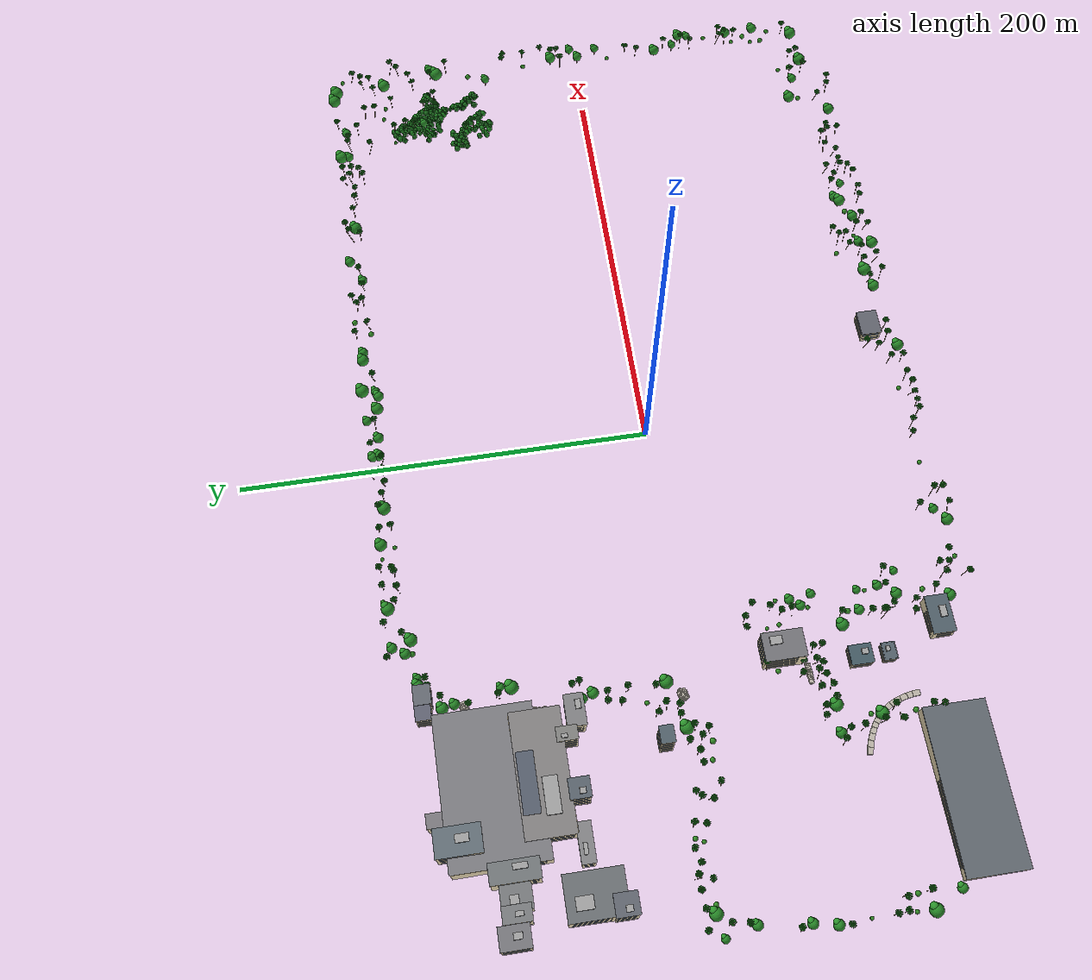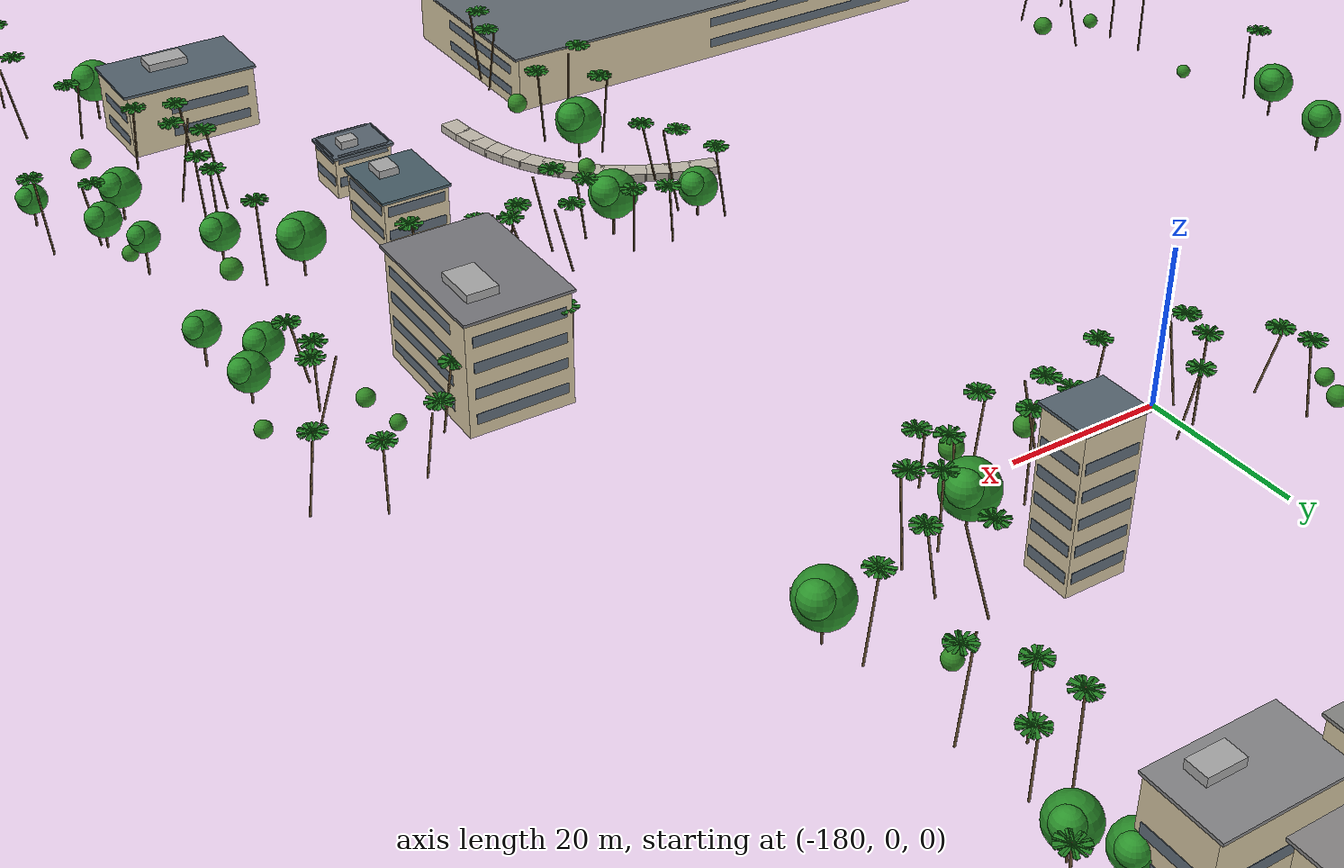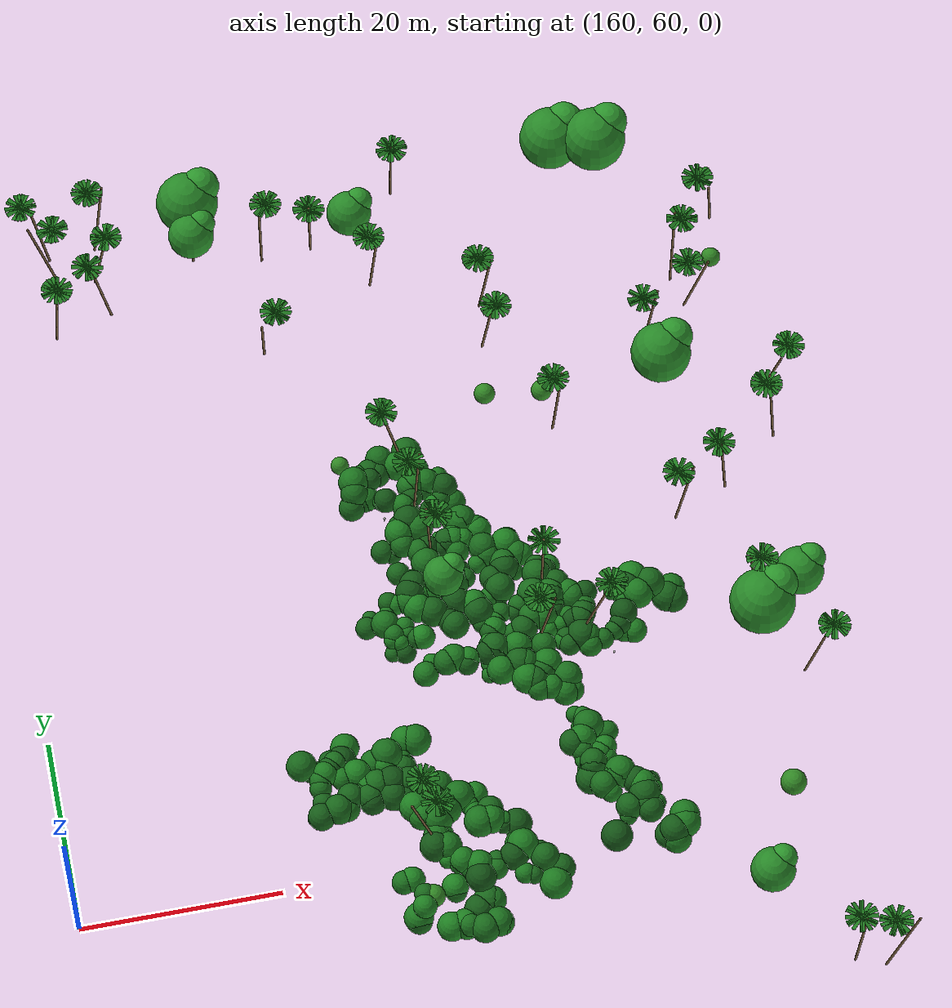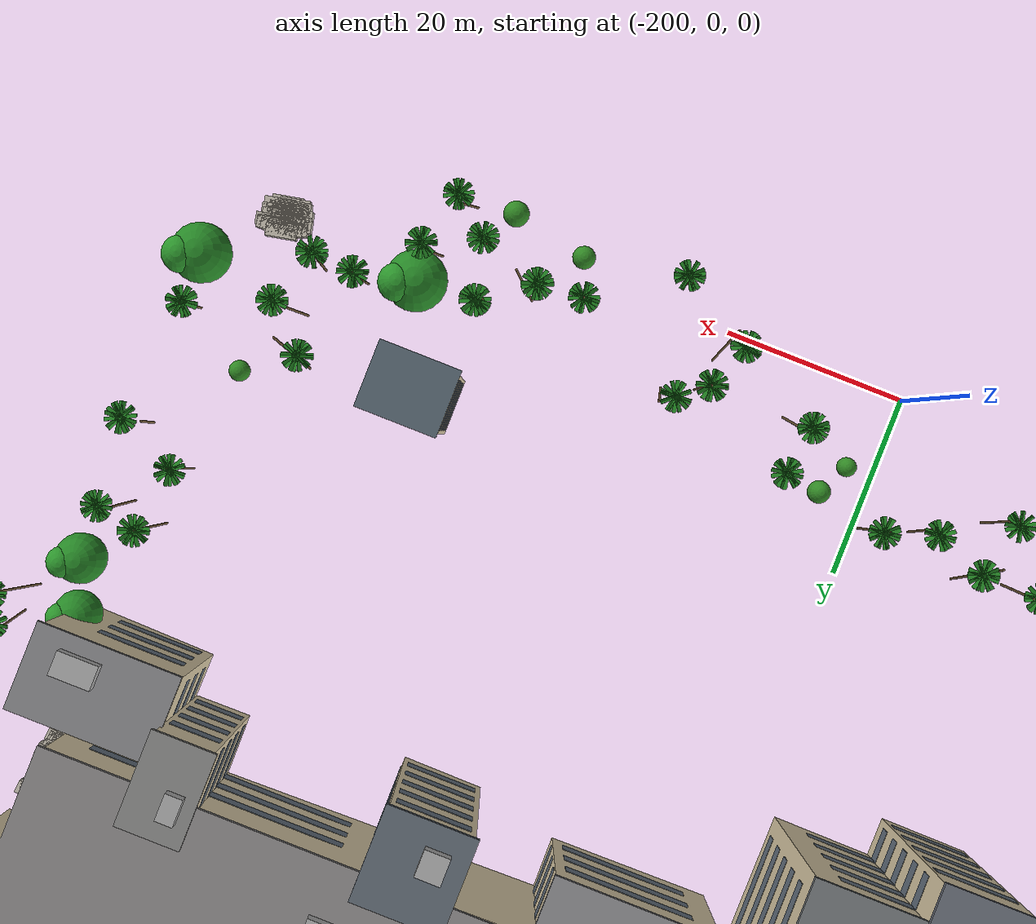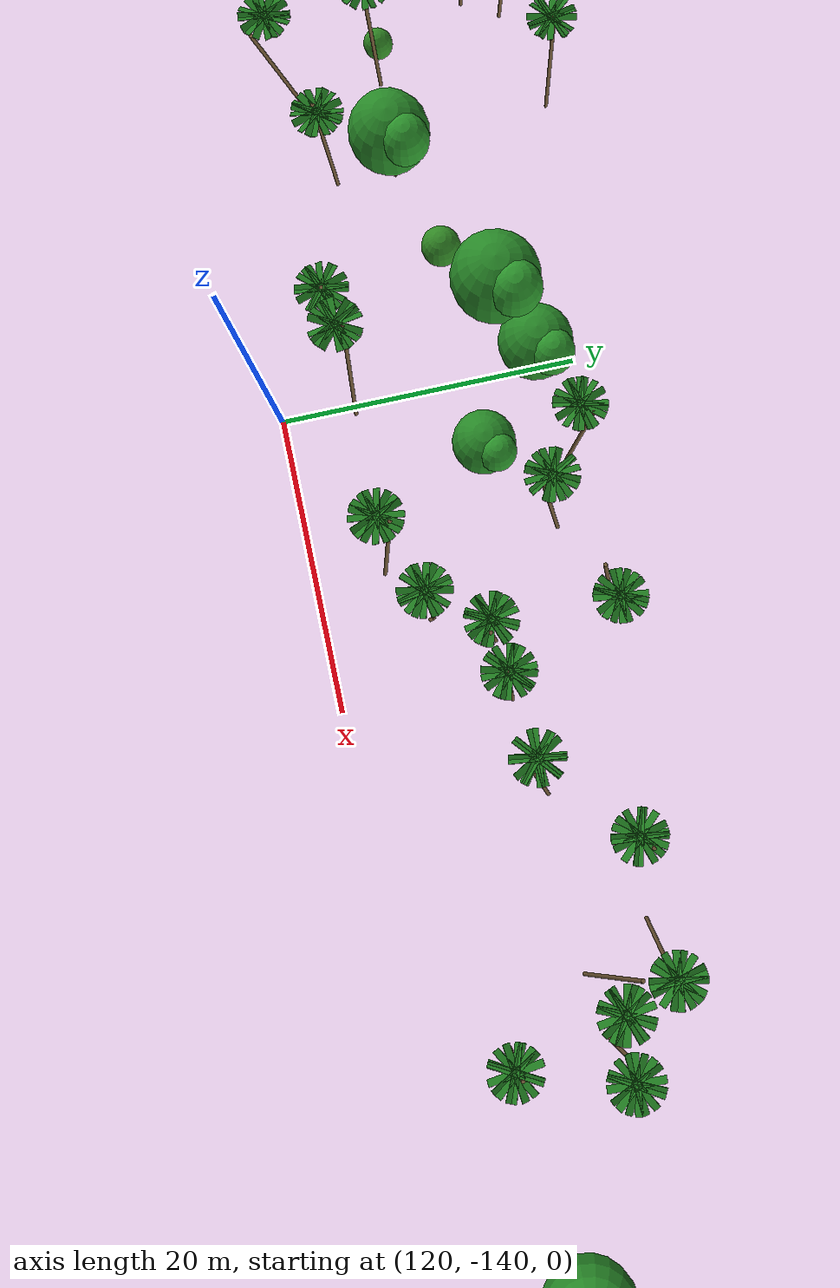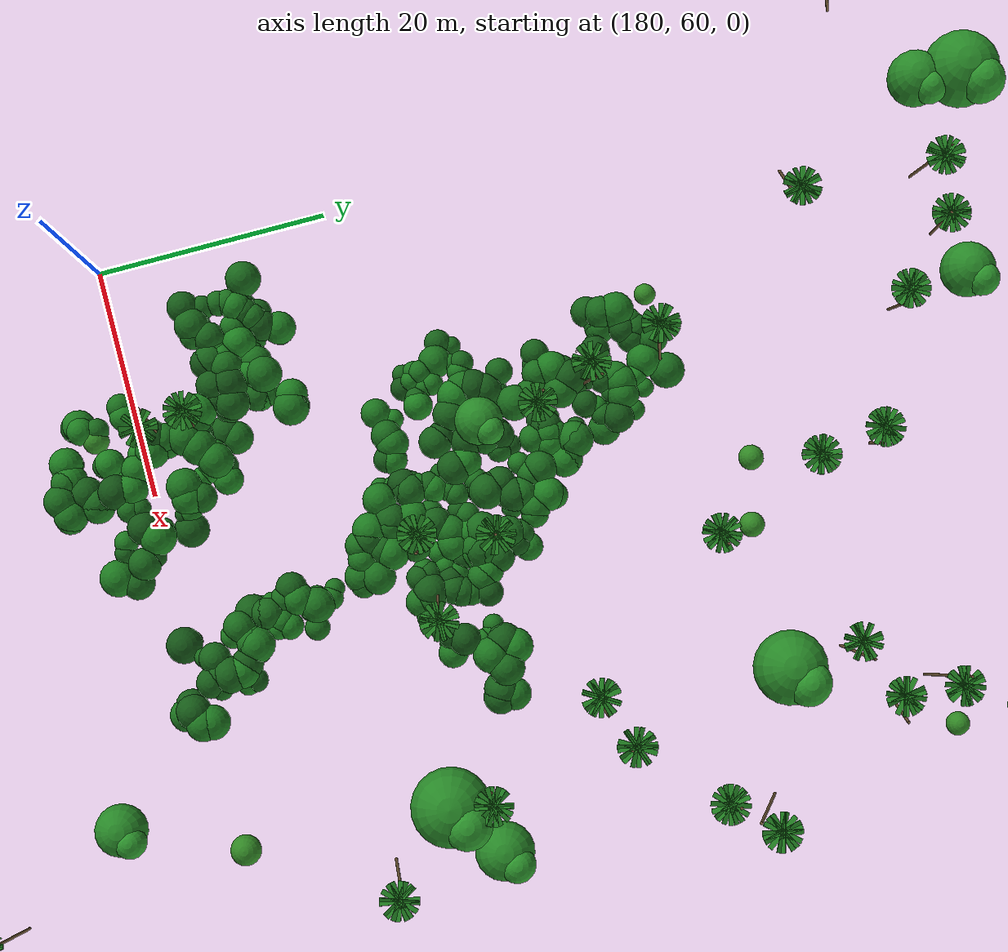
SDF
<sdf version="1.9">
 <world name="dongpo_lake">
  <physics name="4ms" type="dart">
   <max_step_size>0.004</max_step_size>
   <real_time_factor>1.0</real_time_factor>
   <dart><collision_detector>bullet</collision_detector></dart>
  </physics>
  <plugin filename="gz-sim-physics-system" name="gz::sim::systems::Physics"/>
  <plugin filename="gz-sim-user-commands-system" name="gz::sim::systems::UserCommands"/>
  <plugin filename="gz-sim-sensors-system" name="gz::sim::systems::Sensors">
   <render_engine>ogre2</render_engine>
   <disable_on_drained_battery>true</disable_on_drained_battery>
  </plugin>
  <plugin filename="gz-sim-imu-system" name="gz::sim::systems::Imu"/>
  <plugin filename="gz-sim-magnetometer-system" name="gz::sim::systems::Magnetometer"/>
  <plugin filename="gz-sim-forcetorque-system" name="gz::sim::systems::ForceTorque"/>
  <plugin filename="gz-sim-particle-emitter-system" name="gz::sim::systems::ParticleEmitter"/>
  <plugin filename="gz-sim-scene-broadcaster-system" name="gz::sim::systems::SceneBroadcaster"/>
  <plugin filename="gz-sim-contact-system" name="gz::sim::systems::Contact"/>
  <plugin filename="gz-sim-navsat-system" name="gz::sim::systems::NavSat"/>
  <scene>
   <grid>false</grid>
   <ambient>1.0 1.0 1.0</ambient>
   <background>0.8 0.8 0.8</background>
   <fog><color>0.8 0.83 0.86</color><type>linear</type><density>0.0012</density></fog>
  </scene>
  <spherical_coordinates>
   <surface_model>EARTH_WGS84</surface_model>
   <world_frame_orientation>ENU</world_frame_orientation>
   <latitude_deg>20.06108569</latitude_deg>
   <longitude_deg>110.33098135</longitude_deg>
   <elevation>0.0</elevation>
   <heading_deg>0.0</heading_deg>
  </spherical_coordinates>
  <light type="directional" name="sun">
   <pose>0 0 10 0 0 0</pose>
   <diffuse>0.8 0.8 0.8</diffuse>
   <specular>0.2 0.2 0.2 1</specular>
   <attenuation>
    <range>1000</range>
    <constant>0.9</constant>
    <linear>0.01</linear>
    <quadratic>0.001</quadratic>
   </attenuation>
   <direction>-0.5 0.1 -0.9</direction>
  </light>
  <include><name>Shore Trees</name><uri>model://dongpo_shore_trees</uri></include>
  <include><name>Campus Buildings</name><uri>model://dongpo_buildings</uri></include>
  <include><name>Mangroves</name><uri>model://dongpo_mangrove</uri></include>
  <include><name>Jetties</name><uri>model://dongpo_jetties</uri></include>
  <plugin filename="libPublisherPlugin.so" name="vrx::PublisherPlugin">
   <message type="gz.msgs.Param" topic="/vrx/wavefield/parameters" every="2.0">params {
          key: "direction"
          value {
            type: DOUBLE
            double_value: 0.0
          }
        }
        params {
          key: "gain"
          value {
            type: DOUBLE
            double_value: 0.15
          }
        }
        params {
          key: "period"
          value {
            type: DOUBLE
            double_value: 3.0
          }
        }
        params {
          key: "steepness"
          value {
            type: DOUBLE
            double_value: 0.0
          }
        }</message>
  </plugin>
 </world>
</sdf>

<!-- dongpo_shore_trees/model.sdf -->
<sdf version="1.9">
  <model name="dongpo_shore_trees">
    <static>true</static>
    <link name="trees">
    <visual name="t1" cast_shadows="true">
      <pose>-95.84620444542551 136.4333572160119 7.992456836765532 0 0.1663588801011459 2.9386315038585664</pose>
      <geometry><cylinder><radius>0.12</radius><length>11.28</length></cylinder></geometry>
      <material><ambient>0.34 0.26 0.16</ambient><diffuse>0.44 0.34 0.21</diffuse></material>
    </visual>
    <visual name="f1_0" cast_shadows="true">
      <pose>-96.78 136.43 13.55 0 -0.43 -0.07</pose>
      <geometry><box><size>0.42 3.2 0.04</size></box></geometry>
      <material><ambient>0.07 0.32 0.09</ambient><diffuse>0.13 0.5 0.13</diffuse></material>
    </visual>
    <visual name="f1_1" cast_shadows="true">
      <pose>-96.78 136.43 13.55 0 -0.39 0.61</pose>
      <geometry><box><size>0.42 3.2 0.04</size></box></geometry>
      <material><ambient>0.07 0.32 0.09</ambient><diffuse>0.13 0.5 0.13</diffuse></material>
    </visual>
    <visual name="f1_2" cast_shadows="true">
      <pose>-96.78 136.43 13.55 0 -0.37 1.40</pose>
      <geometry><box><size>0.42 3.2 0.04</size></box></geometry>
      <material><ambient>0.07 0.32 0.09</ambient><diffuse>0.13 0.5 0.13</diffuse></material>
    </visual>
    <visual name="f1_3" cast_shadows="true">
      <pose>-96.78 136.43 13.55 0 -0.31 2.27</pose>
      <geometry><box><size>0.42 3.2 0.04</size></box></geometry>
      <material><ambient>0.07 0.32 0.09</ambient><diffuse>0.13 0.5 0.13</diffuse></material>
    </visual>
    <visual name="f1_4" cast_shadows="true">
      <pose>-96.78 136.43 13.55 0 -0.26 2.84</pose>
      <geometry><box><size>0.42 3.2 0.04</size></box></geometry>
      <material><ambient>0.07 0.32 0.09</ambient><diffuse>0.13 0.5 0.13</diffuse></material>
    </visual>
    <visual name="f1_5" cast_shadows="true">
      <pose>-96.78 136.43 13.55 0 -0.46 3.39</pose>
      <geometry><box><size>0.42 3.2 0.04</size></box></geometry>
      <material><ambient>0.07 0.32 0.09</ambient><diffuse>0.13 0.5 0.13</diffuse></material>
    </visual>
    <visual name="f1_6" cast_shadows="true">
      <pose>-96.78 136.43 13.55 0 -0.49 4.23</pose>
      <geometry><box><size>0.42 3.2 0.04</size></box></geometry>
      <material><ambient>0.07 0.32 0.09</ambient><diffuse>0.13 0.5 0.13</diffuse></material>
    </visual>
    <visual name="f1_7" cast_shadows="true">
      <pose>-96.78 136.43 13.55 0 -0.38 4.72</pose>
      <geometry><box><size>0.42 3.2 0.04</size></box></geometry>
      <material><ambient>0.07 0.32 0.09</ambient><diffuse>0.13 0.5 0.13</diffuse></material>
    </visual>
    <visual name="f1_8" cast_shadows="true">
      <pose>-96.78 136.43 13.55 0 -0.28 5.57</pose>
      <geometry><box><size>0.42 3.2 0.04</size></box></geometry>
      <material><ambient>0.07 0.32 0.09</ambient><diffuse>0.13 0.5 0.13</diffuse></material>
    </visual>
    <visual name="c1_0" cast_shadows="true">
      <pose>-97.00 136.20 13.37 0 0 0</pose>
      <geometry><sphere><radius>0.09</radius></sphere></geometry>
      <material><ambient>0.32 0.24 0.1</ambient><diffuse>0.45 0.34 0.12</diffuse></material>
    </visual>
    <visual name="c1_1" cast_shadows="true">
      <pose>-97.10 136.41 13.37 0 0 0</pose>
      <geometry><sphere><radius>0.09</radius></sphere></geometry>
      <material><ambient>0.32 0.24 0.1</ambient><diffuse>0.45 0.34 0.12</diffuse></material>
    </visual>
    <visual name="c1_2" cast_shadows="true">
      <pose>-97.10 136.44 13.37 0 0 0</pose>
      <geometry><sphere><radius>0.09</radius></sphere></geometry>
      <material><ambient>0.32 0.24 0.1</ambient><diffuse>0.45 0.34 0.12</diffuse></material>
    </visual>
    <visual name="t2" cast_shadows="true">
      <pose>-91.43316638070168 134.38990331177905 3.810485379189596 0 0 0.023451040087036988</pose>
      <geometry><cylinder><radius>0.14</radius><length>2.92</length></cylinder></geometry>
      <material><ambient>0.3 0.22 0.14</ambient><diffuse>0.36 0.27 0.17</diffuse></material>
    </visual>
    <visual name="c2" cast_shadows="true">
      <pose>-91.43 134.39 6.60 0 0 0</pose>
      <geometry><sphere><radius>2.42</radius></sphere></geometry>
      <material><ambient>0.12 0.4 0.12</ambient><diffuse>0.16 0.55 0.16</diffuse></material>
    </visual>
    <visual name="cb2" cast_shadows="true">
      <pose>-90.22 135.12 7.57 0 0 0</pose>
      <geometry><sphere><radius>1.50</radius></sphere></geometry>
      <material><ambient>0.12 0.4 0.12</ambient><diffuse>0.18 0.6 0.18</diffuse></material>
    </visual>
    <visual name="t3" cast_shadows="true">
      <pose>-80.10944085797789 136.4536933417656 8.04430049273174 0 0.07824161348781472 4.658321549432463</pose>
      <geometry><cylinder><radius>0.12</radius><length>11.39</length></cylinder></geometry>
      <material><ambient>0.34 0.26 0.16</ambient><diffuse>0.44 0.34 0.21</diffuse></material>
    </visual>
    <visual name="f3_0" cast_shadows="true">
      <pose>-80.55 136.45 13.66 0 -0.37 -0.15</pose>
      <geometry><box><size>0.42 3.2 0.04</size></box></geometry>
      <material><ambient>0.07 0.32 0.09</ambient><diffuse>0.13 0.5 0.13</diffuse></material>
    </visual>
    <visual name="f3_1" cast_shadows="true">
      <pose>-80.55 136.45 13.66 0 -0.29 0.70</pose>
      <geometry><box><size>0.42 3.2 0.04</size></box></geometry>
      <material><ambient>0.07 0.32 0.09</ambient><diffuse>0.13 0.5 0.13</diffuse></material>
    </visual>
    <visual name="f3_2" cast_shadows="true">
      <pose>-80.55 136.45 13.66 0 -0.36 1.35</pose>
      <geometry><box><size>0.42 3.2 0.04</size></box></geometry>
      <material><ambient>0.07 0.32 0.09</ambient><diffuse>0.13 0.5 0.13</diffuse></material>
    </visual>
    <visual name="f3_3" cast_shadows="true">
      <pose>-80.55 136.45 13.66 0 -0.41 1.94</pose>
      <geometry><box><size>0.42 3.2 0.04</size></box></geometry>
      <material><ambient>0.07 0.32 0.09</ambient><diffuse>0.13 0.5 0.13</diffuse></material>
    </visual>
    <visual name="f3_4" cast_shadows="true">
      <pose>-80.55 136.45 13.66 0 -0.46 2.73</pose>
      <geometry><box><size>0.42 3.2 0.04</size></box></geometry>
      <material><ambient>0.07 0.32 0.09</ambient><diffuse>0.13 0.5 0.13</diffuse></material>
    </visual>
    <visual name="f3_5" cast_shadows="true">
      <pose>-80.55 136.45 13.66 0 -0.41 3.60</pose>
      <geometry><box><size>0.42 3.2 0.04</size></box></geometry>
      <material><ambient>0.07 0.32 0.09</ambient><diffuse>0.13 0.5 0.13</diffuse></material>
    </visual>
    <visual name="f3_6" cast_shadows="true">
      <pose>-80.55 136.45 13.66 0 -0.36 4.36</pose>
      <geometry><box><size>0.42 3.2 0.04</size></box></geometry>
      <material><ambient>0.07 0.32 0.09</ambient><diffuse>0.13 0.5 0.13</diffuse></material>
    </visual>
    <visual name="f3_7" cast_shadows="true">
      <pose>-80.55 136.45 13.66 0 -0.35 4.92</pose>
      <geometry><box><size>0.42 3.2 0.04</size></box></geometry>
      <material><ambient>0.07 0.32 0.09</ambient><diffuse>0.13 0.5 0.13</diffuse></material>
    </visual>
    <visual name="f3_8" cast_shadows="true">
      <pose>-80.55 136.45 13.66 0 -0.46 5.65</pose>
      <geometry><box><size>0.42 3.2 0.04</size></box></geometry>
      <material><ambient>0.07 0.32 0.09</ambient><diffuse>0.13 0.5 0.13</diffuse></material>
    </visual>
    <visual name="c3_0" cast_shadows="true">
      <pose>-80.85 136.57 13.48 0 0 0</pose>
      <geometry><sphere><radius>0.09</radius></sphere></geometry>
      <material><ambient>0.32 0.24 0.1</ambient><diffuse>0.45 0.34 0.12</diffuse></material>
    </visual>
    <visual name="c3_1" cast_shadows="true">
      <pose>-80.53 136.77 13.48 0 0 0</pose>
      <geometry><sphere><radius>0.09</radius></sphere></geometry>
      <material><ambient>0.32 0.24 0.1</ambient><diffuse>0.45 0.34 0.12</diffuse></material>
    </visual>
    <visual name="c3_2" cast_shadows="true">
      <pose>-80.82 136.64 13.48 0 0 0</pose>
      <geometry><sphere><radius>0.09</radius></sphere></geometry>
      <material><ambient>0.32 0.24 0.1</ambient><diffuse>0.45 0.34 0.12</diffuse></material>
    </visual>
    <visual name="t4" cast_shadows="true">
      <pose>-72.7305997756928 134.45770899189074 3.8903360651832566 0 0 4.15870855676549</pose>
      <geometry><cylinder><radius>0.14</radius><length>3.08</length></cylinder></geometry>
      <material><ambient>0.3 0.22 0.14</ambient><diffuse>0.36 0.27 0.17</diffuse></material>
    </visual>
    <visual name="c4" cast_shadows="true">
      <pose>-72.73 134.46 7.15 0 0 0</pose>
      <geometry><sphere><radius>3.12</radius></sphere></geometry>
      <material><ambient>0.12 0.4 0.12</ambient><diffuse>0.16 0.55 0.16</diffuse></material>
    </visual>
    <visual name="cb4" cast_shadows="true">
      <pose>-71.17 135.39 8.40 0 0 0</pose>
      <geometry><sphere><radius>1.94</radius></sphere></geometry>
      <material><ambient>0.12 0.4 0.12</ambient><diffuse>0.18 0.6 0.18</diffuse></material>
    </visual>
    <visual name="b5" cast_shadows="true">
      <pose>-67.82 136.65 3.06 0 0 0.913488509618621</pose>
      <geometry><sphere><radius>1.18</radius></sphere></geometry>
      <material><ambient>0.1 0.32 0.09</ambient><diffuse>0.2 0.55 0.15</diffuse></material>
    </visual>
    <visual name="t6" cast_shadows="true">
      <pose>-62.29405718894573 135.4696763428249 8.11811378839294 0 0.07928015492458923 3.577680043695514</pose>
      <geometry><cylinder><radius>0.12</radius><length>11.54</length></cylinder></geometry>
      <material><ambient>0.34 0.26 0.16</ambient><diffuse>0.44 0.34 0.21</diffuse></material>
    </visual>
    <visual name="f6_0" cast_shadows="true">
      <pose>-62.75 135.47 13.81 0 -0.40 -0.04</pose>
      <geometry><box><size>0.42 3.2 0.04</size></box></geometry>
      <material><ambient>0.07 0.32 0.09</ambient><diffuse>0.13 0.5 0.13</diffuse></material>
    </visual>
    <visual name="f6_1" cast_shadows="true">
      <pose>-62.75 135.47 13.81 0 -0.49 0.60</pose>
      <geometry><box><size>0.42 3.2 0.04</size></box></geometry>
      <material><ambient>0.07 0.32 0.09</ambient><diffuse>0.13 0.5 0.13</diffuse></material>
    </visual>
    <visual name="f6_2" cast_shadows="true">
      <pose>-62.75 135.47 13.81 0 -0.39 1.53</pose>
      <geometry><box><size>0.42 3.2 0.04</size></box></geometry>
      <material><ambient>0.07 0.32 0.09</ambient><diffuse>0.13 0.5 0.13</diffuse></material>
    </visual>
    <visual name="f6_3" cast_shadows="true">
      <pose>-62.75 135.47 13.81 0 -0.42 2.11</pose>
      <geometry><box><size>0.42 3.2 0.04</size></box></geometry>
      <material><ambient>0.07 0.32 0.09</ambient><diffuse>0.13 0.5 0.13</diffuse></material>
    </visual>
    <visual name="f6_4" cast_shadows="true">
      <pose>-62.75 135.47 13.81 0 -0.49 2.88</pose>
      <geometry><box><size>0.42 3.2 0.04</size></box></geometry>
      <material><ambient>0.07 0.32 0.09</ambient><diffuse>0.13 0.5 0.13</diffuse></material>
    </visual>
    <visual name="f6_5" cast_shadows="true">
      <pose>-62.75 135.47 13.81 0 -0.49 3.44</pose>
      <geometry><box><size>0.42 3.2 0.04</size></box></geometry>
      <material><ambient>0.07 0.32 0.09</ambient><diffuse>0.13 0.5 0.13</diffuse></material>
    </visual>
    <visual name="f6_6" cast_shadows="true">
      <pose>-62.75 135.47 13.81 0 -0.27 4.05</pose>
      <geometry><box><size>0.42 3.2 0.04</size></box></geometry>
      <material><ambient>0.07 0.32 0.09</ambient><diffuse>0.13 0.5 0.13</diffuse></material>
    </visual>
    <visual name="f6_7" cast_shadows="true">
      <pose>-62.75 135.47 13.81 0 -0.40 4.94</pose>
      <geometry><box><size>0.42 3.2 0.04</size></box></geometry>
      <material><ambient>0.07 0.32 0.09</ambient><diffuse>0.13 0.5 0.13</diffuse></material>
    </visual>
    <visual name="f6_8" cast_shadows="true">
      <pose>-62.75 135.47 13.81 0 -0.29 5.59</pose>
      <geometry><box><size>0.42 3.2 0.04</size></box></geometry>
      <material><ambient>0.07 0.32 0.09</ambient><diffuse>0.13 0.5 0.13</diffuse></material>
    </visual>
    <visual name="c6_0" cast_shadows="true">
      <pose>-62.93 135.74 13.63 0 0 0</pose>
      <geometry><sphere><radius>0.09</radius></sphere></geometry>
      <material><ambient>0.32 0.24 0.1</ambient><diffuse>0.45 0.34 0.12</diffuse></material>
    </visual>
    <visual name="c6_1" cast_shadows="true">
      <pose>-63.02 135.30 13.63 0 0 0</pose>
      <geometry><sphere><radius>0.09</radius></sphere></geometry>
      <material><ambient>0.32 0.24 0.1</ambient><diffuse>0.45 0.34 0.12</diffuse></material>
    </visual>
    <visual name="c6_2" cast_shadows="true">
      <pose>-62.88 135.18 13.63 0 0 0</pose>
      <geometry><sphere><radius>0.09</radius></sphere></geometry>
      <material><ambient>0.32 0.24 0.1</ambient><diffuse>0.45 0.34 0.12</diffuse></material>
    </visual>
    <visual name="b7" cast_shadows="true">
      <pose>-58.24 136.11 2.94 0 0 5.861873783690651</pose>
      <geometry><sphere><radius>0.98</radius></sphere></geometry>
      <material><ambient>0.1 0.32 0.09</ambient><diffuse>0.2 0.55 0.15</diffuse></material>
    </visual>
    <visual name="t8" cast_shadows="true">
      <pose>-52.26253204672608 136.24427737077485 7.187807301826371 0 0.1765435156772256 0.08962307121935462</pose>
      <geometry><cylinder><radius>0.12</radius><length>9.68</length></cylinder></geometry>
      <material><ambient>0.34 0.26 0.16</ambient><diffuse>0.44 0.34 0.21</diffuse></material>
    </visual>
    <visual name="f8_0" cast_shadows="true">
      <pose>-53.11 136.24 11.95 0 -0.31 0.05</pose>
      <geometry><box><size>0.42 3.2 0.04</size></box></geometry>
      <material><ambient>0.07 0.32 0.09</ambient><diffuse>0.13 0.5 0.13</diffuse></material>
    </visual>
    <visual name="f8_1" cast_shadows="true">
      <pose>-53.11 136.24 11.95 0 -0.33 0.70</pose>
      <geometry><box><size>0.42 3.2 0.04</size></box></geometry>
      <material><ambient>0.07 0.32 0.09</ambient><diffuse>0.13 0.5 0.13</diffuse></material>
    </visual>
    <visual name="f8_2" cast_shadows="true">
      <pose>-53.11 136.24 11.95 0 -0.45 1.30</pose>
      <geometry><box><size>0.42 3.2 0.04</size></box></geometry>
      <material><ambient>0.07 0.32 0.09</ambient><diffuse>0.13 0.5 0.13</diffuse></material>
    </visual>
    <visual name="f8_3" cast_shadows="true">
      <pose>-53.11 136.24 11.95 0 -0.46 2.05</pose>
      <geometry><box><size>0.42 3.2 0.04</size></box></geometry>
      <material><ambient>0.07 0.32 0.09</ambient><diffuse>0.13 0.5 0.13</diffuse></material>
    </visual>
    <visual name="f8_4" cast_shadows="true">
      <pose>-53.11 136.24 11.95 0 -0.27 2.74</pose>
      <geometry><box><size>0.42 3.2 0.04</size></box></geometry>
      <material><ambient>0.07 0.32 0.09</ambient><diffuse>0.13 0.5 0.13</diffuse></material>
    </visual>
    <visual name="f8_5" cast_shadows="true">
      <pose>-53.11 136.24 11.95 0 -0.42 3.52</pose>
      <geometry><box><size>0.42 3.2 0.04</size></box></geometry>
      <material><ambient>0.07 0.32 0.09</ambient><diffuse>0.13 0.5 0.13</diffuse></material>
    </visual>
    <visual name="f8_6" cast_shadows="true">
      <pose>-53.11 136.24 11.95 0 -0.27 4.11</pose>
      <geometry><box><size>0.42 3.2 0.04</size></box></geometry>
      <material><ambient>0.07 0.32 0.09</ambient><diffuse>0.13 0.5 0.13</diffuse></material>
    </visual>
    <visual name="f8_7" cast_shadows="true">
      <pose>-53.11 136.24 11.95 0 -0.26 4.87</pose>
      <geometry><box><size>0.42 3.2 0.04</size></box></geometry>
      <material><ambient>0.07 0.32 0.09</ambient><diffuse>0.13 0.5 0.13</diffuse></material>
    </visual>
    <visual name="f8_8" cast_shadows="true">
      <pose>-53.11 136.24 11.95 0 -0.37 5.59</pose>
      <geometry><box><size>0.42 3.2 0.04</size></box></geometry>
      <material><ambient>0.07 0.32 0.09</ambient><diffuse>0.13 0.5 0.13</diffuse></material>
    </visual>
    <visual name="c8_0" cast_shadows="true">
      <pose>-52.86 136.05 11.77 0 0 0</pose>
      <geometry><sphere><radius>0.09</radius></sphere></geometry>
      <material><ambient>0.32 0.24 0.1</ambient><diffuse>0.45 0.34 0.12</diffuse></material>
    </visual>
    <visual name="c8_1" cast_shadows="true">
      <pose>-53.13 135.92 11.77 0 0 0</pose>
      <geometry><sphere><radius>0.09</radius></sphere></geometry>
      <material><ambient>0.32 0.24 0.1</ambient><diffuse>0.45 0.34 0.12</diffuse></material>
    </visual>
    <visual name="c8_2" cast_shadows="true">
      <pose>-53.39 136.09 11.77 0 0 0</pose>
      <geometry><sphere><radius>0.09</radius></sphere></geometry>
      <material><ambient>0.32 0.24 0.1</ambient><diffuse>0.45 0.34 0.12</diffuse></material>
    </visual>
    <visual name="b9" cast_shadows="true">
      <pose>-46.61 135.05 2.91 0 0 2.700380292739304</pose>
      <geometry><sphere><radius>0.93</radius></sphere></geometry>
      <material><ambient>0.1 0.32 0.09</ambient><diffuse>0.2 0.55 0.15</diffuse></material>
    </visual>
    <visual name="t10" cast_shadows="true">
      <pose>-41.11234028511383 134.56569461981738 4.191176959998875 0 0 3.9540273082364785</pose>
      <geometry><cylinder><radius>0.14</radius><length>3.68</length></cylinder></geometry>
      <material><ambient>0.3 0.22 0.14</ambient><diffuse>0.36 0.27 0.17</diffuse></material>
    </visual>
    <visual name="c10" cast_shadows="true">
      <pose>-41.11 134.57 7.63 0 0 0</pose>
      <geometry><sphere><radius>2.90</radius></sphere></geometry>
      <material><ambient>0.12 0.4 0.12</ambient><diffuse>0.16 0.55 0.16</diffuse></material>
    </visual>
    <visual name="cb10" cast_shadows="true">
      <pose>-39.66 135.44 8.79 0 0 0</pose>
      <geometry><sphere><radius>1.80</radius></sphere></geometry>
      <material><ambient>0.12 0.4 0.12</ambient><diffuse>0.18 0.6 0.18</diffuse></material>
    </visual>
    <visual name="t11" cast_shadows="true">
      <pose>-32.21401850716131 134.42143213646366 6.775816389950679 0 0.23266006238938863 5.2762601717546875</pose>
      <geometry><cylinder><radius>0.12</radius><length>8.85</length></cylinder></geometry>
      <material><ambient>0.34 0.26 0.16</ambient><diffuse>0.44 0.34 0.21</diffuse></material>
    </visual>
    <visual name="f11_0" cast_shadows="true">
      <pose>-33.23 134.42 11.12 0 -0.36 -0.14</pose>
      <geometry><box><size>0.42 3.2 0.04</size></box></geometry>
      <material><ambient>0.07 0.32 0.09</ambient><diffuse>0.13 0.5 0.13</diffuse></material>
    </visual>
    <visual name="f11_1" cast_shadows="true">
      <pose>-33.23 134.42 11.12 0 -0.36 0.69</pose>
      <geometry><box><size>0.42 3.2 0.04</size></box></geometry>
      <material><ambient>0.07 0.32 0.09</ambient><diffuse>0.13 0.5 0.13</diffuse></material>
    </visual>
    <visual name="f11_2" cast_shadows="true">
      <pose>-33.23 134.42 11.12 0 -0.43 1.45</pose>
      <geometry><box><size>0.42 3.2 0.04</size></box></geometry>
      <material><ambient>0.07 0.32 0.09</ambient><diffuse>0.13 0.5 0.13</diffuse></material>
    </visual>
    <visual name="f11_3" cast_shadows="true">
      <pose>-33.23 134.42 11.12 0 -0.39 2.26</pose>
      <geometry><box><size>0.42 3.2 0.04</size></box></geometry>
      <material><ambient>0.07 0.32 0.09</ambient><diffuse>0.13 0.5 0.13</diffuse></material>
    </visual>
    <visual name="f11_4" cast_shadows="true">
      <pose>-33.23 134.42 11.12 0 -0.35 2.84</pose>
      <geometry><box><size>0.42 3.2 0.04</size></box></geometry>
      <material><ambient>0.07 0.32 0.09</ambient><diffuse>0.13 0.5 0.13</diffuse></material>
    </visual>
    <visual name="f11_5" cast_shadows="true">
      <pose>-33.23 134.42 11.12 0 -0.49 3.38</pose>
      <geometry><box><size>0.42 3.2 0.04</size></box></geometry>
      <material><ambient>0.07 0.32 0.09</ambient><diffuse>0.13 0.5 0.13</diffuse></material>
    </visual>
    <visual name="f11_6" cast_shadows="true">
      <pose>-33.23 134.42 11.12 0 -0.32 4.16</pose>
      <geometry><box><size>0.42 3.2 0.04</size></box></geometry>
      <material><ambient>0.07 0.32 0.09</ambient><diffuse>0.13 0.5 0.13</diffuse></material>
    </visual>
    <visual name="f11_7" cast_shadows="true">
      <pose>-33.23 134.42 11.12 0 -0.32 5.00</pose>
      <geometry><box><size>0.42 3.2 0.04</size></box></geometry>
      <material><ambient>0.07 0.32 0.09</ambient><diffuse>0.13 0.5 0.13</diffuse></material>
    </visual>
    <visual name="f11_8" cast_shadows="true">
      <pose>-33.23 134.42 11.12 0 -0.28 5.45</pose>
      <geometry><box><size>0.42 3.2 0.04</size></box></geometry>
      <material><ambient>0.07 0.32 0.09</ambient><diffuse>0.13 0.5 0.13</diffuse></material>
    </visual>
    <visual name="c11_0" cast_shadows="true">
      <pose>-33.13 134.12 10.94 0 0 0</pose>
      <geometry><sphere><radius>0.09</radius></sphere></geometry>
      <material><ambient>0.32 0.24 0.1</ambient><diffuse>0.45 0.34 0.12</diffuse></material>
    </visual>
    <visual name="c11_1" cast_shadows="true">
      <pose>-33.01 134.20 10.94 0 0 0</pose>
      <geometry><sphere><radius>0.09</radius></sphere></geometry>
      <material><ambient>0.32 0.24 0.1</ambient><diffuse>0.45 0.34 0.12</diffuse></material>
    </visual>
    <visual name="c11_2" cast_shadows="true">
      <pose>-33.55 134.38 10.94 0 0 0</pose>
      <geometry><sphere><radius>0.09</radius></sphere></geometry>
      <material><ambient>0.32 0.24 0.1</ambient><diffuse>0.45 0.34 0.12</diffuse></material>
    </visual>
    <visual name="t12" cast_shadows="true">
      <pose>-22.761668998744657 133.87334359989154 6.847139546417965 0 -0.17499813276065873 3.5611105394602847</pose>
      <geometry><cylinder><radius>0.12</radius><length>8.99</length></cylinder></geometry>
      <material><ambient>0.34 0.26 0.16</ambient><diffuse>0.44 0.34 0.21</diffuse></material>
    </visual>
    <visual name="f12_0" cast_shadows="true">
      <pose>-21.98 133.87 11.26 0 -0.36 -0.17</pose>
      <geometry><box><size>0.42 3.2 0.04</size></box></geometry>
      <material><ambient>0.07 0.32 0.09</ambient><diffuse>0.13 0.5 0.13</diffuse></material>
    </visual>
    <visual name="f12_1" cast_shadows="true">
      <pose>-21.98 133.87 11.26 0 -0.34 0.58</pose>
      <geometry><box><size>0.42 3.2 0.04</size></box></geometry>
      <material><ambient>0.07 0.32 0.09</ambient><diffuse>0.13 0.5 0.13</diffuse></material>
    </visual>
    <visual name="f12_2" cast_shadows="true">
      <pose>-21.98 133.87 11.26 0 -0.43 1.22</pose>
      <geometry><box><size>0.42 3.2 0.04</size></box></geometry>
      <material><ambient>0.07 0.32 0.09</ambient><diffuse>0.13 0.5 0.13</diffuse></material>
    </visual>
    <visual name="f12_3" cast_shadows="true">
      <pose>-21.98 133.87 11.26 0 -0.37 2.25</pose>
      <geometry><box><size>0.42 3.2 0.04</size></box></geometry>
      <material><ambient>0.07 0.32 0.09</ambient><diffuse>0.13 0.5 0.13</diffuse></material>
    </visual>
    <visual name="f12_4" cast_shadows="true">
      <pose>-21.98 133.87 11.26 0 -0.34 2.90</pose>
      <geometry><box><size>0.42 3.2 0.04</size></box></geometry>
      <material><ambient>0.07 0.32 0.09</ambient><diffuse>0.13 0.5 0.13</diffuse></material>
    </visual>
    <visual name="f12_5" cast_shadows="true">
      <pose>-21.98 133.87 11.26 0 -0.45 3.53</pose>
      <geometry><box><size>0.42 3.2 0.04</size></box></geometry>
      <material><ambient>0.07 0.32 0.09</ambient><diffuse>0.13 0.5 0.13</diffuse></material>
    </visual>
    <visual name="f12_6" cast_shadows="true">
      <pose>-21.98 133.87 11.26 0 -0.49 4.22</pose>
      <geometry><box><size>0.42 3.2 0.04</size></box></geometry>
      <material><ambient>0.07 0.32 0.09</ambient><diffuse>0.13 0.5 0.13</diffuse></material>
    </visual>
    <visual name="f12_7" cast_shadows="true">
      <pose>-21.98 133.87 11.26 0 -0.27 5.00</pose>
      <geometry><box><size>0.42 3.2 0.04</size></box></geometry>
      <material><ambient>0.07 0.32 0.09</ambient><diffuse>0.13 0.5 0.13</diffuse></material>
    </visual>
    <visual name="f12_8" cast_shadows="true">
      <pose>-21.98 133.87 11.26 0 -0.49 5.71</pose>
      <geometry><box><size>0.42 3.2 0.04</size></box></geometry>
      <material><ambient>0.07 0.32 0.09</ambient><diffuse>0.13 0.5 0.13</diffuse></material>
    </visual>
    <visual name="c12_0" cast_shadows="true">
      <pose>-22.15 134.15 11.08 0 0 0</pose>
      <geometry><sphere><radius>0.09</radius></sphere></geometry>
      <material><ambient>0.32 0.24 0.1</ambient><diffuse>0.45 0.34 0.12</diffuse></material>
    </visual>
    <visual name="c12_1" cast_shadows="true">
      <pose>-22.11 134.16 11.08 0 0 0</pose>
      <geometry><sphere><radius>0.09</radius></sphere></geometry>
      <material><ambient>0.32 0.24 0.1</ambient><diffuse>0.45 0.34 0.12</diffuse></material>
    </visual>
    <visual name="c12_2" cast_shadows="true">
      <pose>-21.74 134.08 11.08 0 0 0</pose>
      <geometry><sphere><radius>0.09</radius></sphere></geometry>
      <material><ambient>0.32 0.24 0.1</ambient><diffuse>0.45 0.34 0.12</diffuse></material>
    </visual>
    <visual name="t13" cast_shadows="true">
      <pose>-4.42964326729332 136.2040776183615 7.883718313476312 0 0.21426760314507426 1.2389345385433683</pose>
      <geometry><cylinder><radius>0.12</radius><length>11.07</length></cylinder></geometry>
      <material><ambient>0.34 0.26 0.16</ambient><diffuse>0.44 0.34 0.21</diffuse></material>
    </visual>
    <visual name="f13_0" cast_shadows="true">
      <pose>-5.61 136.20 13.34 0 -0.35 0.03</pose>
      <geometry><box><size>0.42 3.2 0.04</size></box></geometry>
      <material><ambient>0.07 0.32 0.09</ambient><diffuse>0.13 0.5 0.13</diffuse></material>
    </visual>
    <visual name="f13_1" cast_shadows="true">
      <pose>-5.61 136.20 13.34 0 -0.48 0.74</pose>
      <geometry><box><size>0.42 3.2 0.04</size></box></geometry>
      <material><ambient>0.07 0.32 0.09</ambient><diffuse>0.13 0.5 0.13</diffuse></material>
    </visual>
    <visual name="f13_2" cast_shadows="true">
      <pose>-5.61 136.20 13.34 0 -0.35 1.45</pose>
      <geometry><box><size>0.42 3.2 0.04</size></box></geometry>
      <material><ambient>0.07 0.32 0.09</ambient><diffuse>0.13 0.5 0.13</diffuse></material>
    </visual>
    <visual name="f13_3" cast_shadows="true">
      <pose>-5.61 136.20 13.34 0 -0.31 2.21</pose>
      <geometry><box><size>0.42 3.2 0.04</size></box></geometry>
      <material><ambient>0.07 0.32 0.09</ambient><diffuse>0.13 0.5 0.13</diffuse></material>
    </visual>
    <visual name="f13_4" cast_shadows="true">
      <pose>-5.61 136.20 13.34 0 -0.33 2.73</pose>
      <geometry><box><size>0.42 3.2 0.04</size></box></geometry>
      <material><ambient>0.07 0.32 0.09</ambient><diffuse>0.13 0.5 0.13</diffuse></material>
    </visual>
    <visual name="f13_5" cast_shadows="true">
      <pose>-5.61 136.20 13.34 0 -0.29 3.62</pose>
      <geometry><box><size>0.42 3.2 0.04</size></box></geometry>
      <material><ambient>0.07 0.32 0.09</ambient><diffuse>0.13 0.5 0.13</diffuse></material>
    </visual>
    <visual name="f13_6" cast_shadows="true">
      <pose>-5.61 136.20 13.34 0 -0.49 4.07</pose>
      <geometry><box><size>0.42 3.2 0.04</size></box></geometry>
      <material><ambient>0.07 0.32 0.09</ambient><diffuse>0.13 0.5 0.13</diffuse></material>
    </visual>
    <visual name="f13_7" cast_shadows="true">
      <pose>-5.61 136.20 13.34 0 -0.45 4.94</pose>
      <geometry><box><size>0.42 3.2 0.04</size></box></geometry>
      <material><ambient>0.07 0.32 0.09</ambient><diffuse>0.13 0.5 0.13</diffuse></material>
    </visual>
    <visual name="f13_8" cast_shadows="true">
      <pose>-5.61 136.20 13.34 0 -0.27 5.61</pose>
      <geometry><box><size>0.42 3.2 0.04</size></box></geometry>
      <material><ambient>0.07 0.32 0.09</ambient><diffuse>0.13 0.5 0.13</diffuse></material>
    </visual>
    <visual name="c13_0" cast_shadows="true">
      <pose>-5.84 136.42 13.16 0 0 0</pose>
      <geometry><sphere><radius>0.09</radius></sphere></geometry>
      <material><ambient>0.32 0.24 0.1</ambient><diffuse>0.45 0.34 0.12</diffuse></material>
    </visual>
    <visual name="c13_1" cast_shadows="true">
      <pose>-5.61 136.52 13.16 0 0 0</pose>
      <geometry><sphere><radius>0.09</radius></sphere></geometry>
      <material><ambient>0.32 0.24 0.1</ambient><diffuse>0.45 0.34 0.12</diffuse></material>
    </visual>
    <visual name="c13_2" cast_shadows="true">
      <pose>-5.91 136.29 13.16 0 0 0</pose>
      <geometry><sphere><radius>0.09</radius></sphere></geometry>
      <material><ambient>0.32 0.24 0.1</ambient><diffuse>0.45 0.34 0.12</diffuse></material>
    </visual>
    <visual name="t14" cast_shadows="true">
      <pose>4.679993004112063 134.21386044633869 4.314442025810547 0 0 2.3344264234233467</pose>
      <geometry><cylinder><radius>0.14</radius><length>3.93</length></cylinder></geometry>
      <material><ambient>0.3 0.22 0.14</ambient><diffuse>0.36 0.27 0.17</diffuse></material>
    </visual>
    <visual name="c14" cast_shadows="true">
      <pose>4.68 134.21 7.61 0 0 0</pose>
      <geometry><sphere><radius>2.43</radius></sphere></geometry>
      <material><ambient>0.12 0.4 0.12</ambient><diffuse>0.16 0.55 0.16</diffuse></material>
    </visual>
    <visual name="cb14" cast_shadows="true">
      <pose>5.89 134.94 8.59 0 0 0</pose>
      <geometry><sphere><radius>1.51</radius></sphere></geometry>
      <material><ambient>0.12 0.4 0.12</ambient><diffuse>0.18 0.6 0.18</diffuse></material>
    </visual>
    <visual name="t15" cast_shadows="true">
      <pose>9.461566895354697 134.5549256546734 7.264851396276436 0 -0.23434238223055892 4.727157816384795</pose>
      <geometry><cylinder><radius>0.12</radius><length>9.83</length></cylinder></geometry>
      <material><ambient>0.34 0.26 0.16</ambient><diffuse>0.44 0.34 0.21</diffuse></material>
    </visual>
    <visual name="f15_0" cast_shadows="true">
      <pose>10.60 134.55 12.10 0 -0.43 0.03</pose>
      <geometry><box><size>0.42 3.2 0.04</size></box></geometry>
      <material><ambient>0.07 0.32 0.09</ambient><diffuse>0.13 0.5 0.13</diffuse></material>
    </visual>
    <visual name="f15_1" cast_shadows="true">
      <pose>10.60 134.55 12.10 0 -0.32 0.55</pose>
      <geometry><box><size>0.42 3.2 0.04</size></box></geometry>
      <material><ambient>0.07 0.32 0.09</ambient><diffuse>0.13 0.5 0.13</diffuse></material>
    </visual>
    <visual name="f15_2" cast_shadows="true">
      <pose>10.60 134.55 12.10 0 -0.47 1.26</pose>
      <geometry><box><size>0.42 3.2 0.04</size></box></geometry>
      <material><ambient>0.07 0.32 0.09</ambient><diffuse>0.13 0.5 0.13</diffuse></material>
    </visual>
    <visual name="f15_3" cast_shadows="true">
      <pose>10.60 134.55 12.10 0 -0.48 1.96</pose>
      <geometry><box><size>0.42 3.2 0.04</size></box></geometry>
      <material><ambient>0.07 0.32 0.09</ambient><diffuse>0.13 0.5 0.13</diffuse></material>
    </visual>
    <visual name="f15_4" cast_shadows="true">
      <pose>10.60 134.55 12.10 0 -0.44 2.94</pose>
      <geometry><box><size>0.42 3.2 0.04</size></box></geometry>
      <material><ambient>0.07 0.32 0.09</ambient><diffuse>0.13 0.5 0.13</diffuse></material>
    </visual>
    <visual name="f15_5" cast_shadows="true">
      <pose>10.60 134.55 12.10 0 -0.30 3.42</pose>
      <geometry><box><size>0.42 3.2 0.04</size></box></geometry>
      <material><ambient>0.07 0.32 0.09</ambient><diffuse>0.13 0.5 0.13</diffuse></material>
    </visual>
    <visual name="f15_6" cast_shadows="true">
      <pose>10.60 134.55 12.10 0 -0.46 4.23</pose>
      <geometry><box><size>0.42 3.2 0.04</size></box></geometry>
      <material><ambient>0.07 0.32 0.09</ambient><diffuse>0.13 0.5 0.13</diffuse></material>
    </visual>
    <visual name="f15_7" cast_shadows="true">
      <pose>10.60 134.55 12.10 0 -0.29 4.86</pose>
      <geometry><box><size>0.42 3.2 0.04</size></box></geometry>
      <material><ambient>0.07 0.32 0.09</ambient><diffuse>0.13 0.5 0.13</diffuse></material>
    </visual>
    <visual name="f15_8" cast_shadows="true">
      <pose>10.60 134.55 12.10 0 -0.33 5.54</pose>
      <geometry><box><size>0.42 3.2 0.04</size></box></geometry>
      <material><ambient>0.07 0.32 0.09</ambient><diffuse>0.13 0.5 0.13</diffuse></material>
    </visual>
    <visual name="c15_0" cast_shadows="true">
      <pose>10.87 134.74 11.92 0 0 0</pose>
      <geometry><sphere><radius>0.09</radius></sphere></geometry>
      <material><ambient>0.32 0.24 0.1</ambient><diffuse>0.45 0.34 0.12</diffuse></material>
    </visual>
    <visual name="c15_1" cast_shadows="true">
      <pose>10.56 134.24 11.92 0 0 0</pose>
      <geometry><sphere><radius>0.09</radius></sphere></geometry>
      <material><ambient>0.32 0.24 0.1</ambient><diffuse>0.45 0.34 0.12</diffuse></material>
    </visual>
    <visual name="c15_2" cast_shadows="true">
      <pose>10.66 134.24 11.92 0 0 0</pose>
      <geometry><sphere><radius>0.09</radius></sphere></geometry>
      <material><ambient>0.32 0.24 0.1</ambient><diffuse>0.45 0.34 0.12</diffuse></material>
    </visual>
    <visual name="t16" cast_shadows="true">
      <pose>24.843494085428663 135.36902558200399 3.802670562791742 0 0 3.3668338661424575</pose>
      <geometry><cylinder><radius>0.14</radius><length>2.91</length></cylinder></geometry>
      <material><ambient>0.3 0.22 0.14</ambient><diffuse>0.36 0.27 0.17</diffuse></material>
    </visual>
    <visual name="c16" cast_shadows="true">
      <pose>24.84 135.37 6.51 0 0 0</pose>
      <geometry><sphere><radius>2.27</radius></sphere></geometry>
      <material><ambient>0.12 0.4 0.12</ambient><diffuse>0.16 0.55 0.16</diffuse></material>
    </visual>
    <visual name="cb16" cast_shadows="true">
      <pose>25.98 136.05 7.41 0 0 0</pose>
      <geometry><sphere><radius>1.41</radius></sphere></geometry>
      <material><ambient>0.12 0.4 0.12</ambient><diffuse>0.18 0.6 0.18</diffuse></material>
    </visual>
    <visual name="t17" cast_shadows="true">
      <pose>41.03813325201978 136.21130779398754 4.226778233447982 0 0 5.898050140578734</pose>
      <geometry><cylinder><radius>0.14</radius><length>3.75</length></cylinder></geometry>
      <material><ambient>0.3 0.22 0.14</ambient><diffuse>0.36 0.27 0.17</diffuse></material>
    </visual>
    <visual name="c17" cast_shadows="true">
      <pose>41.04 136.21 7.92 0 0 0</pose>
      <geometry><sphere><radius>3.30</radius></sphere></geometry>
      <material><ambient>0.12 0.4 0.12</ambient><diffuse>0.16 0.55 0.16</diffuse></material>
    </visual>
    <visual name="cb17" cast_shadows="true">
      <pose>42.69 137.20 9.23 0 0 0</pose>
      <geometry><sphere><radius>2.04</radius></sphere></geometry>
      <material><ambient>0.12 0.4 0.12</ambient><diffuse>0.18 0.6 0.18</diffuse></material>
    </visual>
    <visual name="t18" cast_shadows="true">
      <pose>58.24347447373968 134.36603380716284 4.2561525316147115 0 0 2.7933378734001724</pose>
      <geometry><cylinder><radius>0.14</radius><length>3.81</length></cylinder></geometry>
      <material><ambient>0.3 0.22 0.14</ambient><diffuse>0.36 0.27 0.17</diffuse></material>
    </visual>
    <visual name="c18" cast_shadows="true">
      <pose>58.24 134.37 7.76 0 0 0</pose>
      <geometry><sphere><radius>2.91</radius></sphere></geometry>
      <material><ambient>0.12 0.4 0.12</ambient><diffuse>0.16 0.55 0.16</diffuse></material>
    </visual>
    <visual name="cb18" cast_shadows="true">
      <pose>59.70 135.24 8.93 0 0 0</pose>
      <geometry><sphere><radius>1.80</radius></sphere></geometry>
      <material><ambient>0.12 0.4 0.12</ambient><diffuse>0.18 0.6 0.18</diffuse></material>
    </visual>
    <visual name="t19" cast_shadows="true">
      <pose>62.85725478185003 133.91271458515683 4.0838959020438175 0 0 3.441620664710724</pose>
      <geometry><cylinder><radius>0.14</radius><length>3.47</length></cylinder></geometry>
      <material><ambient>0.3 0.22 0.14</ambient><diffuse>0.36 0.27 0.17</diffuse></material>
    </visual>
    <visual name="c19" cast_shadows="true">
      <pose>62.86 133.91 7.16 0 0 0</pose>
      <geometry><sphere><radius>2.44</radius></sphere></geometry>
      <material><ambient>0.12 0.4 0.12</ambient><diffuse>0.16 0.55 0.16</diffuse></material>
    </visual>
    <visual name="cb19" cast_shadows="true">
      <pose>64.08 134.65 8.14 0 0 0</pose>
      <geometry><sphere><radius>1.51</radius></sphere></geometry>
      <material><ambient>0.12 0.4 0.12</ambient><diffuse>0.18 0.6 0.18</diffuse></material>
    </visual>
    <visual name="t20" cast_shadows="true">
      <pose>74.64617369063615 136.57108691873927 6.625632308699863 0 0.14580904575450204 6.235718832941246</pose>
      <geometry><cylinder><radius>0.12</radius><length>8.55</length></cylinder></geometry>
      <material><ambient>0.34 0.26 0.16</ambient><diffuse>0.44 0.34 0.21</diffuse></material>
    </visual>
    <visual name="f20_0" cast_shadows="true">
      <pose>74.02 136.57 10.82 0 -0.33 -0.13</pose>
      <geometry><box><size>0.42 3.2 0.04</size></box></geometry>
      <material><ambient>0.07 0.32 0.09</ambient><diffuse>0.13 0.5 0.13</diffuse></material>
    </visual>
    <visual name="f20_1" cast_shadows="true">
      <pose>74.02 136.57 10.82 0 -0.28 0.82</pose>
      <geometry><box><size>0.42 3.2 0.04</size></box></geometry>
      <material><ambient>0.07 0.32 0.09</ambient><diffuse>0.13 0.5 0.13</diffuse></material>
    </visual>
    <visual name="f20_2" cast_shadows="true">
      <pose>74.02 136.57 10.82 0 -0.48 1.26</pose>
      <geometry><box><size>0.42 3.2 0.04</size></box></geometry>
      <material><ambient>0.07 0.32 0.09</ambient><diffuse>0.13 0.5 0.13</diffuse></material>
    </visual>
    <visual name="f20_3" cast_shadows="true">
      <pose>74.02 136.57 10.82 0 -0.47 2.27</pose>
      <geometry><box><size>0.42 3.2 0.04</size></box></geometry>
      <material><ambient>0.07 0.32 0.09</ambient><diffuse>0.13 0.5 0.13</diffuse></material>
    </visual>
    <visual name="f20_4" cast_shadows="true">
      <pose>74.02 136.57 10.82 0 -0.36 2.68</pose>
      <geometry><box><size>0.42 3.2 0.04</size></box></geometry>
      <material><ambient>0.07 0.32 0.09</ambient><diffuse>0.13 0.5 0.13</diffuse></material>
    </visual>
    <visual name="f20_5" cast_shadows="true">
      <pose>74.02 136.57 10.82 0 -0.32 3.47</pose>
      <geometry><box><size>0.42 3.2 0.04</size></box></geometry>
      <material><ambient>0.07 0.32 0.09</ambient><diffuse>0.13 0.5 0.13</diffuse></material>
    </visual>
    <visual name="f20_6" cast_shadows="true">
      <pose>74.02 136.57 10.82 0 -0.28 4.08</pose>
      <geometry><box><size>0.42 3.2 0.04</size></box></geometry>
      <material><ambient>0.07 0.32 0.09</ambient><diffuse>0.13 0.5 0.13</diffuse></material>
    </visual>
    <visual name="f20_7" cast_shadows="true">
      <pose>74.02 136.57 10.82 0 -0.32 4.79</pose>
      <geometry><box><size>0.42 3.2 0.04</size></box></geometry>
      <material><ambient>0.07 0.32 0.09</ambient><diffuse>0.13 0.5 0.13</diffuse></material>
    </visual>
    <visual name="f20_8" cast_shadows="true">
      <pose>74.02 136.57 10.82 0 -0.39 5.43</pose>
      <geometry><box><size>0.42 3.2 0.04</size></box></geometry>
      <material><ambient>0.07 0.32 0.09</ambient><diffuse>0.13 0.5 0.13</diffuse></material>
    </visual>
    <visual name="c20_0" cast_shadows="true">
      <pose>74.34 136.64 10.64 0 0 0</pose>
      <geometry><sphere><radius>0.09</radius></sphere></geometry>
      <material><ambient>0.32 0.24 0.1</ambient><diffuse>0.45 0.34 0.12</diffuse></material>
    </visual>
    <visual name="c20_1" cast_shadows="true">
      <pose>73.90 136.87 10.64 0 0 0</pose>
      <geometry><sphere><radius>0.09</radius></sphere></geometry>
      <material><ambient>0.32 0.24 0.1</ambient><diffuse>0.45 0.34 0.12</diffuse></material>
    </visual>
    <visual name="c20_2" cast_shadows="true">
      <pose>73.90 136.87 10.64 0 0 0</pose>
      <geometry><sphere><radius>0.09</radius></sphere></geometry>
      <material><ambient>0.32 0.24 0.1</ambient><diffuse>0.45 0.34 0.12</diffuse></material>
    </visual>
    <visual name="b21" cast_shadows="true">
      <pose>82.88 136.80 3.16 0 0 1.5484943288624513</pose>
      <geometry><sphere><radius>1.36</radius></sphere></geometry>
      <material><ambient>0.1 0.32 0.09</ambient><diffuse>0.2 0.55 0.15</diffuse></material>
    </visual>
    <visual name="t22" cast_shadows="true">
      <pose>88.67025470163016 134.18741602635612 7.356672895972814 0 -0.21104515260282178 1.1071914521918387</pose>
      <geometry><cylinder><radius>0.12</radius><length>10.01</length></cylinder></geometry>
      <material><ambient>0.34 0.26 0.16</ambient><diffuse>0.44 0.34 0.21</diffuse></material>
    </visual>
    <visual name="f22_0" cast_shadows="true">
      <pose>89.72 134.19 12.28 0 -0.38 0.13</pose>
      <geometry><box><size>0.42 3.2 0.04</size></box></geometry>
      <material><ambient>0.07 0.32 0.09</ambient><diffuse>0.13 0.5 0.13</diffuse></material>
    </visual>
    <visual name="f22_1" cast_shadows="true">
      <pose>89.72 134.19 12.28 0 -0.34 0.58</pose>
      <geometry><box><size>0.42 3.2 0.04</size></box></geometry>
      <material><ambient>0.07 0.32 0.09</ambient><diffuse>0.13 0.5 0.13</diffuse></material>
    </visual>
    <visual name="f22_2" cast_shadows="true">
      <pose>89.72 134.19 12.28 0 -0.37 1.31</pose>
      <geometry><box><size>0.42 3.2 0.04</size></box></geometry>
      <material><ambient>0.07 0.32 0.09</ambient><diffuse>0.13 0.5 0.13</diffuse></material>
    </visual>
    <visual name="f22_3" cast_shadows="true">
      <pose>89.72 134.19 12.28 0 -0.38 2.02</pose>
      <geometry><box><size>0.42 3.2 0.04</size></box></geometry>
      <material><ambient>0.07 0.32 0.09</ambient><diffuse>0.13 0.5 0.13</diffuse></material>
    </visual>
    <visual name="f22_4" cast_shadows="true">
      <pose>89.72 134.19 12.28 0 -0.37 2.84</pose>
      <geometry><box><size>0.42 3.2 0.04</size></box></geometry>
      <material><ambient>0.07 0.32 0.09</ambient><diffuse>0.13 0.5 0.13</diffuse></material>
    </visual>
    <visual name="f22_5" cast_shadows="true">
      <pose>89.72 134.19 12.28 0 -0.31 3.45</pose>
      <geometry><box><size>0.42 3.2 0.04</size></box></geometry>
      <material><ambient>0.07 0.32 0.09</ambient><diffuse>0.13 0.5 0.13</diffuse></material>
    </visual>
    <visual name="f22_6" cast_shadows="true">
      <pose>89.72 134.19 12.28 0 -0.46 4.32</pose>
      <geometry><box><size>0.42 3.2 0.04</size></box></geometry>
      <material><ambient>0.07 0.32 0.09</ambient><diffuse>0.13 0.5 0.13</diffuse></material>
    </visual>
    <visual name="f22_7" cast_shadows="true">
      <pose>89.72 134.19 12.28 0 -0.47 4.76</pose>
      <geometry><box><size>0.42 3.2 0.04</size></box></geometry>
      <material><ambient>0.07 0.32 0.09</ambient><diffuse>0.13 0.5 0.13</diffuse></material>
    </visual>
    <visual name="f22_8" cast_shadows="true">
      <pose>89.72 134.19 12.28 0 -0.27 5.76</pose>
      <geometry><box><size>0.42 3.2 0.04</size></box></geometry>
      <material><ambient>0.07 0.32 0.09</ambient><diffuse>0.13 0.5 0.13</diffuse></material>
    </visual>
    <visual name="c22_0" cast_shadows="true">
      <pose>89.76 134.51 12.10 0 0 0</pose>
      <geometry><sphere><radius>0.09</radius></sphere></geometry>
      <material><ambient>0.32 0.24 0.1</ambient><diffuse>0.45 0.34 0.12</diffuse></material>
    </visual>
    <visual name="c22_1" cast_shadows="true">
      <pose>90.03 134.13 12.10 0 0 0</pose>
      <geometry><sphere><radius>0.09</radius></sphere></geometry>
      <material><ambient>0.32 0.24 0.1</ambient><diffuse>0.45 0.34 0.12</diffuse></material>
    </visual>
    <visual name="c22_2" cast_shadows="true">
      <pose>89.80 134.50 12.10 0 0 0</pose>
      <geometry><sphere><radius>0.09</radius></sphere></geometry>
      <material><ambient>0.32 0.24 0.1</ambient><diffuse>0.45 0.34 0.12</diffuse></material>
    </visual>
    <visual name="t23" cast_shadows="true">
      <pose>94.75902617437865 136.55756458803964 6.980701628868763 0 0.05598583114080741 0.416980812200592</pose>
      <geometry><cylinder><radius>0.12</radius><length>9.26</length></cylinder></geometry>
      <material><ambient>0.34 0.26 0.16</ambient><diffuse>0.44 0.34 0.21</diffuse></material>
    </visual>
    <visual name="f23_0" cast_shadows="true">
      <pose>94.50 136.56 11.53 0 -0.39 -0.09</pose>
      <geometry><box><size>0.42 3.2 0.04</size></box></geometry>
      <material><ambient>0.07 0.32 0.09</ambient><diffuse>0.13 0.5 0.13</diffuse></material>
    </visual>
    <visual name="f23_1" cast_shadows="true">
      <pose>94.50 136.56 11.53 0 -0.32 0.84</pose>
      <geometry><box><size>0.42 3.2 0.04</size></box></geometry>
      <material><ambient>0.07 0.32 0.09</ambient><diffuse>0.13 0.5 0.13</diffuse></material>
    </visual>
    <visual name="f23_2" cast_shadows="true">
      <pose>94.50 136.56 11.53 0 -0.32 1.51</pose>
      <geometry><box><size>0.42 3.2 0.04</size></box></geometry>
      <material><ambient>0.07 0.32 0.09</ambient><diffuse>0.13 0.5 0.13</diffuse></material>
    </visual>
    <visual name="f23_3" cast_shadows="true">
      <pose>94.50 136.56 11.53 0 -0.30 2.17</pose>
      <geometry><box><size>0.42 3.2 0.04</size></box></geometry>
      <material><ambient>0.07 0.32 0.09</ambient><diffuse>0.13 0.5 0.13</diffuse></material>
    </visual>
    <visual name="f23_4" cast_shadows="true">
      <pose>94.50 136.56 11.53 0 -0.32 2.86</pose>
      <geometry><box><size>0.42 3.2 0.04</size></box></geometry>
      <material><ambient>0.07 0.32 0.09</ambient><diffuse>0.13 0.5 0.13</diffuse></material>
    </visual>
    <visual name="f23_5" cast_shadows="true">
      <pose>94.50 136.56 11.53 0 -0.46 3.42</pose>
      <geometry><box><size>0.42 3.2 0.04</size></box></geometry>
      <material><ambient>0.07 0.32 0.09</ambient><diffuse>0.13 0.5 0.13</diffuse></material>
    </visual>
    <visual name="f23_6" cast_shadows="true">
      <pose>94.50 136.56 11.53 0 -0.46 4.28</pose>
      <geometry><box><size>0.42 3.2 0.04</size></box></geometry>
      <material><ambient>0.07 0.32 0.09</ambient><diffuse>0.13 0.5 0.13</diffuse></material>
    </visual>
    <visual name="f23_7" cast_shadows="true">
      <pose>94.50 136.56 11.53 0 -0.36 5.04</pose>
      <geometry><box><size>0.42 3.2 0.04</size></box></geometry>
      <material><ambient>0.07 0.32 0.09</ambient><diffuse>0.13 0.5 0.13</diffuse></material>
    </visual>
    <visual name="f23_8" cast_shadows="true">
      <pose>94.50 136.56 11.53 0 -0.28 5.52</pose>
      <geometry><box><size>0.42 3.2 0.04</size></box></geometry>
      <material><ambient>0.07 0.32 0.09</ambient><diffuse>0.13 0.5 0.13</diffuse></material>
    </visual>
    <visual name="c23_0" cast_shadows="true">
      <pose>94.68 136.82 11.35 0 0 0</pose>
      <geometry><sphere><radius>0.09</radius></sphere></geometry>
      <material><ambient>0.32 0.24 0.1</ambient><diffuse>0.45 0.34 0.12</diffuse></material>
    </visual>
    <visual name="c23_1" cast_shadows="true">
      <pose>94.18 136.53 11.35 0 0 0</pose>
      <geometry><sphere><radius>0.09</radius></sphere></geometry>
      <material><ambient>0.32 0.24 0.1</ambient><diffuse>0.45 0.34 0.12</diffuse></material>
    </visual>
    <visual name="c23_2" cast_shadows="true">
      <pose>94.77 136.73 11.35 0 0 0</pose>
      <geometry><sphere><radius>0.09</radius></sphere></geometry>
      <material><ambient>0.32 0.24 0.1</ambient><diffuse>0.45 0.34 0.12</diffuse></material>
    </visual>
    <visual name="t24" cast_shadows="true">
      <pose>116.78488029304562 135.9212227765904 4.410450251925626 0 0 2.6067553629585585</pose>
      <geometry><cylinder><radius>0.14</radius><length>4.12</length></cylinder></geometry>
      <material><ambient>0.3 0.22 0.14</ambient><diffuse>0.36 0.27 0.17</diffuse></material>
    </visual>
    <visual name="c24" cast_shadows="true">
      <pose>116.78 135.92 7.85 0 0 0</pose>
      <geometry><sphere><radius>2.51</radius></sphere></geometry>
      <material><ambient>0.12 0.4 0.12</ambient><diffuse>0.16 0.55 0.16</diffuse></material>
    </visual>
    <visual name="cb24" cast_shadows="true">
      <pose>118.04 136.67 8.85 0 0 0</pose>
      <geometry><sphere><radius>1.55</radius></sphere></geometry>
      <material><ambient>0.12 0.4 0.12</ambient><diffuse>0.18 0.6 0.18</diffuse></material>
    </visual>
    <visual name="t25" cast_shadows="true">
      <pose>132.22292610561718 134.43980910341543 7.8883434037362665 0 -0.24342362735590492 4.5708481709900255</pose>
      <geometry><cylinder><radius>0.12</radius><length>11.08</length></cylinder></geometry>
      <material><ambient>0.34 0.26 0.16</ambient><diffuse>0.44 0.34 0.21</diffuse></material>
    </visual>
    <visual name="f25_0" cast_shadows="true">
      <pose>133.56 134.44 13.35 0 -0.27 -0.17</pose>
      <geometry><box><size>0.42 3.2 0.04</size></box></geometry>
      <material><ambient>0.07 0.32 0.09</ambient><diffuse>0.13 0.5 0.13</diffuse></material>
    </visual>
    <visual name="f25_1" cast_shadows="true">
      <pose>133.56 134.44 13.35 0 -0.40 0.69</pose>
      <geometry><box><size>0.42 3.2 0.04</size></box></geometry>
      <material><ambient>0.07 0.32 0.09</ambient><diffuse>0.13 0.5 0.13</diffuse></material>
    </visual>
    <visual name="f25_2" cast_shadows="true">
      <pose>133.56 134.44 13.35 0 -0.37 1.48</pose>
      <geometry><box><size>0.42 3.2 0.04</size></box></geometry>
      <material><ambient>0.07 0.32 0.09</ambient><diffuse>0.13 0.5 0.13</diffuse></material>
    </visual>
    <visual name="f25_3" cast_shadows="true">
      <pose>133.56 134.44 13.35 0 -0.48 2.18</pose>
      <geometry><box><size>0.42 3.2 0.04</size></box></geometry>
      <material><ambient>0.07 0.32 0.09</ambient><diffuse>0.13 0.5 0.13</diffuse></material>
    </visual>
    <visual name="f25_4" cast_shadows="true">
      <pose>133.56 134.44 13.35 0 -0.37 2.82</pose>
      <geometry><box><size>0.42 3.2 0.04</size></box></geometry>
      <material><ambient>0.07 0.32 0.09</ambient><diffuse>0.13 0.5 0.13</diffuse></material>
    </visual>
    <visual name="f25_5" cast_shadows="true">
      <pose>133.56 134.44 13.35 0 -0.49 3.65</pose>
      <geometry><box><size>0.42 3.2 0.04</size></box></geometry>
      <material><ambient>0.07 0.32 0.09</ambient><diffuse>0.13 0.5 0.13</diffuse></material>
    </visual>
    <visual name="f25_6" cast_shadows="true">
      <pose>133.56 134.44 13.35 0 -0.35 4.17</pose>
      <geometry><box><size>0.42 3.2 0.04</size></box></geometry>
      <material><ambient>0.07 0.32 0.09</ambient><diffuse>0.13 0.5 0.13</diffuse></material>
    </visual>
    <visual name="f25_7" cast_shadows="true">
      <pose>133.56 134.44 13.35 0 -0.48 4.91</pose>
      <geometry><box><size>0.42 3.2 0.04</size></box></geometry>
      <material><ambient>0.07 0.32 0.09</ambient><diffuse>0.13 0.5 0.13</diffuse></material>
    </visual>
    <visual name="f25_8" cast_shadows="true">
      <pose>133.56 134.44 13.35 0 -0.45 5.62</pose>
      <geometry><box><size>0.42 3.2 0.04</size></box></geometry>
      <material><ambient>0.07 0.32 0.09</ambient><diffuse>0.13 0.5 0.13</diffuse></material>
    </visual>
    <visual name="c25_0" cast_shadows="true">
      <pose>133.67 134.74 13.17 0 0 0</pose>
      <geometry><sphere><radius>0.09</radius></sphere></geometry>
      <material><ambient>0.32 0.24 0.1</ambient><diffuse>0.45 0.34 0.12</diffuse></material>
    </visual>
    <visual name="c25_1" cast_shadows="true">
      <pose>133.79 134.22 13.17 0 0 0</pose>
      <geometry><sphere><radius>0.09</radius></sphere></geometry>
      <material><ambient>0.32 0.24 0.1</ambient><diffuse>0.45 0.34 0.12</diffuse></material>
    </visual>
    <visual name="c25_2" cast_shadows="true">
      <pose>133.66 134.74 13.17 0 0 0</pose>
      <geometry><sphere><radius>0.09</radius></sphere></geometry>
      <material><ambient>0.32 0.24 0.1</ambient><diffuse>0.45 0.34 0.12</diffuse></material>
    </visual>
    <visual name="t26" cast_shadows="true">
      <pose>137.7429704310775 135.93464303789688 7.964091493852781 0 -0.01914294244576259 3.896020523883628</pose>
      <geometry><cylinder><radius>0.12</radius><length>11.23</length></cylinder></geometry>
      <material><ambient>0.34 0.26 0.16</ambient><diffuse>0.44 0.34 0.21</diffuse></material>
    </visual>
    <visual name="f26_0" cast_shadows="true">
      <pose>137.85 135.93 13.50 0 -0.34 0.11</pose>
      <geometry><box><size>0.42 3.2 0.04</size></box></geometry>
      <material><ambient>0.07 0.32 0.09</ambient><diffuse>0.13 0.5 0.13</diffuse></material>
    </visual>
    <visual name="f26_1" cast_shadows="true">
      <pose>137.85 135.93 13.50 0 -0.40 0.75</pose>
      <geometry><box><size>0.42 3.2 0.04</size></box></geometry>
      <material><ambient>0.07 0.32 0.09</ambient><diffuse>0.13 0.5 0.13</diffuse></material>
    </visual>
    <visual name="f26_2" cast_shadows="true">
      <pose>137.85 135.93 13.50 0 -0.40 1.42</pose>
      <geometry><box><size>0.42 3.2 0.04</size></box></geometry>
      <material><ambient>0.07 0.32 0.09</ambient><diffuse>0.13 0.5 0.13</diffuse></material>
    </visual>
    <visual name="f26_3" cast_shadows="true">
      <pose>137.85 135.93 13.50 0 -0.41 2.18</pose>
      <geometry><box><size>0.42 3.2 0.04</size></box></geometry>
      <material><ambient>0.07 0.32 0.09</ambient><diffuse>0.13 0.5 0.13</diffuse></material>
    </visual>
    <visual name="f26_4" cast_shadows="true">
      <pose>137.85 135.93 13.50 0 -0.32 2.78</pose>
      <geometry><box><size>0.42 3.2 0.04</size></box></geometry>
      <material><ambient>0.07 0.32 0.09</ambient><diffuse>0.13 0.5 0.13</diffuse></material>
    </visual>
    <visual name="f26_5" cast_shadows="true">
      <pose>137.85 135.93 13.50 0 -0.42 3.49</pose>
      <geometry><box><size>0.42 3.2 0.04</size></box></geometry>
      <material><ambient>0.07 0.32 0.09</ambient><diffuse>0.13 0.5 0.13</diffuse></material>
    </visual>
    <visual name="f26_6" cast_shadows="true">
      <pose>137.85 135.93 13.50 0 -0.41 4.31</pose>
      <geometry><box><size>0.42 3.2 0.04</size></box></geometry>
      <material><ambient>0.07 0.32 0.09</ambient><diffuse>0.13 0.5 0.13</diffuse></material>
    </visual>
    <visual name="f26_7" cast_shadows="true">
      <pose>137.85 135.93 13.50 0 -0.31 5.01</pose>
      <geometry><box><size>0.42 3.2 0.04</size></box></geometry>
      <material><ambient>0.07 0.32 0.09</ambient><diffuse>0.13 0.5 0.13</diffuse></material>
    </visual>
    <visual name="f26_8" cast_shadows="true">
      <pose>137.85 135.93 13.50 0 -0.33 5.57</pose>
      <geometry><box><size>0.42 3.2 0.04</size></box></geometry>
      <material><ambient>0.07 0.32 0.09</ambient><diffuse>0.13 0.5 0.13</diffuse></material>
    </visual>
    <visual name="c26_0" cast_shadows="true">
      <pose>138.16 136.00 13.32 0 0 0</pose>
      <geometry><sphere><radius>0.09</radius></sphere></geometry>
      <material><ambient>0.32 0.24 0.1</ambient><diffuse>0.45 0.34 0.12</diffuse></material>
    </visual>
    <visual name="c26_1" cast_shadows="true">
      <pose>137.60 136.14 13.32 0 0 0</pose>
      <geometry><sphere><radius>0.09</radius></sphere></geometry>
      <material><ambient>0.32 0.24 0.1</ambient><diffuse>0.45 0.34 0.12</diffuse></material>
    </visual>
    <visual name="c26_2" cast_shadows="true">
      <pose>138.05 135.69 13.32 0 0 0</pose>
      <geometry><sphere><radius>0.09</radius></sphere></geometry>
      <material><ambient>0.32 0.24 0.1</ambient><diffuse>0.45 0.34 0.12</diffuse></material>
    </visual>
    <visual name="t27" cast_shadows="true">
      <pose>167.71148990590018 134.6906229852307 7.211489849280463 0 0.2794729030686969 2.214026194998056</pose>
      <geometry><cylinder><radius>0.12</radius><length>9.72</length></cylinder></geometry>
      <material><ambient>0.34 0.26 0.16</ambient><diffuse>0.44 0.34 0.21</diffuse></material>
    </visual>
    <visual name="f27_0" cast_shadows="true">
      <pose>166.37 134.69 11.99 0 -0.41 -0.02</pose>
      <geometry><box><size>0.42 3.2 0.04</size></box></geometry>
      <material><ambient>0.07 0.32 0.09</ambient><diffuse>0.13 0.5 0.13</diffuse></material>
    </visual>
    <visual name="f27_1" cast_shadows="true">
      <pose>166.37 134.69 11.99 0 -0.27 0.73</pose>
      <geometry><box><size>0.42 3.2 0.04</size></box></geometry>
      <material><ambient>0.07 0.32 0.09</ambient><diffuse>0.13 0.5 0.13</diffuse></material>
    </visual>
    <visual name="f27_2" cast_shadows="true">
      <pose>166.37 134.69 11.99 0 -0.41 1.54</pose>
      <geometry><box><size>0.42 3.2 0.04</size></box></geometry>
      <material><ambient>0.07 0.32 0.09</ambient><diffuse>0.13 0.5 0.13</diffuse></material>
    </visual>
    <visual name="f27_3" cast_shadows="true">
      <pose>166.37 134.69 11.99 0 -0.29 2.01</pose>
      <geometry><box><size>0.42 3.2 0.04</size></box></geometry>
      <material><ambient>0.07 0.32 0.09</ambient><diffuse>0.13 0.5 0.13</diffuse></material>
    </visual>
    <visual name="f27_4" cast_shadows="true">
      <pose>166.37 134.69 11.99 0 -0.34 2.79</pose>
      <geometry><box><size>0.42 3.2 0.04</size></box></geometry>
      <material><ambient>0.07 0.32 0.09</ambient><diffuse>0.13 0.5 0.13</diffuse></material>
    </visual>
    <visual name="f27_5" cast_shadows="true">
      <pose>166.37 134.69 11.99 0 -0.29 3.34</pose>
      <geometry><box><size>0.42 3.2 0.04</size></box></geometry>
      <material><ambient>0.07 0.32 0.09</ambient><diffuse>0.13 0.5 0.13</diffuse></material>
    </visual>
    <visual name="f27_6" cast_shadows="true">
      <pose>166.37 134.69 11.99 0 -0.38 4.12</pose>
      <geometry><box><size>0.42 3.2 0.04</size></box></geometry>
      <material><ambient>0.07 0.32 0.09</ambient><diffuse>0.13 0.5 0.13</diffuse></material>
    </visual>
    <visual name="f27_7" cast_shadows="true">
      <pose>166.37 134.69 11.99 0 -0.40 4.78</pose>
      <geometry><box><size>0.42 3.2 0.04</size></box></geometry>
      <material><ambient>0.07 0.32 0.09</ambient><diffuse>0.13 0.5 0.13</diffuse></material>
    </visual>
    <visual name="f27_8" cast_shadows="true">
      <pose>166.37 134.69 11.99 0 -0.30 5.70</pose>
      <geometry><box><size>0.42 3.2 0.04</size></box></geometry>
      <material><ambient>0.07 0.32 0.09</ambient><diffuse>0.13 0.5 0.13</diffuse></material>
    </visual>
    <visual name="c27_0" cast_shadows="true">
      <pose>166.05 134.74 11.81 0 0 0</pose>
      <geometry><sphere><radius>0.09</radius></sphere></geometry>
      <material><ambient>0.32 0.24 0.1</ambient><diffuse>0.45 0.34 0.12</diffuse></material>
    </visual>
    <visual name="c27_1" cast_shadows="true">
      <pose>166.41 134.37 11.81 0 0 0</pose>
      <geometry><sphere><radius>0.09</radius></sphere></geometry>
      <material><ambient>0.32 0.24 0.1</ambient><diffuse>0.45 0.34 0.12</diffuse></material>
    </visual>
    <visual name="c27_2" cast_shadows="true">
      <pose>166.06 134.77 11.81 0 0 0</pose>
      <geometry><sphere><radius>0.09</radius></sphere></geometry>
      <material><ambient>0.32 0.24 0.1</ambient><diffuse>0.45 0.34 0.12</diffuse></material>
    </visual>
    <visual name="t28" cast_shadows="true">
      <pose>174.07686061391115 134.41671918130157 7.763057542646758 0 0.15148782965942104 0.3561270896541985</pose>
      <geometry><cylinder><radius>0.12</radius><length>10.83</length></cylinder></geometry>
      <material><ambient>0.34 0.26 0.16</ambient><diffuse>0.44 0.34 0.21</diffuse></material>
    </visual>
    <visual name="f28_0" cast_shadows="true">
      <pose>173.26 134.42 13.10 0 -0.30 0.08</pose>
      <geometry><box><size>0.42 3.2 0.04</size></box></geometry>
      <material><ambient>0.07 0.32 0.09</ambient><diffuse>0.13 0.5 0.13</diffuse></material>
    </visual>
    <visual name="f28_1" cast_shadows="true">
      <pose>173.26 134.42 13.10 0 -0.49 0.68</pose>
      <geometry><box><size>0.42 3.2 0.04</size></box></geometry>
      <material><ambient>0.07 0.32 0.09</ambient><diffuse>0.13 0.5 0.13</diffuse></material>
    </visual>
    <visual name="f28_2" cast_shadows="true">
      <pose>173.26 134.42 13.10 0 -0.44 1.46</pose>
      <geometry><box><size>0.42 3.2 0.04</size></box></geometry>
      <material><ambient>0.07 0.32 0.09</ambient><diffuse>0.13 0.5 0.13</diffuse></material>
    </visual>
    <visual name="f28_3" cast_shadows="true">
      <pose>173.26 134.42 13.10 0 -0.41 2.15</pose>
      <geometry><box><size>0.42 3.2 0.04</size></box></geometry>
      <material><ambient>0.07 0.32 0.09</ambient><diffuse>0.13 0.5 0.13</diffuse></material>
    </visual>
    <visual name="f28_4" cast_shadows="true">
      <pose>173.26 134.42 13.10 0 -0.44 2.84</pose>
      <geometry><box><size>0.42 3.2 0.04</size></box></geometry>
      <material><ambient>0.07 0.32 0.09</ambient><diffuse>0.13 0.5 0.13</diffuse></material>
    </visual>
    <visual name="f28_5" cast_shadows="true">
      <pose>173.26 134.42 13.10 0 -0.37 3.48</pose>
      <geometry><box><size>0.42 3.2 0.04</size></box></geometry>
      <material><ambient>0.07 0.32 0.09</ambient><diffuse>0.13 0.5 0.13</diffuse></material>
    </visual>
    <visual name="f28_6" cast_shadows="true">
      <pose>173.26 134.42 13.10 0 -0.45 4.24</pose>
      <geometry><box><size>0.42 3.2 0.04</size></box></geometry>
      <material><ambient>0.07 0.32 0.09</ambient><diffuse>0.13 0.5 0.13</diffuse></material>
    </visual>
    <visual name="f28_7" cast_shadows="true">
      <pose>173.26 134.42 13.10 0 -0.43 5.05</pose>
      <geometry><box><size>0.42 3.2 0.04</size></box></geometry>
      <material><ambient>0.07 0.32 0.09</ambient><diffuse>0.13 0.5 0.13</diffuse></material>
    </visual>
    <visual name="f28_8" cast_shadows="true">
      <pose>173.26 134.42 13.10 0 -0.44 5.52</pose>
      <geometry><box><size>0.42 3.2 0.04</size></box></geometry>
      <material><ambient>0.07 0.32 0.09</ambient><diffuse>0.13 0.5 0.13</diffuse></material>
    </visual>
    <visual name="c28_0" cast_shadows="true">
      <pose>173.55 134.55 12.92 0 0 0</pose>
      <geometry><sphere><radius>0.09</radius></sphere></geometry>
      <material><ambient>0.32 0.24 0.1</ambient><diffuse>0.45 0.34 0.12</diffuse></material>
    </visual>
    <visual name="c28_1" cast_shadows="true">
      <pose>172.98 134.57 12.92 0 0 0</pose>
      <geometry><sphere><radius>0.09</radius></sphere></geometry>
      <material><ambient>0.32 0.24 0.1</ambient><diffuse>0.45 0.34 0.12</diffuse></material>
    </visual>
    <visual name="c28_2" cast_shadows="true">
      <pose>173.30 134.10 12.92 0 0 0</pose>
      <geometry><sphere><radius>0.09</radius></sphere></geometry>
      <material><ambient>0.32 0.24 0.1</ambient><diffuse>0.45 0.34 0.12</diffuse></material>
    </visual>
    <visual name="t29" cast_shadows="true">
      <pose>183.40629907742974 134.7769807010278 4.040462508681781 0 0 4.122090050021162</pose>
      <geometry><cylinder><radius>0.14</radius><length>3.38</length></cylinder></geometry>
      <material><ambient>0.3 0.22 0.14</ambient><diffuse>0.36 0.27 0.17</diffuse></material>
    </visual>
    <visual name="c29" cast_shadows="true">
      <pose>183.41 134.78 7.49 0 0 0</pose>
      <geometry><sphere><radius>3.19</radius></sphere></geometry>
      <material><ambient>0.12 0.4 0.12</ambient><diffuse>0.16 0.55 0.16</diffuse></material>
    </visual>
    <visual name="cb29" cast_shadows="true">
      <pose>185.00 135.73 8.76 0 0 0</pose>
      <geometry><sphere><radius>1.98</radius></sphere></geometry>
      <material><ambient>0.12 0.4 0.12</ambient><diffuse>0.18 0.6 0.18</diffuse></material>
    </visual>
    <visual name="t30" cast_shadows="true">
      <pose>204.8791479463327 135.12556104900014 6.633445540847839 0 -0.03285397077567048 4.01809004693684</pose>
      <geometry><cylinder><radius>0.12</radius><length>8.57</length></cylinder></geometry>
      <material><ambient>0.34 0.26 0.16</ambient><diffuse>0.44 0.34 0.21</diffuse></material>
    </visual>
    <visual name="f30_0" cast_shadows="true">
      <pose>205.02 135.13 10.84 0 -0.47 -0.13</pose>
      <geometry><box><size>0.42 3.2 0.04</size></box></geometry>
      <material><ambient>0.07 0.32 0.09</ambient><diffuse>0.13 0.5 0.13</diffuse></material>
    </visual>
    <visual name="f30_1" cast_shadows="true">
      <pose>205.02 135.13 10.84 0 -0.43 0.58</pose>
      <geometry><box><size>0.42 3.2 0.04</size></box></geometry>
      <material><ambient>0.07 0.32 0.09</ambient><diffuse>0.13 0.5 0.13</diffuse></material>
    </visual>
    <visual name="f30_2" cast_shadows="true">
      <pose>205.02 135.13 10.84 0 -0.49 1.56</pose>
      <geometry><box><size>0.42 3.2 0.04</size></box></geometry>
      <material><ambient>0.07 0.32 0.09</ambient><diffuse>0.13 0.5 0.13</diffuse></material>
    </visual>
    <visual name="f30_3" cast_shadows="true">
      <pose>205.02 135.13 10.84 0 -0.46 1.98</pose>
      <geometry><box><size>0.42 3.2 0.04</size></box></geometry>
      <material><ambient>0.07 0.32 0.09</ambient><diffuse>0.13 0.5 0.13</diffuse></material>
    </visual>
    <visual name="f30_4" cast_shadows="true">
      <pose>205.02 135.13 10.84 0 -0.50 2.78</pose>
      <geometry><box><size>0.42 3.2 0.04</size></box></geometry>
      <material><ambient>0.07 0.32 0.09</ambient><diffuse>0.13 0.5 0.13</diffuse></material>
    </visual>
    <visual name="f30_5" cast_shadows="true">
      <pose>205.02 135.13 10.84 0 -0.46 3.48</pose>
      <geometry><box><size>0.42 3.2 0.04</size></box></geometry>
      <material><ambient>0.07 0.32 0.09</ambient><diffuse>0.13 0.5 0.13</diffuse></material>
    </visual>
    <visual name="f30_6" cast_shadows="true">
      <pose>205.02 135.13 10.84 0 -0.31 4.11</pose>
      <geometry><box><size>0.42 3.2 0.04</size></box></geometry>
      <material><ambient>0.07 0.32 0.09</ambient><diffuse>0.13 0.5 0.13</diffuse></material>
    </visual>
    <visual name="f30_7" cast_shadows="true">
      <pose>205.02 135.13 10.84 0 -0.35 4.77</pose>
      <geometry><box><size>0.42 3.2 0.04</size></box></geometry>
      <material><ambient>0.07 0.32 0.09</ambient><diffuse>0.13 0.5 0.13</diffuse></material>
    </visual>
    <visual name="f30_8" cast_shadows="true">
      <pose>205.02 135.13 10.84 0 -0.40 5.55</pose>
      <geometry><box><size>0.42 3.2 0.04</size></box></geometry>
      <material><ambient>0.07 0.32 0.09</ambient><diffuse>0.13 0.5 0.13</diffuse></material>
    </visual>
    <visual name="c30_0" cast_shadows="true">
      <pose>205.15 134.83 10.66 0 0 0</pose>
      <geometry><sphere><radius>0.09</radius></sphere></geometry>
      <material><ambient>0.32 0.24 0.1</ambient><diffuse>0.45 0.34 0.12</diffuse></material>
    </visual>
    <visual name="c30_1" cast_shadows="true">
      <pose>205.19 135.40 10.66 0 0 0</pose>
      <geometry><sphere><radius>0.09</radius></sphere></geometry>
      <material><ambient>0.32 0.24 0.1</ambient><diffuse>0.45 0.34 0.12</diffuse></material>
    </visual>
    <visual name="c30_2" cast_shadows="true">
      <pose>205.30 134.98 10.66 0 0 0</pose>
      <geometry><sphere><radius>0.09</radius></sphere></geometry>
      <material><ambient>0.32 0.24 0.1</ambient><diffuse>0.45 0.34 0.12</diffuse></material>
    </visual>
    <visual name="t31" cast_shadows="true">
      <pose>221.93251285511258 135.61373992691514 3.8210652658614244 0 0 5.565318100518439</pose>
      <geometry><cylinder><radius>0.14</radius><length>2.94</length></cylinder></geometry>
      <material><ambient>0.3 0.22 0.14</ambient><diffuse>0.36 0.27 0.17</diffuse></material>
    </visual>
    <visual name="c31" cast_shadows="true">
      <pose>221.93 135.61 7.07 0 0 0</pose>
      <geometry><sphere><radius>3.23</radius></sphere></geometry>
      <material><ambient>0.12 0.4 0.12</ambient><diffuse>0.16 0.55 0.16</diffuse></material>
    </visual>
    <visual name="cb31" cast_shadows="true">
      <pose>223.55 136.58 8.37 0 0 0</pose>
      <geometry><sphere><radius>2.01</radius></sphere></geometry>
      <material><ambient>0.12 0.4 0.12</ambient><diffuse>0.18 0.6 0.18</diffuse></material>
    </visual>
    <visual name="t32" cast_shadows="true">
      <pose>226.16634768823545 133.91002944656498 4.382075797334355 0 0 3.842889110790179</pose>
      <geometry><cylinder><radius>0.14</radius><length>4.06</length></cylinder></geometry>
      <material><ambient>0.3 0.22 0.14</ambient><diffuse>0.36 0.27 0.17</diffuse></material>
    </visual>
    <visual name="c32" cast_shadows="true">
      <pose>226.17 133.91 8.22 0 0 0</pose>
      <geometry><sphere><radius>3.29</radius></sphere></geometry>
      <material><ambient>0.12 0.4 0.12</ambient><diffuse>0.16 0.55 0.16</diffuse></material>
    </visual>
    <visual name="cb32" cast_shadows="true">
      <pose>227.81 134.90 9.54 0 0 0</pose>
      <geometry><sphere><radius>2.04</radius></sphere></geometry>
      <material><ambient>0.12 0.4 0.12</ambient><diffuse>0.18 0.6 0.18</diffuse></material>
    </visual>
    <visual name="t33" cast_shadows="true">
      <pose>-95.20807158035558 128.59053066163676 4.205136860955627 0 0 5.347301248143542</pose>
      <geometry><cylinder><radius>0.14</radius><length>3.71</length></cylinder></geometry>
      <material><ambient>0.3 0.22 0.14</ambient><diffuse>0.36 0.27 0.17</diffuse></material>
    </visual>
    <visual name="c33" cast_shadows="true">
      <pose>-95.21 128.59 7.43 0 0 0</pose>
      <geometry><sphere><radius>2.49</radius></sphere></geometry>
      <material><ambient>0.12 0.4 0.12</ambient><diffuse>0.16 0.55 0.16</diffuse></material>
    </visual>
    <visual name="cb33" cast_shadows="true">
      <pose>-93.96 129.34 8.43 0 0 0</pose>
      <geometry><sphere><radius>1.54</radius></sphere></geometry>
      <material><ambient>0.12 0.4 0.12</ambient><diffuse>0.18 0.6 0.18</diffuse></material>
    </visual>
    <visual name="t34" cast_shadows="true">
      <pose>-85.95789970528728 128.93121111147977 6.910777234494466 0 -0.02939119443646454 5.827818511661751</pose>
      <geometry><cylinder><radius>0.12</radius><length>9.22</length></cylinder></geometry>
      <material><ambient>0.34 0.26 0.16</ambient><diffuse>0.44 0.34 0.21</diffuse></material>
    </visual>
    <visual name="f34_0" cast_shadows="true">
      <pose>-85.82 128.93 11.44 0 -0.28 -0.08</pose>
      <geometry><box><size>0.42 3.2 0.04</size></box></geometry>
      <material><ambient>0.07 0.32 0.09</ambient><diffuse>0.13 0.5 0.13</diffuse></material>
    </visual>
    <visual name="f34_1" cast_shadows="true">
      <pose>-85.82 128.93 11.44 0 -0.30 0.76</pose>
      <geometry><box><size>0.42 3.2 0.04</size></box></geometry>
      <material><ambient>0.07 0.32 0.09</ambient><diffuse>0.13 0.5 0.13</diffuse></material>
    </visual>
    <visual name="f34_2" cast_shadows="true">
      <pose>-85.82 128.93 11.44 0 -0.50 1.36</pose>
      <geometry><box><size>0.42 3.2 0.04</size></box></geometry>
      <material><ambient>0.07 0.32 0.09</ambient><diffuse>0.13 0.5 0.13</diffuse></material>
    </visual>
    <visual name="f34_3" cast_shadows="true">
      <pose>-85.82 128.93 11.44 0 -0.44 2.20</pose>
      <geometry><box><size>0.42 3.2 0.04</size></box></geometry>
      <material><ambient>0.07 0.32 0.09</ambient><diffuse>0.13 0.5 0.13</diffuse></material>
    </visual>
    <visual name="f34_4" cast_shadows="true">
      <pose>-85.82 128.93 11.44 0 -0.31 2.66</pose>
      <geometry><box><size>0.42 3.2 0.04</size></box></geometry>
      <material><ambient>0.07 0.32 0.09</ambient><diffuse>0.13 0.5 0.13</diffuse></material>
    </visual>
    <visual name="f34_5" cast_shadows="true">
      <pose>-85.82 128.93 11.44 0 -0.45 3.56</pose>
      <geometry><box><size>0.42 3.2 0.04</size></box></geometry>
      <material><ambient>0.07 0.32 0.09</ambient><diffuse>0.13 0.5 0.13</diffuse></material>
    </visual>
    <visual name="f34_6" cast_shadows="true">
      <pose>-85.82 128.93 11.44 0 -0.27 4.11</pose>
      <geometry><box><size>0.42 3.2 0.04</size></box></geometry>
      <material><ambient>0.07 0.32 0.09</ambient><diffuse>0.13 0.5 0.13</diffuse></material>
    </visual>
    <visual name="f34_7" cast_shadows="true">
      <pose>-85.82 128.93 11.44 0 -0.33 4.80</pose>
      <geometry><box><size>0.42 3.2 0.04</size></box></geometry>
      <material><ambient>0.07 0.32 0.09</ambient><diffuse>0.13 0.5 0.13</diffuse></material>
    </visual>
    <visual name="f34_8" cast_shadows="true">
      <pose>-85.82 128.93 11.44 0 -0.30 5.45</pose>
      <geometry><box><size>0.42 3.2 0.04</size></box></geometry>
      <material><ambient>0.07 0.32 0.09</ambient><diffuse>0.13 0.5 0.13</diffuse></material>
    </visual>
    <visual name="c34_0" cast_shadows="true">
      <pose>-85.59 129.15 11.26 0 0 0</pose>
      <geometry><sphere><radius>0.09</radius></sphere></geometry>
      <material><ambient>0.32 0.24 0.1</ambient><diffuse>0.45 0.34 0.12</diffuse></material>
    </visual>
    <visual name="c34_1" cast_shadows="true">
      <pose>-86.14 128.90 11.26 0 0 0</pose>
      <geometry><sphere><radius>0.09</radius></sphere></geometry>
      <material><ambient>0.32 0.24 0.1</ambient><diffuse>0.45 0.34 0.12</diffuse></material>
    </visual>
    <visual name="c34_2" cast_shadows="true">
      <pose>-85.51 129.00 11.26 0 0 0</pose>
      <geometry><sphere><radius>0.09</radius></sphere></geometry>
      <material><ambient>0.32 0.24 0.1</ambient><diffuse>0.45 0.34 0.12</diffuse></material>
    </visual>
    <visual name="t35" cast_shadows="true">
      <pose>-69.53315934783765 130.82862122717134 6.928534989564724 0 0.07218617249430453 2.8555808122522714</pose>
      <geometry><cylinder><radius>0.12</radius><length>9.25</length></cylinder></geometry>
      <material><ambient>0.34 0.26 0.16</ambient><diffuse>0.44 0.34 0.21</diffuse></material>
    </visual>
    <visual name="f35_0" cast_shadows="true">
      <pose>-69.87 130.83 11.47 0 -0.43 0.13</pose>
      <geometry><box><size>0.42 3.2 0.04</size></box></geometry>
      <material><ambient>0.07 0.32 0.09</ambient><diffuse>0.13 0.5 0.13</diffuse></material>
    </visual>
    <visual name="f35_1" cast_shadows="true">
      <pose>-69.87 130.83 11.47 0 -0.35 0.79</pose>
      <geometry><box><size>0.42 3.2 0.04</size></box></geometry>
      <material><ambient>0.07 0.32 0.09</ambient><diffuse>0.13 0.5 0.13</diffuse></material>
    </visual>
    <visual name="f35_2" cast_shadows="true">
      <pose>-69.87 130.83 11.47 0 -0.41 1.48</pose>
      <geometry><box><size>0.42 3.2 0.04</size></box></geometry>
      <material><ambient>0.07 0.32 0.09</ambient><diffuse>0.13 0.5 0.13</diffuse></material>
    </visual>
    <visual name="f35_3" cast_shadows="true">
      <pose>-69.87 130.83 11.47 0 -0.33 2.18</pose>
      <geometry><box><size>0.42 3.2 0.04</size></box></geometry>
      <material><ambient>0.07 0.32 0.09</ambient><diffuse>0.13 0.5 0.13</diffuse></material>
    </visual>
    <visual name="f35_4" cast_shadows="true">
      <pose>-69.87 130.83 11.47 0 -0.49 2.75</pose>
      <geometry><box><size>0.42 3.2 0.04</size></box></geometry>
      <material><ambient>0.07 0.32 0.09</ambient><diffuse>0.13 0.5 0.13</diffuse></material>
    </visual>
    <visual name="f35_5" cast_shadows="true">
      <pose>-69.87 130.83 11.47 0 -0.33 3.66</pose>
      <geometry><box><size>0.42 3.2 0.04</size></box></geometry>
      <material><ambient>0.07 0.32 0.09</ambient><diffuse>0.13 0.5 0.13</diffuse></material>
    </visual>
    <visual name="f35_6" cast_shadows="true">
      <pose>-69.87 130.83 11.47 0 -0.32 4.08</pose>
      <geometry><box><size>0.42 3.2 0.04</size></box></geometry>
      <material><ambient>0.07 0.32 0.09</ambient><diffuse>0.13 0.5 0.13</diffuse></material>
    </visual>
    <visual name="f35_7" cast_shadows="true">
      <pose>-69.87 130.83 11.47 0 -0.39 4.81</pose>
      <geometry><box><size>0.42 3.2 0.04</size></box></geometry>
      <material><ambient>0.07 0.32 0.09</ambient><diffuse>0.13 0.5 0.13</diffuse></material>
    </visual>
    <visual name="f35_8" cast_shadows="true">
      <pose>-69.87 130.83 11.47 0 -0.39 5.71</pose>
      <geometry><box><size>0.42 3.2 0.04</size></box></geometry>
      <material><ambient>0.07 0.32 0.09</ambient><diffuse>0.13 0.5 0.13</diffuse></material>
    </visual>
    <visual name="c35_0" cast_shadows="true">
      <pose>-69.94 131.14 11.29 0 0 0</pose>
      <geometry><sphere><radius>0.09</radius></sphere></geometry>
      <material><ambient>0.32 0.24 0.1</ambient><diffuse>0.45 0.34 0.12</diffuse></material>
    </visual>
    <visual name="c35_1" cast_shadows="true">
      <pose>-69.98 131.13 11.29 0 0 0</pose>
      <geometry><sphere><radius>0.09</radius></sphere></geometry>
      <material><ambient>0.32 0.24 0.1</ambient><diffuse>0.45 0.34 0.12</diffuse></material>
    </visual>
    <visual name="c35_2" cast_shadows="true">
      <pose>-69.58 130.98 11.29 0 0 0</pose>
      <geometry><sphere><radius>0.09</radius></sphere></geometry>
      <material><ambient>0.32 0.24 0.1</ambient><diffuse>0.45 0.34 0.12</diffuse></material>
    </visual>
    <visual name="t36" cast_shadows="true">
      <pose>-64.2644555552655 129.0534493750376 7.234519502414846 0 -0.15993816658521517 4.6394788096105595</pose>
      <geometry><cylinder><radius>0.12</radius><length>9.86</length></cylinder></geometry>
      <material><ambient>0.34 0.26 0.16</ambient><diffuse>0.44 0.34 0.21</diffuse></material>
    </visual>
    <visual name="f36_0" cast_shadows="true">
      <pose>-63.48 129.05 12.09 0 -0.43 0.15</pose>
      <geometry><box><size>0.42 3.2 0.04</size></box></geometry>
      <material><ambient>0.07 0.32 0.09</ambient><diffuse>0.13 0.5 0.13</diffuse></material>
    </visual>
    <visual name="f36_1" cast_shadows="true">
      <pose>-63.48 129.05 12.09 0 -0.38 0.72</pose>
      <geometry><box><size>0.42 3.2 0.04</size></box></geometry>
      <material><ambient>0.07 0.32 0.09</ambient><diffuse>0.13 0.5 0.13</diffuse></material>
    </visual>
    <visual name="f36_2" cast_shadows="true">
      <pose>-63.48 129.05 12.09 0 -0.47 1.24</pose>
      <geometry><box><size>0.42 3.2 0.04</size></box></geometry>
      <material><ambient>0.07 0.32 0.09</ambient><diffuse>0.13 0.5 0.13</diffuse></material>
    </visual>
    <visual name="f36_3" cast_shadows="true">
      <pose>-63.48 129.05 12.09 0 -0.39 2.23</pose>
      <geometry><box><size>0.42 3.2 0.04</size></box></geometry>
      <material><ambient>0.07 0.32 0.09</ambient><diffuse>0.13 0.5 0.13</diffuse></material>
    </visual>
    <visual name="f36_4" cast_shadows="true">
      <pose>-63.48 129.05 12.09 0 -0.48 2.90</pose>
      <geometry><box><size>0.42 3.2 0.04</size></box></geometry>
      <material><ambient>0.07 0.32 0.09</ambient><diffuse>0.13 0.5 0.13</diffuse></material>
    </visual>
    <visual name="f36_5" cast_shadows="true">
      <pose>-63.48 129.05 12.09 0 -0.29 3.52</pose>
      <geometry><box><size>0.42 3.2 0.04</size></box></geometry>
      <material><ambient>0.07 0.32 0.09</ambient><diffuse>0.13 0.5 0.13</diffuse></material>
    </visual>
    <visual name="f36_6" cast_shadows="true">
      <pose>-63.48 129.05 12.09 0 -0.50 4.32</pose>
      <geometry><box><size>0.42 3.2 0.04</size></box></geometry>
      <material><ambient>0.07 0.32 0.09</ambient><diffuse>0.13 0.5 0.13</diffuse></material>
    </visual>
    <visual name="f36_7" cast_shadows="true">
      <pose>-63.48 129.05 12.09 0 -0.41 4.89</pose>
      <geometry><box><size>0.42 3.2 0.04</size></box></geometry>
      <material><ambient>0.07 0.32 0.09</ambient><diffuse>0.13 0.5 0.13</diffuse></material>
    </visual>
    <visual name="f36_8" cast_shadows="true">
      <pose>-63.48 129.05 12.09 0 -0.48 5.68</pose>
      <geometry><box><size>0.42 3.2 0.04</size></box></geometry>
      <material><ambient>0.07 0.32 0.09</ambient><diffuse>0.13 0.5 0.13</diffuse></material>
    </visual>
    <visual name="c36_0" cast_shadows="true">
      <pose>-63.51 129.37 11.91 0 0 0</pose>
      <geometry><sphere><radius>0.09</radius></sphere></geometry>
      <material><ambient>0.32 0.24 0.1</ambient><diffuse>0.45 0.34 0.12</diffuse></material>
    </visual>
    <visual name="c36_1" cast_shadows="true">
      <pose>-63.36 128.76 11.91 0 0 0</pose>
      <geometry><sphere><radius>0.09</radius></sphere></geometry>
      <material><ambient>0.32 0.24 0.1</ambient><diffuse>0.45 0.34 0.12</diffuse></material>
    </visual>
    <visual name="c36_2" cast_shadows="true">
      <pose>-63.79 129.11 11.91 0 0 0</pose>
      <geometry><sphere><radius>0.09</radius></sphere></geometry>
      <material><ambient>0.32 0.24 0.1</ambient><diffuse>0.45 0.34 0.12</diffuse></material>
    </visual>
    <visual name="t37" cast_shadows="true">
      <pose>-56.89394345611626 129.49421402396433 7.087342844589003 0 -0.19411080552100685 0.5142808569214508</pose>
      <geometry><cylinder><radius>0.12</radius><length>9.57</length></cylinder></geometry>
      <material><ambient>0.34 0.26 0.16</ambient><diffuse>0.44 0.34 0.21</diffuse></material>
    </visual>
    <visual name="f37_0" cast_shadows="true">
      <pose>-55.97 129.49 11.79 0 -0.27 0.02</pose>
      <geometry><box><size>0.42 3.2 0.04</size></box></geometry>
      <material><ambient>0.07 0.32 0.09</ambient><diffuse>0.13 0.5 0.13</diffuse></material>
    </visual>
    <visual name="f37_1" cast_shadows="true">
      <pose>-55.97 129.49 11.79 0 -0.34 0.73</pose>
      <geometry><box><size>0.42 3.2 0.04</size></box></geometry>
      <material><ambient>0.07 0.32 0.09</ambient><diffuse>0.13 0.5 0.13</diffuse></material>
    </visual>
    <visual name="f37_2" cast_shadows="true">
      <pose>-55.97 129.49 11.79 0 -0.36 1.33</pose>
      <geometry><box><size>0.42 3.2 0.04</size></box></geometry>
      <material><ambient>0.07 0.32 0.09</ambient><diffuse>0.13 0.5 0.13</diffuse></material>
    </visual>
    <visual name="f37_3" cast_shadows="true">
      <pose>-55.97 129.49 11.79 0 -0.36 2.19</pose>
      <geometry><box><size>0.42 3.2 0.04</size></box></geometry>
      <material><ambient>0.07 0.32 0.09</ambient><diffuse>0.13 0.5 0.13</diffuse></material>
    </visual>
    <visual name="f37_4" cast_shadows="true">
      <pose>-55.97 129.49 11.79 0 -0.37 2.90</pose>
      <geometry><box><size>0.42 3.2 0.04</size></box></geometry>
      <material><ambient>0.07 0.32 0.09</ambient><diffuse>0.13 0.5 0.13</diffuse></material>
    </visual>
    <visual name="f37_5" cast_shadows="true">
      <pose>-55.97 129.49 11.79 0 -0.36 3.38</pose>
      <geometry><box><size>0.42 3.2 0.04</size></box></geometry>
      <material><ambient>0.07 0.32 0.09</ambient><diffuse>0.13 0.5 0.13</diffuse></material>
    </visual>
    <visual name="f37_6" cast_shadows="true">
      <pose>-55.97 129.49 11.79 0 -0.46 4.19</pose>
      <geometry><box><size>0.42 3.2 0.04</size></box></geometry>
      <material><ambient>0.07 0.32 0.09</ambient><diffuse>0.13 0.5 0.13</diffuse></material>
    </visual>
    <visual name="f37_7" cast_shadows="true">
      <pose>-55.97 129.49 11.79 0 -0.30 4.93</pose>
      <geometry><box><size>0.42 3.2 0.04</size></box></geometry>
      <material><ambient>0.07 0.32 0.09</ambient><diffuse>0.13 0.5 0.13</diffuse></material>
    </visual>
    <visual name="f37_8" cast_shadows="true">
      <pose>-55.97 129.49 11.79 0 -0.37 5.45</pose>
      <geometry><box><size>0.42 3.2 0.04</size></box></geometry>
      <material><ambient>0.07 0.32 0.09</ambient><diffuse>0.13 0.5 0.13</diffuse></material>
    </visual>
    <visual name="c37_0" cast_shadows="true">
      <pose>-56.00 129.18 11.61 0 0 0</pose>
      <geometry><sphere><radius>0.09</radius></sphere></geometry>
      <material><ambient>0.32 0.24 0.1</ambient><diffuse>0.45 0.34 0.12</diffuse></material>
    </visual>
    <visual name="c37_1" cast_shadows="true">
      <pose>-56.23 129.68 11.61 0 0 0</pose>
      <geometry><sphere><radius>0.09</radius></sphere></geometry>
      <material><ambient>0.32 0.24 0.1</ambient><diffuse>0.45 0.34 0.12</diffuse></material>
    </visual>
    <visual name="c37_2" cast_shadows="true">
      <pose>-56.01 129.81 11.61 0 0 0</pose>
      <geometry><sphere><radius>0.09</radius></sphere></geometry>
      <material><ambient>0.32 0.24 0.1</ambient><diffuse>0.45 0.34 0.12</diffuse></material>
    </visual>
    <visual name="t38" cast_shadows="true">
      <pose>-52.89636900100801 130.59452315663194 6.516991246455925 0 0.17801638021706923 5.80183900531298</pose>
      <geometry><cylinder><radius>0.12</radius><length>8.43</length></cylinder></geometry>
      <material><ambient>0.34 0.26 0.16</ambient><diffuse>0.44 0.34 0.21</diffuse></material>
    </visual>
    <visual name="f38_0" cast_shadows="true">
      <pose>-53.64 130.59 10.65 0 -0.44 -0.14</pose>
      <geometry><box><size>0.42 3.2 0.04</size></box></geometry>
      <material><ambient>0.07 0.32 0.09</ambient><diffuse>0.13 0.5 0.13</diffuse></material>
    </visual>
    <visual name="f38_1" cast_shadows="true">
      <pose>-53.64 130.59 10.65 0 -0.30 0.58</pose>
      <geometry><box><size>0.42 3.2 0.04</size></box></geometry>
      <material><ambient>0.07 0.32 0.09</ambient><diffuse>0.13 0.5 0.13</diffuse></material>
    </visual>
    <visual name="f38_2" cast_shadows="true">
      <pose>-53.64 130.59 10.65 0 -0.49 1.54</pose>
      <geometry><box><size>0.42 3.2 0.04</size></box></geometry>
      <material><ambient>0.07 0.32 0.09</ambient><diffuse>0.13 0.5 0.13</diffuse></material>
    </visual>
    <visual name="f38_3" cast_shadows="true">
      <pose>-53.64 130.59 10.65 0 -0.45 2.03</pose>
      <geometry><box><size>0.42 3.2 0.04</size></box></geometry>
      <material><ambient>0.07 0.32 0.09</ambient><diffuse>0.13 0.5 0.13</diffuse></material>
    </visual>
    <visual name="f38_4" cast_shadows="true">
      <pose>-53.64 130.59 10.65 0 -0.28 2.78</pose>
      <geometry><box><size>0.42 3.2 0.04</size></box></geometry>
      <material><ambient>0.07 0.32 0.09</ambient><diffuse>0.13 0.5 0.13</diffuse></material>
    </visual>
    <visual name="f38_5" cast_shadows="true">
      <pose>-53.64 130.59 10.65 0 -0.46 3.34</pose>
      <geometry><box><size>0.42 3.2 0.04</size></box></geometry>
      <material><ambient>0.07 0.32 0.09</ambient><diffuse>0.13 0.5 0.13</diffuse></material>
    </visual>
    <visual name="f38_6" cast_shadows="true">
      <pose>-53.64 130.59 10.65 0 -0.37 4.18</pose>
      <geometry><box><size>0.42 3.2 0.04</size></box></geometry>
      <material><ambient>0.07 0.32 0.09</ambient><diffuse>0.13 0.5 0.13</diffuse></material>
    </visual>
    <visual name="f38_7" cast_shadows="true">
      <pose>-53.64 130.59 10.65 0 -0.39 4.98</pose>
      <geometry><box><size>0.42 3.2 0.04</size></box></geometry>
      <material><ambient>0.07 0.32 0.09</ambient><diffuse>0.13 0.5 0.13</diffuse></material>
    </visual>
    <visual name="f38_8" cast_shadows="true">
      <pose>-53.64 130.59 10.65 0 -0.42 5.46</pose>
      <geometry><box><size>0.42 3.2 0.04</size></box></geometry>
      <material><ambient>0.07 0.32 0.09</ambient><diffuse>0.13 0.5 0.13</diffuse></material>
    </visual>
    <visual name="c38_0" cast_shadows="true">
      <pose>-53.32 130.56 10.47 0 0 0</pose>
      <geometry><sphere><radius>0.09</radius></sphere></geometry>
      <material><ambient>0.32 0.24 0.1</ambient><diffuse>0.45 0.34 0.12</diffuse></material>
    </visual>
    <visual name="c38_1" cast_shadows="true">
      <pose>-53.64 130.27 10.47 0 0 0</pose>
      <geometry><sphere><radius>0.09</radius></sphere></geometry>
      <material><ambient>0.32 0.24 0.1</ambient><diffuse>0.45 0.34 0.12</diffuse></material>
    </visual>
    <visual name="c38_2" cast_shadows="true">
      <pose>-53.40 130.81 10.47 0 0 0</pose>
      <geometry><sphere><radius>0.09</radius></sphere></geometry>
      <material><ambient>0.32 0.24 0.1</ambient><diffuse>0.45 0.34 0.12</diffuse></material>
    </visual>
    <visual name="b39" cast_shadows="true">
      <pose>-41.62 128.57 2.89 0 0 2.862113740730373</pose>
      <geometry><sphere><radius>0.98</radius></sphere></geometry>
      <material><ambient>0.1 0.32 0.09</ambient><diffuse>0.2 0.55 0.15</diffuse></material>
    </visual>
    <visual name="t40" cast_shadows="true">
      <pose>-32.91265188352723 128.95189757661882 6.407724690506006 0 -0.15873493041837836 0.8170595022085984</pose>
      <geometry><cylinder><radius>0.12</radius><length>8.21</length></cylinder></geometry>
      <material><ambient>0.34 0.26 0.16</ambient><diffuse>0.44 0.34 0.21</diffuse></material>
    </visual>
    <visual name="f40_0" cast_shadows="true">
      <pose>-32.26 128.95 10.43 0 -0.41 -0.01</pose>
      <geometry><box><size>0.42 3.2 0.04</size></box></geometry>
      <material><ambient>0.07 0.32 0.09</ambient><diffuse>0.13 0.5 0.13</diffuse></material>
    </visual>
    <visual name="f40_1" cast_shadows="true">
      <pose>-32.26 128.95 10.43 0 -0.43 0.73</pose>
      <geometry><box><size>0.42 3.2 0.04</size></box></geometry>
      <material><ambient>0.07 0.32 0.09</ambient><diffuse>0.13 0.5 0.13</diffuse></material>
    </visual>
    <visual name="f40_2" cast_shadows="true">
      <pose>-32.26 128.95 10.43 0 -0.42 1.23</pose>
      <geometry><box><size>0.42 3.2 0.04</size></box></geometry>
      <material><ambient>0.07 0.32 0.09</ambient><diffuse>0.13 0.5 0.13</diffuse></material>
    </visual>
    <visual name="f40_3" cast_shadows="true">
      <pose>-32.26 128.95 10.43 0 -0.44 2.19</pose>
      <geometry><box><size>0.42 3.2 0.04</size></box></geometry>
      <material><ambient>0.07 0.32 0.09</ambient><diffuse>0.13 0.5 0.13</diffuse></material>
    </visual>
    <visual name="f40_4" cast_shadows="true">
      <pose>-32.26 128.95 10.43 0 -0.32 2.76</pose>
      <geometry><box><size>0.42 3.2 0.04</size></box></geometry>
      <material><ambient>0.07 0.32 0.09</ambient><diffuse>0.13 0.5 0.13</diffuse></material>
    </visual>
    <visual name="f40_5" cast_shadows="true">
      <pose>-32.26 128.95 10.43 0 -0.29 3.46</pose>
      <geometry><box><size>0.42 3.2 0.04</size></box></geometry>
      <material><ambient>0.07 0.32 0.09</ambient><diffuse>0.13 0.5 0.13</diffuse></material>
    </visual>
    <visual name="f40_6" cast_shadows="true">
      <pose>-32.26 128.95 10.43 0 -0.43 4.34</pose>
      <geometry><box><size>0.42 3.2 0.04</size></box></geometry>
      <material><ambient>0.07 0.32 0.09</ambient><diffuse>0.13 0.5 0.13</diffuse></material>
    </visual>
    <visual name="f40_7" cast_shadows="true">
      <pose>-32.26 128.95 10.43 0 -0.44 4.97</pose>
      <geometry><box><size>0.42 3.2 0.04</size></box></geometry>
      <material><ambient>0.07 0.32 0.09</ambient><diffuse>0.13 0.5 0.13</diffuse></material>
    </visual>
    <visual name="f40_8" cast_shadows="true">
      <pose>-32.26 128.95 10.43 0 -0.39 5.46</pose>
      <geometry><box><size>0.42 3.2 0.04</size></box></geometry>
      <material><ambient>0.07 0.32 0.09</ambient><diffuse>0.13 0.5 0.13</diffuse></material>
    </visual>
    <visual name="c40_0" cast_shadows="true">
      <pose>-32.52 128.76 10.25 0 0 0</pose>
      <geometry><sphere><radius>0.09</radius></sphere></geometry>
      <material><ambient>0.32 0.24 0.1</ambient><diffuse>0.45 0.34 0.12</diffuse></material>
    </visual>
    <visual name="c40_1" cast_shadows="true">
      <pose>-31.97 128.83 10.25 0 0 0</pose>
      <geometry><sphere><radius>0.09</radius></sphere></geometry>
      <material><ambient>0.32 0.24 0.1</ambient><diffuse>0.45 0.34 0.12</diffuse></material>
    </visual>
    <visual name="c40_2" cast_shadows="true">
      <pose>-32.07 129.21 10.25 0 0 0</pose>
      <geometry><sphere><radius>0.09</radius></sphere></geometry>
      <material><ambient>0.32 0.24 0.1</ambient><diffuse>0.45 0.34 0.12</diffuse></material>
    </visual>
    <visual name="t41" cast_shadows="true">
      <pose>-22.45740760768316 131.45251617889235 3.7060281170815976 0 0 0.6474313282680335</pose>
      <geometry><cylinder><radius>0.14</radius><length>2.81</length></cylinder></geometry>
      <material><ambient>0.3 0.22 0.14</ambient><diffuse>0.36 0.27 0.17</diffuse></material>
    </visual>
    <visual name="c41" cast_shadows="true">
      <pose>-22.46 131.45 6.85 0 0 0</pose>
      <geometry><sphere><radius>3.17</radius></sphere></geometry>
      <material><ambient>0.12 0.4 0.12</ambient><diffuse>0.16 0.55 0.16</diffuse></material>
    </visual>
    <visual name="cb41" cast_shadows="true">
      <pose>-20.87 132.40 8.12 0 0 0</pose>
      <geometry><sphere><radius>1.96</radius></sphere></geometry>
      <material><ambient>0.12 0.4 0.12</ambient><diffuse>0.18 0.6 0.18</diffuse></material>
    </visual>
    <visual name="t42" cast_shadows="true">
      <pose>-16.579727671076256 131.34841951759623 8.139355658630993 0 0.06250248406927084 0.4210842873952206</pose>
      <geometry><cylinder><radius>0.12</radius><length>11.67</length></cylinder></geometry>
      <material><ambient>0.34 0.26 0.16</ambient><diffuse>0.44 0.34 0.21</diffuse></material>
    </visual>
    <visual name="f42_0" cast_shadows="true">
      <pose>-16.94 131.35 13.90 0 -0.39 0.02</pose>
      <geometry><box><size>0.42 3.2 0.04</size></box></geometry>
      <material><ambient>0.07 0.32 0.09</ambient><diffuse>0.13 0.5 0.13</diffuse></material>
    </visual>
    <visual name="f42_1" cast_shadows="true">
      <pose>-16.94 131.35 13.90 0 -0.32 0.72</pose>
      <geometry><box><size>0.42 3.2 0.04</size></box></geometry>
      <material><ambient>0.07 0.32 0.09</ambient><diffuse>0.13 0.5 0.13</diffuse></material>
    </visual>
    <visual name="f42_2" cast_shadows="true">
      <pose>-16.94 131.35 13.90 0 -0.26 1.46</pose>
      <geometry><box><size>0.42 3.2 0.04</size></box></geometry>
      <material><ambient>0.07 0.32 0.09</ambient><diffuse>0.13 0.5 0.13</diffuse></material>
    </visual>
    <visual name="f42_3" cast_shadows="true">
      <pose>-16.94 131.35 13.90 0 -0.30 1.97</pose>
      <geometry><box><size>0.42 3.2 0.04</size></box></geometry>
      <material><ambient>0.07 0.32 0.09</ambient><diffuse>0.13 0.5 0.13</diffuse></material>
    </visual>
    <visual name="f42_4" cast_shadows="true">
      <pose>-16.94 131.35 13.90 0 -0.31 2.76</pose>
      <geometry><box><size>0.42 3.2 0.04</size></box></geometry>
      <material><ambient>0.07 0.32 0.09</ambient><diffuse>0.13 0.5 0.13</diffuse></material>
    </visual>
    <visual name="f42_5" cast_shadows="true">
      <pose>-16.94 131.35 13.90 0 -0.26 3.63</pose>
      <geometry><box><size>0.42 3.2 0.04</size></box></geometry>
      <material><ambient>0.07 0.32 0.09</ambient><diffuse>0.13 0.5 0.13</diffuse></material>
    </visual>
    <visual name="f42_6" cast_shadows="true">
      <pose>-16.94 131.35 13.90 0 -0.39 4.10</pose>
      <geometry><box><size>0.42 3.2 0.04</size></box></geometry>
      <material><ambient>0.07 0.32 0.09</ambient><diffuse>0.13 0.5 0.13</diffuse></material>
    </visual>
    <visual name="f42_7" cast_shadows="true">
      <pose>-16.94 131.35 13.90 0 -0.27 5.05</pose>
      <geometry><box><size>0.42 3.2 0.04</size></box></geometry>
      <material><ambient>0.07 0.32 0.09</ambient><diffuse>0.13 0.5 0.13</diffuse></material>
    </visual>
    <visual name="f42_8" cast_shadows="true">
      <pose>-16.94 131.35 13.90 0 -0.27 5.54</pose>
      <geometry><box><size>0.42 3.2 0.04</size></box></geometry>
      <material><ambient>0.07 0.32 0.09</ambient><diffuse>0.13 0.5 0.13</diffuse></material>
    </visual>
    <visual name="c42_0" cast_shadows="true">
      <pose>-17.21 131.53 13.72 0 0 0</pose>
      <geometry><sphere><radius>0.09</radius></sphere></geometry>
      <material><ambient>0.32 0.24 0.1</ambient><diffuse>0.45 0.34 0.12</diffuse></material>
    </visual>
    <visual name="c42_1" cast_shadows="true">
      <pose>-17.17 131.58 13.72 0 0 0</pose>
      <geometry><sphere><radius>0.09</radius></sphere></geometry>
      <material><ambient>0.32 0.24 0.1</ambient><diffuse>0.45 0.34 0.12</diffuse></material>
    </visual>
    <visual name="c42_2" cast_shadows="true">
      <pose>-16.93 131.03 13.72 0 0 0</pose>
      <geometry><sphere><radius>0.09</radius></sphere></geometry>
      <material><ambient>0.32 0.24 0.1</ambient><diffuse>0.45 0.34 0.12</diffuse></material>
    </visual>
    <visual name="t43" cast_shadows="true">
      <pose>-10.951630446338896 129.69289901802813 6.582576469291512 0 -0.24581919742645597 4.735076948624612</pose>
      <geometry><cylinder><radius>0.12</radius><length>8.56</length></cylinder></geometry>
      <material><ambient>0.34 0.26 0.16</ambient><diffuse>0.44 0.34 0.21</diffuse></material>
    </visual>
    <visual name="f43_0" cast_shadows="true">
      <pose>-9.91 129.69 10.78 0 -0.34 0.02</pose>
      <geometry><box><size>0.42 3.2 0.04</size></box></geometry>
      <material><ambient>0.07 0.32 0.09</ambient><diffuse>0.13 0.5 0.13</diffuse></material>
    </visual>
    <visual name="f43_1" cast_shadows="true">
      <pose>-9.91 129.69 10.78 0 -0.44 0.81</pose>
      <geometry><box><size>0.42 3.2 0.04</size></box></geometry>
      <material><ambient>0.07 0.32 0.09</ambient><diffuse>0.13 0.5 0.13</diffuse></material>
    </visual>
    <visual name="f43_2" cast_shadows="true">
      <pose>-9.91 129.69 10.78 0 -0.43 1.30</pose>
      <geometry><box><size>0.42 3.2 0.04</size></box></geometry>
      <material><ambient>0.07 0.32 0.09</ambient><diffuse>0.13 0.5 0.13</diffuse></material>
    </visual>
    <visual name="f43_3" cast_shadows="true">
      <pose>-9.91 129.69 10.78 0 -0.32 2.02</pose>
      <geometry><box><size>0.42 3.2 0.04</size></box></geometry>
      <material><ambient>0.07 0.32 0.09</ambient><diffuse>0.13 0.5 0.13</diffuse></material>
    </visual>
    <visual name="f43_4" cast_shadows="true">
      <pose>-9.91 129.69 10.78 0 -0.42 2.75</pose>
      <geometry><box><size>0.42 3.2 0.04</size></box></geometry>
      <material><ambient>0.07 0.32 0.09</ambient><diffuse>0.13 0.5 0.13</diffuse></material>
    </visual>
    <visual name="f43_5" cast_shadows="true">
      <pose>-9.91 129.69 10.78 0 -0.46 3.54</pose>
      <geometry><box><size>0.42 3.2 0.04</size></box></geometry>
      <material><ambient>0.07 0.32 0.09</ambient><diffuse>0.13 0.5 0.13</diffuse></material>
    </visual>
    <visual name="f43_6" cast_shadows="true">
      <pose>-9.91 129.69 10.78 0 -0.33 4.05</pose>
      <geometry><box><size>0.42 3.2 0.04</size></box></geometry>
      <material><ambient>0.07 0.32 0.09</ambient><diffuse>0.13 0.5 0.13</diffuse></material>
    </visual>
    <visual name="f43_7" cast_shadows="true">
      <pose>-9.91 129.69 10.78 0 -0.43 4.98</pose>
      <geometry><box><size>0.42 3.2 0.04</size></box></geometry>
      <material><ambient>0.07 0.32 0.09</ambient><diffuse>0.13 0.5 0.13</diffuse></material>
    </visual>
    <visual name="f43_8" cast_shadows="true">
      <pose>-9.91 129.69 10.78 0 -0.49 5.63</pose>
      <geometry><box><size>0.42 3.2 0.04</size></box></geometry>
      <material><ambient>0.07 0.32 0.09</ambient><diffuse>0.13 0.5 0.13</diffuse></material>
    </visual>
    <visual name="c43_0" cast_shadows="true">
      <pose>-10.17 129.87 10.60 0 0 0</pose>
      <geometry><sphere><radius>0.09</radius></sphere></geometry>
      <material><ambient>0.32 0.24 0.1</ambient><diffuse>0.45 0.34 0.12</diffuse></material>
    </visual>
    <visual name="c43_1" cast_shadows="true">
      <pose>-10.19 129.54 10.60 0 0 0</pose>
      <geometry><sphere><radius>0.09</radius></sphere></geometry>
      <material><ambient>0.32 0.24 0.1</ambient><diffuse>0.45 0.34 0.12</diffuse></material>
    </visual>
    <visual name="c43_2" cast_shadows="true">
      <pose>-9.92 130.01 10.60 0 0 0</pose>
      <geometry><sphere><radius>0.09</radius></sphere></geometry>
      <material><ambient>0.32 0.24 0.1</ambient><diffuse>0.45 0.34 0.12</diffuse></material>
    </visual>
    <visual name="t44" cast_shadows="true">
      <pose>-5.189422280616931 130.3042355702444 7.716104948895444 0 -0.23518360556494772 6.089870953604013</pose>
      <geometry><cylinder><radius>0.12</radius><length>10.83</length></cylinder></geometry>
      <material><ambient>0.34 0.26 0.16</ambient><diffuse>0.44 0.34 0.21</diffuse></material>
    </visual>
    <visual name="f44_0" cast_shadows="true">
      <pose>-3.93 130.30 13.05 0 -0.44 -0.11</pose>
      <geometry><box><size>0.42 3.2 0.04</size></box></geometry>
      <material><ambient>0.07 0.32 0.09</ambient><diffuse>0.13 0.5 0.13</diffuse></material>
    </visual>
    <visual name="f44_1" cast_shadows="true">
      <pose>-3.93 130.30 13.05 0 -0.26 0.59</pose>
      <geometry><box><size>0.42 3.2 0.04</size></box></geometry>
      <material><ambient>0.07 0.32 0.09</ambient><diffuse>0.13 0.5 0.13</diffuse></material>
    </visual>
    <visual name="f44_2" cast_shadows="true">
      <pose>-3.93 130.30 13.05 0 -0.35 1.32</pose>
      <geometry><box><size>0.42 3.2 0.04</size></box></geometry>
      <material><ambient>0.07 0.32 0.09</ambient><diffuse>0.13 0.5 0.13</diffuse></material>
    </visual>
    <visual name="f44_3" cast_shadows="true">
      <pose>-3.93 130.30 13.05 0 -0.27 2.27</pose>
      <geometry><box><size>0.42 3.2 0.04</size></box></geometry>
      <material><ambient>0.07 0.32 0.09</ambient><diffuse>0.13 0.5 0.13</diffuse></material>
    </visual>
    <visual name="f44_4" cast_shadows="true">
      <pose>-3.93 130.30 13.05 0 -0.37 2.63</pose>
      <geometry><box><size>0.42 3.2 0.04</size></box></geometry>
      <material><ambient>0.07 0.32 0.09</ambient><diffuse>0.13 0.5 0.13</diffuse></material>
    </visual>
    <visual name="f44_5" cast_shadows="true">
      <pose>-3.93 130.30 13.05 0 -0.33 3.53</pose>
      <geometry><box><size>0.42 3.2 0.04</size></box></geometry>
      <material><ambient>0.07 0.32 0.09</ambient><diffuse>0.13 0.5 0.13</diffuse></material>
    </visual>
    <visual name="f44_6" cast_shadows="true">
      <pose>-3.93 130.30 13.05 0 -0.42 4.13</pose>
      <geometry><box><size>0.42 3.2 0.04</size></box></geometry>
      <material><ambient>0.07 0.32 0.09</ambient><diffuse>0.13 0.5 0.13</diffuse></material>
    </visual>
    <visual name="f44_7" cast_shadows="true">
      <pose>-3.93 130.30 13.05 0 -0.49 4.71</pose>
      <geometry><box><size>0.42 3.2 0.04</size></box></geometry>
      <material><ambient>0.07 0.32 0.09</ambient><diffuse>0.13 0.5 0.13</diffuse></material>
    </visual>
    <visual name="f44_8" cast_shadows="true">
      <pose>-3.93 130.30 13.05 0 -0.48 5.60</pose>
      <geometry><box><size>0.42 3.2 0.04</size></box></geometry>
      <material><ambient>0.07 0.32 0.09</ambient><diffuse>0.13 0.5 0.13</diffuse></material>
    </visual>
    <visual name="c44_0" cast_shadows="true">
      <pose>-3.83 130.61 12.87 0 0 0</pose>
      <geometry><sphere><radius>0.09</radius></sphere></geometry>
      <material><ambient>0.32 0.24 0.1</ambient><diffuse>0.45 0.34 0.12</diffuse></material>
    </visual>
    <visual name="c44_1" cast_shadows="true">
      <pose>-4.09 130.58 12.87 0 0 0</pose>
      <geometry><sphere><radius>0.09</radius></sphere></geometry>
      <material><ambient>0.32 0.24 0.1</ambient><diffuse>0.45 0.34 0.12</diffuse></material>
    </visual>
    <visual name="c44_2" cast_shadows="true">
      <pose>-3.64 130.44 12.87 0 0 0</pose>
      <geometry><sphere><radius>0.09</radius></sphere></geometry>
      <material><ambient>0.32 0.24 0.1</ambient><diffuse>0.45 0.34 0.12</diffuse></material>
    </visual>
    <visual name="t45" cast_shadows="true">
      <pose>1.04084521902002 129.84016792572922 7.719844779168923 0 -0.2747106088841026 1.538708315215809</pose>
      <geometry><cylinder><radius>0.12</radius><length>10.83</length></cylinder></geometry>
      <material><ambient>0.34 0.26 0.16</ambient><diffuse>0.44 0.34 0.21</diffuse></material>
    </visual>
    <visual name="f45_0" cast_shadows="true">
      <pose>2.51 129.84 13.06 0 -0.28 0.17</pose>
      <geometry><box><size>0.42 3.2 0.04</size></box></geometry>
      <material><ambient>0.07 0.32 0.09</ambient><diffuse>0.13 0.5 0.13</diffuse></material>
    </visual>
    <visual name="f45_1" cast_shadows="true">
      <pose>2.51 129.84 13.06 0 -0.48 0.75</pose>
      <geometry><box><size>0.42 3.2 0.04</size></box></geometry>
      <material><ambient>0.07 0.32 0.09</ambient><diffuse>0.13 0.5 0.13</diffuse></material>
    </visual>
    <visual name="f45_2" cast_shadows="true">
      <pose>2.51 129.84 13.06 0 -0.49 1.33</pose>
      <geometry><box><size>0.42 3.2 0.04</size></box></geometry>
      <material><ambient>0.07 0.32 0.09</ambient><diffuse>0.13 0.5 0.13</diffuse></material>
    </visual>
    <visual name="f45_3" cast_shadows="true">
      <pose>2.51 129.84 13.06 0 -0.49 1.99</pose>
      <geometry><box><size>0.42 3.2 0.04</size></box></geometry>
      <material><ambient>0.07 0.32 0.09</ambient><diffuse>0.13 0.5 0.13</diffuse></material>
    </visual>
    <visual name="f45_4" cast_shadows="true">
      <pose>2.51 129.84 13.06 0 -0.35 2.66</pose>
      <geometry><box><size>0.42 3.2 0.04</size></box></geometry>
      <material><ambient>0.07 0.32 0.09</ambient><diffuse>0.13 0.5 0.13</diffuse></material>
    </visual>
    <visual name="f45_5" cast_shadows="true">
      <pose>2.51 129.84 13.06 0 -0.46 3.35</pose>
      <geometry><box><size>0.42 3.2 0.04</size></box></geometry>
      <material><ambient>0.07 0.32 0.09</ambient><diffuse>0.13 0.5 0.13</diffuse></material>
    </visual>
    <visual name="f45_6" cast_shadows="true">
      <pose>2.51 129.84 13.06 0 -0.42 4.33</pose>
      <geometry><box><size>0.42 3.2 0.04</size></box></geometry>
      <material><ambient>0.07 0.32 0.09</ambient><diffuse>0.13 0.5 0.13</diffuse></material>
    </visual>
    <visual name="f45_7" cast_shadows="true">
      <pose>2.51 129.84 13.06 0 -0.48 4.83</pose>
      <geometry><box><size>0.42 3.2 0.04</size></box></geometry>
      <material><ambient>0.07 0.32 0.09</ambient><diffuse>0.13 0.5 0.13</diffuse></material>
    </visual>
    <visual name="f45_8" cast_shadows="true">
      <pose>2.51 129.84 13.06 0 -0.34 5.69</pose>
      <geometry><box><size>0.42 3.2 0.04</size></box></geometry>
      <material><ambient>0.07 0.32 0.09</ambient><diffuse>0.13 0.5 0.13</diffuse></material>
    </visual>
    <visual name="c45_0" cast_shadows="true">
      <pose>2.20 129.75 12.88 0 0 0</pose>
      <geometry><sphere><radius>0.09</radius></sphere></geometry>
      <material><ambient>0.32 0.24 0.1</ambient><diffuse>0.45 0.34 0.12</diffuse></material>
    </visual>
    <visual name="c45_1" cast_shadows="true">
      <pose>2.27 129.62 12.88 0 0 0</pose>
      <geometry><sphere><radius>0.09</radius></sphere></geometry>
      <material><ambient>0.32 0.24 0.1</ambient><diffuse>0.45 0.34 0.12</diffuse></material>
    </visual>
    <visual name="c45_2" cast_shadows="true">
      <pose>2.77 130.03 12.88 0 0 0</pose>
      <geometry><sphere><radius>0.09</radius></sphere></geometry>
      <material><ambient>0.32 0.24 0.1</ambient><diffuse>0.45 0.34 0.12</diffuse></material>
    </visual>
    <visual name="t46" cast_shadows="true">
      <pose>5.289163261207879 131.39123785226195 4.115522263358968 0 0 0.09503006991226697</pose>
      <geometry><cylinder><radius>0.14</radius><length>3.63</length></cylinder></geometry>
      <material><ambient>0.3 0.22 0.14</ambient><diffuse>0.36 0.27 0.17</diffuse></material>
    </visual>
    <visual name="c46" cast_shadows="true">
      <pose>5.29 131.39 7.37 0 0 0</pose>
      <geometry><sphere><radius>2.63</radius></sphere></geometry>
      <material><ambient>0.12 0.4 0.12</ambient><diffuse>0.16 0.55 0.16</diffuse></material>
    </visual>
    <visual name="cb46" cast_shadows="true">
      <pose>6.60 132.18 8.42 0 0 0</pose>
      <geometry><sphere><radius>1.63</radius></sphere></geometry>
      <material><ambient>0.12 0.4 0.12</ambient><diffuse>0.18 0.6 0.18</diffuse></material>
    </visual>
    <visual name="t47" cast_shadows="true">
      <pose>14.48179155196405 130.6137572523085 4.232181707564685 0 0 1.1119102837486372</pose>
      <geometry><cylinder><radius>0.14</radius><length>3.86</length></cylinder></geometry>
      <material><ambient>0.3 0.22 0.14</ambient><diffuse>0.36 0.27 0.17</diffuse></material>
    </visual>
    <visual name="c47" cast_shadows="true">
      <pose>14.48 130.61 7.55 0 0 0</pose>
      <geometry><sphere><radius>2.53</radius></sphere></geometry>
      <material><ambient>0.12 0.4 0.12</ambient><diffuse>0.16 0.55 0.16</diffuse></material>
    </visual>
    <visual name="cb47" cast_shadows="true">
      <pose>15.75 131.37 8.57 0 0 0</pose>
      <geometry><sphere><radius>1.57</radius></sphere></geometry>
      <material><ambient>0.12 0.4 0.12</ambient><diffuse>0.18 0.6 0.18</diffuse></material>
    </visual>
    <visual name="t48" cast_shadows="true">
      <pose>21.926842072654757 131.46763442623876 8.035093831688723 0 -0.054582686500978694 1.955238812644616</pose>
      <geometry><cylinder><radius>0.12</radius><length>11.46</length></cylinder></geometry>
      <material><ambient>0.34 0.26 0.16</ambient><diffuse>0.44 0.34 0.21</diffuse></material>
    </visual>
    <visual name="f48_0" cast_shadows="true">
      <pose>22.24 131.47 13.69 0 -0.50 0.00</pose>
      <geometry><box><size>0.42 3.2 0.04</size></box></geometry>
      <material><ambient>0.07 0.32 0.09</ambient><diffuse>0.13 0.5 0.13</diffuse></material>
    </visual>
    <visual name="f48_1" cast_shadows="true">
      <pose>22.24 131.47 13.69 0 -0.45 0.68</pose>
      <geometry><box><size>0.42 3.2 0.04</size></box></geometry>
      <material><ambient>0.07 0.32 0.09</ambient><diffuse>0.13 0.5 0.13</diffuse></material>
    </visual>
    <visual name="f48_2" cast_shadows="true">
      <pose>22.24 131.47 13.69 0 -0.38 1.47</pose>
      <geometry><box><size>0.42 3.2 0.04</size></box></geometry>
      <material><ambient>0.07 0.32 0.09</ambient><diffuse>0.13 0.5 0.13</diffuse></material>
    </visual>
    <visual name="f48_3" cast_shadows="true">
      <pose>22.24 131.47 13.69 0 -0.28 2.23</pose>
      <geometry><box><size>0.42 3.2 0.04</size></box></geometry>
      <material><ambient>0.07 0.32 0.09</ambient><diffuse>0.13 0.5 0.13</diffuse></material>
    </visual>
    <visual name="f48_4" cast_shadows="true">
      <pose>22.24 131.47 13.69 0 -0.43 2.73</pose>
      <geometry><box><size>0.42 3.2 0.04</size></box></geometry>
      <material><ambient>0.07 0.32 0.09</ambient><diffuse>0.13 0.5 0.13</diffuse></material>
    </visual>
    <visual name="f48_5" cast_shadows="true">
      <pose>22.24 131.47 13.69 0 -0.38 3.65</pose>
      <geometry><box><size>0.42 3.2 0.04</size></box></geometry>
      <material><ambient>0.07 0.32 0.09</ambient><diffuse>0.13 0.5 0.13</diffuse></material>
    </visual>
    <visual name="f48_6" cast_shadows="true">
      <pose>22.24 131.47 13.69 0 -0.49 4.04</pose>
      <geometry><box><size>0.42 3.2 0.04</size></box></geometry>
      <material><ambient>0.07 0.32 0.09</ambient><diffuse>0.13 0.5 0.13</diffuse></material>
    </visual>
    <visual name="f48_7" cast_shadows="true">
      <pose>22.24 131.47 13.69 0 -0.36 5.06</pose>
      <geometry><box><size>0.42 3.2 0.04</size></box></geometry>
      <material><ambient>0.07 0.32 0.09</ambient><diffuse>0.13 0.5 0.13</diffuse></material>
    </visual>
    <visual name="f48_8" cast_shadows="true">
      <pose>22.24 131.47 13.69 0 -0.38 5.42</pose>
      <geometry><box><size>0.42 3.2 0.04</size></box></geometry>
      <material><ambient>0.07 0.32 0.09</ambient><diffuse>0.13 0.5 0.13</diffuse></material>
    </visual>
    <visual name="c48_0" cast_shadows="true">
      <pose>21.92 131.46 13.51 0 0 0</pose>
      <geometry><sphere><radius>0.09</radius></sphere></geometry>
      <material><ambient>0.32 0.24 0.1</ambient><diffuse>0.45 0.34 0.12</diffuse></material>
    </visual>
    <visual name="c48_1" cast_shadows="true">
      <pose>21.95 131.59 13.51 0 0 0</pose>
      <geometry><sphere><radius>0.09</radius></sphere></geometry>
      <material><ambient>0.32 0.24 0.1</ambient><diffuse>0.45 0.34 0.12</diffuse></material>
    </visual>
    <visual name="c48_2" cast_shadows="true">
      <pose>22.54 131.37 13.51 0 0 0</pose>
      <geometry><sphere><radius>0.09</radius></sphere></geometry>
      <material><ambient>0.32 0.24 0.1</ambient><diffuse>0.45 0.34 0.12</diffuse></material>
    </visual>
    <visual name="t49" cast_shadows="true">
      <pose>30.384175034062505 129.7570078543346 4.101943252577271 0 0 3.617646641295364</pose>
      <geometry><cylinder><radius>0.14</radius><length>3.60</length></cylinder></geometry>
      <material><ambient>0.3 0.22 0.14</ambient><diffuse>0.36 0.27 0.17</diffuse></material>
    </visual>
    <visual name="c49" cast_shadows="true">
      <pose>30.38 129.76 7.51 0 0 0</pose>
      <geometry><sphere><radius>2.92</radius></sphere></geometry>
      <material><ambient>0.12 0.4 0.12</ambient><diffuse>0.16 0.55 0.16</diffuse></material>
    </visual>
    <visual name="cb49" cast_shadows="true">
      <pose>31.85 130.63 8.68 0 0 0</pose>
      <geometry><sphere><radius>1.81</radius></sphere></geometry>
      <material><ambient>0.12 0.4 0.12</ambient><diffuse>0.18 0.6 0.18</diffuse></material>
    </visual>
    <visual name="t50" cast_shadows="true">
      <pose>37.660464056933144 128.57660498317944 3.758412869075616 0 0 6.123836529987845</pose>
      <geometry><cylinder><radius>0.14</radius><length>2.91</length></cylinder></geometry>
      <material><ambient>0.3 0.22 0.14</ambient><diffuse>0.36 0.27 0.17</diffuse></material>
    </visual>
    <visual name="c50" cast_shadows="true">
      <pose>37.66 128.58 6.62 0 0 0</pose>
      <geometry><sphere><radius>2.56</radius></sphere></geometry>
      <material><ambient>0.12 0.4 0.12</ambient><diffuse>0.16 0.55 0.16</diffuse></material>
    </visual>
    <visual name="cb50" cast_shadows="true">
      <pose>38.94 129.34 7.65 0 0 0</pose>
      <geometry><sphere><radius>1.59</radius></sphere></geometry>
      <material><ambient>0.12 0.4 0.12</ambient><diffuse>0.18 0.6 0.18</diffuse></material>
    </visual>
    <visual name="t51" cast_shadows="true">
      <pose>40.65616907677701 129.82088152654475 3.6483065303921256 0 0 0.11515094617608095</pose>
      <geometry><cylinder><radius>0.14</radius><length>2.69</length></cylinder></geometry>
      <material><ambient>0.3 0.22 0.14</ambient><diffuse>0.36 0.27 0.17</diffuse></material>
    </visual>
    <visual name="c51" cast_shadows="true">
      <pose>40.66 129.82 6.23 0 0 0</pose>
      <geometry><sphere><radius>2.25</radius></sphere></geometry>
      <material><ambient>0.12 0.4 0.12</ambient><diffuse>0.16 0.55 0.16</diffuse></material>
    </visual>
    <visual name="cb51" cast_shadows="true">
      <pose>41.78 130.50 7.13 0 0 0</pose>
      <geometry><sphere><radius>1.40</radius></sphere></geometry>
      <material><ambient>0.12 0.4 0.12</ambient><diffuse>0.18 0.6 0.18</diffuse></material>
    </visual>
    <visual name="t52" cast_shadows="true">
      <pose>46.907910193786854 130.04561208697714 7.616555203978393 0 -0.18307175296398864 5.693774710107647</pose>
      <geometry><cylinder><radius>0.12</radius><length>10.63</length></cylinder></geometry>
      <material><ambient>0.34 0.26 0.16</ambient><diffuse>0.44 0.34 0.21</diffuse></material>
    </visual>
    <visual name="f52_0" cast_shadows="true">
      <pose>47.88 130.05 12.85 0 -0.38 0.17</pose>
      <geometry><box><size>0.42 3.2 0.04</size></box></geometry>
      <material><ambient>0.07 0.32 0.09</ambient><diffuse>0.13 0.5 0.13</diffuse></material>
    </visual>
    <visual name="f52_1" cast_shadows="true">
      <pose>47.88 130.05 12.85 0 -0.29 0.69</pose>
      <geometry><box><size>0.42 3.2 0.04</size></box></geometry>
      <material><ambient>0.07 0.32 0.09</ambient><diffuse>0.13 0.5 0.13</diffuse></material>
    </visual>
    <visual name="f52_2" cast_shadows="true">
      <pose>47.88 130.05 12.85 0 -0.31 1.32</pose>
      <geometry><box><size>0.42 3.2 0.04</size></box></geometry>
      <material><ambient>0.07 0.32 0.09</ambient><diffuse>0.13 0.5 0.13</diffuse></material>
    </visual>
    <visual name="f52_3" cast_shadows="true">
      <pose>47.88 130.05 12.85 0 -0.33 2.02</pose>
      <geometry><box><size>0.42 3.2 0.04</size></box></geometry>
      <material><ambient>0.07 0.32 0.09</ambient><diffuse>0.13 0.5 0.13</diffuse></material>
    </visual>
    <visual name="f52_4" cast_shadows="true">
      <pose>47.88 130.05 12.85 0 -0.36 2.73</pose>
      <geometry><box><size>0.42 3.2 0.04</size></box></geometry>
      <material><ambient>0.07 0.32 0.09</ambient><diffuse>0.13 0.5 0.13</diffuse></material>
    </visual>
    <visual name="f52_5" cast_shadows="true">
      <pose>47.88 130.05 12.85 0 -0.49 3.64</pose>
      <geometry><box><size>0.42 3.2 0.04</size></box></geometry>
      <material><ambient>0.07 0.32 0.09</ambient><diffuse>0.13 0.5 0.13</diffuse></material>
    </visual>
    <visual name="f52_6" cast_shadows="true">
      <pose>47.88 130.05 12.85 0 -0.37 4.30</pose>
      <geometry><box><size>0.42 3.2 0.04</size></box></geometry>
      <material><ambient>0.07 0.32 0.09</ambient><diffuse>0.13 0.5 0.13</diffuse></material>
    </visual>
    <visual name="f52_7" cast_shadows="true">
      <pose>47.88 130.05 12.85 0 -0.42 4.84</pose>
      <geometry><box><size>0.42 3.2 0.04</size></box></geometry>
      <material><ambient>0.07 0.32 0.09</ambient><diffuse>0.13 0.5 0.13</diffuse></material>
    </visual>
    <visual name="f52_8" cast_shadows="true">
      <pose>47.88 130.05 12.85 0 -0.44 5.43</pose>
      <geometry><box><size>0.42 3.2 0.04</size></box></geometry>
      <material><ambient>0.07 0.32 0.09</ambient><diffuse>0.13 0.5 0.13</diffuse></material>
    </visual>
    <visual name="c52_0" cast_shadows="true">
      <pose>47.65 129.82 12.67 0 0 0</pose>
      <geometry><sphere><radius>0.09</radius></sphere></geometry>
      <material><ambient>0.32 0.24 0.1</ambient><diffuse>0.45 0.34 0.12</diffuse></material>
    </visual>
    <visual name="c52_1" cast_shadows="true">
      <pose>48.14 130.23 12.67 0 0 0</pose>
      <geometry><sphere><radius>0.09</radius></sphere></geometry>
      <material><ambient>0.32 0.24 0.1</ambient><diffuse>0.45 0.34 0.12</diffuse></material>
    </visual>
    <visual name="c52_2" cast_shadows="true">
      <pose>47.72 129.77 12.67 0 0 0</pose>
      <geometry><sphere><radius>0.09</radius></sphere></geometry>
      <material><ambient>0.32 0.24 0.1</ambient><diffuse>0.45 0.34 0.12</diffuse></material>
    </visual>
    <visual name="b53" cast_shadows="true">
      <pose>75.06 129.14 3.11 0 0 3.905584224091069</pose>
      <geometry><sphere><radius>1.34</radius></sphere></geometry>
      <material><ambient>0.1 0.32 0.09</ambient><diffuse>0.2 0.55 0.15</diffuse></material>
    </visual>
    <visual name="t54" cast_shadows="true">
      <pose>78.03368207223689 130.0929471488044 6.554702594101444 0 -0.20821293912065658 5.031353648404212</pose>
      <geometry><cylinder><radius>0.12</radius><length>8.50</length></cylinder></geometry>
      <material><ambient>0.34 0.26 0.16</ambient><diffuse>0.44 0.34 0.21</diffuse></material>
    </visual>
    <visual name="f54_0" cast_shadows="true">
      <pose>78.91 130.09 10.73 0 -0.47 0.15</pose>
      <geometry><box><size>0.42 3.2 0.04</size></box></geometry>
      <material><ambient>0.07 0.32 0.09</ambient><diffuse>0.13 0.5 0.13</diffuse></material>
    </visual>
    <visual name="f54_1" cast_shadows="true">
      <pose>78.91 130.09 10.73 0 -0.44 0.52</pose>
      <geometry><box><size>0.42 3.2 0.04</size></box></geometry>
      <material><ambient>0.07 0.32 0.09</ambient><diffuse>0.13 0.5 0.13</diffuse></material>
    </visual>
    <visual name="f54_2" cast_shadows="true">
      <pose>78.91 130.09 10.73 0 -0.45 1.26</pose>
      <geometry><box><size>0.42 3.2 0.04</size></box></geometry>
      <material><ambient>0.07 0.32 0.09</ambient><diffuse>0.13 0.5 0.13</diffuse></material>
    </visual>
    <visual name="f54_3" cast_shadows="true">
      <pose>78.91 130.09 10.73 0 -0.40 2.12</pose>
      <geometry><box><size>0.42 3.2 0.04</size></box></geometry>
      <material><ambient>0.07 0.32 0.09</ambient><diffuse>0.13 0.5 0.13</diffuse></material>
    </visual>
    <visual name="f54_4" cast_shadows="true">
      <pose>78.91 130.09 10.73 0 -0.45 2.77</pose>
      <geometry><box><size>0.42 3.2 0.04</size></box></geometry>
      <material><ambient>0.07 0.32 0.09</ambient><diffuse>0.13 0.5 0.13</diffuse></material>
    </visual>
    <visual name="f54_5" cast_shadows="true">
      <pose>78.91 130.09 10.73 0 -0.43 3.55</pose>
      <geometry><box><size>0.42 3.2 0.04</size></box></geometry>
      <material><ambient>0.07 0.32 0.09</ambient><diffuse>0.13 0.5 0.13</diffuse></material>
    </visual>
    <visual name="f54_6" cast_shadows="true">
      <pose>78.91 130.09 10.73 0 -0.39 4.15</pose>
      <geometry><box><size>0.42 3.2 0.04</size></box></geometry>
      <material><ambient>0.07 0.32 0.09</ambient><diffuse>0.13 0.5 0.13</diffuse></material>
    </visual>
    <visual name="f54_7" cast_shadows="true">
      <pose>78.91 130.09 10.73 0 -0.44 5.03</pose>
      <geometry><box><size>0.42 3.2 0.04</size></box></geometry>
      <material><ambient>0.07 0.32 0.09</ambient><diffuse>0.13 0.5 0.13</diffuse></material>
    </visual>
    <visual name="f54_8" cast_shadows="true">
      <pose>78.91 130.09 10.73 0 -0.43 5.66</pose>
      <geometry><box><size>0.42 3.2 0.04</size></box></geometry>
      <material><ambient>0.07 0.32 0.09</ambient><diffuse>0.13 0.5 0.13</diffuse></material>
    </visual>
    <visual name="c54_0" cast_shadows="true">
      <pose>79.16 129.90 10.55 0 0 0</pose>
      <geometry><sphere><radius>0.09</radius></sphere></geometry>
      <material><ambient>0.32 0.24 0.1</ambient><diffuse>0.45 0.34 0.12</diffuse></material>
    </visual>
    <visual name="c54_1" cast_shadows="true">
      <pose>78.66 130.29 10.55 0 0 0</pose>
      <geometry><sphere><radius>0.09</radius></sphere></geometry>
      <material><ambient>0.32 0.24 0.1</ambient><diffuse>0.45 0.34 0.12</diffuse></material>
    </visual>
    <visual name="c54_2" cast_shadows="true">
      <pose>78.59 130.08 10.55 0 0 0</pose>
      <geometry><sphere><radius>0.09</radius></sphere></geometry>
      <material><ambient>0.32 0.24 0.1</ambient><diffuse>0.45 0.34 0.12</diffuse></material>
    </visual>
    <visual name="t55" cast_shadows="true">
      <pose>93.67737861559505 131.5067393396183 6.904685022997995 0 0.2569808462806389 0.0948659162829018</pose>
      <geometry><cylinder><radius>0.12</radius><length>9.20</length></cylinder></geometry>
      <material><ambient>0.34 0.26 0.16</ambient><diffuse>0.44 0.34 0.21</diffuse></material>
    </visual>
    <visual name="f55_0" cast_shadows="true">
      <pose>92.51 131.51 11.43 0 -0.45 -0.12</pose>
      <geometry><box><size>0.42 3.2 0.04</size></box></geometry>
      <material><ambient>0.07 0.32 0.09</ambient><diffuse>0.13 0.5 0.13</diffuse></material>
    </visual>
    <visual name="f55_1" cast_shadows="true">
      <pose>92.51 131.51 11.43 0 -0.39 0.55</pose>
      <geometry><box><size>0.42 3.2 0.04</size></box></geometry>
      <material><ambient>0.07 0.32 0.09</ambient><diffuse>0.13 0.5 0.13</diffuse></material>
    </visual>
    <visual name="f55_2" cast_shadows="true">
      <pose>92.51 131.51 11.43 0 -0.42 1.43</pose>
      <geometry><box><size>0.42 3.2 0.04</size></box></geometry>
      <material><ambient>0.07 0.32 0.09</ambient><diffuse>0.13 0.5 0.13</diffuse></material>
    </visual>
    <visual name="f55_3" cast_shadows="true">
      <pose>92.51 131.51 11.43 0 -0.31 1.95</pose>
      <geometry><box><size>0.42 3.2 0.04</size></box></geometry>
      <material><ambient>0.07 0.32 0.09</ambient><diffuse>0.13 0.5 0.13</diffuse></material>
    </visual>
    <visual name="f55_4" cast_shadows="true">
      <pose>92.51 131.51 11.43 0 -0.37 2.90</pose>
      <geometry><box><size>0.42 3.2 0.04</size></box></geometry>
      <material><ambient>0.07 0.32 0.09</ambient><diffuse>0.13 0.5 0.13</diffuse></material>
    </visual>
    <visual name="f55_5" cast_shadows="true">
      <pose>92.51 131.51 11.43 0 -0.37 3.36</pose>
      <geometry><box><size>0.42 3.2 0.04</size></box></geometry>
      <material><ambient>0.07 0.32 0.09</ambient><diffuse>0.13 0.5 0.13</diffuse></material>
    </visual>
    <visual name="f55_6" cast_shadows="true">
      <pose>92.51 131.51 11.43 0 -0.40 4.24</pose>
      <geometry><box><size>0.42 3.2 0.04</size></box></geometry>
      <material><ambient>0.07 0.32 0.09</ambient><diffuse>0.13 0.5 0.13</diffuse></material>
    </visual>
    <visual name="f55_7" cast_shadows="true">
      <pose>92.51 131.51 11.43 0 -0.41 5.02</pose>
      <geometry><box><size>0.42 3.2 0.04</size></box></geometry>
      <material><ambient>0.07 0.32 0.09</ambient><diffuse>0.13 0.5 0.13</diffuse></material>
    </visual>
    <visual name="f55_8" cast_shadows="true">
      <pose>92.51 131.51 11.43 0 -0.47 5.59</pose>
      <geometry><box><size>0.42 3.2 0.04</size></box></geometry>
      <material><ambient>0.07 0.32 0.09</ambient><diffuse>0.13 0.5 0.13</diffuse></material>
    </visual>
    <visual name="c55_0" cast_shadows="true">
      <pose>92.21 131.38 11.25 0 0 0</pose>
      <geometry><sphere><radius>0.09</radius></sphere></geometry>
      <material><ambient>0.32 0.24 0.1</ambient><diffuse>0.45 0.34 0.12</diffuse></material>
    </visual>
    <visual name="c55_1" cast_shadows="true">
      <pose>92.54 131.19 11.25 0 0 0</pose>
      <geometry><sphere><radius>0.09</radius></sphere></geometry>
      <material><ambient>0.32 0.24 0.1</ambient><diffuse>0.45 0.34 0.12</diffuse></material>
    </visual>
    <visual name="c55_2" cast_shadows="true">
      <pose>92.47 131.19 11.25 0 0 0</pose>
      <geometry><sphere><radius>0.09</radius></sphere></geometry>
      <material><ambient>0.32 0.24 0.1</ambient><diffuse>0.45 0.34 0.12</diffuse></material>
    </visual>
    <visual name="t56" cast_shadows="true">
      <pose>101.52062455076867 130.69434447790826 7.132758227913458 0 0.15642219921937706 1.1032851313943928</pose>
      <geometry><cylinder><radius>0.12</radius><length>9.66</length></cylinder></geometry>
      <material><ambient>0.34 0.26 0.16</ambient><diffuse>0.44 0.34 0.21</diffuse></material>
    </visual>
    <visual name="f56_0" cast_shadows="true">
      <pose>100.77 130.69 11.88 0 -0.33 0.05</pose>
      <geometry><box><size>0.42 3.2 0.04</size></box></geometry>
      <material><ambient>0.07 0.32 0.09</ambient><diffuse>0.13 0.5 0.13</diffuse></material>
    </visual>
    <visual name="f56_1" cast_shadows="true">
      <pose>100.77 130.69 11.88 0 -0.29 0.70</pose>
      <geometry><box><size>0.42 3.2 0.04</size></box></geometry>
      <material><ambient>0.07 0.32 0.09</ambient><diffuse>0.13 0.5 0.13</diffuse></material>
    </visual>
    <visual name="f56_2" cast_shadows="true">
      <pose>100.77 130.69 11.88 0 -0.39 1.38</pose>
      <geometry><box><size>0.42 3.2 0.04</size></box></geometry>
      <material><ambient>0.07 0.32 0.09</ambient><diffuse>0.13 0.5 0.13</diffuse></material>
    </visual>
    <visual name="f56_3" cast_shadows="true">
      <pose>100.77 130.69 11.88 0 -0.28 2.02</pose>
      <geometry><box><size>0.42 3.2 0.04</size></box></geometry>
      <material><ambient>0.07 0.32 0.09</ambient><diffuse>0.13 0.5 0.13</diffuse></material>
    </visual>
    <visual name="f56_4" cast_shadows="true">
      <pose>100.77 130.69 11.88 0 -0.33 2.73</pose>
      <geometry><box><size>0.42 3.2 0.04</size></box></geometry>
      <material><ambient>0.07 0.32 0.09</ambient><diffuse>0.13 0.5 0.13</diffuse></material>
    </visual>
    <visual name="f56_5" cast_shadows="true">
      <pose>100.77 130.69 11.88 0 -0.28 3.46</pose>
      <geometry><box><size>0.42 3.2 0.04</size></box></geometry>
      <material><ambient>0.07 0.32 0.09</ambient><diffuse>0.13 0.5 0.13</diffuse></material>
    </visual>
    <visual name="f56_6" cast_shadows="true">
      <pose>100.77 130.69 11.88 0 -0.49 4.35</pose>
      <geometry><box><size>0.42 3.2 0.04</size></box></geometry>
      <material><ambient>0.07 0.32 0.09</ambient><diffuse>0.13 0.5 0.13</diffuse></material>
    </visual>
    <visual name="f56_7" cast_shadows="true">
      <pose>100.77 130.69 11.88 0 -0.35 5.06</pose>
      <geometry><box><size>0.42 3.2 0.04</size></box></geometry>
      <material><ambient>0.07 0.32 0.09</ambient><diffuse>0.13 0.5 0.13</diffuse></material>
    </visual>
    <visual name="f56_8" cast_shadows="true">
      <pose>100.77 130.69 11.88 0 -0.38 5.43</pose>
      <geometry><box><size>0.42 3.2 0.04</size></box></geometry>
      <material><ambient>0.07 0.32 0.09</ambient><diffuse>0.13 0.5 0.13</diffuse></material>
    </visual>
    <visual name="c56_0" cast_shadows="true">
      <pose>101.07 130.79 11.70 0 0 0</pose>
      <geometry><sphere><radius>0.09</radius></sphere></geometry>
      <material><ambient>0.32 0.24 0.1</ambient><diffuse>0.45 0.34 0.12</diffuse></material>
    </visual>
    <visual name="c56_1" cast_shadows="true">
      <pose>100.46 130.60 11.70 0 0 0</pose>
      <geometry><sphere><radius>0.09</radius></sphere></geometry>
      <material><ambient>0.32 0.24 0.1</ambient><diffuse>0.45 0.34 0.12</diffuse></material>
    </visual>
    <visual name="c56_2" cast_shadows="true">
      <pose>100.89 130.99 11.70 0 0 0</pose>
      <geometry><sphere><radius>0.09</radius></sphere></geometry>
      <material><ambient>0.32 0.24 0.1</ambient><diffuse>0.45 0.34 0.12</diffuse></material>
    </visual>
    <visual name="t57" cast_shadows="true">
      <pose>104.73728107701874 130.34117808283207 4.352170477544085 0 0 3.5776528517596136</pose>
      <geometry><cylinder><radius>0.14</radius><length>4.10</length></cylinder></geometry>
      <material><ambient>0.3 0.22 0.14</ambient><diffuse>0.36 0.27 0.17</diffuse></material>
    </visual>
    <visual name="c57" cast_shadows="true">
      <pose>104.74 130.34 7.70 0 0 0</pose>
      <geometry><sphere><radius>2.36</radius></sphere></geometry>
      <material><ambient>0.12 0.4 0.12</ambient><diffuse>0.16 0.55 0.16</diffuse></material>
    </visual>
    <visual name="cb57" cast_shadows="true">
      <pose>105.92 131.05 8.64 0 0 0</pose>
      <geometry><sphere><radius>1.46</radius></sphere></geometry>
      <material><ambient>0.12 0.4 0.12</ambient><diffuse>0.18 0.6 0.18</diffuse></material>
    </visual>
    <visual name="t58" cast_shadows="true">
      <pose>110.21782616279432 131.4166535067904 8.042596727708881 0 0.08540291021103569 1.8456526177439285</pose>
      <geometry><cylinder><radius>0.12</radius><length>11.48</length></cylinder></geometry>
      <material><ambient>0.34 0.26 0.16</ambient><diffuse>0.44 0.34 0.21</diffuse></material>
    </visual>
    <visual name="f58_0" cast_shadows="true">
      <pose>109.73 131.42 13.70 0 -0.43 0.10</pose>
      <geometry><box><size>0.42 3.2 0.04</size></box></geometry>
      <material><ambient>0.07 0.32 0.09</ambient><diffuse>0.13 0.5 0.13</diffuse></material>
    </visual>
    <visual name="f58_1" cast_shadows="true">
      <pose>109.73 131.42 13.70 0 -0.48 0.84</pose>
      <geometry><box><size>0.42 3.2 0.04</size></box></geometry>
      <material><ambient>0.07 0.32 0.09</ambient><diffuse>0.13 0.5 0.13</diffuse></material>
    </visual>
    <visual name="f58_2" cast_shadows="true">
      <pose>109.73 131.42 13.70 0 -0.32 1.26</pose>
      <geometry><box><size>0.42 3.2 0.04</size></box></geometry>
      <material><ambient>0.07 0.32 0.09</ambient><diffuse>0.13 0.5 0.13</diffuse></material>
    </visual>
    <visual name="f58_3" cast_shadows="true">
      <pose>109.73 131.42 13.70 0 -0.46 2.08</pose>
      <geometry><box><size>0.42 3.2 0.04</size></box></geometry>
      <material><ambient>0.07 0.32 0.09</ambient><diffuse>0.13 0.5 0.13</diffuse></material>
    </visual>
    <visual name="f58_4" cast_shadows="true">
      <pose>109.73 131.42 13.70 0 -0.43 2.80</pose>
      <geometry><box><size>0.42 3.2 0.04</size></box></geometry>
      <material><ambient>0.07 0.32 0.09</ambient><diffuse>0.13 0.5 0.13</diffuse></material>
    </visual>
    <visual name="f58_5" cast_shadows="true">
      <pose>109.73 131.42 13.70 0 -0.32 3.51</pose>
      <geometry><box><size>0.42 3.2 0.04</size></box></geometry>
      <material><ambient>0.07 0.32 0.09</ambient><diffuse>0.13 0.5 0.13</diffuse></material>
    </visual>
    <visual name="f58_6" cast_shadows="true">
      <pose>109.73 131.42 13.70 0 -0.49 4.32</pose>
      <geometry><box><size>0.42 3.2 0.04</size></box></geometry>
      <material><ambient>0.07 0.32 0.09</ambient><diffuse>0.13 0.5 0.13</diffuse></material>
    </visual>
    <visual name="f58_7" cast_shadows="true">
      <pose>109.73 131.42 13.70 0 -0.26 4.92</pose>
      <geometry><box><size>0.42 3.2 0.04</size></box></geometry>
      <material><ambient>0.07 0.32 0.09</ambient><diffuse>0.13 0.5 0.13</diffuse></material>
    </visual>
    <visual name="f58_8" cast_shadows="true">
      <pose>109.73 131.42 13.70 0 -0.32 5.57</pose>
      <geometry><box><size>0.42 3.2 0.04</size></box></geometry>
      <material><ambient>0.07 0.32 0.09</ambient><diffuse>0.13 0.5 0.13</diffuse></material>
    </visual>
    <visual name="c58_0" cast_shadows="true">
      <pose>109.99 131.60 13.52 0 0 0</pose>
      <geometry><sphere><radius>0.09</radius></sphere></geometry>
      <material><ambient>0.32 0.24 0.1</ambient><diffuse>0.45 0.34 0.12</diffuse></material>
    </visual>
    <visual name="c58_1" cast_shadows="true">
      <pose>109.95 131.19 13.52 0 0 0</pose>
      <geometry><sphere><radius>0.09</radius></sphere></geometry>
      <material><ambient>0.32 0.24 0.1</ambient><diffuse>0.45 0.34 0.12</diffuse></material>
    </visual>
    <visual name="c58_2" cast_shadows="true">
      <pose>109.45 131.26 13.52 0 0 0</pose>
      <geometry><sphere><radius>0.09</radius></sphere></geometry>
      <material><ambient>0.32 0.24 0.1</ambient><diffuse>0.45 0.34 0.12</diffuse></material>
    </visual>
    <visual name="t59" cast_shadows="true">
      <pose>132.36052726464712 129.12548476105775 6.952506935534938 0 0.05113620481551473 3.9429665565057346</pose>
      <geometry><cylinder><radius>0.12</radius><length>9.30</length></cylinder></geometry>
      <material><ambient>0.34 0.26 0.16</ambient><diffuse>0.44 0.34 0.21</diffuse></material>
    </visual>
    <visual name="f59_0" cast_shadows="true">
      <pose>132.12 129.13 11.52 0 -0.50 0.16</pose>
      <geometry><box><size>0.42 3.2 0.04</size></box></geometry>
      <material><ambient>0.07 0.32 0.09</ambient><diffuse>0.13 0.5 0.13</diffuse></material>
    </visual>
    <visual name="f59_1" cast_shadows="true">
      <pose>132.12 129.13 11.52 0 -0.41 0.59</pose>
      <geometry><box><size>0.42 3.2 0.04</size></box></geometry>
      <material><ambient>0.07 0.32 0.09</ambient><diffuse>0.13 0.5 0.13</diffuse></material>
    </visual>
    <visual name="f59_2" cast_shadows="true">
      <pose>132.12 129.13 11.52 0 -0.37 1.51</pose>
      <geometry><box><size>0.42 3.2 0.04</size></box></geometry>
      <material><ambient>0.07 0.32 0.09</ambient><diffuse>0.13 0.5 0.13</diffuse></material>
    </visual>
    <visual name="f59_3" cast_shadows="true">
      <pose>132.12 129.13 11.52 0 -0.32 2.10</pose>
      <geometry><box><size>0.42 3.2 0.04</size></box></geometry>
      <material><ambient>0.07 0.32 0.09</ambient><diffuse>0.13 0.5 0.13</diffuse></material>
    </visual>
    <visual name="f59_4" cast_shadows="true">
      <pose>132.12 129.13 11.52 0 -0.43 2.85</pose>
      <geometry><box><size>0.42 3.2 0.04</size></box></geometry>
      <material><ambient>0.07 0.32 0.09</ambient><diffuse>0.13 0.5 0.13</diffuse></material>
    </visual>
    <visual name="f59_5" cast_shadows="true">
      <pose>132.12 129.13 11.52 0 -0.39 3.34</pose>
      <geometry><box><size>0.42 3.2 0.04</size></box></geometry>
      <material><ambient>0.07 0.32 0.09</ambient><diffuse>0.13 0.5 0.13</diffuse></material>
    </visual>
    <visual name="f59_6" cast_shadows="true">
      <pose>132.12 129.13 11.52 0 -0.36 4.33</pose>
      <geometry><box><size>0.42 3.2 0.04</size></box></geometry>
      <material><ambient>0.07 0.32 0.09</ambient><diffuse>0.13 0.5 0.13</diffuse></material>
    </visual>
    <visual name="f59_7" cast_shadows="true">
      <pose>132.12 129.13 11.52 0 -0.39 4.73</pose>
      <geometry><box><size>0.42 3.2 0.04</size></box></geometry>
      <material><ambient>0.07 0.32 0.09</ambient><diffuse>0.13 0.5 0.13</diffuse></material>
    </visual>
    <visual name="f59_8" cast_shadows="true">
      <pose>132.12 129.13 11.52 0 -0.36 5.54</pose>
      <geometry><box><size>0.42 3.2 0.04</size></box></geometry>
      <material><ambient>0.07 0.32 0.09</ambient><diffuse>0.13 0.5 0.13</diffuse></material>
    </visual>
    <visual name="c59_0" cast_shadows="true">
      <pose>131.85 128.96 11.34 0 0 0</pose>
      <geometry><sphere><radius>0.09</radius></sphere></geometry>
      <material><ambient>0.32 0.24 0.1</ambient><diffuse>0.45 0.34 0.12</diffuse></material>
    </visual>
    <visual name="c59_1" cast_shadows="true">
      <pose>132.43 129.03 11.34 0 0 0</pose>
      <geometry><sphere><radius>0.09</radius></sphere></geometry>
      <material><ambient>0.32 0.24 0.1</ambient><diffuse>0.45 0.34 0.12</diffuse></material>
    </visual>
    <visual name="c59_2" cast_shadows="true">
      <pose>131.95 129.40 11.34 0 0 0</pose>
      <geometry><sphere><radius>0.09</radius></sphere></geometry>
      <material><ambient>0.32 0.24 0.1</ambient><diffuse>0.45 0.34 0.12</diffuse></material>
    </visual>
    <visual name="t60" cast_shadows="true">
      <pose>137.33265151728997 131.1937139001406 3.9796495275004506 0 0 3.047722252518205</pose>
      <geometry><cylinder><radius>0.14</radius><length>3.35</length></cylinder></geometry>
      <material><ambient>0.3 0.22 0.14</ambient><diffuse>0.36 0.27 0.17</diffuse></material>
    </visual>
    <visual name="c60" cast_shadows="true">
      <pose>137.33 131.19 7.33 0 0 0</pose>
      <geometry><sphere><radius>3.04</radius></sphere></geometry>
      <material><ambient>0.12 0.4 0.12</ambient><diffuse>0.16 0.55 0.16</diffuse></material>
    </visual>
    <visual name="cb60" cast_shadows="true">
      <pose>138.85 132.11 8.54 0 0 0</pose>
      <geometry><sphere><radius>1.89</radius></sphere></geometry>
      <material><ambient>0.12 0.4 0.12</ambient><diffuse>0.18 0.6 0.18</diffuse></material>
    </visual>
    <visual name="t61" cast_shadows="true">
      <pose>146.43059516288724 131.02574172524456 7.997733694555439 0 0.061266703525661215 3.1962644816485524</pose>
      <geometry><cylinder><radius>0.12</radius><length>11.39</length></cylinder></geometry>
      <material><ambient>0.34 0.26 0.16</ambient><diffuse>0.44 0.34 0.21</diffuse></material>
    </visual>
    <visual name="f61_0" cast_shadows="true">
      <pose>146.08 131.03 13.61 0 -0.31 -0.15</pose>
      <geometry><box><size>0.42 3.2 0.04</size></box></geometry>
      <material><ambient>0.07 0.32 0.09</ambient><diffuse>0.13 0.5 0.13</diffuse></material>
    </visual>
    <visual name="f61_1" cast_shadows="true">
      <pose>146.08 131.03 13.61 0 -0.27 0.54</pose>
      <geometry><box><size>0.42 3.2 0.04</size></box></geometry>
      <material><ambient>0.07 0.32 0.09</ambient><diffuse>0.13 0.5 0.13</diffuse></material>
    </visual>
    <visual name="f61_2" cast_shadows="true">
      <pose>146.08 131.03 13.61 0 -0.43 1.53</pose>
      <geometry><box><size>0.42 3.2 0.04</size></box></geometry>
      <material><ambient>0.07 0.32 0.09</ambient><diffuse>0.13 0.5 0.13</diffuse></material>
    </visual>
    <visual name="f61_3" cast_shadows="true">
      <pose>146.08 131.03 13.61 0 -0.29 1.96</pose>
      <geometry><box><size>0.42 3.2 0.04</size></box></geometry>
      <material><ambient>0.07 0.32 0.09</ambient><diffuse>0.13 0.5 0.13</diffuse></material>
    </visual>
    <visual name="f61_4" cast_shadows="true">
      <pose>146.08 131.03 13.61 0 -0.47 2.79</pose>
      <geometry><box><size>0.42 3.2 0.04</size></box></geometry>
      <material><ambient>0.07 0.32 0.09</ambient><diffuse>0.13 0.5 0.13</diffuse></material>
    </visual>
    <visual name="f61_5" cast_shadows="true">
      <pose>146.08 131.03 13.61 0 -0.44 3.49</pose>
      <geometry><box><size>0.42 3.2 0.04</size></box></geometry>
      <material><ambient>0.07 0.32 0.09</ambient><diffuse>0.13 0.5 0.13</diffuse></material>
    </visual>
    <visual name="f61_6" cast_shadows="true">
      <pose>146.08 131.03 13.61 0 -0.35 4.16</pose>
      <geometry><box><size>0.42 3.2 0.04</size></box></geometry>
      <material><ambient>0.07 0.32 0.09</ambient><diffuse>0.13 0.5 0.13</diffuse></material>
    </visual>
    <visual name="f61_7" cast_shadows="true">
      <pose>146.08 131.03 13.61 0 -0.31 5.04</pose>
      <geometry><box><size>0.42 3.2 0.04</size></box></geometry>
      <material><ambient>0.07 0.32 0.09</ambient><diffuse>0.13 0.5 0.13</diffuse></material>
    </visual>
    <visual name="f61_8" cast_shadows="true">
      <pose>146.08 131.03 13.61 0 -0.39 5.46</pose>
      <geometry><box><size>0.42 3.2 0.04</size></box></geometry>
      <material><ambient>0.07 0.32 0.09</ambient><diffuse>0.13 0.5 0.13</diffuse></material>
    </visual>
    <visual name="c61_0" cast_shadows="true">
      <pose>145.76 131.04 13.43 0 0 0</pose>
      <geometry><sphere><radius>0.09</radius></sphere></geometry>
      <material><ambient>0.32 0.24 0.1</ambient><diffuse>0.45 0.34 0.12</diffuse></material>
    </visual>
    <visual name="c61_1" cast_shadows="true">
      <pose>146.40 131.00 13.43 0 0 0</pose>
      <geometry><sphere><radius>0.09</radius></sphere></geometry>
      <material><ambient>0.32 0.24 0.1</ambient><diffuse>0.45 0.34 0.12</diffuse></material>
    </visual>
    <visual name="c61_2" cast_shadows="true">
      <pose>146.36 131.19 13.43 0 0 0</pose>
      <geometry><sphere><radius>0.09</radius></sphere></geometry>
      <material><ambient>0.32 0.24 0.1</ambient><diffuse>0.45 0.34 0.12</diffuse></material>
    </visual>
    <visual name="t62" cast_shadows="true">
      <pose>154.06966359343522 129.73108977399065 7.414808131154398 0 -0.10075050295171586 5.8220569539048785</pose>
      <geometry><cylinder><radius>0.12</radius><length>10.22</length></cylinder></geometry>
      <material><ambient>0.34 0.26 0.16</ambient><diffuse>0.44 0.34 0.21</diffuse></material>
    </visual>
    <visual name="f62_0" cast_shadows="true">
      <pose>154.58 129.73 12.45 0 -0.45 -0.15</pose>
      <geometry><box><size>0.42 3.2 0.04</size></box></geometry>
      <material><ambient>0.07 0.32 0.09</ambient><diffuse>0.13 0.5 0.13</diffuse></material>
    </visual>
    <visual name="f62_1" cast_shadows="true">
      <pose>154.58 129.73 12.45 0 -0.33 0.55</pose>
      <geometry><box><size>0.42 3.2 0.04</size></box></geometry>
      <material><ambient>0.07 0.32 0.09</ambient><diffuse>0.13 0.5 0.13</diffuse></material>
    </visual>
    <visual name="f62_2" cast_shadows="true">
      <pose>154.58 129.73 12.45 0 -0.28 1.32</pose>
      <geometry><box><size>0.42 3.2 0.04</size></box></geometry>
      <material><ambient>0.07 0.32 0.09</ambient><diffuse>0.13 0.5 0.13</diffuse></material>
    </visual>
    <visual name="f62_3" cast_shadows="true">
      <pose>154.58 129.73 12.45 0 -0.28 2.24</pose>
      <geometry><box><size>0.42 3.2 0.04</size></box></geometry>
      <material><ambient>0.07 0.32 0.09</ambient><diffuse>0.13 0.5 0.13</diffuse></material>
    </visual>
    <visual name="f62_4" cast_shadows="true">
      <pose>154.58 129.73 12.45 0 -0.50 2.70</pose>
      <geometry><box><size>0.42 3.2 0.04</size></box></geometry>
      <material><ambient>0.07 0.32 0.09</ambient><diffuse>0.13 0.5 0.13</diffuse></material>
    </visual>
    <visual name="f62_5" cast_shadows="true">
      <pose>154.58 129.73 12.45 0 -0.27 3.45</pose>
      <geometry><box><size>0.42 3.2 0.04</size></box></geometry>
      <material><ambient>0.07 0.32 0.09</ambient><diffuse>0.13 0.5 0.13</diffuse></material>
    </visual>
    <visual name="f62_6" cast_shadows="true">
      <pose>154.58 129.73 12.45 0 -0.49 4.28</pose>
      <geometry><box><size>0.42 3.2 0.04</size></box></geometry>
      <material><ambient>0.07 0.32 0.09</ambient><diffuse>0.13 0.5 0.13</diffuse></material>
    </visual>
    <visual name="f62_7" cast_shadows="true">
      <pose>154.58 129.73 12.45 0 -0.28 4.96</pose>
      <geometry><box><size>0.42 3.2 0.04</size></box></geometry>
      <material><ambient>0.07 0.32 0.09</ambient><diffuse>0.13 0.5 0.13</diffuse></material>
    </visual>
    <visual name="f62_8" cast_shadows="true">
      <pose>154.58 129.73 12.45 0 -0.33 5.75</pose>
      <geometry><box><size>0.42 3.2 0.04</size></box></geometry>
      <material><ambient>0.07 0.32 0.09</ambient><diffuse>0.13 0.5 0.13</diffuse></material>
    </visual>
    <visual name="c62_0" cast_shadows="true">
      <pose>154.79 129.49 12.27 0 0 0</pose>
      <geometry><sphere><radius>0.09</radius></sphere></geometry>
      <material><ambient>0.32 0.24 0.1</ambient><diffuse>0.45 0.34 0.12</diffuse></material>
    </visual>
    <visual name="c62_1" cast_shadows="true">
      <pose>154.76 129.46 12.27 0 0 0</pose>
      <geometry><sphere><radius>0.09</radius></sphere></geometry>
      <material><ambient>0.32 0.24 0.1</ambient><diffuse>0.45 0.34 0.12</diffuse></material>
    </visual>
    <visual name="c62_2" cast_shadows="true">
      <pose>154.38 129.98 12.27 0 0 0</pose>
      <geometry><sphere><radius>0.09</radius></sphere></geometry>
      <material><ambient>0.32 0.24 0.1</ambient><diffuse>0.45 0.34 0.12</diffuse></material>
    </visual>
    <visual name="t63" cast_shadows="true">
      <pose>158.78712165744165 128.9452819905899 8.294413091415546 0 0.03347989407211133 3.2765274295804474</pose>
      <geometry><cylinder><radius>0.12</radius><length>11.98</length></cylinder></geometry>
      <material><ambient>0.34 0.26 0.16</ambient><diffuse>0.44 0.34 0.21</diffuse></material>
    </visual>
    <visual name="f63_0" cast_shadows="true">
      <pose>158.59 128.95 14.21 0 -0.43 0.16</pose>
      <geometry><box><size>0.42 3.2 0.04</size></box></geometry>
      <material><ambient>0.07 0.32 0.09</ambient><diffuse>0.13 0.5 0.13</diffuse></material>
    </visual>
    <visual name="f63_1" cast_shadows="true">
      <pose>158.59 128.95 14.21 0 -0.28 0.88</pose>
      <geometry><box><size>0.42 3.2 0.04</size></box></geometry>
      <material><ambient>0.07 0.32 0.09</ambient><diffuse>0.13 0.5 0.13</diffuse></material>
    </visual>
    <visual name="f63_2" cast_shadows="true">
      <pose>158.59 128.95 14.21 0 -0.42 1.35</pose>
      <geometry><box><size>0.42 3.2 0.04</size></box></geometry>
      <material><ambient>0.07 0.32 0.09</ambient><diffuse>0.13 0.5 0.13</diffuse></material>
    </visual>
    <visual name="f63_3" cast_shadows="true">
      <pose>158.59 128.95 14.21 0 -0.28 1.96</pose>
      <geometry><box><size>0.42 3.2 0.04</size></box></geometry>
      <material><ambient>0.07 0.32 0.09</ambient><diffuse>0.13 0.5 0.13</diffuse></material>
    </visual>
    <visual name="f63_4" cast_shadows="true">
      <pose>158.59 128.95 14.21 0 -0.50 2.68</pose>
      <geometry><box><size>0.42 3.2 0.04</size></box></geometry>
      <material><ambient>0.07 0.32 0.09</ambient><diffuse>0.13 0.5 0.13</diffuse></material>
    </visual>
    <visual name="f63_5" cast_shadows="true">
      <pose>158.59 128.95 14.21 0 -0.36 3.63</pose>
      <geometry><box><size>0.42 3.2 0.04</size></box></geometry>
      <material><ambient>0.07 0.32 0.09</ambient><diffuse>0.13 0.5 0.13</diffuse></material>
    </visual>
    <visual name="f63_6" cast_shadows="true">
      <pose>158.59 128.95 14.21 0 -0.32 4.25</pose>
      <geometry><box><size>0.42 3.2 0.04</size></box></geometry>
      <material><ambient>0.07 0.32 0.09</ambient><diffuse>0.13 0.5 0.13</diffuse></material>
    </visual>
    <visual name="f63_7" cast_shadows="true">
      <pose>158.59 128.95 14.21 0 -0.48 4.72</pose>
      <geometry><box><size>0.42 3.2 0.04</size></box></geometry>
      <material><ambient>0.07 0.32 0.09</ambient><diffuse>0.13 0.5 0.13</diffuse></material>
    </visual>
    <visual name="f63_8" cast_shadows="true">
      <pose>158.59 128.95 14.21 0 -0.49 5.59</pose>
      <geometry><box><size>0.42 3.2 0.04</size></box></geometry>
      <material><ambient>0.07 0.32 0.09</ambient><diffuse>0.13 0.5 0.13</diffuse></material>
    </visual>
    <visual name="c63_0" cast_shadows="true">
      <pose>158.27 128.94 14.03 0 0 0</pose>
      <geometry><sphere><radius>0.09</radius></sphere></geometry>
      <material><ambient>0.32 0.24 0.1</ambient><diffuse>0.45 0.34 0.12</diffuse></material>
    </visual>
    <visual name="c63_1" cast_shadows="true">
      <pose>158.56 128.63 14.03 0 0 0</pose>
      <geometry><sphere><radius>0.09</radius></sphere></geometry>
      <material><ambient>0.32 0.24 0.1</ambient><diffuse>0.45 0.34 0.12</diffuse></material>
    </visual>
    <visual name="c63_2" cast_shadows="true">
      <pose>158.41 128.68 14.03 0 0 0</pose>
      <geometry><sphere><radius>0.09</radius></sphere></geometry>
      <material><ambient>0.32 0.24 0.1</ambient><diffuse>0.45 0.34 0.12</diffuse></material>
    </visual>
    <visual name="t64" cast_shadows="true">
      <pose>167.8710034865831 131.22702611837974 7.4164474158485 0 -0.251972889428068 5.898192397549284</pose>
      <geometry><cylinder><radius>0.12</radius><length>10.13</length></cylinder></geometry>
      <material><ambient>0.34 0.26 0.16</ambient><diffuse>0.44 0.34 0.21</diffuse></material>
    </visual>
    <visual name="f64_0" cast_shadows="true">
      <pose>169.13 131.23 12.40 0 -0.40 -0.12</pose>
      <geometry><box><size>0.42 3.2 0.04</size></box></geometry>
      <material><ambient>0.07 0.32 0.09</ambient><diffuse>0.13 0.5 0.13</diffuse></material>
    </visual>
    <visual name="f64_1" cast_shadows="true">
      <pose>169.13 131.23 12.40 0 -0.33 0.71</pose>
      <geometry><box><size>0.42 3.2 0.04</size></box></geometry>
      <material><ambient>0.07 0.32 0.09</ambient><diffuse>0.13 0.5 0.13</diffuse></material>
    </visual>
    <visual name="f64_2" cast_shadows="true">
      <pose>169.13 131.23 12.40 0 -0.32 1.55</pose>
      <geometry><box><size>0.42 3.2 0.04</size></box></geometry>
      <material><ambient>0.07 0.32 0.09</ambient><diffuse>0.13 0.5 0.13</diffuse></material>
    </visual>
    <visual name="f64_3" cast_shadows="true">
      <pose>169.13 131.23 12.40 0 -0.48 2.04</pose>
      <geometry><box><size>0.42 3.2 0.04</size></box></geometry>
      <material><ambient>0.07 0.32 0.09</ambient><diffuse>0.13 0.5 0.13</diffuse></material>
    </visual>
    <visual name="f64_4" cast_shadows="true">
      <pose>169.13 131.23 12.40 0 -0.27 2.87</pose>
      <geometry><box><size>0.42 3.2 0.04</size></box></geometry>
      <material><ambient>0.07 0.32 0.09</ambient><diffuse>0.13 0.5 0.13</diffuse></material>
    </visual>
    <visual name="f64_5" cast_shadows="true">
      <pose>169.13 131.23 12.40 0 -0.31 3.32</pose>
      <geometry><box><size>0.42 3.2 0.04</size></box></geometry>
      <material><ambient>0.07 0.32 0.09</ambient><diffuse>0.13 0.5 0.13</diffuse></material>
    </visual>
    <visual name="f64_6" cast_shadows="true">
      <pose>169.13 131.23 12.40 0 -0.39 4.07</pose>
      <geometry><box><size>0.42 3.2 0.04</size></box></geometry>
      <material><ambient>0.07 0.32 0.09</ambient><diffuse>0.13 0.5 0.13</diffuse></material>
    </visual>
    <visual name="f64_7" cast_shadows="true">
      <pose>169.13 131.23 12.40 0 -0.35 4.90</pose>
      <geometry><box><size>0.42 3.2 0.04</size></box></geometry>
      <material><ambient>0.07 0.32 0.09</ambient><diffuse>0.13 0.5 0.13</diffuse></material>
    </visual>
    <visual name="f64_8" cast_shadows="true">
      <pose>169.13 131.23 12.40 0 -0.34 5.76</pose>
      <geometry><box><size>0.42 3.2 0.04</size></box></geometry>
      <material><ambient>0.07 0.32 0.09</ambient><diffuse>0.13 0.5 0.13</diffuse></material>
    </visual>
    <visual name="c64_0" cast_shadows="true">
      <pose>168.88 131.43 12.22 0 0 0</pose>
      <geometry><sphere><radius>0.09</radius></sphere></geometry>
      <material><ambient>0.32 0.24 0.1</ambient><diffuse>0.45 0.34 0.12</diffuse></material>
    </visual>
    <visual name="c64_1" cast_shadows="true">
      <pose>169.06 130.91 12.22 0 0 0</pose>
      <geometry><sphere><radius>0.09</radius></sphere></geometry>
      <material><ambient>0.32 0.24 0.1</ambient><diffuse>0.45 0.34 0.12</diffuse></material>
    </visual>
    <visual name="c64_2" cast_shadows="true">
      <pose>168.82 131.29 12.22 0 0 0</pose>
      <geometry><sphere><radius>0.09</radius></sphere></geometry>
      <material><ambient>0.32 0.24 0.1</ambient><diffuse>0.45 0.34 0.12</diffuse></material>
    </visual>
    <visual name="t65" cast_shadows="true">
      <pose>173.53615333381848 130.01476032089099 6.81067127273373 0 -0.1968586727883168 2.764610620397333</pose>
      <geometry><cylinder><radius>0.12</radius><length>8.97</length></cylinder></geometry>
      <material><ambient>0.34 0.26 0.16</ambient><diffuse>0.44 0.34 0.21</diffuse></material>
    </visual>
    <visual name="f65_0" cast_shadows="true">
      <pose>174.41 130.01 11.21 0 -0.30 -0.07</pose>
      <geometry><box><size>0.42 3.2 0.04</size></box></geometry>
      <material><ambient>0.07 0.32 0.09</ambient><diffuse>0.13 0.5 0.13</diffuse></material>
    </visual>
    <visual name="f65_1" cast_shadows="true">
      <pose>174.41 130.01 11.21 0 -0.42 0.82</pose>
      <geometry><box><size>0.42 3.2 0.04</size></box></geometry>
      <material><ambient>0.07 0.32 0.09</ambient><diffuse>0.13 0.5 0.13</diffuse></material>
    </visual>
    <visual name="f65_2" cast_shadows="true">
      <pose>174.41 130.01 11.21 0 -0.28 1.44</pose>
      <geometry><box><size>0.42 3.2 0.04</size></box></geometry>
      <material><ambient>0.07 0.32 0.09</ambient><diffuse>0.13 0.5 0.13</diffuse></material>
    </visual>
    <visual name="f65_3" cast_shadows="true">
      <pose>174.41 130.01 11.21 0 -0.37 2.04</pose>
      <geometry><box><size>0.42 3.2 0.04</size></box></geometry>
      <material><ambient>0.07 0.32 0.09</ambient><diffuse>0.13 0.5 0.13</diffuse></material>
    </visual>
    <visual name="f65_4" cast_shadows="true">
      <pose>174.41 130.01 11.21 0 -0.34 2.77</pose>
      <geometry><box><size>0.42 3.2 0.04</size></box></geometry>
      <material><ambient>0.07 0.32 0.09</ambient><diffuse>0.13 0.5 0.13</diffuse></material>
    </visual>
    <visual name="f65_5" cast_shadows="true">
      <pose>174.41 130.01 11.21 0 -0.47 3.66</pose>
      <geometry><box><size>0.42 3.2 0.04</size></box></geometry>
      <material><ambient>0.07 0.32 0.09</ambient><diffuse>0.13 0.5 0.13</diffuse></material>
    </visual>
    <visual name="f65_6" cast_shadows="true">
      <pose>174.41 130.01 11.21 0 -0.34 4.36</pose>
      <geometry><box><size>0.42 3.2 0.04</size></box></geometry>
      <material><ambient>0.07 0.32 0.09</ambient><diffuse>0.13 0.5 0.13</diffuse></material>
    </visual>
    <visual name="f65_7" cast_shadows="true">
      <pose>174.41 130.01 11.21 0 -0.35 4.99</pose>
      <geometry><box><size>0.42 3.2 0.04</size></box></geometry>
      <material><ambient>0.07 0.32 0.09</ambient><diffuse>0.13 0.5 0.13</diffuse></material>
    </visual>
    <visual name="f65_8" cast_shadows="true">
      <pose>174.41 130.01 11.21 0 -0.42 5.72</pose>
      <geometry><box><size>0.42 3.2 0.04</size></box></geometry>
      <material><ambient>0.07 0.32 0.09</ambient><diffuse>0.13 0.5 0.13</diffuse></material>
    </visual>
    <visual name="c65_0" cast_shadows="true">
      <pose>174.33 129.71 11.03 0 0 0</pose>
      <geometry><sphere><radius>0.09</radius></sphere></geometry>
      <material><ambient>0.32 0.24 0.1</ambient><diffuse>0.45 0.34 0.12</diffuse></material>
    </visual>
    <visual name="c65_1" cast_shadows="true">
      <pose>174.39 130.33 11.03 0 0 0</pose>
      <geometry><sphere><radius>0.09</radius></sphere></geometry>
      <material><ambient>0.32 0.24 0.1</ambient><diffuse>0.45 0.34 0.12</diffuse></material>
    </visual>
    <visual name="c65_2" cast_shadows="true">
      <pose>174.09 130.00 11.03 0 0 0</pose>
      <geometry><sphere><radius>0.09</radius></sphere></geometry>
      <material><ambient>0.32 0.24 0.1</ambient><diffuse>0.45 0.34 0.12</diffuse></material>
    </visual>
    <visual name="t66" cast_shadows="true">
      <pose>183.1789816179276 130.90738637303247 4.182531888099842 0 0 4.133326474952683</pose>
      <geometry><cylinder><radius>0.14</radius><length>3.67</length></cylinder></geometry>
      <material><ambient>0.3 0.22 0.14</ambient><diffuse>0.36 0.27 0.17</diffuse></material>
    </visual>
    <visual name="c66" cast_shadows="true">
      <pose>183.18 130.91 7.31 0 0 0</pose>
      <geometry><sphere><radius>2.35</radius></sphere></geometry>
      <material><ambient>0.12 0.4 0.12</ambient><diffuse>0.16 0.55 0.16</diffuse></material>
    </visual>
    <visual name="cb66" cast_shadows="true">
      <pose>184.35 131.61 8.25 0 0 0</pose>
      <geometry><sphere><radius>1.46</radius></sphere></geometry>
      <material><ambient>0.12 0.4 0.12</ambient><diffuse>0.18 0.6 0.18</diffuse></material>
    </visual>
    <visual name="t67" cast_shadows="true">
      <pose>190.26118709856718 130.2631376873742 7.243968532897259 0 -0.1539113413662804 4.558508757369421</pose>
      <geometry><cylinder><radius>0.12</radius><length>9.79</length></cylinder></geometry>
      <material><ambient>0.34 0.26 0.16</ambient><diffuse>0.44 0.34 0.21</diffuse></material>
    </visual>
    <visual name="f67_0" cast_shadows="true">
      <pose>191.01 130.26 12.06 0 -0.32 -0.01</pose>
      <geometry><box><size>0.42 3.2 0.04</size></box></geometry>
      <material><ambient>0.07 0.32 0.09</ambient><diffuse>0.13 0.5 0.13</diffuse></material>
    </visual>
    <visual name="f67_1" cast_shadows="true">
      <pose>191.01 130.26 12.06 0 -0.48 0.65</pose>
      <geometry><box><size>0.42 3.2 0.04</size></box></geometry>
      <material><ambient>0.07 0.32 0.09</ambient><diffuse>0.13 0.5 0.13</diffuse></material>
    </visual>
    <visual name="f67_2" cast_shadows="true">
      <pose>191.01 130.26 12.06 0 -0.35 1.41</pose>
      <geometry><box><size>0.42 3.2 0.04</size></box></geometry>
      <material><ambient>0.07 0.32 0.09</ambient><diffuse>0.13 0.5 0.13</diffuse></material>
    </visual>
    <visual name="f67_3" cast_shadows="true">
      <pose>191.01 130.26 12.06 0 -0.29 2.25</pose>
      <geometry><box><size>0.42 3.2 0.04</size></box></geometry>
      <material><ambient>0.07 0.32 0.09</ambient><diffuse>0.13 0.5 0.13</diffuse></material>
    </visual>
    <visual name="f67_4" cast_shadows="true">
      <pose>191.01 130.26 12.06 0 -0.31 2.63</pose>
      <geometry><box><size>0.42 3.2 0.04</size></box></geometry>
      <material><ambient>0.07 0.32 0.09</ambient><diffuse>0.13 0.5 0.13</diffuse></material>
    </visual>
    <visual name="f67_5" cast_shadows="true">
      <pose>191.01 130.26 12.06 0 -0.33 3.40</pose>
      <geometry><box><size>0.42 3.2 0.04</size></box></geometry>
      <material><ambient>0.07 0.32 0.09</ambient><diffuse>0.13 0.5 0.13</diffuse></material>
    </visual>
    <visual name="f67_6" cast_shadows="true">
      <pose>191.01 130.26 12.06 0 -0.42 4.15</pose>
      <geometry><box><size>0.42 3.2 0.04</size></box></geometry>
      <material><ambient>0.07 0.32 0.09</ambient><diffuse>0.13 0.5 0.13</diffuse></material>
    </visual>
    <visual name="f67_7" cast_shadows="true">
      <pose>191.01 130.26 12.06 0 -0.37 4.88</pose>
      <geometry><box><size>0.42 3.2 0.04</size></box></geometry>
      <material><ambient>0.07 0.32 0.09</ambient><diffuse>0.13 0.5 0.13</diffuse></material>
    </visual>
    <visual name="f67_8" cast_shadows="true">
      <pose>191.01 130.26 12.06 0 -0.35 5.66</pose>
      <geometry><box><size>0.42 3.2 0.04</size></box></geometry>
      <material><ambient>0.07 0.32 0.09</ambient><diffuse>0.13 0.5 0.13</diffuse></material>
    </visual>
    <visual name="c67_0" cast_shadows="true">
      <pose>190.87 129.98 11.88 0 0 0</pose>
      <geometry><sphere><radius>0.09</radius></sphere></geometry>
      <material><ambient>0.32 0.24 0.1</ambient><diffuse>0.45 0.34 0.12</diffuse></material>
    </visual>
    <visual name="c67_1" cast_shadows="true">
      <pose>190.77 130.48 11.88 0 0 0</pose>
      <geometry><sphere><radius>0.09</radius></sphere></geometry>
      <material><ambient>0.32 0.24 0.1</ambient><diffuse>0.45 0.34 0.12</diffuse></material>
    </visual>
    <visual name="c67_2" cast_shadows="true">
      <pose>190.87 129.98 11.88 0 0 0</pose>
      <geometry><sphere><radius>0.09</radius></sphere></geometry>
      <material><ambient>0.32 0.24 0.1</ambient><diffuse>0.45 0.34 0.12</diffuse></material>
    </visual>
    <visual name="t68" cast_shadows="true">
      <pose>195.37441279755038 129.91314093822177 6.361546959921467 0 -0.0006796034345059598 1.3813986944489713</pose>
      <geometry><cylinder><radius>0.12</radius><length>8.07</length></cylinder></geometry>
      <material><ambient>0.34 0.26 0.16</ambient><diffuse>0.44 0.34 0.21</diffuse></material>
    </visual>
    <visual name="f68_0" cast_shadows="true">
      <pose>195.38 129.91 10.32 0 -0.48 -0.04</pose>
      <geometry><box><size>0.42 3.2 0.04</size></box></geometry>
      <material><ambient>0.07 0.32 0.09</ambient><diffuse>0.13 0.5 0.13</diffuse></material>
    </visual>
    <visual name="f68_1" cast_shadows="true">
      <pose>195.38 129.91 10.32 0 -0.29 0.75</pose>
      <geometry><box><size>0.42 3.2 0.04</size></box></geometry>
      <material><ambient>0.07 0.32 0.09</ambient><diffuse>0.13 0.5 0.13</diffuse></material>
    </visual>
    <visual name="f68_2" cast_shadows="true">
      <pose>195.38 129.91 10.32 0 -0.47 1.34</pose>
      <geometry><box><size>0.42 3.2 0.04</size></box></geometry>
      <material><ambient>0.07 0.32 0.09</ambient><diffuse>0.13 0.5 0.13</diffuse></material>
    </visual>
    <visual name="f68_3" cast_shadows="true">
      <pose>195.38 129.91 10.32 0 -0.47 2.14</pose>
      <geometry><box><size>0.42 3.2 0.04</size></box></geometry>
      <material><ambient>0.07 0.32 0.09</ambient><diffuse>0.13 0.5 0.13</diffuse></material>
    </visual>
    <visual name="f68_4" cast_shadows="true">
      <pose>195.38 129.91 10.32 0 -0.47 2.93</pose>
      <geometry><box><size>0.42 3.2 0.04</size></box></geometry>
      <material><ambient>0.07 0.32 0.09</ambient><diffuse>0.13 0.5 0.13</diffuse></material>
    </visual>
    <visual name="f68_5" cast_shadows="true">
      <pose>195.38 129.91 10.32 0 -0.38 3.44</pose>
      <geometry><box><size>0.42 3.2 0.04</size></box></geometry>
      <material><ambient>0.07 0.32 0.09</ambient><diffuse>0.13 0.5 0.13</diffuse></material>
    </visual>
    <visual name="f68_6" cast_shadows="true">
      <pose>195.38 129.91 10.32 0 -0.42 4.05</pose>
      <geometry><box><size>0.42 3.2 0.04</size></box></geometry>
      <material><ambient>0.07 0.32 0.09</ambient><diffuse>0.13 0.5 0.13</diffuse></material>
    </visual>
    <visual name="f68_7" cast_shadows="true">
      <pose>195.38 129.91 10.32 0 -0.33 4.81</pose>
      <geometry><box><size>0.42 3.2 0.04</size></box></geometry>
      <material><ambient>0.07 0.32 0.09</ambient><diffuse>0.13 0.5 0.13</diffuse></material>
    </visual>
    <visual name="f68_8" cast_shadows="true">
      <pose>195.38 129.91 10.32 0 -0.41 5.76</pose>
      <geometry><box><size>0.42 3.2 0.04</size></box></geometry>
      <material><ambient>0.07 0.32 0.09</ambient><diffuse>0.13 0.5 0.13</diffuse></material>
    </visual>
    <visual name="c68_0" cast_shadows="true">
      <pose>195.46 129.60 10.14 0 0 0</pose>
      <geometry><sphere><radius>0.09</radius></sphere></geometry>
      <material><ambient>0.32 0.24 0.1</ambient><diffuse>0.45 0.34 0.12</diffuse></material>
    </visual>
    <visual name="c68_1" cast_shadows="true">
      <pose>195.58 130.16 10.14 0 0 0</pose>
      <geometry><sphere><radius>0.09</radius></sphere></geometry>
      <material><ambient>0.32 0.24 0.1</ambient><diffuse>0.45 0.34 0.12</diffuse></material>
    </visual>
    <visual name="c68_2" cast_shadows="true">
      <pose>195.10 129.76 10.14 0 0 0</pose>
      <geometry><sphere><radius>0.09</radius></sphere></geometry>
      <material><ambient>0.32 0.24 0.1</ambient><diffuse>0.45 0.34 0.12</diffuse></material>
    </visual>
    <visual name="t69" cast_shadows="true">
      <pose>199.69451915865383 130.9996729587836 3.7571975471417707 0 0 5.146490656027695</pose>
      <geometry><cylinder><radius>0.14</radius><length>2.81</length></cylinder></geometry>
      <material><ambient>0.3 0.22 0.14</ambient><diffuse>0.36 0.27 0.17</diffuse></material>
    </visual>
    <visual name="c69" cast_shadows="true">
      <pose>199.69 131.00 6.43 0 0 0</pose>
      <geometry><sphere><radius>2.31</radius></sphere></geometry>
      <material><ambient>0.12 0.4 0.12</ambient><diffuse>0.16 0.55 0.16</diffuse></material>
    </visual>
    <visual name="cb69" cast_shadows="true">
      <pose>200.85 131.69 7.36 0 0 0</pose>
      <geometry><sphere><radius>1.43</radius></sphere></geometry>
      <material><ambient>0.12 0.4 0.12</ambient><diffuse>0.18 0.6 0.18</diffuse></material>
    </visual>
    <visual name="b70" cast_shadows="true">
      <pose>236.89 130.41 2.98 0 0 2.481912926775665</pose>
      <geometry><sphere><radius>1.05</radius></sphere></geometry>
      <material><ambient>0.1 0.32 0.09</ambient><diffuse>0.2 0.55 0.15</diffuse></material>
    </visual>
    <visual name="t71" cast_shadows="true">
      <pose>-110.49098689365137 124.58709789120948 3.836923985017748 0 0 4.227021683356093</pose>
      <geometry><cylinder><radius>0.14</radius><length>2.97</length></cylinder></geometry>
      <material><ambient>0.3 0.22 0.14</ambient><diffuse>0.36 0.27 0.17</diffuse></material>
    </visual>
    <visual name="c71" cast_shadows="true">
      <pose>-110.49 124.59 6.88 0 0 0</pose>
      <geometry><sphere><radius>2.82</radius></sphere></geometry>
      <material><ambient>0.12 0.4 0.12</ambient><diffuse>0.16 0.55 0.16</diffuse></material>
    </visual>
    <visual name="cb71" cast_shadows="true">
      <pose>-109.08 125.43 8.01 0 0 0</pose>
      <geometry><sphere><radius>1.75</radius></sphere></geometry>
      <material><ambient>0.12 0.4 0.12</ambient><diffuse>0.18 0.6 0.18</diffuse></material>
    </visual>
    <visual name="t72" cast_shadows="true">
      <pose>-106.73719573841903 124.4650844977368 3.6837014291671712 0 0 2.9062737000527696</pose>
      <geometry><cylinder><radius>0.14</radius><length>2.90</length></cylinder></geometry>
      <material><ambient>0.3 0.22 0.14</ambient><diffuse>0.36 0.27 0.17</diffuse></material>
    </visual>
    <visual name="c72" cast_shadows="true">
      <pose>-106.74 124.47 6.25 0 0 0</pose>
      <geometry><sphere><radius>2.03</radius></sphere></geometry>
      <material><ambient>0.12 0.4 0.12</ambient><diffuse>0.16 0.55 0.16</diffuse></material>
    </visual>
    <visual name="cb72" cast_shadows="true">
      <pose>-105.72 125.07 7.06 0 0 0</pose>
      <geometry><sphere><radius>1.26</radius></sphere></geometry>
      <material><ambient>0.12 0.4 0.12</ambient><diffuse>0.18 0.6 0.18</diffuse></material>
    </visual>
    <visual name="b73" cast_shadows="true">
      <pose>-94.35 125.71 2.55 0 0 4.065947279092492</pose>
      <geometry><sphere><radius>1.32</radius></sphere></geometry>
      <material><ambient>0.1 0.32 0.09</ambient><diffuse>0.2 0.55 0.15</diffuse></material>
    </visual>
    <visual name="t74" cast_shadows="true">
      <pose>-88.99952900970199 125.4406703113417 3.71382933433052 0 0 1.8704567949982183</pose>
      <geometry><cylinder><radius>0.14</radius><length>3.72</length></cylinder></geometry>
      <material><ambient>0.3 0.22 0.14</ambient><diffuse>0.36 0.27 0.17</diffuse></material>
    </visual>
    <visual name="c74" cast_shadows="true">
      <pose>-89.00 125.44 7.26 0 0 0</pose>
      <geometry><sphere><radius>3.06</radius></sphere></geometry>
      <material><ambient>0.12 0.4 0.12</ambient><diffuse>0.16 0.55 0.16</diffuse></material>
    </visual>
    <visual name="cb74" cast_shadows="true">
      <pose>-87.47 126.36 8.48 0 0 0</pose>
      <geometry><sphere><radius>1.90</radius></sphere></geometry>
      <material><ambient>0.12 0.4 0.12</ambient><diffuse>0.18 0.6 0.18</diffuse></material>
    </visual>
    <visual name="t75" cast_shadows="true">
      <pose>168.17457029687608 124.23690541031665 7.168364774953167 0 -0.07351820106503265 2.6471224923255723</pose>
      <geometry><cylinder><radius>0.12</radius><length>9.97</length></cylinder></geometry>
      <material><ambient>0.34 0.26 0.16</ambient><diffuse>0.44 0.34 0.21</diffuse></material>
    </visual>
    <visual name="f75_0" cast_shadows="true">
      <pose>168.54 124.24 12.07 0 -0.34 0.13</pose>
      <geometry><box><size>0.42 3.2 0.04</size></box></geometry>
      <material><ambient>0.07 0.32 0.09</ambient><diffuse>0.13 0.5 0.13</diffuse></material>
    </visual>
    <visual name="f75_1" cast_shadows="true">
      <pose>168.54 124.24 12.07 0 -0.26 0.76</pose>
      <geometry><box><size>0.42 3.2 0.04</size></box></geometry>
      <material><ambient>0.07 0.32 0.09</ambient><diffuse>0.13 0.5 0.13</diffuse></material>
    </visual>
    <visual name="f75_2" cast_shadows="true">
      <pose>168.54 124.24 12.07 0 -0.38 1.29</pose>
      <geometry><box><size>0.42 3.2 0.04</size></box></geometry>
      <material><ambient>0.07 0.32 0.09</ambient><diffuse>0.13 0.5 0.13</diffuse></material>
    </visual>
    <visual name="f75_3" cast_shadows="true">
      <pose>168.54 124.24 12.07 0 -0.41 1.95</pose>
      <geometry><box><size>0.42 3.2 0.04</size></box></geometry>
      <material><ambient>0.07 0.32 0.09</ambient><diffuse>0.13 0.5 0.13</diffuse></material>
    </visual>
    <visual name="f75_4" cast_shadows="true">
      <pose>168.54 124.24 12.07 0 -0.48 2.95</pose>
      <geometry><box><size>0.42 3.2 0.04</size></box></geometry>
      <material><ambient>0.07 0.32 0.09</ambient><diffuse>0.13 0.5 0.13</diffuse></material>
    </visual>
    <visual name="f75_5" cast_shadows="true">
      <pose>168.54 124.24 12.07 0 -0.29 3.58</pose>
      <geometry><box><size>0.42 3.2 0.04</size></box></geometry>
      <material><ambient>0.07 0.32 0.09</ambient><diffuse>0.13 0.5 0.13</diffuse></material>
    </visual>
    <visual name="f75_6" cast_shadows="true">
      <pose>168.54 124.24 12.07 0 -0.31 4.19</pose>
      <geometry><box><size>0.42 3.2 0.04</size></box></geometry>
      <material><ambient>0.07 0.32 0.09</ambient><diffuse>0.13 0.5 0.13</diffuse></material>
    </visual>
    <visual name="f75_7" cast_shadows="true">
      <pose>168.54 124.24 12.07 0 -0.42 4.87</pose>
      <geometry><box><size>0.42 3.2 0.04</size></box></geometry>
      <material><ambient>0.07 0.32 0.09</ambient><diffuse>0.13 0.5 0.13</diffuse></material>
    </visual>
    <visual name="f75_8" cast_shadows="true">
      <pose>168.54 124.24 12.07 0 -0.45 5.59</pose>
      <geometry><box><size>0.42 3.2 0.04</size></box></geometry>
      <material><ambient>0.07 0.32 0.09</ambient><diffuse>0.13 0.5 0.13</diffuse></material>
    </visual>
    <visual name="c75_0" cast_shadows="true">
      <pose>168.43 124.54 11.89 0 0 0</pose>
      <geometry><sphere><radius>0.09</radius></sphere></geometry>
      <material><ambient>0.32 0.24 0.1</ambient><diffuse>0.45 0.34 0.12</diffuse></material>
    </visual>
    <visual name="c75_1" cast_shadows="true">
      <pose>168.43 124.54 11.89 0 0 0</pose>
      <geometry><sphere><radius>0.09</radius></sphere></geometry>
      <material><ambient>0.32 0.24 0.1</ambient><diffuse>0.45 0.34 0.12</diffuse></material>
    </visual>
    <visual name="c75_2" cast_shadows="true">
      <pose>168.86 124.21 11.89 0 0 0</pose>
      <geometry><sphere><radius>0.09</radius></sphere></geometry>
      <material><ambient>0.32 0.24 0.1</ambient><diffuse>0.45 0.34 0.12</diffuse></material>
    </visual>
    <visual name="t76" cast_shadows="true">
      <pose>173.1257995283941 126.07568854763709 6.634543682912116 0 0.1978543727252296 4.063527831062566</pose>
      <geometry><cylinder><radius>0.12</radius><length>11.86</length></cylinder></geometry>
      <material><ambient>0.34 0.26 0.16</ambient><diffuse>0.44 0.34 0.21</diffuse></material>
    </visual>
    <visual name="f76_0" cast_shadows="true">
      <pose>171.96 126.08 12.49 0 -0.45 -0.03</pose>
      <geometry><box><size>0.42 3.2 0.04</size></box></geometry>
      <material><ambient>0.07 0.32 0.09</ambient><diffuse>0.13 0.5 0.13</diffuse></material>
    </visual>
    <visual name="f76_1" cast_shadows="true">
      <pose>171.96 126.08 12.49 0 -0.48 0.56</pose>
      <geometry><box><size>0.42 3.2 0.04</size></box></geometry>
      <material><ambient>0.07 0.32 0.09</ambient><diffuse>0.13 0.5 0.13</diffuse></material>
    </visual>
    <visual name="f76_2" cast_shadows="true">
      <pose>171.96 126.08 12.49 0 -0.40 1.34</pose>
      <geometry><box><size>0.42 3.2 0.04</size></box></geometry>
      <material><ambient>0.07 0.32 0.09</ambient><diffuse>0.13 0.5 0.13</diffuse></material>
    </visual>
    <visual name="f76_3" cast_shadows="true">
      <pose>171.96 126.08 12.49 0 -0.37 2.25</pose>
      <geometry><box><size>0.42 3.2 0.04</size></box></geometry>
      <material><ambient>0.07 0.32 0.09</ambient><diffuse>0.13 0.5 0.13</diffuse></material>
    </visual>
    <visual name="f76_4" cast_shadows="true">
      <pose>171.96 126.08 12.49 0 -0.33 2.97</pose>
      <geometry><box><size>0.42 3.2 0.04</size></box></geometry>
      <material><ambient>0.07 0.32 0.09</ambient><diffuse>0.13 0.5 0.13</diffuse></material>
    </visual>
    <visual name="f76_5" cast_shadows="true">
      <pose>171.96 126.08 12.49 0 -0.37 3.36</pose>
      <geometry><box><size>0.42 3.2 0.04</size></box></geometry>
      <material><ambient>0.07 0.32 0.09</ambient><diffuse>0.13 0.5 0.13</diffuse></material>
    </visual>
    <visual name="f76_6" cast_shadows="true">
      <pose>171.96 126.08 12.49 0 -0.49 4.07</pose>
      <geometry><box><size>0.42 3.2 0.04</size></box></geometry>
      <material><ambient>0.07 0.32 0.09</ambient><diffuse>0.13 0.5 0.13</diffuse></material>
    </visual>
    <visual name="f76_7" cast_shadows="true">
      <pose>171.96 126.08 12.49 0 -0.42 5.05</pose>
      <geometry><box><size>0.42 3.2 0.04</size></box></geometry>
      <material><ambient>0.07 0.32 0.09</ambient><diffuse>0.13 0.5 0.13</diffuse></material>
    </visual>
    <visual name="f76_8" cast_shadows="true">
      <pose>171.96 126.08 12.49 0 -0.48 5.47</pose>
      <geometry><box><size>0.42 3.2 0.04</size></box></geometry>
      <material><ambient>0.07 0.32 0.09</ambient><diffuse>0.13 0.5 0.13</diffuse></material>
    </visual>
    <visual name="c76_0" cast_shadows="true">
      <pose>171.77 125.81 12.31 0 0 0</pose>
      <geometry><sphere><radius>0.09</radius></sphere></geometry>
      <material><ambient>0.32 0.24 0.1</ambient><diffuse>0.45 0.34 0.12</diffuse></material>
    </visual>
    <visual name="c76_1" cast_shadows="true">
      <pose>171.65 126.15 12.31 0 0 0</pose>
      <geometry><sphere><radius>0.09</radius></sphere></geometry>
      <material><ambient>0.32 0.24 0.1</ambient><diffuse>0.45 0.34 0.12</diffuse></material>
    </visual>
    <visual name="c76_2" cast_shadows="true">
      <pose>172.28 126.10 12.31 0 0 0</pose>
      <geometry><sphere><radius>0.09</radius></sphere></geometry>
      <material><ambient>0.32 0.24 0.1</ambient><diffuse>0.45 0.34 0.12</diffuse></material>
    </visual>
    <visual name="t77" cast_shadows="true">
      <pose>201.17164186955262 124.7222045124698 6.793807577141624 0 0.09854987026566164 6.217483687181744</pose>
      <geometry><cylinder><radius>0.12</radius><length>9.83</length></cylinder></geometry>
      <material><ambient>0.34 0.26 0.16</ambient><diffuse>0.44 0.34 0.21</diffuse></material>
    </visual>
    <visual name="f77_0" cast_shadows="true">
      <pose>200.69 124.72 11.63 0 -0.48 0.11</pose>
      <geometry><box><size>0.42 3.2 0.04</size></box></geometry>
      <material><ambient>0.07 0.32 0.09</ambient><diffuse>0.13 0.5 0.13</diffuse></material>
    </visual>
    <visual name="f77_1" cast_shadows="true">
      <pose>200.69 124.72 11.63 0 -0.44 0.70</pose>
      <geometry><box><size>0.42 3.2 0.04</size></box></geometry>
      <material><ambient>0.07 0.32 0.09</ambient><diffuse>0.13 0.5 0.13</diffuse></material>
    </visual>
    <visual name="f77_2" cast_shadows="true">
      <pose>200.69 124.72 11.63 0 -0.45 1.25</pose>
      <geometry><box><size>0.42 3.2 0.04</size></box></geometry>
      <material><ambient>0.07 0.32 0.09</ambient><diffuse>0.13 0.5 0.13</diffuse></material>
    </visual>
    <visual name="f77_3" cast_shadows="true">
      <pose>200.69 124.72 11.63 0 -0.27 2.00</pose>
      <geometry><box><size>0.42 3.2 0.04</size></box></geometry>
      <material><ambient>0.07 0.32 0.09</ambient><diffuse>0.13 0.5 0.13</diffuse></material>
    </visual>
    <visual name="f77_4" cast_shadows="true">
      <pose>200.69 124.72 11.63 0 -0.30 2.88</pose>
      <geometry><box><size>0.42 3.2 0.04</size></box></geometry>
      <material><ambient>0.07 0.32 0.09</ambient><diffuse>0.13 0.5 0.13</diffuse></material>
    </visual>
    <visual name="f77_5" cast_shadows="true">
      <pose>200.69 124.72 11.63 0 -0.42 3.56</pose>
      <geometry><box><size>0.42 3.2 0.04</size></box></geometry>
      <material><ambient>0.07 0.32 0.09</ambient><diffuse>0.13 0.5 0.13</diffuse></material>
    </visual>
    <visual name="f77_6" cast_shadows="true">
      <pose>200.69 124.72 11.63 0 -0.39 4.15</pose>
      <geometry><box><size>0.42 3.2 0.04</size></box></geometry>
      <material><ambient>0.07 0.32 0.09</ambient><diffuse>0.13 0.5 0.13</diffuse></material>
    </visual>
    <visual name="f77_7" cast_shadows="true">
      <pose>200.69 124.72 11.63 0 -0.40 4.81</pose>
      <geometry><box><size>0.42 3.2 0.04</size></box></geometry>
      <material><ambient>0.07 0.32 0.09</ambient><diffuse>0.13 0.5 0.13</diffuse></material>
    </visual>
    <visual name="f77_8" cast_shadows="true">
      <pose>200.69 124.72 11.63 0 -0.48 5.68</pose>
      <geometry><box><size>0.42 3.2 0.04</size></box></geometry>
      <material><ambient>0.07 0.32 0.09</ambient><diffuse>0.13 0.5 0.13</diffuse></material>
    </visual>
    <visual name="c77_0" cast_shadows="true">
      <pose>200.64 125.04 11.45 0 0 0</pose>
      <geometry><sphere><radius>0.09</radius></sphere></geometry>
      <material><ambient>0.32 0.24 0.1</ambient><diffuse>0.45 0.34 0.12</diffuse></material>
    </visual>
    <visual name="c77_1" cast_shadows="true">
      <pose>200.37 124.76 11.45 0 0 0</pose>
      <geometry><sphere><radius>0.09</radius></sphere></geometry>
      <material><ambient>0.32 0.24 0.1</ambient><diffuse>0.45 0.34 0.12</diffuse></material>
    </visual>
    <visual name="c77_2" cast_shadows="true">
      <pose>200.54 124.44 11.45 0 0 0</pose>
      <geometry><sphere><radius>0.09</radius></sphere></geometry>
      <material><ambient>0.32 0.24 0.1</ambient><diffuse>0.45 0.34 0.12</diffuse></material>
    </visual>
    <visual name="t78" cast_shadows="true">
      <pose>236.31931047225854 124.18332793401517 7.86118198450988 0 0.2762579659666794 4.289959947756821</pose>
      <geometry><cylinder><radius>0.12</radius><length>11.02</length></cylinder></geometry>
      <material><ambient>0.34 0.26 0.16</ambient><diffuse>0.44 0.34 0.21</diffuse></material>
    </visual>
    <visual name="f78_0" cast_shadows="true">
      <pose>234.82 124.18 13.29 0 -0.43 -0.17</pose>
      <geometry><box><size>0.42 3.2 0.04</size></box></geometry>
      <material><ambient>0.07 0.32 0.09</ambient><diffuse>0.13 0.5 0.13</diffuse></material>
    </visual>
    <visual name="f78_1" cast_shadows="true">
      <pose>234.82 124.18 13.29 0 -0.28 0.81</pose>
      <geometry><box><size>0.42 3.2 0.04</size></box></geometry>
      <material><ambient>0.07 0.32 0.09</ambient><diffuse>0.13 0.5 0.13</diffuse></material>
    </visual>
    <visual name="f78_2" cast_shadows="true">
      <pose>234.82 124.18 13.29 0 -0.42 1.43</pose>
      <geometry><box><size>0.42 3.2 0.04</size></box></geometry>
      <material><ambient>0.07 0.32 0.09</ambient><diffuse>0.13 0.5 0.13</diffuse></material>
    </visual>
    <visual name="f78_3" cast_shadows="true">
      <pose>234.82 124.18 13.29 0 -0.35 2.04</pose>
      <geometry><box><size>0.42 3.2 0.04</size></box></geometry>
      <material><ambient>0.07 0.32 0.09</ambient><diffuse>0.13 0.5 0.13</diffuse></material>
    </visual>
    <visual name="f78_4" cast_shadows="true">
      <pose>234.82 124.18 13.29 0 -0.42 2.92</pose>
      <geometry><box><size>0.42 3.2 0.04</size></box></geometry>
      <material><ambient>0.07 0.32 0.09</ambient><diffuse>0.13 0.5 0.13</diffuse></material>
    </visual>
    <visual name="f78_5" cast_shadows="true">
      <pose>234.82 124.18 13.29 0 -0.50 3.38</pose>
      <geometry><box><size>0.42 3.2 0.04</size></box></geometry>
      <material><ambient>0.07 0.32 0.09</ambient><diffuse>0.13 0.5 0.13</diffuse></material>
    </visual>
    <visual name="f78_6" cast_shadows="true">
      <pose>234.82 124.18 13.29 0 -0.30 4.06</pose>
      <geometry><box><size>0.42 3.2 0.04</size></box></geometry>
      <material><ambient>0.07 0.32 0.09</ambient><diffuse>0.13 0.5 0.13</diffuse></material>
    </visual>
    <visual name="f78_7" cast_shadows="true">
      <pose>234.82 124.18 13.29 0 -0.26 4.93</pose>
      <geometry><box><size>0.42 3.2 0.04</size></box></geometry>
      <material><ambient>0.07 0.32 0.09</ambient><diffuse>0.13 0.5 0.13</diffuse></material>
    </visual>
    <visual name="f78_8" cast_shadows="true">
      <pose>234.82 124.18 13.29 0 -0.41 5.43</pose>
      <geometry><box><size>0.42 3.2 0.04</size></box></geometry>
      <material><ambient>0.07 0.32 0.09</ambient><diffuse>0.13 0.5 0.13</diffuse></material>
    </visual>
    <visual name="c78_0" cast_shadows="true">
      <pose>234.91 123.88 13.11 0 0 0</pose>
      <geometry><sphere><radius>0.09</radius></sphere></geometry>
      <material><ambient>0.32 0.24 0.1</ambient><diffuse>0.45 0.34 0.12</diffuse></material>
    </visual>
    <visual name="c78_1" cast_shadows="true">
      <pose>234.65 123.91 13.11 0 0 0</pose>
      <geometry><sphere><radius>0.09</radius></sphere></geometry>
      <material><ambient>0.32 0.24 0.1</ambient><diffuse>0.45 0.34 0.12</diffuse></material>
    </visual>
    <visual name="c78_2" cast_shadows="true">
      <pose>235.11 124.31 13.11 0 0 0</pose>
      <geometry><sphere><radius>0.09</radius></sphere></geometry>
      <material><ambient>0.32 0.24 0.1</ambient><diffuse>0.45 0.34 0.12</diffuse></material>
    </visual>
    <visual name="t79" cast_shadows="true">
      <pose>-110.66826999347579 120.04149551614589 6.702805757470513 0 0.2609192808354641 2.9296254904265475</pose>
      <geometry><cylinder><radius>0.12</radius><length>8.75</length></cylinder></geometry>
      <material><ambient>0.34 0.26 0.16</ambient><diffuse>0.44 0.34 0.21</diffuse></material>
    </visual>
    <visual name="f79_0" cast_shadows="true">
      <pose>-111.80 120.04 11.00 0 -0.37 0.08</pose>
      <geometry><box><size>0.42 3.2 0.04</size></box></geometry>
      <material><ambient>0.07 0.32 0.09</ambient><diffuse>0.13 0.5 0.13</diffuse></material>
    </visual>
    <visual name="f79_1" cast_shadows="true">
      <pose>-111.80 120.04 11.00 0 -0.44 0.55</pose>
      <geometry><box><size>0.42 3.2 0.04</size></box></geometry>
      <material><ambient>0.07 0.32 0.09</ambient><diffuse>0.13 0.5 0.13</diffuse></material>
    </visual>
    <visual name="f79_2" cast_shadows="true">
      <pose>-111.80 120.04 11.00 0 -0.45 1.24</pose>
      <geometry><box><size>0.42 3.2 0.04</size></box></geometry>
      <material><ambient>0.07 0.32 0.09</ambient><diffuse>0.13 0.5 0.13</diffuse></material>
    </visual>
    <visual name="f79_3" cast_shadows="true">
      <pose>-111.80 120.04 11.00 0 -0.40 1.99</pose>
      <geometry><box><size>0.42 3.2 0.04</size></box></geometry>
      <material><ambient>0.07 0.32 0.09</ambient><diffuse>0.13 0.5 0.13</diffuse></material>
    </visual>
    <visual name="f79_4" cast_shadows="true">
      <pose>-111.80 120.04 11.00 0 -0.41 2.73</pose>
      <geometry><box><size>0.42 3.2 0.04</size></box></geometry>
      <material><ambient>0.07 0.32 0.09</ambient><diffuse>0.13 0.5 0.13</diffuse></material>
    </visual>
    <visual name="f79_5" cast_shadows="true">
      <pose>-111.80 120.04 11.00 0 -0.49 3.60</pose>
      <geometry><box><size>0.42 3.2 0.04</size></box></geometry>
      <material><ambient>0.07 0.32 0.09</ambient><diffuse>0.13 0.5 0.13</diffuse></material>
    </visual>
    <visual name="f79_6" cast_shadows="true">
      <pose>-111.80 120.04 11.00 0 -0.31 4.05</pose>
      <geometry><box><size>0.42 3.2 0.04</size></box></geometry>
      <material><ambient>0.07 0.32 0.09</ambient><diffuse>0.13 0.5 0.13</diffuse></material>
    </visual>
    <visual name="f79_7" cast_shadows="true">
      <pose>-111.80 120.04 11.00 0 -0.39 4.90</pose>
      <geometry><box><size>0.42 3.2 0.04</size></box></geometry>
      <material><ambient>0.07 0.32 0.09</ambient><diffuse>0.13 0.5 0.13</diffuse></material>
    </visual>
    <visual name="f79_8" cast_shadows="true">
      <pose>-111.80 120.04 11.00 0 -0.37 5.50</pose>
      <geometry><box><size>0.42 3.2 0.04</size></box></geometry>
      <material><ambient>0.07 0.32 0.09</ambient><diffuse>0.13 0.5 0.13</diffuse></material>
    </visual>
    <visual name="c79_0" cast_shadows="true">
      <pose>-111.74 120.36 10.82 0 0 0</pose>
      <geometry><sphere><radius>0.09</radius></sphere></geometry>
      <material><ambient>0.32 0.24 0.1</ambient><diffuse>0.45 0.34 0.12</diffuse></material>
    </visual>
    <visual name="c79_1" cast_shadows="true">
      <pose>-111.60 119.79 10.82 0 0 0</pose>
      <geometry><sphere><radius>0.09</radius></sphere></geometry>
      <material><ambient>0.32 0.24 0.1</ambient><diffuse>0.45 0.34 0.12</diffuse></material>
    </visual>
    <visual name="c79_2" cast_shadows="true">
      <pose>-111.65 119.76 10.82 0 0 0</pose>
      <geometry><sphere><radius>0.09</radius></sphere></geometry>
      <material><ambient>0.32 0.24 0.1</ambient><diffuse>0.45 0.34 0.12</diffuse></material>
    </visual>
    <visual name="t80" cast_shadows="true">
      <pose>-107.22951376805935 120.64123561612418 6.604927692681702 0 0.20056709406336898 5.013712778964086</pose>
      <geometry><cylinder><radius>0.12</radius><length>10.63</length></cylinder></geometry>
      <material><ambient>0.34 0.26 0.16</ambient><diffuse>0.44 0.34 0.21</diffuse></material>
    </visual>
    <visual name="f80_0" cast_shadows="true">
      <pose>-108.29 120.64 11.84 0 -0.38 0.13</pose>
      <geometry><box><size>0.42 3.2 0.04</size></box></geometry>
      <material><ambient>0.07 0.32 0.09</ambient><diffuse>0.13 0.5 0.13</diffuse></material>
    </visual>
    <visual name="f80_1" cast_shadows="true">
      <pose>-108.29 120.64 11.84 0 -0.39 0.82</pose>
      <geometry><box><size>0.42 3.2 0.04</size></box></geometry>
      <material><ambient>0.07 0.32 0.09</ambient><diffuse>0.13 0.5 0.13</diffuse></material>
    </visual>
    <visual name="f80_2" cast_shadows="true">
      <pose>-108.29 120.64 11.84 0 -0.38 1.31</pose>
      <geometry><box><size>0.42 3.2 0.04</size></box></geometry>
      <material><ambient>0.07 0.32 0.09</ambient><diffuse>0.13 0.5 0.13</diffuse></material>
    </visual>
    <visual name="f80_3" cast_shadows="true">
      <pose>-108.29 120.64 11.84 0 -0.32 2.04</pose>
      <geometry><box><size>0.42 3.2 0.04</size></box></geometry>
      <material><ambient>0.07 0.32 0.09</ambient><diffuse>0.13 0.5 0.13</diffuse></material>
    </visual>
    <visual name="f80_4" cast_shadows="true">
      <pose>-108.29 120.64 11.84 0 -0.47 2.91</pose>
      <geometry><box><size>0.42 3.2 0.04</size></box></geometry>
      <material><ambient>0.07 0.32 0.09</ambient><diffuse>0.13 0.5 0.13</diffuse></material>
    </visual>
    <visual name="f80_5" cast_shadows="true">
      <pose>-108.29 120.64 11.84 0 -0.41 3.37</pose>
      <geometry><box><size>0.42 3.2 0.04</size></box></geometry>
      <material><ambient>0.07 0.32 0.09</ambient><diffuse>0.13 0.5 0.13</diffuse></material>
    </visual>
    <visual name="f80_6" cast_shadows="true">
      <pose>-108.29 120.64 11.84 0 -0.27 4.18</pose>
      <geometry><box><size>0.42 3.2 0.04</size></box></geometry>
      <material><ambient>0.07 0.32 0.09</ambient><diffuse>0.13 0.5 0.13</diffuse></material>
    </visual>
    <visual name="f80_7" cast_shadows="true">
      <pose>-108.29 120.64 11.84 0 -0.27 5.05</pose>
      <geometry><box><size>0.42 3.2 0.04</size></box></geometry>
      <material><ambient>0.07 0.32 0.09</ambient><diffuse>0.13 0.5 0.13</diffuse></material>
    </visual>
    <visual name="f80_8" cast_shadows="true">
      <pose>-108.29 120.64 11.84 0 -0.34 5.67</pose>
      <geometry><box><size>0.42 3.2 0.04</size></box></geometry>
      <material><ambient>0.07 0.32 0.09</ambient><diffuse>0.13 0.5 0.13</diffuse></material>
    </visual>
    <visual name="c80_0" cast_shadows="true">
      <pose>-108.33 120.96 11.66 0 0 0</pose>
      <geometry><sphere><radius>0.09</radius></sphere></geometry>
      <material><ambient>0.32 0.24 0.1</ambient><diffuse>0.45 0.34 0.12</diffuse></material>
    </visual>
    <visual name="c80_1" cast_shadows="true">
      <pose>-108.51 120.87 11.66 0 0 0</pose>
      <geometry><sphere><radius>0.09</radius></sphere></geometry>
      <material><ambient>0.32 0.24 0.1</ambient><diffuse>0.45 0.34 0.12</diffuse></material>
    </visual>
    <visual name="c80_2" cast_shadows="true">
      <pose>-107.97 120.65 11.66 0 0 0</pose>
      <geometry><sphere><radius>0.09</radius></sphere></geometry>
      <material><ambient>0.32 0.24 0.1</ambient><diffuse>0.45 0.34 0.12</diffuse></material>
    </visual>
    <visual name="t81" cast_shadows="true">
      <pose>188.51150147461547 118.92500578194117 4.268559506920184 0 -0.27680426258437885 1.444484803596996</pose>
      <geometry><cylinder><radius>0.12</radius><length>10.90</length></cylinder></geometry>
      <material><ambient>0.34 0.26 0.16</ambient><diffuse>0.44 0.34 0.21</diffuse></material>
    </visual>
    <visual name="f81_0" cast_shadows="true">
      <pose>190.00 118.93 9.64 0 -0.29 0.14</pose>
      <geometry><box><size>0.42 3.2 0.04</size></box></geometry>
      <material><ambient>0.07 0.32 0.09</ambient><diffuse>0.13 0.5 0.13</diffuse></material>
    </visual>
    <visual name="f81_1" cast_shadows="true">
      <pose>190.00 118.93 9.64 0 -0.37 0.74</pose>
      <geometry><box><size>0.42 3.2 0.04</size></box></geometry>
      <material><ambient>0.07 0.32 0.09</ambient><diffuse>0.13 0.5 0.13</diffuse></material>
    </visual>
    <visual name="f81_2" cast_shadows="true">
      <pose>190.00 118.93 9.64 0 -0.29 1.30</pose>
      <geometry><box><size>0.42 3.2 0.04</size></box></geometry>
      <material><ambient>0.07 0.32 0.09</ambient><diffuse>0.13 0.5 0.13</diffuse></material>
    </visual>
    <visual name="f81_3" cast_shadows="true">
      <pose>190.00 118.93 9.64 0 -0.38 2.19</pose>
      <geometry><box><size>0.42 3.2 0.04</size></box></geometry>
      <material><ambient>0.07 0.32 0.09</ambient><diffuse>0.13 0.5 0.13</diffuse></material>
    </visual>
    <visual name="f81_4" cast_shadows="true">
      <pose>190.00 118.93 9.64 0 -0.45 2.67</pose>
      <geometry><box><size>0.42 3.2 0.04</size></box></geometry>
      <material><ambient>0.07 0.32 0.09</ambient><diffuse>0.13 0.5 0.13</diffuse></material>
    </visual>
    <visual name="f81_5" cast_shadows="true">
      <pose>190.00 118.93 9.64 0 -0.42 3.45</pose>
      <geometry><box><size>0.42 3.2 0.04</size></box></geometry>
      <material><ambient>0.07 0.32 0.09</ambient><diffuse>0.13 0.5 0.13</diffuse></material>
    </visual>
    <visual name="f81_6" cast_shadows="true">
      <pose>190.00 118.93 9.64 0 -0.40 4.03</pose>
      <geometry><box><size>0.42 3.2 0.04</size></box></geometry>
      <material><ambient>0.07 0.32 0.09</ambient><diffuse>0.13 0.5 0.13</diffuse></material>
    </visual>
    <visual name="f81_7" cast_shadows="true">
      <pose>190.00 118.93 9.64 0 -0.43 4.87</pose>
      <geometry><box><size>0.42 3.2 0.04</size></box></geometry>
      <material><ambient>0.07 0.32 0.09</ambient><diffuse>0.13 0.5 0.13</diffuse></material>
    </visual>
    <visual name="f81_8" cast_shadows="true">
      <pose>190.00 118.93 9.64 0 -0.42 5.54</pose>
      <geometry><box><size>0.42 3.2 0.04</size></box></geometry>
      <material><ambient>0.07 0.32 0.09</ambient><diffuse>0.13 0.5 0.13</diffuse></material>
    </visual>
    <visual name="c81_0" cast_shadows="true">
      <pose>189.77 119.15 9.46 0 0 0</pose>
      <geometry><sphere><radius>0.09</radius></sphere></geometry>
      <material><ambient>0.32 0.24 0.1</ambient><diffuse>0.45 0.34 0.12</diffuse></material>
    </visual>
    <visual name="c81_1" cast_shadows="true">
      <pose>189.77 118.71 9.46 0 0 0</pose>
      <geometry><sphere><radius>0.09</radius></sphere></geometry>
      <material><ambient>0.32 0.24 0.1</ambient><diffuse>0.45 0.34 0.12</diffuse></material>
    </visual>
    <visual name="c81_2" cast_shadows="true">
      <pose>189.68 118.93 9.46 0 0 0</pose>
      <geometry><sphere><radius>0.09</radius></sphere></geometry>
      <material><ambient>0.32 0.24 0.1</ambient><diffuse>0.45 0.34 0.12</diffuse></material>
    </visual>
    <visual name="t82" cast_shadows="true">
      <pose>211.7720565525361 119.51779185520311 7.188450160308845 0 0.14119725422322266 5.3320936608536655</pose>
      <geometry><cylinder><radius>0.12</radius><length>10.85</length></cylinder></geometry>
      <material><ambient>0.34 0.26 0.16</ambient><diffuse>0.44 0.34 0.21</diffuse></material>
    </visual>
    <visual name="f82_0" cast_shadows="true">
      <pose>211.01 119.52 12.54 0 -0.34 0.11</pose>
      <geometry><box><size>0.42 3.2 0.04</size></box></geometry>
      <material><ambient>0.07 0.32 0.09</ambient><diffuse>0.13 0.5 0.13</diffuse></material>
    </visual>
    <visual name="f82_1" cast_shadows="true">
      <pose>211.01 119.52 12.54 0 -0.46 0.78</pose>
      <geometry><box><size>0.42 3.2 0.04</size></box></geometry>
      <material><ambient>0.07 0.32 0.09</ambient><diffuse>0.13 0.5 0.13</diffuse></material>
    </visual>
    <visual name="f82_2" cast_shadows="true">
      <pose>211.01 119.52 12.54 0 -0.44 1.47</pose>
      <geometry><box><size>0.42 3.2 0.04</size></box></geometry>
      <material><ambient>0.07 0.32 0.09</ambient><diffuse>0.13 0.5 0.13</diffuse></material>
    </visual>
    <visual name="f82_3" cast_shadows="true">
      <pose>211.01 119.52 12.54 0 -0.47 2.01</pose>
      <geometry><box><size>0.42 3.2 0.04</size></box></geometry>
      <material><ambient>0.07 0.32 0.09</ambient><diffuse>0.13 0.5 0.13</diffuse></material>
    </visual>
    <visual name="f82_4" cast_shadows="true">
      <pose>211.01 119.52 12.54 0 -0.50 2.76</pose>
      <geometry><box><size>0.42 3.2 0.04</size></box></geometry>
      <material><ambient>0.07 0.32 0.09</ambient><diffuse>0.13 0.5 0.13</diffuse></material>
    </visual>
    <visual name="f82_5" cast_shadows="true">
      <pose>211.01 119.52 12.54 0 -0.32 3.55</pose>
      <geometry><box><size>0.42 3.2 0.04</size></box></geometry>
      <material><ambient>0.07 0.32 0.09</ambient><diffuse>0.13 0.5 0.13</diffuse></material>
    </visual>
    <visual name="f82_6" cast_shadows="true">
      <pose>211.01 119.52 12.54 0 -0.47 4.29</pose>
      <geometry><box><size>0.42 3.2 0.04</size></box></geometry>
      <material><ambient>0.07 0.32 0.09</ambient><diffuse>0.13 0.5 0.13</diffuse></material>
    </visual>
    <visual name="f82_7" cast_shadows="true">
      <pose>211.01 119.52 12.54 0 -0.30 4.94</pose>
      <geometry><box><size>0.42 3.2 0.04</size></box></geometry>
      <material><ambient>0.07 0.32 0.09</ambient><diffuse>0.13 0.5 0.13</diffuse></material>
    </visual>
    <visual name="f82_8" cast_shadows="true">
      <pose>211.01 119.52 12.54 0 -0.45 5.42</pose>
      <geometry><box><size>0.42 3.2 0.04</size></box></geometry>
      <material><ambient>0.07 0.32 0.09</ambient><diffuse>0.13 0.5 0.13</diffuse></material>
    </visual>
    <visual name="c82_0" cast_shadows="true">
      <pose>210.97 119.84 12.36 0 0 0</pose>
      <geometry><sphere><radius>0.09</radius></sphere></geometry>
      <material><ambient>0.32 0.24 0.1</ambient><diffuse>0.45 0.34 0.12</diffuse></material>
    </visual>
    <visual name="c82_1" cast_shadows="true">
      <pose>210.70 119.59 12.36 0 0 0</pose>
      <geometry><sphere><radius>0.09</radius></sphere></geometry>
      <material><ambient>0.32 0.24 0.1</ambient><diffuse>0.45 0.34 0.12</diffuse></material>
    </visual>
    <visual name="c82_2" cast_shadows="true">
      <pose>211.16 119.80 12.36 0 0 0</pose>
      <geometry><sphere><radius>0.09</radius></sphere></geometry>
      <material><ambient>0.32 0.24 0.1</ambient><diffuse>0.45 0.34 0.12</diffuse></material>
    </visual>
    <visual name="t83" cast_shadows="true">
      <pose>231.5307521838777 119.94356373226401 7.628478258252793 0 -0.14204901234095976 4.440392260706321</pose>
      <geometry><cylinder><radius>0.12</radius><length>10.75</length></cylinder></geometry>
      <material><ambient>0.34 0.26 0.16</ambient><diffuse>0.44 0.34 0.21</diffuse></material>
    </visual>
    <visual name="f83_0" cast_shadows="true">
      <pose>232.29 119.94 12.92 0 -0.33 0.08</pose>
      <geometry><box><size>0.42 3.2 0.04</size></box></geometry>
      <material><ambient>0.07 0.32 0.09</ambient><diffuse>0.13 0.5 0.13</diffuse></material>
    </visual>
    <visual name="f83_1" cast_shadows="true">
      <pose>232.29 119.94 12.92 0 -0.27 0.54</pose>
      <geometry><box><size>0.42 3.2 0.04</size></box></geometry>
      <material><ambient>0.07 0.32 0.09</ambient><diffuse>0.13 0.5 0.13</diffuse></material>
    </visual>
    <visual name="f83_2" cast_shadows="true">
      <pose>232.29 119.94 12.92 0 -0.43 1.42</pose>
      <geometry><box><size>0.42 3.2 0.04</size></box></geometry>
      <material><ambient>0.07 0.32 0.09</ambient><diffuse>0.13 0.5 0.13</diffuse></material>
    </visual>
    <visual name="f83_3" cast_shadows="true">
      <pose>232.29 119.94 12.92 0 -0.38 2.07</pose>
      <geometry><box><size>0.42 3.2 0.04</size></box></geometry>
      <material><ambient>0.07 0.32 0.09</ambient><diffuse>0.13 0.5 0.13</diffuse></material>
    </visual>
    <visual name="f83_4" cast_shadows="true">
      <pose>232.29 119.94 12.92 0 -0.44 2.80</pose>
      <geometry><box><size>0.42 3.2 0.04</size></box></geometry>
      <material><ambient>0.07 0.32 0.09</ambient><diffuse>0.13 0.5 0.13</diffuse></material>
    </visual>
    <visual name="f83_5" cast_shadows="true">
      <pose>232.29 119.94 12.92 0 -0.41 3.41</pose>
      <geometry><box><size>0.42 3.2 0.04</size></box></geometry>
      <material><ambient>0.07 0.32 0.09</ambient><diffuse>0.13 0.5 0.13</diffuse></material>
    </visual>
    <visual name="f83_6" cast_shadows="true">
      <pose>232.29 119.94 12.92 0 -0.40 4.29</pose>
      <geometry><box><size>0.42 3.2 0.04</size></box></geometry>
      <material><ambient>0.07 0.32 0.09</ambient><diffuse>0.13 0.5 0.13</diffuse></material>
    </visual>
    <visual name="f83_7" cast_shadows="true">
      <pose>232.29 119.94 12.92 0 -0.39 4.72</pose>
      <geometry><box><size>0.42 3.2 0.04</size></box></geometry>
      <material><ambient>0.07 0.32 0.09</ambient><diffuse>0.13 0.5 0.13</diffuse></material>
    </visual>
    <visual name="f83_8" cast_shadows="true">
      <pose>232.29 119.94 12.92 0 -0.50 5.48</pose>
      <geometry><box><size>0.42 3.2 0.04</size></box></geometry>
      <material><ambient>0.07 0.32 0.09</ambient><diffuse>0.13 0.5 0.13</diffuse></material>
    </visual>
    <visual name="c83_0" cast_shadows="true">
      <pose>232.61 119.90 12.74 0 0 0</pose>
      <geometry><sphere><radius>0.09</radius></sphere></geometry>
      <material><ambient>0.32 0.24 0.1</ambient><diffuse>0.45 0.34 0.12</diffuse></material>
    </visual>
    <visual name="c83_1" cast_shadows="true">
      <pose>232.20 120.25 12.74 0 0 0</pose>
      <geometry><sphere><radius>0.09</radius></sphere></geometry>
      <material><ambient>0.32 0.24 0.1</ambient><diffuse>0.45 0.34 0.12</diffuse></material>
    </visual>
    <visual name="c83_2" cast_shadows="true">
      <pose>231.98 119.87 12.74 0 0 0</pose>
      <geometry><sphere><radius>0.09</radius></sphere></geometry>
      <material><ambient>0.32 0.24 0.1</ambient><diffuse>0.45 0.34 0.12</diffuse></material>
    </visual>
    <visual name="b84" cast_shadows="true">
      <pose>235.94 120.68 2.95 0 0 2.6250208885131303</pose>
      <geometry><sphere><radius>0.99</radius></sphere></geometry>
      <material><ambient>0.1 0.32 0.09</ambient><diffuse>0.2 0.55 0.15</diffuse></material>
    </visual>
    <visual name="t85" cast_shadows="true">
      <pose>-122.63582653708181 114.68505941318928 4.257758414076653 0 0 0.10983976921062008</pose>
      <geometry><cylinder><radius>0.14</radius><length>3.82</length></cylinder></geometry>
      <material><ambient>0.3 0.22 0.14</ambient><diffuse>0.36 0.27 0.17</diffuse></material>
    </visual>
    <visual name="c85" cast_shadows="true">
      <pose>-122.64 114.69 7.73 0 0 0</pose>
      <geometry><sphere><radius>2.85</radius></sphere></geometry>
      <material><ambient>0.12 0.4 0.12</ambient><diffuse>0.16 0.55 0.16</diffuse></material>
    </visual>
    <visual name="cb85" cast_shadows="true">
      <pose>-121.21 115.54 8.87 0 0 0</pose>
      <geometry><sphere><radius>1.76</radius></sphere></geometry>
      <material><ambient>0.12 0.4 0.12</ambient><diffuse>0.18 0.6 0.18</diffuse></material>
    </visual>
    <visual name="t86" cast_shadows="true">
      <pose>-116.31551927363338 114.80859929288026 5.69559244286344 0 0.19080272011292776 0.14787500813519883</pose>
      <geometry><cylinder><radius>0.12</radius><length>9.80</length></cylinder></geometry>
      <material><ambient>0.34 0.26 0.16</ambient><diffuse>0.44 0.34 0.21</diffuse></material>
    </visual>
    <visual name="f86_0" cast_shadows="true">
      <pose>-117.24 114.81 10.51 0 -0.43 -0.08</pose>
      <geometry><box><size>0.42 3.2 0.04</size></box></geometry>
      <material><ambient>0.07 0.32 0.09</ambient><diffuse>0.13 0.5 0.13</diffuse></material>
    </visual>
    <visual name="f86_1" cast_shadows="true">
      <pose>-117.24 114.81 10.51 0 -0.45 0.88</pose>
      <geometry><box><size>0.42 3.2 0.04</size></box></geometry>
      <material><ambient>0.07 0.32 0.09</ambient><diffuse>0.13 0.5 0.13</diffuse></material>
    </visual>
    <visual name="f86_2" cast_shadows="true">
      <pose>-117.24 114.81 10.51 0 -0.40 1.23</pose>
      <geometry><box><size>0.42 3.2 0.04</size></box></geometry>
      <material><ambient>0.07 0.32 0.09</ambient><diffuse>0.13 0.5 0.13</diffuse></material>
    </visual>
    <visual name="f86_3" cast_shadows="true">
      <pose>-117.24 114.81 10.51 0 -0.46 2.15</pose>
      <geometry><box><size>0.42 3.2 0.04</size></box></geometry>
      <material><ambient>0.07 0.32 0.09</ambient><diffuse>0.13 0.5 0.13</diffuse></material>
    </visual>
    <visual name="f86_4" cast_shadows="true">
      <pose>-117.24 114.81 10.51 0 -0.45 2.91</pose>
      <geometry><box><size>0.42 3.2 0.04</size></box></geometry>
      <material><ambient>0.07 0.32 0.09</ambient><diffuse>0.13 0.5 0.13</diffuse></material>
    </visual>
    <visual name="f86_5" cast_shadows="true">
      <pose>-117.24 114.81 10.51 0 -0.46 3.56</pose>
      <geometry><box><size>0.42 3.2 0.04</size></box></geometry>
      <material><ambient>0.07 0.32 0.09</ambient><diffuse>0.13 0.5 0.13</diffuse></material>
    </visual>
    <visual name="f86_6" cast_shadows="true">
      <pose>-117.24 114.81 10.51 0 -0.45 4.33</pose>
      <geometry><box><size>0.42 3.2 0.04</size></box></geometry>
      <material><ambient>0.07 0.32 0.09</ambient><diffuse>0.13 0.5 0.13</diffuse></material>
    </visual>
    <visual name="f86_7" cast_shadows="true">
      <pose>-117.24 114.81 10.51 0 -0.30 4.97</pose>
      <geometry><box><size>0.42 3.2 0.04</size></box></geometry>
      <material><ambient>0.07 0.32 0.09</ambient><diffuse>0.13 0.5 0.13</diffuse></material>
    </visual>
    <visual name="f86_8" cast_shadows="true">
      <pose>-117.24 114.81 10.51 0 -0.48 5.50</pose>
      <geometry><box><size>0.42 3.2 0.04</size></box></geometry>
      <material><ambient>0.07 0.32 0.09</ambient><diffuse>0.13 0.5 0.13</diffuse></material>
    </visual>
    <visual name="c86_0" cast_shadows="true">
      <pose>-117.52 114.64 10.33 0 0 0</pose>
      <geometry><sphere><radius>0.09</radius></sphere></geometry>
      <material><ambient>0.32 0.24 0.1</ambient><diffuse>0.45 0.34 0.12</diffuse></material>
    </visual>
    <visual name="c86_1" cast_shadows="true">
      <pose>-117.56 114.81 10.33 0 0 0</pose>
      <geometry><sphere><radius>0.09</radius></sphere></geometry>
      <material><ambient>0.32 0.24 0.1</ambient><diffuse>0.45 0.34 0.12</diffuse></material>
    </visual>
    <visual name="c86_2" cast_shadows="true">
      <pose>-117.56 114.85 10.33 0 0 0</pose>
      <geometry><sphere><radius>0.09</radius></sphere></geometry>
      <material><ambient>0.32 0.24 0.1</ambient><diffuse>0.45 0.34 0.12</diffuse></material>
    </visual>
    <visual name="t87" cast_shadows="true">
      <pose>210.87737180081004 114.16187027324166 7.114397112665435 0 -0.18989362532473777 1.854550111750739</pose>
      <geometry><cylinder><radius>0.12</radius><length>9.62</length></cylinder></geometry>
      <material><ambient>0.34 0.26 0.16</ambient><diffuse>0.44 0.34 0.21</diffuse></material>
    </visual>
    <visual name="f87_0" cast_shadows="true">
      <pose>211.79 114.16 11.85 0 -0.44 -0.08</pose>
      <geometry><box><size>0.42 3.2 0.04</size></box></geometry>
      <material><ambient>0.07 0.32 0.09</ambient><diffuse>0.13 0.5 0.13</diffuse></material>
    </visual>
    <visual name="f87_1" cast_shadows="true">
      <pose>211.79 114.16 11.85 0 -0.47 0.80</pose>
      <geometry><box><size>0.42 3.2 0.04</size></box></geometry>
      <material><ambient>0.07 0.32 0.09</ambient><diffuse>0.13 0.5 0.13</diffuse></material>
    </visual>
    <visual name="f87_2" cast_shadows="true">
      <pose>211.79 114.16 11.85 0 -0.37 1.29</pose>
      <geometry><box><size>0.42 3.2 0.04</size></box></geometry>
      <material><ambient>0.07 0.32 0.09</ambient><diffuse>0.13 0.5 0.13</diffuse></material>
    </visual>
    <visual name="f87_3" cast_shadows="true">
      <pose>211.79 114.16 11.85 0 -0.44 2.03</pose>
      <geometry><box><size>0.42 3.2 0.04</size></box></geometry>
      <material><ambient>0.07 0.32 0.09</ambient><diffuse>0.13 0.5 0.13</diffuse></material>
    </visual>
    <visual name="f87_4" cast_shadows="true">
      <pose>211.79 114.16 11.85 0 -0.38 2.75</pose>
      <geometry><box><size>0.42 3.2 0.04</size></box></geometry>
      <material><ambient>0.07 0.32 0.09</ambient><diffuse>0.13 0.5 0.13</diffuse></material>
    </visual>
    <visual name="f87_5" cast_shadows="true">
      <pose>211.79 114.16 11.85 0 -0.27 3.55</pose>
      <geometry><box><size>0.42 3.2 0.04</size></box></geometry>
      <material><ambient>0.07 0.32 0.09</ambient><diffuse>0.13 0.5 0.13</diffuse></material>
    </visual>
    <visual name="f87_6" cast_shadows="true">
      <pose>211.79 114.16 11.85 0 -0.40 4.32</pose>
      <geometry><box><size>0.42 3.2 0.04</size></box></geometry>
      <material><ambient>0.07 0.32 0.09</ambient><diffuse>0.13 0.5 0.13</diffuse></material>
    </visual>
    <visual name="f87_7" cast_shadows="true">
      <pose>211.79 114.16 11.85 0 -0.40 4.87</pose>
      <geometry><box><size>0.42 3.2 0.04</size></box></geometry>
      <material><ambient>0.07 0.32 0.09</ambient><diffuse>0.13 0.5 0.13</diffuse></material>
    </visual>
    <visual name="f87_8" cast_shadows="true">
      <pose>211.79 114.16 11.85 0 -0.27 5.49</pose>
      <geometry><box><size>0.42 3.2 0.04</size></box></geometry>
      <material><ambient>0.07 0.32 0.09</ambient><diffuse>0.13 0.5 0.13</diffuse></material>
    </visual>
    <visual name="c87_0" cast_shadows="true">
      <pose>212.08 114.30 11.67 0 0 0</pose>
      <geometry><sphere><radius>0.09</radius></sphere></geometry>
      <material><ambient>0.32 0.24 0.1</ambient><diffuse>0.45 0.34 0.12</diffuse></material>
    </visual>
    <visual name="c87_1" cast_shadows="true">
      <pose>211.88 114.47 11.67 0 0 0</pose>
      <geometry><sphere><radius>0.09</radius></sphere></geometry>
      <material><ambient>0.32 0.24 0.1</ambient><diffuse>0.45 0.34 0.12</diffuse></material>
    </visual>
    <visual name="c87_2" cast_shadows="true">
      <pose>211.62 113.89 11.67 0 0 0</pose>
      <geometry><sphere><radius>0.09</radius></sphere></geometry>
      <material><ambient>0.32 0.24 0.1</ambient><diffuse>0.45 0.34 0.12</diffuse></material>
    </visual>
    <visual name="t88" cast_shadows="true">
      <pose>228.03160597214492 113.92844232527226 4.555582100584317 0 0.21889775310447995 0.6468625208197207</pose>
      <geometry><cylinder><radius>0.12</radius><length>8.36</length></cylinder></geometry>
      <material><ambient>0.34 0.26 0.16</ambient><diffuse>0.44 0.34 0.21</diffuse></material>
    </visual>
    <visual name="f88_0" cast_shadows="true">
      <pose>227.12 113.93 8.66 0 -0.29 -0.04</pose>
      <geometry><box><size>0.42 3.2 0.04</size></box></geometry>
      <material><ambient>0.07 0.32 0.09</ambient><diffuse>0.13 0.5 0.13</diffuse></material>
    </visual>
    <visual name="f88_1" cast_shadows="true">
      <pose>227.12 113.93 8.66 0 -0.28 0.86</pose>
      <geometry><box><size>0.42 3.2 0.04</size></box></geometry>
      <material><ambient>0.07 0.32 0.09</ambient><diffuse>0.13 0.5 0.13</diffuse></material>
    </visual>
    <visual name="f88_2" cast_shadows="true">
      <pose>227.12 113.93 8.66 0 -0.44 1.51</pose>
      <geometry><box><size>0.42 3.2 0.04</size></box></geometry>
      <material><ambient>0.07 0.32 0.09</ambient><diffuse>0.13 0.5 0.13</diffuse></material>
    </visual>
    <visual name="f88_3" cast_shadows="true">
      <pose>227.12 113.93 8.66 0 -0.39 1.93</pose>
      <geometry><box><size>0.42 3.2 0.04</size></box></geometry>
      <material><ambient>0.07 0.32 0.09</ambient><diffuse>0.13 0.5 0.13</diffuse></material>
    </visual>
    <visual name="f88_4" cast_shadows="true">
      <pose>227.12 113.93 8.66 0 -0.27 2.64</pose>
      <geometry><box><size>0.42 3.2 0.04</size></box></geometry>
      <material><ambient>0.07 0.32 0.09</ambient><diffuse>0.13 0.5 0.13</diffuse></material>
    </visual>
    <visual name="f88_5" cast_shadows="true">
      <pose>227.12 113.93 8.66 0 -0.42 3.31</pose>
      <geometry><box><size>0.42 3.2 0.04</size></box></geometry>
      <material><ambient>0.07 0.32 0.09</ambient><diffuse>0.13 0.5 0.13</diffuse></material>
    </visual>
    <visual name="f88_6" cast_shadows="true">
      <pose>227.12 113.93 8.66 0 -0.50 4.08</pose>
      <geometry><box><size>0.42 3.2 0.04</size></box></geometry>
      <material><ambient>0.07 0.32 0.09</ambient><diffuse>0.13 0.5 0.13</diffuse></material>
    </visual>
    <visual name="f88_7" cast_shadows="true">
      <pose>227.12 113.93 8.66 0 -0.48 4.89</pose>
      <geometry><box><size>0.42 3.2 0.04</size></box></geometry>
      <material><ambient>0.07 0.32 0.09</ambient><diffuse>0.13 0.5 0.13</diffuse></material>
    </visual>
    <visual name="f88_8" cast_shadows="true">
      <pose>227.12 113.93 8.66 0 -0.33 5.73</pose>
      <geometry><box><size>0.42 3.2 0.04</size></box></geometry>
      <material><ambient>0.07 0.32 0.09</ambient><diffuse>0.13 0.5 0.13</diffuse></material>
    </visual>
    <visual name="c88_0" cast_shadows="true">
      <pose>226.90 114.16 8.48 0 0 0</pose>
      <geometry><sphere><radius>0.09</radius></sphere></geometry>
      <material><ambient>0.32 0.24 0.1</ambient><diffuse>0.45 0.34 0.12</diffuse></material>
    </visual>
    <visual name="c88_1" cast_shadows="true">
      <pose>227.30 113.66 8.48 0 0 0</pose>
      <geometry><sphere><radius>0.09</radius></sphere></geometry>
      <material><ambient>0.32 0.24 0.1</ambient><diffuse>0.45 0.34 0.12</diffuse></material>
    </visual>
    <visual name="c88_2" cast_shadows="true">
      <pose>227.22 113.62 8.48 0 0 0</pose>
      <geometry><sphere><radius>0.09</radius></sphere></geometry>
      <material><ambient>0.32 0.24 0.1</ambient><diffuse>0.45 0.34 0.12</diffuse></material>
    </visual>
    <visual name="t89" cast_shadows="true">
      <pose>233.04058145888115 115.48827090707331 7.030036577444919 0 0.22432818701209567 5.921201327183385</pose>
      <geometry><cylinder><radius>0.12</radius><length>9.41</length></cylinder></geometry>
      <material><ambient>0.34 0.26 0.16</ambient><diffuse>0.44 0.34 0.21</diffuse></material>
    </visual>
    <visual name="f89_0" cast_shadows="true">
      <pose>231.99 115.49 11.65 0 -0.48 -0.05</pose>
      <geometry><box><size>0.42 3.2 0.04</size></box></geometry>
      <material><ambient>0.07 0.32 0.09</ambient><diffuse>0.13 0.5 0.13</diffuse></material>
    </visual>
    <visual name="f89_1" cast_shadows="true">
      <pose>231.99 115.49 11.65 0 -0.34 0.83</pose>
      <geometry><box><size>0.42 3.2 0.04</size></box></geometry>
      <material><ambient>0.07 0.32 0.09</ambient><diffuse>0.13 0.5 0.13</diffuse></material>
    </visual>
    <visual name="f89_2" cast_shadows="true">
      <pose>231.99 115.49 11.65 0 -0.36 1.30</pose>
      <geometry><box><size>0.42 3.2 0.04</size></box></geometry>
      <material><ambient>0.07 0.32 0.09</ambient><diffuse>0.13 0.5 0.13</diffuse></material>
    </visual>
    <visual name="f89_3" cast_shadows="true">
      <pose>231.99 115.49 11.65 0 -0.28 2.03</pose>
      <geometry><box><size>0.42 3.2 0.04</size></box></geometry>
      <material><ambient>0.07 0.32 0.09</ambient><diffuse>0.13 0.5 0.13</diffuse></material>
    </visual>
    <visual name="f89_4" cast_shadows="true">
      <pose>231.99 115.49 11.65 0 -0.45 2.74</pose>
      <geometry><box><size>0.42 3.2 0.04</size></box></geometry>
      <material><ambient>0.07 0.32 0.09</ambient><diffuse>0.13 0.5 0.13</diffuse></material>
    </visual>
    <visual name="f89_5" cast_shadows="true">
      <pose>231.99 115.49 11.65 0 -0.42 3.33</pose>
      <geometry><box><size>0.42 3.2 0.04</size></box></geometry>
      <material><ambient>0.07 0.32 0.09</ambient><diffuse>0.13 0.5 0.13</diffuse></material>
    </visual>
    <visual name="f89_6" cast_shadows="true">
      <pose>231.99 115.49 11.65 0 -0.45 4.37</pose>
      <geometry><box><size>0.42 3.2 0.04</size></box></geometry>
      <material><ambient>0.07 0.32 0.09</ambient><diffuse>0.13 0.5 0.13</diffuse></material>
    </visual>
    <visual name="f89_7" cast_shadows="true">
      <pose>231.99 115.49 11.65 0 -0.27 4.87</pose>
      <geometry><box><size>0.42 3.2 0.04</size></box></geometry>
      <material><ambient>0.07 0.32 0.09</ambient><diffuse>0.13 0.5 0.13</diffuse></material>
    </visual>
    <visual name="f89_8" cast_shadows="true">
      <pose>231.99 115.49 11.65 0 -0.43 5.41</pose>
      <geometry><box><size>0.42 3.2 0.04</size></box></geometry>
      <material><ambient>0.07 0.32 0.09</ambient><diffuse>0.13 0.5 0.13</diffuse></material>
    </visual>
    <visual name="c89_0" cast_shadows="true">
      <pose>232.13 115.20 11.47 0 0 0</pose>
      <geometry><sphere><radius>0.09</radius></sphere></geometry>
      <material><ambient>0.32 0.24 0.1</ambient><diffuse>0.45 0.34 0.12</diffuse></material>
    </visual>
    <visual name="c89_1" cast_shadows="true">
      <pose>232.26 115.67 11.47 0 0 0</pose>
      <geometry><sphere><radius>0.09</radius></sphere></geometry>
      <material><ambient>0.32 0.24 0.1</ambient><diffuse>0.45 0.34 0.12</diffuse></material>
    </visual>
    <visual name="c89_2" cast_shadows="true">
      <pose>232.28 115.35 11.47 0 0 0</pose>
      <geometry><sphere><radius>0.09</radius></sphere></geometry>
      <material><ambient>0.32 0.24 0.1</ambient><diffuse>0.45 0.34 0.12</diffuse></material>
    </visual>
    <visual name="t90" cast_shadows="true">
      <pose>-121.3604397078973 109.08841741895723 3.7307663954142662 0 0 1.5122304806402278</pose>
      <geometry><cylinder><radius>0.14</radius><length>3.09</length></cylinder></geometry>
      <material><ambient>0.3 0.22 0.14</ambient><diffuse>0.36 0.27 0.17</diffuse></material>
    </visual>
    <visual name="c90" cast_shadows="true">
      <pose>-121.36 109.09 6.62 0 0 0</pose>
      <geometry><sphere><radius>2.44</radius></sphere></geometry>
      <material><ambient>0.12 0.4 0.12</ambient><diffuse>0.16 0.55 0.16</diffuse></material>
    </visual>
    <visual name="cb90" cast_shadows="true">
      <pose>-120.14 109.82 7.59 0 0 0</pose>
      <geometry><sphere><radius>1.51</radius></sphere></geometry>
      <material><ambient>0.12 0.4 0.12</ambient><diffuse>0.18 0.6 0.18</diffuse></material>
    </visual>
    <visual name="b91" cast_shadows="true">
      <pose>209.91 110.14 1.30 0 0 4.353408805294767</pose>
      <geometry><sphere><radius>1.08</radius></sphere></geometry>
      <material><ambient>0.1 0.32 0.09</ambient><diffuse>0.2 0.55 0.15</diffuse></material>
    </visual>
    <visual name="b92" cast_shadows="true">
      <pose>215.51 108.47 2.99 0 0 3.63402522883321</pose>
      <geometry><sphere><radius>1.07</radius></sphere></geometry>
      <material><ambient>0.1 0.32 0.09</ambient><diffuse>0.2 0.55 0.15</diffuse></material>
    </visual>
    <visual name="t93" cast_shadows="true">
      <pose>227.6475622101129 107.76416503420207 4.295350166569079 0 0 6.123332925008247</pose>
      <geometry><cylinder><radius>0.14</radius><length>3.89</length></cylinder></geometry>
      <material><ambient>0.3 0.22 0.14</ambient><diffuse>0.36 0.27 0.17</diffuse></material>
    </visual>
    <visual name="c93" cast_shadows="true">
      <pose>227.65 107.76 7.93 0 0 0</pose>
      <geometry><sphere><radius>3.07</radius></sphere></geometry>
      <material><ambient>0.12 0.4 0.12</ambient><diffuse>0.16 0.55 0.16</diffuse></material>
    </visual>
    <visual name="cb93" cast_shadows="true">
      <pose>229.18 108.69 9.16 0 0 0</pose>
      <geometry><sphere><radius>1.90</radius></sphere></geometry>
      <material><ambient>0.12 0.4 0.12</ambient><diffuse>0.18 0.6 0.18</diffuse></material>
    </visual>
    <visual name="t94" cast_shadows="true">
      <pose>-121.57279488312575 102.78599038457638 4.263166826602263 0 0.1230210078422232 4.888646308232085</pose>
      <geometry><cylinder><radius>0.12</radius><length>9.76</length></cylinder></geometry>
      <material><ambient>0.34 0.26 0.16</ambient><diffuse>0.44 0.34 0.21</diffuse></material>
    </visual>
    <visual name="f94_0" cast_shadows="true">
      <pose>-122.17 102.79 9.06 0 -0.27 -0.17</pose>
      <geometry><box><size>0.42 3.2 0.04</size></box></geometry>
      <material><ambient>0.07 0.32 0.09</ambient><diffuse>0.13 0.5 0.13</diffuse></material>
    </visual>
    <visual name="f94_1" cast_shadows="true">
      <pose>-122.17 102.79 9.06 0 -0.43 0.61</pose>
      <geometry><box><size>0.42 3.2 0.04</size></box></geometry>
      <material><ambient>0.07 0.32 0.09</ambient><diffuse>0.13 0.5 0.13</diffuse></material>
    </visual>
    <visual name="f94_2" cast_shadows="true">
      <pose>-122.17 102.79 9.06 0 -0.29 1.52</pose>
      <geometry><box><size>0.42 3.2 0.04</size></box></geometry>
      <material><ambient>0.07 0.32 0.09</ambient><diffuse>0.13 0.5 0.13</diffuse></material>
    </visual>
    <visual name="f94_3" cast_shadows="true">
      <pose>-122.17 102.79 9.06 0 -0.42 2.18</pose>
      <geometry><box><size>0.42 3.2 0.04</size></box></geometry>
      <material><ambient>0.07 0.32 0.09</ambient><diffuse>0.13 0.5 0.13</diffuse></material>
    </visual>
    <visual name="f94_4" cast_shadows="true">
      <pose>-122.17 102.79 9.06 0 -0.30 2.78</pose>
      <geometry><box><size>0.42 3.2 0.04</size></box></geometry>
      <material><ambient>0.07 0.32 0.09</ambient><diffuse>0.13 0.5 0.13</diffuse></material>
    </visual>
    <visual name="f94_5" cast_shadows="true">
      <pose>-122.17 102.79 9.06 0 -0.31 3.44</pose>
      <geometry><box><size>0.42 3.2 0.04</size></box></geometry>
      <material><ambient>0.07 0.32 0.09</ambient><diffuse>0.13 0.5 0.13</diffuse></material>
    </visual>
    <visual name="f94_6" cast_shadows="true">
      <pose>-122.17 102.79 9.06 0 -0.39 4.29</pose>
      <geometry><box><size>0.42 3.2 0.04</size></box></geometry>
      <material><ambient>0.07 0.32 0.09</ambient><diffuse>0.13 0.5 0.13</diffuse></material>
    </visual>
    <visual name="f94_7" cast_shadows="true">
      <pose>-122.17 102.79 9.06 0 -0.41 5.03</pose>
      <geometry><box><size>0.42 3.2 0.04</size></box></geometry>
      <material><ambient>0.07 0.32 0.09</ambient><diffuse>0.13 0.5 0.13</diffuse></material>
    </visual>
    <visual name="f94_8" cast_shadows="true">
      <pose>-122.17 102.79 9.06 0 -0.35 5.68</pose>
      <geometry><box><size>0.42 3.2 0.04</size></box></geometry>
      <material><ambient>0.07 0.32 0.09</ambient><diffuse>0.13 0.5 0.13</diffuse></material>
    </visual>
    <visual name="c94_0" cast_shadows="true">
      <pose>-122.33 103.07 8.88 0 0 0</pose>
      <geometry><sphere><radius>0.09</radius></sphere></geometry>
      <material><ambient>0.32 0.24 0.1</ambient><diffuse>0.45 0.34 0.12</diffuse></material>
    </visual>
    <visual name="c94_1" cast_shadows="true">
      <pose>-122.49 102.72 8.88 0 0 0</pose>
      <geometry><sphere><radius>0.09</radius></sphere></geometry>
      <material><ambient>0.32 0.24 0.1</ambient><diffuse>0.45 0.34 0.12</diffuse></material>
    </visual>
    <visual name="c94_2" cast_shadows="true">
      <pose>-122.42 102.59 8.88 0 0 0</pose>
      <geometry><sphere><radius>0.09</radius></sphere></geometry>
      <material><ambient>0.32 0.24 0.1</ambient><diffuse>0.45 0.34 0.12</diffuse></material>
    </visual>
    <visual name="b95" cast_shadows="true">
      <pose>193.88 105.12 0.50 0 0 5.930077171692325</pose>
      <geometry><sphere><radius>0.92</radius></sphere></geometry>
      <material><ambient>0.1 0.32 0.09</ambient><diffuse>0.2 0.55 0.15</diffuse></material>
    </visual>
    <visual name="t96" cast_shadows="true">
      <pose>199.2070814113554 104.6054749965902 5.7999107429563 0 0.1832450581726141 3.378888928634549</pose>
      <geometry><cylinder><radius>0.12</radius><length>10.85</length></cylinder></geometry>
      <material><ambient>0.34 0.26 0.16</ambient><diffuse>0.44 0.34 0.21</diffuse></material>
    </visual>
    <visual name="f96_0" cast_shadows="true">
      <pose>198.22 104.61 11.15 0 -0.30 -0.16</pose>
      <geometry><box><size>0.42 3.2 0.04</size></box></geometry>
      <material><ambient>0.07 0.32 0.09</ambient><diffuse>0.13 0.5 0.13</diffuse></material>
    </visual>
    <visual name="f96_1" cast_shadows="true">
      <pose>198.22 104.61 11.15 0 -0.28 0.77</pose>
      <geometry><box><size>0.42 3.2 0.04</size></box></geometry>
      <material><ambient>0.07 0.32 0.09</ambient><diffuse>0.13 0.5 0.13</diffuse></material>
    </visual>
    <visual name="f96_2" cast_shadows="true">
      <pose>198.22 104.61 11.15 0 -0.31 1.31</pose>
      <geometry><box><size>0.42 3.2 0.04</size></box></geometry>
      <material><ambient>0.07 0.32 0.09</ambient><diffuse>0.13 0.5 0.13</diffuse></material>
    </visual>
    <visual name="f96_3" cast_shadows="true">
      <pose>198.22 104.61 11.15 0 -0.41 2.23</pose>
      <geometry><box><size>0.42 3.2 0.04</size></box></geometry>
      <material><ambient>0.07 0.32 0.09</ambient><diffuse>0.13 0.5 0.13</diffuse></material>
    </visual>
    <visual name="f96_4" cast_shadows="true">
      <pose>198.22 104.61 11.15 0 -0.42 2.76</pose>
      <geometry><box><size>0.42 3.2 0.04</size></box></geometry>
      <material><ambient>0.07 0.32 0.09</ambient><diffuse>0.13 0.5 0.13</diffuse></material>
    </visual>
    <visual name="f96_5" cast_shadows="true">
      <pose>198.22 104.61 11.15 0 -0.44 3.31</pose>
      <geometry><box><size>0.42 3.2 0.04</size></box></geometry>
      <material><ambient>0.07 0.32 0.09</ambient><diffuse>0.13 0.5 0.13</diffuse></material>
    </visual>
    <visual name="f96_6" cast_shadows="true">
      <pose>198.22 104.61 11.15 0 -0.47 4.13</pose>
      <geometry><box><size>0.42 3.2 0.04</size></box></geometry>
      <material><ambient>0.07 0.32 0.09</ambient><diffuse>0.13 0.5 0.13</diffuse></material>
    </visual>
    <visual name="f96_7" cast_shadows="true">
      <pose>198.22 104.61 11.15 0 -0.40 4.98</pose>
      <geometry><box><size>0.42 3.2 0.04</size></box></geometry>
      <material><ambient>0.07 0.32 0.09</ambient><diffuse>0.13 0.5 0.13</diffuse></material>
    </visual>
    <visual name="f96_8" cast_shadows="true">
      <pose>198.22 104.61 11.15 0 -0.43 5.61</pose>
      <geometry><box><size>0.42 3.2 0.04</size></box></geometry>
      <material><ambient>0.07 0.32 0.09</ambient><diffuse>0.13 0.5 0.13</diffuse></material>
    </visual>
    <visual name="c96_0" cast_shadows="true">
      <pose>198.01 104.85 10.97 0 0 0</pose>
      <geometry><sphere><radius>0.09</radius></sphere></geometry>
      <material><ambient>0.32 0.24 0.1</ambient><diffuse>0.45 0.34 0.12</diffuse></material>
    </visual>
    <visual name="c96_1" cast_shadows="true">
      <pose>198.22 104.29 10.97 0 0 0</pose>
      <geometry><sphere><radius>0.09</radius></sphere></geometry>
      <material><ambient>0.32 0.24 0.1</ambient><diffuse>0.45 0.34 0.12</diffuse></material>
    </visual>
    <visual name="c96_2" cast_shadows="true">
      <pose>197.90 104.67 10.97 0 0 0</pose>
      <geometry><sphere><radius>0.09</radius></sphere></geometry>
      <material><ambient>0.32 0.24 0.1</ambient><diffuse>0.45 0.34 0.12</diffuse></material>
    </visual>
    <visual name="t97" cast_shadows="true">
      <pose>216.33553704632172 104.83584267337314 6.823418045765765 0 0.1048466202523834 0.5450379906078745</pose>
      <geometry><cylinder><radius>0.12</radius><length>10.08</length></cylinder></geometry>
      <material><ambient>0.34 0.26 0.16</ambient><diffuse>0.44 0.34 0.21</diffuse></material>
    </visual>
    <visual name="f97_0" cast_shadows="true">
      <pose>215.81 104.84 11.78 0 -0.38 0.17</pose>
      <geometry><box><size>0.42 3.2 0.04</size></box></geometry>
      <material><ambient>0.07 0.32 0.09</ambient><diffuse>0.13 0.5 0.13</diffuse></material>
    </visual>
    <visual name="f97_1" cast_shadows="true">
      <pose>215.81 104.84 11.78 0 -0.32 0.61</pose>
      <geometry><box><size>0.42 3.2 0.04</size></box></geometry>
      <material><ambient>0.07 0.32 0.09</ambient><diffuse>0.13 0.5 0.13</diffuse></material>
    </visual>
    <visual name="f97_2" cast_shadows="true">
      <pose>215.81 104.84 11.78 0 -0.35 1.51</pose>
      <geometry><box><size>0.42 3.2 0.04</size></box></geometry>
      <material><ambient>0.07 0.32 0.09</ambient><diffuse>0.13 0.5 0.13</diffuse></material>
    </visual>
    <visual name="f97_3" cast_shadows="true">
      <pose>215.81 104.84 11.78 0 -0.48 2.24</pose>
      <geometry><box><size>0.42 3.2 0.04</size></box></geometry>
      <material><ambient>0.07 0.32 0.09</ambient><diffuse>0.13 0.5 0.13</diffuse></material>
    </visual>
    <visual name="f97_4" cast_shadows="true">
      <pose>215.81 104.84 11.78 0 -0.32 2.80</pose>
      <geometry><box><size>0.42 3.2 0.04</size></box></geometry>
      <material><ambient>0.07 0.32 0.09</ambient><diffuse>0.13 0.5 0.13</diffuse></material>
    </visual>
    <visual name="f97_5" cast_shadows="true">
      <pose>215.81 104.84 11.78 0 -0.35 3.64</pose>
      <geometry><box><size>0.42 3.2 0.04</size></box></geometry>
      <material><ambient>0.07 0.32 0.09</ambient><diffuse>0.13 0.5 0.13</diffuse></material>
    </visual>
    <visual name="f97_6" cast_shadows="true">
      <pose>215.81 104.84 11.78 0 -0.41 4.23</pose>
      <geometry><box><size>0.42 3.2 0.04</size></box></geometry>
      <material><ambient>0.07 0.32 0.09</ambient><diffuse>0.13 0.5 0.13</diffuse></material>
    </visual>
    <visual name="f97_7" cast_shadows="true">
      <pose>215.81 104.84 11.78 0 -0.37 4.91</pose>
      <geometry><box><size>0.42 3.2 0.04</size></box></geometry>
      <material><ambient>0.07 0.32 0.09</ambient><diffuse>0.13 0.5 0.13</diffuse></material>
    </visual>
    <visual name="f97_8" cast_shadows="true">
      <pose>215.81 104.84 11.78 0 -0.30 5.73</pose>
      <geometry><box><size>0.42 3.2 0.04</size></box></geometry>
      <material><ambient>0.07 0.32 0.09</ambient><diffuse>0.13 0.5 0.13</diffuse></material>
    </visual>
    <visual name="c97_0" cast_shadows="true">
      <pose>215.78 104.52 11.60 0 0 0</pose>
      <geometry><sphere><radius>0.09</radius></sphere></geometry>
      <material><ambient>0.32 0.24 0.1</ambient><diffuse>0.45 0.34 0.12</diffuse></material>
    </visual>
    <visual name="c97_1" cast_shadows="true">
      <pose>216.09 104.69 11.60 0 0 0</pose>
      <geometry><sphere><radius>0.09</radius></sphere></geometry>
      <material><ambient>0.32 0.24 0.1</ambient><diffuse>0.45 0.34 0.12</diffuse></material>
    </visual>
    <visual name="c97_2" cast_shadows="true">
      <pose>216.10 104.97 11.60 0 0 0</pose>
      <geometry><sphere><radius>0.09</radius></sphere></geometry>
      <material><ambient>0.32 0.24 0.1</ambient><diffuse>0.45 0.34 0.12</diffuse></material>
    </visual>
    <visual name="t98" cast_shadows="true">
      <pose>238.03246619080053 103.03230033711378 7.999181444935392 0 -0.26029908319948164 1.8282747097396068</pose>
      <geometry><cylinder><radius>0.12</radius><length>11.30</length></cylinder></geometry>
      <material><ambient>0.34 0.26 0.16</ambient><diffuse>0.44 0.34 0.21</diffuse></material>
    </visual>
    <visual name="f98_0" cast_shadows="true">
      <pose>239.49 103.03 13.57 0 -0.30 -0.00</pose>
      <geometry><box><size>0.42 3.2 0.04</size></box></geometry>
      <material><ambient>0.07 0.32 0.09</ambient><diffuse>0.13 0.5 0.13</diffuse></material>
    </visual>
    <visual name="f98_1" cast_shadows="true">
      <pose>239.49 103.03 13.57 0 -0.30 0.62</pose>
      <geometry><box><size>0.42 3.2 0.04</size></box></geometry>
      <material><ambient>0.07 0.32 0.09</ambient><diffuse>0.13 0.5 0.13</diffuse></material>
    </visual>
    <visual name="f98_2" cast_shadows="true">
      <pose>239.49 103.03 13.57 0 -0.43 1.30</pose>
      <geometry><box><size>0.42 3.2 0.04</size></box></geometry>
      <material><ambient>0.07 0.32 0.09</ambient><diffuse>0.13 0.5 0.13</diffuse></material>
    </visual>
    <visual name="f98_3" cast_shadows="true">
      <pose>239.49 103.03 13.57 0 -0.34 2.11</pose>
      <geometry><box><size>0.42 3.2 0.04</size></box></geometry>
      <material><ambient>0.07 0.32 0.09</ambient><diffuse>0.13 0.5 0.13</diffuse></material>
    </visual>
    <visual name="f98_4" cast_shadows="true">
      <pose>239.49 103.03 13.57 0 -0.29 2.93</pose>
      <geometry><box><size>0.42 3.2 0.04</size></box></geometry>
      <material><ambient>0.07 0.32 0.09</ambient><diffuse>0.13 0.5 0.13</diffuse></material>
    </visual>
    <visual name="f98_5" cast_shadows="true">
      <pose>239.49 103.03 13.57 0 -0.32 3.40</pose>
      <geometry><box><size>0.42 3.2 0.04</size></box></geometry>
      <material><ambient>0.07 0.32 0.09</ambient><diffuse>0.13 0.5 0.13</diffuse></material>
    </visual>
    <visual name="f98_6" cast_shadows="true">
      <pose>239.49 103.03 13.57 0 -0.41 4.24</pose>
      <geometry><box><size>0.42 3.2 0.04</size></box></geometry>
      <material><ambient>0.07 0.32 0.09</ambient><diffuse>0.13 0.5 0.13</diffuse></material>
    </visual>
    <visual name="f98_7" cast_shadows="true">
      <pose>239.49 103.03 13.57 0 -0.28 4.99</pose>
      <geometry><box><size>0.42 3.2 0.04</size></box></geometry>
      <material><ambient>0.07 0.32 0.09</ambient><diffuse>0.13 0.5 0.13</diffuse></material>
    </visual>
    <visual name="f98_8" cast_shadows="true">
      <pose>239.49 103.03 13.57 0 -0.28 5.58</pose>
      <geometry><box><size>0.42 3.2 0.04</size></box></geometry>
      <material><ambient>0.07 0.32 0.09</ambient><diffuse>0.13 0.5 0.13</diffuse></material>
    </visual>
    <visual name="c98_0" cast_shadows="true">
      <pose>239.71 103.26 13.39 0 0 0</pose>
      <geometry><sphere><radius>0.09</radius></sphere></geometry>
      <material><ambient>0.32 0.24 0.1</ambient><diffuse>0.45 0.34 0.12</diffuse></material>
    </visual>
    <visual name="c98_1" cast_shadows="true">
      <pose>239.65 103.31 13.39 0 0 0</pose>
      <geometry><sphere><radius>0.09</radius></sphere></geometry>
      <material><ambient>0.32 0.24 0.1</ambient><diffuse>0.45 0.34 0.12</diffuse></material>
    </visual>
    <visual name="c98_2" cast_shadows="true">
      <pose>239.51 102.71 13.39 0 0 0</pose>
      <geometry><sphere><radius>0.09</radius></sphere></geometry>
      <material><ambient>0.32 0.24 0.1</ambient><diffuse>0.45 0.34 0.12</diffuse></material>
    </visual>
    <visual name="t99" cast_shadows="true">
      <pose>200.58606544887942 98.35682630036514 6.140820261587164 0 0.13520222289271877 0.9118774900922555</pose>
      <geometry><cylinder><radius>0.12</radius><length>11.02</length></cylinder></geometry>
      <material><ambient>0.34 0.26 0.16</ambient><diffuse>0.44 0.34 0.21</diffuse></material>
    </visual>
    <visual name="f99_0" cast_shadows="true">
      <pose>199.84 98.36 11.57 0 -0.31 -0.09</pose>
      <geometry><box><size>0.42 3.2 0.04</size></box></geometry>
      <material><ambient>0.07 0.32 0.09</ambient><diffuse>0.13 0.5 0.13</diffuse></material>
    </visual>
    <visual name="f99_1" cast_shadows="true">
      <pose>199.84 98.36 11.57 0 -0.29 0.85</pose>
      <geometry><box><size>0.42 3.2 0.04</size></box></geometry>
      <material><ambient>0.07 0.32 0.09</ambient><diffuse>0.13 0.5 0.13</diffuse></material>
    </visual>
    <visual name="f99_2" cast_shadows="true">
      <pose>199.84 98.36 11.57 0 -0.41 1.40</pose>
      <geometry><box><size>0.42 3.2 0.04</size></box></geometry>
      <material><ambient>0.07 0.32 0.09</ambient><diffuse>0.13 0.5 0.13</diffuse></material>
    </visual>
    <visual name="f99_3" cast_shadows="true">
      <pose>199.84 98.36 11.57 0 -0.46 2.07</pose>
      <geometry><box><size>0.42 3.2 0.04</size></box></geometry>
      <material><ambient>0.07 0.32 0.09</ambient><diffuse>0.13 0.5 0.13</diffuse></material>
    </visual>
    <visual name="f99_4" cast_shadows="true">
      <pose>199.84 98.36 11.57 0 -0.44 2.79</pose>
      <geometry><box><size>0.42 3.2 0.04</size></box></geometry>
      <material><ambient>0.07 0.32 0.09</ambient><diffuse>0.13 0.5 0.13</diffuse></material>
    </visual>
    <visual name="f99_5" cast_shadows="true">
      <pose>199.84 98.36 11.57 0 -0.41 3.37</pose>
      <geometry><box><size>0.42 3.2 0.04</size></box></geometry>
      <material><ambient>0.07 0.32 0.09</ambient><diffuse>0.13 0.5 0.13</diffuse></material>
    </visual>
    <visual name="f99_6" cast_shadows="true">
      <pose>199.84 98.36 11.57 0 -0.39 4.03</pose>
      <geometry><box><size>0.42 3.2 0.04</size></box></geometry>
      <material><ambient>0.07 0.32 0.09</ambient><diffuse>0.13 0.5 0.13</diffuse></material>
    </visual>
    <visual name="f99_7" cast_shadows="true">
      <pose>199.84 98.36 11.57 0 -0.34 4.96</pose>
      <geometry><box><size>0.42 3.2 0.04</size></box></geometry>
      <material><ambient>0.07 0.32 0.09</ambient><diffuse>0.13 0.5 0.13</diffuse></material>
    </visual>
    <visual name="f99_8" cast_shadows="true">
      <pose>199.84 98.36 11.57 0 -0.29 5.76</pose>
      <geometry><box><size>0.42 3.2 0.04</size></box></geometry>
      <material><ambient>0.07 0.32 0.09</ambient><diffuse>0.13 0.5 0.13</diffuse></material>
    </visual>
    <visual name="c99_0" cast_shadows="true">
      <pose>199.63 98.12 11.39 0 0 0</pose>
      <geometry><sphere><radius>0.09</radius></sphere></geometry>
      <material><ambient>0.32 0.24 0.1</ambient><diffuse>0.45 0.34 0.12</diffuse></material>
    </visual>
    <visual name="c99_1" cast_shadows="true">
      <pose>200.10 98.16 11.39 0 0 0</pose>
      <geometry><sphere><radius>0.09</radius></sphere></geometry>
      <material><ambient>0.32 0.24 0.1</ambient><diffuse>0.45 0.34 0.12</diffuse></material>
    </visual>
    <visual name="c99_2" cast_shadows="true">
      <pose>199.54 98.47 11.39 0 0 0</pose>
      <geometry><sphere><radius>0.09</radius></sphere></geometry>
      <material><ambient>0.32 0.24 0.1</ambient><diffuse>0.45 0.34 0.12</diffuse></material>
    </visual>
    <visual name="t100" cast_shadows="true">
      <pose>237.357160311585 99.80521688779525 7.3635825969117334 0 0.1608922515060433 1.9616038150403496</pose>
      <geometry><cylinder><radius>0.12</radius><length>10.03</length></cylinder></geometry>
      <material><ambient>0.34 0.26 0.16</ambient><diffuse>0.44 0.34 0.21</diffuse></material>
    </visual>
    <visual name="f100_0" cast_shadows="true">
      <pose>236.55 99.81 12.30 0 -0.50 0.12</pose>
      <geometry><box><size>0.42 3.2 0.04</size></box></geometry>
      <material><ambient>0.07 0.32 0.09</ambient><diffuse>0.13 0.5 0.13</diffuse></material>
    </visual>
    <visual name="f100_1" cast_shadows="true">
      <pose>236.55 99.81 12.30 0 -0.46 0.60</pose>
      <geometry><box><size>0.42 3.2 0.04</size></box></geometry>
      <material><ambient>0.07 0.32 0.09</ambient><diffuse>0.13 0.5 0.13</diffuse></material>
    </visual>
    <visual name="f100_2" cast_shadows="true">
      <pose>236.55 99.81 12.30 0 -0.27 1.31</pose>
      <geometry><box><size>0.42 3.2 0.04</size></box></geometry>
      <material><ambient>0.07 0.32 0.09</ambient><diffuse>0.13 0.5 0.13</diffuse></material>
    </visual>
    <visual name="f100_3" cast_shadows="true">
      <pose>236.55 99.81 12.30 0 -0.43 1.92</pose>
      <geometry><box><size>0.42 3.2 0.04</size></box></geometry>
      <material><ambient>0.07 0.32 0.09</ambient><diffuse>0.13 0.5 0.13</diffuse></material>
    </visual>
    <visual name="f100_4" cast_shadows="true">
      <pose>236.55 99.81 12.30 0 -0.33 2.82</pose>
      <geometry><box><size>0.42 3.2 0.04</size></box></geometry>
      <material><ambient>0.07 0.32 0.09</ambient><diffuse>0.13 0.5 0.13</diffuse></material>
    </visual>
    <visual name="f100_5" cast_shadows="true">
      <pose>236.55 99.81 12.30 0 -0.41 3.59</pose>
      <geometry><box><size>0.42 3.2 0.04</size></box></geometry>
      <material><ambient>0.07 0.32 0.09</ambient><diffuse>0.13 0.5 0.13</diffuse></material>
    </visual>
    <visual name="f100_6" cast_shadows="true">
      <pose>236.55 99.81 12.30 0 -0.30 4.09</pose>
      <geometry><box><size>0.42 3.2 0.04</size></box></geometry>
      <material><ambient>0.07 0.32 0.09</ambient><diffuse>0.13 0.5 0.13</diffuse></material>
    </visual>
    <visual name="f100_7" cast_shadows="true">
      <pose>236.55 99.81 12.30 0 -0.48 4.75</pose>
      <geometry><box><size>0.42 3.2 0.04</size></box></geometry>
      <material><ambient>0.07 0.32 0.09</ambient><diffuse>0.13 0.5 0.13</diffuse></material>
    </visual>
    <visual name="f100_8" cast_shadows="true">
      <pose>236.55 99.81 12.30 0 -0.38 5.49</pose>
      <geometry><box><size>0.42 3.2 0.04</size></box></geometry>
      <material><ambient>0.07 0.32 0.09</ambient><diffuse>0.13 0.5 0.13</diffuse></material>
    </visual>
    <visual name="c100_0" cast_shadows="true">
      <pose>236.85 99.69 12.12 0 0 0</pose>
      <geometry><sphere><radius>0.09</radius></sphere></geometry>
      <material><ambient>0.32 0.24 0.1</ambient><diffuse>0.45 0.34 0.12</diffuse></material>
    </visual>
    <visual name="c100_1" cast_shadows="true">
      <pose>236.51 99.49 12.12 0 0 0</pose>
      <geometry><sphere><radius>0.09</radius></sphere></geometry>
      <material><ambient>0.32 0.24 0.1</ambient><diffuse>0.45 0.34 0.12</diffuse></material>
    </visual>
    <visual name="c100_2" cast_shadows="true">
      <pose>236.26 99.68 12.12 0 0 0</pose>
      <geometry><sphere><radius>0.09</radius></sphere></geometry>
      <material><ambient>0.32 0.24 0.1</ambient><diffuse>0.45 0.34 0.12</diffuse></material>
    </visual>
    <visual name="t101" cast_shadows="true">
      <pose>200.91022008921055 93.46685816519823 4.817813085443902 0 -0.1674836692364894 4.915408640952891</pose>
      <geometry><cylinder><radius>0.12</radius><length>8.37</length></cylinder></geometry>
      <material><ambient>0.34 0.26 0.16</ambient><diffuse>0.44 0.34 0.21</diffuse></material>
    </visual>
    <visual name="f101_0" cast_shadows="true">
      <pose>201.61 93.47 8.92 0 -0.31 0.05</pose>
      <geometry><box><size>0.42 3.2 0.04</size></box></geometry>
      <material><ambient>0.07 0.32 0.09</ambient><diffuse>0.13 0.5 0.13</diffuse></material>
    </visual>
    <visual name="f101_1" cast_shadows="true">
      <pose>201.61 93.47 8.92 0 -0.28 0.53</pose>
      <geometry><box><size>0.42 3.2 0.04</size></box></geometry>
      <material><ambient>0.07 0.32 0.09</ambient><diffuse>0.13 0.5 0.13</diffuse></material>
    </visual>
    <visual name="f101_2" cast_shadows="true">
      <pose>201.61 93.47 8.92 0 -0.28 1.35</pose>
      <geometry><box><size>0.42 3.2 0.04</size></box></geometry>
      <material><ambient>0.07 0.32 0.09</ambient><diffuse>0.13 0.5 0.13</diffuse></material>
    </visual>
    <visual name="f101_3" cast_shadows="true">
      <pose>201.61 93.47 8.92 0 -0.37 2.13</pose>
      <geometry><box><size>0.42 3.2 0.04</size></box></geometry>
      <material><ambient>0.07 0.32 0.09</ambient><diffuse>0.13 0.5 0.13</diffuse></material>
    </visual>
    <visual name="f101_4" cast_shadows="true">
      <pose>201.61 93.47 8.92 0 -0.35 2.91</pose>
      <geometry><box><size>0.42 3.2 0.04</size></box></geometry>
      <material><ambient>0.07 0.32 0.09</ambient><diffuse>0.13 0.5 0.13</diffuse></material>
    </visual>
    <visual name="f101_5" cast_shadows="true">
      <pose>201.61 93.47 8.92 0 -0.46 3.55</pose>
      <geometry><box><size>0.42 3.2 0.04</size></box></geometry>
      <material><ambient>0.07 0.32 0.09</ambient><diffuse>0.13 0.5 0.13</diffuse></material>
    </visual>
    <visual name="f101_6" cast_shadows="true">
      <pose>201.61 93.47 8.92 0 -0.41 4.23</pose>
      <geometry><box><size>0.42 3.2 0.04</size></box></geometry>
      <material><ambient>0.07 0.32 0.09</ambient><diffuse>0.13 0.5 0.13</diffuse></material>
    </visual>
    <visual name="f101_7" cast_shadows="true">
      <pose>201.61 93.47 8.92 0 -0.47 4.73</pose>
      <geometry><box><size>0.42 3.2 0.04</size></box></geometry>
      <material><ambient>0.07 0.32 0.09</ambient><diffuse>0.13 0.5 0.13</diffuse></material>
    </visual>
    <visual name="f101_8" cast_shadows="true">
      <pose>201.61 93.47 8.92 0 -0.44 5.58</pose>
      <geometry><box><size>0.42 3.2 0.04</size></box></geometry>
      <material><ambient>0.07 0.32 0.09</ambient><diffuse>0.13 0.5 0.13</diffuse></material>
    </visual>
    <visual name="c101_0" cast_shadows="true">
      <pose>201.64 93.15 8.74 0 0 0</pose>
      <geometry><sphere><radius>0.09</radius></sphere></geometry>
      <material><ambient>0.32 0.24 0.1</ambient><diffuse>0.45 0.34 0.12</diffuse></material>
    </visual>
    <visual name="c101_1" cast_shadows="true">
      <pose>201.84 93.69 8.74 0 0 0</pose>
      <geometry><sphere><radius>0.09</radius></sphere></geometry>
      <material><ambient>0.32 0.24 0.1</ambient><diffuse>0.45 0.34 0.12</diffuse></material>
    </visual>
    <visual name="c101_2" cast_shadows="true">
      <pose>201.93 93.49 8.74 0 0 0</pose>
      <geometry><sphere><radius>0.09</radius></sphere></geometry>
      <material><ambient>0.32 0.24 0.1</ambient><diffuse>0.45 0.34 0.12</diffuse></material>
    </visual>
    <visual name="t102" cast_shadows="true">
      <pose>226.75011162408484 92.21759951027163 6.589901074984411 0 0.1622874796668312 0.24493507807255172</pose>
      <geometry><cylinder><radius>0.12</radius><length>9.61</length></cylinder></geometry>
      <material><ambient>0.34 0.26 0.16</ambient><diffuse>0.44 0.34 0.21</diffuse></material>
    </visual>
    <visual name="f102_0" cast_shadows="true">
      <pose>225.97 92.22 11.31 0 -0.26 0.12</pose>
      <geometry><box><size>0.42 3.2 0.04</size></box></geometry>
      <material><ambient>0.07 0.32 0.09</ambient><diffuse>0.13 0.5 0.13</diffuse></material>
    </visual>
    <visual name="f102_1" cast_shadows="true">
      <pose>225.97 92.22 11.31 0 -0.41 0.72</pose>
      <geometry><box><size>0.42 3.2 0.04</size></box></geometry>
      <material><ambient>0.07 0.32 0.09</ambient><diffuse>0.13 0.5 0.13</diffuse></material>
    </visual>
    <visual name="f102_2" cast_shadows="true">
      <pose>225.97 92.22 11.31 0 -0.46 1.30</pose>
      <geometry><box><size>0.42 3.2 0.04</size></box></geometry>
      <material><ambient>0.07 0.32 0.09</ambient><diffuse>0.13 0.5 0.13</diffuse></material>
    </visual>
    <visual name="f102_3" cast_shadows="true">
      <pose>225.97 92.22 11.31 0 -0.30 2.03</pose>
      <geometry><box><size>0.42 3.2 0.04</size></box></geometry>
      <material><ambient>0.07 0.32 0.09</ambient><diffuse>0.13 0.5 0.13</diffuse></material>
    </visual>
    <visual name="f102_4" cast_shadows="true">
      <pose>225.97 92.22 11.31 0 -0.31 2.61</pose>
      <geometry><box><size>0.42 3.2 0.04</size></box></geometry>
      <material><ambient>0.07 0.32 0.09</ambient><diffuse>0.13 0.5 0.13</diffuse></material>
    </visual>
    <visual name="f102_5" cast_shadows="true">
      <pose>225.97 92.22 11.31 0 -0.50 3.55</pose>
      <geometry><box><size>0.42 3.2 0.04</size></box></geometry>
      <material><ambient>0.07 0.32 0.09</ambient><diffuse>0.13 0.5 0.13</diffuse></material>
    </visual>
    <visual name="f102_6" cast_shadows="true">
      <pose>225.97 92.22 11.31 0 -0.32 4.03</pose>
      <geometry><box><size>0.42 3.2 0.04</size></box></geometry>
      <material><ambient>0.07 0.32 0.09</ambient><diffuse>0.13 0.5 0.13</diffuse></material>
    </visual>
    <visual name="f102_7" cast_shadows="true">
      <pose>225.97 92.22 11.31 0 -0.42 4.95</pose>
      <geometry><box><size>0.42 3.2 0.04</size></box></geometry>
      <material><ambient>0.07 0.32 0.09</ambient><diffuse>0.13 0.5 0.13</diffuse></material>
    </visual>
    <visual name="f102_8" cast_shadows="true">
      <pose>225.97 92.22 11.31 0 -0.45 5.72</pose>
      <geometry><box><size>0.42 3.2 0.04</size></box></geometry>
      <material><ambient>0.07 0.32 0.09</ambient><diffuse>0.13 0.5 0.13</diffuse></material>
    </visual>
    <visual name="c102_0" cast_shadows="true">
      <pose>225.69 92.36 11.13 0 0 0</pose>
      <geometry><sphere><radius>0.09</radius></sphere></geometry>
      <material><ambient>0.32 0.24 0.1</ambient><diffuse>0.45 0.34 0.12</diffuse></material>
    </visual>
    <visual name="c102_1" cast_shadows="true">
      <pose>226.21 92.43 11.13 0 0 0</pose>
      <geometry><sphere><radius>0.09</radius></sphere></geometry>
      <material><ambient>0.32 0.24 0.1</ambient><diffuse>0.45 0.34 0.12</diffuse></material>
    </visual>
    <visual name="c102_2" cast_shadows="true">
      <pose>225.78 91.96 11.13 0 0 0</pose>
      <geometry><sphere><radius>0.09</radius></sphere></geometry>
      <material><ambient>0.32 0.24 0.1</ambient><diffuse>0.45 0.34 0.12</diffuse></material>
    </visual>
    <visual name="t103" cast_shadows="true">
      <pose>231.0373428672727 93.88650896412115 7.673735245398534 0 0.1310137839976916 3.8091396303015554</pose>
      <geometry><cylinder><radius>0.12</radius><length>10.65</length></cylinder></geometry>
      <material><ambient>0.34 0.26 0.16</ambient><diffuse>0.44 0.34 0.21</diffuse></material>
    </visual>
    <visual name="f103_0" cast_shadows="true">
      <pose>230.34 93.89 12.92 0 -0.33 -0.11</pose>
      <geometry><box><size>0.42 3.2 0.04</size></box></geometry>
      <material><ambient>0.07 0.32 0.09</ambient><diffuse>0.13 0.5 0.13</diffuse></material>
    </visual>
    <visual name="f103_1" cast_shadows="true">
      <pose>230.34 93.89 12.92 0 -0.44 0.56</pose>
      <geometry><box><size>0.42 3.2 0.04</size></box></geometry>
      <material><ambient>0.07 0.32 0.09</ambient><diffuse>0.13 0.5 0.13</diffuse></material>
    </visual>
    <visual name="f103_2" cast_shadows="true">
      <pose>230.34 93.89 12.92 0 -0.47 1.38</pose>
      <geometry><box><size>0.42 3.2 0.04</size></box></geometry>
      <material><ambient>0.07 0.32 0.09</ambient><diffuse>0.13 0.5 0.13</diffuse></material>
    </visual>
    <visual name="f103_3" cast_shadows="true">
      <pose>230.34 93.89 12.92 0 -0.34 1.95</pose>
      <geometry><box><size>0.42 3.2 0.04</size></box></geometry>
      <material><ambient>0.07 0.32 0.09</ambient><diffuse>0.13 0.5 0.13</diffuse></material>
    </visual>
    <visual name="f103_4" cast_shadows="true">
      <pose>230.34 93.89 12.92 0 -0.41 2.88</pose>
      <geometry><box><size>0.42 3.2 0.04</size></box></geometry>
      <material><ambient>0.07 0.32 0.09</ambient><diffuse>0.13 0.5 0.13</diffuse></material>
    </visual>
    <visual name="f103_5" cast_shadows="true">
      <pose>230.34 93.89 12.92 0 -0.45 3.45</pose>
      <geometry><box><size>0.42 3.2 0.04</size></box></geometry>
      <material><ambient>0.07 0.32 0.09</ambient><diffuse>0.13 0.5 0.13</diffuse></material>
    </visual>
    <visual name="f103_6" cast_shadows="true">
      <pose>230.34 93.89 12.92 0 -0.36 4.20</pose>
      <geometry><box><size>0.42 3.2 0.04</size></box></geometry>
      <material><ambient>0.07 0.32 0.09</ambient><diffuse>0.13 0.5 0.13</diffuse></material>
    </visual>
    <visual name="f103_7" cast_shadows="true">
      <pose>230.34 93.89 12.92 0 -0.49 5.04</pose>
      <geometry><box><size>0.42 3.2 0.04</size></box></geometry>
      <material><ambient>0.07 0.32 0.09</ambient><diffuse>0.13 0.5 0.13</diffuse></material>
    </visual>
    <visual name="f103_8" cast_shadows="true">
      <pose>230.34 93.89 12.92 0 -0.26 5.73</pose>
      <geometry><box><size>0.42 3.2 0.04</size></box></geometry>
      <material><ambient>0.07 0.32 0.09</ambient><diffuse>0.13 0.5 0.13</diffuse></material>
    </visual>
    <visual name="c103_0" cast_shadows="true">
      <pose>230.16 94.15 12.74 0 0 0</pose>
      <geometry><sphere><radius>0.09</radius></sphere></geometry>
      <material><ambient>0.32 0.24 0.1</ambient><diffuse>0.45 0.34 0.12</diffuse></material>
    </visual>
    <visual name="c103_1" cast_shadows="true">
      <pose>230.29 93.57 12.74 0 0 0</pose>
      <geometry><sphere><radius>0.09</radius></sphere></geometry>
      <material><ambient>0.32 0.24 0.1</ambient><diffuse>0.45 0.34 0.12</diffuse></material>
    </visual>
    <visual name="c103_2" cast_shadows="true">
      <pose>230.49 93.60 12.74 0 0 0</pose>
      <geometry><sphere><radius>0.09</radius></sphere></geometry>
      <material><ambient>0.32 0.24 0.1</ambient><diffuse>0.45 0.34 0.12</diffuse></material>
    </visual>
    <visual name="t104" cast_shadows="true">
      <pose>-121.26875769873098 88.94002966451963 5.145240693044403 0 -0.2673185725095295 5.3063499474804345</pose>
      <geometry><cylinder><radius>0.12</radius><length>9.92</length></cylinder></geometry>
      <material><ambient>0.34 0.26 0.16</ambient><diffuse>0.44 0.34 0.21</diffuse></material>
    </visual>
    <visual name="f104_0" cast_shadows="true">
      <pose>-119.96 88.94 10.03 0 -0.49 0.10</pose>
      <geometry><box><size>0.42 3.2 0.04</size></box></geometry>
      <material><ambient>0.07 0.32 0.09</ambient><diffuse>0.13 0.5 0.13</diffuse></material>
    </visual>
    <visual name="f104_1" cast_shadows="true">
      <pose>-119.96 88.94 10.03 0 -0.33 0.79</pose>
      <geometry><box><size>0.42 3.2 0.04</size></box></geometry>
      <material><ambient>0.07 0.32 0.09</ambient><diffuse>0.13 0.5 0.13</diffuse></material>
    </visual>
    <visual name="f104_2" cast_shadows="true">
      <pose>-119.96 88.94 10.03 0 -0.37 1.26</pose>
      <geometry><box><size>0.42 3.2 0.04</size></box></geometry>
      <material><ambient>0.07 0.32 0.09</ambient><diffuse>0.13 0.5 0.13</diffuse></material>
    </visual>
    <visual name="f104_3" cast_shadows="true">
      <pose>-119.96 88.94 10.03 0 -0.42 2.16</pose>
      <geometry><box><size>0.42 3.2 0.04</size></box></geometry>
      <material><ambient>0.07 0.32 0.09</ambient><diffuse>0.13 0.5 0.13</diffuse></material>
    </visual>
    <visual name="f104_4" cast_shadows="true">
      <pose>-119.96 88.94 10.03 0 -0.27 2.79</pose>
      <geometry><box><size>0.42 3.2 0.04</size></box></geometry>
      <material><ambient>0.07 0.32 0.09</ambient><diffuse>0.13 0.5 0.13</diffuse></material>
    </visual>
    <visual name="f104_5" cast_shadows="true">
      <pose>-119.96 88.94 10.03 0 -0.38 3.54</pose>
      <geometry><box><size>0.42 3.2 0.04</size></box></geometry>
      <material><ambient>0.07 0.32 0.09</ambient><diffuse>0.13 0.5 0.13</diffuse></material>
    </visual>
    <visual name="f104_6" cast_shadows="true">
      <pose>-119.96 88.94 10.03 0 -0.47 4.03</pose>
      <geometry><box><size>0.42 3.2 0.04</size></box></geometry>
      <material><ambient>0.07 0.32 0.09</ambient><diffuse>0.13 0.5 0.13</diffuse></material>
    </visual>
    <visual name="f104_7" cast_shadows="true">
      <pose>-119.96 88.94 10.03 0 -0.32 5.01</pose>
      <geometry><box><size>0.42 3.2 0.04</size></box></geometry>
      <material><ambient>0.07 0.32 0.09</ambient><diffuse>0.13 0.5 0.13</diffuse></material>
    </visual>
    <visual name="f104_8" cast_shadows="true">
      <pose>-119.96 88.94 10.03 0 -0.36 5.71</pose>
      <geometry><box><size>0.42 3.2 0.04</size></box></geometry>
      <material><ambient>0.07 0.32 0.09</ambient><diffuse>0.13 0.5 0.13</diffuse></material>
    </visual>
    <visual name="c104_0" cast_shadows="true">
      <pose>-120.24 88.79 9.85 0 0 0</pose>
      <geometry><sphere><radius>0.09</radius></sphere></geometry>
      <material><ambient>0.32 0.24 0.1</ambient><diffuse>0.45 0.34 0.12</diffuse></material>
    </visual>
    <visual name="c104_1" cast_shadows="true">
      <pose>-120.27 88.88 9.85 0 0 0</pose>
      <geometry><sphere><radius>0.09</radius></sphere></geometry>
      <material><ambient>0.32 0.24 0.1</ambient><diffuse>0.45 0.34 0.12</diffuse></material>
    </visual>
    <visual name="c104_2" cast_shadows="true">
      <pose>-119.99 88.62 9.85 0 0 0</pose>
      <geometry><sphere><radius>0.09</radius></sphere></geometry>
      <material><ambient>0.32 0.24 0.1</ambient><diffuse>0.45 0.34 0.12</diffuse></material>
    </visual>
    <visual name="t105" cast_shadows="true">
      <pose>-116.36920465171998 87.71860673017777 3.3053215507188467 0 0 0.5561592410451771</pose>
      <geometry><cylinder><radius>0.14</radius><length>2.95</length></cylinder></geometry>
      <material><ambient>0.3 0.22 0.14</ambient><diffuse>0.36 0.27 0.17</diffuse></material>
    </visual>
    <visual name="c105" cast_shadows="true">
      <pose>-116.37 87.72 5.84 0 0 0</pose>
      <geometry><sphere><radius>1.94</radius></sphere></geometry>
      <material><ambient>0.12 0.4 0.12</ambient><diffuse>0.16 0.55 0.16</diffuse></material>
    </visual>
    <visual name="cb105" cast_shadows="true">
      <pose>-115.40 88.30 6.62 0 0 0</pose>
      <geometry><sphere><radius>1.20</radius></sphere></geometry>
      <material><ambient>0.12 0.4 0.12</ambient><diffuse>0.18 0.6 0.18</diffuse></material>
    </visual>
    <visual name="t106" cast_shadows="true">
      <pose>201.4017020157701 88.4598143243744 2.287736049687515 0 0 2.9219156890324425</pose>
      <geometry><cylinder><radius>0.14</radius><length>3.31</length></cylinder></geometry>
      <material><ambient>0.3 0.22 0.14</ambient><diffuse>0.36 0.27 0.17</diffuse></material>
    </visual>
    <visual name="c106" cast_shadows="true">
      <pose>201.40 88.46 5.07 0 0 0</pose>
      <geometry><sphere><radius>2.04</radius></sphere></geometry>
      <material><ambient>0.12 0.4 0.12</ambient><diffuse>0.16 0.55 0.16</diffuse></material>
    </visual>
    <visual name="cb106" cast_shadows="true">
      <pose>202.42 89.07 5.88 0 0 0</pose>
      <geometry><sphere><radius>1.27</radius></sphere></geometry>
      <material><ambient>0.12 0.4 0.12</ambient><diffuse>0.18 0.6 0.18</diffuse></material>
    </visual>
    <visual name="t107" cast_shadows="true">
      <pose>211.28178834849552 87.43188354424242 5.885610136079775 0 -0.008412554566503805 2.170532583560089</pose>
      <geometry><cylinder><radius>0.12</radius><length>10.51</length></cylinder></geometry>
      <material><ambient>0.34 0.26 0.16</ambient><diffuse>0.44 0.34 0.21</diffuse></material>
    </visual>
    <visual name="f107_0" cast_shadows="true">
      <pose>211.33 87.43 11.06 0 -0.33 -0.09</pose>
      <geometry><box><size>0.42 3.2 0.04</size></box></geometry>
      <material><ambient>0.07 0.32 0.09</ambient><diffuse>0.13 0.5 0.13</diffuse></material>
    </visual>
    <visual name="f107_1" cast_shadows="true">
      <pose>211.33 87.43 11.06 0 -0.36 0.63</pose>
      <geometry><box><size>0.42 3.2 0.04</size></box></geometry>
      <material><ambient>0.07 0.32 0.09</ambient><diffuse>0.13 0.5 0.13</diffuse></material>
    </visual>
    <visual name="f107_2" cast_shadows="true">
      <pose>211.33 87.43 11.06 0 -0.32 1.31</pose>
      <geometry><box><size>0.42 3.2 0.04</size></box></geometry>
      <material><ambient>0.07 0.32 0.09</ambient><diffuse>0.13 0.5 0.13</diffuse></material>
    </visual>
    <visual name="f107_3" cast_shadows="true">
      <pose>211.33 87.43 11.06 0 -0.39 2.05</pose>
      <geometry><box><size>0.42 3.2 0.04</size></box></geometry>
      <material><ambient>0.07 0.32 0.09</ambient><diffuse>0.13 0.5 0.13</diffuse></material>
    </visual>
    <visual name="f107_4" cast_shadows="true">
      <pose>211.33 87.43 11.06 0 -0.33 2.95</pose>
      <geometry><box><size>0.42 3.2 0.04</size></box></geometry>
      <material><ambient>0.07 0.32 0.09</ambient><diffuse>0.13 0.5 0.13</diffuse></material>
    </visual>
    <visual name="f107_5" cast_shadows="true">
      <pose>211.33 87.43 11.06 0 -0.42 3.58</pose>
      <geometry><box><size>0.42 3.2 0.04</size></box></geometry>
      <material><ambient>0.07 0.32 0.09</ambient><diffuse>0.13 0.5 0.13</diffuse></material>
    </visual>
    <visual name="f107_6" cast_shadows="true">
      <pose>211.33 87.43 11.06 0 -0.41 4.31</pose>
      <geometry><box><size>0.42 3.2 0.04</size></box></geometry>
      <material><ambient>0.07 0.32 0.09</ambient><diffuse>0.13 0.5 0.13</diffuse></material>
    </visual>
    <visual name="f107_7" cast_shadows="true">
      <pose>211.33 87.43 11.06 0 -0.28 5.06</pose>
      <geometry><box><size>0.42 3.2 0.04</size></box></geometry>
      <material><ambient>0.07 0.32 0.09</ambient><diffuse>0.13 0.5 0.13</diffuse></material>
    </visual>
    <visual name="f107_8" cast_shadows="true">
      <pose>211.33 87.43 11.06 0 -0.30 5.64</pose>
      <geometry><box><size>0.42 3.2 0.04</size></box></geometry>
      <material><ambient>0.07 0.32 0.09</ambient><diffuse>0.13 0.5 0.13</diffuse></material>
    </visual>
    <visual name="c107_0" cast_shadows="true">
      <pose>211.02 87.34 10.88 0 0 0</pose>
      <geometry><sphere><radius>0.09</radius></sphere></geometry>
      <material><ambient>0.32 0.24 0.1</ambient><diffuse>0.45 0.34 0.12</diffuse></material>
    </visual>
    <visual name="c107_1" cast_shadows="true">
      <pose>211.29 87.11 10.88 0 0 0</pose>
      <geometry><sphere><radius>0.09</radius></sphere></geometry>
      <material><ambient>0.32 0.24 0.1</ambient><diffuse>0.45 0.34 0.12</diffuse></material>
    </visual>
    <visual name="c107_2" cast_shadows="true">
      <pose>211.55 87.66 10.88 0 0 0</pose>
      <geometry><sphere><radius>0.09</radius></sphere></geometry>
      <material><ambient>0.32 0.24 0.1</ambient><diffuse>0.45 0.34 0.12</diffuse></material>
    </visual>
    <visual name="t108" cast_shadows="true">
      <pose>-117.13147950536292 82.75606466586508 1.6984947458552555 0 0 2.1725116030575404</pose>
      <geometry><cylinder><radius>0.14</radius><length>2.84</length></cylinder></geometry>
      <material><ambient>0.3 0.22 0.14</ambient><diffuse>0.36 0.27 0.17</diffuse></material>
    </visual>
    <visual name="c108" cast_shadows="true">
      <pose>-117.13 82.76 4.90 0 0 0</pose>
      <geometry><sphere><radius>3.24</radius></sphere></geometry>
      <material><ambient>0.12 0.4 0.12</ambient><diffuse>0.16 0.55 0.16</diffuse></material>
    </visual>
    <visual name="cb108" cast_shadows="true">
      <pose>-115.51 83.73 6.20 0 0 0</pose>
      <geometry><sphere><radius>2.01</radius></sphere></geometry>
      <material><ambient>0.12 0.4 0.12</ambient><diffuse>0.18 0.6 0.18</diffuse></material>
    </visual>
    <visual name="t109" cast_shadows="true">
      <pose>210.4743790849778 81.32061389844989 5.891259490112049 0 0.1531717071425347 5.699364350502674</pose>
      <geometry><cylinder><radius>0.12</radius><length>10.52</length></cylinder></geometry>
      <material><ambient>0.34 0.26 0.16</ambient><diffuse>0.44 0.34 0.21</diffuse></material>
    </visual>
    <visual name="f109_0" cast_shadows="true">
      <pose>209.67 81.32 11.07 0 -0.27 -0.05</pose>
      <geometry><box><size>0.42 3.2 0.04</size></box></geometry>
      <material><ambient>0.07 0.32 0.09</ambient><diffuse>0.13 0.5 0.13</diffuse></material>
    </visual>
    <visual name="f109_1" cast_shadows="true">
      <pose>209.67 81.32 11.07 0 -0.27 0.63</pose>
      <geometry><box><size>0.42 3.2 0.04</size></box></geometry>
      <material><ambient>0.07 0.32 0.09</ambient><diffuse>0.13 0.5 0.13</diffuse></material>
    </visual>
    <visual name="f109_2" cast_shadows="true">
      <pose>209.67 81.32 11.07 0 -0.46 1.55</pose>
      <geometry><box><size>0.42 3.2 0.04</size></box></geometry>
      <material><ambient>0.07 0.32 0.09</ambient><diffuse>0.13 0.5 0.13</diffuse></material>
    </visual>
    <visual name="f109_3" cast_shadows="true">
      <pose>209.67 81.32 11.07 0 -0.33 2.22</pose>
      <geometry><box><size>0.42 3.2 0.04</size></box></geometry>
      <material><ambient>0.07 0.32 0.09</ambient><diffuse>0.13 0.5 0.13</diffuse></material>
    </visual>
    <visual name="f109_4" cast_shadows="true">
      <pose>209.67 81.32 11.07 0 -0.30 2.87</pose>
      <geometry><box><size>0.42 3.2 0.04</size></box></geometry>
      <material><ambient>0.07 0.32 0.09</ambient><diffuse>0.13 0.5 0.13</diffuse></material>
    </visual>
    <visual name="f109_5" cast_shadows="true">
      <pose>209.67 81.32 11.07 0 -0.38 3.50</pose>
      <geometry><box><size>0.42 3.2 0.04</size></box></geometry>
      <material><ambient>0.07 0.32 0.09</ambient><diffuse>0.13 0.5 0.13</diffuse></material>
    </visual>
    <visual name="f109_6" cast_shadows="true">
      <pose>209.67 81.32 11.07 0 -0.29 4.14</pose>
      <geometry><box><size>0.42 3.2 0.04</size></box></geometry>
      <material><ambient>0.07 0.32 0.09</ambient><diffuse>0.13 0.5 0.13</diffuse></material>
    </visual>
    <visual name="f109_7" cast_shadows="true">
      <pose>209.67 81.32 11.07 0 -0.46 5.03</pose>
      <geometry><box><size>0.42 3.2 0.04</size></box></geometry>
      <material><ambient>0.07 0.32 0.09</ambient><diffuse>0.13 0.5 0.13</diffuse></material>
    </visual>
    <visual name="f109_8" cast_shadows="true">
      <pose>209.67 81.32 11.07 0 -0.43 5.68</pose>
      <geometry><box><size>0.42 3.2 0.04</size></box></geometry>
      <material><ambient>0.07 0.32 0.09</ambient><diffuse>0.13 0.5 0.13</diffuse></material>
    </visual>
    <visual name="c109_0" cast_shadows="true">
      <pose>209.80 81.61 10.89 0 0 0</pose>
      <geometry><sphere><radius>0.09</radius></sphere></geometry>
      <material><ambient>0.32 0.24 0.1</ambient><diffuse>0.45 0.34 0.12</diffuse></material>
    </visual>
    <visual name="c109_1" cast_shadows="true">
      <pose>209.78 81.62 10.89 0 0 0</pose>
      <geometry><sphere><radius>0.09</radius></sphere></geometry>
      <material><ambient>0.32 0.24 0.1</ambient><diffuse>0.45 0.34 0.12</diffuse></material>
    </visual>
    <visual name="c109_2" cast_shadows="true">
      <pose>209.39 81.18 10.89 0 0 0</pose>
      <geometry><sphere><radius>0.09</radius></sphere></geometry>
      <material><ambient>0.32 0.24 0.1</ambient><diffuse>0.45 0.34 0.12</diffuse></material>
    </visual>
    <visual name="t110" cast_shadows="true">
      <pose>215.39126885420038 81.3266363554018 6.180540439228419 0 -0.2679047573087614 3.0311064417424642</pose>
      <geometry><cylinder><radius>0.12</radius><length>11.10</length></cylinder></geometry>
      <material><ambient>0.34 0.26 0.16</ambient><diffuse>0.44 0.34 0.21</diffuse></material>
    </visual>
    <visual name="f110_0" cast_shadows="true">
      <pose>216.86 81.33 11.65 0 -0.49 0.04</pose>
      <geometry><box><size>0.42 3.2 0.04</size></box></geometry>
      <material><ambient>0.07 0.32 0.09</ambient><diffuse>0.13 0.5 0.13</diffuse></material>
    </visual>
    <visual name="f110_1" cast_shadows="true">
      <pose>216.86 81.33 11.65 0 -0.28 0.62</pose>
      <geometry><box><size>0.42 3.2 0.04</size></box></geometry>
      <material><ambient>0.07 0.32 0.09</ambient><diffuse>0.13 0.5 0.13</diffuse></material>
    </visual>
    <visual name="f110_2" cast_shadows="true">
      <pose>216.86 81.33 11.65 0 -0.30 1.57</pose>
      <geometry><box><size>0.42 3.2 0.04</size></box></geometry>
      <material><ambient>0.07 0.32 0.09</ambient><diffuse>0.13 0.5 0.13</diffuse></material>
    </visual>
    <visual name="f110_3" cast_shadows="true">
      <pose>216.86 81.33 11.65 0 -0.32 1.98</pose>
      <geometry><box><size>0.42 3.2 0.04</size></box></geometry>
      <material><ambient>0.07 0.32 0.09</ambient><diffuse>0.13 0.5 0.13</diffuse></material>
    </visual>
    <visual name="f110_4" cast_shadows="true">
      <pose>216.86 81.33 11.65 0 -0.46 2.77</pose>
      <geometry><box><size>0.42 3.2 0.04</size></box></geometry>
      <material><ambient>0.07 0.32 0.09</ambient><diffuse>0.13 0.5 0.13</diffuse></material>
    </visual>
    <visual name="f110_5" cast_shadows="true">
      <pose>216.86 81.33 11.65 0 -0.28 3.48</pose>
      <geometry><box><size>0.42 3.2 0.04</size></box></geometry>
      <material><ambient>0.07 0.32 0.09</ambient><diffuse>0.13 0.5 0.13</diffuse></material>
    </visual>
    <visual name="f110_6" cast_shadows="true">
      <pose>216.86 81.33 11.65 0 -0.41 4.32</pose>
      <geometry><box><size>0.42 3.2 0.04</size></box></geometry>
      <material><ambient>0.07 0.32 0.09</ambient><diffuse>0.13 0.5 0.13</diffuse></material>
    </visual>
    <visual name="f110_7" cast_shadows="true">
      <pose>216.86 81.33 11.65 0 -0.28 4.73</pose>
      <geometry><box><size>0.42 3.2 0.04</size></box></geometry>
      <material><ambient>0.07 0.32 0.09</ambient><diffuse>0.13 0.5 0.13</diffuse></material>
    </visual>
    <visual name="f110_8" cast_shadows="true">
      <pose>216.86 81.33 11.65 0 -0.38 5.76</pose>
      <geometry><box><size>0.42 3.2 0.04</size></box></geometry>
      <material><ambient>0.07 0.32 0.09</ambient><diffuse>0.13 0.5 0.13</diffuse></material>
    </visual>
    <visual name="c110_0" cast_shadows="true">
      <pose>216.91 81.64 11.47 0 0 0</pose>
      <geometry><sphere><radius>0.09</radius></sphere></geometry>
      <material><ambient>0.32 0.24 0.1</ambient><diffuse>0.45 0.34 0.12</diffuse></material>
    </visual>
    <visual name="c110_1" cast_shadows="true">
      <pose>216.55 81.24 11.47 0 0 0</pose>
      <geometry><sphere><radius>0.09</radius></sphere></geometry>
      <material><ambient>0.32 0.24 0.1</ambient><diffuse>0.45 0.34 0.12</diffuse></material>
    </visual>
    <visual name="c110_2" cast_shadows="true">
      <pose>216.75 81.02 11.47 0 0 0</pose>
      <geometry><sphere><radius>0.09</radius></sphere></geometry>
      <material><ambient>0.32 0.24 0.1</ambient><diffuse>0.45 0.34 0.12</diffuse></material>
    </visual>
    <visual name="t111" cast_shadows="true">
      <pose>231.55654175621137 81.77450137728673 6.355523730598829 0 -0.13715846044991659 5.985657387201043</pose>
      <geometry><cylinder><radius>0.12</radius><length>8.20</length></cylinder></geometry>
      <material><ambient>0.34 0.26 0.16</ambient><diffuse>0.44 0.34 0.21</diffuse></material>
    </visual>
    <visual name="f111_0" cast_shadows="true">
      <pose>232.12 81.77 10.38 0 -0.33 -0.18</pose>
      <geometry><box><size>0.42 3.2 0.04</size></box></geometry>
      <material><ambient>0.07 0.32 0.09</ambient><diffuse>0.13 0.5 0.13</diffuse></material>
    </visual>
    <visual name="f111_1" cast_shadows="true">
      <pose>232.12 81.77 10.38 0 -0.40 0.80</pose>
      <geometry><box><size>0.42 3.2 0.04</size></box></geometry>
      <material><ambient>0.07 0.32 0.09</ambient><diffuse>0.13 0.5 0.13</diffuse></material>
    </visual>
    <visual name="f111_2" cast_shadows="true">
      <pose>232.12 81.77 10.38 0 -0.45 1.43</pose>
      <geometry><box><size>0.42 3.2 0.04</size></box></geometry>
      <material><ambient>0.07 0.32 0.09</ambient><diffuse>0.13 0.5 0.13</diffuse></material>
    </visual>
    <visual name="f111_3" cast_shadows="true">
      <pose>232.12 81.77 10.38 0 -0.33 2.15</pose>
      <geometry><box><size>0.42 3.2 0.04</size></box></geometry>
      <material><ambient>0.07 0.32 0.09</ambient><diffuse>0.13 0.5 0.13</diffuse></material>
    </visual>
    <visual name="f111_4" cast_shadows="true">
      <pose>232.12 81.77 10.38 0 -0.38 2.88</pose>
      <geometry><box><size>0.42 3.2 0.04</size></box></geometry>
      <material><ambient>0.07 0.32 0.09</ambient><diffuse>0.13 0.5 0.13</diffuse></material>
    </visual>
    <visual name="f111_5" cast_shadows="true">
      <pose>232.12 81.77 10.38 0 -0.29 3.66</pose>
      <geometry><box><size>0.42 3.2 0.04</size></box></geometry>
      <material><ambient>0.07 0.32 0.09</ambient><diffuse>0.13 0.5 0.13</diffuse></material>
    </visual>
    <visual name="f111_6" cast_shadows="true">
      <pose>232.12 81.77 10.38 0 -0.34 4.21</pose>
      <geometry><box><size>0.42 3.2 0.04</size></box></geometry>
      <material><ambient>0.07 0.32 0.09</ambient><diffuse>0.13 0.5 0.13</diffuse></material>
    </visual>
    <visual name="f111_7" cast_shadows="true">
      <pose>232.12 81.77 10.38 0 -0.27 4.81</pose>
      <geometry><box><size>0.42 3.2 0.04</size></box></geometry>
      <material><ambient>0.07 0.32 0.09</ambient><diffuse>0.13 0.5 0.13</diffuse></material>
    </visual>
    <visual name="f111_8" cast_shadows="true">
      <pose>232.12 81.77 10.38 0 -0.29 5.64</pose>
      <geometry><box><size>0.42 3.2 0.04</size></box></geometry>
      <material><ambient>0.07 0.32 0.09</ambient><diffuse>0.13 0.5 0.13</diffuse></material>
    </visual>
    <visual name="c111_0" cast_shadows="true">
      <pose>232.04 82.09 10.20 0 0 0</pose>
      <geometry><sphere><radius>0.09</radius></sphere></geometry>
      <material><ambient>0.32 0.24 0.1</ambient><diffuse>0.45 0.34 0.12</diffuse></material>
    </visual>
    <visual name="c111_1" cast_shadows="true">
      <pose>232.44 81.74 10.20 0 0 0</pose>
      <geometry><sphere><radius>0.09</radius></sphere></geometry>
      <material><ambient>0.32 0.24 0.1</ambient><diffuse>0.45 0.34 0.12</diffuse></material>
    </visual>
    <visual name="c111_2" cast_shadows="true">
      <pose>232.37 81.97 10.20 0 0 0</pose>
      <geometry><sphere><radius>0.09</radius></sphere></geometry>
      <material><ambient>0.32 0.24 0.1</ambient><diffuse>0.45 0.34 0.12</diffuse></material>
    </visual>
    <visual name="t112" cast_shadows="true">
      <pose>236.1084690472732 81.60051188135299 3.702876024775038 0 0 1.2035970987498241</pose>
      <geometry><cylinder><radius>0.14</radius><length>2.71</length></cylinder></geometry>
      <material><ambient>0.3 0.22 0.14</ambient><diffuse>0.36 0.27 0.17</diffuse></material>
    </visual>
    <visual name="c112" cast_shadows="true">
      <pose>236.11 81.60 6.40 0 0 0</pose>
      <geometry><sphere><radius>2.44</radius></sphere></geometry>
      <material><ambient>0.12 0.4 0.12</ambient><diffuse>0.16 0.55 0.16</diffuse></material>
    </visual>
    <visual name="cb112" cast_shadows="true">
      <pose>237.33 82.33 7.37 0 0 0</pose>
      <geometry><sphere><radius>1.51</radius></sphere></geometry>
      <material><ambient>0.12 0.4 0.12</ambient><diffuse>0.18 0.6 0.18</diffuse></material>
    </visual>
    <visual name="t113" cast_shadows="true">
      <pose>231.50862763042718 78.32172493550421 4.118544877472532 0 0 0.14708171618900023</pose>
      <geometry><cylinder><radius>0.14</radius><length>3.73</length></cylinder></geometry>
      <material><ambient>0.3 0.22 0.14</ambient><diffuse>0.36 0.27 0.17</diffuse></material>
    </visual>
    <visual name="c113" cast_shadows="true">
      <pose>231.51 78.32 7.79 0 0 0</pose>
      <geometry><sphere><radius>3.29</radius></sphere></geometry>
      <material><ambient>0.12 0.4 0.12</ambient><diffuse>0.16 0.55 0.16</diffuse></material>
    </visual>
    <visual name="cb113" cast_shadows="true">
      <pose>233.15 79.31 9.10 0 0 0</pose>
      <geometry><sphere><radius>2.04</radius></sphere></geometry>
      <material><ambient>0.12 0.4 0.12</ambient><diffuse>0.18 0.6 0.18</diffuse></material>
    </visual>
    <visual name="t114" cast_shadows="true">
      <pose>236.0288671672813 72.79324474508404 6.87534822046284 0 -0.27479737951057853 3.3501161630101164</pose>
      <geometry><cylinder><radius>0.12</radius><length>9.05</length></cylinder></geometry>
      <material><ambient>0.34 0.26 0.16</ambient><diffuse>0.44 0.34 0.21</diffuse></material>
    </visual>
    <visual name="f114_0" cast_shadows="true">
      <pose>237.26 72.79 11.32 0 -0.32 -0.15</pose>
      <geometry><box><size>0.42 3.2 0.04</size></box></geometry>
      <material><ambient>0.07 0.32 0.09</ambient><diffuse>0.13 0.5 0.13</diffuse></material>
    </visual>
    <visual name="f114_1" cast_shadows="true">
      <pose>237.26 72.79 11.32 0 -0.31 0.64</pose>
      <geometry><box><size>0.42 3.2 0.04</size></box></geometry>
      <material><ambient>0.07 0.32 0.09</ambient><diffuse>0.13 0.5 0.13</diffuse></material>
    </visual>
    <visual name="f114_2" cast_shadows="true">
      <pose>237.26 72.79 11.32 0 -0.38 1.25</pose>
      <geometry><box><size>0.42 3.2 0.04</size></box></geometry>
      <material><ambient>0.07 0.32 0.09</ambient><diffuse>0.13 0.5 0.13</diffuse></material>
    </visual>
    <visual name="f114_3" cast_shadows="true">
      <pose>237.26 72.79 11.32 0 -0.31 1.95</pose>
      <geometry><box><size>0.42 3.2 0.04</size></box></geometry>
      <material><ambient>0.07 0.32 0.09</ambient><diffuse>0.13 0.5 0.13</diffuse></material>
    </visual>
    <visual name="f114_4" cast_shadows="true">
      <pose>237.26 72.79 11.32 0 -0.44 2.81</pose>
      <geometry><box><size>0.42 3.2 0.04</size></box></geometry>
      <material><ambient>0.07 0.32 0.09</ambient><diffuse>0.13 0.5 0.13</diffuse></material>
    </visual>
    <visual name="f114_5" cast_shadows="true">
      <pose>237.26 72.79 11.32 0 -0.34 3.66</pose>
      <geometry><box><size>0.42 3.2 0.04</size></box></geometry>
      <material><ambient>0.07 0.32 0.09</ambient><diffuse>0.13 0.5 0.13</diffuse></material>
    </visual>
    <visual name="f114_6" cast_shadows="true">
      <pose>237.26 72.79 11.32 0 -0.29 4.13</pose>
      <geometry><box><size>0.42 3.2 0.04</size></box></geometry>
      <material><ambient>0.07 0.32 0.09</ambient><diffuse>0.13 0.5 0.13</diffuse></material>
    </visual>
    <visual name="f114_7" cast_shadows="true">
      <pose>237.26 72.79 11.32 0 -0.27 4.84</pose>
      <geometry><box><size>0.42 3.2 0.04</size></box></geometry>
      <material><ambient>0.07 0.32 0.09</ambient><diffuse>0.13 0.5 0.13</diffuse></material>
    </visual>
    <visual name="f114_8" cast_shadows="true">
      <pose>237.26 72.79 11.32 0 -0.26 5.51</pose>
      <geometry><box><size>0.42 3.2 0.04</size></box></geometry>
      <material><ambient>0.07 0.32 0.09</ambient><diffuse>0.13 0.5 0.13</diffuse></material>
    </visual>
    <visual name="c114_0" cast_shadows="true">
      <pose>237.55 72.92 11.14 0 0 0</pose>
      <geometry><sphere><radius>0.09</radius></sphere></geometry>
      <material><ambient>0.32 0.24 0.1</ambient><diffuse>0.45 0.34 0.12</diffuse></material>
    </visual>
    <visual name="c114_1" cast_shadows="true">
      <pose>237.23 72.47 11.14 0 0 0</pose>
      <geometry><sphere><radius>0.09</radius></sphere></geometry>
      <material><ambient>0.32 0.24 0.1</ambient><diffuse>0.45 0.34 0.12</diffuse></material>
    </visual>
    <visual name="c114_2" cast_shadows="true">
      <pose>237.17 73.10 11.14 0 0 0</pose>
      <geometry><sphere><radius>0.09</radius></sphere></geometry>
      <material><ambient>0.32 0.24 0.1</ambient><diffuse>0.45 0.34 0.12</diffuse></material>
    </visual>
    <visual name="t115" cast_shadows="true">
      <pose>195.4603693982334 65.3341741767005 4.840386636977655 0 0.13420151933512736 1.3893975725383918</pose>
      <geometry><cylinder><radius>0.12</radius><length>8.42</length></cylinder></geometry>
      <material><ambient>0.34 0.26 0.16</ambient><diffuse>0.44 0.34 0.21</diffuse></material>
    </visual>
    <visual name="f115_0" cast_shadows="true">
      <pose>194.90 65.33 8.97 0 -0.42 -0.00</pose>
      <geometry><box><size>0.42 3.2 0.04</size></box></geometry>
      <material><ambient>0.07 0.32 0.09</ambient><diffuse>0.13 0.5 0.13</diffuse></material>
    </visual>
    <visual name="f115_1" cast_shadows="true">
      <pose>194.90 65.33 8.97 0 -0.28 0.60</pose>
      <geometry><box><size>0.42 3.2 0.04</size></box></geometry>
      <material><ambient>0.07 0.32 0.09</ambient><diffuse>0.13 0.5 0.13</diffuse></material>
    </visual>
    <visual name="f115_2" cast_shadows="true">
      <pose>194.90 65.33 8.97 0 -0.34 1.40</pose>
      <geometry><box><size>0.42 3.2 0.04</size></box></geometry>
      <material><ambient>0.07 0.32 0.09</ambient><diffuse>0.13 0.5 0.13</diffuse></material>
    </visual>
    <visual name="f115_3" cast_shadows="true">
      <pose>194.90 65.33 8.97 0 -0.30 2.17</pose>
      <geometry><box><size>0.42 3.2 0.04</size></box></geometry>
      <material><ambient>0.07 0.32 0.09</ambient><diffuse>0.13 0.5 0.13</diffuse></material>
    </visual>
    <visual name="f115_4" cast_shadows="true">
      <pose>194.90 65.33 8.97 0 -0.48 2.71</pose>
      <geometry><box><size>0.42 3.2 0.04</size></box></geometry>
      <material><ambient>0.07 0.32 0.09</ambient><diffuse>0.13 0.5 0.13</diffuse></material>
    </visual>
    <visual name="f115_5" cast_shadows="true">
      <pose>194.90 65.33 8.97 0 -0.46 3.48</pose>
      <geometry><box><size>0.42 3.2 0.04</size></box></geometry>
      <material><ambient>0.07 0.32 0.09</ambient><diffuse>0.13 0.5 0.13</diffuse></material>
    </visual>
    <visual name="f115_6" cast_shadows="true">
      <pose>194.90 65.33 8.97 0 -0.28 4.02</pose>
      <geometry><box><size>0.42 3.2 0.04</size></box></geometry>
      <material><ambient>0.07 0.32 0.09</ambient><diffuse>0.13 0.5 0.13</diffuse></material>
    </visual>
    <visual name="f115_7" cast_shadows="true">
      <pose>194.90 65.33 8.97 0 -0.40 4.93</pose>
      <geometry><box><size>0.42 3.2 0.04</size></box></geometry>
      <material><ambient>0.07 0.32 0.09</ambient><diffuse>0.13 0.5 0.13</diffuse></material>
    </visual>
    <visual name="f115_8" cast_shadows="true">
      <pose>194.90 65.33 8.97 0 -0.32 5.45</pose>
      <geometry><box><size>0.42 3.2 0.04</size></box></geometry>
      <material><ambient>0.07 0.32 0.09</ambient><diffuse>0.13 0.5 0.13</diffuse></material>
    </visual>
    <visual name="c115_0" cast_shadows="true">
      <pose>194.58 65.27 8.79 0 0 0</pose>
      <geometry><sphere><radius>0.09</radius></sphere></geometry>
      <material><ambient>0.32 0.24 0.1</ambient><diffuse>0.45 0.34 0.12</diffuse></material>
    </visual>
    <visual name="c115_1" cast_shadows="true">
      <pose>195.04 65.62 8.79 0 0 0</pose>
      <geometry><sphere><radius>0.09</radius></sphere></geometry>
      <material><ambient>0.32 0.24 0.1</ambient><diffuse>0.45 0.34 0.12</diffuse></material>
    </visual>
    <visual name="c115_2" cast_shadows="true">
      <pose>195.22 65.30 8.79 0 0 0</pose>
      <geometry><sphere><radius>0.09</radius></sphere></geometry>
      <material><ambient>0.32 0.24 0.1</ambient><diffuse>0.45 0.34 0.12</diffuse></material>
    </visual>
    <visual name="t116" cast_shadows="true">
      <pose>194.45316477264794 61.873653920508474 5.865978278896131 0 -0.24300225113924978 0.08531561751318383</pose>
      <geometry><cylinder><radius>0.12</radius><length>10.47</length></cylinder></geometry>
      <material><ambient>0.34 0.26 0.16</ambient><diffuse>0.44 0.34 0.21</diffuse></material>
    </visual>
    <visual name="f116_0" cast_shadows="true">
      <pose>195.71 61.87 11.02 0 -0.42 0.08</pose>
      <geometry><box><size>0.42 3.2 0.04</size></box></geometry>
      <material><ambient>0.07 0.32 0.09</ambient><diffuse>0.13 0.5 0.13</diffuse></material>
    </visual>
    <visual name="f116_1" cast_shadows="true">
      <pose>195.71 61.87 11.02 0 -0.31 0.77</pose>
      <geometry><box><size>0.42 3.2 0.04</size></box></geometry>
      <material><ambient>0.07 0.32 0.09</ambient><diffuse>0.13 0.5 0.13</diffuse></material>
    </visual>
    <visual name="f116_2" cast_shadows="true">
      <pose>195.71 61.87 11.02 0 -0.35 1.52</pose>
      <geometry><box><size>0.42 3.2 0.04</size></box></geometry>
      <material><ambient>0.07 0.32 0.09</ambient><diffuse>0.13 0.5 0.13</diffuse></material>
    </visual>
    <visual name="f116_3" cast_shadows="true">
      <pose>195.71 61.87 11.02 0 -0.34 2.22</pose>
      <geometry><box><size>0.42 3.2 0.04</size></box></geometry>
      <material><ambient>0.07 0.32 0.09</ambient><diffuse>0.13 0.5 0.13</diffuse></material>
    </visual>
    <visual name="f116_4" cast_shadows="true">
      <pose>195.71 61.87 11.02 0 -0.28 2.95</pose>
      <geometry><box><size>0.42 3.2 0.04</size></box></geometry>
      <material><ambient>0.07 0.32 0.09</ambient><diffuse>0.13 0.5 0.13</diffuse></material>
    </visual>
    <visual name="f116_5" cast_shadows="true">
      <pose>195.71 61.87 11.02 0 -0.44 3.33</pose>
      <geometry><box><size>0.42 3.2 0.04</size></box></geometry>
      <material><ambient>0.07 0.32 0.09</ambient><diffuse>0.13 0.5 0.13</diffuse></material>
    </visual>
    <visual name="f116_6" cast_shadows="true">
      <pose>195.71 61.87 11.02 0 -0.44 4.15</pose>
      <geometry><box><size>0.42 3.2 0.04</size></box></geometry>
      <material><ambient>0.07 0.32 0.09</ambient><diffuse>0.13 0.5 0.13</diffuse></material>
    </visual>
    <visual name="f116_7" cast_shadows="true">
      <pose>195.71 61.87 11.02 0 -0.29 4.77</pose>
      <geometry><box><size>0.42 3.2 0.04</size></box></geometry>
      <material><ambient>0.07 0.32 0.09</ambient><diffuse>0.13 0.5 0.13</diffuse></material>
    </visual>
    <visual name="f116_8" cast_shadows="true">
      <pose>195.71 61.87 11.02 0 -0.46 5.41</pose>
      <geometry><box><size>0.42 3.2 0.04</size></box></geometry>
      <material><ambient>0.07 0.32 0.09</ambient><diffuse>0.13 0.5 0.13</diffuse></material>
    </visual>
    <visual name="c116_0" cast_shadows="true">
      <pose>195.73 61.55 10.84 0 0 0</pose>
      <geometry><sphere><radius>0.09</radius></sphere></geometry>
      <material><ambient>0.32 0.24 0.1</ambient><diffuse>0.45 0.34 0.12</diffuse></material>
    </visual>
    <visual name="c116_1" cast_shadows="true">
      <pose>195.77 62.19 10.84 0 0 0</pose>
      <geometry><sphere><radius>0.09</radius></sphere></geometry>
      <material><ambient>0.32 0.24 0.1</ambient><diffuse>0.45 0.34 0.12</diffuse></material>
    </visual>
    <visual name="c116_2" cast_shadows="true">
      <pose>195.70 62.19 10.84 0 0 0</pose>
      <geometry><sphere><radius>0.09</radius></sphere></geometry>
      <material><ambient>0.32 0.24 0.1</ambient><diffuse>0.45 0.34 0.12</diffuse></material>
    </visual>
    <visual name="b117" cast_shadows="true">
      <pose>230.91 60.73 3.03 0 0 0.43883927965619657</pose>
      <geometry><sphere><radius>1.30</radius></sphere></geometry>
      <material><ambient>0.1 0.32 0.09</ambient><diffuse>0.2 0.55 0.15</diffuse></material>
    </visual>
    <visual name="t118" cast_shadows="true">
      <pose>-120.97776376624185 55.526712589216466 5.848223301756455 0 -0.11441598938939207 5.402960973719001</pose>
      <geometry><cylinder><radius>0.12</radius><length>8.08</length></cylinder></geometry>
      <material><ambient>0.34 0.26 0.16</ambient><diffuse>0.44 0.34 0.21</diffuse></material>
    </visual>
    <visual name="f118_0" cast_shadows="true">
      <pose>-120.52 55.53 9.81 0 -0.34 0.14</pose>
      <geometry><box><size>0.42 3.2 0.04</size></box></geometry>
      <material><ambient>0.07 0.32 0.09</ambient><diffuse>0.13 0.5 0.13</diffuse></material>
    </visual>
    <visual name="f118_1" cast_shadows="true">
      <pose>-120.52 55.53 9.81 0 -0.45 0.79</pose>
      <geometry><box><size>0.42 3.2 0.04</size></box></geometry>
      <material><ambient>0.07 0.32 0.09</ambient><diffuse>0.13 0.5 0.13</diffuse></material>
    </visual>
    <visual name="f118_2" cast_shadows="true">
      <pose>-120.52 55.53 9.81 0 -0.28 1.34</pose>
      <geometry><box><size>0.42 3.2 0.04</size></box></geometry>
      <material><ambient>0.07 0.32 0.09</ambient><diffuse>0.13 0.5 0.13</diffuse></material>
    </visual>
    <visual name="f118_3" cast_shadows="true">
      <pose>-120.52 55.53 9.81 0 -0.39 2.27</pose>
      <geometry><box><size>0.42 3.2 0.04</size></box></geometry>
      <material><ambient>0.07 0.32 0.09</ambient><diffuse>0.13 0.5 0.13</diffuse></material>
    </visual>
    <visual name="f118_4" cast_shadows="true">
      <pose>-120.52 55.53 9.81 0 -0.28 2.89</pose>
      <geometry><box><size>0.42 3.2 0.04</size></box></geometry>
      <material><ambient>0.07 0.32 0.09</ambient><diffuse>0.13 0.5 0.13</diffuse></material>
    </visual>
    <visual name="f118_5" cast_shadows="true">
      <pose>-120.52 55.53 9.81 0 -0.43 3.67</pose>
      <geometry><box><size>0.42 3.2 0.04</size></box></geometry>
      <material><ambient>0.07 0.32 0.09</ambient><diffuse>0.13 0.5 0.13</diffuse></material>
    </visual>
    <visual name="f118_6" cast_shadows="true">
      <pose>-120.52 55.53 9.81 0 -0.41 4.24</pose>
      <geometry><box><size>0.42 3.2 0.04</size></box></geometry>
      <material><ambient>0.07 0.32 0.09</ambient><diffuse>0.13 0.5 0.13</diffuse></material>
    </visual>
    <visual name="f118_7" cast_shadows="true">
      <pose>-120.52 55.53 9.81 0 -0.39 4.87</pose>
      <geometry><box><size>0.42 3.2 0.04</size></box></geometry>
      <material><ambient>0.07 0.32 0.09</ambient><diffuse>0.13 0.5 0.13</diffuse></material>
    </visual>
    <visual name="f118_8" cast_shadows="true">
      <pose>-120.52 55.53 9.81 0 -0.50 5.51</pose>
      <geometry><box><size>0.42 3.2 0.04</size></box></geometry>
      <material><ambient>0.07 0.32 0.09</ambient><diffuse>0.13 0.5 0.13</diffuse></material>
    </visual>
    <visual name="c118_0" cast_shadows="true">
      <pose>-120.48 55.21 9.63 0 0 0</pose>
      <geometry><sphere><radius>0.09</radius></sphere></geometry>
      <material><ambient>0.32 0.24 0.1</ambient><diffuse>0.45 0.34 0.12</diffuse></material>
    </visual>
    <visual name="c118_1" cast_shadows="true">
      <pose>-120.62 55.23 9.63 0 0 0</pose>
      <geometry><sphere><radius>0.09</radius></sphere></geometry>
      <material><ambient>0.32 0.24 0.1</ambient><diffuse>0.45 0.34 0.12</diffuse></material>
    </visual>
    <visual name="c118_2" cast_shadows="true">
      <pose>-120.34 55.26 9.63 0 0 0</pose>
      <geometry><sphere><radius>0.09</radius></sphere></geometry>
      <material><ambient>0.32 0.24 0.1</ambient><diffuse>0.45 0.34 0.12</diffuse></material>
    </visual>
    <visual name="b119" cast_shadows="true">
      <pose>194.26 56.43 1.10 0 0 1.2611959646064126</pose>
      <geometry><sphere><radius>1.14</radius></sphere></geometry>
      <material><ambient>0.1 0.32 0.09</ambient><diffuse>0.2 0.55 0.15</diffuse></material>
    </visual>
    <visual name="t120" cast_shadows="true">
      <pose>-127.628748201128 51.97396901334771 4.331101780987042 0 0 1.7970720376458496</pose>
      <geometry><cylinder><radius>0.14</radius><length>3.96</length></cylinder></geometry>
      <material><ambient>0.3 0.22 0.14</ambient><diffuse>0.36 0.27 0.17</diffuse></material>
    </visual>
    <visual name="c120" cast_shadows="true">
      <pose>-127.63 51.97 7.66 0 0 0</pose>
      <geometry><sphere><radius>2.45</radius></sphere></geometry>
      <material><ambient>0.12 0.4 0.12</ambient><diffuse>0.16 0.55 0.16</diffuse></material>
    </visual>
    <visual name="cb120" cast_shadows="true">
      <pose>-126.40 52.71 8.64 0 0 0</pose>
      <geometry><sphere><radius>1.52</radius></sphere></geometry>
      <material><ambient>0.12 0.4 0.12</ambient><diffuse>0.18 0.6 0.18</diffuse></material>
    </visual>
    <visual name="t121" cast_shadows="true">
      <pose>-120.52561638956618 52.1204862753736 6.640259291371898 0 -0.06642005633032158 2.8128674182413196</pose>
      <geometry><cylinder><radius>0.12</radius><length>11.50</length></cylinder></geometry>
      <material><ambient>0.34 0.26 0.16</ambient><diffuse>0.44 0.34 0.21</diffuse></material>
    </visual>
    <visual name="f121_0" cast_shadows="true">
      <pose>-120.14 52.12 12.31 0 -0.45 0.02</pose>
      <geometry><box><size>0.42 3.2 0.04</size></box></geometry>
      <material><ambient>0.07 0.32 0.09</ambient><diffuse>0.13 0.5 0.13</diffuse></material>
    </visual>
    <visual name="f121_1" cast_shadows="true">
      <pose>-120.14 52.12 12.31 0 -0.44 0.61</pose>
      <geometry><box><size>0.42 3.2 0.04</size></box></geometry>
      <material><ambient>0.07 0.32 0.09</ambient><diffuse>0.13 0.5 0.13</diffuse></material>
    </visual>
    <visual name="f121_2" cast_shadows="true">
      <pose>-120.14 52.12 12.31 0 -0.38 1.31</pose>
      <geometry><box><size>0.42 3.2 0.04</size></box></geometry>
      <material><ambient>0.07 0.32 0.09</ambient><diffuse>0.13 0.5 0.13</diffuse></material>
    </visual>
    <visual name="f121_3" cast_shadows="true">
      <pose>-120.14 52.12 12.31 0 -0.31 1.95</pose>
      <geometry><box><size>0.42 3.2 0.04</size></box></geometry>
      <material><ambient>0.07 0.32 0.09</ambient><diffuse>0.13 0.5 0.13</diffuse></material>
    </visual>
    <visual name="f121_4" cast_shadows="true">
      <pose>-120.14 52.12 12.31 0 -0.39 2.68</pose>
      <geometry><box><size>0.42 3.2 0.04</size></box></geometry>
      <material><ambient>0.07 0.32 0.09</ambient><diffuse>0.13 0.5 0.13</diffuse></material>
    </visual>
    <visual name="f121_5" cast_shadows="true">
      <pose>-120.14 52.12 12.31 0 -0.47 3.54</pose>
      <geometry><box><size>0.42 3.2 0.04</size></box></geometry>
      <material><ambient>0.07 0.32 0.09</ambient><diffuse>0.13 0.5 0.13</diffuse></material>
    </visual>
    <visual name="f121_6" cast_shadows="true">
      <pose>-120.14 52.12 12.31 0 -0.36 4.16</pose>
      <geometry><box><size>0.42 3.2 0.04</size></box></geometry>
      <material><ambient>0.07 0.32 0.09</ambient><diffuse>0.13 0.5 0.13</diffuse></material>
    </visual>
    <visual name="f121_7" cast_shadows="true">
      <pose>-120.14 52.12 12.31 0 -0.29 4.91</pose>
      <geometry><box><size>0.42 3.2 0.04</size></box></geometry>
      <material><ambient>0.07 0.32 0.09</ambient><diffuse>0.13 0.5 0.13</diffuse></material>
    </visual>
    <visual name="f121_8" cast_shadows="true">
      <pose>-120.14 52.12 12.31 0 -0.47 5.69</pose>
      <geometry><box><size>0.42 3.2 0.04</size></box></geometry>
      <material><ambient>0.07 0.32 0.09</ambient><diffuse>0.13 0.5 0.13</diffuse></material>
    </visual>
    <visual name="c121_0" cast_shadows="true">
      <pose>-119.98 51.84 12.13 0 0 0</pose>
      <geometry><sphere><radius>0.09</radius></sphere></geometry>
      <material><ambient>0.32 0.24 0.1</ambient><diffuse>0.45 0.34 0.12</diffuse></material>
    </visual>
    <visual name="c121_1" cast_shadows="true">
      <pose>-120.45 52.02 12.13 0 0 0</pose>
      <geometry><sphere><radius>0.09</radius></sphere></geometry>
      <material><ambient>0.32 0.24 0.1</ambient><diffuse>0.45 0.34 0.12</diffuse></material>
    </visual>
    <visual name="c121_2" cast_shadows="true">
      <pose>-120.28 51.83 12.13 0 0 0</pose>
      <geometry><sphere><radius>0.09</radius></sphere></geometry>
      <material><ambient>0.32 0.24 0.1</ambient><diffuse>0.45 0.34 0.12</diffuse></material>
    </visual>
    <visual name="t122" cast_shadows="true">
      <pose>226.63668437971353 51.461966817898485 1.329943236616503 0 0 5.229517640002996</pose>
      <geometry><cylinder><radius>0.14</radius><length>3.89</length></cylinder></geometry>
      <material><ambient>0.3 0.22 0.14</ambient><diffuse>0.36 0.27 0.17</diffuse></material>
    </visual>
    <visual name="c122" cast_shadows="true">
      <pose>226.64 51.46 4.49 0 0 0</pose>
      <geometry><sphere><radius>2.20</radius></sphere></geometry>
      <material><ambient>0.12 0.4 0.12</ambient><diffuse>0.16 0.55 0.16</diffuse></material>
    </visual>
    <visual name="cb122" cast_shadows="true">
      <pose>227.74 52.12 5.37 0 0 0</pose>
      <geometry><sphere><radius>1.37</radius></sphere></geometry>
      <material><ambient>0.12 0.4 0.12</ambient><diffuse>0.18 0.6 0.18</diffuse></material>
    </visual>
    <visual name="t123" cast_shadows="true">
      <pose>-125.6567198010924 46.72782961701441 3.953953184060857 0 0 1.0871857065839687</pose>
      <geometry><cylinder><radius>0.14</radius><length>3.21</length></cylinder></geometry>
      <material><ambient>0.3 0.22 0.14</ambient><diffuse>0.36 0.27 0.17</diffuse></material>
    </visual>
    <visual name="c123" cast_shadows="true">
      <pose>-125.66 46.73 7.01 0 0 0</pose>
      <geometry><sphere><radius>2.64</radius></sphere></geometry>
      <material><ambient>0.12 0.4 0.12</ambient><diffuse>0.16 0.55 0.16</diffuse></material>
    </visual>
    <visual name="cb123" cast_shadows="true">
      <pose>-124.34 47.52 8.07 0 0 0</pose>
      <geometry><sphere><radius>1.64</radius></sphere></geometry>
      <material><ambient>0.12 0.4 0.12</ambient><diffuse>0.18 0.6 0.18</diffuse></material>
    </visual>
    <visual name="t124" cast_shadows="true">
      <pose>-131.45954567235793 40.888421368159975 8.183853233003331 0 -0.011676982589379159 1.6904453989740051</pose>
      <geometry><cylinder><radius>0.12</radius><length>11.67</length></cylinder></geometry>
      <material><ambient>0.34 0.26 0.16</ambient><diffuse>0.44 0.34 0.21</diffuse></material>
    </visual>
    <visual name="f124_0" cast_shadows="true">
      <pose>-131.39 40.89 13.94 0 -0.31 -0.17</pose>
      <geometry><box><size>0.42 3.2 0.04</size></box></geometry>
      <material><ambient>0.07 0.32 0.09</ambient><diffuse>0.13 0.5 0.13</diffuse></material>
    </visual>
    <visual name="f124_1" cast_shadows="true">
      <pose>-131.39 40.89 13.94 0 -0.38 0.64</pose>
      <geometry><box><size>0.42 3.2 0.04</size></box></geometry>
      <material><ambient>0.07 0.32 0.09</ambient><diffuse>0.13 0.5 0.13</diffuse></material>
    </visual>
    <visual name="f124_2" cast_shadows="true">
      <pose>-131.39 40.89 13.94 0 -0.35 1.29</pose>
      <geometry><box><size>0.42 3.2 0.04</size></box></geometry>
      <material><ambient>0.07 0.32 0.09</ambient><diffuse>0.13 0.5 0.13</diffuse></material>
    </visual>
    <visual name="f124_3" cast_shadows="true">
      <pose>-131.39 40.89 13.94 0 -0.31 2.06</pose>
      <geometry><box><size>0.42 3.2 0.04</size></box></geometry>
      <material><ambient>0.07 0.32 0.09</ambient><diffuse>0.13 0.5 0.13</diffuse></material>
    </visual>
    <visual name="f124_4" cast_shadows="true">
      <pose>-131.39 40.89 13.94 0 -0.33 2.85</pose>
      <geometry><box><size>0.42 3.2 0.04</size></box></geometry>
      <material><ambient>0.07 0.32 0.09</ambient><diffuse>0.13 0.5 0.13</diffuse></material>
    </visual>
    <visual name="f124_5" cast_shadows="true">
      <pose>-131.39 40.89 13.94 0 -0.48 3.40</pose>
      <geometry><box><size>0.42 3.2 0.04</size></box></geometry>
      <material><ambient>0.07 0.32 0.09</ambient><diffuse>0.13 0.5 0.13</diffuse></material>
    </visual>
    <visual name="f124_6" cast_shadows="true">
      <pose>-131.39 40.89 13.94 0 -0.28 4.33</pose>
      <geometry><box><size>0.42 3.2 0.04</size></box></geometry>
      <material><ambient>0.07 0.32 0.09</ambient><diffuse>0.13 0.5 0.13</diffuse></material>
    </visual>
    <visual name="f124_7" cast_shadows="true">
      <pose>-131.39 40.89 13.94 0 -0.28 4.94</pose>
      <geometry><box><size>0.42 3.2 0.04</size></box></geometry>
      <material><ambient>0.07 0.32 0.09</ambient><diffuse>0.13 0.5 0.13</diffuse></material>
    </visual>
    <visual name="f124_8" cast_shadows="true">
      <pose>-131.39 40.89 13.94 0 -0.35 5.66</pose>
      <geometry><box><size>0.42 3.2 0.04</size></box></geometry>
      <material><ambient>0.07 0.32 0.09</ambient><diffuse>0.13 0.5 0.13</diffuse></material>
    </visual>
    <visual name="c124_0" cast_shadows="true">
      <pose>-131.67 41.04 13.76 0 0 0</pose>
      <geometry><sphere><radius>0.09</radius></sphere></geometry>
      <material><ambient>0.32 0.24 0.1</ambient><diffuse>0.45 0.34 0.12</diffuse></material>
    </visual>
    <visual name="c124_1" cast_shadows="true">
      <pose>-131.59 41.14 13.76 0 0 0</pose>
      <geometry><sphere><radius>0.09</radius></sphere></geometry>
      <material><ambient>0.32 0.24 0.1</ambient><diffuse>0.45 0.34 0.12</diffuse></material>
    </visual>
    <visual name="c124_2" cast_shadows="true">
      <pose>-131.71 40.91 13.76 0 0 0</pose>
      <geometry><sphere><radius>0.09</radius></sphere></geometry>
      <material><ambient>0.32 0.24 0.1</ambient><diffuse>0.45 0.34 0.12</diffuse></material>
    </visual>
    <visual name="t125" cast_shadows="true">
      <pose>-127.13259796926422 40.32883427333059 7.137196103254242 0 -0.12070466530541193 3.9825448814024886</pose>
      <geometry><cylinder><radius>0.12</radius><length>9.57</length></cylinder></geometry>
      <material><ambient>0.34 0.26 0.16</ambient><diffuse>0.44 0.34 0.21</diffuse></material>
    </visual>
    <visual name="f125_0" cast_shadows="true">
      <pose>-126.56 40.33 11.84 0 -0.35 0.11</pose>
      <geometry><box><size>0.42 3.2 0.04</size></box></geometry>
      <material><ambient>0.07 0.32 0.09</ambient><diffuse>0.13 0.5 0.13</diffuse></material>
    </visual>
    <visual name="f125_1" cast_shadows="true">
      <pose>-126.56 40.33 11.84 0 -0.35 0.76</pose>
      <geometry><box><size>0.42 3.2 0.04</size></box></geometry>
      <material><ambient>0.07 0.32 0.09</ambient><diffuse>0.13 0.5 0.13</diffuse></material>
    </visual>
    <visual name="f125_2" cast_shadows="true">
      <pose>-126.56 40.33 11.84 0 -0.41 1.31</pose>
      <geometry><box><size>0.42 3.2 0.04</size></box></geometry>
      <material><ambient>0.07 0.32 0.09</ambient><diffuse>0.13 0.5 0.13</diffuse></material>
    </visual>
    <visual name="f125_3" cast_shadows="true">
      <pose>-126.56 40.33 11.84 0 -0.27 2.22</pose>
      <geometry><box><size>0.42 3.2 0.04</size></box></geometry>
      <material><ambient>0.07 0.32 0.09</ambient><diffuse>0.13 0.5 0.13</diffuse></material>
    </visual>
    <visual name="f125_4" cast_shadows="true">
      <pose>-126.56 40.33 11.84 0 -0.50 2.68</pose>
      <geometry><box><size>0.42 3.2 0.04</size></box></geometry>
      <material><ambient>0.07 0.32 0.09</ambient><diffuse>0.13 0.5 0.13</diffuse></material>
    </visual>
    <visual name="f125_5" cast_shadows="true">
      <pose>-126.56 40.33 11.84 0 -0.29 3.66</pose>
      <geometry><box><size>0.42 3.2 0.04</size></box></geometry>
      <material><ambient>0.07 0.32 0.09</ambient><diffuse>0.13 0.5 0.13</diffuse></material>
    </visual>
    <visual name="f125_6" cast_shadows="true">
      <pose>-126.56 40.33 11.84 0 -0.30 4.23</pose>
      <geometry><box><size>0.42 3.2 0.04</size></box></geometry>
      <material><ambient>0.07 0.32 0.09</ambient><diffuse>0.13 0.5 0.13</diffuse></material>
    </visual>
    <visual name="f125_7" cast_shadows="true">
      <pose>-126.56 40.33 11.84 0 -0.28 4.92</pose>
      <geometry><box><size>0.42 3.2 0.04</size></box></geometry>
      <material><ambient>0.07 0.32 0.09</ambient><diffuse>0.13 0.5 0.13</diffuse></material>
    </visual>
    <visual name="f125_8" cast_shadows="true">
      <pose>-126.56 40.33 11.84 0 -0.39 5.49</pose>
      <geometry><box><size>0.42 3.2 0.04</size></box></geometry>
      <material><ambient>0.07 0.32 0.09</ambient><diffuse>0.13 0.5 0.13</diffuse></material>
    </visual>
    <visual name="c125_0" cast_shadows="true">
      <pose>-126.71 40.05 11.66 0 0 0</pose>
      <geometry><sphere><radius>0.09</radius></sphere></geometry>
      <material><ambient>0.32 0.24 0.1</ambient><diffuse>0.45 0.34 0.12</diffuse></material>
    </visual>
    <visual name="c125_1" cast_shadows="true">
      <pose>-126.49 40.64 11.66 0 0 0</pose>
      <geometry><sphere><radius>0.09</radius></sphere></geometry>
      <material><ambient>0.32 0.24 0.1</ambient><diffuse>0.45 0.34 0.12</diffuse></material>
    </visual>
    <visual name="c125_2" cast_shadows="true">
      <pose>-126.63 40.02 11.66 0 0 0</pose>
      <geometry><sphere><radius>0.09</radius></sphere></geometry>
      <material><ambient>0.32 0.24 0.1</ambient><diffuse>0.45 0.34 0.12</diffuse></material>
    </visual>
    <visual name="t126" cast_shadows="true">
      <pose>232.6289624658633 41.21855789278376 8.330222689606863 0 0.07356606924608139 4.751338959960443</pose>
      <geometry><cylinder><radius>0.12</radius><length>11.96</length></cylinder></geometry>
      <material><ambient>0.34 0.26 0.16</ambient><diffuse>0.44 0.34 0.21</diffuse></material>
    </visual>
    <visual name="f126_0" cast_shadows="true">
      <pose>232.19 41.22 14.23 0 -0.47 -0.17</pose>
      <geometry><box><size>0.42 3.2 0.04</size></box></geometry>
      <material><ambient>0.07 0.32 0.09</ambient><diffuse>0.13 0.5 0.13</diffuse></material>
    </visual>
    <visual name="f126_1" cast_shadows="true">
      <pose>232.19 41.22 14.23 0 -0.27 0.77</pose>
      <geometry><box><size>0.42 3.2 0.04</size></box></geometry>
      <material><ambient>0.07 0.32 0.09</ambient><diffuse>0.13 0.5 0.13</diffuse></material>
    </visual>
    <visual name="f126_2" cast_shadows="true">
      <pose>232.19 41.22 14.23 0 -0.28 1.44</pose>
      <geometry><box><size>0.42 3.2 0.04</size></box></geometry>
      <material><ambient>0.07 0.32 0.09</ambient><diffuse>0.13 0.5 0.13</diffuse></material>
    </visual>
    <visual name="f126_3" cast_shadows="true">
      <pose>232.19 41.22 14.23 0 -0.29 1.94</pose>
      <geometry><box><size>0.42 3.2 0.04</size></box></geometry>
      <material><ambient>0.07 0.32 0.09</ambient><diffuse>0.13 0.5 0.13</diffuse></material>
    </visual>
    <visual name="f126_4" cast_shadows="true">
      <pose>232.19 41.22 14.23 0 -0.35 2.93</pose>
      <geometry><box><size>0.42 3.2 0.04</size></box></geometry>
      <material><ambient>0.07 0.32 0.09</ambient><diffuse>0.13 0.5 0.13</diffuse></material>
    </visual>
    <visual name="f126_5" cast_shadows="true">
      <pose>232.19 41.22 14.23 0 -0.33 3.47</pose>
      <geometry><box><size>0.42 3.2 0.04</size></box></geometry>
      <material><ambient>0.07 0.32 0.09</ambient><diffuse>0.13 0.5 0.13</diffuse></material>
    </visual>
    <visual name="f126_6" cast_shadows="true">
      <pose>232.19 41.22 14.23 0 -0.34 4.10</pose>
      <geometry><box><size>0.42 3.2 0.04</size></box></geometry>
      <material><ambient>0.07 0.32 0.09</ambient><diffuse>0.13 0.5 0.13</diffuse></material>
    </visual>
    <visual name="f126_7" cast_shadows="true">
      <pose>232.19 41.22 14.23 0 -0.37 4.96</pose>
      <geometry><box><size>0.42 3.2 0.04</size></box></geometry>
      <material><ambient>0.07 0.32 0.09</ambient><diffuse>0.13 0.5 0.13</diffuse></material>
    </visual>
    <visual name="f126_8" cast_shadows="true">
      <pose>232.19 41.22 14.23 0 -0.50 5.50</pose>
      <geometry><box><size>0.42 3.2 0.04</size></box></geometry>
      <material><ambient>0.07 0.32 0.09</ambient><diffuse>0.13 0.5 0.13</diffuse></material>
    </visual>
    <visual name="c126_0" cast_shadows="true">
      <pose>232.30 41.52 14.05 0 0 0</pose>
      <geometry><sphere><radius>0.09</radius></sphere></geometry>
      <material><ambient>0.32 0.24 0.1</ambient><diffuse>0.45 0.34 0.12</diffuse></material>
    </visual>
    <visual name="c126_1" cast_shadows="true">
      <pose>232.35 40.94 14.05 0 0 0</pose>
      <geometry><sphere><radius>0.09</radius></sphere></geometry>
      <material><ambient>0.32 0.24 0.1</ambient><diffuse>0.45 0.34 0.12</diffuse></material>
    </visual>
    <visual name="c126_2" cast_shadows="true">
      <pose>232.26 41.53 14.05 0 0 0</pose>
      <geometry><sphere><radius>0.09</radius></sphere></geometry>
      <material><ambient>0.32 0.24 0.1</ambient><diffuse>0.45 0.34 0.12</diffuse></material>
    </visual>
    <visual name="t127" cast_shadows="true">
      <pose>236.51695587559524 40.36342809828225 8.104294350233475 0 0.19866355138817693 6.083687219793168</pose>
      <geometry><cylinder><radius>0.12</radius><length>11.51</length></cylinder></geometry>
      <material><ambient>0.34 0.26 0.16</ambient><diffuse>0.44 0.34 0.21</diffuse></material>
    </visual>
    <visual name="f127_0" cast_shadows="true">
      <pose>235.38 40.36 13.78 0 -0.39 0.14</pose>
      <geometry><box><size>0.42 3.2 0.04</size></box></geometry>
      <material><ambient>0.07 0.32 0.09</ambient><diffuse>0.13 0.5 0.13</diffuse></material>
    </visual>
    <visual name="f127_1" cast_shadows="true">
      <pose>235.38 40.36 13.78 0 -0.27 0.57</pose>
      <geometry><box><size>0.42 3.2 0.04</size></box></geometry>
      <material><ambient>0.07 0.32 0.09</ambient><diffuse>0.13 0.5 0.13</diffuse></material>
    </visual>
    <visual name="f127_2" cast_shadows="true">
      <pose>235.38 40.36 13.78 0 -0.35 1.30</pose>
      <geometry><box><size>0.42 3.2 0.04</size></box></geometry>
      <material><ambient>0.07 0.32 0.09</ambient><diffuse>0.13 0.5 0.13</diffuse></material>
    </visual>
    <visual name="f127_3" cast_shadows="true">
      <pose>235.38 40.36 13.78 0 -0.30 2.01</pose>
      <geometry><box><size>0.42 3.2 0.04</size></box></geometry>
      <material><ambient>0.07 0.32 0.09</ambient><diffuse>0.13 0.5 0.13</diffuse></material>
    </visual>
    <visual name="f127_4" cast_shadows="true">
      <pose>235.38 40.36 13.78 0 -0.40 2.68</pose>
      <geometry><box><size>0.42 3.2 0.04</size></box></geometry>
      <material><ambient>0.07 0.32 0.09</ambient><diffuse>0.13 0.5 0.13</diffuse></material>
    </visual>
    <visual name="f127_5" cast_shadows="true">
      <pose>235.38 40.36 13.78 0 -0.29 3.39</pose>
      <geometry><box><size>0.42 3.2 0.04</size></box></geometry>
      <material><ambient>0.07 0.32 0.09</ambient><diffuse>0.13 0.5 0.13</diffuse></material>
    </visual>
    <visual name="f127_6" cast_shadows="true">
      <pose>235.38 40.36 13.78 0 -0.35 4.23</pose>
      <geometry><box><size>0.42 3.2 0.04</size></box></geometry>
      <material><ambient>0.07 0.32 0.09</ambient><diffuse>0.13 0.5 0.13</diffuse></material>
    </visual>
    <visual name="f127_7" cast_shadows="true">
      <pose>235.38 40.36 13.78 0 -0.46 4.82</pose>
      <geometry><box><size>0.42 3.2 0.04</size></box></geometry>
      <material><ambient>0.07 0.32 0.09</ambient><diffuse>0.13 0.5 0.13</diffuse></material>
    </visual>
    <visual name="f127_8" cast_shadows="true">
      <pose>235.38 40.36 13.78 0 -0.32 5.71</pose>
      <geometry><box><size>0.42 3.2 0.04</size></box></geometry>
      <material><ambient>0.07 0.32 0.09</ambient><diffuse>0.13 0.5 0.13</diffuse></material>
    </visual>
    <visual name="c127_0" cast_shadows="true">
      <pose>235.35 40.05 13.60 0 0 0</pose>
      <geometry><sphere><radius>0.09</radius></sphere></geometry>
      <material><ambient>0.32 0.24 0.1</ambient><diffuse>0.45 0.34 0.12</diffuse></material>
    </visual>
    <visual name="c127_1" cast_shadows="true">
      <pose>235.70 40.36 13.60 0 0 0</pose>
      <geometry><sphere><radius>0.09</radius></sphere></geometry>
      <material><ambient>0.32 0.24 0.1</ambient><diffuse>0.45 0.34 0.12</diffuse></material>
    </visual>
    <visual name="c127_2" cast_shadows="true">
      <pose>235.08 40.25 13.60 0 0 0</pose>
      <geometry><sphere><radius>0.09</radius></sphere></geometry>
      <material><ambient>0.32 0.24 0.1</ambient><diffuse>0.45 0.34 0.12</diffuse></material>
    </visual>
    <visual name="t128" cast_shadows="true">
      <pose>-131.86516486648736 34.38964524708297 7.268646647385962 0 0.035575413419021595 5.786242766191406</pose>
      <geometry><cylinder><radius>0.12</radius><length>9.84</length></cylinder></geometry>
      <material><ambient>0.34 0.26 0.16</ambient><diffuse>0.44 0.34 0.21</diffuse></material>
    </visual>
    <visual name="f128_0" cast_shadows="true">
      <pose>-132.04 34.39 12.11 0 -0.40 0.11</pose>
      <geometry><box><size>0.42 3.2 0.04</size></box></geometry>
      <material><ambient>0.07 0.32 0.09</ambient><diffuse>0.13 0.5 0.13</diffuse></material>
    </visual>
    <visual name="f128_1" cast_shadows="true">
      <pose>-132.04 34.39 12.11 0 -0.29 0.81</pose>
      <geometry><box><size>0.42 3.2 0.04</size></box></geometry>
      <material><ambient>0.07 0.32 0.09</ambient><diffuse>0.13 0.5 0.13</diffuse></material>
    </visual>
    <visual name="f128_2" cast_shadows="true">
      <pose>-132.04 34.39 12.11 0 -0.37 1.49</pose>
      <geometry><box><size>0.42 3.2 0.04</size></box></geometry>
      <material><ambient>0.07 0.32 0.09</ambient><diffuse>0.13 0.5 0.13</diffuse></material>
    </visual>
    <visual name="f128_3" cast_shadows="true">
      <pose>-132.04 34.39 12.11 0 -0.38 2.24</pose>
      <geometry><box><size>0.42 3.2 0.04</size></box></geometry>
      <material><ambient>0.07 0.32 0.09</ambient><diffuse>0.13 0.5 0.13</diffuse></material>
    </visual>
    <visual name="f128_4" cast_shadows="true">
      <pose>-132.04 34.39 12.11 0 -0.43 2.65</pose>
      <geometry><box><size>0.42 3.2 0.04</size></box></geometry>
      <material><ambient>0.07 0.32 0.09</ambient><diffuse>0.13 0.5 0.13</diffuse></material>
    </visual>
    <visual name="f128_5" cast_shadows="true">
      <pose>-132.04 34.39 12.11 0 -0.41 3.55</pose>
      <geometry><box><size>0.42 3.2 0.04</size></box></geometry>
      <material><ambient>0.07 0.32 0.09</ambient><diffuse>0.13 0.5 0.13</diffuse></material>
    </visual>
    <visual name="f128_6" cast_shadows="true">
      <pose>-132.04 34.39 12.11 0 -0.40 4.16</pose>
      <geometry><box><size>0.42 3.2 0.04</size></box></geometry>
      <material><ambient>0.07 0.32 0.09</ambient><diffuse>0.13 0.5 0.13</diffuse></material>
    </visual>
    <visual name="f128_7" cast_shadows="true">
      <pose>-132.04 34.39 12.11 0 -0.48 4.78</pose>
      <geometry><box><size>0.42 3.2 0.04</size></box></geometry>
      <material><ambient>0.07 0.32 0.09</ambient><diffuse>0.13 0.5 0.13</diffuse></material>
    </visual>
    <visual name="f128_8" cast_shadows="true">
      <pose>-132.04 34.39 12.11 0 -0.34 5.42</pose>
      <geometry><box><size>0.42 3.2 0.04</size></box></geometry>
      <material><ambient>0.07 0.32 0.09</ambient><diffuse>0.13 0.5 0.13</diffuse></material>
    </visual>
    <visual name="c128_0" cast_shadows="true">
      <pose>-132.18 34.68 11.93 0 0 0</pose>
      <geometry><sphere><radius>0.09</radius></sphere></geometry>
      <material><ambient>0.32 0.24 0.1</ambient><diffuse>0.45 0.34 0.12</diffuse></material>
    </visual>
    <visual name="c128_1" cast_shadows="true">
      <pose>-132.35 34.48 11.93 0 0 0</pose>
      <geometry><sphere><radius>0.09</radius></sphere></geometry>
      <material><ambient>0.32 0.24 0.1</ambient><diffuse>0.45 0.34 0.12</diffuse></material>
    </visual>
    <visual name="c128_2" cast_shadows="true">
      <pose>-131.75 34.26 11.93 0 0 0</pose>
      <geometry><sphere><radius>0.09</radius></sphere></geometry>
      <material><ambient>0.32 0.24 0.1</ambient><diffuse>0.45 0.34 0.12</diffuse></material>
    </visual>
    <visual name="t129" cast_shadows="true">
      <pose>-127.26320691978977 31.098435842420024 8.245600188864127 0 -0.1764776283627306 0.3783429622076769</pose>
      <geometry><cylinder><radius>0.12</radius><length>11.79</length></cylinder></geometry>
      <material><ambient>0.34 0.26 0.16</ambient><diffuse>0.44 0.34 0.21</diffuse></material>
    </visual>
    <visual name="f129_0" cast_shadows="true">
      <pose>-126.23 31.10 14.06 0 -0.40 0.14</pose>
      <geometry><box><size>0.42 3.2 0.04</size></box></geometry>
      <material><ambient>0.07 0.32 0.09</ambient><diffuse>0.13 0.5 0.13</diffuse></material>
    </visual>
    <visual name="f129_1" cast_shadows="true">
      <pose>-126.23 31.10 14.06 0 -0.28 0.70</pose>
      <geometry><box><size>0.42 3.2 0.04</size></box></geometry>
      <material><ambient>0.07 0.32 0.09</ambient><diffuse>0.13 0.5 0.13</diffuse></material>
    </visual>
    <visual name="f129_2" cast_shadows="true">
      <pose>-126.23 31.10 14.06 0 -0.27 1.30</pose>
      <geometry><box><size>0.42 3.2 0.04</size></box></geometry>
      <material><ambient>0.07 0.32 0.09</ambient><diffuse>0.13 0.5 0.13</diffuse></material>
    </visual>
    <visual name="f129_3" cast_shadows="true">
      <pose>-126.23 31.10 14.06 0 -0.44 2.06</pose>
      <geometry><box><size>0.42 3.2 0.04</size></box></geometry>
      <material><ambient>0.07 0.32 0.09</ambient><diffuse>0.13 0.5 0.13</diffuse></material>
    </visual>
    <visual name="f129_4" cast_shadows="true">
      <pose>-126.23 31.10 14.06 0 -0.38 2.70</pose>
      <geometry><box><size>0.42 3.2 0.04</size></box></geometry>
      <material><ambient>0.07 0.32 0.09</ambient><diffuse>0.13 0.5 0.13</diffuse></material>
    </visual>
    <visual name="f129_5" cast_shadows="true">
      <pose>-126.23 31.10 14.06 0 -0.29 3.48</pose>
      <geometry><box><size>0.42 3.2 0.04</size></box></geometry>
      <material><ambient>0.07 0.32 0.09</ambient><diffuse>0.13 0.5 0.13</diffuse></material>
    </visual>
    <visual name="f129_6" cast_shadows="true">
      <pose>-126.23 31.10 14.06 0 -0.49 4.03</pose>
      <geometry><box><size>0.42 3.2 0.04</size></box></geometry>
      <material><ambient>0.07 0.32 0.09</ambient><diffuse>0.13 0.5 0.13</diffuse></material>
    </visual>
    <visual name="f129_7" cast_shadows="true">
      <pose>-126.23 31.10 14.06 0 -0.35 4.76</pose>
      <geometry><box><size>0.42 3.2 0.04</size></box></geometry>
      <material><ambient>0.07 0.32 0.09</ambient><diffuse>0.13 0.5 0.13</diffuse></material>
    </visual>
    <visual name="f129_8" cast_shadows="true">
      <pose>-126.23 31.10 14.06 0 -0.38 5.69</pose>
      <geometry><box><size>0.42 3.2 0.04</size></box></geometry>
      <material><ambient>0.07 0.32 0.09</ambient><diffuse>0.13 0.5 0.13</diffuse></material>
    </visual>
    <visual name="c129_0" cast_shadows="true">
      <pose>-126.47 30.89 13.88 0 0 0</pose>
      <geometry><sphere><radius>0.09</radius></sphere></geometry>
      <material><ambient>0.32 0.24 0.1</ambient><diffuse>0.45 0.34 0.12</diffuse></material>
    </visual>
    <visual name="c129_1" cast_shadows="true">
      <pose>-126.43 30.85 13.88 0 0 0</pose>
      <geometry><sphere><radius>0.09</radius></sphere></geometry>
      <material><ambient>0.32 0.24 0.1</ambient><diffuse>0.45 0.34 0.12</diffuse></material>
    </visual>
    <visual name="c129_2" cast_shadows="true">
      <pose>-125.91 31.14 13.88 0 0 0</pose>
      <geometry><sphere><radius>0.09</radius></sphere></geometry>
      <material><ambient>0.32 0.24 0.1</ambient><diffuse>0.45 0.34 0.12</diffuse></material>
    </visual>
    <visual name="b130" cast_shadows="true">
      <pose>233.49 29.24 2.97 0 0 1.397654318652254</pose>
      <geometry><sphere><radius>1.15</radius></sphere></geometry>
      <material><ambient>0.1 0.32 0.09</ambient><diffuse>0.2 0.55 0.15</diffuse></material>
    </visual>
    <visual name="t131" cast_shadows="true">
      <pose>236.42970322617953 29.214109264164705 7.244343273566281 0 0.027072948979387224 2.977653584228081</pose>
      <geometry><cylinder><radius>0.12</radius><length>9.79</length></cylinder></geometry>
      <material><ambient>0.34 0.26 0.16</ambient><diffuse>0.44 0.34 0.21</diffuse></material>
    </visual>
    <visual name="f131_0" cast_shadows="true">
      <pose>236.30 29.21 12.06 0 -0.44 -0.17</pose>
      <geometry><box><size>0.42 3.2 0.04</size></box></geometry>
      <material><ambient>0.07 0.32 0.09</ambient><diffuse>0.13 0.5 0.13</diffuse></material>
    </visual>
    <visual name="f131_1" cast_shadows="true">
      <pose>236.30 29.21 12.06 0 -0.49 0.86</pose>
      <geometry><box><size>0.42 3.2 0.04</size></box></geometry>
      <material><ambient>0.07 0.32 0.09</ambient><diffuse>0.13 0.5 0.13</diffuse></material>
    </visual>
    <visual name="f131_2" cast_shadows="true">
      <pose>236.30 29.21 12.06 0 -0.39 1.48</pose>
      <geometry><box><size>0.42 3.2 0.04</size></box></geometry>
      <material><ambient>0.07 0.32 0.09</ambient><diffuse>0.13 0.5 0.13</diffuse></material>
    </visual>
    <visual name="f131_3" cast_shadows="true">
      <pose>236.30 29.21 12.06 0 -0.42 2.17</pose>
      <geometry><box><size>0.42 3.2 0.04</size></box></geometry>
      <material><ambient>0.07 0.32 0.09</ambient><diffuse>0.13 0.5 0.13</diffuse></material>
    </visual>
    <visual name="f131_4" cast_shadows="true">
      <pose>236.30 29.21 12.06 0 -0.38 2.75</pose>
      <geometry><box><size>0.42 3.2 0.04</size></box></geometry>
      <material><ambient>0.07 0.32 0.09</ambient><diffuse>0.13 0.5 0.13</diffuse></material>
    </visual>
    <visual name="f131_5" cast_shadows="true">
      <pose>236.30 29.21 12.06 0 -0.42 3.64</pose>
      <geometry><box><size>0.42 3.2 0.04</size></box></geometry>
      <material><ambient>0.07 0.32 0.09</ambient><diffuse>0.13 0.5 0.13</diffuse></material>
    </visual>
    <visual name="f131_6" cast_shadows="true">
      <pose>236.30 29.21 12.06 0 -0.49 4.04</pose>
      <geometry><box><size>0.42 3.2 0.04</size></box></geometry>
      <material><ambient>0.07 0.32 0.09</ambient><diffuse>0.13 0.5 0.13</diffuse></material>
    </visual>
    <visual name="f131_7" cast_shadows="true">
      <pose>236.30 29.21 12.06 0 -0.42 5.02</pose>
      <geometry><box><size>0.42 3.2 0.04</size></box></geometry>
      <material><ambient>0.07 0.32 0.09</ambient><diffuse>0.13 0.5 0.13</diffuse></material>
    </visual>
    <visual name="f131_8" cast_shadows="true">
      <pose>236.30 29.21 12.06 0 -0.36 5.45</pose>
      <geometry><box><size>0.42 3.2 0.04</size></box></geometry>
      <material><ambient>0.07 0.32 0.09</ambient><diffuse>0.13 0.5 0.13</diffuse></material>
    </visual>
    <visual name="c131_0" cast_shadows="true">
      <pose>236.48 28.95 11.88 0 0 0</pose>
      <geometry><sphere><radius>0.09</radius></sphere></geometry>
      <material><ambient>0.32 0.24 0.1</ambient><diffuse>0.45 0.34 0.12</diffuse></material>
    </visual>
    <visual name="c131_1" cast_shadows="true">
      <pose>236.04 29.03 11.88 0 0 0</pose>
      <geometry><sphere><radius>0.09</radius></sphere></geometry>
      <material><ambient>0.32 0.24 0.1</ambient><diffuse>0.45 0.34 0.12</diffuse></material>
    </visual>
    <visual name="c131_2" cast_shadows="true">
      <pose>236.48 29.47 11.88 0 0 0</pose>
      <geometry><sphere><radius>0.09</radius></sphere></geometry>
      <material><ambient>0.32 0.24 0.1</ambient><diffuse>0.45 0.34 0.12</diffuse></material>
    </visual>
    <visual name="b132" cast_shadows="true">
      <pose>-132.89 23.02 3.03 0 0 0.8460534251243723</pose>
      <geometry><sphere><radius>1.13</radius></sphere></geometry>
      <material><ambient>0.1 0.32 0.09</ambient><diffuse>0.2 0.55 0.15</diffuse></material>
    </visual>
    <visual name="t133" cast_shadows="true">
      <pose>-138.4003134379502 19.268627238425875 8.106802883974803 0 0.26165604778265006 5.717230285802673</pose>
      <geometry><cylinder><radius>0.12</radius><length>11.51</length></cylinder></geometry>
      <material><ambient>0.34 0.26 0.16</ambient><diffuse>0.44 0.34 0.21</diffuse></material>
    </visual>
    <visual name="f133_0" cast_shadows="true">
      <pose>-139.89 19.27 13.78 0 -0.36 -0.06</pose>
      <geometry><box><size>0.42 3.2 0.04</size></box></geometry>
      <material><ambient>0.07 0.32 0.09</ambient><diffuse>0.13 0.5 0.13</diffuse></material>
    </visual>
    <visual name="f133_1" cast_shadows="true">
      <pose>-139.89 19.27 13.78 0 -0.38 0.56</pose>
      <geometry><box><size>0.42 3.2 0.04</size></box></geometry>
      <material><ambient>0.07 0.32 0.09</ambient><diffuse>0.13 0.5 0.13</diffuse></material>
    </visual>
    <visual name="f133_2" cast_shadows="true">
      <pose>-139.89 19.27 13.78 0 -0.47 1.24</pose>
      <geometry><box><size>0.42 3.2 0.04</size></box></geometry>
      <material><ambient>0.07 0.32 0.09</ambient><diffuse>0.13 0.5 0.13</diffuse></material>
    </visual>
    <visual name="f133_3" cast_shadows="true">
      <pose>-139.89 19.27 13.78 0 -0.43 1.96</pose>
      <geometry><box><size>0.42 3.2 0.04</size></box></geometry>
      <material><ambient>0.07 0.32 0.09</ambient><diffuse>0.13 0.5 0.13</diffuse></material>
    </visual>
    <visual name="f133_4" cast_shadows="true">
      <pose>-139.89 19.27 13.78 0 -0.33 2.72</pose>
      <geometry><box><size>0.42 3.2 0.04</size></box></geometry>
      <material><ambient>0.07 0.32 0.09</ambient><diffuse>0.13 0.5 0.13</diffuse></material>
    </visual>
    <visual name="f133_5" cast_shadows="true">
      <pose>-139.89 19.27 13.78 0 -0.47 3.34</pose>
      <geometry><box><size>0.42 3.2 0.04</size></box></geometry>
      <material><ambient>0.07 0.32 0.09</ambient><diffuse>0.13 0.5 0.13</diffuse></material>
    </visual>
    <visual name="f133_6" cast_shadows="true">
      <pose>-139.89 19.27 13.78 0 -0.34 4.25</pose>
      <geometry><box><size>0.42 3.2 0.04</size></box></geometry>
      <material><ambient>0.07 0.32 0.09</ambient><diffuse>0.13 0.5 0.13</diffuse></material>
    </visual>
    <visual name="f133_7" cast_shadows="true">
      <pose>-139.89 19.27 13.78 0 -0.33 4.96</pose>
      <geometry><box><size>0.42 3.2 0.04</size></box></geometry>
      <material><ambient>0.07 0.32 0.09</ambient><diffuse>0.13 0.5 0.13</diffuse></material>
    </visual>
    <visual name="f133_8" cast_shadows="true">
      <pose>-139.89 19.27 13.78 0 -0.37 5.64</pose>
      <geometry><box><size>0.42 3.2 0.04</size></box></geometry>
      <material><ambient>0.07 0.32 0.09</ambient><diffuse>0.13 0.5 0.13</diffuse></material>
    </visual>
    <visual name="c133_0" cast_shadows="true">
      <pose>-139.91 18.95 13.60 0 0 0</pose>
      <geometry><sphere><radius>0.09</radius></sphere></geometry>
      <material><ambient>0.32 0.24 0.1</ambient><diffuse>0.45 0.34 0.12</diffuse></material>
    </visual>
    <visual name="c133_1" cast_shadows="true">
      <pose>-139.61 19.43 13.60 0 0 0</pose>
      <geometry><sphere><radius>0.09</radius></sphere></geometry>
      <material><ambient>0.32 0.24 0.1</ambient><diffuse>0.45 0.34 0.12</diffuse></material>
    </visual>
    <visual name="c133_2" cast_shadows="true">
      <pose>-139.81 19.58 13.60 0 0 0</pose>
      <geometry><sphere><radius>0.09</radius></sphere></geometry>
      <material><ambient>0.32 0.24 0.1</ambient><diffuse>0.45 0.34 0.12</diffuse></material>
    </visual>
    <visual name="t134" cast_shadows="true">
      <pose>-126.82337519480711 18.474194513543196 7.45364992115427 0 0.08995841080858197 2.7957843447323643</pose>
      <geometry><cylinder><radius>0.12</radius><length>11.34</length></cylinder></geometry>
      <material><ambient>0.34 0.26 0.16</ambient><diffuse>0.44 0.34 0.21</diffuse></material>
    </visual>
    <visual name="f134_0" cast_shadows="true">
      <pose>-127.33 18.47 13.04 0 -0.31 -0.08</pose>
      <geometry><box><size>0.42 3.2 0.04</size></box></geometry>
      <material><ambient>0.07 0.32 0.09</ambient><diffuse>0.13 0.5 0.13</diffuse></material>
    </visual>
    <visual name="f134_1" cast_shadows="true">
      <pose>-127.33 18.47 13.04 0 -0.39 0.75</pose>
      <geometry><box><size>0.42 3.2 0.04</size></box></geometry>
      <material><ambient>0.07 0.32 0.09</ambient><diffuse>0.13 0.5 0.13</diffuse></material>
    </visual>
    <visual name="f134_2" cast_shadows="true">
      <pose>-127.33 18.47 13.04 0 -0.33 1.53</pose>
      <geometry><box><size>0.42 3.2 0.04</size></box></geometry>
      <material><ambient>0.07 0.32 0.09</ambient><diffuse>0.13 0.5 0.13</diffuse></material>
    </visual>
    <visual name="f134_3" cast_shadows="true">
      <pose>-127.33 18.47 13.04 0 -0.34 2.27</pose>
      <geometry><box><size>0.42 3.2 0.04</size></box></geometry>
      <material><ambient>0.07 0.32 0.09</ambient><diffuse>0.13 0.5 0.13</diffuse></material>
    </visual>
    <visual name="f134_4" cast_shadows="true">
      <pose>-127.33 18.47 13.04 0 -0.37 2.94</pose>
      <geometry><box><size>0.42 3.2 0.04</size></box></geometry>
      <material><ambient>0.07 0.32 0.09</ambient><diffuse>0.13 0.5 0.13</diffuse></material>
    </visual>
    <visual name="f134_5" cast_shadows="true">
      <pose>-127.33 18.47 13.04 0 -0.30 3.57</pose>
      <geometry><box><size>0.42 3.2 0.04</size></box></geometry>
      <material><ambient>0.07 0.32 0.09</ambient><diffuse>0.13 0.5 0.13</diffuse></material>
    </visual>
    <visual name="f134_6" cast_shadows="true">
      <pose>-127.33 18.47 13.04 0 -0.39 4.04</pose>
      <geometry><box><size>0.42 3.2 0.04</size></box></geometry>
      <material><ambient>0.07 0.32 0.09</ambient><diffuse>0.13 0.5 0.13</diffuse></material>
    </visual>
    <visual name="f134_7" cast_shadows="true">
      <pose>-127.33 18.47 13.04 0 -0.49 4.92</pose>
      <geometry><box><size>0.42 3.2 0.04</size></box></geometry>
      <material><ambient>0.07 0.32 0.09</ambient><diffuse>0.13 0.5 0.13</diffuse></material>
    </visual>
    <visual name="f134_8" cast_shadows="true">
      <pose>-127.33 18.47 13.04 0 -0.33 5.69</pose>
      <geometry><box><size>0.42 3.2 0.04</size></box></geometry>
      <material><ambient>0.07 0.32 0.09</ambient><diffuse>0.13 0.5 0.13</diffuse></material>
    </visual>
    <visual name="c134_0" cast_shadows="true">
      <pose>-127.04 18.35 12.86 0 0 0</pose>
      <geometry><sphere><radius>0.09</radius></sphere></geometry>
      <material><ambient>0.32 0.24 0.1</ambient><diffuse>0.45 0.34 0.12</diffuse></material>
    </visual>
    <visual name="c134_1" cast_shadows="true">
      <pose>-127.55 18.70 12.86 0 0 0</pose>
      <geometry><sphere><radius>0.09</radius></sphere></geometry>
      <material><ambient>0.32 0.24 0.1</ambient><diffuse>0.45 0.34 0.12</diffuse></material>
    </visual>
    <visual name="c134_2" cast_shadows="true">
      <pose>-127.65 18.54 12.86 0 0 0</pose>
      <geometry><sphere><radius>0.09</radius></sphere></geometry>
      <material><ambient>0.32 0.24 0.1</ambient><diffuse>0.45 0.34 0.12</diffuse></material>
    </visual>
    <visual name="t135" cast_shadows="true">
      <pose>238.28010721187852 18.957516964555946 6.904508363318412 0 -0.16044338970461838 2.7093860961470124</pose>
      <geometry><cylinder><radius>0.12</radius><length>9.11</length></cylinder></geometry>
      <material><ambient>0.34 0.26 0.16</ambient><diffuse>0.44 0.34 0.21</diffuse></material>
    </visual>
    <visual name="f135_0" cast_shadows="true">
      <pose>239.01 18.96 11.38 0 -0.30 -0.12</pose>
      <geometry><box><size>0.42 3.2 0.04</size></box></geometry>
      <material><ambient>0.07 0.32 0.09</ambient><diffuse>0.13 0.5 0.13</diffuse></material>
    </visual>
    <visual name="f135_1" cast_shadows="true">
      <pose>239.01 18.96 11.38 0 -0.48 0.87</pose>
      <geometry><box><size>0.42 3.2 0.04</size></box></geometry>
      <material><ambient>0.07 0.32 0.09</ambient><diffuse>0.13 0.5 0.13</diffuse></material>
    </visual>
    <visual name="f135_2" cast_shadows="true">
      <pose>239.01 18.96 11.38 0 -0.50 1.24</pose>
      <geometry><box><size>0.42 3.2 0.04</size></box></geometry>
      <material><ambient>0.07 0.32 0.09</ambient><diffuse>0.13 0.5 0.13</diffuse></material>
    </visual>
    <visual name="f135_3" cast_shadows="true">
      <pose>239.01 18.96 11.38 0 -0.48 2.25</pose>
      <geometry><box><size>0.42 3.2 0.04</size></box></geometry>
      <material><ambient>0.07 0.32 0.09</ambient><diffuse>0.13 0.5 0.13</diffuse></material>
    </visual>
    <visual name="f135_4" cast_shadows="true">
      <pose>239.01 18.96 11.38 0 -0.43 2.86</pose>
      <geometry><box><size>0.42 3.2 0.04</size></box></geometry>
      <material><ambient>0.07 0.32 0.09</ambient><diffuse>0.13 0.5 0.13</diffuse></material>
    </visual>
    <visual name="f135_5" cast_shadows="true">
      <pose>239.01 18.96 11.38 0 -0.44 3.38</pose>
      <geometry><box><size>0.42 3.2 0.04</size></box></geometry>
      <material><ambient>0.07 0.32 0.09</ambient><diffuse>0.13 0.5 0.13</diffuse></material>
    </visual>
    <visual name="f135_6" cast_shadows="true">
      <pose>239.01 18.96 11.38 0 -0.50 4.26</pose>
      <geometry><box><size>0.42 3.2 0.04</size></box></geometry>
      <material><ambient>0.07 0.32 0.09</ambient><diffuse>0.13 0.5 0.13</diffuse></material>
    </visual>
    <visual name="f135_7" cast_shadows="true">
      <pose>239.01 18.96 11.38 0 -0.36 5.02</pose>
      <geometry><box><size>0.42 3.2 0.04</size></box></geometry>
      <material><ambient>0.07 0.32 0.09</ambient><diffuse>0.13 0.5 0.13</diffuse></material>
    </visual>
    <visual name="f135_8" cast_shadows="true">
      <pose>239.01 18.96 11.38 0 -0.45 5.49</pose>
      <geometry><box><size>0.42 3.2 0.04</size></box></geometry>
      <material><ambient>0.07 0.32 0.09</ambient><diffuse>0.13 0.5 0.13</diffuse></material>
    </visual>
    <visual name="c135_0" cast_shadows="true">
      <pose>238.83 18.69 11.20 0 0 0</pose>
      <geometry><sphere><radius>0.09</radius></sphere></geometry>
      <material><ambient>0.32 0.24 0.1</ambient><diffuse>0.45 0.34 0.12</diffuse></material>
    </visual>
    <visual name="c135_1" cast_shadows="true">
      <pose>238.79 18.73 11.20 0 0 0</pose>
      <geometry><sphere><radius>0.09</radius></sphere></geometry>
      <material><ambient>0.32 0.24 0.1</ambient><diffuse>0.45 0.34 0.12</diffuse></material>
    </visual>
    <visual name="c135_2" cast_shadows="true">
      <pose>238.88 19.25 11.20 0 0 0</pose>
      <geometry><sphere><radius>0.09</radius></sphere></geometry>
      <material><ambient>0.32 0.24 0.1</ambient><diffuse>0.45 0.34 0.12</diffuse></material>
    </visual>
    <visual name="t136" cast_shadows="true">
      <pose>-232.5884066868317 15.146551662313193 8.030140174981126 0 0.07887694199289785 3.530069410794682</pose>
      <geometry><cylinder><radius>0.12</radius><length>11.36</length></cylinder></geometry>
      <material><ambient>0.34 0.26 0.16</ambient><diffuse>0.44 0.34 0.21</diffuse></material>
    </visual>
    <visual name="f136_0" cast_shadows="true">
      <pose>-233.04 15.15 13.63 0 -0.34 -0.00</pose>
      <geometry><box><size>0.42 3.2 0.04</size></box></geometry>
      <material><ambient>0.07 0.32 0.09</ambient><diffuse>0.13 0.5 0.13</diffuse></material>
    </visual>
    <visual name="f136_1" cast_shadows="true">
      <pose>-233.04 15.15 13.63 0 -0.33 0.70</pose>
      <geometry><box><size>0.42 3.2 0.04</size></box></geometry>
      <material><ambient>0.07 0.32 0.09</ambient><diffuse>0.13 0.5 0.13</diffuse></material>
    </visual>
    <visual name="f136_2" cast_shadows="true">
      <pose>-233.04 15.15 13.63 0 -0.42 1.28</pose>
      <geometry><box><size>0.42 3.2 0.04</size></box></geometry>
      <material><ambient>0.07 0.32 0.09</ambient><diffuse>0.13 0.5 0.13</diffuse></material>
    </visual>
    <visual name="f136_3" cast_shadows="true">
      <pose>-233.04 15.15 13.63 0 -0.41 2.23</pose>
      <geometry><box><size>0.42 3.2 0.04</size></box></geometry>
      <material><ambient>0.07 0.32 0.09</ambient><diffuse>0.13 0.5 0.13</diffuse></material>
    </visual>
    <visual name="f136_4" cast_shadows="true">
      <pose>-233.04 15.15 13.63 0 -0.27 2.92</pose>
      <geometry><box><size>0.42 3.2 0.04</size></box></geometry>
      <material><ambient>0.07 0.32 0.09</ambient><diffuse>0.13 0.5 0.13</diffuse></material>
    </visual>
    <visual name="f136_5" cast_shadows="true">
      <pose>-233.04 15.15 13.63 0 -0.48 3.52</pose>
      <geometry><box><size>0.42 3.2 0.04</size></box></geometry>
      <material><ambient>0.07 0.32 0.09</ambient><diffuse>0.13 0.5 0.13</diffuse></material>
    </visual>
    <visual name="f136_6" cast_shadows="true">
      <pose>-233.04 15.15 13.63 0 -0.34 4.28</pose>
      <geometry><box><size>0.42 3.2 0.04</size></box></geometry>
      <material><ambient>0.07 0.32 0.09</ambient><diffuse>0.13 0.5 0.13</diffuse></material>
    </visual>
    <visual name="f136_7" cast_shadows="true">
      <pose>-233.04 15.15 13.63 0 -0.29 4.81</pose>
      <geometry><box><size>0.42 3.2 0.04</size></box></geometry>
      <material><ambient>0.07 0.32 0.09</ambient><diffuse>0.13 0.5 0.13</diffuse></material>
    </visual>
    <visual name="f136_8" cast_shadows="true">
      <pose>-233.04 15.15 13.63 0 -0.49 5.58</pose>
      <geometry><box><size>0.42 3.2 0.04</size></box></geometry>
      <material><ambient>0.07 0.32 0.09</ambient><diffuse>0.13 0.5 0.13</diffuse></material>
    </visual>
    <visual name="c136_0" cast_shadows="true">
      <pose>-232.74 15.28 13.45 0 0 0</pose>
      <geometry><sphere><radius>0.09</radius></sphere></geometry>
      <material><ambient>0.32 0.24 0.1</ambient><diffuse>0.45 0.34 0.12</diffuse></material>
    </visual>
    <visual name="c136_1" cast_shadows="true">
      <pose>-232.99 15.46 13.45 0 0 0</pose>
      <geometry><sphere><radius>0.09</radius></sphere></geometry>
      <material><ambient>0.32 0.24 0.1</ambient><diffuse>0.45 0.34 0.12</diffuse></material>
    </visual>
    <visual name="c136_2" cast_shadows="true">
      <pose>-233.28 14.94 13.45 0 0 0</pose>
      <geometry><sphere><radius>0.09</radius></sphere></geometry>
      <material><ambient>0.32 0.24 0.1</ambient><diffuse>0.45 0.34 0.12</diffuse></material>
    </visual>
    <visual name="t137" cast_shadows="true">
      <pose>-223.35549568258764 14.282643981060723 7.233258093761668 0 0.17959387477344857 5.771423804477473</pose>
      <geometry><cylinder><radius>0.12</radius><length>9.77</length></cylinder></geometry>
      <material><ambient>0.34 0.26 0.16</ambient><diffuse>0.44 0.34 0.21</diffuse></material>
    </visual>
    <visual name="f137_0" cast_shadows="true">
      <pose>-224.23 14.28 12.04 0 -0.31 0.17</pose>
      <geometry><box><size>0.42 3.2 0.04</size></box></geometry>
      <material><ambient>0.07 0.32 0.09</ambient><diffuse>0.13 0.5 0.13</diffuse></material>
    </visual>
    <visual name="f137_1" cast_shadows="true">
      <pose>-224.23 14.28 12.04 0 -0.46 0.52</pose>
      <geometry><box><size>0.42 3.2 0.04</size></box></geometry>
      <material><ambient>0.07 0.32 0.09</ambient><diffuse>0.13 0.5 0.13</diffuse></material>
    </visual>
    <visual name="f137_2" cast_shadows="true">
      <pose>-224.23 14.28 12.04 0 -0.27 1.43</pose>
      <geometry><box><size>0.42 3.2 0.04</size></box></geometry>
      <material><ambient>0.07 0.32 0.09</ambient><diffuse>0.13 0.5 0.13</diffuse></material>
    </visual>
    <visual name="f137_3" cast_shadows="true">
      <pose>-224.23 14.28 12.04 0 -0.38 1.94</pose>
      <geometry><box><size>0.42 3.2 0.04</size></box></geometry>
      <material><ambient>0.07 0.32 0.09</ambient><diffuse>0.13 0.5 0.13</diffuse></material>
    </visual>
    <visual name="f137_4" cast_shadows="true">
      <pose>-224.23 14.28 12.04 0 -0.40 2.76</pose>
      <geometry><box><size>0.42 3.2 0.04</size></box></geometry>
      <material><ambient>0.07 0.32 0.09</ambient><diffuse>0.13 0.5 0.13</diffuse></material>
    </visual>
    <visual name="f137_5" cast_shadows="true">
      <pose>-224.23 14.28 12.04 0 -0.44 3.41</pose>
      <geometry><box><size>0.42 3.2 0.04</size></box></geometry>
      <material><ambient>0.07 0.32 0.09</ambient><diffuse>0.13 0.5 0.13</diffuse></material>
    </visual>
    <visual name="f137_6" cast_shadows="true">
      <pose>-224.23 14.28 12.04 0 -0.48 4.09</pose>
      <geometry><box><size>0.42 3.2 0.04</size></box></geometry>
      <material><ambient>0.07 0.32 0.09</ambient><diffuse>0.13 0.5 0.13</diffuse></material>
    </visual>
    <visual name="f137_7" cast_shadows="true">
      <pose>-224.23 14.28 12.04 0 -0.39 4.91</pose>
      <geometry><box><size>0.42 3.2 0.04</size></box></geometry>
      <material><ambient>0.07 0.32 0.09</ambient><diffuse>0.13 0.5 0.13</diffuse></material>
    </visual>
    <visual name="f137_8" cast_shadows="true">
      <pose>-224.23 14.28 12.04 0 -0.35 5.66</pose>
      <geometry><box><size>0.42 3.2 0.04</size></box></geometry>
      <material><ambient>0.07 0.32 0.09</ambient><diffuse>0.13 0.5 0.13</diffuse></material>
    </visual>
    <visual name="c137_0" cast_shadows="true">
      <pose>-223.92 14.19 11.86 0 0 0</pose>
      <geometry><sphere><radius>0.09</radius></sphere></geometry>
      <material><ambient>0.32 0.24 0.1</ambient><diffuse>0.45 0.34 0.12</diffuse></material>
    </visual>
    <visual name="c137_1" cast_shadows="true">
      <pose>-224.40 14.55 11.86 0 0 0</pose>
      <geometry><sphere><radius>0.09</radius></sphere></geometry>
      <material><ambient>0.32 0.24 0.1</ambient><diffuse>0.45 0.34 0.12</diffuse></material>
    </visual>
    <visual name="c137_2" cast_shadows="true">
      <pose>-223.99 14.07 11.86 0 0 0</pose>
      <geometry><sphere><radius>0.09</radius></sphere></geometry>
      <material><ambient>0.32 0.24 0.1</ambient><diffuse>0.45 0.34 0.12</diffuse></material>
    </visual>
    <visual name="t138" cast_shadows="true">
      <pose>-216.16220246893116 14.830070948309451 7.242315493896733 0 0.07350131818801403 0.6957054818082823</pose>
      <geometry><cylinder><radius>0.12</radius><length>9.78</length></cylinder></geometry>
      <material><ambient>0.34 0.26 0.16</ambient><diffuse>0.44 0.34 0.21</diffuse></material>
    </visual>
    <visual name="f138_0" cast_shadows="true">
      <pose>-216.52 14.83 12.05 0 -0.48 0.01</pose>
      <geometry><box><size>0.42 3.2 0.04</size></box></geometry>
      <material><ambient>0.07 0.32 0.09</ambient><diffuse>0.13 0.5 0.13</diffuse></material>
    </visual>
    <visual name="f138_1" cast_shadows="true">
      <pose>-216.52 14.83 12.05 0 -0.35 0.60</pose>
      <geometry><box><size>0.42 3.2 0.04</size></box></geometry>
      <material><ambient>0.07 0.32 0.09</ambient><diffuse>0.13 0.5 0.13</diffuse></material>
    </visual>
    <visual name="f138_2" cast_shadows="true">
      <pose>-216.52 14.83 12.05 0 -0.26 1.57</pose>
      <geometry><box><size>0.42 3.2 0.04</size></box></geometry>
      <material><ambient>0.07 0.32 0.09</ambient><diffuse>0.13 0.5 0.13</diffuse></material>
    </visual>
    <visual name="f138_3" cast_shadows="true">
      <pose>-216.52 14.83 12.05 0 -0.46 2.01</pose>
      <geometry><box><size>0.42 3.2 0.04</size></box></geometry>
      <material><ambient>0.07 0.32 0.09</ambient><diffuse>0.13 0.5 0.13</diffuse></material>
    </visual>
    <visual name="f138_4" cast_shadows="true">
      <pose>-216.52 14.83 12.05 0 -0.39 2.80</pose>
      <geometry><box><size>0.42 3.2 0.04</size></box></geometry>
      <material><ambient>0.07 0.32 0.09</ambient><diffuse>0.13 0.5 0.13</diffuse></material>
    </visual>
    <visual name="f138_5" cast_shadows="true">
      <pose>-216.52 14.83 12.05 0 -0.32 3.45</pose>
      <geometry><box><size>0.42 3.2 0.04</size></box></geometry>
      <material><ambient>0.07 0.32 0.09</ambient><diffuse>0.13 0.5 0.13</diffuse></material>
    </visual>
    <visual name="f138_6" cast_shadows="true">
      <pose>-216.52 14.83 12.05 0 -0.37 4.26</pose>
      <geometry><box><size>0.42 3.2 0.04</size></box></geometry>
      <material><ambient>0.07 0.32 0.09</ambient><diffuse>0.13 0.5 0.13</diffuse></material>
    </visual>
    <visual name="f138_7" cast_shadows="true">
      <pose>-216.52 14.83 12.05 0 -0.36 4.93</pose>
      <geometry><box><size>0.42 3.2 0.04</size></box></geometry>
      <material><ambient>0.07 0.32 0.09</ambient><diffuse>0.13 0.5 0.13</diffuse></material>
    </visual>
    <visual name="f138_8" cast_shadows="true">
      <pose>-216.52 14.83 12.05 0 -0.28 5.65</pose>
      <geometry><box><size>0.42 3.2 0.04</size></box></geometry>
      <material><ambient>0.07 0.32 0.09</ambient><diffuse>0.13 0.5 0.13</diffuse></material>
    </visual>
    <visual name="c138_0" cast_shadows="true">
      <pose>-216.22 14.72 11.87 0 0 0</pose>
      <geometry><sphere><radius>0.09</radius></sphere></geometry>
      <material><ambient>0.32 0.24 0.1</ambient><diffuse>0.45 0.34 0.12</diffuse></material>
    </visual>
    <visual name="c138_1" cast_shadows="true">
      <pose>-216.20 14.79 11.87 0 0 0</pose>
      <geometry><sphere><radius>0.09</radius></sphere></geometry>
      <material><ambient>0.32 0.24 0.1</ambient><diffuse>0.45 0.34 0.12</diffuse></material>
    </visual>
    <visual name="c138_2" cast_shadows="true">
      <pose>-216.32 14.58 11.87 0 0 0</pose>
      <geometry><sphere><radius>0.09</radius></sphere></geometry>
      <material><ambient>0.32 0.24 0.1</ambient><diffuse>0.45 0.34 0.12</diffuse></material>
    </visual>
    <visual name="t139" cast_shadows="true">
      <pose>-211.51109093836249 14.7598802883555 7.563446682447664 0 -0.2490650368095223 1.2788184408903078</pose>
      <geometry><cylinder><radius>0.12</radius><length>10.43</length></cylinder></geometry>
      <material><ambient>0.34 0.26 0.16</ambient><diffuse>0.44 0.34 0.21</diffuse></material>
    </visual>
    <visual name="f139_0" cast_shadows="true">
      <pose>-210.23 14.76 12.70 0 -0.48 -0.04</pose>
      <geometry><box><size>0.42 3.2 0.04</size></box></geometry>
      <material><ambient>0.07 0.32 0.09</ambient><diffuse>0.13 0.5 0.13</diffuse></material>
    </visual>
    <visual name="f139_1" cast_shadows="true">
      <pose>-210.23 14.76 12.70 0 -0.44 0.67</pose>
      <geometry><box><size>0.42 3.2 0.04</size></box></geometry>
      <material><ambient>0.07 0.32 0.09</ambient><diffuse>0.13 0.5 0.13</diffuse></material>
    </visual>
    <visual name="f139_2" cast_shadows="true">
      <pose>-210.23 14.76 12.70 0 -0.42 1.53</pose>
      <geometry><box><size>0.42 3.2 0.04</size></box></geometry>
      <material><ambient>0.07 0.32 0.09</ambient><diffuse>0.13 0.5 0.13</diffuse></material>
    </visual>
    <visual name="f139_3" cast_shadows="true">
      <pose>-210.23 14.76 12.70 0 -0.31 2.05</pose>
      <geometry><box><size>0.42 3.2 0.04</size></box></geometry>
      <material><ambient>0.07 0.32 0.09</ambient><diffuse>0.13 0.5 0.13</diffuse></material>
    </visual>
    <visual name="f139_4" cast_shadows="true">
      <pose>-210.23 14.76 12.70 0 -0.49 2.81</pose>
      <geometry><box><size>0.42 3.2 0.04</size></box></geometry>
      <material><ambient>0.07 0.32 0.09</ambient><diffuse>0.13 0.5 0.13</diffuse></material>
    </visual>
    <visual name="f139_5" cast_shadows="true">
      <pose>-210.23 14.76 12.70 0 -0.35 3.39</pose>
      <geometry><box><size>0.42 3.2 0.04</size></box></geometry>
      <material><ambient>0.07 0.32 0.09</ambient><diffuse>0.13 0.5 0.13</diffuse></material>
    </visual>
    <visual name="f139_6" cast_shadows="true">
      <pose>-210.23 14.76 12.70 0 -0.44 4.08</pose>
      <geometry><box><size>0.42 3.2 0.04</size></box></geometry>
      <material><ambient>0.07 0.32 0.09</ambient><diffuse>0.13 0.5 0.13</diffuse></material>
    </visual>
    <visual name="f139_7" cast_shadows="true">
      <pose>-210.23 14.76 12.70 0 -0.38 4.93</pose>
      <geometry><box><size>0.42 3.2 0.04</size></box></geometry>
      <material><ambient>0.07 0.32 0.09</ambient><diffuse>0.13 0.5 0.13</diffuse></material>
    </visual>
    <visual name="f139_8" cast_shadows="true">
      <pose>-210.23 14.76 12.70 0 -0.37 5.50</pose>
      <geometry><box><size>0.42 3.2 0.04</size></box></geometry>
      <material><ambient>0.07 0.32 0.09</ambient><diffuse>0.13 0.5 0.13</diffuse></material>
    </visual>
    <visual name="c139_0" cast_shadows="true">
      <pose>-210.44 14.52 12.52 0 0 0</pose>
      <geometry><sphere><radius>0.09</radius></sphere></geometry>
      <material><ambient>0.32 0.24 0.1</ambient><diffuse>0.45 0.34 0.12</diffuse></material>
    </visual>
    <visual name="c139_1" cast_shadows="true">
      <pose>-209.92 14.84 12.52 0 0 0</pose>
      <geometry><sphere><radius>0.09</radius></sphere></geometry>
      <material><ambient>0.32 0.24 0.1</ambient><diffuse>0.45 0.34 0.12</diffuse></material>
    </visual>
    <visual name="c139_2" cast_shadows="true">
      <pose>-210.27 15.08 12.52 0 0 0</pose>
      <geometry><sphere><radius>0.09</radius></sphere></geometry>
      <material><ambient>0.32 0.24 0.1</ambient><diffuse>0.45 0.34 0.12</diffuse></material>
    </visual>
    <visual name="t140" cast_shadows="true">
      <pose>-204.95179226888632 12.56910645974838 6.739100634497792 0 0.10927867577985456 5.094550818711764</pose>
      <geometry><cylinder><radius>0.12</radius><length>8.78</length></cylinder></geometry>
      <material><ambient>0.34 0.26 0.16</ambient><diffuse>0.44 0.34 0.21</diffuse></material>
    </visual>
    <visual name="f140_0" cast_shadows="true">
      <pose>-205.43 12.57 11.05 0 -0.29 -0.16</pose>
      <geometry><box><size>0.42 3.2 0.04</size></box></geometry>
      <material><ambient>0.07 0.32 0.09</ambient><diffuse>0.13 0.5 0.13</diffuse></material>
    </visual>
    <visual name="f140_1" cast_shadows="true">
      <pose>-205.43 12.57 11.05 0 -0.45 0.77</pose>
      <geometry><box><size>0.42 3.2 0.04</size></box></geometry>
      <material><ambient>0.07 0.32 0.09</ambient><diffuse>0.13 0.5 0.13</diffuse></material>
    </visual>
    <visual name="f140_2" cast_shadows="true">
      <pose>-205.43 12.57 11.05 0 -0.43 1.55</pose>
      <geometry><box><size>0.42 3.2 0.04</size></box></geometry>
      <material><ambient>0.07 0.32 0.09</ambient><diffuse>0.13 0.5 0.13</diffuse></material>
    </visual>
    <visual name="f140_3" cast_shadows="true">
      <pose>-205.43 12.57 11.05 0 -0.48 2.20</pose>
      <geometry><box><size>0.42 3.2 0.04</size></box></geometry>
      <material><ambient>0.07 0.32 0.09</ambient><diffuse>0.13 0.5 0.13</diffuse></material>
    </visual>
    <visual name="f140_4" cast_shadows="true">
      <pose>-205.43 12.57 11.05 0 -0.38 2.78</pose>
      <geometry><box><size>0.42 3.2 0.04</size></box></geometry>
      <material><ambient>0.07 0.32 0.09</ambient><diffuse>0.13 0.5 0.13</diffuse></material>
    </visual>
    <visual name="f140_5" cast_shadows="true">
      <pose>-205.43 12.57 11.05 0 -0.30 3.63</pose>
      <geometry><box><size>0.42 3.2 0.04</size></box></geometry>
      <material><ambient>0.07 0.32 0.09</ambient><diffuse>0.13 0.5 0.13</diffuse></material>
    </visual>
    <visual name="f140_6" cast_shadows="true">
      <pose>-205.43 12.57 11.05 0 -0.49 4.21</pose>
      <geometry><box><size>0.42 3.2 0.04</size></box></geometry>
      <material><ambient>0.07 0.32 0.09</ambient><diffuse>0.13 0.5 0.13</diffuse></material>
    </visual>
    <visual name="f140_7" cast_shadows="true">
      <pose>-205.43 12.57 11.05 0 -0.41 4.86</pose>
      <geometry><box><size>0.42 3.2 0.04</size></box></geometry>
      <material><ambient>0.07 0.32 0.09</ambient><diffuse>0.13 0.5 0.13</diffuse></material>
    </visual>
    <visual name="f140_8" cast_shadows="true">
      <pose>-205.43 12.57 11.05 0 -0.34 5.76</pose>
      <geometry><box><size>0.42 3.2 0.04</size></box></geometry>
      <material><ambient>0.07 0.32 0.09</ambient><diffuse>0.13 0.5 0.13</diffuse></material>
    </visual>
    <visual name="c140_0" cast_shadows="true">
      <pose>-205.69 12.75 10.87 0 0 0</pose>
      <geometry><sphere><radius>0.09</radius></sphere></geometry>
      <material><ambient>0.32 0.24 0.1</ambient><diffuse>0.45 0.34 0.12</diffuse></material>
    </visual>
    <visual name="c140_1" cast_shadows="true">
      <pose>-205.64 12.81 10.87 0 0 0</pose>
      <geometry><sphere><radius>0.09</radius></sphere></geometry>
      <material><ambient>0.32 0.24 0.1</ambient><diffuse>0.45 0.34 0.12</diffuse></material>
    </visual>
    <visual name="c140_2" cast_shadows="true">
      <pose>-205.40 12.25 10.87 0 0 0</pose>
      <geometry><sphere><radius>0.09</radius></sphere></geometry>
      <material><ambient>0.32 0.24 0.1</ambient><diffuse>0.45 0.34 0.12</diffuse></material>
    </visual>
    <visual name="t141" cast_shadows="true">
      <pose>-199.858746705149 14.42783710842006 7.770661073195484 0 -0.05722390253212148 0.8991252790670874</pose>
      <geometry><cylinder><radius>0.12</radius><length>10.84</length></cylinder></geometry>
      <material><ambient>0.34 0.26 0.16</ambient><diffuse>0.44 0.34 0.21</diffuse></material>
    </visual>
    <visual name="f141_0" cast_shadows="true">
      <pose>-199.55 14.43 13.11 0 -0.49 -0.03</pose>
      <geometry><box><size>0.42 3.2 0.04</size></box></geometry>
      <material><ambient>0.07 0.32 0.09</ambient><diffuse>0.13 0.5 0.13</diffuse></material>
    </visual>
    <visual name="f141_1" cast_shadows="true">
      <pose>-199.55 14.43 13.11 0 -0.39 0.55</pose>
      <geometry><box><size>0.42 3.2 0.04</size></box></geometry>
      <material><ambient>0.07 0.32 0.09</ambient><diffuse>0.13 0.5 0.13</diffuse></material>
    </visual>
    <visual name="f141_2" cast_shadows="true">
      <pose>-199.55 14.43 13.11 0 -0.45 1.51</pose>
      <geometry><box><size>0.42 3.2 0.04</size></box></geometry>
      <material><ambient>0.07 0.32 0.09</ambient><diffuse>0.13 0.5 0.13</diffuse></material>
    </visual>
    <visual name="f141_3" cast_shadows="true">
      <pose>-199.55 14.43 13.11 0 -0.27 2.09</pose>
      <geometry><box><size>0.42 3.2 0.04</size></box></geometry>
      <material><ambient>0.07 0.32 0.09</ambient><diffuse>0.13 0.5 0.13</diffuse></material>
    </visual>
    <visual name="f141_4" cast_shadows="true">
      <pose>-199.55 14.43 13.11 0 -0.28 2.91</pose>
      <geometry><box><size>0.42 3.2 0.04</size></box></geometry>
      <material><ambient>0.07 0.32 0.09</ambient><diffuse>0.13 0.5 0.13</diffuse></material>
    </visual>
    <visual name="f141_5" cast_shadows="true">
      <pose>-199.55 14.43 13.11 0 -0.36 3.55</pose>
      <geometry><box><size>0.42 3.2 0.04</size></box></geometry>
      <material><ambient>0.07 0.32 0.09</ambient><diffuse>0.13 0.5 0.13</diffuse></material>
    </visual>
    <visual name="f141_6" cast_shadows="true">
      <pose>-199.55 14.43 13.11 0 -0.36 4.22</pose>
      <geometry><box><size>0.42 3.2 0.04</size></box></geometry>
      <material><ambient>0.07 0.32 0.09</ambient><diffuse>0.13 0.5 0.13</diffuse></material>
    </visual>
    <visual name="f141_7" cast_shadows="true">
      <pose>-199.55 14.43 13.11 0 -0.41 4.87</pose>
      <geometry><box><size>0.42 3.2 0.04</size></box></geometry>
      <material><ambient>0.07 0.32 0.09</ambient><diffuse>0.13 0.5 0.13</diffuse></material>
    </visual>
    <visual name="f141_8" cast_shadows="true">
      <pose>-199.55 14.43 13.11 0 -0.48 5.49</pose>
      <geometry><box><size>0.42 3.2 0.04</size></box></geometry>
      <material><ambient>0.07 0.32 0.09</ambient><diffuse>0.13 0.5 0.13</diffuse></material>
    </visual>
    <visual name="c141_0" cast_shadows="true">
      <pose>-199.77 14.66 12.93 0 0 0</pose>
      <geometry><sphere><radius>0.09</radius></sphere></geometry>
      <material><ambient>0.32 0.24 0.1</ambient><diffuse>0.45 0.34 0.12</diffuse></material>
    </visual>
    <visual name="c141_1" cast_shadows="true">
      <pose>-199.51 14.11 12.93 0 0 0</pose>
      <geometry><sphere><radius>0.09</radius></sphere></geometry>
      <material><ambient>0.32 0.24 0.1</ambient><diffuse>0.45 0.34 0.12</diffuse></material>
    </visual>
    <visual name="c141_2" cast_shadows="true">
      <pose>-199.85 14.32 12.93 0 0 0</pose>
      <geometry><sphere><radius>0.09</radius></sphere></geometry>
      <material><ambient>0.32 0.24 0.1</ambient><diffuse>0.45 0.34 0.12</diffuse></material>
    </visual>
    <visual name="b142" cast_shadows="true">
      <pose>-194.59 12.54 3.09 0 0 3.492376304203142</pose>
      <geometry><sphere><radius>1.23</radius></sphere></geometry>
      <material><ambient>0.1 0.32 0.09</ambient><diffuse>0.2 0.55 0.15</diffuse></material>
    </visual>
    <visual name="t143" cast_shadows="true">
      <pose>-189.2783973840602 12.435482367858478 7.390629520790567 0 -0.11364096115506639 2.5217453149388125</pose>
      <geometry><cylinder><radius>0.12</radius><length>10.08</length></cylinder></geometry>
      <material><ambient>0.34 0.26 0.16</ambient><diffuse>0.44 0.34 0.21</diffuse></material>
    </visual>
    <visual name="f143_0" cast_shadows="true">
      <pose>-188.71 12.44 12.35 0 -0.49 0.01</pose>
      <geometry><box><size>0.42 3.2 0.04</size></box></geometry>
      <material><ambient>0.07 0.32 0.09</ambient><diffuse>0.13 0.5 0.13</diffuse></material>
    </visual>
    <visual name="f143_1" cast_shadows="true">
      <pose>-188.71 12.44 12.35 0 -0.34 0.87</pose>
      <geometry><box><size>0.42 3.2 0.04</size></box></geometry>
      <material><ambient>0.07 0.32 0.09</ambient><diffuse>0.13 0.5 0.13</diffuse></material>
    </visual>
    <visual name="f143_2" cast_shadows="true">
      <pose>-188.71 12.44 12.35 0 -0.32 1.25</pose>
      <geometry><box><size>0.42 3.2 0.04</size></box></geometry>
      <material><ambient>0.07 0.32 0.09</ambient><diffuse>0.13 0.5 0.13</diffuse></material>
    </visual>
    <visual name="f143_3" cast_shadows="true">
      <pose>-188.71 12.44 12.35 0 -0.34 2.11</pose>
      <geometry><box><size>0.42 3.2 0.04</size></box></geometry>
      <material><ambient>0.07 0.32 0.09</ambient><diffuse>0.13 0.5 0.13</diffuse></material>
    </visual>
    <visual name="f143_4" cast_shadows="true">
      <pose>-188.71 12.44 12.35 0 -0.26 2.88</pose>
      <geometry><box><size>0.42 3.2 0.04</size></box></geometry>
      <material><ambient>0.07 0.32 0.09</ambient><diffuse>0.13 0.5 0.13</diffuse></material>
    </visual>
    <visual name="f143_5" cast_shadows="true">
      <pose>-188.71 12.44 12.35 0 -0.26 3.35</pose>
      <geometry><box><size>0.42 3.2 0.04</size></box></geometry>
      <material><ambient>0.07 0.32 0.09</ambient><diffuse>0.13 0.5 0.13</diffuse></material>
    </visual>
    <visual name="f143_6" cast_shadows="true">
      <pose>-188.71 12.44 12.35 0 -0.45 4.18</pose>
      <geometry><box><size>0.42 3.2 0.04</size></box></geometry>
      <material><ambient>0.07 0.32 0.09</ambient><diffuse>0.13 0.5 0.13</diffuse></material>
    </visual>
    <visual name="f143_7" cast_shadows="true">
      <pose>-188.71 12.44 12.35 0 -0.41 4.84</pose>
      <geometry><box><size>0.42 3.2 0.04</size></box></geometry>
      <material><ambient>0.07 0.32 0.09</ambient><diffuse>0.13 0.5 0.13</diffuse></material>
    </visual>
    <visual name="f143_8" cast_shadows="true">
      <pose>-188.71 12.44 12.35 0 -0.37 5.73</pose>
      <geometry><box><size>0.42 3.2 0.04</size></box></geometry>
      <material><ambient>0.07 0.32 0.09</ambient><diffuse>0.13 0.5 0.13</diffuse></material>
    </visual>
    <visual name="c143_0" cast_shadows="true">
      <pose>-188.41 12.57 12.17 0 0 0</pose>
      <geometry><sphere><radius>0.09</radius></sphere></geometry>
      <material><ambient>0.32 0.24 0.1</ambient><diffuse>0.45 0.34 0.12</diffuse></material>
    </visual>
    <visual name="c143_1" cast_shadows="true">
      <pose>-188.78 12.12 12.17 0 0 0</pose>
      <geometry><sphere><radius>0.09</radius></sphere></geometry>
      <material><ambient>0.32 0.24 0.1</ambient><diffuse>0.45 0.34 0.12</diffuse></material>
    </visual>
    <visual name="c143_2" cast_shadows="true">
      <pose>-189.03 12.44 12.17 0 0 0</pose>
      <geometry><sphere><radius>0.09</radius></sphere></geometry>
      <material><ambient>0.32 0.24 0.1</ambient><diffuse>0.45 0.34 0.12</diffuse></material>
    </visual>
    <visual name="t144" cast_shadows="true">
      <pose>-136.37692920023383 15.093720758288946 7.30384119348701 0 -0.21191701349283049 3.3247569423519057</pose>
      <geometry><cylinder><radius>0.12</radius><length>9.91</length></cylinder></geometry>
      <material><ambient>0.34 0.26 0.16</ambient><diffuse>0.44 0.34 0.21</diffuse></material>
    </visual>
    <visual name="f144_0" cast_shadows="true">
      <pose>-135.33 15.09 12.18 0 -0.29 -0.15</pose>
      <geometry><box><size>0.42 3.2 0.04</size></box></geometry>
      <material><ambient>0.07 0.32 0.09</ambient><diffuse>0.13 0.5 0.13</diffuse></material>
    </visual>
    <visual name="f144_1" cast_shadows="true">
      <pose>-135.33 15.09 12.18 0 -0.34 0.58</pose>
      <geometry><box><size>0.42 3.2 0.04</size></box></geometry>
      <material><ambient>0.07 0.32 0.09</ambient><diffuse>0.13 0.5 0.13</diffuse></material>
    </visual>
    <visual name="f144_2" cast_shadows="true">
      <pose>-135.33 15.09 12.18 0 -0.42 1.45</pose>
      <geometry><box><size>0.42 3.2 0.04</size></box></geometry>
      <material><ambient>0.07 0.32 0.09</ambient><diffuse>0.13 0.5 0.13</diffuse></material>
    </visual>
    <visual name="f144_3" cast_shadows="true">
      <pose>-135.33 15.09 12.18 0 -0.28 1.99</pose>
      <geometry><box><size>0.42 3.2 0.04</size></box></geometry>
      <material><ambient>0.07 0.32 0.09</ambient><diffuse>0.13 0.5 0.13</diffuse></material>
    </visual>
    <visual name="f144_4" cast_shadows="true">
      <pose>-135.33 15.09 12.18 0 -0.44 2.63</pose>
      <geometry><box><size>0.42 3.2 0.04</size></box></geometry>
      <material><ambient>0.07 0.32 0.09</ambient><diffuse>0.13 0.5 0.13</diffuse></material>
    </visual>
    <visual name="f144_5" cast_shadows="true">
      <pose>-135.33 15.09 12.18 0 -0.36 3.43</pose>
      <geometry><box><size>0.42 3.2 0.04</size></box></geometry>
      <material><ambient>0.07 0.32 0.09</ambient><diffuse>0.13 0.5 0.13</diffuse></material>
    </visual>
    <visual name="f144_6" cast_shadows="true">
      <pose>-135.33 15.09 12.18 0 -0.47 4.14</pose>
      <geometry><box><size>0.42 3.2 0.04</size></box></geometry>
      <material><ambient>0.07 0.32 0.09</ambient><diffuse>0.13 0.5 0.13</diffuse></material>
    </visual>
    <visual name="f144_7" cast_shadows="true">
      <pose>-135.33 15.09 12.18 0 -0.33 4.91</pose>
      <geometry><box><size>0.42 3.2 0.04</size></box></geometry>
      <material><ambient>0.07 0.32 0.09</ambient><diffuse>0.13 0.5 0.13</diffuse></material>
    </visual>
    <visual name="f144_8" cast_shadows="true">
      <pose>-135.33 15.09 12.18 0 -0.38 5.66</pose>
      <geometry><box><size>0.42 3.2 0.04</size></box></geometry>
      <material><ambient>0.07 0.32 0.09</ambient><diffuse>0.13 0.5 0.13</diffuse></material>
    </visual>
    <visual name="c144_0" cast_shadows="true">
      <pose>-135.45 15.39 12.00 0 0 0</pose>
      <geometry><sphere><radius>0.09</radius></sphere></geometry>
      <material><ambient>0.32 0.24 0.1</ambient><diffuse>0.45 0.34 0.12</diffuse></material>
    </visual>
    <visual name="c144_1" cast_shadows="true">
      <pose>-135.02 15.11 12.00 0 0 0</pose>
      <geometry><sphere><radius>0.09</radius></sphere></geometry>
      <material><ambient>0.32 0.24 0.1</ambient><diffuse>0.45 0.34 0.12</diffuse></material>
    </visual>
    <visual name="c144_2" cast_shadows="true">
      <pose>-135.65 15.03 12.00 0 0 0</pose>
      <geometry><sphere><radius>0.09</radius></sphere></geometry>
      <material><ambient>0.32 0.24 0.1</ambient><diffuse>0.45 0.34 0.12</diffuse></material>
    </visual>
    <visual name="t145" cast_shadows="true">
      <pose>-125.53798778277327 13.02184050487152 2.8367880806123056 0 0 5.8061969472399255</pose>
      <geometry><cylinder><radius>0.14</radius><length>3.75</length></cylinder></geometry>
      <material><ambient>0.3 0.22 0.14</ambient><diffuse>0.36 0.27 0.17</diffuse></material>
    </visual>
    <visual name="c145" cast_shadows="true">
      <pose>-125.54 13.02 6.45 0 0 0</pose>
      <geometry><sphere><radius>3.16</radius></sphere></geometry>
      <material><ambient>0.12 0.4 0.12</ambient><diffuse>0.16 0.55 0.16</diffuse></material>
    </visual>
    <visual name="cb145" cast_shadows="true">
      <pose>-123.96 13.97 7.71 0 0 0</pose>
      <geometry><sphere><radius>1.96</radius></sphere></geometry>
      <material><ambient>0.12 0.4 0.12</ambient><diffuse>0.18 0.6 0.18</diffuse></material>
    </visual>
    <visual name="t146" cast_shadows="true">
      <pose>233.26432411964115 13.624820291749993 4.318199427214237 0 0 3.660792624901074</pose>
      <geometry><cylinder><radius>0.14</radius><length>4.12</length></cylinder></geometry>
      <material><ambient>0.3 0.22 0.14</ambient><diffuse>0.36 0.27 0.17</diffuse></material>
    </visual>
    <visual name="c146" cast_shadows="true">
      <pose>233.26 13.62 7.88 0 0 0</pose>
      <geometry><sphere><radius>2.73</radius></sphere></geometry>
      <material><ambient>0.12 0.4 0.12</ambient><diffuse>0.16 0.55 0.16</diffuse></material>
    </visual>
    <visual name="cb146" cast_shadows="true">
      <pose>234.63 14.44 8.98 0 0 0</pose>
      <geometry><sphere><radius>1.69</radius></sphere></geometry>
      <material><ambient>0.12 0.4 0.12</ambient><diffuse>0.18 0.6 0.18</diffuse></material>
    </visual>
    <visual name="t147" cast_shadows="true">
      <pose>237.56700331330708 13.138482341674626 7.105714067610608 0 0.2650774848955295 4.0053546628707855</pose>
      <geometry><cylinder><radius>0.12</radius><length>9.51</length></cylinder></geometry>
      <material><ambient>0.34 0.26 0.16</ambient><diffuse>0.44 0.34 0.21</diffuse></material>
    </visual>
    <visual name="f147_0" cast_shadows="true">
      <pose>236.32 13.14 11.78 0 -0.46 0.08</pose>
      <geometry><box><size>0.42 3.2 0.04</size></box></geometry>
      <material><ambient>0.07 0.32 0.09</ambient><diffuse>0.13 0.5 0.13</diffuse></material>
    </visual>
    <visual name="f147_1" cast_shadows="true">
      <pose>236.32 13.14 11.78 0 -0.29 0.63</pose>
      <geometry><box><size>0.42 3.2 0.04</size></box></geometry>
      <material><ambient>0.07 0.32 0.09</ambient><diffuse>0.13 0.5 0.13</diffuse></material>
    </visual>
    <visual name="f147_2" cast_shadows="true">
      <pose>236.32 13.14 11.78 0 -0.27 1.26</pose>
      <geometry><box><size>0.42 3.2 0.04</size></box></geometry>
      <material><ambient>0.07 0.32 0.09</ambient><diffuse>0.13 0.5 0.13</diffuse></material>
    </visual>
    <visual name="f147_3" cast_shadows="true">
      <pose>236.32 13.14 11.78 0 -0.41 2.07</pose>
      <geometry><box><size>0.42 3.2 0.04</size></box></geometry>
      <material><ambient>0.07 0.32 0.09</ambient><diffuse>0.13 0.5 0.13</diffuse></material>
    </visual>
    <visual name="f147_4" cast_shadows="true">
      <pose>236.32 13.14 11.78 0 -0.39 2.80</pose>
      <geometry><box><size>0.42 3.2 0.04</size></box></geometry>
      <material><ambient>0.07 0.32 0.09</ambient><diffuse>0.13 0.5 0.13</diffuse></material>
    </visual>
    <visual name="f147_5" cast_shadows="true">
      <pose>236.32 13.14 11.78 0 -0.40 3.48</pose>
      <geometry><box><size>0.42 3.2 0.04</size></box></geometry>
      <material><ambient>0.07 0.32 0.09</ambient><diffuse>0.13 0.5 0.13</diffuse></material>
    </visual>
    <visual name="f147_6" cast_shadows="true">
      <pose>236.32 13.14 11.78 0 -0.43 4.26</pose>
      <geometry><box><size>0.42 3.2 0.04</size></box></geometry>
      <material><ambient>0.07 0.32 0.09</ambient><diffuse>0.13 0.5 0.13</diffuse></material>
    </visual>
    <visual name="f147_7" cast_shadows="true">
      <pose>236.32 13.14 11.78 0 -0.40 4.77</pose>
      <geometry><box><size>0.42 3.2 0.04</size></box></geometry>
      <material><ambient>0.07 0.32 0.09</ambient><diffuse>0.13 0.5 0.13</diffuse></material>
    </visual>
    <visual name="f147_8" cast_shadows="true">
      <pose>236.32 13.14 11.78 0 -0.39 5.44</pose>
      <geometry><box><size>0.42 3.2 0.04</size></box></geometry>
      <material><ambient>0.07 0.32 0.09</ambient><diffuse>0.13 0.5 0.13</diffuse></material>
    </visual>
    <visual name="c147_0" cast_shadows="true">
      <pose>236.00 13.15 11.60 0 0 0</pose>
      <geometry><sphere><radius>0.09</radius></sphere></geometry>
      <material><ambient>0.32 0.24 0.1</ambient><diffuse>0.45 0.34 0.12</diffuse></material>
    </visual>
    <visual name="c147_1" cast_shadows="true">
      <pose>236.39 12.83 11.60 0 0 0</pose>
      <geometry><sphere><radius>0.09</radius></sphere></geometry>
      <material><ambient>0.32 0.24 0.1</ambient><diffuse>0.45 0.34 0.12</diffuse></material>
    </visual>
    <visual name="c147_2" cast_shadows="true">
      <pose>236.57 13.34 11.60 0 0 0</pose>
      <geometry><sphere><radius>0.09</radius></sphere></geometry>
      <material><ambient>0.32 0.24 0.1</ambient><diffuse>0.45 0.34 0.12</diffuse></material>
    </visual>
    <visual name="t148" cast_shadows="true">
      <pose>-236.91521610894958 8.151746613253259 4.22471348290409 0 0 2.4195494508657425</pose>
      <geometry><cylinder><radius>0.14</radius><length>3.75</length></cylinder></geometry>
      <material><ambient>0.3 0.22 0.14</ambient><diffuse>0.36 0.27 0.17</diffuse></material>
    </visual>
    <visual name="c148" cast_shadows="true">
      <pose>-236.92 8.15 7.18 0 0 0</pose>
      <geometry><sphere><radius>1.96</radius></sphere></geometry>
      <material><ambient>0.12 0.4 0.12</ambient><diffuse>0.16 0.55 0.16</diffuse></material>
    </visual>
    <visual name="cb148" cast_shadows="true">
      <pose>-235.94 8.74 7.96 0 0 0</pose>
      <geometry><sphere><radius>1.21</radius></sphere></geometry>
      <material><ambient>0.12 0.4 0.12</ambient><diffuse>0.18 0.6 0.18</diffuse></material>
    </visual>
    <visual name="t149" cast_shadows="true">
      <pose>-226.68193646918743 10.10706118972793 4.086839185192357 0 0 2.701721877856253</pose>
      <geometry><cylinder><radius>0.14</radius><length>3.47</length></cylinder></geometry>
      <material><ambient>0.3 0.22 0.14</ambient><diffuse>0.36 0.27 0.17</diffuse></material>
    </visual>
    <visual name="c149" cast_shadows="true">
      <pose>-226.68 10.11 7.52 0 0 0</pose>
      <geometry><sphere><radius>3.08</radius></sphere></geometry>
      <material><ambient>0.12 0.4 0.12</ambient><diffuse>0.16 0.55 0.16</diffuse></material>
    </visual>
    <visual name="cb149" cast_shadows="true">
      <pose>-225.14 11.03 8.75 0 0 0</pose>
      <geometry><sphere><radius>1.91</radius></sphere></geometry>
      <material><ambient>0.12 0.4 0.12</ambient><diffuse>0.18 0.6 0.18</diffuse></material>
    </visual>
    <visual name="b150" cast_shadows="true">
      <pose>-222.60 8.92 3.07 0 0 1.7816790558618498</pose>
      <geometry><sphere><radius>1.20</radius></sphere></geometry>
      <material><ambient>0.1 0.32 0.09</ambient><diffuse>0.2 0.55 0.15</diffuse></material>
    </visual>
    <visual name="t151" cast_shadows="true">
      <pose>-212.18269885545706 8.79573942031531 6.573128285651817 0 0.11915800063493914 4.342373326829273</pose>
      <geometry><cylinder><radius>0.12</radius><length>8.45</length></cylinder></geometry>
      <material><ambient>0.34 0.26 0.16</ambient><diffuse>0.44 0.34 0.21</diffuse></material>
    </visual>
    <visual name="f151_0" cast_shadows="true">
      <pose>-212.68 8.80 10.72 0 -0.47 0.17</pose>
      <geometry><box><size>0.42 3.2 0.04</size></box></geometry>
      <material><ambient>0.07 0.32 0.09</ambient><diffuse>0.13 0.5 0.13</diffuse></material>
    </visual>
    <visual name="f151_1" cast_shadows="true">
      <pose>-212.68 8.80 10.72 0 -0.31 0.85</pose>
      <geometry><box><size>0.42 3.2 0.04</size></box></geometry>
      <material><ambient>0.07 0.32 0.09</ambient><diffuse>0.13 0.5 0.13</diffuse></material>
    </visual>
    <visual name="f151_2" cast_shadows="true">
      <pose>-212.68 8.80 10.72 0 -0.38 1.31</pose>
      <geometry><box><size>0.42 3.2 0.04</size></box></geometry>
      <material><ambient>0.07 0.32 0.09</ambient><diffuse>0.13 0.5 0.13</diffuse></material>
    </visual>
    <visual name="f151_3" cast_shadows="true">
      <pose>-212.68 8.80 10.72 0 -0.42 2.14</pose>
      <geometry><box><size>0.42 3.2 0.04</size></box></geometry>
      <material><ambient>0.07 0.32 0.09</ambient><diffuse>0.13 0.5 0.13</diffuse></material>
    </visual>
    <visual name="f151_4" cast_shadows="true">
      <pose>-212.68 8.80 10.72 0 -0.30 2.65</pose>
      <geometry><box><size>0.42 3.2 0.04</size></box></geometry>
      <material><ambient>0.07 0.32 0.09</ambient><diffuse>0.13 0.5 0.13</diffuse></material>
    </visual>
    <visual name="f151_5" cast_shadows="true">
      <pose>-212.68 8.80 10.72 0 -0.38 3.37</pose>
      <geometry><box><size>0.42 3.2 0.04</size></box></geometry>
      <material><ambient>0.07 0.32 0.09</ambient><diffuse>0.13 0.5 0.13</diffuse></material>
    </visual>
    <visual name="f151_6" cast_shadows="true">
      <pose>-212.68 8.80 10.72 0 -0.28 4.17</pose>
      <geometry><box><size>0.42 3.2 0.04</size></box></geometry>
      <material><ambient>0.07 0.32 0.09</ambient><diffuse>0.13 0.5 0.13</diffuse></material>
    </visual>
    <visual name="f151_7" cast_shadows="true">
      <pose>-212.68 8.80 10.72 0 -0.40 4.91</pose>
      <geometry><box><size>0.42 3.2 0.04</size></box></geometry>
      <material><ambient>0.07 0.32 0.09</ambient><diffuse>0.13 0.5 0.13</diffuse></material>
    </visual>
    <visual name="f151_8" cast_shadows="true">
      <pose>-212.68 8.80 10.72 0 -0.42 5.76</pose>
      <geometry><box><size>0.42 3.2 0.04</size></box></geometry>
      <material><ambient>0.07 0.32 0.09</ambient><diffuse>0.13 0.5 0.13</diffuse></material>
    </visual>
    <visual name="c151_0" cast_shadows="true">
      <pose>-212.73 8.48 10.54 0 0 0</pose>
      <geometry><sphere><radius>0.09</radius></sphere></geometry>
      <material><ambient>0.32 0.24 0.1</ambient><diffuse>0.45 0.34 0.12</diffuse></material>
    </visual>
    <visual name="c151_1" cast_shadows="true">
      <pose>-212.65 9.11 10.54 0 0 0</pose>
      <geometry><sphere><radius>0.09</radius></sphere></geometry>
      <material><ambient>0.32 0.24 0.1</ambient><diffuse>0.45 0.34 0.12</diffuse></material>
    </visual>
    <visual name="c151_2" cast_shadows="true">
      <pose>-212.67 8.48 10.54 0 0 0</pose>
      <geometry><sphere><radius>0.09</radius></sphere></geometry>
      <material><ambient>0.32 0.24 0.1</ambient><diffuse>0.45 0.34 0.12</diffuse></material>
    </visual>
    <visual name="b152" cast_shadows="true">
      <pose>-196.37 9.03 2.98 0 0 0.1266086405211505</pose>
      <geometry><sphere><radius>1.05</radius></sphere></geometry>
      <material><ambient>0.1 0.32 0.09</ambient><diffuse>0.2 0.55 0.15</diffuse></material>
    </visual>
    <visual name="t153" cast_shadows="true">
      <pose>-188.95473843942298 7.155151270036696 6.5466648328627635 0 0.21943063938014779 2.407226959422955</pose>
      <geometry><cylinder><radius>0.12</radius><length>8.39</length></cylinder></geometry>
      <material><ambient>0.34 0.26 0.16</ambient><diffuse>0.44 0.34 0.21</diffuse></material>
    </visual>
    <visual name="f153_0" cast_shadows="true">
      <pose>-189.87 7.16 10.66 0 -0.33 0.07</pose>
      <geometry><box><size>0.42 3.2 0.04</size></box></geometry>
      <material><ambient>0.07 0.32 0.09</ambient><diffuse>0.13 0.5 0.13</diffuse></material>
    </visual>
    <visual name="f153_1" cast_shadows="true">
      <pose>-189.87 7.16 10.66 0 -0.32 0.67</pose>
      <geometry><box><size>0.42 3.2 0.04</size></box></geometry>
      <material><ambient>0.07 0.32 0.09</ambient><diffuse>0.13 0.5 0.13</diffuse></material>
    </visual>
    <visual name="f153_2" cast_shadows="true">
      <pose>-189.87 7.16 10.66 0 -0.37 1.38</pose>
      <geometry><box><size>0.42 3.2 0.04</size></box></geometry>
      <material><ambient>0.07 0.32 0.09</ambient><diffuse>0.13 0.5 0.13</diffuse></material>
    </visual>
    <visual name="f153_3" cast_shadows="true">
      <pose>-189.87 7.16 10.66 0 -0.50 2.02</pose>
      <geometry><box><size>0.42 3.2 0.04</size></box></geometry>
      <material><ambient>0.07 0.32 0.09</ambient><diffuse>0.13 0.5 0.13</diffuse></material>
    </visual>
    <visual name="f153_4" cast_shadows="true">
      <pose>-189.87 7.16 10.66 0 -0.44 2.83</pose>
      <geometry><box><size>0.42 3.2 0.04</size></box></geometry>
      <material><ambient>0.07 0.32 0.09</ambient><diffuse>0.13 0.5 0.13</diffuse></material>
    </visual>
    <visual name="f153_5" cast_shadows="true">
      <pose>-189.87 7.16 10.66 0 -0.29 3.41</pose>
      <geometry><box><size>0.42 3.2 0.04</size></box></geometry>
      <material><ambient>0.07 0.32 0.09</ambient><diffuse>0.13 0.5 0.13</diffuse></material>
    </visual>
    <visual name="f153_6" cast_shadows="true">
      <pose>-189.87 7.16 10.66 0 -0.48 4.14</pose>
      <geometry><box><size>0.42 3.2 0.04</size></box></geometry>
      <material><ambient>0.07 0.32 0.09</ambient><diffuse>0.13 0.5 0.13</diffuse></material>
    </visual>
    <visual name="f153_7" cast_shadows="true">
      <pose>-189.87 7.16 10.66 0 -0.37 4.93</pose>
      <geometry><box><size>0.42 3.2 0.04</size></box></geometry>
      <material><ambient>0.07 0.32 0.09</ambient><diffuse>0.13 0.5 0.13</diffuse></material>
    </visual>
    <visual name="f153_8" cast_shadows="true">
      <pose>-189.87 7.16 10.66 0 -0.42 5.43</pose>
      <geometry><box><size>0.42 3.2 0.04</size></box></geometry>
      <material><ambient>0.07 0.32 0.09</ambient><diffuse>0.13 0.5 0.13</diffuse></material>
    </visual>
    <visual name="c153_0" cast_shadows="true">
      <pose>-190.11 6.95 10.48 0 0 0</pose>
      <geometry><sphere><radius>0.09</radius></sphere></geometry>
      <material><ambient>0.32 0.24 0.1</ambient><diffuse>0.45 0.34 0.12</diffuse></material>
    </visual>
    <visual name="c153_1" cast_shadows="true">
      <pose>-189.93 7.47 10.48 0 0 0</pose>
      <geometry><sphere><radius>0.09</radius></sphere></geometry>
      <material><ambient>0.32 0.24 0.1</ambient><diffuse>0.45 0.34 0.12</diffuse></material>
    </visual>
    <visual name="c153_2" cast_shadows="true">
      <pose>-189.55 7.13 10.48 0 0 0</pose>
      <geometry><sphere><radius>0.09</radius></sphere></geometry>
      <material><ambient>0.32 0.24 0.1</ambient><diffuse>0.45 0.34 0.12</diffuse></material>
    </visual>
    <visual name="t154" cast_shadows="true">
      <pose>-178.4505925284925 7.2412028850900025 8.179665173262308 0 0.004881888680194568 1.0689007360970955</pose>
      <geometry><cylinder><radius>0.12</radius><length>11.66</length></cylinder></geometry>
      <material><ambient>0.34 0.26 0.16</ambient><diffuse>0.44 0.34 0.21</diffuse></material>
    </visual>
    <visual name="f154_0" cast_shadows="true">
      <pose>-178.48 7.24 13.93 0 -0.32 0.03</pose>
      <geometry><box><size>0.42 3.2 0.04</size></box></geometry>
      <material><ambient>0.07 0.32 0.09</ambient><diffuse>0.13 0.5 0.13</diffuse></material>
    </visual>
    <visual name="f154_1" cast_shadows="true">
      <pose>-178.48 7.24 13.93 0 -0.49 0.74</pose>
      <geometry><box><size>0.42 3.2 0.04</size></box></geometry>
      <material><ambient>0.07 0.32 0.09</ambient><diffuse>0.13 0.5 0.13</diffuse></material>
    </visual>
    <visual name="f154_2" cast_shadows="true">
      <pose>-178.48 7.24 13.93 0 -0.40 1.23</pose>
      <geometry><box><size>0.42 3.2 0.04</size></box></geometry>
      <material><ambient>0.07 0.32 0.09</ambient><diffuse>0.13 0.5 0.13</diffuse></material>
    </visual>
    <visual name="f154_3" cast_shadows="true">
      <pose>-178.48 7.24 13.93 0 -0.48 1.92</pose>
      <geometry><box><size>0.42 3.2 0.04</size></box></geometry>
      <material><ambient>0.07 0.32 0.09</ambient><diffuse>0.13 0.5 0.13</diffuse></material>
    </visual>
    <visual name="f154_4" cast_shadows="true">
      <pose>-178.48 7.24 13.93 0 -0.39 2.84</pose>
      <geometry><box><size>0.42 3.2 0.04</size></box></geometry>
      <material><ambient>0.07 0.32 0.09</ambient><diffuse>0.13 0.5 0.13</diffuse></material>
    </visual>
    <visual name="f154_5" cast_shadows="true">
      <pose>-178.48 7.24 13.93 0 -0.29 3.34</pose>
      <geometry><box><size>0.42 3.2 0.04</size></box></geometry>
      <material><ambient>0.07 0.32 0.09</ambient><diffuse>0.13 0.5 0.13</diffuse></material>
    </visual>
    <visual name="f154_6" cast_shadows="true">
      <pose>-178.48 7.24 13.93 0 -0.29 4.14</pose>
      <geometry><box><size>0.42 3.2 0.04</size></box></geometry>
      <material><ambient>0.07 0.32 0.09</ambient><diffuse>0.13 0.5 0.13</diffuse></material>
    </visual>
    <visual name="f154_7" cast_shadows="true">
      <pose>-178.48 7.24 13.93 0 -0.35 4.93</pose>
      <geometry><box><size>0.42 3.2 0.04</size></box></geometry>
      <material><ambient>0.07 0.32 0.09</ambient><diffuse>0.13 0.5 0.13</diffuse></material>
    </visual>
    <visual name="f154_8" cast_shadows="true">
      <pose>-178.48 7.24 13.93 0 -0.34 5.56</pose>
      <geometry><box><size>0.42 3.2 0.04</size></box></geometry>
      <material><ambient>0.07 0.32 0.09</ambient><diffuse>0.13 0.5 0.13</diffuse></material>
    </visual>
    <visual name="c154_0" cast_shadows="true">
      <pose>-178.47 7.56 13.75 0 0 0</pose>
      <geometry><sphere><radius>0.09</radius></sphere></geometry>
      <material><ambient>0.32 0.24 0.1</ambient><diffuse>0.45 0.34 0.12</diffuse></material>
    </visual>
    <visual name="c154_1" cast_shadows="true">
      <pose>-178.49 7.56 13.75 0 0 0</pose>
      <geometry><sphere><radius>0.09</radius></sphere></geometry>
      <material><ambient>0.32 0.24 0.1</ambient><diffuse>0.45 0.34 0.12</diffuse></material>
    </visual>
    <visual name="c154_2" cast_shadows="true">
      <pose>-178.25 7.01 13.75 0 0 0</pose>
      <geometry><sphere><radius>0.09</radius></sphere></geometry>
      <material><ambient>0.32 0.24 0.1</ambient><diffuse>0.45 0.34 0.12</diffuse></material>
    </visual>
    <visual name="t155" cast_shadows="true">
      <pose>-174.76088234893203 9.371140320679778 7.081960348085056 0 0.22913934394915048 1.2966258747878323</pose>
      <geometry><cylinder><radius>0.12</radius><length>9.46</length></cylinder></geometry>
      <material><ambient>0.34 0.26 0.16</ambient><diffuse>0.44 0.34 0.21</diffuse></material>
    </visual>
    <visual name="f155_0" cast_shadows="true">
      <pose>-175.84 9.37 11.73 0 -0.29 -0.09</pose>
      <geometry><box><size>0.42 3.2 0.04</size></box></geometry>
      <material><ambient>0.07 0.32 0.09</ambient><diffuse>0.13 0.5 0.13</diffuse></material>
    </visual>
    <visual name="f155_1" cast_shadows="true">
      <pose>-175.84 9.37 11.73 0 -0.42 0.62</pose>
      <geometry><box><size>0.42 3.2 0.04</size></box></geometry>
      <material><ambient>0.07 0.32 0.09</ambient><diffuse>0.13 0.5 0.13</diffuse></material>
    </visual>
    <visual name="f155_2" cast_shadows="true">
      <pose>-175.84 9.37 11.73 0 -0.42 1.53</pose>
      <geometry><box><size>0.42 3.2 0.04</size></box></geometry>
      <material><ambient>0.07 0.32 0.09</ambient><diffuse>0.13 0.5 0.13</diffuse></material>
    </visual>
    <visual name="f155_3" cast_shadows="true">
      <pose>-175.84 9.37 11.73 0 -0.30 2.27</pose>
      <geometry><box><size>0.42 3.2 0.04</size></box></geometry>
      <material><ambient>0.07 0.32 0.09</ambient><diffuse>0.13 0.5 0.13</diffuse></material>
    </visual>
    <visual name="f155_4" cast_shadows="true">
      <pose>-175.84 9.37 11.73 0 -0.45 2.92</pose>
      <geometry><box><size>0.42 3.2 0.04</size></box></geometry>
      <material><ambient>0.07 0.32 0.09</ambient><diffuse>0.13 0.5 0.13</diffuse></material>
    </visual>
    <visual name="f155_5" cast_shadows="true">
      <pose>-175.84 9.37 11.73 0 -0.32 3.39</pose>
      <geometry><box><size>0.42 3.2 0.04</size></box></geometry>
      <material><ambient>0.07 0.32 0.09</ambient><diffuse>0.13 0.5 0.13</diffuse></material>
    </visual>
    <visual name="f155_6" cast_shadows="true">
      <pose>-175.84 9.37 11.73 0 -0.45 4.31</pose>
      <geometry><box><size>0.42 3.2 0.04</size></box></geometry>
      <material><ambient>0.07 0.32 0.09</ambient><diffuse>0.13 0.5 0.13</diffuse></material>
    </visual>
    <visual name="f155_7" cast_shadows="true">
      <pose>-175.84 9.37 11.73 0 -0.44 4.78</pose>
      <geometry><box><size>0.42 3.2 0.04</size></box></geometry>
      <material><ambient>0.07 0.32 0.09</ambient><diffuse>0.13 0.5 0.13</diffuse></material>
    </visual>
    <visual name="f155_8" cast_shadows="true">
      <pose>-175.84 9.37 11.73 0 -0.40 5.45</pose>
      <geometry><box><size>0.42 3.2 0.04</size></box></geometry>
      <material><ambient>0.07 0.32 0.09</ambient><diffuse>0.13 0.5 0.13</diffuse></material>
    </visual>
    <visual name="c155_0" cast_shadows="true">
      <pose>-176.16 9.37 11.55 0 0 0</pose>
      <geometry><sphere><radius>0.09</radius></sphere></geometry>
      <material><ambient>0.32 0.24 0.1</ambient><diffuse>0.45 0.34 0.12</diffuse></material>
    </visual>
    <visual name="c155_1" cast_shadows="true">
      <pose>-176.06 9.14 11.55 0 0 0</pose>
      <geometry><sphere><radius>0.09</radius></sphere></geometry>
      <material><ambient>0.32 0.24 0.1</ambient><diffuse>0.45 0.34 0.12</diffuse></material>
    </visual>
    <visual name="c155_2" cast_shadows="true">
      <pose>-175.53 9.48 11.55 0 0 0</pose>
      <geometry><sphere><radius>0.09</radius></sphere></geometry>
      <material><ambient>0.32 0.24 0.1</ambient><diffuse>0.45 0.34 0.12</diffuse></material>
    </visual>
    <visual name="t156" cast_shadows="true">
      <pose>-154.45519148355294 7.94700886612459 8.222545453314869 0 -0.07092780548351524 0.8722777288403327</pose>
      <geometry><cylinder><radius>0.12</radius><length>11.75</length></cylinder></geometry>
      <material><ambient>0.34 0.26 0.16</ambient><diffuse>0.44 0.34 0.21</diffuse></material>
    </visual>
    <visual name="f156_0" cast_shadows="true">
      <pose>-154.04 7.95 14.02 0 -0.27 0.06</pose>
      <geometry><box><size>0.42 3.2 0.04</size></box></geometry>
      <material><ambient>0.07 0.32 0.09</ambient><diffuse>0.13 0.5 0.13</diffuse></material>
    </visual>
    <visual name="f156_1" cast_shadows="true">
      <pose>-154.04 7.95 14.02 0 -0.34 0.80</pose>
      <geometry><box><size>0.42 3.2 0.04</size></box></geometry>
      <material><ambient>0.07 0.32 0.09</ambient><diffuse>0.13 0.5 0.13</diffuse></material>
    </visual>
    <visual name="f156_2" cast_shadows="true">
      <pose>-154.04 7.95 14.02 0 -0.40 1.35</pose>
      <geometry><box><size>0.42 3.2 0.04</size></box></geometry>
      <material><ambient>0.07 0.32 0.09</ambient><diffuse>0.13 0.5 0.13</diffuse></material>
    </visual>
    <visual name="f156_3" cast_shadows="true">
      <pose>-154.04 7.95 14.02 0 -0.31 2.02</pose>
      <geometry><box><size>0.42 3.2 0.04</size></box></geometry>
      <material><ambient>0.07 0.32 0.09</ambient><diffuse>0.13 0.5 0.13</diffuse></material>
    </visual>
    <visual name="f156_4" cast_shadows="true">
      <pose>-154.04 7.95 14.02 0 -0.38 2.90</pose>
      <geometry><box><size>0.42 3.2 0.04</size></box></geometry>
      <material><ambient>0.07 0.32 0.09</ambient><diffuse>0.13 0.5 0.13</diffuse></material>
    </visual>
    <visual name="f156_5" cast_shadows="true">
      <pose>-154.04 7.95 14.02 0 -0.34 3.62</pose>
      <geometry><box><size>0.42 3.2 0.04</size></box></geometry>
      <material><ambient>0.07 0.32 0.09</ambient><diffuse>0.13 0.5 0.13</diffuse></material>
    </visual>
    <visual name="f156_6" cast_shadows="true">
      <pose>-154.04 7.95 14.02 0 -0.44 4.26</pose>
      <geometry><box><size>0.42 3.2 0.04</size></box></geometry>
      <material><ambient>0.07 0.32 0.09</ambient><diffuse>0.13 0.5 0.13</diffuse></material>
    </visual>
    <visual name="f156_7" cast_shadows="true">
      <pose>-154.04 7.95 14.02 0 -0.45 4.79</pose>
      <geometry><box><size>0.42 3.2 0.04</size></box></geometry>
      <material><ambient>0.07 0.32 0.09</ambient><diffuse>0.13 0.5 0.13</diffuse></material>
    </visual>
    <visual name="f156_8" cast_shadows="true">
      <pose>-154.04 7.95 14.02 0 -0.31 5.73</pose>
      <geometry><box><size>0.42 3.2 0.04</size></box></geometry>
      <material><ambient>0.07 0.32 0.09</ambient><diffuse>0.13 0.5 0.13</diffuse></material>
    </visual>
    <visual name="c156_0" cast_shadows="true">
      <pose>-153.78 7.76 13.84 0 0 0</pose>
      <geometry><sphere><radius>0.09</radius></sphere></geometry>
      <material><ambient>0.32 0.24 0.1</ambient><diffuse>0.45 0.34 0.12</diffuse></material>
    </visual>
    <visual name="c156_1" cast_shadows="true">
      <pose>-153.90 7.66 13.84 0 0 0</pose>
      <geometry><sphere><radius>0.09</radius></sphere></geometry>
      <material><ambient>0.32 0.24 0.1</ambient><diffuse>0.45 0.34 0.12</diffuse></material>
    </visual>
    <visual name="c156_2" cast_shadows="true">
      <pose>-153.93 7.65 13.84 0 0 0</pose>
      <geometry><sphere><radius>0.09</radius></sphere></geometry>
      <material><ambient>0.32 0.24 0.1</ambient><diffuse>0.45 0.34 0.12</diffuse></material>
    </visual>
    <visual name="t157" cast_shadows="true">
      <pose>-147.23139995519804 7.636921913906498 3.6842100425534268 0 0 5.5229416600663</pose>
      <geometry><cylinder><radius>0.14</radius><length>2.67</length></cylinder></geometry>
      <material><ambient>0.3 0.22 0.14</ambient><diffuse>0.36 0.27 0.17</diffuse></material>
    </visual>
    <visual name="c157" cast_shadows="true">
      <pose>-147.23 7.64 6.81 0 0 0</pose>
      <geometry><sphere><radius>3.25</radius></sphere></geometry>
      <material><ambient>0.12 0.4 0.12</ambient><diffuse>0.16 0.55 0.16</diffuse></material>
    </visual>
    <visual name="cb157" cast_shadows="true">
      <pose>-145.61 8.61 8.11 0 0 0</pose>
      <geometry><sphere><radius>2.02</radius></sphere></geometry>
      <material><ambient>0.12 0.4 0.12</ambient><diffuse>0.18 0.6 0.18</diffuse></material>
    </visual>
    <visual name="t158" cast_shadows="true">
      <pose>-141.94396649661073 9.60792716652018 7.4822210596816205 0 -0.04474351091281312 3.8857347626333585</pose>
      <geometry><cylinder><radius>0.12</radius><length>10.26</length></cylinder></geometry>
      <material><ambient>0.34 0.26 0.16</ambient><diffuse>0.44 0.34 0.21</diffuse></material>
    </visual>
    <visual name="f158_0" cast_shadows="true">
      <pose>-141.71 9.61 12.53 0 -0.33 0.14</pose>
      <geometry><box><size>0.42 3.2 0.04</size></box></geometry>
      <material><ambient>0.07 0.32 0.09</ambient><diffuse>0.13 0.5 0.13</diffuse></material>
    </visual>
    <visual name="f158_1" cast_shadows="true">
      <pose>-141.71 9.61 12.53 0 -0.37 0.59</pose>
      <geometry><box><size>0.42 3.2 0.04</size></box></geometry>
      <material><ambient>0.07 0.32 0.09</ambient><diffuse>0.13 0.5 0.13</diffuse></material>
    </visual>
    <visual name="f158_2" cast_shadows="true">
      <pose>-141.71 9.61 12.53 0 -0.50 1.42</pose>
      <geometry><box><size>0.42 3.2 0.04</size></box></geometry>
      <material><ambient>0.07 0.32 0.09</ambient><diffuse>0.13 0.5 0.13</diffuse></material>
    </visual>
    <visual name="f158_3" cast_shadows="true">
      <pose>-141.71 9.61 12.53 0 -0.41 1.96</pose>
      <geometry><box><size>0.42 3.2 0.04</size></box></geometry>
      <material><ambient>0.07 0.32 0.09</ambient><diffuse>0.13 0.5 0.13</diffuse></material>
    </visual>
    <visual name="f158_4" cast_shadows="true">
      <pose>-141.71 9.61 12.53 0 -0.44 2.68</pose>
      <geometry><box><size>0.42 3.2 0.04</size></box></geometry>
      <material><ambient>0.07 0.32 0.09</ambient><diffuse>0.13 0.5 0.13</diffuse></material>
    </visual>
    <visual name="f158_5" cast_shadows="true">
      <pose>-141.71 9.61 12.53 0 -0.27 3.55</pose>
      <geometry><box><size>0.42 3.2 0.04</size></box></geometry>
      <material><ambient>0.07 0.32 0.09</ambient><diffuse>0.13 0.5 0.13</diffuse></material>
    </visual>
    <visual name="f158_6" cast_shadows="true">
      <pose>-141.71 9.61 12.53 0 -0.34 4.17</pose>
      <geometry><box><size>0.42 3.2 0.04</size></box></geometry>
      <material><ambient>0.07 0.32 0.09</ambient><diffuse>0.13 0.5 0.13</diffuse></material>
    </visual>
    <visual name="f158_7" cast_shadows="true">
      <pose>-141.71 9.61 12.53 0 -0.34 4.98</pose>
      <geometry><box><size>0.42 3.2 0.04</size></box></geometry>
      <material><ambient>0.07 0.32 0.09</ambient><diffuse>0.13 0.5 0.13</diffuse></material>
    </visual>
    <visual name="f158_8" cast_shadows="true">
      <pose>-141.71 9.61 12.53 0 -0.50 5.64</pose>
      <geometry><box><size>0.42 3.2 0.04</size></box></geometry>
      <material><ambient>0.07 0.32 0.09</ambient><diffuse>0.13 0.5 0.13</diffuse></material>
    </visual>
    <visual name="c158_0" cast_shadows="true">
      <pose>-141.50 9.37 12.35 0 0 0</pose>
      <geometry><sphere><radius>0.09</radius></sphere></geometry>
      <material><ambient>0.32 0.24 0.1</ambient><diffuse>0.45 0.34 0.12</diffuse></material>
    </visual>
    <visual name="c158_1" cast_shadows="true">
      <pose>-141.54 9.88 12.35 0 0 0</pose>
      <geometry><sphere><radius>0.09</radius></sphere></geometry>
      <material><ambient>0.32 0.24 0.1</ambient><diffuse>0.45 0.34 0.12</diffuse></material>
    </visual>
    <visual name="c158_2" cast_shadows="true">
      <pose>-141.58 9.90 12.35 0 0 0</pose>
      <geometry><sphere><radius>0.09</radius></sphere></geometry>
      <material><ambient>0.32 0.24 0.1</ambient><diffuse>0.45 0.34 0.12</diffuse></material>
    </visual>
    <visual name="t159" cast_shadows="true">
      <pose>-137.21134485086273 9.403702000926334 8.240354119676411 0 0.07181209570834318 5.301207963075204</pose>
      <geometry><cylinder><radius>0.12</radius><length>11.78</length></cylinder></geometry>
      <material><ambient>0.34 0.26 0.16</ambient><diffuse>0.44 0.34 0.21</diffuse></material>
    </visual>
    <visual name="f159_0" cast_shadows="true">
      <pose>-137.63 9.40 14.05 0 -0.48 -0.01</pose>
      <geometry><box><size>0.42 3.2 0.04</size></box></geometry>
      <material><ambient>0.07 0.32 0.09</ambient><diffuse>0.13 0.5 0.13</diffuse></material>
    </visual>
    <visual name="f159_1" cast_shadows="true">
      <pose>-137.63 9.40 14.05 0 -0.35 0.52</pose>
      <geometry><box><size>0.42 3.2 0.04</size></box></geometry>
      <material><ambient>0.07 0.32 0.09</ambient><diffuse>0.13 0.5 0.13</diffuse></material>
    </visual>
    <visual name="f159_2" cast_shadows="true">
      <pose>-137.63 9.40 14.05 0 -0.39 1.37</pose>
      <geometry><box><size>0.42 3.2 0.04</size></box></geometry>
      <material><ambient>0.07 0.32 0.09</ambient><diffuse>0.13 0.5 0.13</diffuse></material>
    </visual>
    <visual name="f159_3" cast_shadows="true">
      <pose>-137.63 9.40 14.05 0 -0.46 2.03</pose>
      <geometry><box><size>0.42 3.2 0.04</size></box></geometry>
      <material><ambient>0.07 0.32 0.09</ambient><diffuse>0.13 0.5 0.13</diffuse></material>
    </visual>
    <visual name="f159_4" cast_shadows="true">
      <pose>-137.63 9.40 14.05 0 -0.44 2.78</pose>
      <geometry><box><size>0.42 3.2 0.04</size></box></geometry>
      <material><ambient>0.07 0.32 0.09</ambient><diffuse>0.13 0.5 0.13</diffuse></material>
    </visual>
    <visual name="f159_5" cast_shadows="true">
      <pose>-137.63 9.40 14.05 0 -0.46 3.63</pose>
      <geometry><box><size>0.42 3.2 0.04</size></box></geometry>
      <material><ambient>0.07 0.32 0.09</ambient><diffuse>0.13 0.5 0.13</diffuse></material>
    </visual>
    <visual name="f159_6" cast_shadows="true">
      <pose>-137.63 9.40 14.05 0 -0.29 4.36</pose>
      <geometry><box><size>0.42 3.2 0.04</size></box></geometry>
      <material><ambient>0.07 0.32 0.09</ambient><diffuse>0.13 0.5 0.13</diffuse></material>
    </visual>
    <visual name="f159_7" cast_shadows="true">
      <pose>-137.63 9.40 14.05 0 -0.31 4.85</pose>
      <geometry><box><size>0.42 3.2 0.04</size></box></geometry>
      <material><ambient>0.07 0.32 0.09</ambient><diffuse>0.13 0.5 0.13</diffuse></material>
    </visual>
    <visual name="f159_8" cast_shadows="true">
      <pose>-137.63 9.40 14.05 0 -0.39 5.61</pose>
      <geometry><box><size>0.42 3.2 0.04</size></box></geometry>
      <material><ambient>0.07 0.32 0.09</ambient><diffuse>0.13 0.5 0.13</diffuse></material>
    </visual>
    <visual name="c159_0" cast_shadows="true">
      <pose>-137.51 9.11 13.87 0 0 0</pose>
      <geometry><sphere><radius>0.09</radius></sphere></geometry>
      <material><ambient>0.32 0.24 0.1</ambient><diffuse>0.45 0.34 0.12</diffuse></material>
    </visual>
    <visual name="c159_1" cast_shadows="true">
      <pose>-137.48 9.12 13.87 0 0 0</pose>
      <geometry><sphere><radius>0.09</radius></sphere></geometry>
      <material><ambient>0.32 0.24 0.1</ambient><diffuse>0.45 0.34 0.12</diffuse></material>
    </visual>
    <visual name="c159_2" cast_shadows="true">
      <pose>-137.54 9.71 13.87 0 0 0</pose>
      <geometry><sphere><radius>0.09</radius></sphere></geometry>
      <material><ambient>0.32 0.24 0.1</ambient><diffuse>0.45 0.34 0.12</diffuse></material>
    </visual>
    <visual name="t160" cast_shadows="true">
      <pose>230.51546643698293 8.588011610175831 7.101221466757602 0 -0.011754255713141482 2.9411123408307422</pose>
      <geometry><cylinder><radius>0.12</radius><length>9.69</length></cylinder></geometry>
      <material><ambient>0.34 0.26 0.16</ambient><diffuse>0.44 0.34 0.21</diffuse></material>
    </visual>
    <visual name="f160_0" cast_shadows="true">
      <pose>230.57 8.59 11.87 0 -0.28 0.15</pose>
      <geometry><box><size>0.42 3.2 0.04</size></box></geometry>
      <material><ambient>0.07 0.32 0.09</ambient><diffuse>0.13 0.5 0.13</diffuse></material>
    </visual>
    <visual name="f160_1" cast_shadows="true">
      <pose>230.57 8.59 11.87 0 -0.43 0.64</pose>
      <geometry><box><size>0.42 3.2 0.04</size></box></geometry>
      <material><ambient>0.07 0.32 0.09</ambient><diffuse>0.13 0.5 0.13</diffuse></material>
    </visual>
    <visual name="f160_2" cast_shadows="true">
      <pose>230.57 8.59 11.87 0 -0.45 1.45</pose>
      <geometry><box><size>0.42 3.2 0.04</size></box></geometry>
      <material><ambient>0.07 0.32 0.09</ambient><diffuse>0.13 0.5 0.13</diffuse></material>
    </visual>
    <visual name="f160_3" cast_shadows="true">
      <pose>230.57 8.59 11.87 0 -0.33 2.06</pose>
      <geometry><box><size>0.42 3.2 0.04</size></box></geometry>
      <material><ambient>0.07 0.32 0.09</ambient><diffuse>0.13 0.5 0.13</diffuse></material>
    </visual>
    <visual name="f160_4" cast_shadows="true">
      <pose>230.57 8.59 11.87 0 -0.31 2.61</pose>
      <geometry><box><size>0.42 3.2 0.04</size></box></geometry>
      <material><ambient>0.07 0.32 0.09</ambient><diffuse>0.13 0.5 0.13</diffuse></material>
    </visual>
    <visual name="f160_5" cast_shadows="true">
      <pose>230.57 8.59 11.87 0 -0.41 3.57</pose>
      <geometry><box><size>0.42 3.2 0.04</size></box></geometry>
      <material><ambient>0.07 0.32 0.09</ambient><diffuse>0.13 0.5 0.13</diffuse></material>
    </visual>
    <visual name="f160_6" cast_shadows="true">
      <pose>230.57 8.59 11.87 0 -0.37 4.10</pose>
      <geometry><box><size>0.42 3.2 0.04</size></box></geometry>
      <material><ambient>0.07 0.32 0.09</ambient><diffuse>0.13 0.5 0.13</diffuse></material>
    </visual>
    <visual name="f160_7" cast_shadows="true">
      <pose>230.57 8.59 11.87 0 -0.30 4.81</pose>
      <geometry><box><size>0.42 3.2 0.04</size></box></geometry>
      <material><ambient>0.07 0.32 0.09</ambient><diffuse>0.13 0.5 0.13</diffuse></material>
    </visual>
    <visual name="f160_8" cast_shadows="true">
      <pose>230.57 8.59 11.87 0 -0.43 5.62</pose>
      <geometry><box><size>0.42 3.2 0.04</size></box></geometry>
      <material><ambient>0.07 0.32 0.09</ambient><diffuse>0.13 0.5 0.13</diffuse></material>
    </visual>
    <visual name="c160_0" cast_shadows="true">
      <pose>230.69 8.29 11.69 0 0 0</pose>
      <geometry><sphere><radius>0.09</radius></sphere></geometry>
      <material><ambient>0.32 0.24 0.1</ambient><diffuse>0.45 0.34 0.12</diffuse></material>
    </visual>
    <visual name="c160_1" cast_shadows="true">
      <pose>230.32 8.39 11.69 0 0 0</pose>
      <geometry><sphere><radius>0.09</radius></sphere></geometry>
      <material><ambient>0.32 0.24 0.1</ambient><diffuse>0.45 0.34 0.12</diffuse></material>
    </visual>
    <visual name="c160_2" cast_shadows="true">
      <pose>230.79 8.82 11.69 0 0 0</pose>
      <geometry><sphere><radius>0.09</radius></sphere></geometry>
      <material><ambient>0.32 0.24 0.1</ambient><diffuse>0.45 0.34 0.12</diffuse></material>
    </visual>
    <visual name="t161" cast_shadows="true">
      <pose>237.24625368254866 9.971207683654452 7.247034976978094 0 0.26700482904133627 2.676248122714581</pose>
      <geometry><cylinder><radius>0.12</radius><length>9.79</length></cylinder></geometry>
      <material><ambient>0.34 0.26 0.16</ambient><diffuse>0.44 0.34 0.21</diffuse></material>
    </visual>
    <visual name="f161_0" cast_shadows="true">
      <pose>235.95 9.97 12.06 0 -0.48 0.12</pose>
      <geometry><box><size>0.42 3.2 0.04</size></box></geometry>
      <material><ambient>0.07 0.32 0.09</ambient><diffuse>0.13 0.5 0.13</diffuse></material>
    </visual>
    <visual name="f161_1" cast_shadows="true">
      <pose>235.95 9.97 12.06 0 -0.46 0.66</pose>
      <geometry><box><size>0.42 3.2 0.04</size></box></geometry>
      <material><ambient>0.07 0.32 0.09</ambient><diffuse>0.13 0.5 0.13</diffuse></material>
    </visual>
    <visual name="f161_2" cast_shadows="true">
      <pose>235.95 9.97 12.06 0 -0.37 1.53</pose>
      <geometry><box><size>0.42 3.2 0.04</size></box></geometry>
      <material><ambient>0.07 0.32 0.09</ambient><diffuse>0.13 0.5 0.13</diffuse></material>
    </visual>
    <visual name="f161_3" cast_shadows="true">
      <pose>235.95 9.97 12.06 0 -0.48 1.99</pose>
      <geometry><box><size>0.42 3.2 0.04</size></box></geometry>
      <material><ambient>0.07 0.32 0.09</ambient><diffuse>0.13 0.5 0.13</diffuse></material>
    </visual>
    <visual name="f161_4" cast_shadows="true">
      <pose>235.95 9.97 12.06 0 -0.48 2.76</pose>
      <geometry><box><size>0.42 3.2 0.04</size></box></geometry>
      <material><ambient>0.07 0.32 0.09</ambient><diffuse>0.13 0.5 0.13</diffuse></material>
    </visual>
    <visual name="f161_5" cast_shadows="true">
      <pose>235.95 9.97 12.06 0 -0.33 3.49</pose>
      <geometry><box><size>0.42 3.2 0.04</size></box></geometry>
      <material><ambient>0.07 0.32 0.09</ambient><diffuse>0.13 0.5 0.13</diffuse></material>
    </visual>
    <visual name="f161_6" cast_shadows="true">
      <pose>235.95 9.97 12.06 0 -0.46 4.12</pose>
      <geometry><box><size>0.42 3.2 0.04</size></box></geometry>
      <material><ambient>0.07 0.32 0.09</ambient><diffuse>0.13 0.5 0.13</diffuse></material>
    </visual>
    <visual name="f161_7" cast_shadows="true">
      <pose>235.95 9.97 12.06 0 -0.46 4.84</pose>
      <geometry><box><size>0.42 3.2 0.04</size></box></geometry>
      <material><ambient>0.07 0.32 0.09</ambient><diffuse>0.13 0.5 0.13</diffuse></material>
    </visual>
    <visual name="f161_8" cast_shadows="true">
      <pose>235.95 9.97 12.06 0 -0.48 5.71</pose>
      <geometry><box><size>0.42 3.2 0.04</size></box></geometry>
      <material><ambient>0.07 0.32 0.09</ambient><diffuse>0.13 0.5 0.13</diffuse></material>
    </visual>
    <visual name="c161_0" cast_shadows="true">
      <pose>235.94 9.65 11.88 0 0 0</pose>
      <geometry><sphere><radius>0.09</radius></sphere></geometry>
      <material><ambient>0.32 0.24 0.1</ambient><diffuse>0.45 0.34 0.12</diffuse></material>
    </visual>
    <visual name="c161_1" cast_shadows="true">
      <pose>235.79 10.25 11.88 0 0 0</pose>
      <geometry><sphere><radius>0.09</radius></sphere></geometry>
      <material><ambient>0.32 0.24 0.1</ambient><diffuse>0.45 0.34 0.12</diffuse></material>
    </visual>
    <visual name="c161_2" cast_shadows="true">
      <pose>235.91 9.65 11.88 0 0 0</pose>
      <geometry><sphere><radius>0.09</radius></sphere></geometry>
      <material><ambient>0.32 0.24 0.1</ambient><diffuse>0.45 0.34 0.12</diffuse></material>
    </visual>
    <visual name="t162" cast_shadows="true">
      <pose>-231.70920876745177 4.69568791770752 7.639868299935863 0 -0.09935191913864985 1.0957473216274165</pose>
      <geometry><cylinder><radius>0.12</radius><length>10.58</length></cylinder></geometry>
      <material><ambient>0.34 0.26 0.16</ambient><diffuse>0.44 0.34 0.21</diffuse></material>
    </visual>
    <visual name="f162_0" cast_shadows="true">
      <pose>-231.18 4.70 12.85 0 -0.30 0.09</pose>
      <geometry><box><size>0.42 3.2 0.04</size></box></geometry>
      <material><ambient>0.07 0.32 0.09</ambient><diffuse>0.13 0.5 0.13</diffuse></material>
    </visual>
    <visual name="f162_1" cast_shadows="true">
      <pose>-231.18 4.70 12.85 0 -0.47 0.59</pose>
      <geometry><box><size>0.42 3.2 0.04</size></box></geometry>
      <material><ambient>0.07 0.32 0.09</ambient><diffuse>0.13 0.5 0.13</diffuse></material>
    </visual>
    <visual name="f162_2" cast_shadows="true">
      <pose>-231.18 4.70 12.85 0 -0.35 1.34</pose>
      <geometry><box><size>0.42 3.2 0.04</size></box></geometry>
      <material><ambient>0.07 0.32 0.09</ambient><diffuse>0.13 0.5 0.13</diffuse></material>
    </visual>
    <visual name="f162_3" cast_shadows="true">
      <pose>-231.18 4.70 12.85 0 -0.27 2.05</pose>
      <geometry><box><size>0.42 3.2 0.04</size></box></geometry>
      <material><ambient>0.07 0.32 0.09</ambient><diffuse>0.13 0.5 0.13</diffuse></material>
    </visual>
    <visual name="f162_4" cast_shadows="true">
      <pose>-231.18 4.70 12.85 0 -0.28 2.90</pose>
      <geometry><box><size>0.42 3.2 0.04</size></box></geometry>
      <material><ambient>0.07 0.32 0.09</ambient><diffuse>0.13 0.5 0.13</diffuse></material>
    </visual>
    <visual name="f162_5" cast_shadows="true">
      <pose>-231.18 4.70 12.85 0 -0.32 3.53</pose>
      <geometry><box><size>0.42 3.2 0.04</size></box></geometry>
      <material><ambient>0.07 0.32 0.09</ambient><diffuse>0.13 0.5 0.13</diffuse></material>
    </visual>
    <visual name="f162_6" cast_shadows="true">
      <pose>-231.18 4.70 12.85 0 -0.49 4.35</pose>
      <geometry><box><size>0.42 3.2 0.04</size></box></geometry>
      <material><ambient>0.07 0.32 0.09</ambient><diffuse>0.13 0.5 0.13</diffuse></material>
    </visual>
    <visual name="f162_7" cast_shadows="true">
      <pose>-231.18 4.70 12.85 0 -0.46 4.91</pose>
      <geometry><box><size>0.42 3.2 0.04</size></box></geometry>
      <material><ambient>0.07 0.32 0.09</ambient><diffuse>0.13 0.5 0.13</diffuse></material>
    </visual>
    <visual name="f162_8" cast_shadows="true">
      <pose>-231.18 4.70 12.85 0 -0.44 5.69</pose>
      <geometry><box><size>0.42 3.2 0.04</size></box></geometry>
      <material><ambient>0.07 0.32 0.09</ambient><diffuse>0.13 0.5 0.13</diffuse></material>
    </visual>
    <visual name="c162_0" cast_shadows="true">
      <pose>-231.20 4.38 12.67 0 0 0</pose>
      <geometry><sphere><radius>0.09</radius></sphere></geometry>
      <material><ambient>0.32 0.24 0.1</ambient><diffuse>0.45 0.34 0.12</diffuse></material>
    </visual>
    <visual name="c162_1" cast_shadows="true">
      <pose>-231.34 4.97 12.67 0 0 0</pose>
      <geometry><sphere><radius>0.09</radius></sphere></geometry>
      <material><ambient>0.32 0.24 0.1</ambient><diffuse>0.45 0.34 0.12</diffuse></material>
    </visual>
    <visual name="c162_2" cast_shadows="true">
      <pose>-231.37 4.44 12.67 0 0 0</pose>
      <geometry><sphere><radius>0.09</radius></sphere></geometry>
      <material><ambient>0.32 0.24 0.1</ambient><diffuse>0.45 0.34 0.12</diffuse></material>
    </visual>
    <visual name="t163" cast_shadows="true">
      <pose>-179.13012470487007 2.4060092423832438 7.778126900558938 0 0.22782770683105513 4.688957679732834</pose>
      <geometry><cylinder><radius>0.12</radius><length>10.86</length></cylinder></geometry>
      <material><ambient>0.34 0.26 0.16</ambient><diffuse>0.44 0.34 0.21</diffuse></material>
    </visual>
    <visual name="f163_0" cast_shadows="true">
      <pose>-180.36 2.41 13.13 0 -0.35 0.01</pose>
      <geometry><box><size>0.42 3.2 0.04</size></box></geometry>
      <material><ambient>0.07 0.32 0.09</ambient><diffuse>0.13 0.5 0.13</diffuse></material>
    </visual>
    <visual name="f163_1" cast_shadows="true">
      <pose>-180.36 2.41 13.13 0 -0.36 0.78</pose>
      <geometry><box><size>0.42 3.2 0.04</size></box></geometry>
      <material><ambient>0.07 0.32 0.09</ambient><diffuse>0.13 0.5 0.13</diffuse></material>
    </visual>
    <visual name="f163_2" cast_shadows="true">
      <pose>-180.36 2.41 13.13 0 -0.30 1.35</pose>
      <geometry><box><size>0.42 3.2 0.04</size></box></geometry>
      <material><ambient>0.07 0.32 0.09</ambient><diffuse>0.13 0.5 0.13</diffuse></material>
    </visual>
    <visual name="f163_3" cast_shadows="true">
      <pose>-180.36 2.41 13.13 0 -0.28 2.05</pose>
      <geometry><box><size>0.42 3.2 0.04</size></box></geometry>
      <material><ambient>0.07 0.32 0.09</ambient><diffuse>0.13 0.5 0.13</diffuse></material>
    </visual>
    <visual name="f163_4" cast_shadows="true">
      <pose>-180.36 2.41 13.13 0 -0.31 2.90</pose>
      <geometry><box><size>0.42 3.2 0.04</size></box></geometry>
      <material><ambient>0.07 0.32 0.09</ambient><diffuse>0.13 0.5 0.13</diffuse></material>
    </visual>
    <visual name="f163_5" cast_shadows="true">
      <pose>-180.36 2.41 13.13 0 -0.26 3.61</pose>
      <geometry><box><size>0.42 3.2 0.04</size></box></geometry>
      <material><ambient>0.07 0.32 0.09</ambient><diffuse>0.13 0.5 0.13</diffuse></material>
    </visual>
    <visual name="f163_6" cast_shadows="true">
      <pose>-180.36 2.41 13.13 0 -0.38 4.37</pose>
      <geometry><box><size>0.42 3.2 0.04</size></box></geometry>
      <material><ambient>0.07 0.32 0.09</ambient><diffuse>0.13 0.5 0.13</diffuse></material>
    </visual>
    <visual name="f163_7" cast_shadows="true">
      <pose>-180.36 2.41 13.13 0 -0.32 4.84</pose>
      <geometry><box><size>0.42 3.2 0.04</size></box></geometry>
      <material><ambient>0.07 0.32 0.09</ambient><diffuse>0.13 0.5 0.13</diffuse></material>
    </visual>
    <visual name="f163_8" cast_shadows="true">
      <pose>-180.36 2.41 13.13 0 -0.35 5.75</pose>
      <geometry><box><size>0.42 3.2 0.04</size></box></geometry>
      <material><ambient>0.07 0.32 0.09</ambient><diffuse>0.13 0.5 0.13</diffuse></material>
    </visual>
    <visual name="c163_0" cast_shadows="true">
      <pose>-180.04 2.46 12.95 0 0 0</pose>
      <geometry><sphere><radius>0.09</radius></sphere></geometry>
      <material><ambient>0.32 0.24 0.1</ambient><diffuse>0.45 0.34 0.12</diffuse></material>
    </visual>
    <visual name="c163_1" cast_shadows="true">
      <pose>-180.05 2.48 12.95 0 0 0</pose>
      <geometry><sphere><radius>0.09</radius></sphere></geometry>
      <material><ambient>0.32 0.24 0.1</ambient><diffuse>0.45 0.34 0.12</diffuse></material>
    </visual>
    <visual name="c163_2" cast_shadows="true">
      <pose>-180.67 2.48 12.95 0 0 0</pose>
      <geometry><sphere><radius>0.09</radius></sphere></geometry>
      <material><ambient>0.32 0.24 0.1</ambient><diffuse>0.45 0.34 0.12</diffuse></material>
    </visual>
    <visual name="t164" cast_shadows="true">
      <pose>-163.8112083743116 3.397928502819339 6.351781187706534 0 0.013259643109167496 3.1668991091437633</pose>
      <geometry><cylinder><radius>0.12</radius><length>8.00</length></cylinder></geometry>
      <material><ambient>0.34 0.26 0.16</ambient><diffuse>0.44 0.34 0.21</diffuse></material>
    </visual>
    <visual name="f164_0" cast_shadows="true">
      <pose>-163.86 3.40 10.27 0 -0.46 0.13</pose>
      <geometry><box><size>0.42 3.2 0.04</size></box></geometry>
      <material><ambient>0.07 0.32 0.09</ambient><diffuse>0.13 0.5 0.13</diffuse></material>
    </visual>
    <visual name="f164_1" cast_shadows="true">
      <pose>-163.86 3.40 10.27 0 -0.43 0.83</pose>
      <geometry><box><size>0.42 3.2 0.04</size></box></geometry>
      <material><ambient>0.07 0.32 0.09</ambient><diffuse>0.13 0.5 0.13</diffuse></material>
    </visual>
    <visual name="f164_2" cast_shadows="true">
      <pose>-163.86 3.40 10.27 0 -0.33 1.41</pose>
      <geometry><box><size>0.42 3.2 0.04</size></box></geometry>
      <material><ambient>0.07 0.32 0.09</ambient><diffuse>0.13 0.5 0.13</diffuse></material>
    </visual>
    <visual name="f164_3" cast_shadows="true">
      <pose>-163.86 3.40 10.27 0 -0.27 1.97</pose>
      <geometry><box><size>0.42 3.2 0.04</size></box></geometry>
      <material><ambient>0.07 0.32 0.09</ambient><diffuse>0.13 0.5 0.13</diffuse></material>
    </visual>
    <visual name="f164_4" cast_shadows="true">
      <pose>-163.86 3.40 10.27 0 -0.27 2.96</pose>
      <geometry><box><size>0.42 3.2 0.04</size></box></geometry>
      <material><ambient>0.07 0.32 0.09</ambient><diffuse>0.13 0.5 0.13</diffuse></material>
    </visual>
    <visual name="f164_5" cast_shadows="true">
      <pose>-163.86 3.40 10.27 0 -0.35 3.31</pose>
      <geometry><box><size>0.42 3.2 0.04</size></box></geometry>
      <material><ambient>0.07 0.32 0.09</ambient><diffuse>0.13 0.5 0.13</diffuse></material>
    </visual>
    <visual name="f164_6" cast_shadows="true">
      <pose>-163.86 3.40 10.27 0 -0.29 4.25</pose>
      <geometry><box><size>0.42 3.2 0.04</size></box></geometry>
      <material><ambient>0.07 0.32 0.09</ambient><diffuse>0.13 0.5 0.13</diffuse></material>
    </visual>
    <visual name="f164_7" cast_shadows="true">
      <pose>-163.86 3.40 10.27 0 -0.47 4.78</pose>
      <geometry><box><size>0.42 3.2 0.04</size></box></geometry>
      <material><ambient>0.07 0.32 0.09</ambient><diffuse>0.13 0.5 0.13</diffuse></material>
    </visual>
    <visual name="f164_8" cast_shadows="true">
      <pose>-163.86 3.40 10.27 0 -0.44 5.70</pose>
      <geometry><box><size>0.42 3.2 0.04</size></box></geometry>
      <material><ambient>0.07 0.32 0.09</ambient><diffuse>0.13 0.5 0.13</diffuse></material>
    </visual>
    <visual name="c164_0" cast_shadows="true">
      <pose>-163.57 3.53 10.09 0 0 0</pose>
      <geometry><sphere><radius>0.09</radius></sphere></geometry>
      <material><ambient>0.32 0.24 0.1</ambient><diffuse>0.45 0.34 0.12</diffuse></material>
    </visual>
    <visual name="c164_1" cast_shadows="true">
      <pose>-163.60 3.57 10.09 0 0 0</pose>
      <geometry><sphere><radius>0.09</radius></sphere></geometry>
      <material><ambient>0.32 0.24 0.1</ambient><diffuse>0.45 0.34 0.12</diffuse></material>
    </visual>
    <visual name="c164_2" cast_shadows="true">
      <pose>-164.06 3.15 10.09 0 0 0</pose>
      <geometry><sphere><radius>0.09</radius></sphere></geometry>
      <material><ambient>0.32 0.24 0.1</ambient><diffuse>0.45 0.34 0.12</diffuse></material>
    </visual>
    <visual name="t165" cast_shadows="true">
      <pose>-157.84086758558846 4.280186300255257 8.215876178953105 0 0.21261835391527895 5.8596292384855</pose>
      <geometry><cylinder><radius>0.12</radius><length>11.73</length></cylinder></geometry>
      <material><ambient>0.34 0.26 0.16</ambient><diffuse>0.44 0.34 0.21</diffuse></material>
    </visual>
    <visual name="f165_0" cast_shadows="true">
      <pose>-159.08 4.28 14.00 0 -0.41 0.10</pose>
      <geometry><box><size>0.42 3.2 0.04</size></box></geometry>
      <material><ambient>0.07 0.32 0.09</ambient><diffuse>0.13 0.5 0.13</diffuse></material>
    </visual>
    <visual name="f165_1" cast_shadows="true">
      <pose>-159.08 4.28 14.00 0 -0.28 0.61</pose>
      <geometry><box><size>0.42 3.2 0.04</size></box></geometry>
      <material><ambient>0.07 0.32 0.09</ambient><diffuse>0.13 0.5 0.13</diffuse></material>
    </visual>
    <visual name="f165_2" cast_shadows="true">
      <pose>-159.08 4.28 14.00 0 -0.38 1.37</pose>
      <geometry><box><size>0.42 3.2 0.04</size></box></geometry>
      <material><ambient>0.07 0.32 0.09</ambient><diffuse>0.13 0.5 0.13</diffuse></material>
    </visual>
    <visual name="f165_3" cast_shadows="true">
      <pose>-159.08 4.28 14.00 0 -0.33 2.17</pose>
      <geometry><box><size>0.42 3.2 0.04</size></box></geometry>
      <material><ambient>0.07 0.32 0.09</ambient><diffuse>0.13 0.5 0.13</diffuse></material>
    </visual>
    <visual name="f165_4" cast_shadows="true">
      <pose>-159.08 4.28 14.00 0 -0.35 2.86</pose>
      <geometry><box><size>0.42 3.2 0.04</size></box></geometry>
      <material><ambient>0.07 0.32 0.09</ambient><diffuse>0.13 0.5 0.13</diffuse></material>
    </visual>
    <visual name="f165_5" cast_shadows="true">
      <pose>-159.08 4.28 14.00 0 -0.32 3.49</pose>
      <geometry><box><size>0.42 3.2 0.04</size></box></geometry>
      <material><ambient>0.07 0.32 0.09</ambient><diffuse>0.13 0.5 0.13</diffuse></material>
    </visual>
    <visual name="f165_6" cast_shadows="true">
      <pose>-159.08 4.28 14.00 0 -0.44 4.15</pose>
      <geometry><box><size>0.42 3.2 0.04</size></box></geometry>
      <material><ambient>0.07 0.32 0.09</ambient><diffuse>0.13 0.5 0.13</diffuse></material>
    </visual>
    <visual name="f165_7" cast_shadows="true">
      <pose>-159.08 4.28 14.00 0 -0.30 5.03</pose>
      <geometry><box><size>0.42 3.2 0.04</size></box></geometry>
      <material><ambient>0.07 0.32 0.09</ambient><diffuse>0.13 0.5 0.13</diffuse></material>
    </visual>
    <visual name="f165_8" cast_shadows="true">
      <pose>-159.08 4.28 14.00 0 -0.46 5.66</pose>
      <geometry><box><size>0.42 3.2 0.04</size></box></geometry>
      <material><ambient>0.07 0.32 0.09</ambient><diffuse>0.13 0.5 0.13</diffuse></material>
    </visual>
    <visual name="c165_0" cast_shadows="true">
      <pose>-158.77 4.37 13.82 0 0 0</pose>
      <geometry><sphere><radius>0.09</radius></sphere></geometry>
      <material><ambient>0.32 0.24 0.1</ambient><diffuse>0.45 0.34 0.12</diffuse></material>
    </visual>
    <visual name="c165_1" cast_shadows="true">
      <pose>-158.80 4.13 13.82 0 0 0</pose>
      <geometry><sphere><radius>0.09</radius></sphere></geometry>
      <material><ambient>0.32 0.24 0.1</ambient><diffuse>0.45 0.34 0.12</diffuse></material>
    </visual>
    <visual name="c165_2" cast_shadows="true">
      <pose>-158.78 4.17 13.82 0 0 0</pose>
      <geometry><sphere><radius>0.09</radius></sphere></geometry>
      <material><ambient>0.32 0.24 0.1</ambient><diffuse>0.45 0.34 0.12</diffuse></material>
    </visual>
    <visual name="t166" cast_shadows="true">
      <pose>-152.91802210183155 1.9139404494437273 7.757976352754357 0 -0.07781863507021636 5.068698307574315</pose>
      <geometry><cylinder><radius>0.12</radius><length>10.82</length></cylinder></geometry>
      <material><ambient>0.34 0.26 0.16</ambient><diffuse>0.44 0.34 0.21</diffuse></material>
    </visual>
    <visual name="f166_0" cast_shadows="true">
      <pose>-152.50 1.91 13.09 0 -0.47 0.15</pose>
      <geometry><box><size>0.42 3.2 0.04</size></box></geometry>
      <material><ambient>0.07 0.32 0.09</ambient><diffuse>0.13 0.5 0.13</diffuse></material>
    </visual>
    <visual name="f166_1" cast_shadows="true">
      <pose>-152.50 1.91 13.09 0 -0.41 0.77</pose>
      <geometry><box><size>0.42 3.2 0.04</size></box></geometry>
      <material><ambient>0.07 0.32 0.09</ambient><diffuse>0.13 0.5 0.13</diffuse></material>
    </visual>
    <visual name="f166_2" cast_shadows="true">
      <pose>-152.50 1.91 13.09 0 -0.42 1.28</pose>
      <geometry><box><size>0.42 3.2 0.04</size></box></geometry>
      <material><ambient>0.07 0.32 0.09</ambient><diffuse>0.13 0.5 0.13</diffuse></material>
    </visual>
    <visual name="f166_3" cast_shadows="true">
      <pose>-152.50 1.91 13.09 0 -0.28 2.09</pose>
      <geometry><box><size>0.42 3.2 0.04</size></box></geometry>
      <material><ambient>0.07 0.32 0.09</ambient><diffuse>0.13 0.5 0.13</diffuse></material>
    </visual>
    <visual name="f166_4" cast_shadows="true">
      <pose>-152.50 1.91 13.09 0 -0.50 2.89</pose>
      <geometry><box><size>0.42 3.2 0.04</size></box></geometry>
      <material><ambient>0.07 0.32 0.09</ambient><diffuse>0.13 0.5 0.13</diffuse></material>
    </visual>
    <visual name="f166_5" cast_shadows="true">
      <pose>-152.50 1.91 13.09 0 -0.26 3.33</pose>
      <geometry><box><size>0.42 3.2 0.04</size></box></geometry>
      <material><ambient>0.07 0.32 0.09</ambient><diffuse>0.13 0.5 0.13</diffuse></material>
    </visual>
    <visual name="f166_6" cast_shadows="true">
      <pose>-152.50 1.91 13.09 0 -0.35 4.21</pose>
      <geometry><box><size>0.42 3.2 0.04</size></box></geometry>
      <material><ambient>0.07 0.32 0.09</ambient><diffuse>0.13 0.5 0.13</diffuse></material>
    </visual>
    <visual name="f166_7" cast_shadows="true">
      <pose>-152.50 1.91 13.09 0 -0.30 4.83</pose>
      <geometry><box><size>0.42 3.2 0.04</size></box></geometry>
      <material><ambient>0.07 0.32 0.09</ambient><diffuse>0.13 0.5 0.13</diffuse></material>
    </visual>
    <visual name="f166_8" cast_shadows="true">
      <pose>-152.50 1.91 13.09 0 -0.36 5.61</pose>
      <geometry><box><size>0.42 3.2 0.04</size></box></geometry>
      <material><ambient>0.07 0.32 0.09</ambient><diffuse>0.13 0.5 0.13</diffuse></material>
    </visual>
    <visual name="c166_0" cast_shadows="true">
      <pose>-152.50 2.23 12.91 0 0 0</pose>
      <geometry><sphere><radius>0.09</radius></sphere></geometry>
      <material><ambient>0.32 0.24 0.1</ambient><diffuse>0.45 0.34 0.12</diffuse></material>
    </visual>
    <visual name="c166_1" cast_shadows="true">
      <pose>-152.44 1.60 12.91 0 0 0</pose>
      <geometry><sphere><radius>0.09</radius></sphere></geometry>
      <material><ambient>0.32 0.24 0.1</ambient><diffuse>0.45 0.34 0.12</diffuse></material>
    </visual>
    <visual name="c166_2" cast_shadows="true">
      <pose>-152.43 2.23 12.91 0 0 0</pose>
      <geometry><sphere><radius>0.09</radius></sphere></geometry>
      <material><ambient>0.32 0.24 0.1</ambient><diffuse>0.45 0.34 0.12</diffuse></material>
    </visual>
    <visual name="t167" cast_shadows="true">
      <pose>-147.73611502453895 4.355802980958087 6.954204975068242 0 -0.1963513424544464 3.787930690450054</pose>
      <geometry><cylinder><radius>0.12</radius><length>9.21</length></cylinder></geometry>
      <material><ambient>0.34 0.26 0.16</ambient><diffuse>0.44 0.34 0.21</diffuse></material>
    </visual>
    <visual name="f167_0" cast_shadows="true">
      <pose>-146.84 4.36 11.48 0 -0.47 0.10</pose>
      <geometry><box><size>0.42 3.2 0.04</size></box></geometry>
      <material><ambient>0.07 0.32 0.09</ambient><diffuse>0.13 0.5 0.13</diffuse></material>
    </visual>
    <visual name="f167_1" cast_shadows="true">
      <pose>-146.84 4.36 11.48 0 -0.37 0.71</pose>
      <geometry><box><size>0.42 3.2 0.04</size></box></geometry>
      <material><ambient>0.07 0.32 0.09</ambient><diffuse>0.13 0.5 0.13</diffuse></material>
    </visual>
    <visual name="f167_2" cast_shadows="true">
      <pose>-146.84 4.36 11.48 0 -0.37 1.25</pose>
      <geometry><box><size>0.42 3.2 0.04</size></box></geometry>
      <material><ambient>0.07 0.32 0.09</ambient><diffuse>0.13 0.5 0.13</diffuse></material>
    </visual>
    <visual name="f167_3" cast_shadows="true">
      <pose>-146.84 4.36 11.48 0 -0.45 2.01</pose>
      <geometry><box><size>0.42 3.2 0.04</size></box></geometry>
      <material><ambient>0.07 0.32 0.09</ambient><diffuse>0.13 0.5 0.13</diffuse></material>
    </visual>
    <visual name="f167_4" cast_shadows="true">
      <pose>-146.84 4.36 11.48 0 -0.48 2.97</pose>
      <geometry><box><size>0.42 3.2 0.04</size></box></geometry>
      <material><ambient>0.07 0.32 0.09</ambient><diffuse>0.13 0.5 0.13</diffuse></material>
    </visual>
    <visual name="f167_5" cast_shadows="true">
      <pose>-146.84 4.36 11.48 0 -0.35 3.43</pose>
      <geometry><box><size>0.42 3.2 0.04</size></box></geometry>
      <material><ambient>0.07 0.32 0.09</ambient><diffuse>0.13 0.5 0.13</diffuse></material>
    </visual>
    <visual name="f167_6" cast_shadows="true">
      <pose>-146.84 4.36 11.48 0 -0.50 4.15</pose>
      <geometry><box><size>0.42 3.2 0.04</size></box></geometry>
      <material><ambient>0.07 0.32 0.09</ambient><diffuse>0.13 0.5 0.13</diffuse></material>
    </visual>
    <visual name="f167_7" cast_shadows="true">
      <pose>-146.84 4.36 11.48 0 -0.44 5.02</pose>
      <geometry><box><size>0.42 3.2 0.04</size></box></geometry>
      <material><ambient>0.07 0.32 0.09</ambient><diffuse>0.13 0.5 0.13</diffuse></material>
    </visual>
    <visual name="f167_8" cast_shadows="true">
      <pose>-146.84 4.36 11.48 0 -0.28 5.55</pose>
      <geometry><box><size>0.42 3.2 0.04</size></box></geometry>
      <material><ambient>0.07 0.32 0.09</ambient><diffuse>0.13 0.5 0.13</diffuse></material>
    </visual>
    <visual name="c167_0" cast_shadows="true">
      <pose>-146.52 4.29 11.30 0 0 0</pose>
      <geometry><sphere><radius>0.09</radius></sphere></geometry>
      <material><ambient>0.32 0.24 0.1</ambient><diffuse>0.45 0.34 0.12</diffuse></material>
    </visual>
    <visual name="c167_1" cast_shadows="true">
      <pose>-146.56 4.19 11.30 0 0 0</pose>
      <geometry><sphere><radius>0.09</radius></sphere></geometry>
      <material><ambient>0.32 0.24 0.1</ambient><diffuse>0.45 0.34 0.12</diffuse></material>
    </visual>
    <visual name="c167_2" cast_shadows="true">
      <pose>-147.11 4.53 11.30 0 0 0</pose>
      <geometry><sphere><radius>0.09</radius></sphere></geometry>
      <material><ambient>0.32 0.24 0.1</ambient><diffuse>0.45 0.34 0.12</diffuse></material>
    </visual>
    <visual name="t168" cast_shadows="true">
      <pose>238.68544973949008 2.1630584034224127 3.841227314655743 0 0 0.861934038759909</pose>
      <geometry><cylinder><radius>0.14</radius><length>2.98</length></cylinder></geometry>
      <material><ambient>0.3 0.22 0.14</ambient><diffuse>0.36 0.27 0.17</diffuse></material>
    </visual>
    <visual name="c168" cast_shadows="true">
      <pose>238.69 2.16 6.54 0 0 0</pose>
      <geometry><sphere><radius>2.20</radius></sphere></geometry>
      <material><ambient>0.12 0.4 0.12</ambient><diffuse>0.16 0.55 0.16</diffuse></material>
    </visual>
    <visual name="cb168" cast_shadows="true">
      <pose>239.79 2.82 7.42 0 0 0</pose>
      <geometry><sphere><radius>1.36</radius></sphere></geometry>
      <material><ambient>0.12 0.4 0.12</ambient><diffuse>0.18 0.6 0.18</diffuse></material>
    </visual>
    <visual name="t169" cast_shadows="true">
      <pose>-231.24127457330678 -2.922210170261879 6.7258891318532505 0 0.2732436521479107 0.5835254519678058</pose>
      <geometry><cylinder><radius>0.12</radius><length>8.85</length></cylinder></geometry>
      <material><ambient>0.34 0.26 0.16</ambient><diffuse>0.44 0.34 0.21</diffuse></material>
    </visual>
    <visual name="f169_0" cast_shadows="true">
      <pose>-232.43 -2.92 11.07 0 -0.43 0.13</pose>
      <geometry><box><size>0.42 3.2 0.04</size></box></geometry>
      <material><ambient>0.07 0.32 0.09</ambient><diffuse>0.13 0.5 0.13</diffuse></material>
    </visual>
    <visual name="f169_1" cast_shadows="true">
      <pose>-232.43 -2.92 11.07 0 -0.32 0.86</pose>
      <geometry><box><size>0.42 3.2 0.04</size></box></geometry>
      <material><ambient>0.07 0.32 0.09</ambient><diffuse>0.13 0.5 0.13</diffuse></material>
    </visual>
    <visual name="f169_2" cast_shadows="true">
      <pose>-232.43 -2.92 11.07 0 -0.38 1.31</pose>
      <geometry><box><size>0.42 3.2 0.04</size></box></geometry>
      <material><ambient>0.07 0.32 0.09</ambient><diffuse>0.13 0.5 0.13</diffuse></material>
    </visual>
    <visual name="f169_3" cast_shadows="true">
      <pose>-232.43 -2.92 11.07 0 -0.40 1.97</pose>
      <geometry><box><size>0.42 3.2 0.04</size></box></geometry>
      <material><ambient>0.07 0.32 0.09</ambient><diffuse>0.13 0.5 0.13</diffuse></material>
    </visual>
    <visual name="f169_4" cast_shadows="true">
      <pose>-232.43 -2.92 11.07 0 -0.34 2.62</pose>
      <geometry><box><size>0.42 3.2 0.04</size></box></geometry>
      <material><ambient>0.07 0.32 0.09</ambient><diffuse>0.13 0.5 0.13</diffuse></material>
    </visual>
    <visual name="f169_5" cast_shadows="true">
      <pose>-232.43 -2.92 11.07 0 -0.43 3.52</pose>
      <geometry><box><size>0.42 3.2 0.04</size></box></geometry>
      <material><ambient>0.07 0.32 0.09</ambient><diffuse>0.13 0.5 0.13</diffuse></material>
    </visual>
    <visual name="f169_6" cast_shadows="true">
      <pose>-232.43 -2.92 11.07 0 -0.27 4.01</pose>
      <geometry><box><size>0.42 3.2 0.04</size></box></geometry>
      <material><ambient>0.07 0.32 0.09</ambient><diffuse>0.13 0.5 0.13</diffuse></material>
    </visual>
    <visual name="f169_7" cast_shadows="true">
      <pose>-232.43 -2.92 11.07 0 -0.42 4.75</pose>
      <geometry><box><size>0.42 3.2 0.04</size></box></geometry>
      <material><ambient>0.07 0.32 0.09</ambient><diffuse>0.13 0.5 0.13</diffuse></material>
    </visual>
    <visual name="f169_8" cast_shadows="true">
      <pose>-232.43 -2.92 11.07 0 -0.41 5.41</pose>
      <geometry><box><size>0.42 3.2 0.04</size></box></geometry>
      <material><ambient>0.07 0.32 0.09</ambient><diffuse>0.13 0.5 0.13</diffuse></material>
    </visual>
    <visual name="c169_0" cast_shadows="true">
      <pose>-232.70 -2.74 10.89 0 0 0</pose>
      <geometry><sphere><radius>0.09</radius></sphere></geometry>
      <material><ambient>0.32 0.24 0.1</ambient><diffuse>0.45 0.34 0.12</diffuse></material>
    </visual>
    <visual name="c169_1" cast_shadows="true">
      <pose>-232.75 -2.99 10.89 0 0 0</pose>
      <geometry><sphere><radius>0.09</radius></sphere></geometry>
      <material><ambient>0.32 0.24 0.1</ambient><diffuse>0.45 0.34 0.12</diffuse></material>
    </visual>
    <visual name="c169_2" cast_shadows="true">
      <pose>-232.58 -2.64 10.89 0 0 0</pose>
      <geometry><sphere><radius>0.09</radius></sphere></geometry>
      <material><ambient>0.32 0.24 0.1</ambient><diffuse>0.45 0.34 0.12</diffuse></material>
    </visual>
    <visual name="t170" cast_shadows="true">
      <pose>-173.5616690452059 -2.5825538434077915 4.979227252890956 0 -0.12666570637740954 4.562908581827616</pose>
      <geometry><cylinder><radius>0.12</radius><length>9.96</length></cylinder></geometry>
      <material><ambient>0.34 0.26 0.16</ambient><diffuse>0.44 0.34 0.21</diffuse></material>
    </visual>
    <visual name="f170_0" cast_shadows="true">
      <pose>-172.93 -2.58 9.88 0 -0.42 -0.15</pose>
      <geometry><box><size>0.42 3.2 0.04</size></box></geometry>
      <material><ambient>0.07 0.32 0.09</ambient><diffuse>0.13 0.5 0.13</diffuse></material>
    </visual>
    <visual name="f170_1" cast_shadows="true">
      <pose>-172.93 -2.58 9.88 0 -0.44 0.67</pose>
      <geometry><box><size>0.42 3.2 0.04</size></box></geometry>
      <material><ambient>0.07 0.32 0.09</ambient><diffuse>0.13 0.5 0.13</diffuse></material>
    </visual>
    <visual name="f170_2" cast_shadows="true">
      <pose>-172.93 -2.58 9.88 0 -0.42 1.52</pose>
      <geometry><box><size>0.42 3.2 0.04</size></box></geometry>
      <material><ambient>0.07 0.32 0.09</ambient><diffuse>0.13 0.5 0.13</diffuse></material>
    </visual>
    <visual name="f170_3" cast_shadows="true">
      <pose>-172.93 -2.58 9.88 0 -0.39 2.07</pose>
      <geometry><box><size>0.42 3.2 0.04</size></box></geometry>
      <material><ambient>0.07 0.32 0.09</ambient><diffuse>0.13 0.5 0.13</diffuse></material>
    </visual>
    <visual name="f170_4" cast_shadows="true">
      <pose>-172.93 -2.58 9.88 0 -0.45 2.91</pose>
      <geometry><box><size>0.42 3.2 0.04</size></box></geometry>
      <material><ambient>0.07 0.32 0.09</ambient><diffuse>0.13 0.5 0.13</diffuse></material>
    </visual>
    <visual name="f170_5" cast_shadows="true">
      <pose>-172.93 -2.58 9.88 0 -0.27 3.61</pose>
      <geometry><box><size>0.42 3.2 0.04</size></box></geometry>
      <material><ambient>0.07 0.32 0.09</ambient><diffuse>0.13 0.5 0.13</diffuse></material>
    </visual>
    <visual name="f170_6" cast_shadows="true">
      <pose>-172.93 -2.58 9.88 0 -0.46 4.10</pose>
      <geometry><box><size>0.42 3.2 0.04</size></box></geometry>
      <material><ambient>0.07 0.32 0.09</ambient><diffuse>0.13 0.5 0.13</diffuse></material>
    </visual>
    <visual name="f170_7" cast_shadows="true">
      <pose>-172.93 -2.58 9.88 0 -0.42 4.99</pose>
      <geometry><box><size>0.42 3.2 0.04</size></box></geometry>
      <material><ambient>0.07 0.32 0.09</ambient><diffuse>0.13 0.5 0.13</diffuse></material>
    </visual>
    <visual name="f170_8" cast_shadows="true">
      <pose>-172.93 -2.58 9.88 0 -0.48 5.49</pose>
      <geometry><box><size>0.42 3.2 0.04</size></box></geometry>
      <material><ambient>0.07 0.32 0.09</ambient><diffuse>0.13 0.5 0.13</diffuse></material>
    </visual>
    <visual name="c170_0" cast_shadows="true">
      <pose>-173.17 -2.79 9.70 0 0 0</pose>
      <geometry><sphere><radius>0.09</radius></sphere></geometry>
      <material><ambient>0.32 0.24 0.1</ambient><diffuse>0.45 0.34 0.12</diffuse></material>
    </visual>
    <visual name="c170_1" cast_shadows="true">
      <pose>-172.64 -2.71 9.70 0 0 0</pose>
      <geometry><sphere><radius>0.09</radius></sphere></geometry>
      <material><ambient>0.32 0.24 0.1</ambient><diffuse>0.45 0.34 0.12</diffuse></material>
    </visual>
    <visual name="c170_2" cast_shadows="true">
      <pose>-172.70 -2.80 9.70 0 0 0</pose>
      <geometry><sphere><radius>0.09</radius></sphere></geometry>
      <material><ambient>0.32 0.24 0.1</ambient><diffuse>0.45 0.34 0.12</diffuse></material>
    </visual>
    <visual name="b171" cast_shadows="true">
      <pose>-162.43 -1.44 3.07 0 0 4.375818557232104</pose>
      <geometry><sphere><radius>1.24</radius></sphere></geometry>
      <material><ambient>0.1 0.32 0.09</ambient><diffuse>0.2 0.55 0.15</diffuse></material>
    </visual>
    <visual name="b172" cast_shadows="true">
      <pose>-154.05 -3.22 2.48 0 0 3.799791595707214</pose>
      <geometry><sphere><radius>1.40</radius></sphere></geometry>
      <material><ambient>0.1 0.32 0.09</ambient><diffuse>0.2 0.55 0.15</diffuse></material>
    </visual>
    <visual name="t173" cast_shadows="true">
      <pose>-149.15517248776797 -2.080908502403798 3.4942553083155823 0 -0.2300361146361277 4.065600916505201</pose>
      <geometry><cylinder><radius>0.12</radius><length>8.78</length></cylinder></geometry>
      <material><ambient>0.34 0.26 0.16</ambient><diffuse>0.44 0.34 0.21</diffuse></material>
    </visual>
    <visual name="f173_0" cast_shadows="true">
      <pose>-148.15 -2.08 7.81 0 -0.48 0.11</pose>
      <geometry><box><size>0.42 3.2 0.04</size></box></geometry>
      <material><ambient>0.07 0.32 0.09</ambient><diffuse>0.13 0.5 0.13</diffuse></material>
    </visual>
    <visual name="f173_1" cast_shadows="true">
      <pose>-148.15 -2.08 7.81 0 -0.43 0.63</pose>
      <geometry><box><size>0.42 3.2 0.04</size></box></geometry>
      <material><ambient>0.07 0.32 0.09</ambient><diffuse>0.13 0.5 0.13</diffuse></material>
    </visual>
    <visual name="f173_2" cast_shadows="true">
      <pose>-148.15 -2.08 7.81 0 -0.35 1.41</pose>
      <geometry><box><size>0.42 3.2 0.04</size></box></geometry>
      <material><ambient>0.07 0.32 0.09</ambient><diffuse>0.13 0.5 0.13</diffuse></material>
    </visual>
    <visual name="f173_3" cast_shadows="true">
      <pose>-148.15 -2.08 7.81 0 -0.29 2.06</pose>
      <geometry><box><size>0.42 3.2 0.04</size></box></geometry>
      <material><ambient>0.07 0.32 0.09</ambient><diffuse>0.13 0.5 0.13</diffuse></material>
    </visual>
    <visual name="f173_4" cast_shadows="true">
      <pose>-148.15 -2.08 7.81 0 -0.43 2.75</pose>
      <geometry><box><size>0.42 3.2 0.04</size></box></geometry>
      <material><ambient>0.07 0.32 0.09</ambient><diffuse>0.13 0.5 0.13</diffuse></material>
    </visual>
    <visual name="f173_5" cast_shadows="true">
      <pose>-148.15 -2.08 7.81 0 -0.30 3.59</pose>
      <geometry><box><size>0.42 3.2 0.04</size></box></geometry>
      <material><ambient>0.07 0.32 0.09</ambient><diffuse>0.13 0.5 0.13</diffuse></material>
    </visual>
    <visual name="f173_6" cast_shadows="true">
      <pose>-148.15 -2.08 7.81 0 -0.46 4.32</pose>
      <geometry><box><size>0.42 3.2 0.04</size></box></geometry>
      <material><ambient>0.07 0.32 0.09</ambient><diffuse>0.13 0.5 0.13</diffuse></material>
    </visual>
    <visual name="f173_7" cast_shadows="true">
      <pose>-148.15 -2.08 7.81 0 -0.39 4.78</pose>
      <geometry><box><size>0.42 3.2 0.04</size></box></geometry>
      <material><ambient>0.07 0.32 0.09</ambient><diffuse>0.13 0.5 0.13</diffuse></material>
    </visual>
    <visual name="f173_8" cast_shadows="true">
      <pose>-148.15 -2.08 7.81 0 -0.35 5.75</pose>
      <geometry><box><size>0.42 3.2 0.04</size></box></geometry>
      <material><ambient>0.07 0.32 0.09</ambient><diffuse>0.13 0.5 0.13</diffuse></material>
    </visual>
    <visual name="c173_0" cast_shadows="true">
      <pose>-148.38 -2.30 7.63 0 0 0</pose>
      <geometry><sphere><radius>0.09</radius></sphere></geometry>
      <material><ambient>0.32 0.24 0.1</ambient><diffuse>0.45 0.34 0.12</diffuse></material>
    </visual>
    <visual name="c173_1" cast_shadows="true">
      <pose>-148.30 -1.80 7.63 0 0 0</pose>
      <geometry><sphere><radius>0.09</radius></sphere></geometry>
      <material><ambient>0.32 0.24 0.1</ambient><diffuse>0.45 0.34 0.12</diffuse></material>
    </visual>
    <visual name="c173_2" cast_shadows="true">
      <pose>-147.83 -2.10 7.63 0 0 0</pose>
      <geometry><sphere><radius>0.09</radius></sphere></geometry>
      <material><ambient>0.32 0.24 0.1</ambient><diffuse>0.45 0.34 0.12</diffuse></material>
    </visual>
    <visual name="t174" cast_shadows="true">
      <pose>232.17675967217698 -1.3946343212801575 4.206657219295627 0 0 1.7018774914617611</pose>
      <geometry><cylinder><radius>0.14</radius><length>3.90</length></cylinder></geometry>
      <material><ambient>0.3 0.22 0.14</ambient><diffuse>0.36 0.27 0.17</diffuse></material>
    </visual>
    <visual name="c174" cast_shadows="true">
      <pose>232.18 -1.39 7.50 0 0 0</pose>
      <geometry><sphere><radius>2.44</radius></sphere></geometry>
      <material><ambient>0.12 0.4 0.12</ambient><diffuse>0.16 0.55 0.16</diffuse></material>
    </visual>
    <visual name="cb174" cast_shadows="true">
      <pose>233.40 -0.66 8.48 0 0 0</pose>
      <geometry><sphere><radius>1.51</radius></sphere></geometry>
      <material><ambient>0.12 0.4 0.12</ambient><diffuse>0.18 0.6 0.18</diffuse></material>
    </visual>
    <visual name="t175" cast_shadows="true">
      <pose>-233.56386786958683 -6.287921389821289 4.0587782718954895 0 0 4.143025828946079</pose>
      <geometry><cylinder><radius>0.14</radius><length>3.51</length></cylinder></geometry>
      <material><ambient>0.3 0.22 0.14</ambient><diffuse>0.36 0.27 0.17</diffuse></material>
    </visual>
    <visual name="c175" cast_shadows="true">
      <pose>-233.56 -6.29 7.16 0 0 0</pose>
      <geometry><sphere><radius>2.44</radius></sphere></geometry>
      <material><ambient>0.12 0.4 0.12</ambient><diffuse>0.16 0.55 0.16</diffuse></material>
    </visual>
    <visual name="cb175" cast_shadows="true">
      <pose>-232.35 -5.56 8.13 0 0 0</pose>
      <geometry><sphere><radius>1.51</radius></sphere></geometry>
      <material><ambient>0.12 0.4 0.12</ambient><diffuse>0.18 0.6 0.18</diffuse></material>
    </visual>
    <visual name="t176" cast_shadows="true">
      <pose>236.31200023308034 -11.885999781317961 4.420287461881612 0 0 0.7138724398620478</pose>
      <geometry><cylinder><radius>0.14</radius><length>4.14</length></cylinder></geometry>
      <material><ambient>0.3 0.22 0.14</ambient><diffuse>0.36 0.27 0.17</diffuse></material>
    </visual>
    <visual name="c176" cast_shadows="true">
      <pose>236.31 -11.89 7.65 0 0 0</pose>
      <geometry><sphere><radius>2.11</radius></sphere></geometry>
      <material><ambient>0.12 0.4 0.12</ambient><diffuse>0.16 0.55 0.16</diffuse></material>
    </visual>
    <visual name="cb176" cast_shadows="true">
      <pose>237.37 -11.25 8.50 0 0 0</pose>
      <geometry><sphere><radius>1.31</radius></sphere></geometry>
      <material><ambient>0.12 0.4 0.12</ambient><diffuse>0.18 0.6 0.18</diffuse></material>
    </visual>
    <visual name="b177" cast_shadows="true">
      <pose>232.34 -18.45 2.90 0 0 0.5146958778976269</pose>
      <geometry><sphere><radius>1.08</radius></sphere></geometry>
      <material><ambient>0.1 0.32 0.09</ambient><diffuse>0.2 0.55 0.15</diffuse></material>
    </visual>
    <visual name="t178" cast_shadows="true">
      <pose>-237.9995546485602 -24.140318092598847 6.6166048525126815 0 -0.13588152605083648 3.634369150759097</pose>
      <geometry><cylinder><radius>0.12</radius><length>8.53</length></cylinder></geometry>
      <material><ambient>0.34 0.26 0.16</ambient><diffuse>0.44 0.34 0.21</diffuse></material>
    </visual>
    <visual name="f178_0" cast_shadows="true">
      <pose>-237.42 -24.14 10.80 0 -0.34 -0.07</pose>
      <geometry><box><size>0.42 3.2 0.04</size></box></geometry>
      <material><ambient>0.07 0.32 0.09</ambient><diffuse>0.13 0.5 0.13</diffuse></material>
    </visual>
    <visual name="f178_1" cast_shadows="true">
      <pose>-237.42 -24.14 10.80 0 -0.36 0.84</pose>
      <geometry><box><size>0.42 3.2 0.04</size></box></geometry>
      <material><ambient>0.07 0.32 0.09</ambient><diffuse>0.13 0.5 0.13</diffuse></material>
    </visual>
    <visual name="f178_2" cast_shadows="true">
      <pose>-237.42 -24.14 10.80 0 -0.27 1.23</pose>
      <geometry><box><size>0.42 3.2 0.04</size></box></geometry>
      <material><ambient>0.07 0.32 0.09</ambient><diffuse>0.13 0.5 0.13</diffuse></material>
    </visual>
    <visual name="f178_3" cast_shadows="true">
      <pose>-237.42 -24.14 10.80 0 -0.42 1.99</pose>
      <geometry><box><size>0.42 3.2 0.04</size></box></geometry>
      <material><ambient>0.07 0.32 0.09</ambient><diffuse>0.13 0.5 0.13</diffuse></material>
    </visual>
    <visual name="f178_4" cast_shadows="true">
      <pose>-237.42 -24.14 10.80 0 -0.35 2.80</pose>
      <geometry><box><size>0.42 3.2 0.04</size></box></geometry>
      <material><ambient>0.07 0.32 0.09</ambient><diffuse>0.13 0.5 0.13</diffuse></material>
    </visual>
    <visual name="f178_5" cast_shadows="true">
      <pose>-237.42 -24.14 10.80 0 -0.39 3.43</pose>
      <geometry><box><size>0.42 3.2 0.04</size></box></geometry>
      <material><ambient>0.07 0.32 0.09</ambient><diffuse>0.13 0.5 0.13</diffuse></material>
    </visual>
    <visual name="f178_6" cast_shadows="true">
      <pose>-237.42 -24.14 10.80 0 -0.39 4.23</pose>
      <geometry><box><size>0.42 3.2 0.04</size></box></geometry>
      <material><ambient>0.07 0.32 0.09</ambient><diffuse>0.13 0.5 0.13</diffuse></material>
    </visual>
    <visual name="f178_7" cast_shadows="true">
      <pose>-237.42 -24.14 10.80 0 -0.40 4.81</pose>
      <geometry><box><size>0.42 3.2 0.04</size></box></geometry>
      <material><ambient>0.07 0.32 0.09</ambient><diffuse>0.13 0.5 0.13</diffuse></material>
    </visual>
    <visual name="f178_8" cast_shadows="true">
      <pose>-237.42 -24.14 10.80 0 -0.43 5.54</pose>
      <geometry><box><size>0.42 3.2 0.04</size></box></geometry>
      <material><ambient>0.07 0.32 0.09</ambient><diffuse>0.13 0.5 0.13</diffuse></material>
    </visual>
    <visual name="c178_0" cast_shadows="true">
      <pose>-237.68 -24.33 10.62 0 0 0</pose>
      <geometry><sphere><radius>0.09</radius></sphere></geometry>
      <material><ambient>0.32 0.24 0.1</ambient><diffuse>0.45 0.34 0.12</diffuse></material>
    </visual>
    <visual name="c178_1" cast_shadows="true">
      <pose>-237.74 -24.16 10.62 0 0 0</pose>
      <geometry><sphere><radius>0.09</radius></sphere></geometry>
      <material><ambient>0.32 0.24 0.1</ambient><diffuse>0.45 0.34 0.12</diffuse></material>
    </visual>
    <visual name="c178_2" cast_shadows="true">
      <pose>-237.69 -23.97 10.62 0 0 0</pose>
      <geometry><sphere><radius>0.09</radius></sphere></geometry>
      <material><ambient>0.32 0.24 0.1</ambient><diffuse>0.45 0.34 0.12</diffuse></material>
    </visual>
    <visual name="t179" cast_shadows="true">
      <pose>-236.4469304866159 -29.497461136711422 3.9870213116980104 0 0 5.295230097003865</pose>
      <geometry><cylinder><radius>0.14</radius><length>3.27</length></cylinder></geometry>
      <material><ambient>0.3 0.22 0.14</ambient><diffuse>0.36 0.27 0.17</diffuse></material>
    </visual>
    <visual name="c179" cast_shadows="true">
      <pose>-236.45 -29.50 6.97 0 0 0</pose>
      <geometry><sphere><radius>2.46</radius></sphere></geometry>
      <material><ambient>0.12 0.4 0.12</ambient><diffuse>0.16 0.55 0.16</diffuse></material>
    </visual>
    <visual name="cb179" cast_shadows="true">
      <pose>-235.22 -28.76 7.96 0 0 0</pose>
      <geometry><sphere><radius>1.52</radius></sphere></geometry>
      <material><ambient>0.12 0.4 0.12</ambient><diffuse>0.18 0.6 0.18</diffuse></material>
    </visual>
    <visual name="t180" cast_shadows="true">
      <pose>-105.79354919381058 -27.507276574182658 6.705545416013923 0 0.27596653199333143 1.5009446969609215</pose>
      <geometry><cylinder><radius>0.12</radius><length>10.17</length></cylinder></geometry>
      <material><ambient>0.34 0.26 0.16</ambient><diffuse>0.44 0.34 0.21</diffuse></material>
    </visual>
    <visual name="f180_0" cast_shadows="true">
      <pose>-107.18 -27.51 11.71 0 -0.43 -0.14</pose>
      <geometry><box><size>0.42 3.2 0.04</size></box></geometry>
      <material><ambient>0.07 0.32 0.09</ambient><diffuse>0.13 0.5 0.13</diffuse></material>
    </visual>
    <visual name="f180_1" cast_shadows="true">
      <pose>-107.18 -27.51 11.71 0 -0.43 0.64</pose>
      <geometry><box><size>0.42 3.2 0.04</size></box></geometry>
      <material><ambient>0.07 0.32 0.09</ambient><diffuse>0.13 0.5 0.13</diffuse></material>
    </visual>
    <visual name="f180_2" cast_shadows="true">
      <pose>-107.18 -27.51 11.71 0 -0.30 1.37</pose>
      <geometry><box><size>0.42 3.2 0.04</size></box></geometry>
      <material><ambient>0.07 0.32 0.09</ambient><diffuse>0.13 0.5 0.13</diffuse></material>
    </visual>
    <visual name="f180_3" cast_shadows="true">
      <pose>-107.18 -27.51 11.71 0 -0.36 2.10</pose>
      <geometry><box><size>0.42 3.2 0.04</size></box></geometry>
      <material><ambient>0.07 0.32 0.09</ambient><diffuse>0.13 0.5 0.13</diffuse></material>
    </visual>
    <visual name="f180_4" cast_shadows="true">
      <pose>-107.18 -27.51 11.71 0 -0.48 2.65</pose>
      <geometry><box><size>0.42 3.2 0.04</size></box></geometry>
      <material><ambient>0.07 0.32 0.09</ambient><diffuse>0.13 0.5 0.13</diffuse></material>
    </visual>
    <visual name="f180_5" cast_shadows="true">
      <pose>-107.18 -27.51 11.71 0 -0.42 3.65</pose>
      <geometry><box><size>0.42 3.2 0.04</size></box></geometry>
      <material><ambient>0.07 0.32 0.09</ambient><diffuse>0.13 0.5 0.13</diffuse></material>
    </visual>
    <visual name="f180_6" cast_shadows="true">
      <pose>-107.18 -27.51 11.71 0 -0.42 4.35</pose>
      <geometry><box><size>0.42 3.2 0.04</size></box></geometry>
      <material><ambient>0.07 0.32 0.09</ambient><diffuse>0.13 0.5 0.13</diffuse></material>
    </visual>
    <visual name="f180_7" cast_shadows="true">
      <pose>-107.18 -27.51 11.71 0 -0.34 4.94</pose>
      <geometry><box><size>0.42 3.2 0.04</size></box></geometry>
      <material><ambient>0.07 0.32 0.09</ambient><diffuse>0.13 0.5 0.13</diffuse></material>
    </visual>
    <visual name="f180_8" cast_shadows="true">
      <pose>-107.18 -27.51 11.71 0 -0.48 5.44</pose>
      <geometry><box><size>0.42 3.2 0.04</size></box></geometry>
      <material><ambient>0.07 0.32 0.09</ambient><diffuse>0.13 0.5 0.13</diffuse></material>
    </visual>
    <visual name="c180_0" cast_shadows="true">
      <pose>-107.48 -27.39 11.53 0 0 0</pose>
      <geometry><sphere><radius>0.09</radius></sphere></geometry>
      <material><ambient>0.32 0.24 0.1</ambient><diffuse>0.45 0.34 0.12</diffuse></material>
    </visual>
    <visual name="c180_1" cast_shadows="true">
      <pose>-106.96 -27.28 11.53 0 0 0</pose>
      <geometry><sphere><radius>0.09</radius></sphere></geometry>
      <material><ambient>0.32 0.24 0.1</ambient><diffuse>0.45 0.34 0.12</diffuse></material>
    </visual>
    <visual name="c180_2" cast_shadows="true">
      <pose>-107.27 -27.20 11.53 0 0 0</pose>
      <geometry><sphere><radius>0.09</radius></sphere></geometry>
      <material><ambient>0.32 0.24 0.1</ambient><diffuse>0.45 0.34 0.12</diffuse></material>
    </visual>
    <visual name="t181" cast_shadows="true">
      <pose>-101.08603494793448 -28.44229322670653 4.056175683910164 0 -0.007857170988999573 4.287536888314138</pose>
      <geometry><cylinder><radius>0.12</radius><length>9.34</length></cylinder></geometry>
      <material><ambient>0.34 0.26 0.16</ambient><diffuse>0.44 0.34 0.21</diffuse></material>
    </visual>
    <visual name="f181_0" cast_shadows="true">
      <pose>-101.05 -28.44 8.65 0 -0.26 -0.16</pose>
      <geometry><box><size>0.42 3.2 0.04</size></box></geometry>
      <material><ambient>0.07 0.32 0.09</ambient><diffuse>0.13 0.5 0.13</diffuse></material>
    </visual>
    <visual name="f181_1" cast_shadows="true">
      <pose>-101.05 -28.44 8.65 0 -0.28 0.67</pose>
      <geometry><box><size>0.42 3.2 0.04</size></box></geometry>
      <material><ambient>0.07 0.32 0.09</ambient><diffuse>0.13 0.5 0.13</diffuse></material>
    </visual>
    <visual name="f181_2" cast_shadows="true">
      <pose>-101.05 -28.44 8.65 0 -0.49 1.22</pose>
      <geometry><box><size>0.42 3.2 0.04</size></box></geometry>
      <material><ambient>0.07 0.32 0.09</ambient><diffuse>0.13 0.5 0.13</diffuse></material>
    </visual>
    <visual name="f181_3" cast_shadows="true">
      <pose>-101.05 -28.44 8.65 0 -0.28 1.95</pose>
      <geometry><box><size>0.42 3.2 0.04</size></box></geometry>
      <material><ambient>0.07 0.32 0.09</ambient><diffuse>0.13 0.5 0.13</diffuse></material>
    </visual>
    <visual name="f181_4" cast_shadows="true">
      <pose>-101.05 -28.44 8.65 0 -0.30 2.76</pose>
      <geometry><box><size>0.42 3.2 0.04</size></box></geometry>
      <material><ambient>0.07 0.32 0.09</ambient><diffuse>0.13 0.5 0.13</diffuse></material>
    </visual>
    <visual name="f181_5" cast_shadows="true">
      <pose>-101.05 -28.44 8.65 0 -0.48 3.56</pose>
      <geometry><box><size>0.42 3.2 0.04</size></box></geometry>
      <material><ambient>0.07 0.32 0.09</ambient><diffuse>0.13 0.5 0.13</diffuse></material>
    </visual>
    <visual name="f181_6" cast_shadows="true">
      <pose>-101.05 -28.44 8.65 0 -0.42 4.14</pose>
      <geometry><box><size>0.42 3.2 0.04</size></box></geometry>
      <material><ambient>0.07 0.32 0.09</ambient><diffuse>0.13 0.5 0.13</diffuse></material>
    </visual>
    <visual name="f181_7" cast_shadows="true">
      <pose>-101.05 -28.44 8.65 0 -0.32 4.87</pose>
      <geometry><box><size>0.42 3.2 0.04</size></box></geometry>
      <material><ambient>0.07 0.32 0.09</ambient><diffuse>0.13 0.5 0.13</diffuse></material>
    </visual>
    <visual name="f181_8" cast_shadows="true">
      <pose>-101.05 -28.44 8.65 0 -0.28 5.44</pose>
      <geometry><box><size>0.42 3.2 0.04</size></box></geometry>
      <material><ambient>0.07 0.32 0.09</ambient><diffuse>0.13 0.5 0.13</diffuse></material>
    </visual>
    <visual name="c181_0" cast_shadows="true">
      <pose>-101.37 -28.39 8.47 0 0 0</pose>
      <geometry><sphere><radius>0.09</radius></sphere></geometry>
      <material><ambient>0.32 0.24 0.1</ambient><diffuse>0.45 0.34 0.12</diffuse></material>
    </visual>
    <visual name="c181_1" cast_shadows="true">
      <pose>-101.26 -28.20 8.47 0 0 0</pose>
      <geometry><sphere><radius>0.09</radius></sphere></geometry>
      <material><ambient>0.32 0.24 0.1</ambient><diffuse>0.45 0.34 0.12</diffuse></material>
    </visual>
    <visual name="c181_2" cast_shadows="true">
      <pose>-101.15 -28.74 8.47 0 0 0</pose>
      <geometry><sphere><radius>0.09</radius></sphere></geometry>
      <material><ambient>0.32 0.24 0.1</ambient><diffuse>0.45 0.34 0.12</diffuse></material>
    </visual>
    <visual name="t182" cast_shadows="true">
      <pose>232.63631101732136 -28.562293010340397 6.634098053515018 0 -0.16621660061306365 5.409555174377611</pose>
      <geometry><cylinder><radius>0.12</radius><length>8.76</length></cylinder></geometry>
      <material><ambient>0.34 0.26 0.16</ambient><diffuse>0.44 0.34 0.21</diffuse></material>
    </visual>
    <visual name="f182_0" cast_shadows="true">
      <pose>233.36 -28.56 10.93 0 -0.40 0.03</pose>
      <geometry><box><size>0.42 3.2 0.04</size></box></geometry>
      <material><ambient>0.07 0.32 0.09</ambient><diffuse>0.13 0.5 0.13</diffuse></material>
    </visual>
    <visual name="f182_1" cast_shadows="true">
      <pose>233.36 -28.56 10.93 0 -0.28 0.80</pose>
      <geometry><box><size>0.42 3.2 0.04</size></box></geometry>
      <material><ambient>0.07 0.32 0.09</ambient><diffuse>0.13 0.5 0.13</diffuse></material>
    </visual>
    <visual name="f182_2" cast_shadows="true">
      <pose>233.36 -28.56 10.93 0 -0.26 1.27</pose>
      <geometry><box><size>0.42 3.2 0.04</size></box></geometry>
      <material><ambient>0.07 0.32 0.09</ambient><diffuse>0.13 0.5 0.13</diffuse></material>
    </visual>
    <visual name="f182_3" cast_shadows="true">
      <pose>233.36 -28.56 10.93 0 -0.35 1.92</pose>
      <geometry><box><size>0.42 3.2 0.04</size></box></geometry>
      <material><ambient>0.07 0.32 0.09</ambient><diffuse>0.13 0.5 0.13</diffuse></material>
    </visual>
    <visual name="f182_4" cast_shadows="true">
      <pose>233.36 -28.56 10.93 0 -0.44 2.71</pose>
      <geometry><box><size>0.42 3.2 0.04</size></box></geometry>
      <material><ambient>0.07 0.32 0.09</ambient><diffuse>0.13 0.5 0.13</diffuse></material>
    </visual>
    <visual name="f182_5" cast_shadows="true">
      <pose>233.36 -28.56 10.93 0 -0.35 3.49</pose>
      <geometry><box><size>0.42 3.2 0.04</size></box></geometry>
      <material><ambient>0.07 0.32 0.09</ambient><diffuse>0.13 0.5 0.13</diffuse></material>
    </visual>
    <visual name="f182_6" cast_shadows="true">
      <pose>233.36 -28.56 10.93 0 -0.33 4.17</pose>
      <geometry><box><size>0.42 3.2 0.04</size></box></geometry>
      <material><ambient>0.07 0.32 0.09</ambient><diffuse>0.13 0.5 0.13</diffuse></material>
    </visual>
    <visual name="f182_7" cast_shadows="true">
      <pose>233.36 -28.56 10.93 0 -0.46 5.05</pose>
      <geometry><box><size>0.42 3.2 0.04</size></box></geometry>
      <material><ambient>0.07 0.32 0.09</ambient><diffuse>0.13 0.5 0.13</diffuse></material>
    </visual>
    <visual name="f182_8" cast_shadows="true">
      <pose>233.36 -28.56 10.93 0 -0.35 5.49</pose>
      <geometry><box><size>0.42 3.2 0.04</size></box></geometry>
      <material><ambient>0.07 0.32 0.09</ambient><diffuse>0.13 0.5 0.13</diffuse></material>
    </visual>
    <visual name="c182_0" cast_shadows="true">
      <pose>233.09 -28.39 10.75 0 0 0</pose>
      <geometry><sphere><radius>0.09</radius></sphere></geometry>
      <material><ambient>0.32 0.24 0.1</ambient><diffuse>0.45 0.34 0.12</diffuse></material>
    </visual>
    <visual name="c182_1" cast_shadows="true">
      <pose>233.23 -28.27 10.75 0 0 0</pose>
      <geometry><sphere><radius>0.09</radius></sphere></geometry>
      <material><ambient>0.32 0.24 0.1</ambient><diffuse>0.45 0.34 0.12</diffuse></material>
    </visual>
    <visual name="c182_2" cast_shadows="true">
      <pose>233.04 -28.57 10.75 0 0 0</pose>
      <geometry><sphere><radius>0.09</radius></sphere></geometry>
      <material><ambient>0.32 0.24 0.1</ambient><diffuse>0.45 0.34 0.12</diffuse></material>
    </visual>
    <visual name="t183" cast_shadows="true">
      <pose>-125.76402019362608 -32.958432902869646 8.232947254336949 0 -0.14148817425749036 4.28385253583122</pose>
      <geometry><cylinder><radius>0.12</radius><length>11.81</length></cylinder></geometry>
      <material><ambient>0.34 0.26 0.16</ambient><diffuse>0.44 0.34 0.21</diffuse></material>
    </visual>
    <visual name="f183_0" cast_shadows="true">
      <pose>-124.93 -32.96 14.06 0 -0.28 0.07</pose>
      <geometry><box><size>0.42 3.2 0.04</size></box></geometry>
      <material><ambient>0.07 0.32 0.09</ambient><diffuse>0.13 0.5 0.13</diffuse></material>
    </visual>
    <visual name="f183_1" cast_shadows="true">
      <pose>-124.93 -32.96 14.06 0 -0.26 0.76</pose>
      <geometry><box><size>0.42 3.2 0.04</size></box></geometry>
      <material><ambient>0.07 0.32 0.09</ambient><diffuse>0.13 0.5 0.13</diffuse></material>
    </visual>
    <visual name="f183_2" cast_shadows="true">
      <pose>-124.93 -32.96 14.06 0 -0.49 1.24</pose>
      <geometry><box><size>0.42 3.2 0.04</size></box></geometry>
      <material><ambient>0.07 0.32 0.09</ambient><diffuse>0.13 0.5 0.13</diffuse></material>
    </visual>
    <visual name="f183_3" cast_shadows="true">
      <pose>-124.93 -32.96 14.06 0 -0.36 1.98</pose>
      <geometry><box><size>0.42 3.2 0.04</size></box></geometry>
      <material><ambient>0.07 0.32 0.09</ambient><diffuse>0.13 0.5 0.13</diffuse></material>
    </visual>
    <visual name="f183_4" cast_shadows="true">
      <pose>-124.93 -32.96 14.06 0 -0.48 2.77</pose>
      <geometry><box><size>0.42 3.2 0.04</size></box></geometry>
      <material><ambient>0.07 0.32 0.09</ambient><diffuse>0.13 0.5 0.13</diffuse></material>
    </visual>
    <visual name="f183_5" cast_shadows="true">
      <pose>-124.93 -32.96 14.06 0 -0.36 3.38</pose>
      <geometry><box><size>0.42 3.2 0.04</size></box></geometry>
      <material><ambient>0.07 0.32 0.09</ambient><diffuse>0.13 0.5 0.13</diffuse></material>
    </visual>
    <visual name="f183_6" cast_shadows="true">
      <pose>-124.93 -32.96 14.06 0 -0.32 4.15</pose>
      <geometry><box><size>0.42 3.2 0.04</size></box></geometry>
      <material><ambient>0.07 0.32 0.09</ambient><diffuse>0.13 0.5 0.13</diffuse></material>
    </visual>
    <visual name="f183_7" cast_shadows="true">
      <pose>-124.93 -32.96 14.06 0 -0.29 4.88</pose>
      <geometry><box><size>0.42 3.2 0.04</size></box></geometry>
      <material><ambient>0.07 0.32 0.09</ambient><diffuse>0.13 0.5 0.13</diffuse></material>
    </visual>
    <visual name="f183_8" cast_shadows="true">
      <pose>-124.93 -32.96 14.06 0 -0.38 5.68</pose>
      <geometry><box><size>0.42 3.2 0.04</size></box></geometry>
      <material><ambient>0.07 0.32 0.09</ambient><diffuse>0.13 0.5 0.13</diffuse></material>
    </visual>
    <visual name="c183_0" cast_shadows="true">
      <pose>-125.13 -32.71 13.88 0 0 0</pose>
      <geometry><sphere><radius>0.09</radius></sphere></geometry>
      <material><ambient>0.32 0.24 0.1</ambient><diffuse>0.45 0.34 0.12</diffuse></material>
    </visual>
    <visual name="c183_1" cast_shadows="true">
      <pose>-124.86 -32.65 13.88 0 0 0</pose>
      <geometry><sphere><radius>0.09</radius></sphere></geometry>
      <material><ambient>0.32 0.24 0.1</ambient><diffuse>0.45 0.34 0.12</diffuse></material>
    </visual>
    <visual name="c183_2" cast_shadows="true">
      <pose>-125.01 -32.65 13.88 0 0 0</pose>
      <geometry><sphere><radius>0.09</radius></sphere></geometry>
      <material><ambient>0.32 0.24 0.1</ambient><diffuse>0.45 0.34 0.12</diffuse></material>
    </visual>
    <visual name="t184" cast_shadows="true">
      <pose>-111.49745892021447 -34.55121203904868 6.5736655267792035 0 0.2064038888067808 3.4561762327129624</pose>
      <geometry><cylinder><radius>0.12</radius><length>8.45</length></cylinder></geometry>
      <material><ambient>0.34 0.26 0.16</ambient><diffuse>0.44 0.34 0.21</diffuse></material>
    </visual>
    <visual name="f184_0" cast_shadows="true">
      <pose>-112.36 -34.55 10.72 0 -0.42 -0.15</pose>
      <geometry><box><size>0.42 3.2 0.04</size></box></geometry>
      <material><ambient>0.07 0.32 0.09</ambient><diffuse>0.13 0.5 0.13</diffuse></material>
    </visual>
    <visual name="f184_1" cast_shadows="true">
      <pose>-112.36 -34.55 10.72 0 -0.46 0.61</pose>
      <geometry><box><size>0.42 3.2 0.04</size></box></geometry>
      <material><ambient>0.07 0.32 0.09</ambient><diffuse>0.13 0.5 0.13</diffuse></material>
    </visual>
    <visual name="f184_2" cast_shadows="true">
      <pose>-112.36 -34.55 10.72 0 -0.46 1.39</pose>
      <geometry><box><size>0.42 3.2 0.04</size></box></geometry>
      <material><ambient>0.07 0.32 0.09</ambient><diffuse>0.13 0.5 0.13</diffuse></material>
    </visual>
    <visual name="f184_3" cast_shadows="true">
      <pose>-112.36 -34.55 10.72 0 -0.33 1.97</pose>
      <geometry><box><size>0.42 3.2 0.04</size></box></geometry>
      <material><ambient>0.07 0.32 0.09</ambient><diffuse>0.13 0.5 0.13</diffuse></material>
    </visual>
    <visual name="f184_4" cast_shadows="true">
      <pose>-112.36 -34.55 10.72 0 -0.34 2.77</pose>
      <geometry><box><size>0.42 3.2 0.04</size></box></geometry>
      <material><ambient>0.07 0.32 0.09</ambient><diffuse>0.13 0.5 0.13</diffuse></material>
    </visual>
    <visual name="f184_5" cast_shadows="true">
      <pose>-112.36 -34.55 10.72 0 -0.38 3.48</pose>
      <geometry><box><size>0.42 3.2 0.04</size></box></geometry>
      <material><ambient>0.07 0.32 0.09</ambient><diffuse>0.13 0.5 0.13</diffuse></material>
    </visual>
    <visual name="f184_6" cast_shadows="true">
      <pose>-112.36 -34.55 10.72 0 -0.40 4.12</pose>
      <geometry><box><size>0.42 3.2 0.04</size></box></geometry>
      <material><ambient>0.07 0.32 0.09</ambient><diffuse>0.13 0.5 0.13</diffuse></material>
    </visual>
    <visual name="f184_7" cast_shadows="true">
      <pose>-112.36 -34.55 10.72 0 -0.42 4.88</pose>
      <geometry><box><size>0.42 3.2 0.04</size></box></geometry>
      <material><ambient>0.07 0.32 0.09</ambient><diffuse>0.13 0.5 0.13</diffuse></material>
    </visual>
    <visual name="f184_8" cast_shadows="true">
      <pose>-112.36 -34.55 10.72 0 -0.44 5.70</pose>
      <geometry><box><size>0.42 3.2 0.04</size></box></geometry>
      <material><ambient>0.07 0.32 0.09</ambient><diffuse>0.13 0.5 0.13</diffuse></material>
    </visual>
    <visual name="c184_0" cast_shadows="true">
      <pose>-112.30 -34.24 10.54 0 0 0</pose>
      <geometry><sphere><radius>0.09</radius></sphere></geometry>
      <material><ambient>0.32 0.24 0.1</ambient><diffuse>0.45 0.34 0.12</diffuse></material>
    </visual>
    <visual name="c184_1" cast_shadows="true">
      <pose>-112.54 -34.29 10.54 0 0 0</pose>
      <geometry><sphere><radius>0.09</radius></sphere></geometry>
      <material><ambient>0.32 0.24 0.1</ambient><diffuse>0.45 0.34 0.12</diffuse></material>
    </visual>
    <visual name="c184_2" cast_shadows="true">
      <pose>-112.29 -34.86 10.54 0 0 0</pose>
      <geometry><sphere><radius>0.09</radius></sphere></geometry>
      <material><ambient>0.32 0.24 0.1</ambient><diffuse>0.45 0.34 0.12</diffuse></material>
    </visual>
    <visual name="t185" cast_shadows="true">
      <pose>-94.80027442398536 -32.60884363167331 4.202740275067427 0 0.11752909156556612 2.45075868370377</pose>
      <geometry><cylinder><radius>0.12</radius><length>10.67</length></cylinder></geometry>
      <material><ambient>0.34 0.26 0.16</ambient><diffuse>0.44 0.34 0.21</diffuse></material>
    </visual>
    <visual name="f185_0" cast_shadows="true">
      <pose>-95.43 -32.61 9.46 0 -0.35 -0.13</pose>
      <geometry><box><size>0.42 3.2 0.04</size></box></geometry>
      <material><ambient>0.07 0.32 0.09</ambient><diffuse>0.13 0.5 0.13</diffuse></material>
    </visual>
    <visual name="f185_1" cast_shadows="true">
      <pose>-95.43 -32.61 9.46 0 -0.41 0.59</pose>
      <geometry><box><size>0.42 3.2 0.04</size></box></geometry>
      <material><ambient>0.07 0.32 0.09</ambient><diffuse>0.13 0.5 0.13</diffuse></material>
    </visual>
    <visual name="f185_2" cast_shadows="true">
      <pose>-95.43 -32.61 9.46 0 -0.27 1.41</pose>
      <geometry><box><size>0.42 3.2 0.04</size></box></geometry>
      <material><ambient>0.07 0.32 0.09</ambient><diffuse>0.13 0.5 0.13</diffuse></material>
    </visual>
    <visual name="f185_3" cast_shadows="true">
      <pose>-95.43 -32.61 9.46 0 -0.48 1.97</pose>
      <geometry><box><size>0.42 3.2 0.04</size></box></geometry>
      <material><ambient>0.07 0.32 0.09</ambient><diffuse>0.13 0.5 0.13</diffuse></material>
    </visual>
    <visual name="f185_4" cast_shadows="true">
      <pose>-95.43 -32.61 9.46 0 -0.27 2.81</pose>
      <geometry><box><size>0.42 3.2 0.04</size></box></geometry>
      <material><ambient>0.07 0.32 0.09</ambient><diffuse>0.13 0.5 0.13</diffuse></material>
    </visual>
    <visual name="f185_5" cast_shadows="true">
      <pose>-95.43 -32.61 9.46 0 -0.35 3.33</pose>
      <geometry><box><size>0.42 3.2 0.04</size></box></geometry>
      <material><ambient>0.07 0.32 0.09</ambient><diffuse>0.13 0.5 0.13</diffuse></material>
    </visual>
    <visual name="f185_6" cast_shadows="true">
      <pose>-95.43 -32.61 9.46 0 -0.37 4.02</pose>
      <geometry><box><size>0.42 3.2 0.04</size></box></geometry>
      <material><ambient>0.07 0.32 0.09</ambient><diffuse>0.13 0.5 0.13</diffuse></material>
    </visual>
    <visual name="f185_7" cast_shadows="true">
      <pose>-95.43 -32.61 9.46 0 -0.34 4.75</pose>
      <geometry><box><size>0.42 3.2 0.04</size></box></geometry>
      <material><ambient>0.07 0.32 0.09</ambient><diffuse>0.13 0.5 0.13</diffuse></material>
    </visual>
    <visual name="f185_8" cast_shadows="true">
      <pose>-95.43 -32.61 9.46 0 -0.34 5.54</pose>
      <geometry><box><size>0.42 3.2 0.04</size></box></geometry>
      <material><ambient>0.07 0.32 0.09</ambient><diffuse>0.13 0.5 0.13</diffuse></material>
    </visual>
    <visual name="c185_0" cast_shadows="true">
      <pose>-95.44 -32.29 9.28 0 0 0</pose>
      <geometry><sphere><radius>0.09</radius></sphere></geometry>
      <material><ambient>0.32 0.24 0.1</ambient><diffuse>0.45 0.34 0.12</diffuse></material>
    </visual>
    <visual name="c185_1" cast_shadows="true">
      <pose>-95.14 -32.46 9.28 0 0 0</pose>
      <geometry><sphere><radius>0.09</radius></sphere></geometry>
      <material><ambient>0.32 0.24 0.1</ambient><diffuse>0.45 0.34 0.12</diffuse></material>
    </visual>
    <visual name="c185_2" cast_shadows="true">
      <pose>-95.29 -32.32 9.28 0 0 0</pose>
      <geometry><sphere><radius>0.09</radius></sphere></geometry>
      <material><ambient>0.32 0.24 0.1</ambient><diffuse>0.45 0.34 0.12</diffuse></material>
    </visual>
    <visual name="t186" cast_shadows="true">
      <pose>230.99320008224979 -34.49295580303475 7.131166123023924 0 0.182168272787595 3.125116331976824</pose>
      <geometry><cylinder><radius>0.12</radius><length>9.75</length></cylinder></geometry>
      <material><ambient>0.34 0.26 0.16</ambient><diffuse>0.44 0.34 0.21</diffuse></material>
    </visual>
    <visual name="f186_0" cast_shadows="true">
      <pose>230.11 -34.49 11.93 0 -0.33 0.01</pose>
      <geometry><box><size>0.42 3.2 0.04</size></box></geometry>
      <material><ambient>0.07 0.32 0.09</ambient><diffuse>0.13 0.5 0.13</diffuse></material>
    </visual>
    <visual name="f186_1" cast_shadows="true">
      <pose>230.11 -34.49 11.93 0 -0.36 0.83</pose>
      <geometry><box><size>0.42 3.2 0.04</size></box></geometry>
      <material><ambient>0.07 0.32 0.09</ambient><diffuse>0.13 0.5 0.13</diffuse></material>
    </visual>
    <visual name="f186_2" cast_shadows="true">
      <pose>230.11 -34.49 11.93 0 -0.39 1.23</pose>
      <geometry><box><size>0.42 3.2 0.04</size></box></geometry>
      <material><ambient>0.07 0.32 0.09</ambient><diffuse>0.13 0.5 0.13</diffuse></material>
    </visual>
    <visual name="f186_3" cast_shadows="true">
      <pose>230.11 -34.49 11.93 0 -0.35 1.93</pose>
      <geometry><box><size>0.42 3.2 0.04</size></box></geometry>
      <material><ambient>0.07 0.32 0.09</ambient><diffuse>0.13 0.5 0.13</diffuse></material>
    </visual>
    <visual name="f186_4" cast_shadows="true">
      <pose>230.11 -34.49 11.93 0 -0.37 2.64</pose>
      <geometry><box><size>0.42 3.2 0.04</size></box></geometry>
      <material><ambient>0.07 0.32 0.09</ambient><diffuse>0.13 0.5 0.13</diffuse></material>
    </visual>
    <visual name="f186_5" cast_shadows="true">
      <pose>230.11 -34.49 11.93 0 -0.29 3.36</pose>
      <geometry><box><size>0.42 3.2 0.04</size></box></geometry>
      <material><ambient>0.07 0.32 0.09</ambient><diffuse>0.13 0.5 0.13</diffuse></material>
    </visual>
    <visual name="f186_6" cast_shadows="true">
      <pose>230.11 -34.49 11.93 0 -0.34 4.04</pose>
      <geometry><box><size>0.42 3.2 0.04</size></box></geometry>
      <material><ambient>0.07 0.32 0.09</ambient><diffuse>0.13 0.5 0.13</diffuse></material>
    </visual>
    <visual name="f186_7" cast_shadows="true">
      <pose>230.11 -34.49 11.93 0 -0.43 4.96</pose>
      <geometry><box><size>0.42 3.2 0.04</size></box></geometry>
      <material><ambient>0.07 0.32 0.09</ambient><diffuse>0.13 0.5 0.13</diffuse></material>
    </visual>
    <visual name="f186_8" cast_shadows="true">
      <pose>230.11 -34.49 11.93 0 -0.42 5.62</pose>
      <geometry><box><size>0.42 3.2 0.04</size></box></geometry>
      <material><ambient>0.07 0.32 0.09</ambient><diffuse>0.13 0.5 0.13</diffuse></material>
    </visual>
    <visual name="c186_0" cast_shadows="true">
      <pose>230.09 -34.17 11.75 0 0 0</pose>
      <geometry><sphere><radius>0.09</radius></sphere></geometry>
      <material><ambient>0.32 0.24 0.1</ambient><diffuse>0.45 0.34 0.12</diffuse></material>
    </visual>
    <visual name="c186_1" cast_shadows="true">
      <pose>230.09 -34.17 11.75 0 0 0</pose>
      <geometry><sphere><radius>0.09</radius></sphere></geometry>
      <material><ambient>0.32 0.24 0.1</ambient><diffuse>0.45 0.34 0.12</diffuse></material>
    </visual>
    <visual name="c186_2" cast_shadows="true">
      <pose>230.43 -34.46 11.75 0 0 0</pose>
      <geometry><sphere><radius>0.09</radius></sphere></geometry>
      <material><ambient>0.32 0.24 0.1</ambient><diffuse>0.45 0.34 0.12</diffuse></material>
    </visual>
    <visual name="t187" cast_shadows="true">
      <pose>-238.66585243638852 -40.10556776413447 4.073586392331178 0 0 3.6632585682036423</pose>
      <geometry><cylinder><radius>0.14</radius><length>3.45</length></cylinder></geometry>
      <material><ambient>0.3 0.22 0.14</ambient><diffuse>0.36 0.27 0.17</diffuse></material>
    </visual>
    <visual name="c187" cast_shadows="true">
      <pose>-238.67 -40.11 7.20 0 0 0</pose>
      <geometry><sphere><radius>2.55</radius></sphere></geometry>
      <material><ambient>0.12 0.4 0.12</ambient><diffuse>0.16 0.55 0.16</diffuse></material>
    </visual>
    <visual name="cb187" cast_shadows="true">
      <pose>-237.39 -39.34 8.22 0 0 0</pose>
      <geometry><sphere><radius>1.58</radius></sphere></geometry>
      <material><ambient>0.12 0.4 0.12</ambient><diffuse>0.18 0.6 0.18</diffuse></material>
    </visual>
    <visual name="b188" cast_shadows="true">
      <pose>-127.48 -38.82 2.99 0 0 2.996777663524361</pose>
      <geometry><sphere><radius>1.18</radius></sphere></geometry>
      <material><ambient>0.1 0.32 0.09</ambient><diffuse>0.2 0.55 0.15</diffuse></material>
    </visual>
    <visual name="b189" cast_shadows="true">
      <pose>-107.11 -38.00 2.91 0 0 0.15105772537428053</pose>
      <geometry><sphere><radius>0.93</radius></sphere></geometry>
      <material><ambient>0.1 0.32 0.09</ambient><diffuse>0.2 0.55 0.15</diffuse></material>
    </visual>
    <visual name="t190" cast_shadows="true">
      <pose>-100.29395479909726 -39.953091109456274 7.677588307553977 0 -0.27129373176617677 5.464328925555684</pose>
      <geometry><cylinder><radius>0.12</radius><length>10.66</length></cylinder></geometry>
      <material><ambient>0.34 0.26 0.16</ambient><diffuse>0.44 0.34 0.21</diffuse></material>
    </visual>
    <visual name="f190_0" cast_shadows="true">
      <pose>-98.87 -39.95 12.93 0 -0.37 -0.09</pose>
      <geometry><box><size>0.42 3.2 0.04</size></box></geometry>
      <material><ambient>0.07 0.32 0.09</ambient><diffuse>0.13 0.5 0.13</diffuse></material>
    </visual>
    <visual name="f190_1" cast_shadows="true">
      <pose>-98.87 -39.95 12.93 0 -0.42 0.65</pose>
      <geometry><box><size>0.42 3.2 0.04</size></box></geometry>
      <material><ambient>0.07 0.32 0.09</ambient><diffuse>0.13 0.5 0.13</diffuse></material>
    </visual>
    <visual name="f190_2" cast_shadows="true">
      <pose>-98.87 -39.95 12.93 0 -0.50 1.36</pose>
      <geometry><box><size>0.42 3.2 0.04</size></box></geometry>
      <material><ambient>0.07 0.32 0.09</ambient><diffuse>0.13 0.5 0.13</diffuse></material>
    </visual>
    <visual name="f190_3" cast_shadows="true">
      <pose>-98.87 -39.95 12.93 0 -0.44 2.07</pose>
      <geometry><box><size>0.42 3.2 0.04</size></box></geometry>
      <material><ambient>0.07 0.32 0.09</ambient><diffuse>0.13 0.5 0.13</diffuse></material>
    </visual>
    <visual name="f190_4" cast_shadows="true">
      <pose>-98.87 -39.95 12.93 0 -0.46 2.74</pose>
      <geometry><box><size>0.42 3.2 0.04</size></box></geometry>
      <material><ambient>0.07 0.32 0.09</ambient><diffuse>0.13 0.5 0.13</diffuse></material>
    </visual>
    <visual name="f190_5" cast_shadows="true">
      <pose>-98.87 -39.95 12.93 0 -0.33 3.43</pose>
      <geometry><box><size>0.42 3.2 0.04</size></box></geometry>
      <material><ambient>0.07 0.32 0.09</ambient><diffuse>0.13 0.5 0.13</diffuse></material>
    </visual>
    <visual name="f190_6" cast_shadows="true">
      <pose>-98.87 -39.95 12.93 0 -0.45 4.36</pose>
      <geometry><box><size>0.42 3.2 0.04</size></box></geometry>
      <material><ambient>0.07 0.32 0.09</ambient><diffuse>0.13 0.5 0.13</diffuse></material>
    </visual>
    <visual name="f190_7" cast_shadows="true">
      <pose>-98.87 -39.95 12.93 0 -0.35 5.02</pose>
      <geometry><box><size>0.42 3.2 0.04</size></box></geometry>
      <material><ambient>0.07 0.32 0.09</ambient><diffuse>0.13 0.5 0.13</diffuse></material>
    </visual>
    <visual name="f190_8" cast_shadows="true">
      <pose>-98.87 -39.95 12.93 0 -0.50 5.44</pose>
      <geometry><box><size>0.42 3.2 0.04</size></box></geometry>
      <material><ambient>0.07 0.32 0.09</ambient><diffuse>0.13 0.5 0.13</diffuse></material>
    </visual>
    <visual name="c190_0" cast_shadows="true">
      <pose>-98.63 -40.17 12.75 0 0 0</pose>
      <geometry><sphere><radius>0.09</radius></sphere></geometry>
      <material><ambient>0.32 0.24 0.1</ambient><diffuse>0.45 0.34 0.12</diffuse></material>
    </visual>
    <visual name="c190_1" cast_shadows="true">
      <pose>-98.83 -39.63 12.75 0 0 0</pose>
      <geometry><sphere><radius>0.09</radius></sphere></geometry>
      <material><ambient>0.32 0.24 0.1</ambient><diffuse>0.45 0.34 0.12</diffuse></material>
    </visual>
    <visual name="c190_2" cast_shadows="true">
      <pose>-98.61 -39.76 12.75 0 0 0</pose>
      <geometry><sphere><radius>0.09</radius></sphere></geometry>
      <material><ambient>0.32 0.24 0.1</ambient><diffuse>0.45 0.34 0.12</diffuse></material>
    </visual>
    <visual name="t191" cast_shadows="true">
      <pose>-238.3209938815759 -44.68980779766887 7.620471738080564 0 0.24767250928477103 0.5318100130677116</pose>
      <geometry><cylinder><radius>0.12</radius><length>10.54</length></cylinder></geometry>
      <material><ambient>0.34 0.26 0.16</ambient><diffuse>0.44 0.34 0.21</diffuse></material>
    </visual>
    <visual name="f191_0" cast_shadows="true">
      <pose>-239.61 -44.69 12.81 0 -0.42 -0.04</pose>
      <geometry><box><size>0.42 3.2 0.04</size></box></geometry>
      <material><ambient>0.07 0.32 0.09</ambient><diffuse>0.13 0.5 0.13</diffuse></material>
    </visual>
    <visual name="f191_1" cast_shadows="true">
      <pose>-239.61 -44.69 12.81 0 -0.36 0.55</pose>
      <geometry><box><size>0.42 3.2 0.04</size></box></geometry>
      <material><ambient>0.07 0.32 0.09</ambient><diffuse>0.13 0.5 0.13</diffuse></material>
    </visual>
    <visual name="f191_2" cast_shadows="true">
      <pose>-239.61 -44.69 12.81 0 -0.43 1.57</pose>
      <geometry><box><size>0.42 3.2 0.04</size></box></geometry>
      <material><ambient>0.07 0.32 0.09</ambient><diffuse>0.13 0.5 0.13</diffuse></material>
    </visual>
    <visual name="f191_3" cast_shadows="true">
      <pose>-239.61 -44.69 12.81 0 -0.28 2.18</pose>
      <geometry><box><size>0.42 3.2 0.04</size></box></geometry>
      <material><ambient>0.07 0.32 0.09</ambient><diffuse>0.13 0.5 0.13</diffuse></material>
    </visual>
    <visual name="f191_4" cast_shadows="true">
      <pose>-239.61 -44.69 12.81 0 -0.28 2.71</pose>
      <geometry><box><size>0.42 3.2 0.04</size></box></geometry>
      <material><ambient>0.07 0.32 0.09</ambient><diffuse>0.13 0.5 0.13</diffuse></material>
    </visual>
    <visual name="f191_5" cast_shadows="true">
      <pose>-239.61 -44.69 12.81 0 -0.35 3.58</pose>
      <geometry><box><size>0.42 3.2 0.04</size></box></geometry>
      <material><ambient>0.07 0.32 0.09</ambient><diffuse>0.13 0.5 0.13</diffuse></material>
    </visual>
    <visual name="f191_6" cast_shadows="true">
      <pose>-239.61 -44.69 12.81 0 -0.43 4.08</pose>
      <geometry><box><size>0.42 3.2 0.04</size></box></geometry>
      <material><ambient>0.07 0.32 0.09</ambient><diffuse>0.13 0.5 0.13</diffuse></material>
    </visual>
    <visual name="f191_7" cast_shadows="true">
      <pose>-239.61 -44.69 12.81 0 -0.29 4.74</pose>
      <geometry><box><size>0.42 3.2 0.04</size></box></geometry>
      <material><ambient>0.07 0.32 0.09</ambient><diffuse>0.13 0.5 0.13</diffuse></material>
    </visual>
    <visual name="f191_8" cast_shadows="true">
      <pose>-239.61 -44.69 12.81 0 -0.48 5.70</pose>
      <geometry><box><size>0.42 3.2 0.04</size></box></geometry>
      <material><ambient>0.07 0.32 0.09</ambient><diffuse>0.13 0.5 0.13</diffuse></material>
    </visual>
    <visual name="c191_0" cast_shadows="true">
      <pose>-239.93 -44.75 12.63 0 0 0</pose>
      <geometry><sphere><radius>0.09</radius></sphere></geometry>
      <material><ambient>0.32 0.24 0.1</ambient><diffuse>0.45 0.34 0.12</diffuse></material>
    </visual>
    <visual name="c191_1" cast_shadows="true">
      <pose>-239.54 -44.38 12.63 0 0 0</pose>
      <geometry><sphere><radius>0.09</radius></sphere></geometry>
      <material><ambient>0.32 0.24 0.1</ambient><diffuse>0.45 0.34 0.12</diffuse></material>
    </visual>
    <visual name="c191_2" cast_shadows="true">
      <pose>-239.58 -45.01 12.63 0 0 0</pose>
      <geometry><sphere><radius>0.09</radius></sphere></geometry>
      <material><ambient>0.32 0.24 0.1</ambient><diffuse>0.45 0.34 0.12</diffuse></material>
    </visual>
    <visual name="b192" cast_shadows="true">
      <pose>-106.18 -43.92 3.00 0 0 1.1799663532939368</pose>
      <geometry><sphere><radius>1.09</radius></sphere></geometry>
      <material><ambient>0.1 0.32 0.09</ambient><diffuse>0.2 0.55 0.15</diffuse></material>
    </visual>
    <visual name="t193" cast_shadows="true">
      <pose>-101.28036399430134 -45.18109384265975 6.848004802700508 0 0.005860611610351452 5.615928385217862</pose>
      <geometry><cylinder><radius>0.12</radius><length>9.00</length></cylinder></geometry>
      <material><ambient>0.34 0.26 0.16</ambient><diffuse>0.44 0.34 0.21</diffuse></material>
    </visual>
    <visual name="f193_0" cast_shadows="true">
      <pose>-101.31 -45.18 11.27 0 -0.46 0.16</pose>
      <geometry><box><size>0.42 3.2 0.04</size></box></geometry>
      <material><ambient>0.07 0.32 0.09</ambient><diffuse>0.13 0.5 0.13</diffuse></material>
    </visual>
    <visual name="f193_1" cast_shadows="true">
      <pose>-101.31 -45.18 11.27 0 -0.34 0.72</pose>
      <geometry><box><size>0.42 3.2 0.04</size></box></geometry>
      <material><ambient>0.07 0.32 0.09</ambient><diffuse>0.13 0.5 0.13</diffuse></material>
    </visual>
    <visual name="f193_2" cast_shadows="true">
      <pose>-101.31 -45.18 11.27 0 -0.37 1.27</pose>
      <geometry><box><size>0.42 3.2 0.04</size></box></geometry>
      <material><ambient>0.07 0.32 0.09</ambient><diffuse>0.13 0.5 0.13</diffuse></material>
    </visual>
    <visual name="f193_3" cast_shadows="true">
      <pose>-101.31 -45.18 11.27 0 -0.41 1.99</pose>
      <geometry><box><size>0.42 3.2 0.04</size></box></geometry>
      <material><ambient>0.07 0.32 0.09</ambient><diffuse>0.13 0.5 0.13</diffuse></material>
    </visual>
    <visual name="f193_4" cast_shadows="true">
      <pose>-101.31 -45.18 11.27 0 -0.30 2.73</pose>
      <geometry><box><size>0.42 3.2 0.04</size></box></geometry>
      <material><ambient>0.07 0.32 0.09</ambient><diffuse>0.13 0.5 0.13</diffuse></material>
    </visual>
    <visual name="f193_5" cast_shadows="true">
      <pose>-101.31 -45.18 11.27 0 -0.37 3.39</pose>
      <geometry><box><size>0.42 3.2 0.04</size></box></geometry>
      <material><ambient>0.07 0.32 0.09</ambient><diffuse>0.13 0.5 0.13</diffuse></material>
    </visual>
    <visual name="f193_6" cast_shadows="true">
      <pose>-101.31 -45.18 11.27 0 -0.42 4.22</pose>
      <geometry><box><size>0.42 3.2 0.04</size></box></geometry>
      <material><ambient>0.07 0.32 0.09</ambient><diffuse>0.13 0.5 0.13</diffuse></material>
    </visual>
    <visual name="f193_7" cast_shadows="true">
      <pose>-101.31 -45.18 11.27 0 -0.42 5.04</pose>
      <geometry><box><size>0.42 3.2 0.04</size></box></geometry>
      <material><ambient>0.07 0.32 0.09</ambient><diffuse>0.13 0.5 0.13</diffuse></material>
    </visual>
    <visual name="f193_8" cast_shadows="true">
      <pose>-101.31 -45.18 11.27 0 -0.33 5.52</pose>
      <geometry><box><size>0.42 3.2 0.04</size></box></geometry>
      <material><ambient>0.07 0.32 0.09</ambient><diffuse>0.13 0.5 0.13</diffuse></material>
    </visual>
    <visual name="c193_0" cast_shadows="true">
      <pose>-101.63 -45.16 11.09 0 0 0</pose>
      <geometry><sphere><radius>0.09</radius></sphere></geometry>
      <material><ambient>0.32 0.24 0.1</ambient><diffuse>0.45 0.34 0.12</diffuse></material>
    </visual>
    <visual name="c193_1" cast_shadows="true">
      <pose>-101.36 -45.50 11.09 0 0 0</pose>
      <geometry><sphere><radius>0.09</radius></sphere></geometry>
      <material><ambient>0.32 0.24 0.1</ambient><diffuse>0.45 0.34 0.12</diffuse></material>
    </visual>
    <visual name="c193_2" cast_shadows="true">
      <pose>-101.12 -44.92 11.09 0 0 0</pose>
      <geometry><sphere><radius>0.09</radius></sphere></geometry>
      <material><ambient>0.32 0.24 0.1</ambient><diffuse>0.45 0.34 0.12</diffuse></material>
    </visual>
    <visual name="b194" cast_shadows="true">
      <pose>-94.54 -44.48 2.96 0 0 1.5087019178278211</pose>
      <geometry><sphere><radius>1.02</radius></sphere></geometry>
      <material><ambient>0.1 0.32 0.09</ambient><diffuse>0.2 0.55 0.15</diffuse></material>
    </visual>
    <visual name="t195" cast_shadows="true">
      <pose>230.82831274050108 -44.98366752546784 3.7682426067283235 0 0 5.241371823402345</pose>
      <geometry><cylinder><radius>0.14</radius><length>3.02</length></cylinder></geometry>
      <material><ambient>0.3 0.22 0.14</ambient><diffuse>0.36 0.27 0.17</diffuse></material>
    </visual>
    <visual name="c195" cast_shadows="true">
      <pose>230.83 -44.98 6.75 0 0 0</pose>
      <geometry><sphere><radius>2.68</radius></sphere></geometry>
      <material><ambient>0.12 0.4 0.12</ambient><diffuse>0.16 0.55 0.16</diffuse></material>
    </visual>
    <visual name="cb195" cast_shadows="true">
      <pose>232.17 -44.18 7.82 0 0 0</pose>
      <geometry><sphere><radius>1.66</radius></sphere></geometry>
      <material><ambient>0.12 0.4 0.12</ambient><diffuse>0.18 0.6 0.18</diffuse></material>
    </visual>
    <visual name="t196" cast_shadows="true">
      <pose>-131.06515205315927 -49.26953663796214 3.8375143349472123 0 -0.09637868145376799 0.8644961161132856</pose>
      <geometry><cylinder><radius>0.12</radius><length>8.53</length></cylinder></geometry>
      <material><ambient>0.34 0.26 0.16</ambient><diffuse>0.44 0.34 0.21</diffuse></material>
    </visual>
    <visual name="f196_0" cast_shadows="true">
      <pose>-130.65 -49.27 8.02 0 -0.37 0.10</pose>
      <geometry><box><size>0.42 3.2 0.04</size></box></geometry>
      <material><ambient>0.07 0.32 0.09</ambient><diffuse>0.13 0.5 0.13</diffuse></material>
    </visual>
    <visual name="f196_1" cast_shadows="true">
      <pose>-130.65 -49.27 8.02 0 -0.29 0.53</pose>
      <geometry><box><size>0.42 3.2 0.04</size></box></geometry>
      <material><ambient>0.07 0.32 0.09</ambient><diffuse>0.13 0.5 0.13</diffuse></material>
    </visual>
    <visual name="f196_2" cast_shadows="true">
      <pose>-130.65 -49.27 8.02 0 -0.39 1.43</pose>
      <geometry><box><size>0.42 3.2 0.04</size></box></geometry>
      <material><ambient>0.07 0.32 0.09</ambient><diffuse>0.13 0.5 0.13</diffuse></material>
    </visual>
    <visual name="f196_3" cast_shadows="true">
      <pose>-130.65 -49.27 8.02 0 -0.39 1.97</pose>
      <geometry><box><size>0.42 3.2 0.04</size></box></geometry>
      <material><ambient>0.07 0.32 0.09</ambient><diffuse>0.13 0.5 0.13</diffuse></material>
    </visual>
    <visual name="f196_4" cast_shadows="true">
      <pose>-130.65 -49.27 8.02 0 -0.36 2.94</pose>
      <geometry><box><size>0.42 3.2 0.04</size></box></geometry>
      <material><ambient>0.07 0.32 0.09</ambient><diffuse>0.13 0.5 0.13</diffuse></material>
    </visual>
    <visual name="f196_5" cast_shadows="true">
      <pose>-130.65 -49.27 8.02 0 -0.35 3.48</pose>
      <geometry><box><size>0.42 3.2 0.04</size></box></geometry>
      <material><ambient>0.07 0.32 0.09</ambient><diffuse>0.13 0.5 0.13</diffuse></material>
    </visual>
    <visual name="f196_6" cast_shadows="true">
      <pose>-130.65 -49.27 8.02 0 -0.35 4.21</pose>
      <geometry><box><size>0.42 3.2 0.04</size></box></geometry>
      <material><ambient>0.07 0.32 0.09</ambient><diffuse>0.13 0.5 0.13</diffuse></material>
    </visual>
    <visual name="f196_7" cast_shadows="true">
      <pose>-130.65 -49.27 8.02 0 -0.46 4.78</pose>
      <geometry><box><size>0.42 3.2 0.04</size></box></geometry>
      <material><ambient>0.07 0.32 0.09</ambient><diffuse>0.13 0.5 0.13</diffuse></material>
    </visual>
    <visual name="f196_8" cast_shadows="true">
      <pose>-130.65 -49.27 8.02 0 -0.30 5.41</pose>
      <geometry><box><size>0.42 3.2 0.04</size></box></geometry>
      <material><ambient>0.07 0.32 0.09</ambient><diffuse>0.13 0.5 0.13</diffuse></material>
    </visual>
    <visual name="c196_0" cast_shadows="true">
      <pose>-130.33 -49.26 7.84 0 0 0</pose>
      <geometry><sphere><radius>0.09</radius></sphere></geometry>
      <material><ambient>0.32 0.24 0.1</ambient><diffuse>0.45 0.34 0.12</diffuse></material>
    </visual>
    <visual name="c196_1" cast_shadows="true">
      <pose>-130.67 -48.95 7.84 0 0 0</pose>
      <geometry><sphere><radius>0.09</radius></sphere></geometry>
      <material><ambient>0.32 0.24 0.1</ambient><diffuse>0.45 0.34 0.12</diffuse></material>
    </visual>
    <visual name="c196_2" cast_shadows="true">
      <pose>-130.93 -49.43 7.84 0 0 0</pose>
      <geometry><sphere><radius>0.09</radius></sphere></geometry>
      <material><ambient>0.32 0.24 0.1</ambient><diffuse>0.45 0.34 0.12</diffuse></material>
    </visual>
    <visual name="t197" cast_shadows="true">
      <pose>-125.7112092869523 -50.28310800814821 5.6590669700702225 0 -0.0012099909042496693 1.828949827757725</pose>
      <geometry><cylinder><radius>0.12</radius><length>8.64</length></cylinder></geometry>
      <material><ambient>0.34 0.26 0.16</ambient><diffuse>0.44 0.34 0.21</diffuse></material>
    </visual>
    <visual name="f197_0" cast_shadows="true">
      <pose>-125.71 -50.28 9.90 0 -0.33 -0.02</pose>
      <geometry><box><size>0.42 3.2 0.04</size></box></geometry>
      <material><ambient>0.07 0.32 0.09</ambient><diffuse>0.13 0.5 0.13</diffuse></material>
    </visual>
    <visual name="f197_1" cast_shadows="true">
      <pose>-125.71 -50.28 9.90 0 -0.34 0.63</pose>
      <geometry><box><size>0.42 3.2 0.04</size></box></geometry>
      <material><ambient>0.07 0.32 0.09</ambient><diffuse>0.13 0.5 0.13</diffuse></material>
    </visual>
    <visual name="f197_2" cast_shadows="true">
      <pose>-125.71 -50.28 9.90 0 -0.37 1.22</pose>
      <geometry><box><size>0.42 3.2 0.04</size></box></geometry>
      <material><ambient>0.07 0.32 0.09</ambient><diffuse>0.13 0.5 0.13</diffuse></material>
    </visual>
    <visual name="f197_3" cast_shadows="true">
      <pose>-125.71 -50.28 9.90 0 -0.28 2.24</pose>
      <geometry><box><size>0.42 3.2 0.04</size></box></geometry>
      <material><ambient>0.07 0.32 0.09</ambient><diffuse>0.13 0.5 0.13</diffuse></material>
    </visual>
    <visual name="f197_4" cast_shadows="true">
      <pose>-125.71 -50.28 9.90 0 -0.26 2.82</pose>
      <geometry><box><size>0.42 3.2 0.04</size></box></geometry>
      <material><ambient>0.07 0.32 0.09</ambient><diffuse>0.13 0.5 0.13</diffuse></material>
    </visual>
    <visual name="f197_5" cast_shadows="true">
      <pose>-125.71 -50.28 9.90 0 -0.43 3.40</pose>
      <geometry><box><size>0.42 3.2 0.04</size></box></geometry>
      <material><ambient>0.07 0.32 0.09</ambient><diffuse>0.13 0.5 0.13</diffuse></material>
    </visual>
    <visual name="f197_6" cast_shadows="true">
      <pose>-125.71 -50.28 9.90 0 -0.38 4.17</pose>
      <geometry><box><size>0.42 3.2 0.04</size></box></geometry>
      <material><ambient>0.07 0.32 0.09</ambient><diffuse>0.13 0.5 0.13</diffuse></material>
    </visual>
    <visual name="f197_7" cast_shadows="true">
      <pose>-125.71 -50.28 9.90 0 -0.39 5.00</pose>
      <geometry><box><size>0.42 3.2 0.04</size></box></geometry>
      <material><ambient>0.07 0.32 0.09</ambient><diffuse>0.13 0.5 0.13</diffuse></material>
    </visual>
    <visual name="f197_8" cast_shadows="true">
      <pose>-125.71 -50.28 9.90 0 -0.33 5.42</pose>
      <geometry><box><size>0.42 3.2 0.04</size></box></geometry>
      <material><ambient>0.07 0.32 0.09</ambient><diffuse>0.13 0.5 0.13</diffuse></material>
    </visual>
    <visual name="c197_0" cast_shadows="true">
      <pose>-125.65 -49.97 9.72 0 0 0</pose>
      <geometry><sphere><radius>0.09</radius></sphere></geometry>
      <material><ambient>0.32 0.24 0.1</ambient><diffuse>0.45 0.34 0.12</diffuse></material>
    </visual>
    <visual name="c197_1" cast_shadows="true">
      <pose>-125.47 -50.50 9.72 0 0 0</pose>
      <geometry><sphere><radius>0.09</radius></sphere></geometry>
      <material><ambient>0.32 0.24 0.1</ambient><diffuse>0.45 0.34 0.12</diffuse></material>
    </visual>
    <visual name="c197_2" cast_shadows="true">
      <pose>-125.63 -49.97 9.72 0 0 0</pose>
      <geometry><sphere><radius>0.09</radius></sphere></geometry>
      <material><ambient>0.32 0.24 0.1</ambient><diffuse>0.45 0.34 0.12</diffuse></material>
    </visual>
    <visual name="t198" cast_shadows="true">
      <pose>-101.61316501008298 -50.015015854693125 6.884621640867058 0 -0.25286387566910373 3.68214051496026</pose>
      <geometry><cylinder><radius>0.12</radius><length>9.07</length></cylinder></geometry>
      <material><ambient>0.34 0.26 0.16</ambient><diffuse>0.44 0.34 0.21</diffuse></material>
    </visual>
    <visual name="f198_0" cast_shadows="true">
      <pose>-100.48 -50.02 11.34 0 -0.47 0.08</pose>
      <geometry><box><size>0.42 3.2 0.04</size></box></geometry>
      <material><ambient>0.07 0.32 0.09</ambient><diffuse>0.13 0.5 0.13</diffuse></material>
    </visual>
    <visual name="f198_1" cast_shadows="true">
      <pose>-100.48 -50.02 11.34 0 -0.48 0.67</pose>
      <geometry><box><size>0.42 3.2 0.04</size></box></geometry>
      <material><ambient>0.07 0.32 0.09</ambient><diffuse>0.13 0.5 0.13</diffuse></material>
    </visual>
    <visual name="f198_2" cast_shadows="true">
      <pose>-100.48 -50.02 11.34 0 -0.41 1.22</pose>
      <geometry><box><size>0.42 3.2 0.04</size></box></geometry>
      <material><ambient>0.07 0.32 0.09</ambient><diffuse>0.13 0.5 0.13</diffuse></material>
    </visual>
    <visual name="f198_3" cast_shadows="true">
      <pose>-100.48 -50.02 11.34 0 -0.29 2.02</pose>
      <geometry><box><size>0.42 3.2 0.04</size></box></geometry>
      <material><ambient>0.07 0.32 0.09</ambient><diffuse>0.13 0.5 0.13</diffuse></material>
    </visual>
    <visual name="f198_4" cast_shadows="true">
      <pose>-100.48 -50.02 11.34 0 -0.34 2.62</pose>
      <geometry><box><size>0.42 3.2 0.04</size></box></geometry>
      <material><ambient>0.07 0.32 0.09</ambient><diffuse>0.13 0.5 0.13</diffuse></material>
    </visual>
    <visual name="f198_5" cast_shadows="true">
      <pose>-100.48 -50.02 11.34 0 -0.40 3.57</pose>
      <geometry><box><size>0.42 3.2 0.04</size></box></geometry>
      <material><ambient>0.07 0.32 0.09</ambient><diffuse>0.13 0.5 0.13</diffuse></material>
    </visual>
    <visual name="f198_6" cast_shadows="true">
      <pose>-100.48 -50.02 11.34 0 -0.44 4.19</pose>
      <geometry><box><size>0.42 3.2 0.04</size></box></geometry>
      <material><ambient>0.07 0.32 0.09</ambient><diffuse>0.13 0.5 0.13</diffuse></material>
    </visual>
    <visual name="f198_7" cast_shadows="true">
      <pose>-100.48 -50.02 11.34 0 -0.49 4.80</pose>
      <geometry><box><size>0.42 3.2 0.04</size></box></geometry>
      <material><ambient>0.07 0.32 0.09</ambient><diffuse>0.13 0.5 0.13</diffuse></material>
    </visual>
    <visual name="f198_8" cast_shadows="true">
      <pose>-100.48 -50.02 11.34 0 -0.49 5.73</pose>
      <geometry><box><size>0.42 3.2 0.04</size></box></geometry>
      <material><ambient>0.07 0.32 0.09</ambient><diffuse>0.13 0.5 0.13</diffuse></material>
    </visual>
    <visual name="c198_0" cast_shadows="true">
      <pose>-100.27 -49.77 11.16 0 0 0</pose>
      <geometry><sphere><radius>0.09</radius></sphere></geometry>
      <material><ambient>0.32 0.24 0.1</ambient><diffuse>0.45 0.34 0.12</diffuse></material>
    </visual>
    <visual name="c198_1" cast_shadows="true">
      <pose>-100.53 -50.33 11.16 0 0 0</pose>
      <geometry><sphere><radius>0.09</radius></sphere></geometry>
      <material><ambient>0.32 0.24 0.1</ambient><diffuse>0.45 0.34 0.12</diffuse></material>
    </visual>
    <visual name="c198_2" cast_shadows="true">
      <pose>-100.79 -49.93 11.16 0 0 0</pose>
      <geometry><sphere><radius>0.09</radius></sphere></geometry>
      <material><ambient>0.32 0.24 0.1</ambient><diffuse>0.45 0.34 0.12</diffuse></material>
    </visual>
    <visual name="t199" cast_shadows="true">
      <pose>-95.86335874334998 -50.43928475797472 3.7490251649483133 0 0 4.721687207452571</pose>
      <geometry><cylinder><radius>0.14</radius><length>2.80</length></cylinder></geometry>
      <material><ambient>0.3 0.22 0.14</ambient><diffuse>0.36 0.27 0.17</diffuse></material>
    </visual>
    <visual name="c199" cast_shadows="true">
      <pose>-95.86 -50.44 6.42 0 0 0</pose>
      <geometry><sphere><radius>2.31</radius></sphere></geometry>
      <material><ambient>0.12 0.4 0.12</ambient><diffuse>0.16 0.55 0.16</diffuse></material>
    </visual>
    <visual name="cb199" cast_shadows="true">
      <pose>-94.71 -49.75 7.35 0 0 0</pose>
      <geometry><sphere><radius>1.43</radius></sphere></geometry>
      <material><ambient>0.12 0.4 0.12</ambient><diffuse>0.18 0.6 0.18</diffuse></material>
    </visual>
    <visual name="t200" cast_shadows="true">
      <pose>233.35294316332386 -50.39692451117672 7.331951243773505 0 0.000274774725970206 4.863188071943386</pose>
      <geometry><cylinder><radius>0.12</radius><length>10.15</length></cylinder></geometry>
      <material><ambient>0.34 0.26 0.16</ambient><diffuse>0.44 0.34 0.21</diffuse></material>
    </visual>
    <visual name="f200_0" cast_shadows="true">
      <pose>233.35 -50.40 12.33 0 -0.37 -0.16</pose>
      <geometry><box><size>0.42 3.2 0.04</size></box></geometry>
      <material><ambient>0.07 0.32 0.09</ambient><diffuse>0.13 0.5 0.13</diffuse></material>
    </visual>
    <visual name="f200_1" cast_shadows="true">
      <pose>233.35 -50.40 12.33 0 -0.49 0.80</pose>
      <geometry><box><size>0.42 3.2 0.04</size></box></geometry>
      <material><ambient>0.07 0.32 0.09</ambient><diffuse>0.13 0.5 0.13</diffuse></material>
    </visual>
    <visual name="f200_2" cast_shadows="true">
      <pose>233.35 -50.40 12.33 0 -0.39 1.41</pose>
      <geometry><box><size>0.42 3.2 0.04</size></box></geometry>
      <material><ambient>0.07 0.32 0.09</ambient><diffuse>0.13 0.5 0.13</diffuse></material>
    </visual>
    <visual name="f200_3" cast_shadows="true">
      <pose>233.35 -50.40 12.33 0 -0.37 2.06</pose>
      <geometry><box><size>0.42 3.2 0.04</size></box></geometry>
      <material><ambient>0.07 0.32 0.09</ambient><diffuse>0.13 0.5 0.13</diffuse></material>
    </visual>
    <visual name="f200_4" cast_shadows="true">
      <pose>233.35 -50.40 12.33 0 -0.33 2.84</pose>
      <geometry><box><size>0.42 3.2 0.04</size></box></geometry>
      <material><ambient>0.07 0.32 0.09</ambient><diffuse>0.13 0.5 0.13</diffuse></material>
    </visual>
    <visual name="f200_5" cast_shadows="true">
      <pose>233.35 -50.40 12.33 0 -0.34 3.63</pose>
      <geometry><box><size>0.42 3.2 0.04</size></box></geometry>
      <material><ambient>0.07 0.32 0.09</ambient><diffuse>0.13 0.5 0.13</diffuse></material>
    </visual>
    <visual name="f200_6" cast_shadows="true">
      <pose>233.35 -50.40 12.33 0 -0.34 4.37</pose>
      <geometry><box><size>0.42 3.2 0.04</size></box></geometry>
      <material><ambient>0.07 0.32 0.09</ambient><diffuse>0.13 0.5 0.13</diffuse></material>
    </visual>
    <visual name="f200_7" cast_shadows="true">
      <pose>233.35 -50.40 12.33 0 -0.46 4.80</pose>
      <geometry><box><size>0.42 3.2 0.04</size></box></geometry>
      <material><ambient>0.07 0.32 0.09</ambient><diffuse>0.13 0.5 0.13</diffuse></material>
    </visual>
    <visual name="f200_8" cast_shadows="true">
      <pose>233.35 -50.40 12.33 0 -0.44 5.43</pose>
      <geometry><box><size>0.42 3.2 0.04</size></box></geometry>
      <material><ambient>0.07 0.32 0.09</ambient><diffuse>0.13 0.5 0.13</diffuse></material>
    </visual>
    <visual name="c200_0" cast_shadows="true">
      <pose>233.59 -50.18 12.15 0 0 0</pose>
      <geometry><sphere><radius>0.09</radius></sphere></geometry>
      <material><ambient>0.32 0.24 0.1</ambient><diffuse>0.45 0.34 0.12</diffuse></material>
    </visual>
    <visual name="c200_1" cast_shadows="true">
      <pose>233.22 -50.69 12.15 0 0 0</pose>
      <geometry><sphere><radius>0.09</radius></sphere></geometry>
      <material><ambient>0.32 0.24 0.1</ambient><diffuse>0.45 0.34 0.12</diffuse></material>
    </visual>
    <visual name="c200_2" cast_shadows="true">
      <pose>233.23 -50.69 12.15 0 0 0</pose>
      <geometry><sphere><radius>0.09</radius></sphere></geometry>
      <material><ambient>0.32 0.24 0.1</ambient><diffuse>0.45 0.34 0.12</diffuse></material>
    </visual>
    <visual name="b201" cast_shadows="true">
      <pose>-237.87 -55.42 2.89 0 0 2.0133089275281852</pose>
      <geometry><sphere><radius>0.91</radius></sphere></geometry>
      <material><ambient>0.1 0.32 0.09</ambient><diffuse>0.2 0.55 0.15</diffuse></material>
    </visual>
    <visual name="t202" cast_shadows="true">
      <pose>-152.2436139798412 -54.75957575300646 6.452107053897775 0 -0.12253718677369022 3.7029662313208465</pose>
      <geometry><cylinder><radius>0.12</radius><length>8.25</length></cylinder></geometry>
      <material><ambient>0.34 0.26 0.16</ambient><diffuse>0.44 0.34 0.21</diffuse></material>
    </visual>
    <visual name="f202_0" cast_shadows="true">
      <pose>-151.74 -54.76 10.50 0 -0.49 -0.08</pose>
      <geometry><box><size>0.42 3.2 0.04</size></box></geometry>
      <material><ambient>0.07 0.32 0.09</ambient><diffuse>0.13 0.5 0.13</diffuse></material>
    </visual>
    <visual name="f202_1" cast_shadows="true">
      <pose>-151.74 -54.76 10.50 0 -0.43 0.73</pose>
      <geometry><box><size>0.42 3.2 0.04</size></box></geometry>
      <material><ambient>0.07 0.32 0.09</ambient><diffuse>0.13 0.5 0.13</diffuse></material>
    </visual>
    <visual name="f202_2" cast_shadows="true">
      <pose>-151.74 -54.76 10.50 0 -0.33 1.52</pose>
      <geometry><box><size>0.42 3.2 0.04</size></box></geometry>
      <material><ambient>0.07 0.32 0.09</ambient><diffuse>0.13 0.5 0.13</diffuse></material>
    </visual>
    <visual name="f202_3" cast_shadows="true">
      <pose>-151.74 -54.76 10.50 0 -0.29 2.17</pose>
      <geometry><box><size>0.42 3.2 0.04</size></box></geometry>
      <material><ambient>0.07 0.32 0.09</ambient><diffuse>0.13 0.5 0.13</diffuse></material>
    </visual>
    <visual name="f202_4" cast_shadows="true">
      <pose>-151.74 -54.76 10.50 0 -0.42 2.90</pose>
      <geometry><box><size>0.42 3.2 0.04</size></box></geometry>
      <material><ambient>0.07 0.32 0.09</ambient><diffuse>0.13 0.5 0.13</diffuse></material>
    </visual>
    <visual name="f202_5" cast_shadows="true">
      <pose>-151.74 -54.76 10.50 0 -0.44 3.52</pose>
      <geometry><box><size>0.42 3.2 0.04</size></box></geometry>
      <material><ambient>0.07 0.32 0.09</ambient><diffuse>0.13 0.5 0.13</diffuse></material>
    </visual>
    <visual name="f202_6" cast_shadows="true">
      <pose>-151.74 -54.76 10.50 0 -0.45 4.08</pose>
      <geometry><box><size>0.42 3.2 0.04</size></box></geometry>
      <material><ambient>0.07 0.32 0.09</ambient><diffuse>0.13 0.5 0.13</diffuse></material>
    </visual>
    <visual name="f202_7" cast_shadows="true">
      <pose>-151.74 -54.76 10.50 0 -0.44 4.75</pose>
      <geometry><box><size>0.42 3.2 0.04</size></box></geometry>
      <material><ambient>0.07 0.32 0.09</ambient><diffuse>0.13 0.5 0.13</diffuse></material>
    </visual>
    <visual name="f202_8" cast_shadows="true">
      <pose>-151.74 -54.76 10.50 0 -0.34 5.49</pose>
      <geometry><box><size>0.42 3.2 0.04</size></box></geometry>
      <material><ambient>0.07 0.32 0.09</ambient><diffuse>0.13 0.5 0.13</diffuse></material>
    </visual>
    <visual name="c202_0" cast_shadows="true">
      <pose>-151.74 -54.44 10.32 0 0 0</pose>
      <geometry><sphere><radius>0.09</radius></sphere></geometry>
      <material><ambient>0.32 0.24 0.1</ambient><diffuse>0.45 0.34 0.12</diffuse></material>
    </visual>
    <visual name="c202_1" cast_shadows="true">
      <pose>-151.43 -54.67 10.32 0 0 0</pose>
      <geometry><sphere><radius>0.09</radius></sphere></geometry>
      <material><ambient>0.32 0.24 0.1</ambient><diffuse>0.45 0.34 0.12</diffuse></material>
    </visual>
    <visual name="c202_2" cast_shadows="true">
      <pose>-152.02 -54.61 10.32 0 0 0</pose>
      <geometry><sphere><radius>0.09</radius></sphere></geometry>
      <material><ambient>0.32 0.24 0.1</ambient><diffuse>0.45 0.34 0.12</diffuse></material>
    </visual>
    <visual name="t203" cast_shadows="true">
      <pose>-147.4602049547499 -55.5357436893851 6.702055425291304 0 -0.010007286746375521 5.4461344256549165</pose>
      <geometry><cylinder><radius>0.12</radius><length>8.70</length></cylinder></geometry>
      <material><ambient>0.34 0.26 0.16</ambient><diffuse>0.44 0.34 0.21</diffuse></material>
    </visual>
    <visual name="f203_0" cast_shadows="true">
      <pose>-147.42 -55.54 10.97 0 -0.37 -0.07</pose>
      <geometry><box><size>0.42 3.2 0.04</size></box></geometry>
      <material><ambient>0.07 0.32 0.09</ambient><diffuse>0.13 0.5 0.13</diffuse></material>
    </visual>
    <visual name="f203_1" cast_shadows="true">
      <pose>-147.42 -55.54 10.97 0 -0.48 0.68</pose>
      <geometry><box><size>0.42 3.2 0.04</size></box></geometry>
      <material><ambient>0.07 0.32 0.09</ambient><diffuse>0.13 0.5 0.13</diffuse></material>
    </visual>
    <visual name="f203_2" cast_shadows="true">
      <pose>-147.42 -55.54 10.97 0 -0.30 1.22</pose>
      <geometry><box><size>0.42 3.2 0.04</size></box></geometry>
      <material><ambient>0.07 0.32 0.09</ambient><diffuse>0.13 0.5 0.13</diffuse></material>
    </visual>
    <visual name="f203_3" cast_shadows="true">
      <pose>-147.42 -55.54 10.97 0 -0.34 2.04</pose>
      <geometry><box><size>0.42 3.2 0.04</size></box></geometry>
      <material><ambient>0.07 0.32 0.09</ambient><diffuse>0.13 0.5 0.13</diffuse></material>
    </visual>
    <visual name="f203_4" cast_shadows="true">
      <pose>-147.42 -55.54 10.97 0 -0.30 2.76</pose>
      <geometry><box><size>0.42 3.2 0.04</size></box></geometry>
      <material><ambient>0.07 0.32 0.09</ambient><diffuse>0.13 0.5 0.13</diffuse></material>
    </visual>
    <visual name="f203_5" cast_shadows="true">
      <pose>-147.42 -55.54 10.97 0 -0.38 3.38</pose>
      <geometry><box><size>0.42 3.2 0.04</size></box></geometry>
      <material><ambient>0.07 0.32 0.09</ambient><diffuse>0.13 0.5 0.13</diffuse></material>
    </visual>
    <visual name="f203_6" cast_shadows="true">
      <pose>-147.42 -55.54 10.97 0 -0.31 4.21</pose>
      <geometry><box><size>0.42 3.2 0.04</size></box></geometry>
      <material><ambient>0.07 0.32 0.09</ambient><diffuse>0.13 0.5 0.13</diffuse></material>
    </visual>
    <visual name="f203_7" cast_shadows="true">
      <pose>-147.42 -55.54 10.97 0 -0.41 4.72</pose>
      <geometry><box><size>0.42 3.2 0.04</size></box></geometry>
      <material><ambient>0.07 0.32 0.09</ambient><diffuse>0.13 0.5 0.13</diffuse></material>
    </visual>
    <visual name="f203_8" cast_shadows="true">
      <pose>-147.42 -55.54 10.97 0 -0.36 5.58</pose>
      <geometry><box><size>0.42 3.2 0.04</size></box></geometry>
      <material><ambient>0.07 0.32 0.09</ambient><diffuse>0.13 0.5 0.13</diffuse></material>
    </visual>
    <visual name="c203_0" cast_shadows="true">
      <pose>-147.21 -55.29 10.79 0 0 0</pose>
      <geometry><sphere><radius>0.09</radius></sphere></geometry>
      <material><ambient>0.32 0.24 0.1</ambient><diffuse>0.45 0.34 0.12</diffuse></material>
    </visual>
    <visual name="c203_1" cast_shadows="true">
      <pose>-147.72 -55.62 10.79 0 0 0</pose>
      <geometry><sphere><radius>0.09</radius></sphere></geometry>
      <material><ambient>0.32 0.24 0.1</ambient><diffuse>0.45 0.34 0.12</diffuse></material>
    </visual>
    <visual name="c203_2" cast_shadows="true">
      <pose>-147.53 -55.84 10.79 0 0 0</pose>
      <geometry><sphere><radius>0.09</radius></sphere></geometry>
      <material><ambient>0.32 0.24 0.1</ambient><diffuse>0.45 0.34 0.12</diffuse></material>
    </visual>
    <visual name="t204" cast_shadows="true">
      <pose>-137.6495499320435 -55.30698333389879 7.052503165381198 0 0.24926709339393738 0.08410337227011719</pose>
      <geometry><cylinder><radius>0.12</radius><length>9.45</length></cylinder></geometry>
      <material><ambient>0.34 0.26 0.16</ambient><diffuse>0.44 0.34 0.21</diffuse></material>
    </visual>
    <visual name="f204_0" cast_shadows="true">
      <pose>-138.82 -55.31 11.70 0 -0.49 0.16</pose>
      <geometry><box><size>0.42 3.2 0.04</size></box></geometry>
      <material><ambient>0.07 0.32 0.09</ambient><diffuse>0.13 0.5 0.13</diffuse></material>
    </visual>
    <visual name="f204_1" cast_shadows="true">
      <pose>-138.82 -55.31 11.70 0 -0.45 0.55</pose>
      <geometry><box><size>0.42 3.2 0.04</size></box></geometry>
      <material><ambient>0.07 0.32 0.09</ambient><diffuse>0.13 0.5 0.13</diffuse></material>
    </visual>
    <visual name="f204_2" cast_shadows="true">
      <pose>-138.82 -55.31 11.70 0 -0.29 1.32</pose>
      <geometry><box><size>0.42 3.2 0.04</size></box></geometry>
      <material><ambient>0.07 0.32 0.09</ambient><diffuse>0.13 0.5 0.13</diffuse></material>
    </visual>
    <visual name="f204_3" cast_shadows="true">
      <pose>-138.82 -55.31 11.70 0 -0.28 2.22</pose>
      <geometry><box><size>0.42 3.2 0.04</size></box></geometry>
      <material><ambient>0.07 0.32 0.09</ambient><diffuse>0.13 0.5 0.13</diffuse></material>
    </visual>
    <visual name="f204_4" cast_shadows="true">
      <pose>-138.82 -55.31 11.70 0 -0.50 2.75</pose>
      <geometry><box><size>0.42 3.2 0.04</size></box></geometry>
      <material><ambient>0.07 0.32 0.09</ambient><diffuse>0.13 0.5 0.13</diffuse></material>
    </visual>
    <visual name="f204_5" cast_shadows="true">
      <pose>-138.82 -55.31 11.70 0 -0.28 3.54</pose>
      <geometry><box><size>0.42 3.2 0.04</size></box></geometry>
      <material><ambient>0.07 0.32 0.09</ambient><diffuse>0.13 0.5 0.13</diffuse></material>
    </visual>
    <visual name="f204_6" cast_shadows="true">
      <pose>-138.82 -55.31 11.70 0 -0.30 4.05</pose>
      <geometry><box><size>0.42 3.2 0.04</size></box></geometry>
      <material><ambient>0.07 0.32 0.09</ambient><diffuse>0.13 0.5 0.13</diffuse></material>
    </visual>
    <visual name="f204_7" cast_shadows="true">
      <pose>-138.82 -55.31 11.70 0 -0.32 4.71</pose>
      <geometry><box><size>0.42 3.2 0.04</size></box></geometry>
      <material><ambient>0.07 0.32 0.09</ambient><diffuse>0.13 0.5 0.13</diffuse></material>
    </visual>
    <visual name="f204_8" cast_shadows="true">
      <pose>-138.82 -55.31 11.70 0 -0.28 5.58</pose>
      <geometry><box><size>0.42 3.2 0.04</size></box></geometry>
      <material><ambient>0.07 0.32 0.09</ambient><diffuse>0.13 0.5 0.13</diffuse></material>
    </visual>
    <visual name="c204_0" cast_shadows="true">
      <pose>-138.59 -55.53 11.52 0 0 0</pose>
      <geometry><sphere><radius>0.09</radius></sphere></geometry>
      <material><ambient>0.32 0.24 0.1</ambient><diffuse>0.45 0.34 0.12</diffuse></material>
    </visual>
    <visual name="c204_1" cast_shadows="true">
      <pose>-138.51 -55.21 11.52 0 0 0</pose>
      <geometry><sphere><radius>0.09</radius></sphere></geometry>
      <material><ambient>0.32 0.24 0.1</ambient><diffuse>0.45 0.34 0.12</diffuse></material>
    </visual>
    <visual name="c204_2" cast_shadows="true">
      <pose>-139.14 -55.30 11.52 0 0 0</pose>
      <geometry><sphere><radius>0.09</radius></sphere></geometry>
      <material><ambient>0.32 0.24 0.1</ambient><diffuse>0.45 0.34 0.12</diffuse></material>
    </visual>
    <visual name="t205" cast_shadows="true">
      <pose>-132.37561275465336 -56.0019742182695 7.143535793577147 0 -0.27782057992175235 2.979978538628175</pose>
      <geometry><cylinder><radius>0.12</radius><length>9.63</length></cylinder></geometry>
      <material><ambient>0.34 0.26 0.16</ambient><diffuse>0.44 0.34 0.21</diffuse></material>
    </visual>
    <visual name="f205_0" cast_shadows="true">
      <pose>-131.05 -56.00 11.88 0 -0.49 0.14</pose>
      <geometry><box><size>0.42 3.2 0.04</size></box></geometry>
      <material><ambient>0.07 0.32 0.09</ambient><diffuse>0.13 0.5 0.13</diffuse></material>
    </visual>
    <visual name="f205_1" cast_shadows="true">
      <pose>-131.05 -56.00 11.88 0 -0.38 0.86</pose>
      <geometry><box><size>0.42 3.2 0.04</size></box></geometry>
      <material><ambient>0.07 0.32 0.09</ambient><diffuse>0.13 0.5 0.13</diffuse></material>
    </visual>
    <visual name="f205_2" cast_shadows="true">
      <pose>-131.05 -56.00 11.88 0 -0.27 1.29</pose>
      <geometry><box><size>0.42 3.2 0.04</size></box></geometry>
      <material><ambient>0.07 0.32 0.09</ambient><diffuse>0.13 0.5 0.13</diffuse></material>
    </visual>
    <visual name="f205_3" cast_shadows="true">
      <pose>-131.05 -56.00 11.88 0 -0.40 2.08</pose>
      <geometry><box><size>0.42 3.2 0.04</size></box></geometry>
      <material><ambient>0.07 0.32 0.09</ambient><diffuse>0.13 0.5 0.13</diffuse></material>
    </visual>
    <visual name="f205_4" cast_shadows="true">
      <pose>-131.05 -56.00 11.88 0 -0.29 2.75</pose>
      <geometry><box><size>0.42 3.2 0.04</size></box></geometry>
      <material><ambient>0.07 0.32 0.09</ambient><diffuse>0.13 0.5 0.13</diffuse></material>
    </visual>
    <visual name="f205_5" cast_shadows="true">
      <pose>-131.05 -56.00 11.88 0 -0.45 3.36</pose>
      <geometry><box><size>0.42 3.2 0.04</size></box></geometry>
      <material><ambient>0.07 0.32 0.09</ambient><diffuse>0.13 0.5 0.13</diffuse></material>
    </visual>
    <visual name="f205_6" cast_shadows="true">
      <pose>-131.05 -56.00 11.88 0 -0.49 4.11</pose>
      <geometry><box><size>0.42 3.2 0.04</size></box></geometry>
      <material><ambient>0.07 0.32 0.09</ambient><diffuse>0.13 0.5 0.13</diffuse></material>
    </visual>
    <visual name="f205_7" cast_shadows="true">
      <pose>-131.05 -56.00 11.88 0 -0.38 5.01</pose>
      <geometry><box><size>0.42 3.2 0.04</size></box></geometry>
      <material><ambient>0.07 0.32 0.09</ambient><diffuse>0.13 0.5 0.13</diffuse></material>
    </visual>
    <visual name="f205_8" cast_shadows="true">
      <pose>-131.05 -56.00 11.88 0 -0.29 5.62</pose>
      <geometry><box><size>0.42 3.2 0.04</size></box></geometry>
      <material><ambient>0.07 0.32 0.09</ambient><diffuse>0.13 0.5 0.13</diffuse></material>
    </visual>
    <visual name="c205_0" cast_shadows="true">
      <pose>-131.37 -55.99 11.70 0 0 0</pose>
      <geometry><sphere><radius>0.09</radius></sphere></geometry>
      <material><ambient>0.32 0.24 0.1</ambient><diffuse>0.45 0.34 0.12</diffuse></material>
    </visual>
    <visual name="c205_1" cast_shadows="true">
      <pose>-131.11 -55.69 11.70 0 0 0</pose>
      <geometry><sphere><radius>0.09</radius></sphere></geometry>
      <material><ambient>0.32 0.24 0.1</ambient><diffuse>0.45 0.34 0.12</diffuse></material>
    </visual>
    <visual name="c205_2" cast_shadows="true">
      <pose>-131.37 -56.06 11.70 0 0 0</pose>
      <geometry><sphere><radius>0.09</radius></sphere></geometry>
      <material><ambient>0.32 0.24 0.1</ambient><diffuse>0.45 0.34 0.12</diffuse></material>
    </visual>
    <visual name="t206" cast_shadows="true">
      <pose>-127.51915622966233 -55.50557474527021 7.820092061706012 0 -0.18741540869604773 6.255379328635192</pose>
      <geometry><cylinder><radius>0.12</radius><length>10.94</length></cylinder></geometry>
      <material><ambient>0.34 0.26 0.16</ambient><diffuse>0.44 0.34 0.21</diffuse></material>
    </visual>
    <visual name="f206_0" cast_shadows="true">
      <pose>-126.50 -55.51 13.21 0 -0.43 -0.10</pose>
      <geometry><box><size>0.42 3.2 0.04</size></box></geometry>
      <material><ambient>0.07 0.32 0.09</ambient><diffuse>0.13 0.5 0.13</diffuse></material>
    </visual>
    <visual name="f206_1" cast_shadows="true">
      <pose>-126.50 -55.51 13.21 0 -0.41 0.56</pose>
      <geometry><box><size>0.42 3.2 0.04</size></box></geometry>
      <material><ambient>0.07 0.32 0.09</ambient><diffuse>0.13 0.5 0.13</diffuse></material>
    </visual>
    <visual name="f206_2" cast_shadows="true">
      <pose>-126.50 -55.51 13.21 0 -0.34 1.35</pose>
      <geometry><box><size>0.42 3.2 0.04</size></box></geometry>
      <material><ambient>0.07 0.32 0.09</ambient><diffuse>0.13 0.5 0.13</diffuse></material>
    </visual>
    <visual name="f206_3" cast_shadows="true">
      <pose>-126.50 -55.51 13.21 0 -0.44 2.24</pose>
      <geometry><box><size>0.42 3.2 0.04</size></box></geometry>
      <material><ambient>0.07 0.32 0.09</ambient><diffuse>0.13 0.5 0.13</diffuse></material>
    </visual>
    <visual name="f206_4" cast_shadows="true">
      <pose>-126.50 -55.51 13.21 0 -0.43 2.90</pose>
      <geometry><box><size>0.42 3.2 0.04</size></box></geometry>
      <material><ambient>0.07 0.32 0.09</ambient><diffuse>0.13 0.5 0.13</diffuse></material>
    </visual>
    <visual name="f206_5" cast_shadows="true">
      <pose>-126.50 -55.51 13.21 0 -0.47 3.46</pose>
      <geometry><box><size>0.42 3.2 0.04</size></box></geometry>
      <material><ambient>0.07 0.32 0.09</ambient><diffuse>0.13 0.5 0.13</diffuse></material>
    </visual>
    <visual name="f206_6" cast_shadows="true">
      <pose>-126.50 -55.51 13.21 0 -0.41 4.33</pose>
      <geometry><box><size>0.42 3.2 0.04</size></box></geometry>
      <material><ambient>0.07 0.32 0.09</ambient><diffuse>0.13 0.5 0.13</diffuse></material>
    </visual>
    <visual name="f206_7" cast_shadows="true">
      <pose>-126.50 -55.51 13.21 0 -0.49 4.96</pose>
      <geometry><box><size>0.42 3.2 0.04</size></box></geometry>
      <material><ambient>0.07 0.32 0.09</ambient><diffuse>0.13 0.5 0.13</diffuse></material>
    </visual>
    <visual name="f206_8" cast_shadows="true">
      <pose>-126.50 -55.51 13.21 0 -0.45 5.66</pose>
      <geometry><box><size>0.42 3.2 0.04</size></box></geometry>
      <material><ambient>0.07 0.32 0.09</ambient><diffuse>0.13 0.5 0.13</diffuse></material>
    </visual>
    <visual name="c206_0" cast_shadows="true">
      <pose>-126.81 -55.41 13.03 0 0 0</pose>
      <geometry><sphere><radius>0.09</radius></sphere></geometry>
      <material><ambient>0.32 0.24 0.1</ambient><diffuse>0.45 0.34 0.12</diffuse></material>
    </visual>
    <visual name="c206_1" cast_shadows="true">
      <pose>-126.65 -55.79 13.03 0 0 0</pose>
      <geometry><sphere><radius>0.09</radius></sphere></geometry>
      <material><ambient>0.32 0.24 0.1</ambient><diffuse>0.45 0.34 0.12</diffuse></material>
    </visual>
    <visual name="c206_2" cast_shadows="true">
      <pose>-126.35 -55.22 13.03 0 0 0</pose>
      <geometry><sphere><radius>0.09</radius></sphere></geometry>
      <material><ambient>0.32 0.24 0.1</ambient><diffuse>0.45 0.34 0.12</diffuse></material>
    </visual>
    <visual name="t207" cast_shadows="true">
      <pose>-120.63032497785544 -55.71065571475876 6.7181096067022 0 -0.1997462052532531 3.0771763001585497</pose>
      <geometry><cylinder><radius>0.12</radius><length>8.74</length></cylinder></geometry>
      <material><ambient>0.34 0.26 0.16</ambient><diffuse>0.44 0.34 0.21</diffuse></material>
    </visual>
    <visual name="f207_0" cast_shadows="true">
      <pose>-119.76 -55.71 11.01 0 -0.35 -0.02</pose>
      <geometry><box><size>0.42 3.2 0.04</size></box></geometry>
      <material><ambient>0.07 0.32 0.09</ambient><diffuse>0.13 0.5 0.13</diffuse></material>
    </visual>
    <visual name="f207_1" cast_shadows="true">
      <pose>-119.76 -55.71 11.01 0 -0.33 0.83</pose>
      <geometry><box><size>0.42 3.2 0.04</size></box></geometry>
      <material><ambient>0.07 0.32 0.09</ambient><diffuse>0.13 0.5 0.13</diffuse></material>
    </visual>
    <visual name="f207_2" cast_shadows="true">
      <pose>-119.76 -55.71 11.01 0 -0.38 1.34</pose>
      <geometry><box><size>0.42 3.2 0.04</size></box></geometry>
      <material><ambient>0.07 0.32 0.09</ambient><diffuse>0.13 0.5 0.13</diffuse></material>
    </visual>
    <visual name="f207_3" cast_shadows="true">
      <pose>-119.76 -55.71 11.01 0 -0.30 2.16</pose>
      <geometry><box><size>0.42 3.2 0.04</size></box></geometry>
      <material><ambient>0.07 0.32 0.09</ambient><diffuse>0.13 0.5 0.13</diffuse></material>
    </visual>
    <visual name="f207_4" cast_shadows="true">
      <pose>-119.76 -55.71 11.01 0 -0.38 2.86</pose>
      <geometry><box><size>0.42 3.2 0.04</size></box></geometry>
      <material><ambient>0.07 0.32 0.09</ambient><diffuse>0.13 0.5 0.13</diffuse></material>
    </visual>
    <visual name="f207_5" cast_shadows="true">
      <pose>-119.76 -55.71 11.01 0 -0.29 3.36</pose>
      <geometry><box><size>0.42 3.2 0.04</size></box></geometry>
      <material><ambient>0.07 0.32 0.09</ambient><diffuse>0.13 0.5 0.13</diffuse></material>
    </visual>
    <visual name="f207_6" cast_shadows="true">
      <pose>-119.76 -55.71 11.01 0 -0.40 4.11</pose>
      <geometry><box><size>0.42 3.2 0.04</size></box></geometry>
      <material><ambient>0.07 0.32 0.09</ambient><diffuse>0.13 0.5 0.13</diffuse></material>
    </visual>
    <visual name="f207_7" cast_shadows="true">
      <pose>-119.76 -55.71 11.01 0 -0.45 5.03</pose>
      <geometry><box><size>0.42 3.2 0.04</size></box></geometry>
      <material><ambient>0.07 0.32 0.09</ambient><diffuse>0.13 0.5 0.13</diffuse></material>
    </visual>
    <visual name="f207_8" cast_shadows="true">
      <pose>-119.76 -55.71 11.01 0 -0.45 5.73</pose>
      <geometry><box><size>0.42 3.2 0.04</size></box></geometry>
      <material><ambient>0.07 0.32 0.09</ambient><diffuse>0.13 0.5 0.13</diffuse></material>
    </visual>
    <visual name="c207_0" cast_shadows="true">
      <pose>-119.49 -55.54 10.83 0 0 0</pose>
      <geometry><sphere><radius>0.09</radius></sphere></geometry>
      <material><ambient>0.32 0.24 0.1</ambient><diffuse>0.45 0.34 0.12</diffuse></material>
    </visual>
    <visual name="c207_1" cast_shadows="true">
      <pose>-120.08 -55.74 10.83 0 0 0</pose>
      <geometry><sphere><radius>0.09</radius></sphere></geometry>
      <material><ambient>0.32 0.24 0.1</ambient><diffuse>0.45 0.34 0.12</diffuse></material>
    </visual>
    <visual name="c207_2" cast_shadows="true">
      <pose>-119.67 -56.02 10.83 0 0 0</pose>
      <geometry><sphere><radius>0.09</radius></sphere></geometry>
      <material><ambient>0.32 0.24 0.1</ambient><diffuse>0.45 0.34 0.12</diffuse></material>
    </visual>
    <visual name="t208" cast_shadows="true">
      <pose>-99.49664608970068 -55.01181930419556 3.740203314070598 0 0 0.7691908068764656</pose>
      <geometry><cylinder><radius>0.14</radius><length>2.78</length></cylinder></geometry>
      <material><ambient>0.3 0.22 0.14</ambient><diffuse>0.36 0.27 0.17</diffuse></material>
    </visual>
    <visual name="c208" cast_shadows="true">
      <pose>-99.50 -55.01 6.39 0 0 0</pose>
      <geometry><sphere><radius>2.30</radius></sphere></geometry>
      <material><ambient>0.12 0.4 0.12</ambient><diffuse>0.16 0.55 0.16</diffuse></material>
    </visual>
    <visual name="cb208" cast_shadows="true">
      <pose>-98.35 -54.32 7.31 0 0 0</pose>
      <geometry><sphere><radius>1.42</radius></sphere></geometry>
      <material><ambient>0.12 0.4 0.12</ambient><diffuse>0.18 0.6 0.18</diffuse></material>
    </visual>
    <visual name="t209" cast_shadows="true">
      <pose>232.46572218728872 -55.48573500117233 4.3501205643386855 0 0 2.002118895390894</pose>
      <geometry><cylinder><radius>0.14</radius><length>4.19</length></cylinder></geometry>
      <material><ambient>0.3 0.22 0.14</ambient><diffuse>0.36 0.27 0.17</diffuse></material>
    </visual>
    <visual name="c209" cast_shadows="true">
      <pose>232.47 -55.49 7.55 0 0 0</pose>
      <geometry><sphere><radius>2.01</radius></sphere></geometry>
      <material><ambient>0.12 0.4 0.12</ambient><diffuse>0.16 0.55 0.16</diffuse></material>
    </visual>
    <visual name="cb209" cast_shadows="true">
      <pose>233.47 -54.88 8.35 0 0 0</pose>
      <geometry><sphere><radius>1.25</radius></sphere></geometry>
      <material><ambient>0.12 0.4 0.12</ambient><diffuse>0.18 0.6 0.18</diffuse></material>
    </visual>
    <visual name="t210" cast_shadows="true">
      <pose>-163.67325157897264 -61.220781435910745 4.678736902148263 0 -0.1352111317374078 2.65096818513773</pose>
      <geometry><cylinder><radius>0.12</radius><length>10.30</length></cylinder></geometry>
      <material><ambient>0.34 0.26 0.16</ambient><diffuse>0.44 0.34 0.21</diffuse></material>
    </visual>
    <visual name="f210_0" cast_shadows="true">
      <pose>-162.98 -61.22 9.75 0 -0.48 -0.05</pose>
      <geometry><box><size>0.42 3.2 0.04</size></box></geometry>
      <material><ambient>0.07 0.32 0.09</ambient><diffuse>0.13 0.5 0.13</diffuse></material>
    </visual>
    <visual name="f210_1" cast_shadows="true">
      <pose>-162.98 -61.22 9.75 0 -0.31 0.54</pose>
      <geometry><box><size>0.42 3.2 0.04</size></box></geometry>
      <material><ambient>0.07 0.32 0.09</ambient><diffuse>0.13 0.5 0.13</diffuse></material>
    </visual>
    <visual name="f210_2" cast_shadows="true">
      <pose>-162.98 -61.22 9.75 0 -0.26 1.22</pose>
      <geometry><box><size>0.42 3.2 0.04</size></box></geometry>
      <material><ambient>0.07 0.32 0.09</ambient><diffuse>0.13 0.5 0.13</diffuse></material>
    </visual>
    <visual name="f210_3" cast_shadows="true">
      <pose>-162.98 -61.22 9.75 0 -0.26 2.24</pose>
      <geometry><box><size>0.42 3.2 0.04</size></box></geometry>
      <material><ambient>0.07 0.32 0.09</ambient><diffuse>0.13 0.5 0.13</diffuse></material>
    </visual>
    <visual name="f210_4" cast_shadows="true">
      <pose>-162.98 -61.22 9.75 0 -0.50 2.90</pose>
      <geometry><box><size>0.42 3.2 0.04</size></box></geometry>
      <material><ambient>0.07 0.32 0.09</ambient><diffuse>0.13 0.5 0.13</diffuse></material>
    </visual>
    <visual name="f210_5" cast_shadows="true">
      <pose>-162.98 -61.22 9.75 0 -0.42 3.35</pose>
      <geometry><box><size>0.42 3.2 0.04</size></box></geometry>
      <material><ambient>0.07 0.32 0.09</ambient><diffuse>0.13 0.5 0.13</diffuse></material>
    </visual>
    <visual name="f210_6" cast_shadows="true">
      <pose>-162.98 -61.22 9.75 0 -0.49 4.07</pose>
      <geometry><box><size>0.42 3.2 0.04</size></box></geometry>
      <material><ambient>0.07 0.32 0.09</ambient><diffuse>0.13 0.5 0.13</diffuse></material>
    </visual>
    <visual name="f210_7" cast_shadows="true">
      <pose>-162.98 -61.22 9.75 0 -0.28 5.04</pose>
      <geometry><box><size>0.42 3.2 0.04</size></box></geometry>
      <material><ambient>0.07 0.32 0.09</ambient><diffuse>0.13 0.5 0.13</diffuse></material>
    </visual>
    <visual name="f210_8" cast_shadows="true">
      <pose>-162.98 -61.22 9.75 0 -0.44 5.68</pose>
      <geometry><box><size>0.42 3.2 0.04</size></box></geometry>
      <material><ambient>0.07 0.32 0.09</ambient><diffuse>0.13 0.5 0.13</diffuse></material>
    </visual>
    <visual name="c210_0" cast_shadows="true">
      <pose>-162.79 -61.48 9.57 0 0 0</pose>
      <geometry><sphere><radius>0.09</radius></sphere></geometry>
      <material><ambient>0.32 0.24 0.1</ambient><diffuse>0.45 0.34 0.12</diffuse></material>
    </visual>
    <visual name="c210_1" cast_shadows="true">
      <pose>-162.84 -61.51 9.57 0 0 0</pose>
      <geometry><sphere><radius>0.09</radius></sphere></geometry>
      <material><ambient>0.32 0.24 0.1</ambient><diffuse>0.45 0.34 0.12</diffuse></material>
    </visual>
    <visual name="c210_2" cast_shadows="true">
      <pose>-163.12 -60.93 9.57 0 0 0</pose>
      <geometry><sphere><radius>0.09</radius></sphere></geometry>
      <material><ambient>0.32 0.24 0.1</ambient><diffuse>0.45 0.34 0.12</diffuse></material>
    </visual>
    <visual name="t211" cast_shadows="true">
      <pose>-159.67784401348794 -60.25215265537664 2.793423697271251 0 0 2.226836931463506</pose>
      <geometry><cylinder><radius>0.14</radius><length>2.72</length></cylinder></geometry>
      <material><ambient>0.3 0.22 0.14</ambient><diffuse>0.36 0.27 0.17</diffuse></material>
    </visual>
    <visual name="c211" cast_shadows="true">
      <pose>-159.68 -60.25 5.53 0 0 0</pose>
      <geometry><sphere><radius>2.50</radius></sphere></geometry>
      <material><ambient>0.12 0.4 0.12</ambient><diffuse>0.16 0.55 0.16</diffuse></material>
    </visual>
    <visual name="cb211" cast_shadows="true">
      <pose>-158.43 -59.50 6.53 0 0 0</pose>
      <geometry><sphere><radius>1.55</radius></sphere></geometry>
      <material><ambient>0.12 0.4 0.12</ambient><diffuse>0.18 0.6 0.18</diffuse></material>
    </visual>
    <visual name="t212" cast_shadows="true">
      <pose>-147.56150611488715 -60.51003681788893 4.307784781883034 0 0 5.3098607375361615</pose>
      <geometry><cylinder><radius>0.14</radius><length>3.92</length></cylinder></geometry>
      <material><ambient>0.3 0.22 0.14</ambient><diffuse>0.36 0.27 0.17</diffuse></material>
    </visual>
    <visual name="c212" cast_shadows="true">
      <pose>-147.56 -60.51 7.95 0 0 0</pose>
      <geometry><sphere><radius>3.05</radius></sphere></geometry>
      <material><ambient>0.12 0.4 0.12</ambient><diffuse>0.16 0.55 0.16</diffuse></material>
    </visual>
    <visual name="cb212" cast_shadows="true">
      <pose>-146.03 -59.59 9.17 0 0 0</pose>
      <geometry><sphere><radius>1.89</radius></sphere></geometry>
      <material><ambient>0.12 0.4 0.12</ambient><diffuse>0.18 0.6 0.18</diffuse></material>
    </visual>
    <visual name="t213" cast_shadows="true">
      <pose>-143.42242221156724 -61.11103612298001 6.588704454122759 0 0.15904060795649366 0.29715795021902836</pose>
      <geometry><cylinder><radius>0.12</radius><length>8.48</length></cylinder></geometry>
      <material><ambient>0.34 0.26 0.16</ambient><diffuse>0.44 0.34 0.21</diffuse></material>
    </visual>
    <visual name="f213_0" cast_shadows="true">
      <pose>-144.09 -61.11 10.75 0 -0.31 -0.11</pose>
      <geometry><box><size>0.42 3.2 0.04</size></box></geometry>
      <material><ambient>0.07 0.32 0.09</ambient><diffuse>0.13 0.5 0.13</diffuse></material>
    </visual>
    <visual name="f213_1" cast_shadows="true">
      <pose>-144.09 -61.11 10.75 0 -0.27 0.79</pose>
      <geometry><box><size>0.42 3.2 0.04</size></box></geometry>
      <material><ambient>0.07 0.32 0.09</ambient><diffuse>0.13 0.5 0.13</diffuse></material>
    </visual>
    <visual name="f213_2" cast_shadows="true">
      <pose>-144.09 -61.11 10.75 0 -0.49 1.35</pose>
      <geometry><box><size>0.42 3.2 0.04</size></box></geometry>
      <material><ambient>0.07 0.32 0.09</ambient><diffuse>0.13 0.5 0.13</diffuse></material>
    </visual>
    <visual name="f213_3" cast_shadows="true">
      <pose>-144.09 -61.11 10.75 0 -0.43 2.21</pose>
      <geometry><box><size>0.42 3.2 0.04</size></box></geometry>
      <material><ambient>0.07 0.32 0.09</ambient><diffuse>0.13 0.5 0.13</diffuse></material>
    </visual>
    <visual name="f213_4" cast_shadows="true">
      <pose>-144.09 -61.11 10.75 0 -0.50 2.89</pose>
      <geometry><box><size>0.42 3.2 0.04</size></box></geometry>
      <material><ambient>0.07 0.32 0.09</ambient><diffuse>0.13 0.5 0.13</diffuse></material>
    </visual>
    <visual name="f213_5" cast_shadows="true">
      <pose>-144.09 -61.11 10.75 0 -0.36 3.32</pose>
      <geometry><box><size>0.42 3.2 0.04</size></box></geometry>
      <material><ambient>0.07 0.32 0.09</ambient><diffuse>0.13 0.5 0.13</diffuse></material>
    </visual>
    <visual name="f213_6" cast_shadows="true">
      <pose>-144.09 -61.11 10.75 0 -0.37 4.26</pose>
      <geometry><box><size>0.42 3.2 0.04</size></box></geometry>
      <material><ambient>0.07 0.32 0.09</ambient><diffuse>0.13 0.5 0.13</diffuse></material>
    </visual>
    <visual name="f213_7" cast_shadows="true">
      <pose>-144.09 -61.11 10.75 0 -0.36 4.90</pose>
      <geometry><box><size>0.42 3.2 0.04</size></box></geometry>
      <material><ambient>0.07 0.32 0.09</ambient><diffuse>0.13 0.5 0.13</diffuse></material>
    </visual>
    <visual name="f213_8" cast_shadows="true">
      <pose>-144.09 -61.11 10.75 0 -0.48 5.45</pose>
      <geometry><box><size>0.42 3.2 0.04</size></box></geometry>
      <material><ambient>0.07 0.32 0.09</ambient><diffuse>0.13 0.5 0.13</diffuse></material>
    </visual>
    <visual name="c213_0" cast_shadows="true">
      <pose>-144.28 -60.85 10.57 0 0 0</pose>
      <geometry><sphere><radius>0.09</radius></sphere></geometry>
      <material><ambient>0.32 0.24 0.1</ambient><diffuse>0.45 0.34 0.12</diffuse></material>
    </visual>
    <visual name="c213_1" cast_shadows="true">
      <pose>-144.40 -61.21 10.57 0 0 0</pose>
      <geometry><sphere><radius>0.09</radius></sphere></geometry>
      <material><ambient>0.32 0.24 0.1</ambient><diffuse>0.45 0.34 0.12</diffuse></material>
    </visual>
    <visual name="c213_2" cast_shadows="true">
      <pose>-144.09 -60.79 10.57 0 0 0</pose>
      <geometry><sphere><radius>0.09</radius></sphere></geometry>
      <material><ambient>0.32 0.24 0.1</ambient><diffuse>0.45 0.34 0.12</diffuse></material>
    </visual>
    <visual name="t214" cast_shadows="true">
      <pose>-137.63279024367424 -60.24994572250195 8.204073484443969 0 0.24805451315614369 0.29382236349300783</pose>
      <geometry><cylinder><radius>0.12</radius><length>11.71</length></cylinder></geometry>
      <material><ambient>0.34 0.26 0.16</ambient><diffuse>0.44 0.34 0.21</diffuse></material>
    </visual>
    <visual name="f214_0" cast_shadows="true">
      <pose>-139.07 -60.25 13.98 0 -0.44 -0.01</pose>
      <geometry><box><size>0.42 3.2 0.04</size></box></geometry>
      <material><ambient>0.07 0.32 0.09</ambient><diffuse>0.13 0.5 0.13</diffuse></material>
    </visual>
    <visual name="f214_1" cast_shadows="true">
      <pose>-139.07 -60.25 13.98 0 -0.49 0.64</pose>
      <geometry><box><size>0.42 3.2 0.04</size></box></geometry>
      <material><ambient>0.07 0.32 0.09</ambient><diffuse>0.13 0.5 0.13</diffuse></material>
    </visual>
    <visual name="f214_2" cast_shadows="true">
      <pose>-139.07 -60.25 13.98 0 -0.49 1.25</pose>
      <geometry><box><size>0.42 3.2 0.04</size></box></geometry>
      <material><ambient>0.07 0.32 0.09</ambient><diffuse>0.13 0.5 0.13</diffuse></material>
    </visual>
    <visual name="f214_3" cast_shadows="true">
      <pose>-139.07 -60.25 13.98 0 -0.34 1.96</pose>
      <geometry><box><size>0.42 3.2 0.04</size></box></geometry>
      <material><ambient>0.07 0.32 0.09</ambient><diffuse>0.13 0.5 0.13</diffuse></material>
    </visual>
    <visual name="f214_4" cast_shadows="true">
      <pose>-139.07 -60.25 13.98 0 -0.29 2.64</pose>
      <geometry><box><size>0.42 3.2 0.04</size></box></geometry>
      <material><ambient>0.07 0.32 0.09</ambient><diffuse>0.13 0.5 0.13</diffuse></material>
    </visual>
    <visual name="f214_5" cast_shadows="true">
      <pose>-139.07 -60.25 13.98 0 -0.44 3.60</pose>
      <geometry><box><size>0.42 3.2 0.04</size></box></geometry>
      <material><ambient>0.07 0.32 0.09</ambient><diffuse>0.13 0.5 0.13</diffuse></material>
    </visual>
    <visual name="f214_6" cast_shadows="true">
      <pose>-139.07 -60.25 13.98 0 -0.27 4.26</pose>
      <geometry><box><size>0.42 3.2 0.04</size></box></geometry>
      <material><ambient>0.07 0.32 0.09</ambient><diffuse>0.13 0.5 0.13</diffuse></material>
    </visual>
    <visual name="f214_7" cast_shadows="true">
      <pose>-139.07 -60.25 13.98 0 -0.37 4.75</pose>
      <geometry><box><size>0.42 3.2 0.04</size></box></geometry>
      <material><ambient>0.07 0.32 0.09</ambient><diffuse>0.13 0.5 0.13</diffuse></material>
    </visual>
    <visual name="f214_8" cast_shadows="true">
      <pose>-139.07 -60.25 13.98 0 -0.43 5.57</pose>
      <geometry><box><size>0.42 3.2 0.04</size></box></geometry>
      <material><ambient>0.07 0.32 0.09</ambient><diffuse>0.13 0.5 0.13</diffuse></material>
    </visual>
    <visual name="c214_0" cast_shadows="true">
      <pose>-139.15 -59.94 13.80 0 0 0</pose>
      <geometry><sphere><radius>0.09</radius></sphere></geometry>
      <material><ambient>0.32 0.24 0.1</ambient><diffuse>0.45 0.34 0.12</diffuse></material>
    </visual>
    <visual name="c214_1" cast_shadows="true">
      <pose>-138.80 -60.08 13.80 0 0 0</pose>
      <geometry><sphere><radius>0.09</radius></sphere></geometry>
      <material><ambient>0.32 0.24 0.1</ambient><diffuse>0.45 0.34 0.12</diffuse></material>
    </visual>
    <visual name="c214_2" cast_shadows="true">
      <pose>-139.26 -60.50 13.80 0 0 0</pose>
      <geometry><sphere><radius>0.09</radius></sphere></geometry>
      <material><ambient>0.32 0.24 0.1</ambient><diffuse>0.45 0.34 0.12</diffuse></material>
    </visual>
    <visual name="t215" cast_shadows="true">
      <pose>-132.42559761772733 -58.69470554650071 6.982354319503417 0 0.24218727188111444 3.664835925287793</pose>
      <geometry><cylinder><radius>0.12</radius><length>9.26</length></cylinder></geometry>
      <material><ambient>0.34 0.26 0.16</ambient><diffuse>0.44 0.34 0.21</diffuse></material>
    </visual>
    <visual name="f215_0" cast_shadows="true">
      <pose>-133.54 -58.69 11.53 0 -0.45 0.03</pose>
      <geometry><box><size>0.42 3.2 0.04</size></box></geometry>
      <material><ambient>0.07 0.32 0.09</ambient><diffuse>0.13 0.5 0.13</diffuse></material>
    </visual>
    <visual name="f215_1" cast_shadows="true">
      <pose>-133.54 -58.69 11.53 0 -0.41 0.75</pose>
      <geometry><box><size>0.42 3.2 0.04</size></box></geometry>
      <material><ambient>0.07 0.32 0.09</ambient><diffuse>0.13 0.5 0.13</diffuse></material>
    </visual>
    <visual name="f215_2" cast_shadows="true">
      <pose>-133.54 -58.69 11.53 0 -0.40 1.41</pose>
      <geometry><box><size>0.42 3.2 0.04</size></box></geometry>
      <material><ambient>0.07 0.32 0.09</ambient><diffuse>0.13 0.5 0.13</diffuse></material>
    </visual>
    <visual name="f215_3" cast_shadows="true">
      <pose>-133.54 -58.69 11.53 0 -0.29 1.94</pose>
      <geometry><box><size>0.42 3.2 0.04</size></box></geometry>
      <material><ambient>0.07 0.32 0.09</ambient><diffuse>0.13 0.5 0.13</diffuse></material>
    </visual>
    <visual name="f215_4" cast_shadows="true">
      <pose>-133.54 -58.69 11.53 0 -0.27 2.86</pose>
      <geometry><box><size>0.42 3.2 0.04</size></box></geometry>
      <material><ambient>0.07 0.32 0.09</ambient><diffuse>0.13 0.5 0.13</diffuse></material>
    </visual>
    <visual name="f215_5" cast_shadows="true">
      <pose>-133.54 -58.69 11.53 0 -0.43 3.42</pose>
      <geometry><box><size>0.42 3.2 0.04</size></box></geometry>
      <material><ambient>0.07 0.32 0.09</ambient><diffuse>0.13 0.5 0.13</diffuse></material>
    </visual>
    <visual name="f215_6" cast_shadows="true">
      <pose>-133.54 -58.69 11.53 0 -0.43 4.06</pose>
      <geometry><box><size>0.42 3.2 0.04</size></box></geometry>
      <material><ambient>0.07 0.32 0.09</ambient><diffuse>0.13 0.5 0.13</diffuse></material>
    </visual>
    <visual name="f215_7" cast_shadows="true">
      <pose>-133.54 -58.69 11.53 0 -0.46 4.82</pose>
      <geometry><box><size>0.42 3.2 0.04</size></box></geometry>
      <material><ambient>0.07 0.32 0.09</ambient><diffuse>0.13 0.5 0.13</diffuse></material>
    </visual>
    <visual name="f215_8" cast_shadows="true">
      <pose>-133.54 -58.69 11.53 0 -0.43 5.50</pose>
      <geometry><box><size>0.42 3.2 0.04</size></box></geometry>
      <material><ambient>0.07 0.32 0.09</ambient><diffuse>0.13 0.5 0.13</diffuse></material>
    </visual>
    <visual name="c215_0" cast_shadows="true">
      <pose>-133.34 -58.94 11.35 0 0 0</pose>
      <geometry><sphere><radius>0.09</radius></sphere></geometry>
      <material><ambient>0.32 0.24 0.1</ambient><diffuse>0.45 0.34 0.12</diffuse></material>
    </visual>
    <visual name="c215_1" cast_shadows="true">
      <pose>-133.84 -58.59 11.35 0 0 0</pose>
      <geometry><sphere><radius>0.09</radius></sphere></geometry>
      <material><ambient>0.32 0.24 0.1</ambient><diffuse>0.45 0.34 0.12</diffuse></material>
    </visual>
    <visual name="c215_2" cast_shadows="true">
      <pose>-133.40 -58.98 11.35 0 0 0</pose>
      <geometry><sphere><radius>0.09</radius></sphere></geometry>
      <material><ambient>0.32 0.24 0.1</ambient><diffuse>0.45 0.34 0.12</diffuse></material>
    </visual>
    <visual name="t216" cast_shadows="true">
      <pose>-127.85024769439418 -58.62084911070404 6.488919214385222 0 0.01006915604542874 1.8201586376723988</pose>
      <geometry><cylinder><radius>0.12</radius><length>8.28</length></cylinder></geometry>
      <material><ambient>0.34 0.26 0.16</ambient><diffuse>0.44 0.34 0.21</diffuse></material>
    </visual>
    <visual name="f216_0" cast_shadows="true">
      <pose>-127.89 -58.62 10.55 0 -0.35 -0.11</pose>
      <geometry><box><size>0.42 3.2 0.04</size></box></geometry>
      <material><ambient>0.07 0.32 0.09</ambient><diffuse>0.13 0.5 0.13</diffuse></material>
    </visual>
    <visual name="f216_1" cast_shadows="true">
      <pose>-127.89 -58.62 10.55 0 -0.45 0.74</pose>
      <geometry><box><size>0.42 3.2 0.04</size></box></geometry>
      <material><ambient>0.07 0.32 0.09</ambient><diffuse>0.13 0.5 0.13</diffuse></material>
    </visual>
    <visual name="f216_2" cast_shadows="true">
      <pose>-127.89 -58.62 10.55 0 -0.39 1.41</pose>
      <geometry><box><size>0.42 3.2 0.04</size></box></geometry>
      <material><ambient>0.07 0.32 0.09</ambient><diffuse>0.13 0.5 0.13</diffuse></material>
    </visual>
    <visual name="f216_3" cast_shadows="true">
      <pose>-127.89 -58.62 10.55 0 -0.48 2.22</pose>
      <geometry><box><size>0.42 3.2 0.04</size></box></geometry>
      <material><ambient>0.07 0.32 0.09</ambient><diffuse>0.13 0.5 0.13</diffuse></material>
    </visual>
    <visual name="f216_4" cast_shadows="true">
      <pose>-127.89 -58.62 10.55 0 -0.36 2.70</pose>
      <geometry><box><size>0.42 3.2 0.04</size></box></geometry>
      <material><ambient>0.07 0.32 0.09</ambient><diffuse>0.13 0.5 0.13</diffuse></material>
    </visual>
    <visual name="f216_5" cast_shadows="true">
      <pose>-127.89 -58.62 10.55 0 -0.30 3.32</pose>
      <geometry><box><size>0.42 3.2 0.04</size></box></geometry>
      <material><ambient>0.07 0.32 0.09</ambient><diffuse>0.13 0.5 0.13</diffuse></material>
    </visual>
    <visual name="f216_6" cast_shadows="true">
      <pose>-127.89 -58.62 10.55 0 -0.42 4.36</pose>
      <geometry><box><size>0.42 3.2 0.04</size></box></geometry>
      <material><ambient>0.07 0.32 0.09</ambient><diffuse>0.13 0.5 0.13</diffuse></material>
    </visual>
    <visual name="f216_7" cast_shadows="true">
      <pose>-127.89 -58.62 10.55 0 -0.44 4.99</pose>
      <geometry><box><size>0.42 3.2 0.04</size></box></geometry>
      <material><ambient>0.07 0.32 0.09</ambient><diffuse>0.13 0.5 0.13</diffuse></material>
    </visual>
    <visual name="f216_8" cast_shadows="true">
      <pose>-127.89 -58.62 10.55 0 -0.45 5.75</pose>
      <geometry><box><size>0.42 3.2 0.04</size></box></geometry>
      <material><ambient>0.07 0.32 0.09</ambient><diffuse>0.13 0.5 0.13</diffuse></material>
    </visual>
    <visual name="c216_0" cast_shadows="true">
      <pose>-127.57 -58.61 10.37 0 0 0</pose>
      <geometry><sphere><radius>0.09</radius></sphere></geometry>
      <material><ambient>0.32 0.24 0.1</ambient><diffuse>0.45 0.34 0.12</diffuse></material>
    </visual>
    <visual name="c216_1" cast_shadows="true">
      <pose>-127.60 -58.49 10.37 0 0 0</pose>
      <geometry><sphere><radius>0.09</radius></sphere></geometry>
      <material><ambient>0.32 0.24 0.1</ambient><diffuse>0.45 0.34 0.12</diffuse></material>
    </visual>
    <visual name="c216_2" cast_shadows="true">
      <pose>-128.20 -58.54 10.37 0 0 0</pose>
      <geometry><sphere><radius>0.09</radius></sphere></geometry>
      <material><ambient>0.32 0.24 0.1</ambient><diffuse>0.45 0.34 0.12</diffuse></material>
    </visual>
    <visual name="t217" cast_shadows="true">
      <pose>-120.19632638146663 -59.5855513685705 7.602499952909325 0 -0.04580902349090418 5.562529210913958</pose>
      <geometry><cylinder><radius>0.12</radius><length>10.50</length></cylinder></geometry>
      <material><ambient>0.34 0.26 0.16</ambient><diffuse>0.44 0.34 0.21</diffuse></material>
    </visual>
    <visual name="f217_0" cast_shadows="true">
      <pose>-119.96 -59.59 12.77 0 -0.40 0.08</pose>
      <geometry><box><size>0.42 3.2 0.04</size></box></geometry>
      <material><ambient>0.07 0.32 0.09</ambient><diffuse>0.13 0.5 0.13</diffuse></material>
    </visual>
    <visual name="f217_1" cast_shadows="true">
      <pose>-119.96 -59.59 12.77 0 -0.47 0.62</pose>
      <geometry><box><size>0.42 3.2 0.04</size></box></geometry>
      <material><ambient>0.07 0.32 0.09</ambient><diffuse>0.13 0.5 0.13</diffuse></material>
    </visual>
    <visual name="f217_2" cast_shadows="true">
      <pose>-119.96 -59.59 12.77 0 -0.42 1.33</pose>
      <geometry><box><size>0.42 3.2 0.04</size></box></geometry>
      <material><ambient>0.07 0.32 0.09</ambient><diffuse>0.13 0.5 0.13</diffuse></material>
    </visual>
    <visual name="f217_3" cast_shadows="true">
      <pose>-119.96 -59.59 12.77 0 -0.28 1.94</pose>
      <geometry><box><size>0.42 3.2 0.04</size></box></geometry>
      <material><ambient>0.07 0.32 0.09</ambient><diffuse>0.13 0.5 0.13</diffuse></material>
    </visual>
    <visual name="f217_4" cast_shadows="true">
      <pose>-119.96 -59.59 12.77 0 -0.37 2.71</pose>
      <geometry><box><size>0.42 3.2 0.04</size></box></geometry>
      <material><ambient>0.07 0.32 0.09</ambient><diffuse>0.13 0.5 0.13</diffuse></material>
    </visual>
    <visual name="f217_5" cast_shadows="true">
      <pose>-119.96 -59.59 12.77 0 -0.37 3.33</pose>
      <geometry><box><size>0.42 3.2 0.04</size></box></geometry>
      <material><ambient>0.07 0.32 0.09</ambient><diffuse>0.13 0.5 0.13</diffuse></material>
    </visual>
    <visual name="f217_6" cast_shadows="true">
      <pose>-119.96 -59.59 12.77 0 -0.48 4.24</pose>
      <geometry><box><size>0.42 3.2 0.04</size></box></geometry>
      <material><ambient>0.07 0.32 0.09</ambient><diffuse>0.13 0.5 0.13</diffuse></material>
    </visual>
    <visual name="f217_7" cast_shadows="true">
      <pose>-119.96 -59.59 12.77 0 -0.46 5.06</pose>
      <geometry><box><size>0.42 3.2 0.04</size></box></geometry>
      <material><ambient>0.07 0.32 0.09</ambient><diffuse>0.13 0.5 0.13</diffuse></material>
    </visual>
    <visual name="f217_8" cast_shadows="true">
      <pose>-119.96 -59.59 12.77 0 -0.32 5.50</pose>
      <geometry><box><size>0.42 3.2 0.04</size></box></geometry>
      <material><ambient>0.07 0.32 0.09</ambient><diffuse>0.13 0.5 0.13</diffuse></material>
    </visual>
    <visual name="c217_0" cast_shadows="true">
      <pose>-120.12 -59.31 12.59 0 0 0</pose>
      <geometry><sphere><radius>0.09</radius></sphere></geometry>
      <material><ambient>0.32 0.24 0.1</ambient><diffuse>0.45 0.34 0.12</diffuse></material>
    </visual>
    <visual name="c217_1" cast_shadows="true">
      <pose>-119.73 -59.81 12.59 0 0 0</pose>
      <geometry><sphere><radius>0.09</radius></sphere></geometry>
      <material><ambient>0.32 0.24 0.1</ambient><diffuse>0.45 0.34 0.12</diffuse></material>
    </visual>
    <visual name="c217_2" cast_shadows="true">
      <pose>-119.93 -59.27 12.59 0 0 0</pose>
      <geometry><sphere><radius>0.09</radius></sphere></geometry>
      <material><ambient>0.32 0.24 0.1</ambient><diffuse>0.45 0.34 0.12</diffuse></material>
    </visual>
    <visual name="b218" cast_shadows="true">
      <pose>-99.95 -58.90 2.98 0 0 3.3345081623715878</pose>
      <geometry><sphere><radius>1.04</radius></sphere></geometry>
      <material><ambient>0.1 0.32 0.09</ambient><diffuse>0.2 0.55 0.15</diffuse></material>
    </visual>
    <visual name="t219" cast_shadows="true">
      <pose>-94.71854052521358 -60.79677892429712 3.5853393670756972 0 0 1.972133443284852</pose>
      <geometry><cylinder><radius>0.14</radius><length>3.74</length></cylinder></geometry>
      <material><ambient>0.3 0.22 0.14</ambient><diffuse>0.36 0.27 0.17</diffuse></material>
    </visual>
    <visual name="c219" cast_shadows="true">
      <pose>-94.72 -60.80 6.64 0 0 0</pose>
      <geometry><sphere><radius>2.14</radius></sphere></geometry>
      <material><ambient>0.12 0.4 0.12</ambient><diffuse>0.16 0.55 0.16</diffuse></material>
    </visual>
    <visual name="cb219" cast_shadows="true">
      <pose>-93.65 -60.15 7.49 0 0 0</pose>
      <geometry><sphere><radius>1.33</radius></sphere></geometry>
      <material><ambient>0.12 0.4 0.12</ambient><diffuse>0.18 0.6 0.18</diffuse></material>
    </visual>
    <visual name="t220" cast_shadows="true">
      <pose>233.28894359314327 -60.110737877276634 8.11729154387455 0 -0.05788750689289171 5.94180726449765</pose>
      <geometry><cylinder><radius>0.12</radius><length>11.72</length></cylinder></geometry>
      <material><ambient>0.34 0.26 0.16</ambient><diffuse>0.44 0.34 0.21</diffuse></material>
    </visual>
    <visual name="f220_0" cast_shadows="true">
      <pose>233.63 -60.11 13.90 0 -0.50 -0.07</pose>
      <geometry><box><size>0.42 3.2 0.04</size></box></geometry>
      <material><ambient>0.07 0.32 0.09</ambient><diffuse>0.13 0.5 0.13</diffuse></material>
    </visual>
    <visual name="f220_1" cast_shadows="true">
      <pose>233.63 -60.11 13.90 0 -0.33 0.56</pose>
      <geometry><box><size>0.42 3.2 0.04</size></box></geometry>
      <material><ambient>0.07 0.32 0.09</ambient><diffuse>0.13 0.5 0.13</diffuse></material>
    </visual>
    <visual name="f220_2" cast_shadows="true">
      <pose>233.63 -60.11 13.90 0 -0.30 1.35</pose>
      <geometry><box><size>0.42 3.2 0.04</size></box></geometry>
      <material><ambient>0.07 0.32 0.09</ambient><diffuse>0.13 0.5 0.13</diffuse></material>
    </visual>
    <visual name="f220_3" cast_shadows="true">
      <pose>233.63 -60.11 13.90 0 -0.34 2.11</pose>
      <geometry><box><size>0.42 3.2 0.04</size></box></geometry>
      <material><ambient>0.07 0.32 0.09</ambient><diffuse>0.13 0.5 0.13</diffuse></material>
    </visual>
    <visual name="f220_4" cast_shadows="true">
      <pose>233.63 -60.11 13.90 0 -0.36 2.74</pose>
      <geometry><box><size>0.42 3.2 0.04</size></box></geometry>
      <material><ambient>0.07 0.32 0.09</ambient><diffuse>0.13 0.5 0.13</diffuse></material>
    </visual>
    <visual name="f220_5" cast_shadows="true">
      <pose>233.63 -60.11 13.90 0 -0.41 3.56</pose>
      <geometry><box><size>0.42 3.2 0.04</size></box></geometry>
      <material><ambient>0.07 0.32 0.09</ambient><diffuse>0.13 0.5 0.13</diffuse></material>
    </visual>
    <visual name="f220_6" cast_shadows="true">
      <pose>233.63 -60.11 13.90 0 -0.30 4.19</pose>
      <geometry><box><size>0.42 3.2 0.04</size></box></geometry>
      <material><ambient>0.07 0.32 0.09</ambient><diffuse>0.13 0.5 0.13</diffuse></material>
    </visual>
    <visual name="f220_7" cast_shadows="true">
      <pose>233.63 -60.11 13.90 0 -0.42 5.04</pose>
      <geometry><box><size>0.42 3.2 0.04</size></box></geometry>
      <material><ambient>0.07 0.32 0.09</ambient><diffuse>0.13 0.5 0.13</diffuse></material>
    </visual>
    <visual name="f220_8" cast_shadows="true">
      <pose>233.63 -60.11 13.90 0 -0.30 5.43</pose>
      <geometry><box><size>0.42 3.2 0.04</size></box></geometry>
      <material><ambient>0.07 0.32 0.09</ambient><diffuse>0.13 0.5 0.13</diffuse></material>
    </visual>
    <visual name="c220_0" cast_shadows="true">
      <pose>233.33 -60.01 13.72 0 0 0</pose>
      <geometry><sphere><radius>0.09</radius></sphere></geometry>
      <material><ambient>0.32 0.24 0.1</ambient><diffuse>0.45 0.34 0.12</diffuse></material>
    </visual>
    <visual name="c220_1" cast_shadows="true">
      <pose>233.94 -60.17 13.72 0 0 0</pose>
      <geometry><sphere><radius>0.09</radius></sphere></geometry>
      <material><ambient>0.32 0.24 0.1</ambient><diffuse>0.45 0.34 0.12</diffuse></material>
    </visual>
    <visual name="c220_2" cast_shadows="true">
      <pose>233.65 -60.43 13.72 0 0 0</pose>
      <geometry><sphere><radius>0.09</radius></sphere></geometry>
      <material><ambient>0.32 0.24 0.1</ambient><diffuse>0.45 0.34 0.12</diffuse></material>
    </visual>
    <visual name="t221" cast_shadows="true">
      <pose>238.32794853367108 -59.83563324820611 4.3579554407610335 0 0 5.949496038049335</pose>
      <geometry><cylinder><radius>0.14</radius><length>4.02</length></cylinder></geometry>
      <material><ambient>0.3 0.22 0.14</ambient><diffuse>0.36 0.27 0.17</diffuse></material>
    </visual>
    <visual name="c221" cast_shadows="true">
      <pose>238.33 -59.84 7.86 0 0 0</pose>
      <geometry><sphere><radius>2.71</radius></sphere></geometry>
      <material><ambient>0.12 0.4 0.12</ambient><diffuse>0.16 0.55 0.16</diffuse></material>
    </visual>
    <visual name="cb221" cast_shadows="true">
      <pose>239.68 -59.02 8.94 0 0 0</pose>
      <geometry><sphere><radius>1.68</radius></sphere></geometry>
      <material><ambient>0.12 0.4 0.12</ambient><diffuse>0.18 0.6 0.18</diffuse></material>
    </visual>
    <visual name="t222" cast_shadows="true">
      <pose>-238.1206013951752 -64.83654839788406 7.7649040603444295 0 0.01749462623955389 4.662225256127745</pose>
      <geometry><cylinder><radius>0.12</radius><length>10.83</length></cylinder></geometry>
      <material><ambient>0.34 0.26 0.16</ambient><diffuse>0.44 0.34 0.21</diffuse></material>
    </visual>
    <visual name="f222_0" cast_shadows="true">
      <pose>-238.22 -64.84 13.10 0 -0.36 0.12</pose>
      <geometry><box><size>0.42 3.2 0.04</size></box></geometry>
      <material><ambient>0.07 0.32 0.09</ambient><diffuse>0.13 0.5 0.13</diffuse></material>
    </visual>
    <visual name="f222_1" cast_shadows="true">
      <pose>-238.22 -64.84 13.10 0 -0.31 0.85</pose>
      <geometry><box><size>0.42 3.2 0.04</size></box></geometry>
      <material><ambient>0.07 0.32 0.09</ambient><diffuse>0.13 0.5 0.13</diffuse></material>
    </visual>
    <visual name="f222_2" cast_shadows="true">
      <pose>-238.22 -64.84 13.10 0 -0.50 1.52</pose>
      <geometry><box><size>0.42 3.2 0.04</size></box></geometry>
      <material><ambient>0.07 0.32 0.09</ambient><diffuse>0.13 0.5 0.13</diffuse></material>
    </visual>
    <visual name="f222_3" cast_shadows="true">
      <pose>-238.22 -64.84 13.10 0 -0.35 1.92</pose>
      <geometry><box><size>0.42 3.2 0.04</size></box></geometry>
      <material><ambient>0.07 0.32 0.09</ambient><diffuse>0.13 0.5 0.13</diffuse></material>
    </visual>
    <visual name="f222_4" cast_shadows="true">
      <pose>-238.22 -64.84 13.10 0 -0.29 2.73</pose>
      <geometry><box><size>0.42 3.2 0.04</size></box></geometry>
      <material><ambient>0.07 0.32 0.09</ambient><diffuse>0.13 0.5 0.13</diffuse></material>
    </visual>
    <visual name="f222_5" cast_shadows="true">
      <pose>-238.22 -64.84 13.10 0 -0.32 3.45</pose>
      <geometry><box><size>0.42 3.2 0.04</size></box></geometry>
      <material><ambient>0.07 0.32 0.09</ambient><diffuse>0.13 0.5 0.13</diffuse></material>
    </visual>
    <visual name="f222_6" cast_shadows="true">
      <pose>-238.22 -64.84 13.10 0 -0.35 4.10</pose>
      <geometry><box><size>0.42 3.2 0.04</size></box></geometry>
      <material><ambient>0.07 0.32 0.09</ambient><diffuse>0.13 0.5 0.13</diffuse></material>
    </visual>
    <visual name="f222_7" cast_shadows="true">
      <pose>-238.22 -64.84 13.10 0 -0.29 5.03</pose>
      <geometry><box><size>0.42 3.2 0.04</size></box></geometry>
      <material><ambient>0.07 0.32 0.09</ambient><diffuse>0.13 0.5 0.13</diffuse></material>
    </visual>
    <visual name="f222_8" cast_shadows="true">
      <pose>-238.22 -64.84 13.10 0 -0.38 5.54</pose>
      <geometry><box><size>0.42 3.2 0.04</size></box></geometry>
      <material><ambient>0.07 0.32 0.09</ambient><diffuse>0.13 0.5 0.13</diffuse></material>
    </visual>
    <visual name="c222_0" cast_shadows="true">
      <pose>-238.53 -64.91 12.92 0 0 0</pose>
      <geometry><sphere><radius>0.09</radius></sphere></geometry>
      <material><ambient>0.32 0.24 0.1</ambient><diffuse>0.45 0.34 0.12</diffuse></material>
    </visual>
    <visual name="c222_1" cast_shadows="true">
      <pose>-238.39 -64.57 12.92 0 0 0</pose>
      <geometry><sphere><radius>0.09</radius></sphere></geometry>
      <material><ambient>0.32 0.24 0.1</ambient><diffuse>0.45 0.34 0.12</diffuse></material>
    </visual>
    <visual name="c222_2" cast_shadows="true">
      <pose>-238.53 -64.80 12.92 0 0 0</pose>
      <geometry><sphere><radius>0.09</radius></sphere></geometry>
      <material><ambient>0.32 0.24 0.1</ambient><diffuse>0.45 0.34 0.12</diffuse></material>
    </visual>
    <visual name="t223" cast_shadows="true">
      <pose>-158.03278664746014 -63.91185669276589 6.446979820908078 0 0.16651978635979992 5.568769705093866</pose>
      <geometry><cylinder><radius>0.12</radius><length>11.39</length></cylinder></geometry>
      <material><ambient>0.34 0.26 0.16</ambient><diffuse>0.44 0.34 0.21</diffuse></material>
    </visual>
    <visual name="f223_0" cast_shadows="true">
      <pose>-158.98 -63.91 12.06 0 -0.28 -0.15</pose>
      <geometry><box><size>0.42 3.2 0.04</size></box></geometry>
      <material><ambient>0.07 0.32 0.09</ambient><diffuse>0.13 0.5 0.13</diffuse></material>
    </visual>
    <visual name="f223_1" cast_shadows="true">
      <pose>-158.98 -63.91 12.06 0 -0.44 0.87</pose>
      <geometry><box><size>0.42 3.2 0.04</size></box></geometry>
      <material><ambient>0.07 0.32 0.09</ambient><diffuse>0.13 0.5 0.13</diffuse></material>
    </visual>
    <visual name="f223_2" cast_shadows="true">
      <pose>-158.98 -63.91 12.06 0 -0.48 1.44</pose>
      <geometry><box><size>0.42 3.2 0.04</size></box></geometry>
      <material><ambient>0.07 0.32 0.09</ambient><diffuse>0.13 0.5 0.13</diffuse></material>
    </visual>
    <visual name="f223_3" cast_shadows="true">
      <pose>-158.98 -63.91 12.06 0 -0.33 2.13</pose>
      <geometry><box><size>0.42 3.2 0.04</size></box></geometry>
      <material><ambient>0.07 0.32 0.09</ambient><diffuse>0.13 0.5 0.13</diffuse></material>
    </visual>
    <visual name="f223_4" cast_shadows="true">
      <pose>-158.98 -63.91 12.06 0 -0.29 2.88</pose>
      <geometry><box><size>0.42 3.2 0.04</size></box></geometry>
      <material><ambient>0.07 0.32 0.09</ambient><diffuse>0.13 0.5 0.13</diffuse></material>
    </visual>
    <visual name="f223_5" cast_shadows="true">
      <pose>-158.98 -63.91 12.06 0 -0.47 3.42</pose>
      <geometry><box><size>0.42 3.2 0.04</size></box></geometry>
      <material><ambient>0.07 0.32 0.09</ambient><diffuse>0.13 0.5 0.13</diffuse></material>
    </visual>
    <visual name="f223_6" cast_shadows="true">
      <pose>-158.98 -63.91 12.06 0 -0.49 4.30</pose>
      <geometry><box><size>0.42 3.2 0.04</size></box></geometry>
      <material><ambient>0.07 0.32 0.09</ambient><diffuse>0.13 0.5 0.13</diffuse></material>
    </visual>
    <visual name="f223_7" cast_shadows="true">
      <pose>-158.98 -63.91 12.06 0 -0.44 4.79</pose>
      <geometry><box><size>0.42 3.2 0.04</size></box></geometry>
      <material><ambient>0.07 0.32 0.09</ambient><diffuse>0.13 0.5 0.13</diffuse></material>
    </visual>
    <visual name="f223_8" cast_shadows="true">
      <pose>-158.98 -63.91 12.06 0 -0.39 5.68</pose>
      <geometry><box><size>0.42 3.2 0.04</size></box></geometry>
      <material><ambient>0.07 0.32 0.09</ambient><diffuse>0.13 0.5 0.13</diffuse></material>
    </visual>
    <visual name="c223_0" cast_shadows="true">
      <pose>-158.81 -64.18 11.88 0 0 0</pose>
      <geometry><sphere><radius>0.09</radius></sphere></geometry>
      <material><ambient>0.32 0.24 0.1</ambient><diffuse>0.45 0.34 0.12</diffuse></material>
    </visual>
    <visual name="c223_1" cast_shadows="true">
      <pose>-159.14 -64.19 11.88 0 0 0</pose>
      <geometry><sphere><radius>0.09</radius></sphere></geometry>
      <material><ambient>0.32 0.24 0.1</ambient><diffuse>0.45 0.34 0.12</diffuse></material>
    </visual>
    <visual name="c223_2" cast_shadows="true">
      <pose>-158.80 -64.18 11.88 0 0 0</pose>
      <geometry><sphere><radius>0.09</radius></sphere></geometry>
      <material><ambient>0.32 0.24 0.1</ambient><diffuse>0.45 0.34 0.12</diffuse></material>
    </visual>
    <visual name="t224" cast_shadows="true">
      <pose>231.5652741114632 -64.87191767810764 7.811403552244927 0 0.17281445234530457 1.915207130232966</pose>
      <geometry><cylinder><radius>0.12</radius><length>11.11</length></cylinder></geometry>
      <material><ambient>0.34 0.26 0.16</ambient><diffuse>0.44 0.34 0.21</diffuse></material>
    </visual>
    <visual name="f224_0" cast_shadows="true">
      <pose>230.61 -64.87 13.29 0 -0.32 -0.14</pose>
      <geometry><box><size>0.42 3.2 0.04</size></box></geometry>
      <material><ambient>0.07 0.32 0.09</ambient><diffuse>0.13 0.5 0.13</diffuse></material>
    </visual>
    <visual name="f224_1" cast_shadows="true">
      <pose>230.61 -64.87 13.29 0 -0.43 0.77</pose>
      <geometry><box><size>0.42 3.2 0.04</size></box></geometry>
      <material><ambient>0.07 0.32 0.09</ambient><diffuse>0.13 0.5 0.13</diffuse></material>
    </visual>
    <visual name="f224_2" cast_shadows="true">
      <pose>230.61 -64.87 13.29 0 -0.49 1.24</pose>
      <geometry><box><size>0.42 3.2 0.04</size></box></geometry>
      <material><ambient>0.07 0.32 0.09</ambient><diffuse>0.13 0.5 0.13</diffuse></material>
    </visual>
    <visual name="f224_3" cast_shadows="true">
      <pose>230.61 -64.87 13.29 0 -0.43 2.00</pose>
      <geometry><box><size>0.42 3.2 0.04</size></box></geometry>
      <material><ambient>0.07 0.32 0.09</ambient><diffuse>0.13 0.5 0.13</diffuse></material>
    </visual>
    <visual name="f224_4" cast_shadows="true">
      <pose>230.61 -64.87 13.29 0 -0.49 2.69</pose>
      <geometry><box><size>0.42 3.2 0.04</size></box></geometry>
      <material><ambient>0.07 0.32 0.09</ambient><diffuse>0.13 0.5 0.13</diffuse></material>
    </visual>
    <visual name="f224_5" cast_shadows="true">
      <pose>230.61 -64.87 13.29 0 -0.42 3.37</pose>
      <geometry><box><size>0.42 3.2 0.04</size></box></geometry>
      <material><ambient>0.07 0.32 0.09</ambient><diffuse>0.13 0.5 0.13</diffuse></material>
    </visual>
    <visual name="f224_6" cast_shadows="true">
      <pose>230.61 -64.87 13.29 0 -0.45 4.04</pose>
      <geometry><box><size>0.42 3.2 0.04</size></box></geometry>
      <material><ambient>0.07 0.32 0.09</ambient><diffuse>0.13 0.5 0.13</diffuse></material>
    </visual>
    <visual name="f224_7" cast_shadows="true">
      <pose>230.61 -64.87 13.29 0 -0.30 4.86</pose>
      <geometry><box><size>0.42 3.2 0.04</size></box></geometry>
      <material><ambient>0.07 0.32 0.09</ambient><diffuse>0.13 0.5 0.13</diffuse></material>
    </visual>
    <visual name="f224_8" cast_shadows="true">
      <pose>230.61 -64.87 13.29 0 -0.40 5.72</pose>
      <geometry><box><size>0.42 3.2 0.04</size></box></geometry>
      <material><ambient>0.07 0.32 0.09</ambient><diffuse>0.13 0.5 0.13</diffuse></material>
    </visual>
    <visual name="c224_0" cast_shadows="true">
      <pose>230.84 -64.64 13.11 0 0 0</pose>
      <geometry><sphere><radius>0.09</radius></sphere></geometry>
      <material><ambient>0.32 0.24 0.1</ambient><diffuse>0.45 0.34 0.12</diffuse></material>
    </visual>
    <visual name="c224_1" cast_shadows="true">
      <pose>230.57 -64.55 13.11 0 0 0</pose>
      <geometry><sphere><radius>0.09</radius></sphere></geometry>
      <material><ambient>0.32 0.24 0.1</ambient><diffuse>0.45 0.34 0.12</diffuse></material>
    </visual>
    <visual name="c224_2" cast_shadows="true">
      <pose>230.46 -65.16 13.11 0 0 0</pose>
      <geometry><sphere><radius>0.09</radius></sphere></geometry>
      <material><ambient>0.32 0.24 0.1</ambient><diffuse>0.45 0.34 0.12</diffuse></material>
    </visual>
    <visual name="t225" cast_shadows="true">
      <pose>237.4880222153521 -64.54672426444512 4.337564489031655 0 0 1.8645135507084865</pose>
      <geometry><cylinder><radius>0.14</radius><length>3.98</length></cylinder></geometry>
      <material><ambient>0.3 0.22 0.14</ambient><diffuse>0.36 0.27 0.17</diffuse></material>
    </visual>
    <visual name="c225" cast_shadows="true">
      <pose>237.49 -64.55 7.44 0 0 0</pose>
      <geometry><sphere><radius>2.02</radius></sphere></geometry>
      <material><ambient>0.12 0.4 0.12</ambient><diffuse>0.16 0.55 0.16</diffuse></material>
    </visual>
    <visual name="cb225" cast_shadows="true">
      <pose>238.50 -63.94 8.24 0 0 0</pose>
      <geometry><sphere><radius>1.25</radius></sphere></geometry>
      <material><ambient>0.12 0.4 0.12</ambient><diffuse>0.18 0.6 0.18</diffuse></material>
    </visual>
    <visual name="t226" cast_shadows="true">
      <pose>-237.69349882886308 -70.19122577834258 6.460984202998274 0 -0.02024513517408899 1.0531609599044636</pose>
      <geometry><cylinder><radius>0.12</radius><length>8.22</length></cylinder></geometry>
      <material><ambient>0.34 0.26 0.16</ambient><diffuse>0.44 0.34 0.21</diffuse></material>
    </visual>
    <visual name="f226_0" cast_shadows="true">
      <pose>-237.61 -70.19 10.49 0 -0.41 -0.11</pose>
      <geometry><box><size>0.42 3.2 0.04</size></box></geometry>
      <material><ambient>0.07 0.32 0.09</ambient><diffuse>0.13 0.5 0.13</diffuse></material>
    </visual>
    <visual name="f226_1" cast_shadows="true">
      <pose>-237.61 -70.19 10.49 0 -0.41 0.86</pose>
      <geometry><box><size>0.42 3.2 0.04</size></box></geometry>
      <material><ambient>0.07 0.32 0.09</ambient><diffuse>0.13 0.5 0.13</diffuse></material>
    </visual>
    <visual name="f226_2" cast_shadows="true">
      <pose>-237.61 -70.19 10.49 0 -0.41 1.47</pose>
      <geometry><box><size>0.42 3.2 0.04</size></box></geometry>
      <material><ambient>0.07 0.32 0.09</ambient><diffuse>0.13 0.5 0.13</diffuse></material>
    </visual>
    <visual name="f226_3" cast_shadows="true">
      <pose>-237.61 -70.19 10.49 0 -0.47 2.06</pose>
      <geometry><box><size>0.42 3.2 0.04</size></box></geometry>
      <material><ambient>0.07 0.32 0.09</ambient><diffuse>0.13 0.5 0.13</diffuse></material>
    </visual>
    <visual name="f226_4" cast_shadows="true">
      <pose>-237.61 -70.19 10.49 0 -0.32 2.68</pose>
      <geometry><box><size>0.42 3.2 0.04</size></box></geometry>
      <material><ambient>0.07 0.32 0.09</ambient><diffuse>0.13 0.5 0.13</diffuse></material>
    </visual>
    <visual name="f226_5" cast_shadows="true">
      <pose>-237.61 -70.19 10.49 0 -0.43 3.47</pose>
      <geometry><box><size>0.42 3.2 0.04</size></box></geometry>
      <material><ambient>0.07 0.32 0.09</ambient><diffuse>0.13 0.5 0.13</diffuse></material>
    </visual>
    <visual name="f226_6" cast_shadows="true">
      <pose>-237.61 -70.19 10.49 0 -0.29 4.36</pose>
      <geometry><box><size>0.42 3.2 0.04</size></box></geometry>
      <material><ambient>0.07 0.32 0.09</ambient><diffuse>0.13 0.5 0.13</diffuse></material>
    </visual>
    <visual name="f226_7" cast_shadows="true">
      <pose>-237.61 -70.19 10.49 0 -0.40 4.80</pose>
      <geometry><box><size>0.42 3.2 0.04</size></box></geometry>
      <material><ambient>0.07 0.32 0.09</ambient><diffuse>0.13 0.5 0.13</diffuse></material>
    </visual>
    <visual name="f226_8" cast_shadows="true">
      <pose>-237.61 -70.19 10.49 0 -0.46 5.61</pose>
      <geometry><box><size>0.42 3.2 0.04</size></box></geometry>
      <material><ambient>0.07 0.32 0.09</ambient><diffuse>0.13 0.5 0.13</diffuse></material>
    </visual>
    <visual name="c226_0" cast_shadows="true">
      <pose>-237.90 -70.05 10.31 0 0 0</pose>
      <geometry><sphere><radius>0.09</radius></sphere></geometry>
      <material><ambient>0.32 0.24 0.1</ambient><diffuse>0.45 0.34 0.12</diffuse></material>
    </visual>
    <visual name="c226_1" cast_shadows="true">
      <pose>-237.68 -69.88 10.31 0 0 0</pose>
      <geometry><sphere><radius>0.09</radius></sphere></geometry>
      <material><ambient>0.32 0.24 0.1</ambient><diffuse>0.45 0.34 0.12</diffuse></material>
    </visual>
    <visual name="c226_2" cast_shadows="true">
      <pose>-237.49 -70.49 10.31 0 0 0</pose>
      <geometry><sphere><radius>0.09</radius></sphere></geometry>
      <material><ambient>0.32 0.24 0.1</ambient><diffuse>0.45 0.34 0.12</diffuse></material>
    </visual>
    <visual name="t227" cast_shadows="true">
      <pose>-231.00445446838702 -71.32867085922337 6.454165219887255 0 0.2311971098224438 5.2005208653640755</pose>
      <geometry><cylinder><radius>0.12</radius><length>8.30</length></cylinder></geometry>
      <material><ambient>0.34 0.26 0.16</ambient><diffuse>0.44 0.34 0.21</diffuse></material>
    </visual>
    <visual name="f227_0" cast_shadows="true">
      <pose>-231.96 -71.33 10.53 0 -0.37 -0.16</pose>
      <geometry><box><size>0.42 3.2 0.04</size></box></geometry>
      <material><ambient>0.07 0.32 0.09</ambient><diffuse>0.13 0.5 0.13</diffuse></material>
    </visual>
    <visual name="f227_1" cast_shadows="true">
      <pose>-231.96 -71.33 10.53 0 -0.35 0.66</pose>
      <geometry><box><size>0.42 3.2 0.04</size></box></geometry>
      <material><ambient>0.07 0.32 0.09</ambient><diffuse>0.13 0.5 0.13</diffuse></material>
    </visual>
    <visual name="f227_2" cast_shadows="true">
      <pose>-231.96 -71.33 10.53 0 -0.27 1.34</pose>
      <geometry><box><size>0.42 3.2 0.04</size></box></geometry>
      <material><ambient>0.07 0.32 0.09</ambient><diffuse>0.13 0.5 0.13</diffuse></material>
    </visual>
    <visual name="f227_3" cast_shadows="true">
      <pose>-231.96 -71.33 10.53 0 -0.30 1.99</pose>
      <geometry><box><size>0.42 3.2 0.04</size></box></geometry>
      <material><ambient>0.07 0.32 0.09</ambient><diffuse>0.13 0.5 0.13</diffuse></material>
    </visual>
    <visual name="f227_4" cast_shadows="true">
      <pose>-231.96 -71.33 10.53 0 -0.34 2.71</pose>
      <geometry><box><size>0.42 3.2 0.04</size></box></geometry>
      <material><ambient>0.07 0.32 0.09</ambient><diffuse>0.13 0.5 0.13</diffuse></material>
    </visual>
    <visual name="f227_5" cast_shadows="true">
      <pose>-231.96 -71.33 10.53 0 -0.37 3.46</pose>
      <geometry><box><size>0.42 3.2 0.04</size></box></geometry>
      <material><ambient>0.07 0.32 0.09</ambient><diffuse>0.13 0.5 0.13</diffuse></material>
    </visual>
    <visual name="f227_6" cast_shadows="true">
      <pose>-231.96 -71.33 10.53 0 -0.35 4.20</pose>
      <geometry><box><size>0.42 3.2 0.04</size></box></geometry>
      <material><ambient>0.07 0.32 0.09</ambient><diffuse>0.13 0.5 0.13</diffuse></material>
    </visual>
    <visual name="f227_7" cast_shadows="true">
      <pose>-231.96 -71.33 10.53 0 -0.49 4.73</pose>
      <geometry><box><size>0.42 3.2 0.04</size></box></geometry>
      <material><ambient>0.07 0.32 0.09</ambient><diffuse>0.13 0.5 0.13</diffuse></material>
    </visual>
    <visual name="f227_8" cast_shadows="true">
      <pose>-231.96 -71.33 10.53 0 -0.44 5.75</pose>
      <geometry><box><size>0.42 3.2 0.04</size></box></geometry>
      <material><ambient>0.07 0.32 0.09</ambient><diffuse>0.13 0.5 0.13</diffuse></material>
    </visual>
    <visual name="c227_0" cast_shadows="true">
      <pose>-232.15 -71.08 10.35 0 0 0</pose>
      <geometry><sphere><radius>0.09</radius></sphere></geometry>
      <material><ambient>0.32 0.24 0.1</ambient><diffuse>0.45 0.34 0.12</diffuse></material>
    </visual>
    <visual name="c227_1" cast_shadows="true">
      <pose>-231.93 -71.01 10.35 0 0 0</pose>
      <geometry><sphere><radius>0.09</radius></sphere></geometry>
      <material><ambient>0.32 0.24 0.1</ambient><diffuse>0.45 0.34 0.12</diffuse></material>
    </visual>
    <visual name="c227_2" cast_shadows="true">
      <pose>-232.15 -71.58 10.35 0 0 0</pose>
      <geometry><sphere><radius>0.09</radius></sphere></geometry>
      <material><ambient>0.32 0.24 0.1</ambient><diffuse>0.45 0.34 0.12</diffuse></material>
    </visual>
    <visual name="t228" cast_shadows="true">
      <pose>-159.12056534788704 -70.98685961307163 5.964999785652104 0 -0.2530931312572579 2.034164429528958</pose>
      <geometry><cylinder><radius>0.12</radius><length>8.36</length></cylinder></geometry>
      <material><ambient>0.34 0.26 0.16</ambient><diffuse>0.44 0.34 0.21</diffuse></material>
    </visual>
    <visual name="f228_0" cast_shadows="true">
      <pose>-158.07 -70.99 10.06 0 -0.47 0.17</pose>
      <geometry><box><size>0.42 3.2 0.04</size></box></geometry>
      <material><ambient>0.07 0.32 0.09</ambient><diffuse>0.13 0.5 0.13</diffuse></material>
    </visual>
    <visual name="f228_1" cast_shadows="true">
      <pose>-158.07 -70.99 10.06 0 -0.45 0.72</pose>
      <geometry><box><size>0.42 3.2 0.04</size></box></geometry>
      <material><ambient>0.07 0.32 0.09</ambient><diffuse>0.13 0.5 0.13</diffuse></material>
    </visual>
    <visual name="f228_2" cast_shadows="true">
      <pose>-158.07 -70.99 10.06 0 -0.30 1.23</pose>
      <geometry><box><size>0.42 3.2 0.04</size></box></geometry>
      <material><ambient>0.07 0.32 0.09</ambient><diffuse>0.13 0.5 0.13</diffuse></material>
    </visual>
    <visual name="f228_3" cast_shadows="true">
      <pose>-158.07 -70.99 10.06 0 -0.47 1.96</pose>
      <geometry><box><size>0.42 3.2 0.04</size></box></geometry>
      <material><ambient>0.07 0.32 0.09</ambient><diffuse>0.13 0.5 0.13</diffuse></material>
    </visual>
    <visual name="f228_4" cast_shadows="true">
      <pose>-158.07 -70.99 10.06 0 -0.44 2.91</pose>
      <geometry><box><size>0.42 3.2 0.04</size></box></geometry>
      <material><ambient>0.07 0.32 0.09</ambient><diffuse>0.13 0.5 0.13</diffuse></material>
    </visual>
    <visual name="f228_5" cast_shadows="true">
      <pose>-158.07 -70.99 10.06 0 -0.27 3.38</pose>
      <geometry><box><size>0.42 3.2 0.04</size></box></geometry>
      <material><ambient>0.07 0.32 0.09</ambient><diffuse>0.13 0.5 0.13</diffuse></material>
    </visual>
    <visual name="f228_6" cast_shadows="true">
      <pose>-158.07 -70.99 10.06 0 -0.30 4.08</pose>
      <geometry><box><size>0.42 3.2 0.04</size></box></geometry>
      <material><ambient>0.07 0.32 0.09</ambient><diffuse>0.13 0.5 0.13</diffuse></material>
    </visual>
    <visual name="f228_7" cast_shadows="true">
      <pose>-158.07 -70.99 10.06 0 -0.36 4.82</pose>
      <geometry><box><size>0.42 3.2 0.04</size></box></geometry>
      <material><ambient>0.07 0.32 0.09</ambient><diffuse>0.13 0.5 0.13</diffuse></material>
    </visual>
    <visual name="f228_8" cast_shadows="true">
      <pose>-158.07 -70.99 10.06 0 -0.42 5.52</pose>
      <geometry><box><size>0.42 3.2 0.04</size></box></geometry>
      <material><ambient>0.07 0.32 0.09</ambient><diffuse>0.13 0.5 0.13</diffuse></material>
    </visual>
    <visual name="c228_0" cast_shadows="true">
      <pose>-157.78 -71.12 9.88 0 0 0</pose>
      <geometry><sphere><radius>0.09</radius></sphere></geometry>
      <material><ambient>0.32 0.24 0.1</ambient><diffuse>0.45 0.34 0.12</diffuse></material>
    </visual>
    <visual name="c228_1" cast_shadows="true">
      <pose>-157.81 -71.16 9.88 0 0 0</pose>
      <geometry><sphere><radius>0.09</radius></sphere></geometry>
      <material><ambient>0.32 0.24 0.1</ambient><diffuse>0.45 0.34 0.12</diffuse></material>
    </visual>
    <visual name="c228_2" cast_shadows="true">
      <pose>-157.93 -70.70 9.88 0 0 0</pose>
      <geometry><sphere><radius>0.09</radius></sphere></geometry>
      <material><ambient>0.32 0.24 0.1</ambient><diffuse>0.45 0.34 0.12</diffuse></material>
    </visual>
    <visual name="t229" cast_shadows="true">
      <pose>-111.68314455631453 -71.82287502204179 4.231185662760964 0 0 4.863097897013977</pose>
      <geometry><cylinder><radius>0.14</radius><length>3.76</length></cylinder></geometry>
      <material><ambient>0.3 0.22 0.14</ambient><diffuse>0.36 0.27 0.17</diffuse></material>
    </visual>
    <visual name="c229" cast_shadows="true">
      <pose>-111.68 -71.82 7.73 0 0 0</pose>
      <geometry><sphere><radius>2.94</radius></sphere></geometry>
      <material><ambient>0.12 0.4 0.12</ambient><diffuse>0.16 0.55 0.16</diffuse></material>
    </visual>
    <visual name="cb229" cast_shadows="true">
      <pose>-110.21 -70.94 8.91 0 0 0</pose>
      <geometry><sphere><radius>1.83</radius></sphere></geometry>
      <material><ambient>0.12 0.4 0.12</ambient><diffuse>0.18 0.6 0.18</diffuse></material>
    </visual>
    <visual name="t230" cast_shadows="true">
      <pose>-106.77142721077918 -72.02242262665465 8.216580289793376 0 -0.02869850658818146 3.867382933092422</pose>
      <geometry><cylinder><radius>0.12</radius><length>11.73</length></cylinder></geometry>
      <material><ambient>0.34 0.26 0.16</ambient><diffuse>0.44 0.34 0.21</diffuse></material>
    </visual>
    <visual name="f230_0" cast_shadows="true">
      <pose>-106.60 -72.02 14.00 0 -0.29 0.15</pose>
      <geometry><box><size>0.42 3.2 0.04</size></box></geometry>
      <material><ambient>0.07 0.32 0.09</ambient><diffuse>0.13 0.5 0.13</diffuse></material>
    </visual>
    <visual name="f230_1" cast_shadows="true">
      <pose>-106.60 -72.02 14.00 0 -0.36 0.78</pose>
      <geometry><box><size>0.42 3.2 0.04</size></box></geometry>
      <material><ambient>0.07 0.32 0.09</ambient><diffuse>0.13 0.5 0.13</diffuse></material>
    </visual>
    <visual name="f230_2" cast_shadows="true">
      <pose>-106.60 -72.02 14.00 0 -0.32 1.30</pose>
      <geometry><box><size>0.42 3.2 0.04</size></box></geometry>
      <material><ambient>0.07 0.32 0.09</ambient><diffuse>0.13 0.5 0.13</diffuse></material>
    </visual>
    <visual name="f230_3" cast_shadows="true">
      <pose>-106.60 -72.02 14.00 0 -0.33 2.06</pose>
      <geometry><box><size>0.42 3.2 0.04</size></box></geometry>
      <material><ambient>0.07 0.32 0.09</ambient><diffuse>0.13 0.5 0.13</diffuse></material>
    </visual>
    <visual name="f230_4" cast_shadows="true">
      <pose>-106.60 -72.02 14.00 0 -0.27 2.69</pose>
      <geometry><box><size>0.42 3.2 0.04</size></box></geometry>
      <material><ambient>0.07 0.32 0.09</ambient><diffuse>0.13 0.5 0.13</diffuse></material>
    </visual>
    <visual name="f230_5" cast_shadows="true">
      <pose>-106.60 -72.02 14.00 0 -0.31 3.37</pose>
      <geometry><box><size>0.42 3.2 0.04</size></box></geometry>
      <material><ambient>0.07 0.32 0.09</ambient><diffuse>0.13 0.5 0.13</diffuse></material>
    </visual>
    <visual name="f230_6" cast_shadows="true">
      <pose>-106.60 -72.02 14.00 0 -0.46 4.33</pose>
      <geometry><box><size>0.42 3.2 0.04</size></box></geometry>
      <material><ambient>0.07 0.32 0.09</ambient><diffuse>0.13 0.5 0.13</diffuse></material>
    </visual>
    <visual name="f230_7" cast_shadows="true">
      <pose>-106.60 -72.02 14.00 0 -0.35 5.02</pose>
      <geometry><box><size>0.42 3.2 0.04</size></box></geometry>
      <material><ambient>0.07 0.32 0.09</ambient><diffuse>0.13 0.5 0.13</diffuse></material>
    </visual>
    <visual name="f230_8" cast_shadows="true">
      <pose>-106.60 -72.02 14.00 0 -0.44 5.62</pose>
      <geometry><box><size>0.42 3.2 0.04</size></box></geometry>
      <material><ambient>0.07 0.32 0.09</ambient><diffuse>0.13 0.5 0.13</diffuse></material>
    </visual>
    <visual name="c230_0" cast_shadows="true">
      <pose>-106.75 -71.74 13.82 0 0 0</pose>
      <geometry><sphere><radius>0.09</radius></sphere></geometry>
      <material><ambient>0.32 0.24 0.1</ambient><diffuse>0.45 0.34 0.12</diffuse></material>
    </visual>
    <visual name="c230_1" cast_shadows="true">
      <pose>-106.57 -71.70 13.82 0 0 0</pose>
      <geometry><sphere><radius>0.09</radius></sphere></geometry>
      <material><ambient>0.32 0.24 0.1</ambient><diffuse>0.45 0.34 0.12</diffuse></material>
    </visual>
    <visual name="c230_2" cast_shadows="true">
      <pose>-106.90 -71.91 13.82 0 0 0</pose>
      <geometry><sphere><radius>0.09</radius></sphere></geometry>
      <material><ambient>0.32 0.24 0.1</ambient><diffuse>0.45 0.34 0.12</diffuse></material>
    </visual>
    <visual name="b231" cast_shadows="true">
      <pose>-238.25 -75.02 2.96 0 0 2.5924073205477876</pose>
      <geometry><sphere><radius>1.01</radius></sphere></geometry>
      <material><ambient>0.1 0.32 0.09</ambient><diffuse>0.2 0.55 0.15</diffuse></material>
    </visual>
    <visual name="b232" cast_shadows="true">
      <pose>-231.05 -77.26 3.07 0 0 2.0840599984471564</pose>
      <geometry><sphere><radius>1.28</radius></sphere></geometry>
      <material><ambient>0.1 0.32 0.09</ambient><diffuse>0.2 0.55 0.15</diffuse></material>
    </visual>
    <visual name="b233" cast_shadows="true">
      <pose>-152.90 -76.04 3.03 0 0 5.101311291308973</pose>
      <geometry><sphere><radius>1.13</radius></sphere></geometry>
      <material><ambient>0.1 0.32 0.09</ambient><diffuse>0.2 0.55 0.15</diffuse></material>
    </visual>
    <visual name="b234" cast_shadows="true">
      <pose>-104.40 -76.73 3.11 0 0 5.332237009434018</pose>
      <geometry><sphere><radius>1.39</radius></sphere></geometry>
      <material><ambient>0.1 0.32 0.09</ambient><diffuse>0.2 0.55 0.15</diffuse></material>
    </visual>
    <visual name="b235" cast_shadows="true">
      <pose>238.25 -74.99 3.02 0 0 4.097940703366141</pose>
      <geometry><sphere><radius>1.12</radius></sphere></geometry>
      <material><ambient>0.1 0.32 0.09</ambient><diffuse>0.2 0.55 0.15</diffuse></material>
    </visual>
    <visual name="t236" cast_shadows="true">
      <pose>-239.04062278295277 -82.26924291780931 3.934094176544675 0 0 0.4974913051265248</pose>
      <geometry><cylinder><radius>0.14</radius><length>3.17</length></cylinder></geometry>
      <material><ambient>0.3 0.22 0.14</ambient><diffuse>0.36 0.27 0.17</diffuse></material>
    </visual>
    <visual name="c236" cast_shadows="true">
      <pose>-239.04 -82.27 7.26 0 0 0</pose>
      <geometry><sphere><radius>3.17</radius></sphere></geometry>
      <material><ambient>0.12 0.4 0.12</ambient><diffuse>0.16 0.55 0.16</diffuse></material>
    </visual>
    <visual name="cb236" cast_shadows="true">
      <pose>-237.45 -81.32 8.53 0 0 0</pose>
      <geometry><sphere><radius>1.97</radius></sphere></geometry>
      <material><ambient>0.12 0.4 0.12</ambient><diffuse>0.18 0.6 0.18</diffuse></material>
    </visual>
    <visual name="t237" cast_shadows="true">
      <pose>-231.4698578810479 -81.33629370464658 7.8648990932532925 0 -0.14871652826455561 6.113292395878876</pose>
      <geometry><cylinder><radius>0.12</radius><length>11.12</length></cylinder></geometry>
      <material><ambient>0.34 0.26 0.16</ambient><diffuse>0.44 0.34 0.21</diffuse></material>
    </visual>
    <visual name="f237_0" cast_shadows="true">
      <pose>-230.65 -81.34 13.35 0 -0.29 -0.08</pose>
      <geometry><box><size>0.42 3.2 0.04</size></box></geometry>
      <material><ambient>0.07 0.32 0.09</ambient><diffuse>0.13 0.5 0.13</diffuse></material>
    </visual>
    <visual name="f237_1" cast_shadows="true">
      <pose>-230.65 -81.34 13.35 0 -0.28 0.69</pose>
      <geometry><box><size>0.42 3.2 0.04</size></box></geometry>
      <material><ambient>0.07 0.32 0.09</ambient><diffuse>0.13 0.5 0.13</diffuse></material>
    </visual>
    <visual name="f237_2" cast_shadows="true">
      <pose>-230.65 -81.34 13.35 0 -0.28 1.32</pose>
      <geometry><box><size>0.42 3.2 0.04</size></box></geometry>
      <material><ambient>0.07 0.32 0.09</ambient><diffuse>0.13 0.5 0.13</diffuse></material>
    </visual>
    <visual name="f237_3" cast_shadows="true">
      <pose>-230.65 -81.34 13.35 0 -0.39 2.02</pose>
      <geometry><box><size>0.42 3.2 0.04</size></box></geometry>
      <material><ambient>0.07 0.32 0.09</ambient><diffuse>0.13 0.5 0.13</diffuse></material>
    </visual>
    <visual name="f237_4" cast_shadows="true">
      <pose>-230.65 -81.34 13.35 0 -0.37 2.84</pose>
      <geometry><box><size>0.42 3.2 0.04</size></box></geometry>
      <material><ambient>0.07 0.32 0.09</ambient><diffuse>0.13 0.5 0.13</diffuse></material>
    </visual>
    <visual name="f237_5" cast_shadows="true">
      <pose>-230.65 -81.34 13.35 0 -0.33 3.55</pose>
      <geometry><box><size>0.42 3.2 0.04</size></box></geometry>
      <material><ambient>0.07 0.32 0.09</ambient><diffuse>0.13 0.5 0.13</diffuse></material>
    </visual>
    <visual name="f237_6" cast_shadows="true">
      <pose>-230.65 -81.34 13.35 0 -0.50 4.11</pose>
      <geometry><box><size>0.42 3.2 0.04</size></box></geometry>
      <material><ambient>0.07 0.32 0.09</ambient><diffuse>0.13 0.5 0.13</diffuse></material>
    </visual>
    <visual name="f237_7" cast_shadows="true">
      <pose>-230.65 -81.34 13.35 0 -0.36 4.97</pose>
      <geometry><box><size>0.42 3.2 0.04</size></box></geometry>
      <material><ambient>0.07 0.32 0.09</ambient><diffuse>0.13 0.5 0.13</diffuse></material>
    </visual>
    <visual name="f237_8" cast_shadows="true">
      <pose>-230.65 -81.34 13.35 0 -0.38 5.61</pose>
      <geometry><box><size>0.42 3.2 0.04</size></box></geometry>
      <material><ambient>0.07 0.32 0.09</ambient><diffuse>0.13 0.5 0.13</diffuse></material>
    </visual>
    <visual name="c237_0" cast_shadows="true">
      <pose>-230.36 -81.48 13.17 0 0 0</pose>
      <geometry><sphere><radius>0.09</radius></sphere></geometry>
      <material><ambient>0.32 0.24 0.1</ambient><diffuse>0.45 0.34 0.12</diffuse></material>
    </visual>
    <visual name="c237_1" cast_shadows="true">
      <pose>-230.74 -81.03 13.17 0 0 0</pose>
      <geometry><sphere><radius>0.09</radius></sphere></geometry>
      <material><ambient>0.32 0.24 0.1</ambient><diffuse>0.45 0.34 0.12</diffuse></material>
    </visual>
    <visual name="c237_2" cast_shadows="true">
      <pose>-230.37 -81.51 13.17 0 0 0</pose>
      <geometry><sphere><radius>0.09</radius></sphere></geometry>
      <material><ambient>0.32 0.24 0.1</ambient><diffuse>0.45 0.34 0.12</diffuse></material>
    </visual>
    <visual name="t238" cast_shadows="true">
      <pose>-158.0010447809987 -79.76711411053087 7.890277658211616 0 -0.12709063524934516 0.37072274839150193</pose>
      <geometry><cylinder><radius>0.12</radius><length>11.08</length></cylinder></geometry>
      <material><ambient>0.34 0.26 0.16</ambient><diffuse>0.44 0.34 0.21</diffuse></material>
    </visual>
    <visual name="f238_0" cast_shadows="true">
      <pose>-157.30 -79.77 13.35 0 -0.33 -0.02</pose>
      <geometry><box><size>0.42 3.2 0.04</size></box></geometry>
      <material><ambient>0.07 0.32 0.09</ambient><diffuse>0.13 0.5 0.13</diffuse></material>
    </visual>
    <visual name="f238_1" cast_shadows="true">
      <pose>-157.30 -79.77 13.35 0 -0.27 0.62</pose>
      <geometry><box><size>0.42 3.2 0.04</size></box></geometry>
      <material><ambient>0.07 0.32 0.09</ambient><diffuse>0.13 0.5 0.13</diffuse></material>
    </visual>
    <visual name="f238_2" cast_shadows="true">
      <pose>-157.30 -79.77 13.35 0 -0.44 1.22</pose>
      <geometry><box><size>0.42 3.2 0.04</size></box></geometry>
      <material><ambient>0.07 0.32 0.09</ambient><diffuse>0.13 0.5 0.13</diffuse></material>
    </visual>
    <visual name="f238_3" cast_shadows="true">
      <pose>-157.30 -79.77 13.35 0 -0.41 2.04</pose>
      <geometry><box><size>0.42 3.2 0.04</size></box></geometry>
      <material><ambient>0.07 0.32 0.09</ambient><diffuse>0.13 0.5 0.13</diffuse></material>
    </visual>
    <visual name="f238_4" cast_shadows="true">
      <pose>-157.30 -79.77 13.35 0 -0.49 2.72</pose>
      <geometry><box><size>0.42 3.2 0.04</size></box></geometry>
      <material><ambient>0.07 0.32 0.09</ambient><diffuse>0.13 0.5 0.13</diffuse></material>
    </visual>
    <visual name="f238_5" cast_shadows="true">
      <pose>-157.30 -79.77 13.35 0 -0.44 3.39</pose>
      <geometry><box><size>0.42 3.2 0.04</size></box></geometry>
      <material><ambient>0.07 0.32 0.09</ambient><diffuse>0.13 0.5 0.13</diffuse></material>
    </visual>
    <visual name="f238_6" cast_shadows="true">
      <pose>-157.30 -79.77 13.35 0 -0.41 4.25</pose>
      <geometry><box><size>0.42 3.2 0.04</size></box></geometry>
      <material><ambient>0.07 0.32 0.09</ambient><diffuse>0.13 0.5 0.13</diffuse></material>
    </visual>
    <visual name="f238_7" cast_shadows="true">
      <pose>-157.30 -79.77 13.35 0 -0.39 4.97</pose>
      <geometry><box><size>0.42 3.2 0.04</size></box></geometry>
      <material><ambient>0.07 0.32 0.09</ambient><diffuse>0.13 0.5 0.13</diffuse></material>
    </visual>
    <visual name="f238_8" cast_shadows="true">
      <pose>-157.30 -79.77 13.35 0 -0.46 5.53</pose>
      <geometry><box><size>0.42 3.2 0.04</size></box></geometry>
      <material><ambient>0.07 0.32 0.09</ambient><diffuse>0.13 0.5 0.13</diffuse></material>
    </visual>
    <visual name="c238_0" cast_shadows="true">
      <pose>-157.26 -79.45 13.17 0 0 0</pose>
      <geometry><sphere><radius>0.09</radius></sphere></geometry>
      <material><ambient>0.32 0.24 0.1</ambient><diffuse>0.45 0.34 0.12</diffuse></material>
    </visual>
    <visual name="c238_1" cast_shadows="true">
      <pose>-157.04 -79.95 13.17 0 0 0</pose>
      <geometry><sphere><radius>0.09</radius></sphere></geometry>
      <material><ambient>0.32 0.24 0.1</ambient><diffuse>0.45 0.34 0.12</diffuse></material>
    </visual>
    <visual name="c238_2" cast_shadows="true">
      <pose>-157.61 -79.68 13.17 0 0 0</pose>
      <geometry><sphere><radius>0.09</radius></sphere></geometry>
      <material><ambient>0.32 0.24 0.1</ambient><diffuse>0.45 0.34 0.12</diffuse></material>
    </visual>
    <visual name="t239" cast_shadows="true">
      <pose>-154.1513786020316 -79.9618155971994 4.205582275673085 0 0 1.5153961124838924</pose>
      <geometry><cylinder><radius>0.14</radius><length>3.71</length></cylinder></geometry>
      <material><ambient>0.3 0.22 0.14</ambient><diffuse>0.36 0.27 0.17</diffuse></material>
    </visual>
    <visual name="c239" cast_shadows="true">
      <pose>-154.15 -79.96 7.73 0 0 0</pose>
      <geometry><sphere><radius>3.03</radius></sphere></geometry>
      <material><ambient>0.12 0.4 0.12</ambient><diffuse>0.16 0.55 0.16</diffuse></material>
    </visual>
    <visual name="cb239" cast_shadows="true">
      <pose>-152.64 -79.05 8.94 0 0 0</pose>
      <geometry><sphere><radius>1.88</radius></sphere></geometry>
      <material><ambient>0.12 0.4 0.12</ambient><diffuse>0.18 0.6 0.18</diffuse></material>
    </visual>
    <visual name="t240" cast_shadows="true">
      <pose>-105.30830764253294 -81.62498717361957 2.7724722647911713 0 0 4.209082163568716</pose>
      <geometry><cylinder><radius>0.14</radius><length>2.96</length></cylinder></geometry>
      <material><ambient>0.3 0.22 0.14</ambient><diffuse>0.36 0.27 0.17</diffuse></material>
    </visual>
    <visual name="c240" cast_shadows="true">
      <pose>-105.31 -81.62 5.57 0 0 0</pose>
      <geometry><sphere><radius>2.39</radius></sphere></geometry>
      <material><ambient>0.12 0.4 0.12</ambient><diffuse>0.16 0.55 0.16</diffuse></material>
    </visual>
    <visual name="cb240" cast_shadows="true">
      <pose>-104.11 -80.91 6.53 0 0 0</pose>
      <geometry><sphere><radius>1.48</radius></sphere></geometry>
      <material><ambient>0.12 0.4 0.12</ambient><diffuse>0.18 0.6 0.18</diffuse></material>
    </visual>
    <visual name="t241" cast_shadows="true">
      <pose>-96.2393057006451 -82.21784690382604 4.294874530925441 0 0 2.1660336003087153</pose>
      <geometry><cylinder><radius>0.14</radius><length>4.03</length></cylinder></geometry>
      <material><ambient>0.3 0.22 0.14</ambient><diffuse>0.36 0.27 0.17</diffuse></material>
    </visual>
    <visual name="c241" cast_shadows="true">
      <pose>-96.24 -82.22 7.37 0 0 0</pose>
      <geometry><sphere><radius>1.92</radius></sphere></geometry>
      <material><ambient>0.12 0.4 0.12</ambient><diffuse>0.16 0.55 0.16</diffuse></material>
    </visual>
    <visual name="cb241" cast_shadows="true">
      <pose>-95.28 -81.64 8.14 0 0 0</pose>
      <geometry><sphere><radius>1.19</radius></sphere></geometry>
      <material><ambient>0.12 0.4 0.12</ambient><diffuse>0.18 0.6 0.18</diffuse></material>
    </visual>
    <visual name="t242" cast_shadows="true">
      <pose>233.36278186360482 -82.19478441800644 7.791941035880567 0 0.2794217755839423 4.859486251216861</pose>
      <geometry><cylinder><radius>0.12</radius><length>11.07</length></cylinder></geometry>
      <material><ambient>0.34 0.26 0.16</ambient><diffuse>0.44 0.34 0.21</diffuse></material>
    </visual>
    <visual name="f242_0" cast_shadows="true">
      <pose>231.84 -82.19 13.25 0 -0.40 -0.14</pose>
      <geometry><box><size>0.42 3.2 0.04</size></box></geometry>
      <material><ambient>0.07 0.32 0.09</ambient><diffuse>0.13 0.5 0.13</diffuse></material>
    </visual>
    <visual name="f242_1" cast_shadows="true">
      <pose>231.84 -82.19 13.25 0 -0.28 0.71</pose>
      <geometry><box><size>0.42 3.2 0.04</size></box></geometry>
      <material><ambient>0.07 0.32 0.09</ambient><diffuse>0.13 0.5 0.13</diffuse></material>
    </visual>
    <visual name="f242_2" cast_shadows="true">
      <pose>231.84 -82.19 13.25 0 -0.49 1.49</pose>
      <geometry><box><size>0.42 3.2 0.04</size></box></geometry>
      <material><ambient>0.07 0.32 0.09</ambient><diffuse>0.13 0.5 0.13</diffuse></material>
    </visual>
    <visual name="f242_3" cast_shadows="true">
      <pose>231.84 -82.19 13.25 0 -0.31 2.08</pose>
      <geometry><box><size>0.42 3.2 0.04</size></box></geometry>
      <material><ambient>0.07 0.32 0.09</ambient><diffuse>0.13 0.5 0.13</diffuse></material>
    </visual>
    <visual name="f242_4" cast_shadows="true">
      <pose>231.84 -82.19 13.25 0 -0.34 2.81</pose>
      <geometry><box><size>0.42 3.2 0.04</size></box></geometry>
      <material><ambient>0.07 0.32 0.09</ambient><diffuse>0.13 0.5 0.13</diffuse></material>
    </visual>
    <visual name="f242_5" cast_shadows="true">
      <pose>231.84 -82.19 13.25 0 -0.27 3.66</pose>
      <geometry><box><size>0.42 3.2 0.04</size></box></geometry>
      <material><ambient>0.07 0.32 0.09</ambient><diffuse>0.13 0.5 0.13</diffuse></material>
    </visual>
    <visual name="f242_6" cast_shadows="true">
      <pose>231.84 -82.19 13.25 0 -0.36 4.31</pose>
      <geometry><box><size>0.42 3.2 0.04</size></box></geometry>
      <material><ambient>0.07 0.32 0.09</ambient><diffuse>0.13 0.5 0.13</diffuse></material>
    </visual>
    <visual name="f242_7" cast_shadows="true">
      <pose>231.84 -82.19 13.25 0 -0.46 4.82</pose>
      <geometry><box><size>0.42 3.2 0.04</size></box></geometry>
      <material><ambient>0.07 0.32 0.09</ambient><diffuse>0.13 0.5 0.13</diffuse></material>
    </visual>
    <visual name="f242_8" cast_shadows="true">
      <pose>231.84 -82.19 13.25 0 -0.35 5.47</pose>
      <geometry><box><size>0.42 3.2 0.04</size></box></geometry>
      <material><ambient>0.07 0.32 0.09</ambient><diffuse>0.13 0.5 0.13</diffuse></material>
    </visual>
    <visual name="c242_0" cast_shadows="true">
      <pose>231.88 -82.51 13.07 0 0 0</pose>
      <geometry><sphere><radius>0.09</radius></sphere></geometry>
      <material><ambient>0.32 0.24 0.1</ambient><diffuse>0.45 0.34 0.12</diffuse></material>
    </visual>
    <visual name="c242_1" cast_shadows="true">
      <pose>232.04 -82.44 13.07 0 0 0</pose>
      <geometry><sphere><radius>0.09</radius></sphere></geometry>
      <material><ambient>0.32 0.24 0.1</ambient><diffuse>0.45 0.34 0.12</diffuse></material>
    </visual>
    <visual name="c242_2" cast_shadows="true">
      <pose>232.11 -82.36 13.07 0 0 0</pose>
      <geometry><sphere><radius>0.09</radius></sphere></geometry>
      <material><ambient>0.32 0.24 0.1</ambient><diffuse>0.45 0.34 0.12</diffuse></material>
    </visual>
    <visual name="t243" cast_shadows="true">
      <pose>236.78047285015006 -82.00296582289104 8.24326935354992 0 0.14425229561258934 2.7431463351367</pose>
      <geometry><cylinder><radius>0.12</radius><length>11.79</length></cylinder></geometry>
      <material><ambient>0.34 0.26 0.16</ambient><diffuse>0.44 0.34 0.21</diffuse></material>
    </visual>
    <visual name="f243_0" cast_shadows="true">
      <pose>235.93 -82.00 14.06 0 -0.30 -0.12</pose>
      <geometry><box><size>0.42 3.2 0.04</size></box></geometry>
      <material><ambient>0.07 0.32 0.09</ambient><diffuse>0.13 0.5 0.13</diffuse></material>
    </visual>
    <visual name="f243_1" cast_shadows="true">
      <pose>235.93 -82.00 14.06 0 -0.32 0.84</pose>
      <geometry><box><size>0.42 3.2 0.04</size></box></geometry>
      <material><ambient>0.07 0.32 0.09</ambient><diffuse>0.13 0.5 0.13</diffuse></material>
    </visual>
    <visual name="f243_2" cast_shadows="true">
      <pose>235.93 -82.00 14.06 0 -0.41 1.32</pose>
      <geometry><box><size>0.42 3.2 0.04</size></box></geometry>
      <material><ambient>0.07 0.32 0.09</ambient><diffuse>0.13 0.5 0.13</diffuse></material>
    </visual>
    <visual name="f243_3" cast_shadows="true">
      <pose>235.93 -82.00 14.06 0 -0.28 2.12</pose>
      <geometry><box><size>0.42 3.2 0.04</size></box></geometry>
      <material><ambient>0.07 0.32 0.09</ambient><diffuse>0.13 0.5 0.13</diffuse></material>
    </visual>
    <visual name="f243_4" cast_shadows="true">
      <pose>235.93 -82.00 14.06 0 -0.40 2.70</pose>
      <geometry><box><size>0.42 3.2 0.04</size></box></geometry>
      <material><ambient>0.07 0.32 0.09</ambient><diffuse>0.13 0.5 0.13</diffuse></material>
    </visual>
    <visual name="f243_5" cast_shadows="true">
      <pose>235.93 -82.00 14.06 0 -0.50 3.33</pose>
      <geometry><box><size>0.42 3.2 0.04</size></box></geometry>
      <material><ambient>0.07 0.32 0.09</ambient><diffuse>0.13 0.5 0.13</diffuse></material>
    </visual>
    <visual name="f243_6" cast_shadows="true">
      <pose>235.93 -82.00 14.06 0 -0.31 4.10</pose>
      <geometry><box><size>0.42 3.2 0.04</size></box></geometry>
      <material><ambient>0.07 0.32 0.09</ambient><diffuse>0.13 0.5 0.13</diffuse></material>
    </visual>
    <visual name="f243_7" cast_shadows="true">
      <pose>235.93 -82.00 14.06 0 -0.39 4.95</pose>
      <geometry><box><size>0.42 3.2 0.04</size></box></geometry>
      <material><ambient>0.07 0.32 0.09</ambient><diffuse>0.13 0.5 0.13</diffuse></material>
    </visual>
    <visual name="f243_8" cast_shadows="true">
      <pose>235.93 -82.00 14.06 0 -0.44 5.55</pose>
      <geometry><box><size>0.42 3.2 0.04</size></box></geometry>
      <material><ambient>0.07 0.32 0.09</ambient><diffuse>0.13 0.5 0.13</diffuse></material>
    </visual>
    <visual name="c243_0" cast_shadows="true">
      <pose>235.96 -82.32 13.88 0 0 0</pose>
      <geometry><sphere><radius>0.09</radius></sphere></geometry>
      <material><ambient>0.32 0.24 0.1</ambient><diffuse>0.45 0.34 0.12</diffuse></material>
    </visual>
    <visual name="c243_1" cast_shadows="true">
      <pose>235.61 -81.98 13.88 0 0 0</pose>
      <geometry><sphere><radius>0.09</radius></sphere></geometry>
      <material><ambient>0.32 0.24 0.1</ambient><diffuse>0.45 0.34 0.12</diffuse></material>
    </visual>
    <visual name="c243_2" cast_shadows="true">
      <pose>236.22 -81.87 13.88 0 0 0</pose>
      <geometry><sphere><radius>0.09</radius></sphere></geometry>
      <material><ambient>0.32 0.24 0.1</ambient><diffuse>0.45 0.34 0.12</diffuse></material>
    </visual>
    <visual name="t244" cast_shadows="true">
      <pose>-157.0932987164975 -87.57130100573205 8.302948285253105 0 0.26438277064668614 1.1595170787147058</pose>
      <geometry><cylinder><radius>0.12</radius><length>11.91</length></cylinder></geometry>
      <material><ambient>0.34 0.26 0.16</ambient><diffuse>0.44 0.34 0.21</diffuse></material>
    </visual>
    <visual name="f244_0" cast_shadows="true">
      <pose>-158.65 -87.57 14.18 0 -0.35 0.08</pose>
      <geometry><box><size>0.42 3.2 0.04</size></box></geometry>
      <material><ambient>0.07 0.32 0.09</ambient><diffuse>0.13 0.5 0.13</diffuse></material>
    </visual>
    <visual name="f244_1" cast_shadows="true">
      <pose>-158.65 -87.57 14.18 0 -0.31 0.66</pose>
      <geometry><box><size>0.42 3.2 0.04</size></box></geometry>
      <material><ambient>0.07 0.32 0.09</ambient><diffuse>0.13 0.5 0.13</diffuse></material>
    </visual>
    <visual name="f244_2" cast_shadows="true">
      <pose>-158.65 -87.57 14.18 0 -0.45 1.44</pose>
      <geometry><box><size>0.42 3.2 0.04</size></box></geometry>
      <material><ambient>0.07 0.32 0.09</ambient><diffuse>0.13 0.5 0.13</diffuse></material>
    </visual>
    <visual name="f244_3" cast_shadows="true">
      <pose>-158.65 -87.57 14.18 0 -0.33 2.09</pose>
      <geometry><box><size>0.42 3.2 0.04</size></box></geometry>
      <material><ambient>0.07 0.32 0.09</ambient><diffuse>0.13 0.5 0.13</diffuse></material>
    </visual>
    <visual name="f244_4" cast_shadows="true">
      <pose>-158.65 -87.57 14.18 0 -0.37 2.84</pose>
      <geometry><box><size>0.42 3.2 0.04</size></box></geometry>
      <material><ambient>0.07 0.32 0.09</ambient><diffuse>0.13 0.5 0.13</diffuse></material>
    </visual>
    <visual name="f244_5" cast_shadows="true">
      <pose>-158.65 -87.57 14.18 0 -0.47 3.58</pose>
      <geometry><box><size>0.42 3.2 0.04</size></box></geometry>
      <material><ambient>0.07 0.32 0.09</ambient><diffuse>0.13 0.5 0.13</diffuse></material>
    </visual>
    <visual name="f244_6" cast_shadows="true">
      <pose>-158.65 -87.57 14.18 0 -0.49 4.02</pose>
      <geometry><box><size>0.42 3.2 0.04</size></box></geometry>
      <material><ambient>0.07 0.32 0.09</ambient><diffuse>0.13 0.5 0.13</diffuse></material>
    </visual>
    <visual name="f244_7" cast_shadows="true">
      <pose>-158.65 -87.57 14.18 0 -0.40 4.93</pose>
      <geometry><box><size>0.42 3.2 0.04</size></box></geometry>
      <material><ambient>0.07 0.32 0.09</ambient><diffuse>0.13 0.5 0.13</diffuse></material>
    </visual>
    <visual name="f244_8" cast_shadows="true">
      <pose>-158.65 -87.57 14.18 0 -0.27 5.71</pose>
      <geometry><box><size>0.42 3.2 0.04</size></box></geometry>
      <material><ambient>0.07 0.32 0.09</ambient><diffuse>0.13 0.5 0.13</diffuse></material>
    </visual>
    <visual name="c244_0" cast_shadows="true">
      <pose>-158.40 -87.36 14.00 0 0 0</pose>
      <geometry><sphere><radius>0.09</radius></sphere></geometry>
      <material><ambient>0.32 0.24 0.1</ambient><diffuse>0.45 0.34 0.12</diffuse></material>
    </visual>
    <visual name="c244_1" cast_shadows="true">
      <pose>-158.88 -87.35 14.00 0 0 0</pose>
      <geometry><sphere><radius>0.09</radius></sphere></geometry>
      <material><ambient>0.32 0.24 0.1</ambient><diffuse>0.45 0.34 0.12</diffuse></material>
    </visual>
    <visual name="c244_2" cast_shadows="true">
      <pose>-158.93 -87.42 14.00 0 0 0</pose>
      <geometry><sphere><radius>0.09</radius></sphere></geometry>
      <material><ambient>0.32 0.24 0.1</ambient><diffuse>0.45 0.34 0.12</diffuse></material>
    </visual>
    <visual name="t245" cast_shadows="true">
      <pose>-152.07792519565896 -86.06987256157882 7.6759798263376755 0 -0.09571793004265058 3.486751515631212</pose>
      <geometry><cylinder><radius>0.12</radius><length>10.65</length></cylinder></geometry>
      <material><ambient>0.34 0.26 0.16</ambient><diffuse>0.44 0.34 0.21</diffuse></material>
    </visual>
    <visual name="f245_0" cast_shadows="true">
      <pose>-151.57 -86.07 12.92 0 -0.36 -0.14</pose>
      <geometry><box><size>0.42 3.2 0.04</size></box></geometry>
      <material><ambient>0.07 0.32 0.09</ambient><diffuse>0.13 0.5 0.13</diffuse></material>
    </visual>
    <visual name="f245_1" cast_shadows="true">
      <pose>-151.57 -86.07 12.92 0 -0.35 0.69</pose>
      <geometry><box><size>0.42 3.2 0.04</size></box></geometry>
      <material><ambient>0.07 0.32 0.09</ambient><diffuse>0.13 0.5 0.13</diffuse></material>
    </visual>
    <visual name="f245_2" cast_shadows="true">
      <pose>-151.57 -86.07 12.92 0 -0.36 1.42</pose>
      <geometry><box><size>0.42 3.2 0.04</size></box></geometry>
      <material><ambient>0.07 0.32 0.09</ambient><diffuse>0.13 0.5 0.13</diffuse></material>
    </visual>
    <visual name="f245_3" cast_shadows="true">
      <pose>-151.57 -86.07 12.92 0 -0.47 2.18</pose>
      <geometry><box><size>0.42 3.2 0.04</size></box></geometry>
      <material><ambient>0.07 0.32 0.09</ambient><diffuse>0.13 0.5 0.13</diffuse></material>
    </visual>
    <visual name="f245_4" cast_shadows="true">
      <pose>-151.57 -86.07 12.92 0 -0.35 2.88</pose>
      <geometry><box><size>0.42 3.2 0.04</size></box></geometry>
      <material><ambient>0.07 0.32 0.09</ambient><diffuse>0.13 0.5 0.13</diffuse></material>
    </visual>
    <visual name="f245_5" cast_shadows="true">
      <pose>-151.57 -86.07 12.92 0 -0.40 3.56</pose>
      <geometry><box><size>0.42 3.2 0.04</size></box></geometry>
      <material><ambient>0.07 0.32 0.09</ambient><diffuse>0.13 0.5 0.13</diffuse></material>
    </visual>
    <visual name="f245_6" cast_shadows="true">
      <pose>-151.57 -86.07 12.92 0 -0.28 4.04</pose>
      <geometry><box><size>0.42 3.2 0.04</size></box></geometry>
      <material><ambient>0.07 0.32 0.09</ambient><diffuse>0.13 0.5 0.13</diffuse></material>
    </visual>
    <visual name="f245_7" cast_shadows="true">
      <pose>-151.57 -86.07 12.92 0 -0.27 5.00</pose>
      <geometry><box><size>0.42 3.2 0.04</size></box></geometry>
      <material><ambient>0.07 0.32 0.09</ambient><diffuse>0.13 0.5 0.13</diffuse></material>
    </visual>
    <visual name="f245_8" cast_shadows="true">
      <pose>-151.57 -86.07 12.92 0 -0.29 5.57</pose>
      <geometry><box><size>0.42 3.2 0.04</size></box></geometry>
      <material><ambient>0.07 0.32 0.09</ambient><diffuse>0.13 0.5 0.13</diffuse></material>
    </visual>
    <visual name="c245_0" cast_shadows="true">
      <pose>-151.35 -86.30 12.74 0 0 0</pose>
      <geometry><sphere><radius>0.09</radius></sphere></geometry>
      <material><ambient>0.32 0.24 0.1</ambient><diffuse>0.45 0.34 0.12</diffuse></material>
    </visual>
    <visual name="c245_1" cast_shadows="true">
      <pose>-151.87 -86.17 12.74 0 0 0</pose>
      <geometry><sphere><radius>0.09</radius></sphere></geometry>
      <material><ambient>0.32 0.24 0.1</ambient><diffuse>0.45 0.34 0.12</diffuse></material>
    </visual>
    <visual name="c245_2" cast_shadows="true">
      <pose>-151.31 -86.26 12.74 0 0 0</pose>
      <geometry><sphere><radius>0.09</radius></sphere></geometry>
      <material><ambient>0.32 0.24 0.1</ambient><diffuse>0.45 0.34 0.12</diffuse></material>
    </visual>
    <visual name="t246" cast_shadows="true">
      <pose>-106.9016368907138 -86.64764405982004 6.055284758141251 0 0.036033884413549766 5.501631189964214</pose>
      <geometry><cylinder><radius>0.12</radius><length>10.61</length></cylinder></geometry>
      <material><ambient>0.34 0.26 0.16</ambient><diffuse>0.44 0.34 0.21</diffuse></material>
    </visual>
    <visual name="f246_0" cast_shadows="true">
      <pose>-107.09 -86.65 11.28 0 -0.48 0.11</pose>
      <geometry><box><size>0.42 3.2 0.04</size></box></geometry>
      <material><ambient>0.07 0.32 0.09</ambient><diffuse>0.13 0.5 0.13</diffuse></material>
    </visual>
    <visual name="f246_1" cast_shadows="true">
      <pose>-107.09 -86.65 11.28 0 -0.29 0.64</pose>
      <geometry><box><size>0.42 3.2 0.04</size></box></geometry>
      <material><ambient>0.07 0.32 0.09</ambient><diffuse>0.13 0.5 0.13</diffuse></material>
    </visual>
    <visual name="f246_2" cast_shadows="true">
      <pose>-107.09 -86.65 11.28 0 -0.50 1.49</pose>
      <geometry><box><size>0.42 3.2 0.04</size></box></geometry>
      <material><ambient>0.07 0.32 0.09</ambient><diffuse>0.13 0.5 0.13</diffuse></material>
    </visual>
    <visual name="f246_3" cast_shadows="true">
      <pose>-107.09 -86.65 11.28 0 -0.47 2.14</pose>
      <geometry><box><size>0.42 3.2 0.04</size></box></geometry>
      <material><ambient>0.07 0.32 0.09</ambient><diffuse>0.13 0.5 0.13</diffuse></material>
    </visual>
    <visual name="f246_4" cast_shadows="true">
      <pose>-107.09 -86.65 11.28 0 -0.26 2.79</pose>
      <geometry><box><size>0.42 3.2 0.04</size></box></geometry>
      <material><ambient>0.07 0.32 0.09</ambient><diffuse>0.13 0.5 0.13</diffuse></material>
    </visual>
    <visual name="f246_5" cast_shadows="true">
      <pose>-107.09 -86.65 11.28 0 -0.30 3.34</pose>
      <geometry><box><size>0.42 3.2 0.04</size></box></geometry>
      <material><ambient>0.07 0.32 0.09</ambient><diffuse>0.13 0.5 0.13</diffuse></material>
    </visual>
    <visual name="f246_6" cast_shadows="true">
      <pose>-107.09 -86.65 11.28 0 -0.27 4.18</pose>
      <geometry><box><size>0.42 3.2 0.04</size></box></geometry>
      <material><ambient>0.07 0.32 0.09</ambient><diffuse>0.13 0.5 0.13</diffuse></material>
    </visual>
    <visual name="f246_7" cast_shadows="true">
      <pose>-107.09 -86.65 11.28 0 -0.48 5.02</pose>
      <geometry><box><size>0.42 3.2 0.04</size></box></geometry>
      <material><ambient>0.07 0.32 0.09</ambient><diffuse>0.13 0.5 0.13</diffuse></material>
    </visual>
    <visual name="f246_8" cast_shadows="true">
      <pose>-107.09 -86.65 11.28 0 -0.29 5.64</pose>
      <geometry><box><size>0.42 3.2 0.04</size></box></geometry>
      <material><ambient>0.07 0.32 0.09</ambient><diffuse>0.13 0.5 0.13</diffuse></material>
    </visual>
    <visual name="c246_0" cast_shadows="true">
      <pose>-107.15 -86.33 11.10 0 0 0</pose>
      <geometry><sphere><radius>0.09</radius></sphere></geometry>
      <material><ambient>0.32 0.24 0.1</ambient><diffuse>0.45 0.34 0.12</diffuse></material>
    </visual>
    <visual name="c246_1" cast_shadows="true">
      <pose>-107.18 -86.95 11.10 0 0 0</pose>
      <geometry><sphere><radius>0.09</radius></sphere></geometry>
      <material><ambient>0.32 0.24 0.1</ambient><diffuse>0.45 0.34 0.12</diffuse></material>
    </visual>
    <visual name="c246_2" cast_shadows="true">
      <pose>-107.10 -86.33 11.10 0 0 0</pose>
      <geometry><sphere><radius>0.09</radius></sphere></geometry>
      <material><ambient>0.32 0.24 0.1</ambient><diffuse>0.45 0.34 0.12</diffuse></material>
    </visual>
    <visual name="b247" cast_shadows="true">
      <pose>-95.75 -86.99 2.91 0 0 2.666167254108936</pose>
      <geometry><sphere><radius>1.02</radius></sphere></geometry>
      <material><ambient>0.1 0.32 0.09</ambient><diffuse>0.2 0.55 0.15</diffuse></material>
    </visual>
    <visual name="t248" cast_shadows="true">
      <pose>232.57242422436008 -84.95988770664465 7.977104946677985 0 -0.20640115575474505 4.153543184556477</pose>
      <geometry><cylinder><radius>0.12</radius><length>11.44</length></cylinder></geometry>
      <material><ambient>0.34 0.26 0.16</ambient><diffuse>0.44 0.34 0.21</diffuse></material>
    </visual>
    <visual name="f248_0" cast_shadows="true">
      <pose>233.74 -84.96 13.62 0 -0.29 -0.12</pose>
      <geometry><box><size>0.42 3.2 0.04</size></box></geometry>
      <material><ambient>0.07 0.32 0.09</ambient><diffuse>0.13 0.5 0.13</diffuse></material>
    </visual>
    <visual name="f248_1" cast_shadows="true">
      <pose>233.74 -84.96 13.62 0 -0.47 0.73</pose>
      <geometry><box><size>0.42 3.2 0.04</size></box></geometry>
      <material><ambient>0.07 0.32 0.09</ambient><diffuse>0.13 0.5 0.13</diffuse></material>
    </visual>
    <visual name="f248_2" cast_shadows="true">
      <pose>233.74 -84.96 13.62 0 -0.37 1.52</pose>
      <geometry><box><size>0.42 3.2 0.04</size></box></geometry>
      <material><ambient>0.07 0.32 0.09</ambient><diffuse>0.13 0.5 0.13</diffuse></material>
    </visual>
    <visual name="f248_3" cast_shadows="true">
      <pose>233.74 -84.96 13.62 0 -0.48 2.09</pose>
      <geometry><box><size>0.42 3.2 0.04</size></box></geometry>
      <material><ambient>0.07 0.32 0.09</ambient><diffuse>0.13 0.5 0.13</diffuse></material>
    </visual>
    <visual name="f248_4" cast_shadows="true">
      <pose>233.74 -84.96 13.62 0 -0.38 2.94</pose>
      <geometry><box><size>0.42 3.2 0.04</size></box></geometry>
      <material><ambient>0.07 0.32 0.09</ambient><diffuse>0.13 0.5 0.13</diffuse></material>
    </visual>
    <visual name="f248_5" cast_shadows="true">
      <pose>233.74 -84.96 13.62 0 -0.48 3.62</pose>
      <geometry><box><size>0.42 3.2 0.04</size></box></geometry>
      <material><ambient>0.07 0.32 0.09</ambient><diffuse>0.13 0.5 0.13</diffuse></material>
    </visual>
    <visual name="f248_6" cast_shadows="true">
      <pose>233.74 -84.96 13.62 0 -0.41 4.25</pose>
      <geometry><box><size>0.42 3.2 0.04</size></box></geometry>
      <material><ambient>0.07 0.32 0.09</ambient><diffuse>0.13 0.5 0.13</diffuse></material>
    </visual>
    <visual name="f248_7" cast_shadows="true">
      <pose>233.74 -84.96 13.62 0 -0.35 4.90</pose>
      <geometry><box><size>0.42 3.2 0.04</size></box></geometry>
      <material><ambient>0.07 0.32 0.09</ambient><diffuse>0.13 0.5 0.13</diffuse></material>
    </visual>
    <visual name="f248_8" cast_shadows="true">
      <pose>233.74 -84.96 13.62 0 -0.28 5.70</pose>
      <geometry><box><size>0.42 3.2 0.04</size></box></geometry>
      <material><ambient>0.07 0.32 0.09</ambient><diffuse>0.13 0.5 0.13</diffuse></material>
    </visual>
    <visual name="c248_0" cast_shadows="true">
      <pose>233.90 -84.68 13.44 0 0 0</pose>
      <geometry><sphere><radius>0.09</radius></sphere></geometry>
      <material><ambient>0.32 0.24 0.1</ambient><diffuse>0.45 0.34 0.12</diffuse></material>
    </visual>
    <visual name="c248_1" cast_shadows="true">
      <pose>233.95 -85.21 13.44 0 0 0</pose>
      <geometry><sphere><radius>0.09</radius></sphere></geometry>
      <material><ambient>0.32 0.24 0.1</ambient><diffuse>0.45 0.34 0.12</diffuse></material>
    </visual>
    <visual name="c248_2" cast_shadows="true">
      <pose>233.98 -84.75 13.44 0 0 0</pose>
      <geometry><sphere><radius>0.09</radius></sphere></geometry>
      <material><ambient>0.32 0.24 0.1</ambient><diffuse>0.45 0.34 0.12</diffuse></material>
    </visual>
    <visual name="t249" cast_shadows="true">
      <pose>236.680744276899 -87.01576865381067 4.098281560528493 0 0 4.965321462052657</pose>
      <geometry><cylinder><radius>0.14</radius><length>3.50</length></cylinder></geometry>
      <material><ambient>0.3 0.22 0.14</ambient><diffuse>0.36 0.27 0.17</diffuse></material>
    </visual>
    <visual name="c249" cast_shadows="true">
      <pose>236.68 -87.02 7.19 0 0 0</pose>
      <geometry><sphere><radius>2.44</radius></sphere></geometry>
      <material><ambient>0.12 0.4 0.12</ambient><diffuse>0.16 0.55 0.16</diffuse></material>
    </visual>
    <visual name="cb249" cast_shadows="true">
      <pose>237.90 -86.28 8.17 0 0 0</pose>
      <geometry><sphere><radius>1.51</radius></sphere></geometry>
      <material><ambient>0.12 0.4 0.12</ambient><diffuse>0.18 0.6 0.18</diffuse></material>
    </visual>
    <visual name="t250" cast_shadows="true">
      <pose>-109.59353272563388 -92.61934374476928 7.996284760955023 0 -0.18234956822489726 2.106877026907334</pose>
      <geometry><cylinder><radius>0.12</radius><length>11.29</length></cylinder></geometry>
      <material><ambient>0.34 0.26 0.16</ambient><diffuse>0.44 0.34 0.21</diffuse></material>
    </visual>
    <visual name="f250_0" cast_shadows="true">
      <pose>-108.57 -92.62 13.56 0 -0.47 0.00</pose>
      <geometry><box><size>0.42 3.2 0.04</size></box></geometry>
      <material><ambient>0.07 0.32 0.09</ambient><diffuse>0.13 0.5 0.13</diffuse></material>
    </visual>
    <visual name="f250_1" cast_shadows="true">
      <pose>-108.57 -92.62 13.56 0 -0.42 0.67</pose>
      <geometry><box><size>0.42 3.2 0.04</size></box></geometry>
      <material><ambient>0.07 0.32 0.09</ambient><diffuse>0.13 0.5 0.13</diffuse></material>
    </visual>
    <visual name="f250_2" cast_shadows="true">
      <pose>-108.57 -92.62 13.56 0 -0.36 1.25</pose>
      <geometry><box><size>0.42 3.2 0.04</size></box></geometry>
      <material><ambient>0.07 0.32 0.09</ambient><diffuse>0.13 0.5 0.13</diffuse></material>
    </visual>
    <visual name="f250_3" cast_shadows="true">
      <pose>-108.57 -92.62 13.56 0 -0.46 2.08</pose>
      <geometry><box><size>0.42 3.2 0.04</size></box></geometry>
      <material><ambient>0.07 0.32 0.09</ambient><diffuse>0.13 0.5 0.13</diffuse></material>
    </visual>
    <visual name="f250_4" cast_shadows="true">
      <pose>-108.57 -92.62 13.56 0 -0.40 2.90</pose>
      <geometry><box><size>0.42 3.2 0.04</size></box></geometry>
      <material><ambient>0.07 0.32 0.09</ambient><diffuse>0.13 0.5 0.13</diffuse></material>
    </visual>
    <visual name="f250_5" cast_shadows="true">
      <pose>-108.57 -92.62 13.56 0 -0.29 3.32</pose>
      <geometry><box><size>0.42 3.2 0.04</size></box></geometry>
      <material><ambient>0.07 0.32 0.09</ambient><diffuse>0.13 0.5 0.13</diffuse></material>
    </visual>
    <visual name="f250_6" cast_shadows="true">
      <pose>-108.57 -92.62 13.56 0 -0.48 4.16</pose>
      <geometry><box><size>0.42 3.2 0.04</size></box></geometry>
      <material><ambient>0.07 0.32 0.09</ambient><diffuse>0.13 0.5 0.13</diffuse></material>
    </visual>
    <visual name="f250_7" cast_shadows="true">
      <pose>-108.57 -92.62 13.56 0 -0.44 4.81</pose>
      <geometry><box><size>0.42 3.2 0.04</size></box></geometry>
      <material><ambient>0.07 0.32 0.09</ambient><diffuse>0.13 0.5 0.13</diffuse></material>
    </visual>
    <visual name="f250_8" cast_shadows="true">
      <pose>-108.57 -92.62 13.56 0 -0.42 5.42</pose>
      <geometry><box><size>0.42 3.2 0.04</size></box></geometry>
      <material><ambient>0.07 0.32 0.09</ambient><diffuse>0.13 0.5 0.13</diffuse></material>
    </visual>
    <visual name="c250_0" cast_shadows="true">
      <pose>-108.41 -92.34 13.38 0 0 0</pose>
      <geometry><sphere><radius>0.09</radius></sphere></geometry>
      <material><ambient>0.32 0.24 0.1</ambient><diffuse>0.45 0.34 0.12</diffuse></material>
    </visual>
    <visual name="c250_1" cast_shadows="true">
      <pose>-108.50 -92.31 13.38 0 0 0</pose>
      <geometry><sphere><radius>0.09</radius></sphere></geometry>
      <material><ambient>0.32 0.24 0.1</ambient><diffuse>0.45 0.34 0.12</diffuse></material>
    </visual>
    <visual name="c250_2" cast_shadows="true">
      <pose>-108.72 -92.90 13.38 0 0 0</pose>
      <geometry><sphere><radius>0.09</radius></sphere></geometry>
      <material><ambient>0.32 0.24 0.1</ambient><diffuse>0.45 0.34 0.12</diffuse></material>
    </visual>
    <visual name="t251" cast_shadows="true">
      <pose>-107.23858742289103 -92.6123283109699 5.9271218044659975 0 0.05446676476120832 5.5238326933553985</pose>
      <geometry><cylinder><radius>0.12</radius><length>8.66</length></cylinder></geometry>
      <material><ambient>0.34 0.26 0.16</ambient><diffuse>0.44 0.34 0.21</diffuse></material>
    </visual>
    <visual name="f251_0" cast_shadows="true">
      <pose>-107.47 -92.61 10.18 0 -0.39 0.12</pose>
      <geometry><box><size>0.42 3.2 0.04</size></box></geometry>
      <material><ambient>0.07 0.32 0.09</ambient><diffuse>0.13 0.5 0.13</diffuse></material>
    </visual>
    <visual name="f251_1" cast_shadows="true">
      <pose>-107.47 -92.61 10.18 0 -0.31 0.80</pose>
      <geometry><box><size>0.42 3.2 0.04</size></box></geometry>
      <material><ambient>0.07 0.32 0.09</ambient><diffuse>0.13 0.5 0.13</diffuse></material>
    </visual>
    <visual name="f251_2" cast_shadows="true">
      <pose>-107.47 -92.61 10.18 0 -0.31 1.44</pose>
      <geometry><box><size>0.42 3.2 0.04</size></box></geometry>
      <material><ambient>0.07 0.32 0.09</ambient><diffuse>0.13 0.5 0.13</diffuse></material>
    </visual>
    <visual name="f251_3" cast_shadows="true">
      <pose>-107.47 -92.61 10.18 0 -0.32 2.05</pose>
      <geometry><box><size>0.42 3.2 0.04</size></box></geometry>
      <material><ambient>0.07 0.32 0.09</ambient><diffuse>0.13 0.5 0.13</diffuse></material>
    </visual>
    <visual name="f251_4" cast_shadows="true">
      <pose>-107.47 -92.61 10.18 0 -0.32 2.80</pose>
      <geometry><box><size>0.42 3.2 0.04</size></box></geometry>
      <material><ambient>0.07 0.32 0.09</ambient><diffuse>0.13 0.5 0.13</diffuse></material>
    </visual>
    <visual name="f251_5" cast_shadows="true">
      <pose>-107.47 -92.61 10.18 0 -0.48 3.58</pose>
      <geometry><box><size>0.42 3.2 0.04</size></box></geometry>
      <material><ambient>0.07 0.32 0.09</ambient><diffuse>0.13 0.5 0.13</diffuse></material>
    </visual>
    <visual name="f251_6" cast_shadows="true">
      <pose>-107.47 -92.61 10.18 0 -0.49 4.31</pose>
      <geometry><box><size>0.42 3.2 0.04</size></box></geometry>
      <material><ambient>0.07 0.32 0.09</ambient><diffuse>0.13 0.5 0.13</diffuse></material>
    </visual>
    <visual name="f251_7" cast_shadows="true">
      <pose>-107.47 -92.61 10.18 0 -0.36 4.86</pose>
      <geometry><box><size>0.42 3.2 0.04</size></box></geometry>
      <material><ambient>0.07 0.32 0.09</ambient><diffuse>0.13 0.5 0.13</diffuse></material>
    </visual>
    <visual name="f251_8" cast_shadows="true">
      <pose>-107.47 -92.61 10.18 0 -0.49 5.70</pose>
      <geometry><box><size>0.42 3.2 0.04</size></box></geometry>
      <material><ambient>0.07 0.32 0.09</ambient><diffuse>0.13 0.5 0.13</diffuse></material>
    </visual>
    <visual name="c251_0" cast_shadows="true">
      <pose>-107.63 -92.89 10.00 0 0 0</pose>
      <geometry><sphere><radius>0.09</radius></sphere></geometry>
      <material><ambient>0.32 0.24 0.1</ambient><diffuse>0.45 0.34 0.12</diffuse></material>
    </visual>
    <visual name="c251_1" cast_shadows="true">
      <pose>-107.65 -92.35 10.00 0 0 0</pose>
      <geometry><sphere><radius>0.09</radius></sphere></geometry>
      <material><ambient>0.32 0.24 0.1</ambient><diffuse>0.45 0.34 0.12</diffuse></material>
    </visual>
    <visual name="c251_2" cast_shadows="true">
      <pose>-107.16 -92.53 10.00 0 0 0</pose>
      <geometry><sphere><radius>0.09</radius></sphere></geometry>
      <material><ambient>0.32 0.24 0.1</ambient><diffuse>0.45 0.34 0.12</diffuse></material>
    </visual>
    <visual name="t252" cast_shadows="true">
      <pose>-94.8249365844702 -92.89939191306823 2.4608474920851657 0 0 2.0699985170841373</pose>
      <geometry><cylinder><radius>0.14</radius><length>2.67</length></cylinder></geometry>
      <material><ambient>0.3 0.22 0.14</ambient><diffuse>0.36 0.27 0.17</diffuse></material>
    </visual>
    <visual name="c252" cast_shadows="true">
      <pose>-94.82 -92.90 5.02 0 0 0</pose>
      <geometry><sphere><radius>2.23</radius></sphere></geometry>
      <material><ambient>0.12 0.4 0.12</ambient><diffuse>0.16 0.55 0.16</diffuse></material>
    </visual>
    <visual name="cb252" cast_shadows="true">
      <pose>-93.71 -92.23 5.92 0 0 0</pose>
      <geometry><sphere><radius>1.39</radius></sphere></geometry>
      <material><ambient>0.12 0.4 0.12</ambient><diffuse>0.18 0.6 0.18</diffuse></material>
    </visual>
    <visual name="b253" cast_shadows="true">
      <pose>233.28 -90.25 2.86 0 0 5.2322891218763665</pose>
      <geometry><sphere><radius>1.00</radius></sphere></geometry>
      <material><ambient>0.1 0.32 0.09</ambient><diffuse>0.2 0.55 0.15</diffuse></material>
    </visual>
    <visual name="t254" cast_shadows="true">
      <pose>236.64336888076136 -91.0779746055766 6.360840642298001 0 0.24130684455875073 2.222688631519182</pose>
      <geometry><cylinder><radius>0.12</radius><length>8.02</length></cylinder></geometry>
      <material><ambient>0.34 0.26 0.16</ambient><diffuse>0.44 0.34 0.21</diffuse></material>
    </visual>
    <visual name="f254_0" cast_shadows="true">
      <pose>235.68 -91.08 10.29 0 -0.40 0.11</pose>
      <geometry><box><size>0.42 3.2 0.04</size></box></geometry>
      <material><ambient>0.07 0.32 0.09</ambient><diffuse>0.13 0.5 0.13</diffuse></material>
    </visual>
    <visual name="f254_1" cast_shadows="true">
      <pose>235.68 -91.08 10.29 0 -0.39 0.55</pose>
      <geometry><box><size>0.42 3.2 0.04</size></box></geometry>
      <material><ambient>0.07 0.32 0.09</ambient><diffuse>0.13 0.5 0.13</diffuse></material>
    </visual>
    <visual name="f254_2" cast_shadows="true">
      <pose>235.68 -91.08 10.29 0 -0.48 1.28</pose>
      <geometry><box><size>0.42 3.2 0.04</size></box></geometry>
      <material><ambient>0.07 0.32 0.09</ambient><diffuse>0.13 0.5 0.13</diffuse></material>
    </visual>
    <visual name="f254_3" cast_shadows="true">
      <pose>235.68 -91.08 10.29 0 -0.40 1.92</pose>
      <geometry><box><size>0.42 3.2 0.04</size></box></geometry>
      <material><ambient>0.07 0.32 0.09</ambient><diffuse>0.13 0.5 0.13</diffuse></material>
    </visual>
    <visual name="f254_4" cast_shadows="true">
      <pose>235.68 -91.08 10.29 0 -0.42 2.71</pose>
      <geometry><box><size>0.42 3.2 0.04</size></box></geometry>
      <material><ambient>0.07 0.32 0.09</ambient><diffuse>0.13 0.5 0.13</diffuse></material>
    </visual>
    <visual name="f254_5" cast_shadows="true">
      <pose>235.68 -91.08 10.29 0 -0.30 3.66</pose>
      <geometry><box><size>0.42 3.2 0.04</size></box></geometry>
      <material><ambient>0.07 0.32 0.09</ambient><diffuse>0.13 0.5 0.13</diffuse></material>
    </visual>
    <visual name="f254_6" cast_shadows="true">
      <pose>235.68 -91.08 10.29 0 -0.44 4.26</pose>
      <geometry><box><size>0.42 3.2 0.04</size></box></geometry>
      <material><ambient>0.07 0.32 0.09</ambient><diffuse>0.13 0.5 0.13</diffuse></material>
    </visual>
    <visual name="f254_7" cast_shadows="true">
      <pose>235.68 -91.08 10.29 0 -0.33 4.98</pose>
      <geometry><box><size>0.42 3.2 0.04</size></box></geometry>
      <material><ambient>0.07 0.32 0.09</ambient><diffuse>0.13 0.5 0.13</diffuse></material>
    </visual>
    <visual name="f254_8" cast_shadows="true">
      <pose>235.68 -91.08 10.29 0 -0.44 5.60</pose>
      <geometry><box><size>0.42 3.2 0.04</size></box></geometry>
      <material><ambient>0.07 0.32 0.09</ambient><diffuse>0.13 0.5 0.13</diffuse></material>
    </visual>
    <visual name="c254_0" cast_shadows="true">
      <pose>235.77 -90.77 10.11 0 0 0</pose>
      <geometry><sphere><radius>0.09</radius></sphere></geometry>
      <material><ambient>0.32 0.24 0.1</ambient><diffuse>0.45 0.34 0.12</diffuse></material>
    </visual>
    <visual name="c254_1" cast_shadows="true">
      <pose>235.41 -90.92 10.11 0 0 0</pose>
      <geometry><sphere><radius>0.09</radius></sphere></geometry>
      <material><ambient>0.32 0.24 0.1</ambient><diffuse>0.45 0.34 0.12</diffuse></material>
    </visual>
    <visual name="c254_2" cast_shadows="true">
      <pose>235.63 -90.76 10.11 0 0 0</pose>
      <geometry><sphere><radius>0.09</radius></sphere></geometry>
      <material><ambient>0.32 0.24 0.1</ambient><diffuse>0.45 0.34 0.12</diffuse></material>
    </visual>
    <visual name="t255" cast_shadows="true">
      <pose>-231.94563874547197 -95.7348085207086 3.7786247939946804 0 0 5.794016067517678</pose>
      <geometry><cylinder><radius>0.14</radius><length>2.86</length></cylinder></geometry>
      <material><ambient>0.3 0.22 0.14</ambient><diffuse>0.36 0.27 0.17</diffuse></material>
    </visual>
    <visual name="c255" cast_shadows="true">
      <pose>-231.95 -95.73 6.50 0 0 0</pose>
      <geometry><sphere><radius>2.35</radius></sphere></geometry>
      <material><ambient>0.12 0.4 0.12</ambient><diffuse>0.16 0.55 0.16</diffuse></material>
    </visual>
    <visual name="cb255" cast_shadows="true">
      <pose>-230.77 -95.03 7.44 0 0 0</pose>
      <geometry><sphere><radius>1.46</radius></sphere></geometry>
      <material><ambient>0.12 0.4 0.12</ambient><diffuse>0.18 0.6 0.18</diffuse></material>
    </visual>
    <visual name="b256" cast_shadows="true">
      <pose>-154.14 -96.57 3.14 0 0 4.589793104094417</pose>
      <geometry><sphere><radius>1.31</radius></sphere></geometry>
      <material><ambient>0.1 0.32 0.09</ambient><diffuse>0.2 0.55 0.15</diffuse></material>
    </visual>
    <visual name="t257" cast_shadows="true">
      <pose>-107.11884536736055 -96.51885623650297 7.946755494637843 0 -0.20656375550237982 0.15416634035006693</pose>
      <geometry><cylinder><radius>0.12</radius><length>11.19</length></cylinder></geometry>
      <material><ambient>0.34 0.26 0.16</ambient><diffuse>0.44 0.34 0.21</diffuse></material>
    </visual>
    <visual name="f257_0" cast_shadows="true">
      <pose>-105.97 -96.52 13.46 0 -0.46 0.18</pose>
      <geometry><box><size>0.42 3.2 0.04</size></box></geometry>
      <material><ambient>0.07 0.32 0.09</ambient><diffuse>0.13 0.5 0.13</diffuse></material>
    </visual>
    <visual name="f257_1" cast_shadows="true">
      <pose>-105.97 -96.52 13.46 0 -0.49 0.73</pose>
      <geometry><box><size>0.42 3.2 0.04</size></box></geometry>
      <material><ambient>0.07 0.32 0.09</ambient><diffuse>0.13 0.5 0.13</diffuse></material>
    </visual>
    <visual name="f257_2" cast_shadows="true">
      <pose>-105.97 -96.52 13.46 0 -0.50 1.57</pose>
      <geometry><box><size>0.42 3.2 0.04</size></box></geometry>
      <material><ambient>0.07 0.32 0.09</ambient><diffuse>0.13 0.5 0.13</diffuse></material>
    </visual>
    <visual name="f257_3" cast_shadows="true">
      <pose>-105.97 -96.52 13.46 0 -0.30 2.16</pose>
      <geometry><box><size>0.42 3.2 0.04</size></box></geometry>
      <material><ambient>0.07 0.32 0.09</ambient><diffuse>0.13 0.5 0.13</diffuse></material>
    </visual>
    <visual name="f257_4" cast_shadows="true">
      <pose>-105.97 -96.52 13.46 0 -0.50 2.72</pose>
      <geometry><box><size>0.42 3.2 0.04</size></box></geometry>
      <material><ambient>0.07 0.32 0.09</ambient><diffuse>0.13 0.5 0.13</diffuse></material>
    </visual>
    <visual name="f257_5" cast_shadows="true">
      <pose>-105.97 -96.52 13.46 0 -0.49 3.32</pose>
      <geometry><box><size>0.42 3.2 0.04</size></box></geometry>
      <material><ambient>0.07 0.32 0.09</ambient><diffuse>0.13 0.5 0.13</diffuse></material>
    </visual>
    <visual name="f257_6" cast_shadows="true">
      <pose>-105.97 -96.52 13.46 0 -0.37 4.28</pose>
      <geometry><box><size>0.42 3.2 0.04</size></box></geometry>
      <material><ambient>0.07 0.32 0.09</ambient><diffuse>0.13 0.5 0.13</diffuse></material>
    </visual>
    <visual name="f257_7" cast_shadows="true">
      <pose>-105.97 -96.52 13.46 0 -0.35 5.03</pose>
      <geometry><box><size>0.42 3.2 0.04</size></box></geometry>
      <material><ambient>0.07 0.32 0.09</ambient><diffuse>0.13 0.5 0.13</diffuse></material>
    </visual>
    <visual name="f257_8" cast_shadows="true">
      <pose>-105.97 -96.52 13.46 0 -0.45 5.62</pose>
      <geometry><box><size>0.42 3.2 0.04</size></box></geometry>
      <material><ambient>0.07 0.32 0.09</ambient><diffuse>0.13 0.5 0.13</diffuse></material>
    </visual>
    <visual name="c257_0" cast_shadows="true">
      <pose>-105.92 -96.20 13.28 0 0 0</pose>
      <geometry><sphere><radius>0.09</radius></sphere></geometry>
      <material><ambient>0.32 0.24 0.1</ambient><diffuse>0.45 0.34 0.12</diffuse></material>
    </visual>
    <visual name="c257_1" cast_shadows="true">
      <pose>-105.65 -96.56 13.28 0 0 0</pose>
      <geometry><sphere><radius>0.09</radius></sphere></geometry>
      <material><ambient>0.32 0.24 0.1</ambient><diffuse>0.45 0.34 0.12</diffuse></material>
    </visual>
    <visual name="c257_2" cast_shadows="true">
      <pose>-105.67 -96.61 13.28 0 0 0</pose>
      <geometry><sphere><radius>0.09</radius></sphere></geometry>
      <material><ambient>0.32 0.24 0.1</ambient><diffuse>0.45 0.34 0.12</diffuse></material>
    </visual>
    <visual name="t258" cast_shadows="true">
      <pose>-94.36168562597163 -96.26572244134218 4.114584568197826 0 0.13932141285483918 6.045505639322716</pose>
      <geometry><cylinder><radius>0.12</radius><length>8.80</length></cylinder></geometry>
      <material><ambient>0.34 0.26 0.16</ambient><diffuse>0.44 0.34 0.21</diffuse></material>
    </visual>
    <visual name="f258_0" cast_shadows="true">
      <pose>-94.97 -96.27 8.43 0 -0.41 0.17</pose>
      <geometry><box><size>0.42 3.2 0.04</size></box></geometry>
      <material><ambient>0.07 0.32 0.09</ambient><diffuse>0.13 0.5 0.13</diffuse></material>
    </visual>
    <visual name="f258_1" cast_shadows="true">
      <pose>-94.97 -96.27 8.43 0 -0.42 0.54</pose>
      <geometry><box><size>0.42 3.2 0.04</size></box></geometry>
      <material><ambient>0.07 0.32 0.09</ambient><diffuse>0.13 0.5 0.13</diffuse></material>
    </visual>
    <visual name="f258_2" cast_shadows="true">
      <pose>-94.97 -96.27 8.43 0 -0.26 1.24</pose>
      <geometry><box><size>0.42 3.2 0.04</size></box></geometry>
      <material><ambient>0.07 0.32 0.09</ambient><diffuse>0.13 0.5 0.13</diffuse></material>
    </visual>
    <visual name="f258_3" cast_shadows="true">
      <pose>-94.97 -96.27 8.43 0 -0.30 2.02</pose>
      <geometry><box><size>0.42 3.2 0.04</size></box></geometry>
      <material><ambient>0.07 0.32 0.09</ambient><diffuse>0.13 0.5 0.13</diffuse></material>
    </visual>
    <visual name="f258_4" cast_shadows="true">
      <pose>-94.97 -96.27 8.43 0 -0.27 2.70</pose>
      <geometry><box><size>0.42 3.2 0.04</size></box></geometry>
      <material><ambient>0.07 0.32 0.09</ambient><diffuse>0.13 0.5 0.13</diffuse></material>
    </visual>
    <visual name="f258_5" cast_shadows="true">
      <pose>-94.97 -96.27 8.43 0 -0.30 3.49</pose>
      <geometry><box><size>0.42 3.2 0.04</size></box></geometry>
      <material><ambient>0.07 0.32 0.09</ambient><diffuse>0.13 0.5 0.13</diffuse></material>
    </visual>
    <visual name="f258_6" cast_shadows="true">
      <pose>-94.97 -96.27 8.43 0 -0.32 4.22</pose>
      <geometry><box><size>0.42 3.2 0.04</size></box></geometry>
      <material><ambient>0.07 0.32 0.09</ambient><diffuse>0.13 0.5 0.13</diffuse></material>
    </visual>
    <visual name="f258_7" cast_shadows="true">
      <pose>-94.97 -96.27 8.43 0 -0.48 4.73</pose>
      <geometry><box><size>0.42 3.2 0.04</size></box></geometry>
      <material><ambient>0.07 0.32 0.09</ambient><diffuse>0.13 0.5 0.13</diffuse></material>
    </visual>
    <visual name="f258_8" cast_shadows="true">
      <pose>-94.97 -96.27 8.43 0 -0.29 5.53</pose>
      <geometry><box><size>0.42 3.2 0.04</size></box></geometry>
      <material><ambient>0.07 0.32 0.09</ambient><diffuse>0.13 0.5 0.13</diffuse></material>
    </visual>
    <visual name="c258_0" cast_shadows="true">
      <pose>-94.70 -96.44 8.25 0 0 0</pose>
      <geometry><sphere><radius>0.09</radius></sphere></geometry>
      <material><ambient>0.32 0.24 0.1</ambient><diffuse>0.45 0.34 0.12</diffuse></material>
    </visual>
    <visual name="c258_1" cast_shadows="true">
      <pose>-95.05 -96.58 8.25 0 0 0</pose>
      <geometry><sphere><radius>0.09</radius></sphere></geometry>
      <material><ambient>0.32 0.24 0.1</ambient><diffuse>0.45 0.34 0.12</diffuse></material>
    </visual>
    <visual name="c258_2" cast_shadows="true">
      <pose>-95.23 -96.45 8.25 0 0 0</pose>
      <geometry><sphere><radius>0.09</radius></sphere></geometry>
      <material><ambient>0.32 0.24 0.1</ambient><diffuse>0.45 0.34 0.12</diffuse></material>
    </visual>
    <visual name="t259" cast_shadows="true">
      <pose>-88.68436871802791 -96.4463624098581 5.445808479511759 0 -0.14760700712659688 3.8931398784807203</pose>
      <geometry><cylinder><radius>0.12</radius><length>11.37</length></cylinder></geometry>
      <material><ambient>0.34 0.26 0.16</ambient><diffuse>0.44 0.34 0.21</diffuse></material>
    </visual>
    <visual name="f259_0" cast_shadows="true">
      <pose>-87.85 -96.45 11.05 0 -0.32 0.07</pose>
      <geometry><box><size>0.42 3.2 0.04</size></box></geometry>
      <material><ambient>0.07 0.32 0.09</ambient><diffuse>0.13 0.5 0.13</diffuse></material>
    </visual>
    <visual name="f259_1" cast_shadows="true">
      <pose>-87.85 -96.45 11.05 0 -0.33 0.55</pose>
      <geometry><box><size>0.42 3.2 0.04</size></box></geometry>
      <material><ambient>0.07 0.32 0.09</ambient><diffuse>0.13 0.5 0.13</diffuse></material>
    </visual>
    <visual name="f259_2" cast_shadows="true">
      <pose>-87.85 -96.45 11.05 0 -0.35 1.54</pose>
      <geometry><box><size>0.42 3.2 0.04</size></box></geometry>
      <material><ambient>0.07 0.32 0.09</ambient><diffuse>0.13 0.5 0.13</diffuse></material>
    </visual>
    <visual name="f259_3" cast_shadows="true">
      <pose>-87.85 -96.45 11.05 0 -0.28 1.98</pose>
      <geometry><box><size>0.42 3.2 0.04</size></box></geometry>
      <material><ambient>0.07 0.32 0.09</ambient><diffuse>0.13 0.5 0.13</diffuse></material>
    </visual>
    <visual name="f259_4" cast_shadows="true">
      <pose>-87.85 -96.45 11.05 0 -0.44 2.65</pose>
      <geometry><box><size>0.42 3.2 0.04</size></box></geometry>
      <material><ambient>0.07 0.32 0.09</ambient><diffuse>0.13 0.5 0.13</diffuse></material>
    </visual>
    <visual name="f259_5" cast_shadows="true">
      <pose>-87.85 -96.45 11.05 0 -0.36 3.62</pose>
      <geometry><box><size>0.42 3.2 0.04</size></box></geometry>
      <material><ambient>0.07 0.32 0.09</ambient><diffuse>0.13 0.5 0.13</diffuse></material>
    </visual>
    <visual name="f259_6" cast_shadows="true">
      <pose>-87.85 -96.45 11.05 0 -0.31 4.13</pose>
      <geometry><box><size>0.42 3.2 0.04</size></box></geometry>
      <material><ambient>0.07 0.32 0.09</ambient><diffuse>0.13 0.5 0.13</diffuse></material>
    </visual>
    <visual name="f259_7" cast_shadows="true">
      <pose>-87.85 -96.45 11.05 0 -0.47 4.94</pose>
      <geometry><box><size>0.42 3.2 0.04</size></box></geometry>
      <material><ambient>0.07 0.32 0.09</ambient><diffuse>0.13 0.5 0.13</diffuse></material>
    </visual>
    <visual name="f259_8" cast_shadows="true">
      <pose>-87.85 -96.45 11.05 0 -0.31 5.49</pose>
      <geometry><box><size>0.42 3.2 0.04</size></box></geometry>
      <material><ambient>0.07 0.32 0.09</ambient><diffuse>0.13 0.5 0.13</diffuse></material>
    </visual>
    <visual name="c259_0" cast_shadows="true">
      <pose>-87.73 -96.74 10.87 0 0 0</pose>
      <geometry><sphere><radius>0.09</radius></sphere></geometry>
      <material><ambient>0.32 0.24 0.1</ambient><diffuse>0.45 0.34 0.12</diffuse></material>
    </visual>
    <visual name="c259_1" cast_shadows="true">
      <pose>-87.56 -96.30 10.87 0 0 0</pose>
      <geometry><sphere><radius>0.09</radius></sphere></geometry>
      <material><ambient>0.32 0.24 0.1</ambient><diffuse>0.45 0.34 0.12</diffuse></material>
    </visual>
    <visual name="c259_2" cast_shadows="true">
      <pose>-88.17 -96.49 10.87 0 0 0</pose>
      <geometry><sphere><radius>0.09</radius></sphere></geometry>
      <material><ambient>0.32 0.24 0.1</ambient><diffuse>0.45 0.34 0.12</diffuse></material>
    </visual>
    <visual name="b260" cast_shadows="true">
      <pose>235.97 -97.17 3.11 0 0 1.340008027069966</pose>
      <geometry><sphere><radius>1.27</radius></sphere></geometry>
      <material><ambient>0.1 0.32 0.09</ambient><diffuse>0.2 0.55 0.15</diffuse></material>
    </visual>
    <visual name="t261" cast_shadows="true">
      <pose>-154.0005941539769 -103.1731599858382 7.070165870225965 0 -0.12020939818701287 5.4872219163105855</pose>
      <geometry><cylinder><radius>0.12</radius><length>9.44</length></cylinder></geometry>
      <material><ambient>0.34 0.26 0.16</ambient><diffuse>0.44 0.34 0.21</diffuse></material>
    </visual>
    <visual name="f261_0" cast_shadows="true">
      <pose>-153.43 -103.17 11.71 0 -0.38 0.09</pose>
      <geometry><box><size>0.42 3.2 0.04</size></box></geometry>
      <material><ambient>0.07 0.32 0.09</ambient><diffuse>0.13 0.5 0.13</diffuse></material>
    </visual>
    <visual name="f261_1" cast_shadows="true">
      <pose>-153.43 -103.17 11.71 0 -0.34 0.86</pose>
      <geometry><box><size>0.42 3.2 0.04</size></box></geometry>
      <material><ambient>0.07 0.32 0.09</ambient><diffuse>0.13 0.5 0.13</diffuse></material>
    </visual>
    <visual name="f261_2" cast_shadows="true">
      <pose>-153.43 -103.17 11.71 0 -0.30 1.56</pose>
      <geometry><box><size>0.42 3.2 0.04</size></box></geometry>
      <material><ambient>0.07 0.32 0.09</ambient><diffuse>0.13 0.5 0.13</diffuse></material>
    </visual>
    <visual name="f261_3" cast_shadows="true">
      <pose>-153.43 -103.17 11.71 0 -0.33 2.14</pose>
      <geometry><box><size>0.42 3.2 0.04</size></box></geometry>
      <material><ambient>0.07 0.32 0.09</ambient><diffuse>0.13 0.5 0.13</diffuse></material>
    </visual>
    <visual name="f261_4" cast_shadows="true">
      <pose>-153.43 -103.17 11.71 0 -0.32 2.89</pose>
      <geometry><box><size>0.42 3.2 0.04</size></box></geometry>
      <material><ambient>0.07 0.32 0.09</ambient><diffuse>0.13 0.5 0.13</diffuse></material>
    </visual>
    <visual name="f261_5" cast_shadows="true">
      <pose>-153.43 -103.17 11.71 0 -0.42 3.63</pose>
      <geometry><box><size>0.42 3.2 0.04</size></box></geometry>
      <material><ambient>0.07 0.32 0.09</ambient><diffuse>0.13 0.5 0.13</diffuse></material>
    </visual>
    <visual name="f261_6" cast_shadows="true">
      <pose>-153.43 -103.17 11.71 0 -0.44 4.14</pose>
      <geometry><box><size>0.42 3.2 0.04</size></box></geometry>
      <material><ambient>0.07 0.32 0.09</ambient><diffuse>0.13 0.5 0.13</diffuse></material>
    </visual>
    <visual name="f261_7" cast_shadows="true">
      <pose>-153.43 -103.17 11.71 0 -0.28 5.04</pose>
      <geometry><box><size>0.42 3.2 0.04</size></box></geometry>
      <material><ambient>0.07 0.32 0.09</ambient><diffuse>0.13 0.5 0.13</diffuse></material>
    </visual>
    <visual name="f261_8" cast_shadows="true">
      <pose>-153.43 -103.17 11.71 0 -0.40 5.56</pose>
      <geometry><box><size>0.42 3.2 0.04</size></box></geometry>
      <material><ambient>0.07 0.32 0.09</ambient><diffuse>0.13 0.5 0.13</diffuse></material>
    </visual>
    <visual name="c261_0" cast_shadows="true">
      <pose>-153.22 -102.94 11.53 0 0 0</pose>
      <geometry><sphere><radius>0.09</radius></sphere></geometry>
      <material><ambient>0.32 0.24 0.1</ambient><diffuse>0.45 0.34 0.12</diffuse></material>
    </visual>
    <visual name="c261_1" cast_shadows="true">
      <pose>-153.12 -103.22 11.53 0 0 0</pose>
      <geometry><sphere><radius>0.09</radius></sphere></geometry>
      <material><ambient>0.32 0.24 0.1</ambient><diffuse>0.45 0.34 0.12</diffuse></material>
    </visual>
    <visual name="c261_2" cast_shadows="true">
      <pose>-153.59 -103.46 11.53 0 0 0</pose>
      <geometry><sphere><radius>0.09</radius></sphere></geometry>
      <material><ambient>0.32 0.24 0.1</ambient><diffuse>0.45 0.34 0.12</diffuse></material>
    </visual>
    <visual name="t262" cast_shadows="true">
      <pose>-99.77841089045323 -101.0433429354533 1.1973835693430726 0 0 5.933279452746783</pose>
      <geometry><cylinder><radius>0.14</radius><length>3.15</length></cylinder></geometry>
      <material><ambient>0.3 0.22 0.14</ambient><diffuse>0.36 0.27 0.17</diffuse></material>
    </visual>
    <visual name="c262" cast_shadows="true">
      <pose>-99.78 -101.04 4.21 0 0 0</pose>
      <geometry><sphere><radius>2.61</radius></sphere></geometry>
      <material><ambient>0.12 0.4 0.12</ambient><diffuse>0.16 0.55 0.16</diffuse></material>
    </visual>
    <visual name="cb262" cast_shadows="true">
      <pose>-98.47 -100.26 5.25 0 0 0</pose>
      <geometry><sphere><radius>1.62</radius></sphere></geometry>
      <material><ambient>0.12 0.4 0.12</ambient><diffuse>0.18 0.6 0.18</diffuse></material>
    </visual>
    <visual name="t263" cast_shadows="true">
      <pose>-89.06237720779941 -102.12971777264768 2.857558081516717 0 0 0.5695605668196319</pose>
      <geometry><cylinder><radius>0.14</radius><length>2.71</length></cylinder></geometry>
      <material><ambient>0.3 0.22 0.14</ambient><diffuse>0.36 0.27 0.17</diffuse></material>
    </visual>
    <visual name="c263" cast_shadows="true">
      <pose>-89.06 -102.13 5.26 0 0 0</pose>
      <geometry><sphere><radius>1.90</radius></sphere></geometry>
      <material><ambient>0.12 0.4 0.12</ambient><diffuse>0.16 0.55 0.16</diffuse></material>
    </visual>
    <visual name="cb263" cast_shadows="true">
      <pose>-88.11 -101.56 6.02 0 0 0</pose>
      <geometry><sphere><radius>1.18</radius></sphere></geometry>
      <material><ambient>0.12 0.4 0.12</ambient><diffuse>0.18 0.6 0.18</diffuse></material>
    </visual>
    <visual name="b264" cast_shadows="true">
      <pose>231.60 -100.83 2.84 0 0 5.239660130610854</pose>
      <geometry><sphere><radius>0.97</radius></sphere></geometry>
      <material><ambient>0.1 0.32 0.09</ambient><diffuse>0.2 0.55 0.15</diffuse></material>
    </visual>
    <visual name="t265" cast_shadows="true">
      <pose>238.30086185505493 -102.59681968600478 3.653656066948893 0 0 2.0897063050517293</pose>
      <geometry><cylinder><radius>0.14</radius><length>2.61</length></cylinder></geometry>
      <material><ambient>0.3 0.22 0.14</ambient><diffuse>0.36 0.27 0.17</diffuse></material>
    </visual>
    <visual name="c265" cast_shadows="true">
      <pose>238.30 -102.60 6.36 0 0 0</pose>
      <geometry><sphere><radius>2.55</radius></sphere></geometry>
      <material><ambient>0.12 0.4 0.12</ambient><diffuse>0.16 0.55 0.16</diffuse></material>
    </visual>
    <visual name="cb265" cast_shadows="true">
      <pose>239.58 -101.83 7.38 0 0 0</pose>
      <geometry><sphere><radius>1.58</radius></sphere></geometry>
      <material><ambient>0.12 0.4 0.12</ambient><diffuse>0.18 0.6 0.18</diffuse></material>
    </visual>
    <visual name="t266" cast_shadows="true">
      <pose>-153.90493826308864 -107.72504080509005 7.399950618237561 0 0.13135150398371065 5.192331452509199</pose>
      <geometry><cylinder><radius>0.12</radius><length>10.10</length></cylinder></geometry>
      <material><ambient>0.34 0.26 0.16</ambient><diffuse>0.44 0.34 0.21</diffuse></material>
    </visual>
    <visual name="f266_0" cast_shadows="true">
      <pose>-154.57 -107.73 12.37 0 -0.34 0.17</pose>
      <geometry><box><size>0.42 3.2 0.04</size></box></geometry>
      <material><ambient>0.07 0.32 0.09</ambient><diffuse>0.13 0.5 0.13</diffuse></material>
    </visual>
    <visual name="f266_1" cast_shadows="true">
      <pose>-154.57 -107.73 12.37 0 -0.36 0.61</pose>
      <geometry><box><size>0.42 3.2 0.04</size></box></geometry>
      <material><ambient>0.07 0.32 0.09</ambient><diffuse>0.13 0.5 0.13</diffuse></material>
    </visual>
    <visual name="f266_2" cast_shadows="true">
      <pose>-154.57 -107.73 12.37 0 -0.44 1.37</pose>
      <geometry><box><size>0.42 3.2 0.04</size></box></geometry>
      <material><ambient>0.07 0.32 0.09</ambient><diffuse>0.13 0.5 0.13</diffuse></material>
    </visual>
    <visual name="f266_3" cast_shadows="true">
      <pose>-154.57 -107.73 12.37 0 -0.45 2.03</pose>
      <geometry><box><size>0.42 3.2 0.04</size></box></geometry>
      <material><ambient>0.07 0.32 0.09</ambient><diffuse>0.13 0.5 0.13</diffuse></material>
    </visual>
    <visual name="f266_4" cast_shadows="true">
      <pose>-154.57 -107.73 12.37 0 -0.48 2.81</pose>
      <geometry><box><size>0.42 3.2 0.04</size></box></geometry>
      <material><ambient>0.07 0.32 0.09</ambient><diffuse>0.13 0.5 0.13</diffuse></material>
    </visual>
    <visual name="f266_5" cast_shadows="true">
      <pose>-154.57 -107.73 12.37 0 -0.40 3.51</pose>
      <geometry><box><size>0.42 3.2 0.04</size></box></geometry>
      <material><ambient>0.07 0.32 0.09</ambient><diffuse>0.13 0.5 0.13</diffuse></material>
    </visual>
    <visual name="f266_6" cast_shadows="true">
      <pose>-154.57 -107.73 12.37 0 -0.43 4.01</pose>
      <geometry><box><size>0.42 3.2 0.04</size></box></geometry>
      <material><ambient>0.07 0.32 0.09</ambient><diffuse>0.13 0.5 0.13</diffuse></material>
    </visual>
    <visual name="f266_7" cast_shadows="true">
      <pose>-154.57 -107.73 12.37 0 -0.36 5.06</pose>
      <geometry><box><size>0.42 3.2 0.04</size></box></geometry>
      <material><ambient>0.07 0.32 0.09</ambient><diffuse>0.13 0.5 0.13</diffuse></material>
    </visual>
    <visual name="f266_8" cast_shadows="true">
      <pose>-154.57 -107.73 12.37 0 -0.36 5.43</pose>
      <geometry><box><size>0.42 3.2 0.04</size></box></geometry>
      <material><ambient>0.07 0.32 0.09</ambient><diffuse>0.13 0.5 0.13</diffuse></material>
    </visual>
    <visual name="c266_0" cast_shadows="true">
      <pose>-154.66 -108.03 12.19 0 0 0</pose>
      <geometry><sphere><radius>0.09</radius></sphere></geometry>
      <material><ambient>0.32 0.24 0.1</ambient><diffuse>0.45 0.34 0.12</diffuse></material>
    </visual>
    <visual name="c266_1" cast_shadows="true">
      <pose>-154.35 -107.49 12.19 0 0 0</pose>
      <geometry><sphere><radius>0.09</radius></sphere></geometry>
      <material><ambient>0.32 0.24 0.1</ambient><diffuse>0.45 0.34 0.12</diffuse></material>
    </visual>
    <visual name="c266_2" cast_shadows="true">
      <pose>-154.83 -107.54 12.19 0 0 0</pose>
      <geometry><sphere><radius>0.09</radius></sphere></geometry>
      <material><ambient>0.32 0.24 0.1</ambient><diffuse>0.45 0.34 0.12</diffuse></material>
    </visual>
    <visual name="t267" cast_shadows="true">
      <pose>-110.95347430316278 -106.51531785824773 6.628892200124312 0 -0.20209353905779218 3.8582728883357773</pose>
      <geometry><cylinder><radius>0.12</radius><length>8.56</length></cylinder></geometry>
      <material><ambient>0.34 0.26 0.16</ambient><diffuse>0.44 0.34 0.21</diffuse></material>
    </visual>
    <visual name="f267_0" cast_shadows="true">
      <pose>-110.09 -106.52 10.83 0 -0.37 -0.16</pose>
      <geometry><box><size>0.42 3.2 0.04</size></box></geometry>
      <material><ambient>0.07 0.32 0.09</ambient><diffuse>0.13 0.5 0.13</diffuse></material>
    </visual>
    <visual name="f267_1" cast_shadows="true">
      <pose>-110.09 -106.52 10.83 0 -0.32 0.81</pose>
      <geometry><box><size>0.42 3.2 0.04</size></box></geometry>
      <material><ambient>0.07 0.32 0.09</ambient><diffuse>0.13 0.5 0.13</diffuse></material>
    </visual>
    <visual name="f267_2" cast_shadows="true">
      <pose>-110.09 -106.52 10.83 0 -0.50 1.46</pose>
      <geometry><box><size>0.42 3.2 0.04</size></box></geometry>
      <material><ambient>0.07 0.32 0.09</ambient><diffuse>0.13 0.5 0.13</diffuse></material>
    </visual>
    <visual name="f267_3" cast_shadows="true">
      <pose>-110.09 -106.52 10.83 0 -0.44 2.07</pose>
      <geometry><box><size>0.42 3.2 0.04</size></box></geometry>
      <material><ambient>0.07 0.32 0.09</ambient><diffuse>0.13 0.5 0.13</diffuse></material>
    </visual>
    <visual name="f267_4" cast_shadows="true">
      <pose>-110.09 -106.52 10.83 0 -0.46 2.80</pose>
      <geometry><box><size>0.42 3.2 0.04</size></box></geometry>
      <material><ambient>0.07 0.32 0.09</ambient><diffuse>0.13 0.5 0.13</diffuse></material>
    </visual>
    <visual name="f267_5" cast_shadows="true">
      <pose>-110.09 -106.52 10.83 0 -0.27 3.36</pose>
      <geometry><box><size>0.42 3.2 0.04</size></box></geometry>
      <material><ambient>0.07 0.32 0.09</ambient><diffuse>0.13 0.5 0.13</diffuse></material>
    </visual>
    <visual name="f267_6" cast_shadows="true">
      <pose>-110.09 -106.52 10.83 0 -0.48 4.33</pose>
      <geometry><box><size>0.42 3.2 0.04</size></box></geometry>
      <material><ambient>0.07 0.32 0.09</ambient><diffuse>0.13 0.5 0.13</diffuse></material>
    </visual>
    <visual name="f267_7" cast_shadows="true">
      <pose>-110.09 -106.52 10.83 0 -0.48 5.00</pose>
      <geometry><box><size>0.42 3.2 0.04</size></box></geometry>
      <material><ambient>0.07 0.32 0.09</ambient><diffuse>0.13 0.5 0.13</diffuse></material>
    </visual>
    <visual name="f267_8" cast_shadows="true">
      <pose>-110.09 -106.52 10.83 0 -0.26 5.53</pose>
      <geometry><box><size>0.42 3.2 0.04</size></box></geometry>
      <material><ambient>0.07 0.32 0.09</ambient><diffuse>0.13 0.5 0.13</diffuse></material>
    </visual>
    <visual name="c267_0" cast_shadows="true">
      <pose>-109.80 -106.63 10.65 0 0 0</pose>
      <geometry><sphere><radius>0.09</radius></sphere></geometry>
      <material><ambient>0.32 0.24 0.1</ambient><diffuse>0.45 0.34 0.12</diffuse></material>
    </visual>
    <visual name="c267_1" cast_shadows="true">
      <pose>-110.41 -106.45 10.65 0 0 0</pose>
      <geometry><sphere><radius>0.09</radius></sphere></geometry>
      <material><ambient>0.32 0.24 0.1</ambient><diffuse>0.45 0.34 0.12</diffuse></material>
    </visual>
    <visual name="c267_2" cast_shadows="true">
      <pose>-110.19 -106.82 10.65 0 0 0</pose>
      <geometry><sphere><radius>0.09</radius></sphere></geometry>
      <material><ambient>0.32 0.24 0.1</ambient><diffuse>0.45 0.34 0.12</diffuse></material>
    </visual>
    <visual name="t268" cast_shadows="true">
      <pose>-104.75689869387207 -108.0339941195481 6.638914461929961 0 0.073206540034852 3.502982793952115</pose>
      <geometry><cylinder><radius>0.12</radius><length>8.58</length></cylinder></geometry>
      <material><ambient>0.34 0.26 0.16</ambient><diffuse>0.44 0.34 0.21</diffuse></material>
    </visual>
    <visual name="f268_0" cast_shadows="true">
      <pose>-105.07 -108.03 10.85 0 -0.46 0.14</pose>
      <geometry><box><size>0.42 3.2 0.04</size></box></geometry>
      <material><ambient>0.07 0.32 0.09</ambient><diffuse>0.13 0.5 0.13</diffuse></material>
    </visual>
    <visual name="f268_1" cast_shadows="true">
      <pose>-105.07 -108.03 10.85 0 -0.27 0.81</pose>
      <geometry><box><size>0.42 3.2 0.04</size></box></geometry>
      <material><ambient>0.07 0.32 0.09</ambient><diffuse>0.13 0.5 0.13</diffuse></material>
    </visual>
    <visual name="f268_2" cast_shadows="true">
      <pose>-105.07 -108.03 10.85 0 -0.47 1.49</pose>
      <geometry><box><size>0.42 3.2 0.04</size></box></geometry>
      <material><ambient>0.07 0.32 0.09</ambient><diffuse>0.13 0.5 0.13</diffuse></material>
    </visual>
    <visual name="f268_3" cast_shadows="true">
      <pose>-105.07 -108.03 10.85 0 -0.48 1.97</pose>
      <geometry><box><size>0.42 3.2 0.04</size></box></geometry>
      <material><ambient>0.07 0.32 0.09</ambient><diffuse>0.13 0.5 0.13</diffuse></material>
    </visual>
    <visual name="f268_4" cast_shadows="true">
      <pose>-105.07 -108.03 10.85 0 -0.32 2.73</pose>
      <geometry><box><size>0.42 3.2 0.04</size></box></geometry>
      <material><ambient>0.07 0.32 0.09</ambient><diffuse>0.13 0.5 0.13</diffuse></material>
    </visual>
    <visual name="f268_5" cast_shadows="true">
      <pose>-105.07 -108.03 10.85 0 -0.39 3.36</pose>
      <geometry><box><size>0.42 3.2 0.04</size></box></geometry>
      <material><ambient>0.07 0.32 0.09</ambient><diffuse>0.13 0.5 0.13</diffuse></material>
    </visual>
    <visual name="f268_6" cast_shadows="true">
      <pose>-105.07 -108.03 10.85 0 -0.34 4.02</pose>
      <geometry><box><size>0.42 3.2 0.04</size></box></geometry>
      <material><ambient>0.07 0.32 0.09</ambient><diffuse>0.13 0.5 0.13</diffuse></material>
    </visual>
    <visual name="f268_7" cast_shadows="true">
      <pose>-105.07 -108.03 10.85 0 -0.31 4.74</pose>
      <geometry><box><size>0.42 3.2 0.04</size></box></geometry>
      <material><ambient>0.07 0.32 0.09</ambient><diffuse>0.13 0.5 0.13</diffuse></material>
    </visual>
    <visual name="f268_8" cast_shadows="true">
      <pose>-105.07 -108.03 10.85 0 -0.45 5.63</pose>
      <geometry><box><size>0.42 3.2 0.04</size></box></geometry>
      <material><ambient>0.07 0.32 0.09</ambient><diffuse>0.13 0.5 0.13</diffuse></material>
    </visual>
    <visual name="c268_0" cast_shadows="true">
      <pose>-105.17 -108.34 10.67 0 0 0</pose>
      <geometry><sphere><radius>0.09</radius></sphere></geometry>
      <material><ambient>0.32 0.24 0.1</ambient><diffuse>0.45 0.34 0.12</diffuse></material>
    </visual>
    <visual name="c268_1" cast_shadows="true">
      <pose>-105.26 -107.77 10.67 0 0 0</pose>
      <geometry><sphere><radius>0.09</radius></sphere></geometry>
      <material><ambient>0.32 0.24 0.1</ambient><diffuse>0.45 0.34 0.12</diffuse></material>
    </visual>
    <visual name="c268_2" cast_shadows="true">
      <pose>-105.39 -108.08 10.67 0 0 0</pose>
      <geometry><sphere><radius>0.09</radius></sphere></geometry>
      <material><ambient>0.32 0.24 0.1</ambient><diffuse>0.45 0.34 0.12</diffuse></material>
    </visual>
    <visual name="b269" cast_shadows="true">
      <pose>231.75 -106.62 3.05 0 0 3.5683044815937746</pose>
      <geometry><sphere><radius>1.32</radius></sphere></geometry>
      <material><ambient>0.1 0.32 0.09</ambient><diffuse>0.2 0.55 0.15</diffuse></material>
    </visual>
    <visual name="b270" cast_shadows="true">
      <pose>-99.07 -114.13 2.56 0 0 2.4499553586837512</pose>
      <geometry><sphere><radius>1.30</radius></sphere></geometry>
      <material><ambient>0.1 0.32 0.09</ambient><diffuse>0.2 0.55 0.15</diffuse></material>
    </visual>
    <visual name="t271" cast_shadows="true">
      <pose>190.22181382025727 -114.24722558248467 0.33448422400071465 0 0 0.16899897082878296</pose>
      <geometry><cylinder><radius>0.14</radius><length>2.70</length></cylinder></geometry>
      <material><ambient>0.3 0.22 0.14</ambient><diffuse>0.36 0.27 0.17</diffuse></material>
    </visual>
    <visual name="c271" cast_shadows="true">
      <pose>190.22 -114.25 3.24 0 0 0</pose>
      <geometry><sphere><radius>2.83</radius></sphere></geometry>
      <material><ambient>0.12 0.4 0.12</ambient><diffuse>0.16 0.55 0.16</diffuse></material>
    </visual>
    <visual name="cb271" cast_shadows="true">
      <pose>191.64 -113.40 4.38 0 0 0</pose>
      <geometry><sphere><radius>1.76</radius></sphere></geometry>
      <material><ambient>0.12 0.4 0.12</ambient><diffuse>0.18 0.6 0.18</diffuse></material>
    </visual>
    <visual name="b272" cast_shadows="true">
      <pose>211.99 -113.34 -0.26 0 0 1.1428010401185669</pose>
      <geometry><sphere><radius>1.14</radius></sphere></geometry>
      <material><ambient>0.1 0.32 0.09</ambient><diffuse>0.2 0.55 0.15</diffuse></material>
    </visual>
    <visual name="b273" cast_shadows="true">
      <pose>237.56 -111.43 3.06 0 0 1.3323113059653668</pose>
      <geometry><sphere><radius>1.18</radius></sphere></geometry>
      <material><ambient>0.1 0.32 0.09</ambient><diffuse>0.2 0.55 0.15</diffuse></material>
    </visual>
    <visual name="t274" cast_shadows="true">
      <pose>-101.14884664217071 -118.59573781719823 6.753583240620479 0 -0.25828670964866624 4.71454630797569</pose>
      <geometry><cylinder><radius>0.12</radius><length>8.81</length></cylinder></geometry>
      <material><ambient>0.34 0.26 0.16</ambient><diffuse>0.44 0.34 0.21</diffuse></material>
    </visual>
    <visual name="f274_0" cast_shadows="true">
      <pose>-100.02 -118.60 11.08 0 -0.36 -0.18</pose>
      <geometry><box><size>0.42 3.2 0.04</size></box></geometry>
      <material><ambient>0.07 0.32 0.09</ambient><diffuse>0.13 0.5 0.13</diffuse></material>
    </visual>
    <visual name="f274_1" cast_shadows="true">
      <pose>-100.02 -118.60 11.08 0 -0.34 0.65</pose>
      <geometry><box><size>0.42 3.2 0.04</size></box></geometry>
      <material><ambient>0.07 0.32 0.09</ambient><diffuse>0.13 0.5 0.13</diffuse></material>
    </visual>
    <visual name="f274_2" cast_shadows="true">
      <pose>-100.02 -118.60 11.08 0 -0.39 1.43</pose>
      <geometry><box><size>0.42 3.2 0.04</size></box></geometry>
      <material><ambient>0.07 0.32 0.09</ambient><diffuse>0.13 0.5 0.13</diffuse></material>
    </visual>
    <visual name="f274_3" cast_shadows="true">
      <pose>-100.02 -118.60 11.08 0 -0.36 2.19</pose>
      <geometry><box><size>0.42 3.2 0.04</size></box></geometry>
      <material><ambient>0.07 0.32 0.09</ambient><diffuse>0.13 0.5 0.13</diffuse></material>
    </visual>
    <visual name="f274_4" cast_shadows="true">
      <pose>-100.02 -118.60 11.08 0 -0.36 2.94</pose>
      <geometry><box><size>0.42 3.2 0.04</size></box></geometry>
      <material><ambient>0.07 0.32 0.09</ambient><diffuse>0.13 0.5 0.13</diffuse></material>
    </visual>
    <visual name="f274_5" cast_shadows="true">
      <pose>-100.02 -118.60 11.08 0 -0.29 3.63</pose>
      <geometry><box><size>0.42 3.2 0.04</size></box></geometry>
      <material><ambient>0.07 0.32 0.09</ambient><diffuse>0.13 0.5 0.13</diffuse></material>
    </visual>
    <visual name="f274_6" cast_shadows="true">
      <pose>-100.02 -118.60 11.08 0 -0.42 4.26</pose>
      <geometry><box><size>0.42 3.2 0.04</size></box></geometry>
      <material><ambient>0.07 0.32 0.09</ambient><diffuse>0.13 0.5 0.13</diffuse></material>
    </visual>
    <visual name="f274_7" cast_shadows="true">
      <pose>-100.02 -118.60 11.08 0 -0.48 4.88</pose>
      <geometry><box><size>0.42 3.2 0.04</size></box></geometry>
      <material><ambient>0.07 0.32 0.09</ambient><diffuse>0.13 0.5 0.13</diffuse></material>
    </visual>
    <visual name="f274_8" cast_shadows="true">
      <pose>-100.02 -118.60 11.08 0 -0.34 5.67</pose>
      <geometry><box><size>0.42 3.2 0.04</size></box></geometry>
      <material><ambient>0.07 0.32 0.09</ambient><diffuse>0.13 0.5 0.13</diffuse></material>
    </visual>
    <visual name="c274_0" cast_shadows="true">
      <pose>-99.89 -118.89 10.90 0 0 0</pose>
      <geometry><sphere><radius>0.09</radius></sphere></geometry>
      <material><ambient>0.32 0.24 0.1</ambient><diffuse>0.45 0.34 0.12</diffuse></material>
    </visual>
    <visual name="c274_1" cast_shadows="true">
      <pose>-99.75 -118.43 10.90 0 0 0</pose>
      <geometry><sphere><radius>0.09</radius></sphere></geometry>
      <material><ambient>0.32 0.24 0.1</ambient><diffuse>0.45 0.34 0.12</diffuse></material>
    </visual>
    <visual name="c274_2" cast_shadows="true">
      <pose>-99.80 -118.36 10.90 0 0 0</pose>
      <geometry><sphere><radius>0.09</radius></sphere></geometry>
      <material><ambient>0.32 0.24 0.1</ambient><diffuse>0.45 0.34 0.12</diffuse></material>
    </visual>
    <visual name="t275" cast_shadows="true">
      <pose>30.02119984206945 -118.56447547252877 6.101202412967856 0 -0.22536282895504225 1.280766023415688</pose>
      <geometry><cylinder><radius>0.12</radius><length>8.21</length></cylinder></geometry>
      <material><ambient>0.34 0.26 0.16</ambient><diffuse>0.44 0.34 0.21</diffuse></material>
    </visual>
    <visual name="f275_0" cast_shadows="true">
      <pose>30.94 -118.56 10.13 0 -0.46 -0.17</pose>
      <geometry><box><size>0.42 3.2 0.04</size></box></geometry>
      <material><ambient>0.07 0.32 0.09</ambient><diffuse>0.13 0.5 0.13</diffuse></material>
    </visual>
    <visual name="f275_1" cast_shadows="true">
      <pose>30.94 -118.56 10.13 0 -0.41 0.53</pose>
      <geometry><box><size>0.42 3.2 0.04</size></box></geometry>
      <material><ambient>0.07 0.32 0.09</ambient><diffuse>0.13 0.5 0.13</diffuse></material>
    </visual>
    <visual name="f275_2" cast_shadows="true">
      <pose>30.94 -118.56 10.13 0 -0.34 1.49</pose>
      <geometry><box><size>0.42 3.2 0.04</size></box></geometry>
      <material><ambient>0.07 0.32 0.09</ambient><diffuse>0.13 0.5 0.13</diffuse></material>
    </visual>
    <visual name="f275_3" cast_shadows="true">
      <pose>30.94 -118.56 10.13 0 -0.39 2.13</pose>
      <geometry><box><size>0.42 3.2 0.04</size></box></geometry>
      <material><ambient>0.07 0.32 0.09</ambient><diffuse>0.13 0.5 0.13</diffuse></material>
    </visual>
    <visual name="f275_4" cast_shadows="true">
      <pose>30.94 -118.56 10.13 0 -0.49 2.68</pose>
      <geometry><box><size>0.42 3.2 0.04</size></box></geometry>
      <material><ambient>0.07 0.32 0.09</ambient><diffuse>0.13 0.5 0.13</diffuse></material>
    </visual>
    <visual name="f275_5" cast_shadows="true">
      <pose>30.94 -118.56 10.13 0 -0.27 3.38</pose>
      <geometry><box><size>0.42 3.2 0.04</size></box></geometry>
      <material><ambient>0.07 0.32 0.09</ambient><diffuse>0.13 0.5 0.13</diffuse></material>
    </visual>
    <visual name="f275_6" cast_shadows="true">
      <pose>30.94 -118.56 10.13 0 -0.36 4.30</pose>
      <geometry><box><size>0.42 3.2 0.04</size></box></geometry>
      <material><ambient>0.07 0.32 0.09</ambient><diffuse>0.13 0.5 0.13</diffuse></material>
    </visual>
    <visual name="f275_7" cast_shadows="true">
      <pose>30.94 -118.56 10.13 0 -0.32 4.93</pose>
      <geometry><box><size>0.42 3.2 0.04</size></box></geometry>
      <material><ambient>0.07 0.32 0.09</ambient><diffuse>0.13 0.5 0.13</diffuse></material>
    </visual>
    <visual name="f275_8" cast_shadows="true">
      <pose>30.94 -118.56 10.13 0 -0.44 5.70</pose>
      <geometry><box><size>0.42 3.2 0.04</size></box></geometry>
      <material><ambient>0.07 0.32 0.09</ambient><diffuse>0.13 0.5 0.13</diffuse></material>
    </visual>
    <visual name="c275_0" cast_shadows="true">
      <pose>31.04 -118.87 9.95 0 0 0</pose>
      <geometry><sphere><radius>0.09</radius></sphere></geometry>
      <material><ambient>0.32 0.24 0.1</ambient><diffuse>0.45 0.34 0.12</diffuse></material>
    </visual>
    <visual name="c275_1" cast_shadows="true">
      <pose>30.75 -118.82 9.95 0 0 0</pose>
      <geometry><sphere><radius>0.09</radius></sphere></geometry>
      <material><ambient>0.32 0.24 0.1</ambient><diffuse>0.45 0.34 0.12</diffuse></material>
    </visual>
    <visual name="c275_2" cast_shadows="true">
      <pose>30.88 -118.25 9.95 0 0 0</pose>
      <geometry><sphere><radius>0.09</radius></sphere></geometry>
      <material><ambient>0.32 0.24 0.1</ambient><diffuse>0.45 0.34 0.12</diffuse></material>
    </visual>
    <visual name="b276" cast_shadows="true">
      <pose>88.50 -117.90 -0.28 0 0 1.0454082857421447</pose>
      <geometry><sphere><radius>1.29</radius></sphere></geometry>
      <material><ambient>0.1 0.32 0.09</ambient><diffuse>0.2 0.55 0.15</diffuse></material>
    </visual>
    <visual name="t277" cast_shadows="true">
      <pose>94.11203825361726 -119.04560577068705 4.990105528989465 0 -0.1038058017278912 3.5514954693587257</pose>
      <geometry><cylinder><radius>0.12</radius><length>10.93</length></cylinder></geometry>
      <material><ambient>0.34 0.26 0.16</ambient><diffuse>0.44 0.34 0.21</diffuse></material>
    </visual>
    <visual name="f277_0" cast_shadows="true">
      <pose>94.68 -119.05 10.37 0 -0.26 -0.07</pose>
      <geometry><box><size>0.42 3.2 0.04</size></box></geometry>
      <material><ambient>0.07 0.32 0.09</ambient><diffuse>0.13 0.5 0.13</diffuse></material>
    </visual>
    <visual name="f277_1" cast_shadows="true">
      <pose>94.68 -119.05 10.37 0 -0.47 0.73</pose>
      <geometry><box><size>0.42 3.2 0.04</size></box></geometry>
      <material><ambient>0.07 0.32 0.09</ambient><diffuse>0.13 0.5 0.13</diffuse></material>
    </visual>
    <visual name="f277_2" cast_shadows="true">
      <pose>94.68 -119.05 10.37 0 -0.43 1.50</pose>
      <geometry><box><size>0.42 3.2 0.04</size></box></geometry>
      <material><ambient>0.07 0.32 0.09</ambient><diffuse>0.13 0.5 0.13</diffuse></material>
    </visual>
    <visual name="f277_3" cast_shadows="true">
      <pose>94.68 -119.05 10.37 0 -0.43 2.08</pose>
      <geometry><box><size>0.42 3.2 0.04</size></box></geometry>
      <material><ambient>0.07 0.32 0.09</ambient><diffuse>0.13 0.5 0.13</diffuse></material>
    </visual>
    <visual name="f277_4" cast_shadows="true">
      <pose>94.68 -119.05 10.37 0 -0.43 2.79</pose>
      <geometry><box><size>0.42 3.2 0.04</size></box></geometry>
      <material><ambient>0.07 0.32 0.09</ambient><diffuse>0.13 0.5 0.13</diffuse></material>
    </visual>
    <visual name="f277_5" cast_shadows="true">
      <pose>94.68 -119.05 10.37 0 -0.46 3.43</pose>
      <geometry><box><size>0.42 3.2 0.04</size></box></geometry>
      <material><ambient>0.07 0.32 0.09</ambient><diffuse>0.13 0.5 0.13</diffuse></material>
    </visual>
    <visual name="f277_6" cast_shadows="true">
      <pose>94.68 -119.05 10.37 0 -0.45 4.35</pose>
      <geometry><box><size>0.42 3.2 0.04</size></box></geometry>
      <material><ambient>0.07 0.32 0.09</ambient><diffuse>0.13 0.5 0.13</diffuse></material>
    </visual>
    <visual name="f277_7" cast_shadows="true">
      <pose>94.68 -119.05 10.37 0 -0.40 4.81</pose>
      <geometry><box><size>0.42 3.2 0.04</size></box></geometry>
      <material><ambient>0.07 0.32 0.09</ambient><diffuse>0.13 0.5 0.13</diffuse></material>
    </visual>
    <visual name="f277_8" cast_shadows="true">
      <pose>94.68 -119.05 10.37 0 -0.45 5.45</pose>
      <geometry><box><size>0.42 3.2 0.04</size></box></geometry>
      <material><ambient>0.07 0.32 0.09</ambient><diffuse>0.13 0.5 0.13</diffuse></material>
    </visual>
    <visual name="c277_0" cast_shadows="true">
      <pose>94.41 -118.87 10.19 0 0 0</pose>
      <geometry><sphere><radius>0.09</radius></sphere></geometry>
      <material><ambient>0.32 0.24 0.1</ambient><diffuse>0.45 0.34 0.12</diffuse></material>
    </visual>
    <visual name="c277_1" cast_shadows="true">
      <pose>94.40 -119.21 10.19 0 0 0</pose>
      <geometry><sphere><radius>0.09</radius></sphere></geometry>
      <material><ambient>0.32 0.24 0.1</ambient><diffuse>0.45 0.34 0.12</diffuse></material>
    </visual>
    <visual name="c277_2" cast_shadows="true">
      <pose>94.37 -119.12 10.19 0 0 0</pose>
      <geometry><sphere><radius>0.09</radius></sphere></geometry>
      <material><ambient>0.32 0.24 0.1</ambient><diffuse>0.45 0.34 0.12</diffuse></material>
    </visual>
    <visual name="t278" cast_shadows="true">
      <pose>100.57474344377118 -117.30189601628896 3.5586528287269465 0 0.07021722274113357 2.583557384793067</pose>
      <geometry><cylinder><radius>0.12</radius><length>8.96</length></cylinder></geometry>
      <material><ambient>0.34 0.26 0.16</ambient><diffuse>0.44 0.34 0.21</diffuse></material>
    </visual>
    <visual name="f278_0" cast_shadows="true">
      <pose>100.26 -117.30 7.96 0 -0.50 0.12</pose>
      <geometry><box><size>0.42 3.2 0.04</size></box></geometry>
      <material><ambient>0.07 0.32 0.09</ambient><diffuse>0.13 0.5 0.13</diffuse></material>
    </visual>
    <visual name="f278_1" cast_shadows="true">
      <pose>100.26 -117.30 7.96 0 -0.42 0.71</pose>
      <geometry><box><size>0.42 3.2 0.04</size></box></geometry>
      <material><ambient>0.07 0.32 0.09</ambient><diffuse>0.13 0.5 0.13</diffuse></material>
    </visual>
    <visual name="f278_2" cast_shadows="true">
      <pose>100.26 -117.30 7.96 0 -0.29 1.29</pose>
      <geometry><box><size>0.42 3.2 0.04</size></box></geometry>
      <material><ambient>0.07 0.32 0.09</ambient><diffuse>0.13 0.5 0.13</diffuse></material>
    </visual>
    <visual name="f278_3" cast_shadows="true">
      <pose>100.26 -117.30 7.96 0 -0.31 1.99</pose>
      <geometry><box><size>0.42 3.2 0.04</size></box></geometry>
      <material><ambient>0.07 0.32 0.09</ambient><diffuse>0.13 0.5 0.13</diffuse></material>
    </visual>
    <visual name="f278_4" cast_shadows="true">
      <pose>100.26 -117.30 7.96 0 -0.27 2.92</pose>
      <geometry><box><size>0.42 3.2 0.04</size></box></geometry>
      <material><ambient>0.07 0.32 0.09</ambient><diffuse>0.13 0.5 0.13</diffuse></material>
    </visual>
    <visual name="f278_5" cast_shadows="true">
      <pose>100.26 -117.30 7.96 0 -0.46 3.35</pose>
      <geometry><box><size>0.42 3.2 0.04</size></box></geometry>
      <material><ambient>0.07 0.32 0.09</ambient><diffuse>0.13 0.5 0.13</diffuse></material>
    </visual>
    <visual name="f278_6" cast_shadows="true">
      <pose>100.26 -117.30 7.96 0 -0.42 4.04</pose>
      <geometry><box><size>0.42 3.2 0.04</size></box></geometry>
      <material><ambient>0.07 0.32 0.09</ambient><diffuse>0.13 0.5 0.13</diffuse></material>
    </visual>
    <visual name="f278_7" cast_shadows="true">
      <pose>100.26 -117.30 7.96 0 -0.35 5.03</pose>
      <geometry><box><size>0.42 3.2 0.04</size></box></geometry>
      <material><ambient>0.07 0.32 0.09</ambient><diffuse>0.13 0.5 0.13</diffuse></material>
    </visual>
    <visual name="f278_8" cast_shadows="true">
      <pose>100.26 -117.30 7.96 0 -0.47 5.46</pose>
      <geometry><box><size>0.42 3.2 0.04</size></box></geometry>
      <material><ambient>0.07 0.32 0.09</ambient><diffuse>0.13 0.5 0.13</diffuse></material>
    </visual>
    <visual name="c278_0" cast_shadows="true">
      <pose>100.26 -117.62 7.78 0 0 0</pose>
      <geometry><sphere><radius>0.09</radius></sphere></geometry>
      <material><ambient>0.32 0.24 0.1</ambient><diffuse>0.45 0.34 0.12</diffuse></material>
    </visual>
    <visual name="c278_1" cast_shadows="true">
      <pose>100.03 -117.53 7.78 0 0 0</pose>
      <geometry><sphere><radius>0.09</radius></sphere></geometry>
      <material><ambient>0.32 0.24 0.1</ambient><diffuse>0.45 0.34 0.12</diffuse></material>
    </visual>
    <visual name="c278_2" cast_shadows="true">
      <pose>100.58 -117.30 7.78 0 0 0</pose>
      <geometry><sphere><radius>0.09</radius></sphere></geometry>
      <material><ambient>0.32 0.24 0.1</ambient><diffuse>0.45 0.34 0.12</diffuse></material>
    </visual>
    <visual name="b279" cast_shadows="true">
      <pose>189.15 -119.24 2.32 0 0 3.874149378351385</pose>
      <geometry><sphere><radius>1.13</radius></sphere></geometry>
      <material><ambient>0.1 0.32 0.09</ambient><diffuse>0.2 0.55 0.15</diffuse></material>
    </visual>
    <visual name="t280" cast_shadows="true">
      <pose>199.95506181632592 -117.5978035018589 3.246126896251507 0 0 1.5061255435432348</pose>
      <geometry><cylinder><radius>0.14</radius><length>4.05</length></cylinder></geometry>
      <material><ambient>0.3 0.22 0.14</ambient><diffuse>0.36 0.27 0.17</diffuse></material>
    </visual>
    <visual name="c280" cast_shadows="true">
      <pose>199.96 -117.60 6.51 0 0 0</pose>
      <geometry><sphere><radius>2.25</radius></sphere></geometry>
      <material><ambient>0.12 0.4 0.12</ambient><diffuse>0.16 0.55 0.16</diffuse></material>
    </visual>
    <visual name="cb280" cast_shadows="true">
      <pose>201.08 -116.92 7.41 0 0 0</pose>
      <geometry><sphere><radius>1.39</radius></sphere></geometry>
      <material><ambient>0.12 0.4 0.12</ambient><diffuse>0.18 0.6 0.18</diffuse></material>
    </visual>
    <visual name="t281" cast_shadows="true">
      <pose>205.03315357323422 -117.08020627000697 5.638204257390143 0 0.0014300539844400717 3.5414337375399834</pose>
      <geometry><cylinder><radius>0.12</radius><length>9.49</length></cylinder></geometry>
      <material><ambient>0.34 0.26 0.16</ambient><diffuse>0.44 0.34 0.21</diffuse></material>
    </visual>
    <visual name="f281_0" cast_shadows="true">
      <pose>205.03 -117.08 10.31 0 -0.50 -0.05</pose>
      <geometry><box><size>0.42 3.2 0.04</size></box></geometry>
      <material><ambient>0.07 0.32 0.09</ambient><diffuse>0.13 0.5 0.13</diffuse></material>
    </visual>
    <visual name="f281_1" cast_shadows="true">
      <pose>205.03 -117.08 10.31 0 -0.47 0.78</pose>
      <geometry><box><size>0.42 3.2 0.04</size></box></geometry>
      <material><ambient>0.07 0.32 0.09</ambient><diffuse>0.13 0.5 0.13</diffuse></material>
    </visual>
    <visual name="f281_2" cast_shadows="true">
      <pose>205.03 -117.08 10.31 0 -0.44 1.52</pose>
      <geometry><box><size>0.42 3.2 0.04</size></box></geometry>
      <material><ambient>0.07 0.32 0.09</ambient><diffuse>0.13 0.5 0.13</diffuse></material>
    </visual>
    <visual name="f281_3" cast_shadows="true">
      <pose>205.03 -117.08 10.31 0 -0.37 2.01</pose>
      <geometry><box><size>0.42 3.2 0.04</size></box></geometry>
      <material><ambient>0.07 0.32 0.09</ambient><diffuse>0.13 0.5 0.13</diffuse></material>
    </visual>
    <visual name="f281_4" cast_shadows="true">
      <pose>205.03 -117.08 10.31 0 -0.41 2.94</pose>
      <geometry><box><size>0.42 3.2 0.04</size></box></geometry>
      <material><ambient>0.07 0.32 0.09</ambient><diffuse>0.13 0.5 0.13</diffuse></material>
    </visual>
    <visual name="f281_5" cast_shadows="true">
      <pose>205.03 -117.08 10.31 0 -0.40 3.48</pose>
      <geometry><box><size>0.42 3.2 0.04</size></box></geometry>
      <material><ambient>0.07 0.32 0.09</ambient><diffuse>0.13 0.5 0.13</diffuse></material>
    </visual>
    <visual name="f281_6" cast_shadows="true">
      <pose>205.03 -117.08 10.31 0 -0.43 4.05</pose>
      <geometry><box><size>0.42 3.2 0.04</size></box></geometry>
      <material><ambient>0.07 0.32 0.09</ambient><diffuse>0.13 0.5 0.13</diffuse></material>
    </visual>
    <visual name="f281_7" cast_shadows="true">
      <pose>205.03 -117.08 10.31 0 -0.27 5.04</pose>
      <geometry><box><size>0.42 3.2 0.04</size></box></geometry>
      <material><ambient>0.07 0.32 0.09</ambient><diffuse>0.13 0.5 0.13</diffuse></material>
    </visual>
    <visual name="f281_8" cast_shadows="true">
      <pose>205.03 -117.08 10.31 0 -0.28 5.50</pose>
      <geometry><box><size>0.42 3.2 0.04</size></box></geometry>
      <material><ambient>0.07 0.32 0.09</ambient><diffuse>0.13 0.5 0.13</diffuse></material>
    </visual>
    <visual name="c281_0" cast_shadows="true">
      <pose>205.34 -117.05 10.13 0 0 0</pose>
      <geometry><sphere><radius>0.09</radius></sphere></geometry>
      <material><ambient>0.32 0.24 0.1</ambient><diffuse>0.45 0.34 0.12</diffuse></material>
    </visual>
    <visual name="c281_1" cast_shadows="true">
      <pose>204.96 -117.39 10.13 0 0 0</pose>
      <geometry><sphere><radius>0.09</radius></sphere></geometry>
      <material><ambient>0.32 0.24 0.1</ambient><diffuse>0.45 0.34 0.12</diffuse></material>
    </visual>
    <visual name="c281_2" cast_shadows="true">
      <pose>205.34 -117.03 10.13 0 0 0</pose>
      <geometry><sphere><radius>0.09</radius></sphere></geometry>
      <material><ambient>0.32 0.24 0.1</ambient><diffuse>0.45 0.34 0.12</diffuse></material>
    </visual>
    <visual name="b282" cast_shadows="true">
      <pose>210.62 -118.23 2.97 0 0 0.11350176059977253</pose>
      <geometry><sphere><radius>1.08</radius></sphere></geometry>
      <material><ambient>0.1 0.32 0.09</ambient><diffuse>0.2 0.55 0.15</diffuse></material>
    </visual>
    <visual name="t283" cast_shadows="true">
      <pose>216.91223235840758 -119.15322263949611 6.5524861786980555 0 0.267547017779204 2.7922584979128477</pose>
      <geometry><cylinder><radius>0.12</radius><length>8.78</length></cylinder></geometry>
      <material><ambient>0.34 0.26 0.16</ambient><diffuse>0.44 0.34 0.21</diffuse></material>
    </visual>
    <visual name="f283_0" cast_shadows="true">
      <pose>215.75 -119.15 10.86 0 -0.34 -0.13</pose>
      <geometry><box><size>0.42 3.2 0.04</size></box></geometry>
      <material><ambient>0.07 0.32 0.09</ambient><diffuse>0.13 0.5 0.13</diffuse></material>
    </visual>
    <visual name="f283_1" cast_shadows="true">
      <pose>215.75 -119.15 10.86 0 -0.37 0.65</pose>
      <geometry><box><size>0.42 3.2 0.04</size></box></geometry>
      <material><ambient>0.07 0.32 0.09</ambient><diffuse>0.13 0.5 0.13</diffuse></material>
    </visual>
    <visual name="f283_2" cast_shadows="true">
      <pose>215.75 -119.15 10.86 0 -0.33 1.57</pose>
      <geometry><box><size>0.42 3.2 0.04</size></box></geometry>
      <material><ambient>0.07 0.32 0.09</ambient><diffuse>0.13 0.5 0.13</diffuse></material>
    </visual>
    <visual name="f283_3" cast_shadows="true">
      <pose>215.75 -119.15 10.86 0 -0.26 2.11</pose>
      <geometry><box><size>0.42 3.2 0.04</size></box></geometry>
      <material><ambient>0.07 0.32 0.09</ambient><diffuse>0.13 0.5 0.13</diffuse></material>
    </visual>
    <visual name="f283_4" cast_shadows="true">
      <pose>215.75 -119.15 10.86 0 -0.39 2.79</pose>
      <geometry><box><size>0.42 3.2 0.04</size></box></geometry>
      <material><ambient>0.07 0.32 0.09</ambient><diffuse>0.13 0.5 0.13</diffuse></material>
    </visual>
    <visual name="f283_5" cast_shadows="true">
      <pose>215.75 -119.15 10.86 0 -0.27 3.62</pose>
      <geometry><box><size>0.42 3.2 0.04</size></box></geometry>
      <material><ambient>0.07 0.32 0.09</ambient><diffuse>0.13 0.5 0.13</diffuse></material>
    </visual>
    <visual name="f283_6" cast_shadows="true">
      <pose>215.75 -119.15 10.86 0 -0.41 4.27</pose>
      <geometry><box><size>0.42 3.2 0.04</size></box></geometry>
      <material><ambient>0.07 0.32 0.09</ambient><diffuse>0.13 0.5 0.13</diffuse></material>
    </visual>
    <visual name="f283_7" cast_shadows="true">
      <pose>215.75 -119.15 10.86 0 -0.50 4.85</pose>
      <geometry><box><size>0.42 3.2 0.04</size></box></geometry>
      <material><ambient>0.07 0.32 0.09</ambient><diffuse>0.13 0.5 0.13</diffuse></material>
    </visual>
    <visual name="f283_8" cast_shadows="true">
      <pose>215.75 -119.15 10.86 0 -0.31 5.49</pose>
      <geometry><box><size>0.42 3.2 0.04</size></box></geometry>
      <material><ambient>0.07 0.32 0.09</ambient><diffuse>0.13 0.5 0.13</diffuse></material>
    </visual>
    <visual name="c283_0" cast_shadows="true">
      <pose>215.43 -119.13 10.68 0 0 0</pose>
      <geometry><sphere><radius>0.09</radius></sphere></geometry>
      <material><ambient>0.32 0.24 0.1</ambient><diffuse>0.45 0.34 0.12</diffuse></material>
    </visual>
    <visual name="c283_1" cast_shadows="true">
      <pose>215.95 -119.40 10.68 0 0 0</pose>
      <geometry><sphere><radius>0.09</radius></sphere></geometry>
      <material><ambient>0.32 0.24 0.1</ambient><diffuse>0.45 0.34 0.12</diffuse></material>
    </visual>
    <visual name="c283_2" cast_shadows="true">
      <pose>215.60 -119.43 10.68 0 0 0</pose>
      <geometry><sphere><radius>0.09</radius></sphere></geometry>
      <material><ambient>0.32 0.24 0.1</ambient><diffuse>0.45 0.34 0.12</diffuse></material>
    </visual>
    <visual name="t284" cast_shadows="true">
      <pose>232.5005918643919 -118.06945592203616 7.88002421037811 0 -0.24015959201627082 6.136682201451459</pose>
      <geometry><cylinder><radius>0.12</radius><length>11.06</length></cylinder></geometry>
      <material><ambient>0.34 0.26 0.16</ambient><diffuse>0.44 0.34 0.21</diffuse></material>
    </visual>
    <visual name="f284_0" cast_shadows="true">
      <pose>233.82 -118.07 13.33 0 -0.30 0.17</pose>
      <geometry><box><size>0.42 3.2 0.04</size></box></geometry>
      <material><ambient>0.07 0.32 0.09</ambient><diffuse>0.13 0.5 0.13</diffuse></material>
    </visual>
    <visual name="f284_1" cast_shadows="true">
      <pose>233.82 -118.07 13.33 0 -0.39 0.69</pose>
      <geometry><box><size>0.42 3.2 0.04</size></box></geometry>
      <material><ambient>0.07 0.32 0.09</ambient><diffuse>0.13 0.5 0.13</diffuse></material>
    </visual>
    <visual name="f284_2" cast_shadows="true">
      <pose>233.82 -118.07 13.33 0 -0.39 1.36</pose>
      <geometry><box><size>0.42 3.2 0.04</size></box></geometry>
      <material><ambient>0.07 0.32 0.09</ambient><diffuse>0.13 0.5 0.13</diffuse></material>
    </visual>
    <visual name="f284_3" cast_shadows="true">
      <pose>233.82 -118.07 13.33 0 -0.31 1.99</pose>
      <geometry><box><size>0.42 3.2 0.04</size></box></geometry>
      <material><ambient>0.07 0.32 0.09</ambient><diffuse>0.13 0.5 0.13</diffuse></material>
    </visual>
    <visual name="f284_4" cast_shadows="true">
      <pose>233.82 -118.07 13.33 0 -0.38 2.93</pose>
      <geometry><box><size>0.42 3.2 0.04</size></box></geometry>
      <material><ambient>0.07 0.32 0.09</ambient><diffuse>0.13 0.5 0.13</diffuse></material>
    </visual>
    <visual name="f284_5" cast_shadows="true">
      <pose>233.82 -118.07 13.33 0 -0.43 3.62</pose>
      <geometry><box><size>0.42 3.2 0.04</size></box></geometry>
      <material><ambient>0.07 0.32 0.09</ambient><diffuse>0.13 0.5 0.13</diffuse></material>
    </visual>
    <visual name="f284_6" cast_shadows="true">
      <pose>233.82 -118.07 13.33 0 -0.27 4.32</pose>
      <geometry><box><size>0.42 3.2 0.04</size></box></geometry>
      <material><ambient>0.07 0.32 0.09</ambient><diffuse>0.13 0.5 0.13</diffuse></material>
    </visual>
    <visual name="f284_7" cast_shadows="true">
      <pose>233.82 -118.07 13.33 0 -0.27 4.95</pose>
      <geometry><box><size>0.42 3.2 0.04</size></box></geometry>
      <material><ambient>0.07 0.32 0.09</ambient><diffuse>0.13 0.5 0.13</diffuse></material>
    </visual>
    <visual name="f284_8" cast_shadows="true">
      <pose>233.82 -118.07 13.33 0 -0.33 5.67</pose>
      <geometry><box><size>0.42 3.2 0.04</size></box></geometry>
      <material><ambient>0.07 0.32 0.09</ambient><diffuse>0.13 0.5 0.13</diffuse></material>
    </visual>
    <visual name="c284_0" cast_shadows="true">
      <pose>233.50 -118.02 13.15 0 0 0</pose>
      <geometry><sphere><radius>0.09</radius></sphere></geometry>
      <material><ambient>0.32 0.24 0.1</ambient><diffuse>0.45 0.34 0.12</diffuse></material>
    </visual>
    <visual name="c284_1" cast_shadows="true">
      <pose>234.11 -117.95 13.15 0 0 0</pose>
      <geometry><sphere><radius>0.09</radius></sphere></geometry>
      <material><ambient>0.32 0.24 0.1</ambient><diffuse>0.45 0.34 0.12</diffuse></material>
    </visual>
    <visual name="c284_2" cast_shadows="true">
      <pose>234.04 -117.84 13.15 0 0 0</pose>
      <geometry><sphere><radius>0.09</radius></sphere></geometry>
      <material><ambient>0.32 0.24 0.1</ambient><diffuse>0.45 0.34 0.12</diffuse></material>
    </visual>
    <visual name="t285" cast_shadows="true">
      <pose>-105.24391088645443 -124.3365786601802 4.414565087715729 0 0 0.24422357115680476</pose>
      <geometry><cylinder><radius>0.14</radius><length>4.13</length></cylinder></geometry>
      <material><ambient>0.3 0.22 0.14</ambient><diffuse>0.36 0.27 0.17</diffuse></material>
    </visual>
    <visual name="c285" cast_shadows="true">
      <pose>-105.24 -124.34 8.00 0 0 0</pose>
      <geometry><sphere><radius>2.77</radius></sphere></geometry>
      <material><ambient>0.12 0.4 0.12</ambient><diffuse>0.16 0.55 0.16</diffuse></material>
    </visual>
    <visual name="cb285" cast_shadows="true">
      <pose>-103.86 -123.51 9.11 0 0 0</pose>
      <geometry><sphere><radius>1.71</radius></sphere></geometry>
      <material><ambient>0.12 0.4 0.12</ambient><diffuse>0.18 0.6 0.18</diffuse></material>
    </visual>
    <visual name="t286" cast_shadows="true">
      <pose>-94.14935650826337 -124.37004301366213 8.18842454758142 0 0.188848660030622 5.709262271333967</pose>
      <geometry><cylinder><radius>0.12</radius><length>11.68</length></cylinder></geometry>
      <material><ambient>0.34 0.26 0.16</ambient><diffuse>0.44 0.34 0.21</diffuse></material>
    </visual>
    <visual name="f286_0" cast_shadows="true">
      <pose>-95.25 -124.37 13.95 0 -0.34 0.01</pose>
      <geometry><box><size>0.42 3.2 0.04</size></box></geometry>
      <material><ambient>0.07 0.32 0.09</ambient><diffuse>0.13 0.5 0.13</diffuse></material>
    </visual>
    <visual name="f286_1" cast_shadows="true">
      <pose>-95.25 -124.37 13.95 0 -0.34 0.85</pose>
      <geometry><box><size>0.42 3.2 0.04</size></box></geometry>
      <material><ambient>0.07 0.32 0.09</ambient><diffuse>0.13 0.5 0.13</diffuse></material>
    </visual>
    <visual name="f286_2" cast_shadows="true">
      <pose>-95.25 -124.37 13.95 0 -0.46 1.25</pose>
      <geometry><box><size>0.42 3.2 0.04</size></box></geometry>
      <material><ambient>0.07 0.32 0.09</ambient><diffuse>0.13 0.5 0.13</diffuse></material>
    </visual>
    <visual name="f286_3" cast_shadows="true">
      <pose>-95.25 -124.37 13.95 0 -0.47 1.92</pose>
      <geometry><box><size>0.42 3.2 0.04</size></box></geometry>
      <material><ambient>0.07 0.32 0.09</ambient><diffuse>0.13 0.5 0.13</diffuse></material>
    </visual>
    <visual name="f286_4" cast_shadows="true">
      <pose>-95.25 -124.37 13.95 0 -0.41 2.62</pose>
      <geometry><box><size>0.42 3.2 0.04</size></box></geometry>
      <material><ambient>0.07 0.32 0.09</ambient><diffuse>0.13 0.5 0.13</diffuse></material>
    </visual>
    <visual name="f286_5" cast_shadows="true">
      <pose>-95.25 -124.37 13.95 0 -0.29 3.53</pose>
      <geometry><box><size>0.42 3.2 0.04</size></box></geometry>
      <material><ambient>0.07 0.32 0.09</ambient><diffuse>0.13 0.5 0.13</diffuse></material>
    </visual>
    <visual name="f286_6" cast_shadows="true">
      <pose>-95.25 -124.37 13.95 0 -0.46 4.16</pose>
      <geometry><box><size>0.42 3.2 0.04</size></box></geometry>
      <material><ambient>0.07 0.32 0.09</ambient><diffuse>0.13 0.5 0.13</diffuse></material>
    </visual>
    <visual name="f286_7" cast_shadows="true">
      <pose>-95.25 -124.37 13.95 0 -0.28 5.03</pose>
      <geometry><box><size>0.42 3.2 0.04</size></box></geometry>
      <material><ambient>0.07 0.32 0.09</ambient><diffuse>0.13 0.5 0.13</diffuse></material>
    </visual>
    <visual name="f286_8" cast_shadows="true">
      <pose>-95.25 -124.37 13.95 0 -0.49 5.76</pose>
      <geometry><box><size>0.42 3.2 0.04</size></box></geometry>
      <material><ambient>0.07 0.32 0.09</ambient><diffuse>0.13 0.5 0.13</diffuse></material>
    </visual>
    <visual name="c286_0" cast_shadows="true">
      <pose>-95.52 -124.54 13.77 0 0 0</pose>
      <geometry><sphere><radius>0.09</radius></sphere></geometry>
      <material><ambient>0.32 0.24 0.1</ambient><diffuse>0.45 0.34 0.12</diffuse></material>
    </visual>
    <visual name="c286_1" cast_shadows="true">
      <pose>-95.46 -124.60 13.77 0 0 0</pose>
      <geometry><sphere><radius>0.09</radius></sphere></geometry>
      <material><ambient>0.32 0.24 0.1</ambient><diffuse>0.45 0.34 0.12</diffuse></material>
    </visual>
    <visual name="c286_2" cast_shadows="true">
      <pose>-95.56 -124.44 13.77 0 0 0</pose>
      <geometry><sphere><radius>0.09</radius></sphere></geometry>
      <material><ambient>0.32 0.24 0.1</ambient><diffuse>0.45 0.34 0.12</diffuse></material>
    </visual>
    <visual name="t287" cast_shadows="true">
      <pose>-88.7063953054669 -123.20695657748503 7.018925037684591 0 0.1273035229005277 1.2737511401035582</pose>
      <geometry><cylinder><radius>0.12</radius><length>9.38</length></cylinder></geometry>
      <material><ambient>0.34 0.26 0.16</ambient><diffuse>0.44 0.34 0.21</diffuse></material>
    </visual>
    <visual name="f287_0" cast_shadows="true">
      <pose>-89.30 -123.21 11.63 0 -0.45 0.10</pose>
      <geometry><box><size>0.42 3.2 0.04</size></box></geometry>
      <material><ambient>0.07 0.32 0.09</ambient><diffuse>0.13 0.5 0.13</diffuse></material>
    </visual>
    <visual name="f287_1" cast_shadows="true">
      <pose>-89.30 -123.21 11.63 0 -0.43 0.67</pose>
      <geometry><box><size>0.42 3.2 0.04</size></box></geometry>
      <material><ambient>0.07 0.32 0.09</ambient><diffuse>0.13 0.5 0.13</diffuse></material>
    </visual>
    <visual name="f287_2" cast_shadows="true">
      <pose>-89.30 -123.21 11.63 0 -0.29 1.26</pose>
      <geometry><box><size>0.42 3.2 0.04</size></box></geometry>
      <material><ambient>0.07 0.32 0.09</ambient><diffuse>0.13 0.5 0.13</diffuse></material>
    </visual>
    <visual name="f287_3" cast_shadows="true">
      <pose>-89.30 -123.21 11.63 0 -0.32 2.04</pose>
      <geometry><box><size>0.42 3.2 0.04</size></box></geometry>
      <material><ambient>0.07 0.32 0.09</ambient><diffuse>0.13 0.5 0.13</diffuse></material>
    </visual>
    <visual name="f287_4" cast_shadows="true">
      <pose>-89.30 -123.21 11.63 0 -0.43 2.93</pose>
      <geometry><box><size>0.42 3.2 0.04</size></box></geometry>
      <material><ambient>0.07 0.32 0.09</ambient><diffuse>0.13 0.5 0.13</diffuse></material>
    </visual>
    <visual name="f287_5" cast_shadows="true">
      <pose>-89.30 -123.21 11.63 0 -0.37 3.31</pose>
      <geometry><box><size>0.42 3.2 0.04</size></box></geometry>
      <material><ambient>0.07 0.32 0.09</ambient><diffuse>0.13 0.5 0.13</diffuse></material>
    </visual>
    <visual name="f287_6" cast_shadows="true">
      <pose>-89.30 -123.21 11.63 0 -0.29 4.09</pose>
      <geometry><box><size>0.42 3.2 0.04</size></box></geometry>
      <material><ambient>0.07 0.32 0.09</ambient><diffuse>0.13 0.5 0.13</diffuse></material>
    </visual>
    <visual name="f287_7" cast_shadows="true">
      <pose>-89.30 -123.21 11.63 0 -0.33 4.77</pose>
      <geometry><box><size>0.42 3.2 0.04</size></box></geometry>
      <material><ambient>0.07 0.32 0.09</ambient><diffuse>0.13 0.5 0.13</diffuse></material>
    </visual>
    <visual name="f287_8" cast_shadows="true">
      <pose>-89.30 -123.21 11.63 0 -0.43 5.41</pose>
      <geometry><box><size>0.42 3.2 0.04</size></box></geometry>
      <material><ambient>0.07 0.32 0.09</ambient><diffuse>0.13 0.5 0.13</diffuse></material>
    </visual>
    <visual name="c287_0" cast_shadows="true">
      <pose>-89.20 -122.90 11.45 0 0 0</pose>
      <geometry><sphere><radius>0.09</radius></sphere></geometry>
      <material><ambient>0.32 0.24 0.1</ambient><diffuse>0.45 0.34 0.12</diffuse></material>
    </visual>
    <visual name="c287_1" cast_shadows="true">
      <pose>-89.11 -123.46 11.45 0 0 0</pose>
      <geometry><sphere><radius>0.09</radius></sphere></geometry>
      <material><ambient>0.32 0.24 0.1</ambient><diffuse>0.45 0.34 0.12</diffuse></material>
    </visual>
    <visual name="c287_2" cast_shadows="true">
      <pose>-89.56 -123.39 11.45 0 0 0</pose>
      <geometry><sphere><radius>0.09</radius></sphere></geometry>
      <material><ambient>0.32 0.24 0.1</ambient><diffuse>0.45 0.34 0.12</diffuse></material>
    </visual>
    <visual name="t288" cast_shadows="true">
      <pose>-58.87374869983875 -122.13950445555105 4.7593866841880645 0 0.000988041321067279 1.2892460092301519</pose>
      <geometry><cylinder><radius>0.12</radius><length>11.03</length></cylinder></geometry>
      <material><ambient>0.34 0.26 0.16</ambient><diffuse>0.44 0.34 0.21</diffuse></material>
    </visual>
    <visual name="f288_0" cast_shadows="true">
      <pose>-58.88 -122.14 10.19 0 -0.44 0.15</pose>
      <geometry><box><size>0.42 3.2 0.04</size></box></geometry>
      <material><ambient>0.07 0.32 0.09</ambient><diffuse>0.13 0.5 0.13</diffuse></material>
    </visual>
    <visual name="f288_1" cast_shadows="true">
      <pose>-58.88 -122.14 10.19 0 -0.34 0.58</pose>
      <geometry><box><size>0.42 3.2 0.04</size></box></geometry>
      <material><ambient>0.07 0.32 0.09</ambient><diffuse>0.13 0.5 0.13</diffuse></material>
    </visual>
    <visual name="f288_2" cast_shadows="true">
      <pose>-58.88 -122.14 10.19 0 -0.32 1.25</pose>
      <geometry><box><size>0.42 3.2 0.04</size></box></geometry>
      <material><ambient>0.07 0.32 0.09</ambient><diffuse>0.13 0.5 0.13</diffuse></material>
    </visual>
    <visual name="f288_3" cast_shadows="true">
      <pose>-58.88 -122.14 10.19 0 -0.41 2.17</pose>
      <geometry><box><size>0.42 3.2 0.04</size></box></geometry>
      <material><ambient>0.07 0.32 0.09</ambient><diffuse>0.13 0.5 0.13</diffuse></material>
    </visual>
    <visual name="f288_4" cast_shadows="true">
      <pose>-58.88 -122.14 10.19 0 -0.38 2.80</pose>
      <geometry><box><size>0.42 3.2 0.04</size></box></geometry>
      <material><ambient>0.07 0.32 0.09</ambient><diffuse>0.13 0.5 0.13</diffuse></material>
    </visual>
    <visual name="f288_5" cast_shadows="true">
      <pose>-58.88 -122.14 10.19 0 -0.48 3.34</pose>
      <geometry><box><size>0.42 3.2 0.04</size></box></geometry>
      <material><ambient>0.07 0.32 0.09</ambient><diffuse>0.13 0.5 0.13</diffuse></material>
    </visual>
    <visual name="f288_6" cast_shadows="true">
      <pose>-58.88 -122.14 10.19 0 -0.50 4.14</pose>
      <geometry><box><size>0.42 3.2 0.04</size></box></geometry>
      <material><ambient>0.07 0.32 0.09</ambient><diffuse>0.13 0.5 0.13</diffuse></material>
    </visual>
    <visual name="f288_7" cast_shadows="true">
      <pose>-58.88 -122.14 10.19 0 -0.41 4.77</pose>
      <geometry><box><size>0.42 3.2 0.04</size></box></geometry>
      <material><ambient>0.07 0.32 0.09</ambient><diffuse>0.13 0.5 0.13</diffuse></material>
    </visual>
    <visual name="f288_8" cast_shadows="true">
      <pose>-58.88 -122.14 10.19 0 -0.38 5.63</pose>
      <geometry><box><size>0.42 3.2 0.04</size></box></geometry>
      <material><ambient>0.07 0.32 0.09</ambient><diffuse>0.13 0.5 0.13</diffuse></material>
    </visual>
    <visual name="c288_0" cast_shadows="true">
      <pose>-58.73 -121.86 10.01 0 0 0</pose>
      <geometry><sphere><radius>0.09</radius></sphere></geometry>
      <material><ambient>0.32 0.24 0.1</ambient><diffuse>0.45 0.34 0.12</diffuse></material>
    </visual>
    <visual name="c288_1" cast_shadows="true">
      <pose>-58.86 -122.46 10.01 0 0 0</pose>
      <geometry><sphere><radius>0.09</radius></sphere></geometry>
      <material><ambient>0.32 0.24 0.1</ambient><diffuse>0.45 0.34 0.12</diffuse></material>
    </visual>
    <visual name="c288_2" cast_shadows="true">
      <pose>-58.79 -122.45 10.01 0 0 0</pose>
      <geometry><sphere><radius>0.09</radius></sphere></geometry>
      <material><ambient>0.32 0.24 0.1</ambient><diffuse>0.45 0.34 0.12</diffuse></material>
    </visual>
    <visual name="t289" cast_shadows="true">
      <pose>27.165795705077887 -123.06160925506528 7.083405727972112 0 0.0713432434630239 3.5712771755026638</pose>
      <geometry><cylinder><radius>0.12</radius><length>10.74</length></cylinder></geometry>
      <material><ambient>0.34 0.26 0.16</ambient><diffuse>0.44 0.34 0.21</diffuse></material>
    </visual>
    <visual name="f289_0" cast_shadows="true">
      <pose>26.78 -123.06 12.37 0 -0.32 -0.01</pose>
      <geometry><box><size>0.42 3.2 0.04</size></box></geometry>
      <material><ambient>0.07 0.32 0.09</ambient><diffuse>0.13 0.5 0.13</diffuse></material>
    </visual>
    <visual name="f289_1" cast_shadows="true">
      <pose>26.78 -123.06 12.37 0 -0.36 0.78</pose>
      <geometry><box><size>0.42 3.2 0.04</size></box></geometry>
      <material><ambient>0.07 0.32 0.09</ambient><diffuse>0.13 0.5 0.13</diffuse></material>
    </visual>
    <visual name="f289_2" cast_shadows="true">
      <pose>26.78 -123.06 12.37 0 -0.44 1.24</pose>
      <geometry><box><size>0.42 3.2 0.04</size></box></geometry>
      <material><ambient>0.07 0.32 0.09</ambient><diffuse>0.13 0.5 0.13</diffuse></material>
    </visual>
    <visual name="f289_3" cast_shadows="true">
      <pose>26.78 -123.06 12.37 0 -0.40 2.27</pose>
      <geometry><box><size>0.42 3.2 0.04</size></box></geometry>
      <material><ambient>0.07 0.32 0.09</ambient><diffuse>0.13 0.5 0.13</diffuse></material>
    </visual>
    <visual name="f289_4" cast_shadows="true">
      <pose>26.78 -123.06 12.37 0 -0.47 2.84</pose>
      <geometry><box><size>0.42 3.2 0.04</size></box></geometry>
      <material><ambient>0.07 0.32 0.09</ambient><diffuse>0.13 0.5 0.13</diffuse></material>
    </visual>
    <visual name="f289_5" cast_shadows="true">
      <pose>26.78 -123.06 12.37 0 -0.35 3.52</pose>
      <geometry><box><size>0.42 3.2 0.04</size></box></geometry>
      <material><ambient>0.07 0.32 0.09</ambient><diffuse>0.13 0.5 0.13</diffuse></material>
    </visual>
    <visual name="f289_6" cast_shadows="true">
      <pose>26.78 -123.06 12.37 0 -0.27 4.28</pose>
      <geometry><box><size>0.42 3.2 0.04</size></box></geometry>
      <material><ambient>0.07 0.32 0.09</ambient><diffuse>0.13 0.5 0.13</diffuse></material>
    </visual>
    <visual name="f289_7" cast_shadows="true">
      <pose>26.78 -123.06 12.37 0 -0.42 4.87</pose>
      <geometry><box><size>0.42 3.2 0.04</size></box></geometry>
      <material><ambient>0.07 0.32 0.09</ambient><diffuse>0.13 0.5 0.13</diffuse></material>
    </visual>
    <visual name="f289_8" cast_shadows="true">
      <pose>26.78 -123.06 12.37 0 -0.42 5.46</pose>
      <geometry><box><size>0.42 3.2 0.04</size></box></geometry>
      <material><ambient>0.07 0.32 0.09</ambient><diffuse>0.13 0.5 0.13</diffuse></material>
    </visual>
    <visual name="c289_0" cast_shadows="true">
      <pose>26.48 -122.95 12.19 0 0 0</pose>
      <geometry><sphere><radius>0.09</radius></sphere></geometry>
      <material><ambient>0.32 0.24 0.1</ambient><diffuse>0.45 0.34 0.12</diffuse></material>
    </visual>
    <visual name="c289_1" cast_shadows="true">
      <pose>27.09 -123.13 12.19 0 0 0</pose>
      <geometry><sphere><radius>0.09</radius></sphere></geometry>
      <material><ambient>0.32 0.24 0.1</ambient><diffuse>0.45 0.34 0.12</diffuse></material>
    </visual>
    <visual name="c289_2" cast_shadows="true">
      <pose>26.46 -123.08 12.19 0 0 0</pose>
      <geometry><sphere><radius>0.09</radius></sphere></geometry>
      <material><ambient>0.32 0.24 0.1</ambient><diffuse>0.45 0.34 0.12</diffuse></material>
    </visual>
    <visual name="t290" cast_shadows="true">
      <pose>88.68754958485256 -123.1959829560879 6.345439742898195 0 0.14143832587267635 4.233252500410885</pose>
      <geometry><cylinder><radius>0.12</radius><length>8.60</length></cylinder></geometry>
      <material><ambient>0.34 0.26 0.16</ambient><diffuse>0.44 0.34 0.21</diffuse></material>
    </visual>
    <visual name="f290_0" cast_shadows="true">
      <pose>88.08 -123.20 10.57 0 -0.47 -0.13</pose>
      <geometry><box><size>0.42 3.2 0.04</size></box></geometry>
      <material><ambient>0.07 0.32 0.09</ambient><diffuse>0.13 0.5 0.13</diffuse></material>
    </visual>
    <visual name="f290_1" cast_shadows="true">
      <pose>88.08 -123.20 10.57 0 -0.39 0.82</pose>
      <geometry><box><size>0.42 3.2 0.04</size></box></geometry>
      <material><ambient>0.07 0.32 0.09</ambient><diffuse>0.13 0.5 0.13</diffuse></material>
    </visual>
    <visual name="f290_2" cast_shadows="true">
      <pose>88.08 -123.20 10.57 0 -0.33 1.33</pose>
      <geometry><box><size>0.42 3.2 0.04</size></box></geometry>
      <material><ambient>0.07 0.32 0.09</ambient><diffuse>0.13 0.5 0.13</diffuse></material>
    </visual>
    <visual name="f290_3" cast_shadows="true">
      <pose>88.08 -123.20 10.57 0 -0.26 2.16</pose>
      <geometry><box><size>0.42 3.2 0.04</size></box></geometry>
      <material><ambient>0.07 0.32 0.09</ambient><diffuse>0.13 0.5 0.13</diffuse></material>
    </visual>
    <visual name="f290_4" cast_shadows="true">
      <pose>88.08 -123.20 10.57 0 -0.32 2.65</pose>
      <geometry><box><size>0.42 3.2 0.04</size></box></geometry>
      <material><ambient>0.07 0.32 0.09</ambient><diffuse>0.13 0.5 0.13</diffuse></material>
    </visual>
    <visual name="f290_5" cast_shadows="true">
      <pose>88.08 -123.20 10.57 0 -0.44 3.48</pose>
      <geometry><box><size>0.42 3.2 0.04</size></box></geometry>
      <material><ambient>0.07 0.32 0.09</ambient><diffuse>0.13 0.5 0.13</diffuse></material>
    </visual>
    <visual name="f290_6" cast_shadows="true">
      <pose>88.08 -123.20 10.57 0 -0.50 4.19</pose>
      <geometry><box><size>0.42 3.2 0.04</size></box></geometry>
      <material><ambient>0.07 0.32 0.09</ambient><diffuse>0.13 0.5 0.13</diffuse></material>
    </visual>
    <visual name="f290_7" cast_shadows="true">
      <pose>88.08 -123.20 10.57 0 -0.47 4.75</pose>
      <geometry><box><size>0.42 3.2 0.04</size></box></geometry>
      <material><ambient>0.07 0.32 0.09</ambient><diffuse>0.13 0.5 0.13</diffuse></material>
    </visual>
    <visual name="f290_8" cast_shadows="true">
      <pose>88.08 -123.20 10.57 0 -0.33 5.65</pose>
      <geometry><box><size>0.42 3.2 0.04</size></box></geometry>
      <material><ambient>0.07 0.32 0.09</ambient><diffuse>0.13 0.5 0.13</diffuse></material>
    </visual>
    <visual name="c290_0" cast_shadows="true">
      <pose>88.09 -122.88 10.39 0 0 0</pose>
      <geometry><sphere><radius>0.09</radius></sphere></geometry>
      <material><ambient>0.32 0.24 0.1</ambient><diffuse>0.45 0.34 0.12</diffuse></material>
    </visual>
    <visual name="c290_1" cast_shadows="true">
      <pose>87.97 -122.90 10.39 0 0 0</pose>
      <geometry><sphere><radius>0.09</radius></sphere></geometry>
      <material><ambient>0.32 0.24 0.1</ambient><diffuse>0.45 0.34 0.12</diffuse></material>
    </visual>
    <visual name="c290_2" cast_shadows="true">
      <pose>88.13 -123.51 10.39 0 0 0</pose>
      <geometry><sphere><radius>0.09</radius></sphere></geometry>
      <material><ambient>0.32 0.24 0.1</ambient><diffuse>0.45 0.34 0.12</diffuse></material>
    </visual>
    <visual name="t291" cast_shadows="true">
      <pose>94.31252938199823 -121.98025751648657 7.285210336499297 0 0.06191390294389748 0.25887276831371964</pose>
      <geometry><cylinder><radius>0.12</radius><length>10.15</length></cylinder></geometry>
      <material><ambient>0.34 0.26 0.16</ambient><diffuse>0.44 0.34 0.21</diffuse></material>
    </visual>
    <visual name="f291_0" cast_shadows="true">
      <pose>94.00 -121.98 12.28 0 -0.31 -0.04</pose>
      <geometry><box><size>0.42 3.2 0.04</size></box></geometry>
      <material><ambient>0.07 0.32 0.09</ambient><diffuse>0.13 0.5 0.13</diffuse></material>
    </visual>
    <visual name="f291_1" cast_shadows="true">
      <pose>94.00 -121.98 12.28 0 -0.29 0.75</pose>
      <geometry><box><size>0.42 3.2 0.04</size></box></geometry>
      <material><ambient>0.07 0.32 0.09</ambient><diffuse>0.13 0.5 0.13</diffuse></material>
    </visual>
    <visual name="f291_2" cast_shadows="true">
      <pose>94.00 -121.98 12.28 0 -0.39 1.33</pose>
      <geometry><box><size>0.42 3.2 0.04</size></box></geometry>
      <material><ambient>0.07 0.32 0.09</ambient><diffuse>0.13 0.5 0.13</diffuse></material>
    </visual>
    <visual name="f291_3" cast_shadows="true">
      <pose>94.00 -121.98 12.28 0 -0.46 2.00</pose>
      <geometry><box><size>0.42 3.2 0.04</size></box></geometry>
      <material><ambient>0.07 0.32 0.09</ambient><diffuse>0.13 0.5 0.13</diffuse></material>
    </visual>
    <visual name="f291_4" cast_shadows="true">
      <pose>94.00 -121.98 12.28 0 -0.45 2.65</pose>
      <geometry><box><size>0.42 3.2 0.04</size></box></geometry>
      <material><ambient>0.07 0.32 0.09</ambient><diffuse>0.13 0.5 0.13</diffuse></material>
    </visual>
    <visual name="f291_5" cast_shadows="true">
      <pose>94.00 -121.98 12.28 0 -0.39 3.37</pose>
      <geometry><box><size>0.42 3.2 0.04</size></box></geometry>
      <material><ambient>0.07 0.32 0.09</ambient><diffuse>0.13 0.5 0.13</diffuse></material>
    </visual>
    <visual name="f291_6" cast_shadows="true">
      <pose>94.00 -121.98 12.28 0 -0.32 4.16</pose>
      <geometry><box><size>0.42 3.2 0.04</size></box></geometry>
      <material><ambient>0.07 0.32 0.09</ambient><diffuse>0.13 0.5 0.13</diffuse></material>
    </visual>
    <visual name="f291_7" cast_shadows="true">
      <pose>94.00 -121.98 12.28 0 -0.37 4.99</pose>
      <geometry><box><size>0.42 3.2 0.04</size></box></geometry>
      <material><ambient>0.07 0.32 0.09</ambient><diffuse>0.13 0.5 0.13</diffuse></material>
    </visual>
    <visual name="f291_8" cast_shadows="true">
      <pose>94.00 -121.98 12.28 0 -0.39 5.64</pose>
      <geometry><box><size>0.42 3.2 0.04</size></box></geometry>
      <material><ambient>0.07 0.32 0.09</ambient><diffuse>0.13 0.5 0.13</diffuse></material>
    </visual>
    <visual name="c291_0" cast_shadows="true">
      <pose>93.88 -121.68 12.10 0 0 0</pose>
      <geometry><sphere><radius>0.09</radius></sphere></geometry>
      <material><ambient>0.32 0.24 0.1</ambient><diffuse>0.45 0.34 0.12</diffuse></material>
    </visual>
    <visual name="c291_1" cast_shadows="true">
      <pose>93.68 -121.99 12.10 0 0 0</pose>
      <geometry><sphere><radius>0.09</radius></sphere></geometry>
      <material><ambient>0.32 0.24 0.1</ambient><diffuse>0.45 0.34 0.12</diffuse></material>
    </visual>
    <visual name="c291_2" cast_shadows="true">
      <pose>93.78 -122.21 12.10 0 0 0</pose>
      <geometry><sphere><radius>0.09</radius></sphere></geometry>
      <material><ambient>0.32 0.24 0.1</ambient><diffuse>0.45 0.34 0.12</diffuse></material>
    </visual>
    <visual name="t292" cast_shadows="true">
      <pose>116.29964367483403 -124.5441712351694 3.7176749836122873 0 0 0.750174427248706</pose>
      <geometry><cylinder><radius>0.14</radius><length>3.96</length></cylinder></geometry>
      <material><ambient>0.3 0.22 0.14</ambient><diffuse>0.36 0.27 0.17</diffuse></material>
    </visual>
    <visual name="c292" cast_shadows="true">
      <pose>116.30 -124.54 7.28 0 0 0</pose>
      <geometry><sphere><radius>2.88</radius></sphere></geometry>
      <material><ambient>0.12 0.4 0.12</ambient><diffuse>0.16 0.55 0.16</diffuse></material>
    </visual>
    <visual name="cb292" cast_shadows="true">
      <pose>117.74 -123.68 8.43 0 0 0</pose>
      <geometry><sphere><radius>1.78</radius></sphere></geometry>
      <material><ambient>0.12 0.4 0.12</ambient><diffuse>0.18 0.6 0.18</diffuse></material>
    </visual>
    <visual name="t293" cast_shadows="true">
      <pose>120.24302619780383 -122.8348538826258 2.2159804679222237 0 0 3.755123772534033</pose>
      <geometry><cylinder><radius>0.14</radius><length>3.78</length></cylinder></geometry>
      <material><ambient>0.3 0.22 0.14</ambient><diffuse>0.36 0.27 0.17</diffuse></material>
    </visual>
    <visual name="c293" cast_shadows="true">
      <pose>120.24 -122.83 5.42 0 0 0</pose>
      <geometry><sphere><radius>2.40</radius></sphere></geometry>
      <material><ambient>0.12 0.4 0.12</ambient><diffuse>0.16 0.55 0.16</diffuse></material>
    </visual>
    <visual name="cb293" cast_shadows="true">
      <pose>121.44 -122.12 6.38 0 0 0</pose>
      <geometry><sphere><radius>1.49</radius></sphere></geometry>
      <material><ambient>0.12 0.4 0.12</ambient><diffuse>0.18 0.6 0.18</diffuse></material>
    </visual>
    <visual name="t294" cast_shadows="true">
      <pose>127.7253910951907 -122.00200506026003 7.336304477753828 0 0.12208761063772361 1.450335882366496</pose>
      <geometry><cylinder><radius>0.12</radius><length>10.25</length></cylinder></geometry>
      <material><ambient>0.34 0.26 0.16</ambient><diffuse>0.44 0.34 0.21</diffuse></material>
    </visual>
    <visual name="f294_0" cast_shadows="true">
      <pose>127.10 -122.00 12.38 0 -0.50 -0.17</pose>
      <geometry><box><size>0.42 3.2 0.04</size></box></geometry>
      <material><ambient>0.07 0.32 0.09</ambient><diffuse>0.13 0.5 0.13</diffuse></material>
    </visual>
    <visual name="f294_1" cast_shadows="true">
      <pose>127.10 -122.00 12.38 0 -0.50 0.77</pose>
      <geometry><box><size>0.42 3.2 0.04</size></box></geometry>
      <material><ambient>0.07 0.32 0.09</ambient><diffuse>0.13 0.5 0.13</diffuse></material>
    </visual>
    <visual name="f294_2" cast_shadows="true">
      <pose>127.10 -122.00 12.38 0 -0.31 1.36</pose>
      <geometry><box><size>0.42 3.2 0.04</size></box></geometry>
      <material><ambient>0.07 0.32 0.09</ambient><diffuse>0.13 0.5 0.13</diffuse></material>
    </visual>
    <visual name="f294_3" cast_shadows="true">
      <pose>127.10 -122.00 12.38 0 -0.33 1.93</pose>
      <geometry><box><size>0.42 3.2 0.04</size></box></geometry>
      <material><ambient>0.07 0.32 0.09</ambient><diffuse>0.13 0.5 0.13</diffuse></material>
    </visual>
    <visual name="f294_4" cast_shadows="true">
      <pose>127.10 -122.00 12.38 0 -0.41 2.77</pose>
      <geometry><box><size>0.42 3.2 0.04</size></box></geometry>
      <material><ambient>0.07 0.32 0.09</ambient><diffuse>0.13 0.5 0.13</diffuse></material>
    </visual>
    <visual name="f294_5" cast_shadows="true">
      <pose>127.10 -122.00 12.38 0 -0.42 3.48</pose>
      <geometry><box><size>0.42 3.2 0.04</size></box></geometry>
      <material><ambient>0.07 0.32 0.09</ambient><diffuse>0.13 0.5 0.13</diffuse></material>
    </visual>
    <visual name="f294_6" cast_shadows="true">
      <pose>127.10 -122.00 12.38 0 -0.34 4.32</pose>
      <geometry><box><size>0.42 3.2 0.04</size></box></geometry>
      <material><ambient>0.07 0.32 0.09</ambient><diffuse>0.13 0.5 0.13</diffuse></material>
    </visual>
    <visual name="f294_7" cast_shadows="true">
      <pose>127.10 -122.00 12.38 0 -0.47 4.85</pose>
      <geometry><box><size>0.42 3.2 0.04</size></box></geometry>
      <material><ambient>0.07 0.32 0.09</ambient><diffuse>0.13 0.5 0.13</diffuse></material>
    </visual>
    <visual name="f294_8" cast_shadows="true">
      <pose>127.10 -122.00 12.38 0 -0.26 5.59</pose>
      <geometry><box><size>0.42 3.2 0.04</size></box></geometry>
      <material><ambient>0.07 0.32 0.09</ambient><diffuse>0.13 0.5 0.13</diffuse></material>
    </visual>
    <visual name="c294_0" cast_shadows="true">
      <pose>127.35 -122.20 12.20 0 0 0</pose>
      <geometry><sphere><radius>0.09</radius></sphere></geometry>
      <material><ambient>0.32 0.24 0.1</ambient><diffuse>0.45 0.34 0.12</diffuse></material>
    </visual>
    <visual name="c294_1" cast_shadows="true">
      <pose>127.39 -121.87 12.20 0 0 0</pose>
      <geometry><sphere><radius>0.09</radius></sphere></geometry>
      <material><ambient>0.32 0.24 0.1</ambient><diffuse>0.45 0.34 0.12</diffuse></material>
    </visual>
    <visual name="c294_2" cast_shadows="true">
      <pose>126.90 -121.75 12.20 0 0 0</pose>
      <geometry><sphere><radius>0.09</radius></sphere></geometry>
      <material><ambient>0.32 0.24 0.1</ambient><diffuse>0.45 0.34 0.12</diffuse></material>
    </visual>
    <visual name="t295" cast_shadows="true">
      <pose>131.43046512369028 -124.48106756087432 7.396274857830299 0 0.1237620262868736 4.498587689115487</pose>
      <geometry><cylinder><radius>0.12</radius><length>10.14</length></cylinder></geometry>
      <material><ambient>0.34 0.26 0.16</ambient><diffuse>0.44 0.34 0.21</diffuse></material>
    </visual>
    <visual name="f295_0" cast_shadows="true">
      <pose>130.80 -124.48 12.39 0 -0.34 0.06</pose>
      <geometry><box><size>0.42 3.2 0.04</size></box></geometry>
      <material><ambient>0.07 0.32 0.09</ambient><diffuse>0.13 0.5 0.13</diffuse></material>
    </visual>
    <visual name="f295_1" cast_shadows="true">
      <pose>130.80 -124.48 12.39 0 -0.45 0.52</pose>
      <geometry><box><size>0.42 3.2 0.04</size></box></geometry>
      <material><ambient>0.07 0.32 0.09</ambient><diffuse>0.13 0.5 0.13</diffuse></material>
    </visual>
    <visual name="f295_2" cast_shadows="true">
      <pose>130.80 -124.48 12.39 0 -0.44 1.34</pose>
      <geometry><box><size>0.42 3.2 0.04</size></box></geometry>
      <material><ambient>0.07 0.32 0.09</ambient><diffuse>0.13 0.5 0.13</diffuse></material>
    </visual>
    <visual name="f295_3" cast_shadows="true">
      <pose>130.80 -124.48 12.39 0 -0.40 2.05</pose>
      <geometry><box><size>0.42 3.2 0.04</size></box></geometry>
      <material><ambient>0.07 0.32 0.09</ambient><diffuse>0.13 0.5 0.13</diffuse></material>
    </visual>
    <visual name="f295_4" cast_shadows="true">
      <pose>130.80 -124.48 12.39 0 -0.50 2.73</pose>
      <geometry><box><size>0.42 3.2 0.04</size></box></geometry>
      <material><ambient>0.07 0.32 0.09</ambient><diffuse>0.13 0.5 0.13</diffuse></material>
    </visual>
    <visual name="f295_5" cast_shadows="true">
      <pose>130.80 -124.48 12.39 0 -0.27 3.62</pose>
      <geometry><box><size>0.42 3.2 0.04</size></box></geometry>
      <material><ambient>0.07 0.32 0.09</ambient><diffuse>0.13 0.5 0.13</diffuse></material>
    </visual>
    <visual name="f295_6" cast_shadows="true">
      <pose>130.80 -124.48 12.39 0 -0.43 4.23</pose>
      <geometry><box><size>0.42 3.2 0.04</size></box></geometry>
      <material><ambient>0.07 0.32 0.09</ambient><diffuse>0.13 0.5 0.13</diffuse></material>
    </visual>
    <visual name="f295_7" cast_shadows="true">
      <pose>130.80 -124.48 12.39 0 -0.28 4.87</pose>
      <geometry><box><size>0.42 3.2 0.04</size></box></geometry>
      <material><ambient>0.07 0.32 0.09</ambient><diffuse>0.13 0.5 0.13</diffuse></material>
    </visual>
    <visual name="f295_8" cast_shadows="true">
      <pose>130.80 -124.48 12.39 0 -0.33 5.62</pose>
      <geometry><box><size>0.42 3.2 0.04</size></box></geometry>
      <material><ambient>0.07 0.32 0.09</ambient><diffuse>0.13 0.5 0.13</diffuse></material>
    </visual>
    <visual name="c295_0" cast_shadows="true">
      <pose>130.71 -124.79 12.21 0 0 0</pose>
      <geometry><sphere><radius>0.09</radius></sphere></geometry>
      <material><ambient>0.32 0.24 0.1</ambient><diffuse>0.45 0.34 0.12</diffuse></material>
    </visual>
    <visual name="c295_1" cast_shadows="true">
      <pose>131.12 -124.52 12.21 0 0 0</pose>
      <geometry><sphere><radius>0.09</radius></sphere></geometry>
      <material><ambient>0.32 0.24 0.1</ambient><diffuse>0.45 0.34 0.12</diffuse></material>
    </visual>
    <visual name="c295_2" cast_shadows="true">
      <pose>130.62 -124.75 12.21 0 0 0</pose>
      <geometry><sphere><radius>0.09</radius></sphere></geometry>
      <material><ambient>0.32 0.24 0.1</ambient><diffuse>0.45 0.34 0.12</diffuse></material>
    </visual>
    <visual name="t296" cast_shadows="true">
      <pose>137.0085915541717 -122.05028222386775 6.311010596882602 0 -0.25178616853571106 0.43920444200655157</pose>
      <geometry><cylinder><radius>0.12</radius><length>8.20</length></cylinder></geometry>
      <material><ambient>0.34 0.26 0.16</ambient><diffuse>0.44 0.34 0.21</diffuse></material>
    </visual>
    <visual name="f296_0" cast_shadows="true">
      <pose>138.03 -122.05 10.33 0 -0.31 -0.12</pose>
      <geometry><box><size>0.42 3.2 0.04</size></box></geometry>
      <material><ambient>0.07 0.32 0.09</ambient><diffuse>0.13 0.5 0.13</diffuse></material>
    </visual>
    <visual name="f296_1" cast_shadows="true">
      <pose>138.03 -122.05 10.33 0 -0.32 0.73</pose>
      <geometry><box><size>0.42 3.2 0.04</size></box></geometry>
      <material><ambient>0.07 0.32 0.09</ambient><diffuse>0.13 0.5 0.13</diffuse></material>
    </visual>
    <visual name="f296_2" cast_shadows="true">
      <pose>138.03 -122.05 10.33 0 -0.42 1.42</pose>
      <geometry><box><size>0.42 3.2 0.04</size></box></geometry>
      <material><ambient>0.07 0.32 0.09</ambient><diffuse>0.13 0.5 0.13</diffuse></material>
    </visual>
    <visual name="f296_3" cast_shadows="true">
      <pose>138.03 -122.05 10.33 0 -0.46 2.20</pose>
      <geometry><box><size>0.42 3.2 0.04</size></box></geometry>
      <material><ambient>0.07 0.32 0.09</ambient><diffuse>0.13 0.5 0.13</diffuse></material>
    </visual>
    <visual name="f296_4" cast_shadows="true">
      <pose>138.03 -122.05 10.33 0 -0.40 2.74</pose>
      <geometry><box><size>0.42 3.2 0.04</size></box></geometry>
      <material><ambient>0.07 0.32 0.09</ambient><diffuse>0.13 0.5 0.13</diffuse></material>
    </visual>
    <visual name="f296_5" cast_shadows="true">
      <pose>138.03 -122.05 10.33 0 -0.32 3.56</pose>
      <geometry><box><size>0.42 3.2 0.04</size></box></geometry>
      <material><ambient>0.07 0.32 0.09</ambient><diffuse>0.13 0.5 0.13</diffuse></material>
    </visual>
    <visual name="f296_6" cast_shadows="true">
      <pose>138.03 -122.05 10.33 0 -0.35 4.21</pose>
      <geometry><box><size>0.42 3.2 0.04</size></box></geometry>
      <material><ambient>0.07 0.32 0.09</ambient><diffuse>0.13 0.5 0.13</diffuse></material>
    </visual>
    <visual name="f296_7" cast_shadows="true">
      <pose>138.03 -122.05 10.33 0 -0.36 4.81</pose>
      <geometry><box><size>0.42 3.2 0.04</size></box></geometry>
      <material><ambient>0.07 0.32 0.09</ambient><diffuse>0.13 0.5 0.13</diffuse></material>
    </visual>
    <visual name="f296_8" cast_shadows="true">
      <pose>138.03 -122.05 10.33 0 -0.39 5.71</pose>
      <geometry><box><size>0.42 3.2 0.04</size></box></geometry>
      <material><ambient>0.07 0.32 0.09</ambient><diffuse>0.13 0.5 0.13</diffuse></material>
    </visual>
    <visual name="c296_0" cast_shadows="true">
      <pose>138.03 -122.37 10.15 0 0 0</pose>
      <geometry><sphere><radius>0.09</radius></sphere></geometry>
      <material><ambient>0.32 0.24 0.1</ambient><diffuse>0.45 0.34 0.12</diffuse></material>
    </visual>
    <visual name="c296_1" cast_shadows="true">
      <pose>137.71 -122.07 10.15 0 0 0</pose>
      <geometry><sphere><radius>0.09</radius></sphere></geometry>
      <material><ambient>0.32 0.24 0.1</ambient><diffuse>0.45 0.34 0.12</diffuse></material>
    </visual>
    <visual name="c296_2" cast_shadows="true">
      <pose>137.71 -122.08 10.15 0 0 0</pose>
      <geometry><sphere><radius>0.09</radius></sphere></geometry>
      <material><ambient>0.32 0.24 0.1</ambient><diffuse>0.45 0.34 0.12</diffuse></material>
    </visual>
    <visual name="t297" cast_shadows="true">
      <pose>151.972435837891 -124.29049529143212 6.323613308078372 0 0.1162115201943994 1.3089051103966145</pose>
      <geometry><cylinder><radius>0.12</radius><length>10.68</length></cylinder></geometry>
      <material><ambient>0.34 0.26 0.16</ambient><diffuse>0.44 0.34 0.21</diffuse></material>
    </visual>
    <visual name="f297_0" cast_shadows="true">
      <pose>151.35 -124.29 11.58 0 -0.47 -0.06</pose>
      <geometry><box><size>0.42 3.2 0.04</size></box></geometry>
      <material><ambient>0.07 0.32 0.09</ambient><diffuse>0.13 0.5 0.13</diffuse></material>
    </visual>
    <visual name="f297_1" cast_shadows="true">
      <pose>151.35 -124.29 11.58 0 -0.40 0.75</pose>
      <geometry><box><size>0.42 3.2 0.04</size></box></geometry>
      <material><ambient>0.07 0.32 0.09</ambient><diffuse>0.13 0.5 0.13</diffuse></material>
    </visual>
    <visual name="f297_2" cast_shadows="true">
      <pose>151.35 -124.29 11.58 0 -0.45 1.31</pose>
      <geometry><box><size>0.42 3.2 0.04</size></box></geometry>
      <material><ambient>0.07 0.32 0.09</ambient><diffuse>0.13 0.5 0.13</diffuse></material>
    </visual>
    <visual name="f297_3" cast_shadows="true">
      <pose>151.35 -124.29 11.58 0 -0.38 2.26</pose>
      <geometry><box><size>0.42 3.2 0.04</size></box></geometry>
      <material><ambient>0.07 0.32 0.09</ambient><diffuse>0.13 0.5 0.13</diffuse></material>
    </visual>
    <visual name="f297_4" cast_shadows="true">
      <pose>151.35 -124.29 11.58 0 -0.42 2.97</pose>
      <geometry><box><size>0.42 3.2 0.04</size></box></geometry>
      <material><ambient>0.07 0.32 0.09</ambient><diffuse>0.13 0.5 0.13</diffuse></material>
    </visual>
    <visual name="f297_5" cast_shadows="true">
      <pose>151.35 -124.29 11.58 0 -0.33 3.39</pose>
      <geometry><box><size>0.42 3.2 0.04</size></box></geometry>
      <material><ambient>0.07 0.32 0.09</ambient><diffuse>0.13 0.5 0.13</diffuse></material>
    </visual>
    <visual name="f297_6" cast_shadows="true">
      <pose>151.35 -124.29 11.58 0 -0.46 4.34</pose>
      <geometry><box><size>0.42 3.2 0.04</size></box></geometry>
      <material><ambient>0.07 0.32 0.09</ambient><diffuse>0.13 0.5 0.13</diffuse></material>
    </visual>
    <visual name="f297_7" cast_shadows="true">
      <pose>151.35 -124.29 11.58 0 -0.36 5.02</pose>
      <geometry><box><size>0.42 3.2 0.04</size></box></geometry>
      <material><ambient>0.07 0.32 0.09</ambient><diffuse>0.13 0.5 0.13</diffuse></material>
    </visual>
    <visual name="f297_8" cast_shadows="true">
      <pose>151.35 -124.29 11.58 0 -0.27 5.73</pose>
      <geometry><box><size>0.42 3.2 0.04</size></box></geometry>
      <material><ambient>0.07 0.32 0.09</ambient><diffuse>0.13 0.5 0.13</diffuse></material>
    </visual>
    <visual name="c297_0" cast_shadows="true">
      <pose>151.07 -124.15 11.40 0 0 0</pose>
      <geometry><sphere><radius>0.09</radius></sphere></geometry>
      <material><ambient>0.32 0.24 0.1</ambient><diffuse>0.45 0.34 0.12</diffuse></material>
    </visual>
    <visual name="c297_1" cast_shadows="true">
      <pose>151.65 -124.41 11.40 0 0 0</pose>
      <geometry><sphere><radius>0.09</radius></sphere></geometry>
      <material><ambient>0.32 0.24 0.1</ambient><diffuse>0.45 0.34 0.12</diffuse></material>
    </visual>
    <visual name="c297_2" cast_shadows="true">
      <pose>151.49 -124.00 11.40 0 0 0</pose>
      <geometry><sphere><radius>0.09</radius></sphere></geometry>
      <material><ambient>0.32 0.24 0.1</ambient><diffuse>0.45 0.34 0.12</diffuse></material>
    </visual>
    <visual name="t298" cast_shadows="true">
      <pose>157.93449833498042 -124.08148789784691 6.302379633898494 0 -0.21931774592775102 3.02060518137778</pose>
      <geometry><cylinder><radius>0.12</radius><length>11.01</length></cylinder></geometry>
      <material><ambient>0.34 0.26 0.16</ambient><diffuse>0.44 0.34 0.21</diffuse></material>
    </visual>
    <visual name="f298_0" cast_shadows="true">
      <pose>159.13 -124.08 11.73 0 -0.45 0.01</pose>
      <geometry><box><size>0.42 3.2 0.04</size></box></geometry>
      <material><ambient>0.07 0.32 0.09</ambient><diffuse>0.13 0.5 0.13</diffuse></material>
    </visual>
    <visual name="f298_1" cast_shadows="true">
      <pose>159.13 -124.08 11.73 0 -0.44 0.75</pose>
      <geometry><box><size>0.42 3.2 0.04</size></box></geometry>
      <material><ambient>0.07 0.32 0.09</ambient><diffuse>0.13 0.5 0.13</diffuse></material>
    </visual>
    <visual name="f298_2" cast_shadows="true">
      <pose>159.13 -124.08 11.73 0 -0.36 1.42</pose>
      <geometry><box><size>0.42 3.2 0.04</size></box></geometry>
      <material><ambient>0.07 0.32 0.09</ambient><diffuse>0.13 0.5 0.13</diffuse></material>
    </visual>
    <visual name="f298_3" cast_shadows="true">
      <pose>159.13 -124.08 11.73 0 -0.28 2.18</pose>
      <geometry><box><size>0.42 3.2 0.04</size></box></geometry>
      <material><ambient>0.07 0.32 0.09</ambient><diffuse>0.13 0.5 0.13</diffuse></material>
    </visual>
    <visual name="f298_4" cast_shadows="true">
      <pose>159.13 -124.08 11.73 0 -0.38 2.95</pose>
      <geometry><box><size>0.42 3.2 0.04</size></box></geometry>
      <material><ambient>0.07 0.32 0.09</ambient><diffuse>0.13 0.5 0.13</diffuse></material>
    </visual>
    <visual name="f298_5" cast_shadows="true">
      <pose>159.13 -124.08 11.73 0 -0.44 3.41</pose>
      <geometry><box><size>0.42 3.2 0.04</size></box></geometry>
      <material><ambient>0.07 0.32 0.09</ambient><diffuse>0.13 0.5 0.13</diffuse></material>
    </visual>
    <visual name="f298_6" cast_shadows="true">
      <pose>159.13 -124.08 11.73 0 -0.32 4.29</pose>
      <geometry><box><size>0.42 3.2 0.04</size></box></geometry>
      <material><ambient>0.07 0.32 0.09</ambient><diffuse>0.13 0.5 0.13</diffuse></material>
    </visual>
    <visual name="f298_7" cast_shadows="true">
      <pose>159.13 -124.08 11.73 0 -0.30 4.99</pose>
      <geometry><box><size>0.42 3.2 0.04</size></box></geometry>
      <material><ambient>0.07 0.32 0.09</ambient><diffuse>0.13 0.5 0.13</diffuse></material>
    </visual>
    <visual name="f298_8" cast_shadows="true">
      <pose>159.13 -124.08 11.73 0 -0.28 5.61</pose>
      <geometry><box><size>0.42 3.2 0.04</size></box></geometry>
      <material><ambient>0.07 0.32 0.09</ambient><diffuse>0.13 0.5 0.13</diffuse></material>
    </visual>
    <visual name="c298_0" cast_shadows="true">
      <pose>158.96 -124.35 11.55 0 0 0</pose>
      <geometry><sphere><radius>0.09</radius></sphere></geometry>
      <material><ambient>0.32 0.24 0.1</ambient><diffuse>0.45 0.34 0.12</diffuse></material>
    </visual>
    <visual name="c298_1" cast_shadows="true">
      <pose>158.91 -124.32 11.55 0 0 0</pose>
      <geometry><sphere><radius>0.09</radius></sphere></geometry>
      <material><ambient>0.32 0.24 0.1</ambient><diffuse>0.45 0.34 0.12</diffuse></material>
    </visual>
    <visual name="c298_2" cast_shadows="true">
      <pose>159.30 -124.36 11.55 0 0 0</pose>
      <geometry><sphere><radius>0.09</radius></sphere></geometry>
      <material><ambient>0.32 0.24 0.1</ambient><diffuse>0.45 0.34 0.12</diffuse></material>
    </visual>
    <visual name="t299" cast_shadows="true">
      <pose>206.36136591083505 -123.92138244192392 8.097102540677493 0 0.26520115176406955 5.950745697419878</pose>
      <geometry><cylinder><radius>0.12</radius><length>11.49</length></cylinder></geometry>
      <material><ambient>0.34 0.26 0.16</ambient><diffuse>0.44 0.34 0.21</diffuse></material>
    </visual>
    <visual name="f299_0" cast_shadows="true">
      <pose>204.86 -123.92 13.76 0 -0.30 0.09</pose>
      <geometry><box><size>0.42 3.2 0.04</size></box></geometry>
      <material><ambient>0.07 0.32 0.09</ambient><diffuse>0.13 0.5 0.13</diffuse></material>
    </visual>
    <visual name="f299_1" cast_shadows="true">
      <pose>204.86 -123.92 13.76 0 -0.35 0.84</pose>
      <geometry><box><size>0.42 3.2 0.04</size></box></geometry>
      <material><ambient>0.07 0.32 0.09</ambient><diffuse>0.13 0.5 0.13</diffuse></material>
    </visual>
    <visual name="f299_2" cast_shadows="true">
      <pose>204.86 -123.92 13.76 0 -0.50 1.30</pose>
      <geometry><box><size>0.42 3.2 0.04</size></box></geometry>
      <material><ambient>0.07 0.32 0.09</ambient><diffuse>0.13 0.5 0.13</diffuse></material>
    </visual>
    <visual name="f299_3" cast_shadows="true">
      <pose>204.86 -123.92 13.76 0 -0.32 2.19</pose>
      <geometry><box><size>0.42 3.2 0.04</size></box></geometry>
      <material><ambient>0.07 0.32 0.09</ambient><diffuse>0.13 0.5 0.13</diffuse></material>
    </visual>
    <visual name="f299_4" cast_shadows="true">
      <pose>204.86 -123.92 13.76 0 -0.36 2.88</pose>
      <geometry><box><size>0.42 3.2 0.04</size></box></geometry>
      <material><ambient>0.07 0.32 0.09</ambient><diffuse>0.13 0.5 0.13</diffuse></material>
    </visual>
    <visual name="f299_5" cast_shadows="true">
      <pose>204.86 -123.92 13.76 0 -0.33 3.55</pose>
      <geometry><box><size>0.42 3.2 0.04</size></box></geometry>
      <material><ambient>0.07 0.32 0.09</ambient><diffuse>0.13 0.5 0.13</diffuse></material>
    </visual>
    <visual name="f299_6" cast_shadows="true">
      <pose>204.86 -123.92 13.76 0 -0.34 4.20</pose>
      <geometry><box><size>0.42 3.2 0.04</size></box></geometry>
      <material><ambient>0.07 0.32 0.09</ambient><diffuse>0.13 0.5 0.13</diffuse></material>
    </visual>
    <visual name="f299_7" cast_shadows="true">
      <pose>204.86 -123.92 13.76 0 -0.37 4.79</pose>
      <geometry><box><size>0.42 3.2 0.04</size></box></geometry>
      <material><ambient>0.07 0.32 0.09</ambient><diffuse>0.13 0.5 0.13</diffuse></material>
    </visual>
    <visual name="f299_8" cast_shadows="true">
      <pose>204.86 -123.92 13.76 0 -0.36 5.63</pose>
      <geometry><box><size>0.42 3.2 0.04</size></box></geometry>
      <material><ambient>0.07 0.32 0.09</ambient><diffuse>0.13 0.5 0.13</diffuse></material>
    </visual>
    <visual name="c299_0" cast_shadows="true">
      <pose>204.84 -123.60 13.58 0 0 0</pose>
      <geometry><sphere><radius>0.09</radius></sphere></geometry>
      <material><ambient>0.32 0.24 0.1</ambient><diffuse>0.45 0.34 0.12</diffuse></material>
    </visual>
    <visual name="c299_1" cast_shadows="true">
      <pose>205.08 -123.69 13.58 0 0 0</pose>
      <geometry><sphere><radius>0.09</radius></sphere></geometry>
      <material><ambient>0.32 0.24 0.1</ambient><diffuse>0.45 0.34 0.12</diffuse></material>
    </visual>
    <visual name="c299_2" cast_shadows="true">
      <pose>204.67 -124.19 13.58 0 0 0</pose>
      <geometry><sphere><radius>0.09</radius></sphere></geometry>
      <material><ambient>0.32 0.24 0.1</ambient><diffuse>0.45 0.34 0.12</diffuse></material>
    </visual>
    <visual name="t300" cast_shadows="true">
      <pose>211.76900066813246 -124.27066683974495 3.934543902968901 0 0 1.4169497172169838</pose>
      <geometry><cylinder><radius>0.14</radius><length>3.17</length></cylinder></geometry>
      <material><ambient>0.3 0.22 0.14</ambient><diffuse>0.36 0.27 0.17</diffuse></material>
    </visual>
    <visual name="c300" cast_shadows="true">
      <pose>211.77 -124.27 7.26 0 0 0</pose>
      <geometry><sphere><radius>3.16</radius></sphere></geometry>
      <material><ambient>0.12 0.4 0.12</ambient><diffuse>0.16 0.55 0.16</diffuse></material>
    </visual>
    <visual name="cb300" cast_shadows="true">
      <pose>213.35 -123.32 8.52 0 0 0</pose>
      <geometry><sphere><radius>1.96</radius></sphere></geometry>
      <material><ambient>0.12 0.4 0.12</ambient><diffuse>0.18 0.6 0.18</diffuse></material>
    </visual>
    <visual name="t301" cast_shadows="true">
      <pose>216.68973642388545 -122.49593168963969 7.293990567352026 0 0.09061202697680665 1.8538264036270935</pose>
      <geometry><cylinder><radius>0.12</radius><length>9.89</length></cylinder></geometry>
      <material><ambient>0.34 0.26 0.16</ambient><diffuse>0.44 0.34 0.21</diffuse></material>
    </visual>
    <visual name="f301_0" cast_shadows="true">
      <pose>216.24 -122.50 12.16 0 -0.36 -0.04</pose>
      <geometry><box><size>0.42 3.2 0.04</size></box></geometry>
      <material><ambient>0.07 0.32 0.09</ambient><diffuse>0.13 0.5 0.13</diffuse></material>
    </visual>
    <visual name="f301_1" cast_shadows="true">
      <pose>216.24 -122.50 12.16 0 -0.46 0.63</pose>
      <geometry><box><size>0.42 3.2 0.04</size></box></geometry>
      <material><ambient>0.07 0.32 0.09</ambient><diffuse>0.13 0.5 0.13</diffuse></material>
    </visual>
    <visual name="f301_2" cast_shadows="true">
      <pose>216.24 -122.50 12.16 0 -0.47 1.54</pose>
      <geometry><box><size>0.42 3.2 0.04</size></box></geometry>
      <material><ambient>0.07 0.32 0.09</ambient><diffuse>0.13 0.5 0.13</diffuse></material>
    </visual>
    <visual name="f301_3" cast_shadows="true">
      <pose>216.24 -122.50 12.16 0 -0.30 2.27</pose>
      <geometry><box><size>0.42 3.2 0.04</size></box></geometry>
      <material><ambient>0.07 0.32 0.09</ambient><diffuse>0.13 0.5 0.13</diffuse></material>
    </visual>
    <visual name="f301_4" cast_shadows="true">
      <pose>216.24 -122.50 12.16 0 -0.29 2.77</pose>
      <geometry><box><size>0.42 3.2 0.04</size></box></geometry>
      <material><ambient>0.07 0.32 0.09</ambient><diffuse>0.13 0.5 0.13</diffuse></material>
    </visual>
    <visual name="f301_5" cast_shadows="true">
      <pose>216.24 -122.50 12.16 0 -0.36 3.33</pose>
      <geometry><box><size>0.42 3.2 0.04</size></box></geometry>
      <material><ambient>0.07 0.32 0.09</ambient><diffuse>0.13 0.5 0.13</diffuse></material>
    </visual>
    <visual name="f301_6" cast_shadows="true">
      <pose>216.24 -122.50 12.16 0 -0.43 4.14</pose>
      <geometry><box><size>0.42 3.2 0.04</size></box></geometry>
      <material><ambient>0.07 0.32 0.09</ambient><diffuse>0.13 0.5 0.13</diffuse></material>
    </visual>
    <visual name="f301_7" cast_shadows="true">
      <pose>216.24 -122.50 12.16 0 -0.49 5.03</pose>
      <geometry><box><size>0.42 3.2 0.04</size></box></geometry>
      <material><ambient>0.07 0.32 0.09</ambient><diffuse>0.13 0.5 0.13</diffuse></material>
    </visual>
    <visual name="f301_8" cast_shadows="true">
      <pose>216.24 -122.50 12.16 0 -0.48 5.72</pose>
      <geometry><box><size>0.42 3.2 0.04</size></box></geometry>
      <material><ambient>0.07 0.32 0.09</ambient><diffuse>0.13 0.5 0.13</diffuse></material>
    </visual>
    <visual name="c301_0" cast_shadows="true">
      <pose>216.10 -122.78 11.98 0 0 0</pose>
      <geometry><sphere><radius>0.09</radius></sphere></geometry>
      <material><ambient>0.32 0.24 0.1</ambient><diffuse>0.45 0.34 0.12</diffuse></material>
    </visual>
    <visual name="c301_1" cast_shadows="true">
      <pose>216.17 -122.18 11.98 0 0 0</pose>
      <geometry><sphere><radius>0.09</radius></sphere></geometry>
      <material><ambient>0.32 0.24 0.1</ambient><diffuse>0.45 0.34 0.12</diffuse></material>
    </visual>
    <visual name="c301_2" cast_shadows="true">
      <pose>215.93 -122.55 11.98 0 0 0</pose>
      <geometry><sphere><radius>0.09</radius></sphere></geometry>
      <material><ambient>0.32 0.24 0.1</ambient><diffuse>0.45 0.34 0.12</diffuse></material>
    </visual>
    <visual name="t302" cast_shadows="true">
      <pose>231.41449853122796 -123.35281557050936 3.654479248665388 0 0 5.286743799920775</pose>
      <geometry><cylinder><radius>0.14</radius><length>2.61</length></cylinder></geometry>
      <material><ambient>0.3 0.22 0.14</ambient><diffuse>0.36 0.27 0.17</diffuse></material>
    </visual>
    <visual name="c302" cast_shadows="true">
      <pose>231.41 -123.35 6.67 0 0 0</pose>
      <geometry><sphere><radius>3.11</radius></sphere></geometry>
      <material><ambient>0.12 0.4 0.12</ambient><diffuse>0.16 0.55 0.16</diffuse></material>
    </visual>
    <visual name="cb302" cast_shadows="true">
      <pose>232.97 -122.42 7.91 0 0 0</pose>
      <geometry><sphere><radius>1.93</radius></sphere></geometry>
      <material><ambient>0.12 0.4 0.12</ambient><diffuse>0.18 0.6 0.18</diffuse></material>
    </visual>
    <visual name="t303" cast_shadows="true">
      <pose>-90.8288553747154 -127.59648584595183 6.840471561203714 0 -0.27048719162165136 1.3602073663116776</pose>
      <geometry><cylinder><radius>0.12</radius><length>8.98</length></cylinder></geometry>
      <material><ambient>0.34 0.26 0.16</ambient><diffuse>0.44 0.34 0.21</diffuse></material>
    </visual>
    <visual name="f303_0" cast_shadows="true">
      <pose>-89.63 -127.60 11.25 0 -0.32 0.06</pose>
      <geometry><box><size>0.42 3.2 0.04</size></box></geometry>
      <material><ambient>0.07 0.32 0.09</ambient><diffuse>0.13 0.5 0.13</diffuse></material>
    </visual>
    <visual name="f303_1" cast_shadows="true">
      <pose>-89.63 -127.60 11.25 0 -0.28 0.65</pose>
      <geometry><box><size>0.42 3.2 0.04</size></box></geometry>
      <material><ambient>0.07 0.32 0.09</ambient><diffuse>0.13 0.5 0.13</diffuse></material>
    </visual>
    <visual name="f303_2" cast_shadows="true">
      <pose>-89.63 -127.60 11.25 0 -0.38 1.40</pose>
      <geometry><box><size>0.42 3.2 0.04</size></box></geometry>
      <material><ambient>0.07 0.32 0.09</ambient><diffuse>0.13 0.5 0.13</diffuse></material>
    </visual>
    <visual name="f303_3" cast_shadows="true">
      <pose>-89.63 -127.60 11.25 0 -0.40 2.06</pose>
      <geometry><box><size>0.42 3.2 0.04</size></box></geometry>
      <material><ambient>0.07 0.32 0.09</ambient><diffuse>0.13 0.5 0.13</diffuse></material>
    </visual>
    <visual name="f303_4" cast_shadows="true">
      <pose>-89.63 -127.60 11.25 0 -0.30 2.74</pose>
      <geometry><box><size>0.42 3.2 0.04</size></box></geometry>
      <material><ambient>0.07 0.32 0.09</ambient><diffuse>0.13 0.5 0.13</diffuse></material>
    </visual>
    <visual name="f303_5" cast_shadows="true">
      <pose>-89.63 -127.60 11.25 0 -0.44 3.47</pose>
      <geometry><box><size>0.42 3.2 0.04</size></box></geometry>
      <material><ambient>0.07 0.32 0.09</ambient><diffuse>0.13 0.5 0.13</diffuse></material>
    </visual>
    <visual name="f303_6" cast_shadows="true">
      <pose>-89.63 -127.60 11.25 0 -0.28 4.17</pose>
      <geometry><box><size>0.42 3.2 0.04</size></box></geometry>
      <material><ambient>0.07 0.32 0.09</ambient><diffuse>0.13 0.5 0.13</diffuse></material>
    </visual>
    <visual name="f303_7" cast_shadows="true">
      <pose>-89.63 -127.60 11.25 0 -0.47 4.94</pose>
      <geometry><box><size>0.42 3.2 0.04</size></box></geometry>
      <material><ambient>0.07 0.32 0.09</ambient><diffuse>0.13 0.5 0.13</diffuse></material>
    </visual>
    <visual name="f303_8" cast_shadows="true">
      <pose>-89.63 -127.60 11.25 0 -0.39 5.56</pose>
      <geometry><box><size>0.42 3.2 0.04</size></box></geometry>
      <material><ambient>0.07 0.32 0.09</ambient><diffuse>0.13 0.5 0.13</diffuse></material>
    </visual>
    <visual name="c303_0" cast_shadows="true">
      <pose>-89.31 -127.57 11.07 0 0 0</pose>
      <geometry><sphere><radius>0.09</radius></sphere></geometry>
      <material><ambient>0.32 0.24 0.1</ambient><diffuse>0.45 0.34 0.12</diffuse></material>
    </visual>
    <visual name="c303_1" cast_shadows="true">
      <pose>-89.32 -127.67 11.07 0 0 0</pose>
      <geometry><sphere><radius>0.09</radius></sphere></geometry>
      <material><ambient>0.32 0.24 0.1</ambient><diffuse>0.45 0.34 0.12</diffuse></material>
    </visual>
    <visual name="c303_2" cast_shadows="true">
      <pose>-89.35 -127.76 11.07 0 0 0</pose>
      <geometry><sphere><radius>0.09</radius></sphere></geometry>
      <material><ambient>0.32 0.24 0.1</ambient><diffuse>0.45 0.34 0.12</diffuse></material>
    </visual>
    <visual name="t304" cast_shadows="true">
      <pose>-84.53365129719538 -129.15749625262677 6.804349166929109 0 -0.25001688633442337 4.321977352056434</pose>
      <geometry><cylinder><radius>0.12</radius><length>9.10</length></cylinder></geometry>
      <material><ambient>0.34 0.26 0.16</ambient><diffuse>0.44 0.34 0.21</diffuse></material>
    </visual>
    <visual name="f304_0" cast_shadows="true">
      <pose>-83.41 -129.16 11.27 0 -0.33 -0.05</pose>
      <geometry><box><size>0.42 3.2 0.04</size></box></geometry>
      <material><ambient>0.07 0.32 0.09</ambient><diffuse>0.13 0.5 0.13</diffuse></material>
    </visual>
    <visual name="f304_1" cast_shadows="true">
      <pose>-83.41 -129.16 11.27 0 -0.36 0.81</pose>
      <geometry><box><size>0.42 3.2 0.04</size></box></geometry>
      <material><ambient>0.07 0.32 0.09</ambient><diffuse>0.13 0.5 0.13</diffuse></material>
    </visual>
    <visual name="f304_2" cast_shadows="true">
      <pose>-83.41 -129.16 11.27 0 -0.47 1.34</pose>
      <geometry><box><size>0.42 3.2 0.04</size></box></geometry>
      <material><ambient>0.07 0.32 0.09</ambient><diffuse>0.13 0.5 0.13</diffuse></material>
    </visual>
    <visual name="f304_3" cast_shadows="true">
      <pose>-83.41 -129.16 11.27 0 -0.34 2.15</pose>
      <geometry><box><size>0.42 3.2 0.04</size></box></geometry>
      <material><ambient>0.07 0.32 0.09</ambient><diffuse>0.13 0.5 0.13</diffuse></material>
    </visual>
    <visual name="f304_4" cast_shadows="true">
      <pose>-83.41 -129.16 11.27 0 -0.47 2.89</pose>
      <geometry><box><size>0.42 3.2 0.04</size></box></geometry>
      <material><ambient>0.07 0.32 0.09</ambient><diffuse>0.13 0.5 0.13</diffuse></material>
    </visual>
    <visual name="f304_5" cast_shadows="true">
      <pose>-83.41 -129.16 11.27 0 -0.29 3.33</pose>
      <geometry><box><size>0.42 3.2 0.04</size></box></geometry>
      <material><ambient>0.07 0.32 0.09</ambient><diffuse>0.13 0.5 0.13</diffuse></material>
    </visual>
    <visual name="f304_6" cast_shadows="true">
      <pose>-83.41 -129.16 11.27 0 -0.48 4.23</pose>
      <geometry><box><size>0.42 3.2 0.04</size></box></geometry>
      <material><ambient>0.07 0.32 0.09</ambient><diffuse>0.13 0.5 0.13</diffuse></material>
    </visual>
    <visual name="f304_7" cast_shadows="true">
      <pose>-83.41 -129.16 11.27 0 -0.49 4.96</pose>
      <geometry><box><size>0.42 3.2 0.04</size></box></geometry>
      <material><ambient>0.07 0.32 0.09</ambient><diffuse>0.13 0.5 0.13</diffuse></material>
    </visual>
    <visual name="f304_8" cast_shadows="true">
      <pose>-83.41 -129.16 11.27 0 -0.37 5.63</pose>
      <geometry><box><size>0.42 3.2 0.04</size></box></geometry>
      <material><ambient>0.07 0.32 0.09</ambient><diffuse>0.13 0.5 0.13</diffuse></material>
    </visual>
    <visual name="c304_0" cast_shadows="true">
      <pose>-83.48 -129.47 11.09 0 0 0</pose>
      <geometry><sphere><radius>0.09</radius></sphere></geometry>
      <material><ambient>0.32 0.24 0.1</ambient><diffuse>0.45 0.34 0.12</diffuse></material>
    </visual>
    <visual name="c304_1" cast_shadows="true">
      <pose>-83.14 -128.98 11.09 0 0 0</pose>
      <geometry><sphere><radius>0.09</radius></sphere></geometry>
      <material><ambient>0.32 0.24 0.1</ambient><diffuse>0.45 0.34 0.12</diffuse></material>
    </visual>
    <visual name="c304_2" cast_shadows="true">
      <pose>-83.14 -129.33 11.09 0 0 0</pose>
      <geometry><sphere><radius>0.09</radius></sphere></geometry>
      <material><ambient>0.32 0.24 0.1</ambient><diffuse>0.45 0.34 0.12</diffuse></material>
    </visual>
    <visual name="t305" cast_shadows="true">
      <pose>-62.142182431163334 -128.2523207808258 4.037894428834647 0 0 5.357666529546306</pose>
      <geometry><cylinder><radius>0.14</radius><length>3.66</length></cylinder></geometry>
      <material><ambient>0.3 0.22 0.14</ambient><diffuse>0.36 0.27 0.17</diffuse></material>
    </visual>
    <visual name="c305" cast_shadows="true">
      <pose>-62.14 -128.25 7.07 0 0 0</pose>
      <geometry><sphere><radius>2.19</radius></sphere></geometry>
      <material><ambient>0.12 0.4 0.12</ambient><diffuse>0.16 0.55 0.16</diffuse></material>
    </visual>
    <visual name="cb305" cast_shadows="true">
      <pose>-61.05 -127.60 7.95 0 0 0</pose>
      <geometry><sphere><radius>1.36</radius></sphere></geometry>
      <material><ambient>0.12 0.4 0.12</ambient><diffuse>0.18 0.6 0.18</diffuse></material>
    </visual>
    <visual name="t306" cast_shadows="true">
      <pose>-53.38752087225331 -129.6644030718684 8.258502044563155 0 -0.06510173807371913 2.4833538950964664</pose>
      <geometry><cylinder><radius>0.12</radius><length>11.96</length></cylinder></geometry>
      <material><ambient>0.34 0.26 0.16</ambient><diffuse>0.44 0.34 0.21</diffuse></material>
    </visual>
    <visual name="f306_0" cast_shadows="true">
      <pose>-53.00 -129.66 14.16 0 -0.48 0.11</pose>
      <geometry><box><size>0.42 3.2 0.04</size></box></geometry>
      <material><ambient>0.07 0.32 0.09</ambient><diffuse>0.13 0.5 0.13</diffuse></material>
    </visual>
    <visual name="f306_1" cast_shadows="true">
      <pose>-53.00 -129.66 14.16 0 -0.32 0.56</pose>
      <geometry><box><size>0.42 3.2 0.04</size></box></geometry>
      <material><ambient>0.07 0.32 0.09</ambient><diffuse>0.13 0.5 0.13</diffuse></material>
    </visual>
    <visual name="f306_2" cast_shadows="true">
      <pose>-53.00 -129.66 14.16 0 -0.35 1.26</pose>
      <geometry><box><size>0.42 3.2 0.04</size></box></geometry>
      <material><ambient>0.07 0.32 0.09</ambient><diffuse>0.13 0.5 0.13</diffuse></material>
    </visual>
    <visual name="f306_3" cast_shadows="true">
      <pose>-53.00 -129.66 14.16 0 -0.36 2.21</pose>
      <geometry><box><size>0.42 3.2 0.04</size></box></geometry>
      <material><ambient>0.07 0.32 0.09</ambient><diffuse>0.13 0.5 0.13</diffuse></material>
    </visual>
    <visual name="f306_4" cast_shadows="true">
      <pose>-53.00 -129.66 14.16 0 -0.45 2.64</pose>
      <geometry><box><size>0.42 3.2 0.04</size></box></geometry>
      <material><ambient>0.07 0.32 0.09</ambient><diffuse>0.13 0.5 0.13</diffuse></material>
    </visual>
    <visual name="f306_5" cast_shadows="true">
      <pose>-53.00 -129.66 14.16 0 -0.27 3.51</pose>
      <geometry><box><size>0.42 3.2 0.04</size></box></geometry>
      <material><ambient>0.07 0.32 0.09</ambient><diffuse>0.13 0.5 0.13</diffuse></material>
    </visual>
    <visual name="f306_6" cast_shadows="true">
      <pose>-53.00 -129.66 14.16 0 -0.33 4.24</pose>
      <geometry><box><size>0.42 3.2 0.04</size></box></geometry>
      <material><ambient>0.07 0.32 0.09</ambient><diffuse>0.13 0.5 0.13</diffuse></material>
    </visual>
    <visual name="f306_7" cast_shadows="true">
      <pose>-53.00 -129.66 14.16 0 -0.42 4.92</pose>
      <geometry><box><size>0.42 3.2 0.04</size></box></geometry>
      <material><ambient>0.07 0.32 0.09</ambient><diffuse>0.13 0.5 0.13</diffuse></material>
    </visual>
    <visual name="f306_8" cast_shadows="true">
      <pose>-53.00 -129.66 14.16 0 -0.50 5.62</pose>
      <geometry><box><size>0.42 3.2 0.04</size></box></geometry>
      <material><ambient>0.07 0.32 0.09</ambient><diffuse>0.13 0.5 0.13</diffuse></material>
    </visual>
    <visual name="c306_0" cast_shadows="true">
      <pose>-53.27 -129.50 13.98 0 0 0</pose>
      <geometry><sphere><radius>0.09</radius></sphere></geometry>
      <material><ambient>0.32 0.24 0.1</ambient><diffuse>0.45 0.34 0.12</diffuse></material>
    </visual>
    <visual name="c306_1" cast_shadows="true">
      <pose>-52.88 -129.96 13.98 0 0 0</pose>
      <geometry><sphere><radius>0.09</radius></sphere></geometry>
      <material><ambient>0.32 0.24 0.1</ambient><diffuse>0.45 0.34 0.12</diffuse></material>
    </visual>
    <visual name="c306_2" cast_shadows="true">
      <pose>-52.91 -129.36 13.98 0 0 0</pose>
      <geometry><sphere><radius>0.09</radius></sphere></geometry>
      <material><ambient>0.32 0.24 0.1</ambient><diffuse>0.45 0.34 0.12</diffuse></material>
    </visual>
    <visual name="b307" cast_shadows="true">
      <pose>-36.11 -129.36 2.99 0 0 3.840800290703761</pose>
      <geometry><sphere><radius>1.07</radius></sphere></geometry>
      <material><ambient>0.1 0.32 0.09</ambient><diffuse>0.2 0.55 0.15</diffuse></material>
    </visual>
    <visual name="t308" cast_shadows="true">
      <pose>-22.269166889340088 -128.2505703226214 6.3602642777232266 0 -0.06580046321897151 5.782015486075529</pose>
      <geometry><cylinder><radius>0.12</radius><length>8.26</length></cylinder></geometry>
      <material><ambient>0.34 0.26 0.16</ambient><diffuse>0.44 0.34 0.21</diffuse></material>
    </visual>
    <visual name="f308_0" cast_shadows="true">
      <pose>-22.00 -128.25 10.41 0 -0.46 0.01</pose>
      <geometry><box><size>0.42 3.2 0.04</size></box></geometry>
      <material><ambient>0.07 0.32 0.09</ambient><diffuse>0.13 0.5 0.13</diffuse></material>
    </visual>
    <visual name="f308_1" cast_shadows="true">
      <pose>-22.00 -128.25 10.41 0 -0.39 0.75</pose>
      <geometry><box><size>0.42 3.2 0.04</size></box></geometry>
      <material><ambient>0.07 0.32 0.09</ambient><diffuse>0.13 0.5 0.13</diffuse></material>
    </visual>
    <visual name="f308_2" cast_shadows="true">
      <pose>-22.00 -128.25 10.41 0 -0.38 1.55</pose>
      <geometry><box><size>0.42 3.2 0.04</size></box></geometry>
      <material><ambient>0.07 0.32 0.09</ambient><diffuse>0.13 0.5 0.13</diffuse></material>
    </visual>
    <visual name="f308_3" cast_shadows="true">
      <pose>-22.00 -128.25 10.41 0 -0.46 1.92</pose>
      <geometry><box><size>0.42 3.2 0.04</size></box></geometry>
      <material><ambient>0.07 0.32 0.09</ambient><diffuse>0.13 0.5 0.13</diffuse></material>
    </visual>
    <visual name="f308_4" cast_shadows="true">
      <pose>-22.00 -128.25 10.41 0 -0.27 2.68</pose>
      <geometry><box><size>0.42 3.2 0.04</size></box></geometry>
      <material><ambient>0.07 0.32 0.09</ambient><diffuse>0.13 0.5 0.13</diffuse></material>
    </visual>
    <visual name="f308_5" cast_shadows="true">
      <pose>-22.00 -128.25 10.41 0 -0.42 3.44</pose>
      <geometry><box><size>0.42 3.2 0.04</size></box></geometry>
      <material><ambient>0.07 0.32 0.09</ambient><diffuse>0.13 0.5 0.13</diffuse></material>
    </visual>
    <visual name="f308_6" cast_shadows="true">
      <pose>-22.00 -128.25 10.41 0 -0.45 4.36</pose>
      <geometry><box><size>0.42 3.2 0.04</size></box></geometry>
      <material><ambient>0.07 0.32 0.09</ambient><diffuse>0.13 0.5 0.13</diffuse></material>
    </visual>
    <visual name="f308_7" cast_shadows="true">
      <pose>-22.00 -128.25 10.41 0 -0.27 4.93</pose>
      <geometry><box><size>0.42 3.2 0.04</size></box></geometry>
      <material><ambient>0.07 0.32 0.09</ambient><diffuse>0.13 0.5 0.13</diffuse></material>
    </visual>
    <visual name="f308_8" cast_shadows="true">
      <pose>-22.00 -128.25 10.41 0 -0.46 5.73</pose>
      <geometry><box><size>0.42 3.2 0.04</size></box></geometry>
      <material><ambient>0.07 0.32 0.09</ambient><diffuse>0.13 0.5 0.13</diffuse></material>
    </visual>
    <visual name="c308_0" cast_shadows="true">
      <pose>-22.31 -128.19 10.23 0 0 0</pose>
      <geometry><sphere><radius>0.09</radius></sphere></geometry>
      <material><ambient>0.32 0.24 0.1</ambient><diffuse>0.45 0.34 0.12</diffuse></material>
    </visual>
    <visual name="c308_1" cast_shadows="true">
      <pose>-22.00 -127.93 10.23 0 0 0</pose>
      <geometry><sphere><radius>0.09</radius></sphere></geometry>
      <material><ambient>0.32 0.24 0.1</ambient><diffuse>0.45 0.34 0.12</diffuse></material>
    </visual>
    <visual name="c308_2" cast_shadows="true">
      <pose>-22.10 -128.55 10.23 0 0 0</pose>
      <geometry><sphere><radius>0.09</radius></sphere></geometry>
      <material><ambient>0.32 0.24 0.1</ambient><diffuse>0.45 0.34 0.12</diffuse></material>
    </visual>
    <visual name="t309" cast_shadows="true">
      <pose>-17.043585119745487 -129.27929565853486 7.7357908090703855 0 -0.12347686365459098 2.512284554164699</pose>
      <geometry><cylinder><radius>0.12</radius><length>10.87</length></cylinder></geometry>
      <material><ambient>0.34 0.26 0.16</ambient><diffuse>0.44 0.34 0.21</diffuse></material>
    </visual>
    <visual name="f309_0" cast_shadows="true">
      <pose>-16.37 -129.28 13.09 0 -0.41 -0.08</pose>
      <geometry><box><size>0.42 3.2 0.04</size></box></geometry>
      <material><ambient>0.07 0.32 0.09</ambient><diffuse>0.13 0.5 0.13</diffuse></material>
    </visual>
    <visual name="f309_1" cast_shadows="true">
      <pose>-16.37 -129.28 13.09 0 -0.42 0.63</pose>
      <geometry><box><size>0.42 3.2 0.04</size></box></geometry>
      <material><ambient>0.07 0.32 0.09</ambient><diffuse>0.13 0.5 0.13</diffuse></material>
    </visual>
    <visual name="f309_2" cast_shadows="true">
      <pose>-16.37 -129.28 13.09 0 -0.46 1.47</pose>
      <geometry><box><size>0.42 3.2 0.04</size></box></geometry>
      <material><ambient>0.07 0.32 0.09</ambient><diffuse>0.13 0.5 0.13</diffuse></material>
    </visual>
    <visual name="f309_3" cast_shadows="true">
      <pose>-16.37 -129.28 13.09 0 -0.42 2.16</pose>
      <geometry><box><size>0.42 3.2 0.04</size></box></geometry>
      <material><ambient>0.07 0.32 0.09</ambient><diffuse>0.13 0.5 0.13</diffuse></material>
    </visual>
    <visual name="f309_4" cast_shadows="true">
      <pose>-16.37 -129.28 13.09 0 -0.47 2.65</pose>
      <geometry><box><size>0.42 3.2 0.04</size></box></geometry>
      <material><ambient>0.07 0.32 0.09</ambient><diffuse>0.13 0.5 0.13</diffuse></material>
    </visual>
    <visual name="f309_5" cast_shadows="true">
      <pose>-16.37 -129.28 13.09 0 -0.49 3.63</pose>
      <geometry><box><size>0.42 3.2 0.04</size></box></geometry>
      <material><ambient>0.07 0.32 0.09</ambient><diffuse>0.13 0.5 0.13</diffuse></material>
    </visual>
    <visual name="f309_6" cast_shadows="true">
      <pose>-16.37 -129.28 13.09 0 -0.29 4.11</pose>
      <geometry><box><size>0.42 3.2 0.04</size></box></geometry>
      <material><ambient>0.07 0.32 0.09</ambient><diffuse>0.13 0.5 0.13</diffuse></material>
    </visual>
    <visual name="f309_7" cast_shadows="true">
      <pose>-16.37 -129.28 13.09 0 -0.45 4.74</pose>
      <geometry><box><size>0.42 3.2 0.04</size></box></geometry>
      <material><ambient>0.07 0.32 0.09</ambient><diffuse>0.13 0.5 0.13</diffuse></material>
    </visual>
    <visual name="f309_8" cast_shadows="true">
      <pose>-16.37 -129.28 13.09 0 -0.30 5.50</pose>
      <geometry><box><size>0.42 3.2 0.04</size></box></geometry>
      <material><ambient>0.07 0.32 0.09</ambient><diffuse>0.13 0.5 0.13</diffuse></material>
    </visual>
    <visual name="c309_0" cast_shadows="true">
      <pose>-16.14 -129.07 12.91 0 0 0</pose>
      <geometry><sphere><radius>0.09</radius></sphere></geometry>
      <material><ambient>0.32 0.24 0.1</ambient><diffuse>0.45 0.34 0.12</diffuse></material>
    </visual>
    <visual name="c309_1" cast_shadows="true">
      <pose>-16.07 -129.39 12.91 0 0 0</pose>
      <geometry><sphere><radius>0.09</radius></sphere></geometry>
      <material><ambient>0.32 0.24 0.1</ambient><diffuse>0.45 0.34 0.12</diffuse></material>
    </visual>
    <visual name="c309_2" cast_shadows="true">
      <pose>-16.14 -129.06 12.91 0 0 0</pose>
      <geometry><sphere><radius>0.09</radius></sphere></geometry>
      <material><ambient>0.32 0.24 0.1</ambient><diffuse>0.45 0.34 0.12</diffuse></material>
    </visual>
    <visual name="b310" cast_shadows="true">
      <pose>4.85 -129.34 2.94 0 0 4.016414973324193</pose>
      <geometry><sphere><radius>1.10</radius></sphere></geometry>
      <material><ambient>0.1 0.32 0.09</ambient><diffuse>0.2 0.55 0.15</diffuse></material>
    </visual>
    <visual name="t311" cast_shadows="true">
      <pose>19.837644332456772 -127.39763881729355 7.326466041667828 0 0.07008389718896729 4.913184952208031</pose>
      <geometry><cylinder><radius>0.12</radius><length>10.56</length></cylinder></geometry>
      <material><ambient>0.34 0.26 0.16</ambient><diffuse>0.44 0.34 0.21</diffuse></material>
    </visual>
    <visual name="f311_0" cast_shadows="true">
      <pose>19.47 -127.40 12.53 0 -0.33 0.12</pose>
      <geometry><box><size>0.42 3.2 0.04</size></box></geometry>
      <material><ambient>0.07 0.32 0.09</ambient><diffuse>0.13 0.5 0.13</diffuse></material>
    </visual>
    <visual name="f311_1" cast_shadows="true">
      <pose>19.47 -127.40 12.53 0 -0.30 0.52</pose>
      <geometry><box><size>0.42 3.2 0.04</size></box></geometry>
      <material><ambient>0.07 0.32 0.09</ambient><diffuse>0.13 0.5 0.13</diffuse></material>
    </visual>
    <visual name="f311_2" cast_shadows="true">
      <pose>19.47 -127.40 12.53 0 -0.29 1.23</pose>
      <geometry><box><size>0.42 3.2 0.04</size></box></geometry>
      <material><ambient>0.07 0.32 0.09</ambient><diffuse>0.13 0.5 0.13</diffuse></material>
    </visual>
    <visual name="f311_3" cast_shadows="true">
      <pose>19.47 -127.40 12.53 0 -0.31 1.91</pose>
      <geometry><box><size>0.42 3.2 0.04</size></box></geometry>
      <material><ambient>0.07 0.32 0.09</ambient><diffuse>0.13 0.5 0.13</diffuse></material>
    </visual>
    <visual name="f311_4" cast_shadows="true">
      <pose>19.47 -127.40 12.53 0 -0.49 2.84</pose>
      <geometry><box><size>0.42 3.2 0.04</size></box></geometry>
      <material><ambient>0.07 0.32 0.09</ambient><diffuse>0.13 0.5 0.13</diffuse></material>
    </visual>
    <visual name="f311_5" cast_shadows="true">
      <pose>19.47 -127.40 12.53 0 -0.36 3.58</pose>
      <geometry><box><size>0.42 3.2 0.04</size></box></geometry>
      <material><ambient>0.07 0.32 0.09</ambient><diffuse>0.13 0.5 0.13</diffuse></material>
    </visual>
    <visual name="f311_6" cast_shadows="true">
      <pose>19.47 -127.40 12.53 0 -0.29 4.05</pose>
      <geometry><box><size>0.42 3.2 0.04</size></box></geometry>
      <material><ambient>0.07 0.32 0.09</ambient><diffuse>0.13 0.5 0.13</diffuse></material>
    </visual>
    <visual name="f311_7" cast_shadows="true">
      <pose>19.47 -127.40 12.53 0 -0.39 4.92</pose>
      <geometry><box><size>0.42 3.2 0.04</size></box></geometry>
      <material><ambient>0.07 0.32 0.09</ambient><diffuse>0.13 0.5 0.13</diffuse></material>
    </visual>
    <visual name="f311_8" cast_shadows="true">
      <pose>19.47 -127.40 12.53 0 -0.45 5.75</pose>
      <geometry><box><size>0.42 3.2 0.04</size></box></geometry>
      <material><ambient>0.07 0.32 0.09</ambient><diffuse>0.13 0.5 0.13</diffuse></material>
    </visual>
    <visual name="c311_0" cast_shadows="true">
      <pose>19.61 -127.11 12.35 0 0 0</pose>
      <geometry><sphere><radius>0.09</radius></sphere></geometry>
      <material><ambient>0.32 0.24 0.1</ambient><diffuse>0.45 0.34 0.12</diffuse></material>
    </visual>
    <visual name="c311_1" cast_shadows="true">
      <pose>19.72 -127.60 12.35 0 0 0</pose>
      <geometry><sphere><radius>0.09</radius></sphere></geometry>
      <material><ambient>0.32 0.24 0.1</ambient><diffuse>0.45 0.34 0.12</diffuse></material>
    </visual>
    <visual name="c311_2" cast_shadows="true">
      <pose>19.64 -127.13 12.35 0 0 0</pose>
      <geometry><sphere><radius>0.09</radius></sphere></geometry>
      <material><ambient>0.32 0.24 0.1</ambient><diffuse>0.45 0.34 0.12</diffuse></material>
    </visual>
    <visual name="t312" cast_shadows="true">
      <pose>32.37081907826594 -128.87078947586596 7.56441735091653 0 -0.0589469522045655 3.255924550356611</pose>
      <geometry><cylinder><radius>0.12</radius><length>10.43</length></cylinder></geometry>
      <material><ambient>0.34 0.26 0.16</ambient><diffuse>0.44 0.34 0.21</diffuse></material>
    </visual>
    <visual name="f312_0" cast_shadows="true">
      <pose>32.68 -128.87 12.70 0 -0.47 0.05</pose>
      <geometry><box><size>0.42 3.2 0.04</size></box></geometry>
      <material><ambient>0.07 0.32 0.09</ambient><diffuse>0.13 0.5 0.13</diffuse></material>
    </visual>
    <visual name="f312_1" cast_shadows="true">
      <pose>32.68 -128.87 12.70 0 -0.30 0.85</pose>
      <geometry><box><size>0.42 3.2 0.04</size></box></geometry>
      <material><ambient>0.07 0.32 0.09</ambient><diffuse>0.13 0.5 0.13</diffuse></material>
    </visual>
    <visual name="f312_2" cast_shadows="true">
      <pose>32.68 -128.87 12.70 0 -0.45 1.29</pose>
      <geometry><box><size>0.42 3.2 0.04</size></box></geometry>
      <material><ambient>0.07 0.32 0.09</ambient><diffuse>0.13 0.5 0.13</diffuse></material>
    </visual>
    <visual name="f312_3" cast_shadows="true">
      <pose>32.68 -128.87 12.70 0 -0.31 2.06</pose>
      <geometry><box><size>0.42 3.2 0.04</size></box></geometry>
      <material><ambient>0.07 0.32 0.09</ambient><diffuse>0.13 0.5 0.13</diffuse></material>
    </visual>
    <visual name="f312_4" cast_shadows="true">
      <pose>32.68 -128.87 12.70 0 -0.42 2.80</pose>
      <geometry><box><size>0.42 3.2 0.04</size></box></geometry>
      <material><ambient>0.07 0.32 0.09</ambient><diffuse>0.13 0.5 0.13</diffuse></material>
    </visual>
    <visual name="f312_5" cast_shadows="true">
      <pose>32.68 -128.87 12.70 0 -0.45 3.59</pose>
      <geometry><box><size>0.42 3.2 0.04</size></box></geometry>
      <material><ambient>0.07 0.32 0.09</ambient><diffuse>0.13 0.5 0.13</diffuse></material>
    </visual>
    <visual name="f312_6" cast_shadows="true">
      <pose>32.68 -128.87 12.70 0 -0.32 4.26</pose>
      <geometry><box><size>0.42 3.2 0.04</size></box></geometry>
      <material><ambient>0.07 0.32 0.09</ambient><diffuse>0.13 0.5 0.13</diffuse></material>
    </visual>
    <visual name="f312_7" cast_shadows="true">
      <pose>32.68 -128.87 12.70 0 -0.36 4.74</pose>
      <geometry><box><size>0.42 3.2 0.04</size></box></geometry>
      <material><ambient>0.07 0.32 0.09</ambient><diffuse>0.13 0.5 0.13</diffuse></material>
    </visual>
    <visual name="f312_8" cast_shadows="true">
      <pose>32.68 -128.87 12.70 0 -0.27 5.62</pose>
      <geometry><box><size>0.42 3.2 0.04</size></box></geometry>
      <material><ambient>0.07 0.32 0.09</ambient><diffuse>0.13 0.5 0.13</diffuse></material>
    </visual>
    <visual name="c312_0" cast_shadows="true">
      <pose>32.58 -128.57 12.52 0 0 0</pose>
      <geometry><sphere><radius>0.09</radius></sphere></geometry>
      <material><ambient>0.32 0.24 0.1</ambient><diffuse>0.45 0.34 0.12</diffuse></material>
    </visual>
    <visual name="c312_1" cast_shadows="true">
      <pose>32.37 -128.79 12.52 0 0 0</pose>
      <geometry><sphere><radius>0.09</radius></sphere></geometry>
      <material><ambient>0.32 0.24 0.1</ambient><diffuse>0.45 0.34 0.12</diffuse></material>
    </visual>
    <visual name="c312_2" cast_shadows="true">
      <pose>32.97 -129.00 12.52 0 0 0</pose>
      <geometry><sphere><radius>0.09</radius></sphere></geometry>
      <material><ambient>0.32 0.24 0.1</ambient><diffuse>0.45 0.34 0.12</diffuse></material>
    </visual>
    <visual name="t313" cast_shadows="true">
      <pose>37.898294421358976 -128.9984145735912 8.340041358934682 0 -0.061367421599383354 1.5528294334007886</pose>
      <geometry><cylinder><radius>0.12</radius><length>11.98</length></cylinder></geometry>
      <material><ambient>0.34 0.26 0.16</ambient><diffuse>0.44 0.34 0.21</diffuse></material>
    </visual>
    <visual name="f313_0" cast_shadows="true">
      <pose>38.27 -129.00 14.25 0 -0.33 -0.11</pose>
      <geometry><box><size>0.42 3.2 0.04</size></box></geometry>
      <material><ambient>0.07 0.32 0.09</ambient><diffuse>0.13 0.5 0.13</diffuse></material>
    </visual>
    <visual name="f313_1" cast_shadows="true">
      <pose>38.27 -129.00 14.25 0 -0.44 0.75</pose>
      <geometry><box><size>0.42 3.2 0.04</size></box></geometry>
      <material><ambient>0.07 0.32 0.09</ambient><diffuse>0.13 0.5 0.13</diffuse></material>
    </visual>
    <visual name="f313_2" cast_shadows="true">
      <pose>38.27 -129.00 14.25 0 -0.43 1.39</pose>
      <geometry><box><size>0.42 3.2 0.04</size></box></geometry>
      <material><ambient>0.07 0.32 0.09</ambient><diffuse>0.13 0.5 0.13</diffuse></material>
    </visual>
    <visual name="f313_3" cast_shadows="true">
      <pose>38.27 -129.00 14.25 0 -0.41 2.22</pose>
      <geometry><box><size>0.42 3.2 0.04</size></box></geometry>
      <material><ambient>0.07 0.32 0.09</ambient><diffuse>0.13 0.5 0.13</diffuse></material>
    </visual>
    <visual name="f313_4" cast_shadows="true">
      <pose>38.27 -129.00 14.25 0 -0.28 2.83</pose>
      <geometry><box><size>0.42 3.2 0.04</size></box></geometry>
      <material><ambient>0.07 0.32 0.09</ambient><diffuse>0.13 0.5 0.13</diffuse></material>
    </visual>
    <visual name="f313_5" cast_shadows="true">
      <pose>38.27 -129.00 14.25 0 -0.27 3.40</pose>
      <geometry><box><size>0.42 3.2 0.04</size></box></geometry>
      <material><ambient>0.07 0.32 0.09</ambient><diffuse>0.13 0.5 0.13</diffuse></material>
    </visual>
    <visual name="f313_6" cast_shadows="true">
      <pose>38.27 -129.00 14.25 0 -0.35 4.18</pose>
      <geometry><box><size>0.42 3.2 0.04</size></box></geometry>
      <material><ambient>0.07 0.32 0.09</ambient><diffuse>0.13 0.5 0.13</diffuse></material>
    </visual>
    <visual name="f313_7" cast_shadows="true">
      <pose>38.27 -129.00 14.25 0 -0.33 4.80</pose>
      <geometry><box><size>0.42 3.2 0.04</size></box></geometry>
      <material><ambient>0.07 0.32 0.09</ambient><diffuse>0.13 0.5 0.13</diffuse></material>
    </visual>
    <visual name="f313_8" cast_shadows="true">
      <pose>38.27 -129.00 14.25 0 -0.36 5.67</pose>
      <geometry><box><size>0.42 3.2 0.04</size></box></geometry>
      <material><ambient>0.07 0.32 0.09</ambient><diffuse>0.13 0.5 0.13</diffuse></material>
    </visual>
    <visual name="c313_0" cast_shadows="true">
      <pose>38.47 -129.24 14.07 0 0 0</pose>
      <geometry><sphere><radius>0.09</radius></sphere></geometry>
      <material><ambient>0.32 0.24 0.1</ambient><diffuse>0.45 0.34 0.12</diffuse></material>
    </visual>
    <visual name="c313_1" cast_shadows="true">
      <pose>37.95 -128.94 14.07 0 0 0</pose>
      <geometry><sphere><radius>0.09</radius></sphere></geometry>
      <material><ambient>0.32 0.24 0.1</ambient><diffuse>0.45 0.34 0.12</diffuse></material>
    </visual>
    <visual name="c313_2" cast_shadows="true">
      <pose>38.58 -128.97 14.07 0 0 0</pose>
      <geometry><sphere><radius>0.09</radius></sphere></geometry>
      <material><ambient>0.32 0.24 0.1</ambient><diffuse>0.45 0.34 0.12</diffuse></material>
    </visual>
    <visual name="t314" cast_shadows="true">
      <pose>62.46058013632597 -129.82552186013473 3.7220073712912507 0 0 5.109316515065524</pose>
      <geometry><cylinder><radius>0.14</radius><length>3.97</length></cylinder></geometry>
      <material><ambient>0.3 0.22 0.14</ambient><diffuse>0.36 0.27 0.17</diffuse></material>
    </visual>
    <visual name="c314" cast_shadows="true">
      <pose>62.46 -129.83 7.26 0 0 0</pose>
      <geometry><sphere><radius>2.82</radius></sphere></geometry>
      <material><ambient>0.12 0.4 0.12</ambient><diffuse>0.16 0.55 0.16</diffuse></material>
    </visual>
    <visual name="cb314" cast_shadows="true">
      <pose>63.87 -128.98 8.39 0 0 0</pose>
      <geometry><sphere><radius>1.75</radius></sphere></geometry>
      <material><ambient>0.12 0.4 0.12</ambient><diffuse>0.18 0.6 0.18</diffuse></material>
    </visual>
    <visual name="t315" cast_shadows="true">
      <pose>66.97052471760692 -128.86610554337835 6.3486839535802275 0 -0.14624869535860574 1.1345293278042405</pose>
      <geometry><cylinder><radius>0.12</radius><length>9.22</length></cylinder></geometry>
      <material><ambient>0.34 0.26 0.16</ambient><diffuse>0.44 0.34 0.21</diffuse></material>
    </visual>
    <visual name="f315_0" cast_shadows="true">
      <pose>67.64 -128.87 10.88 0 -0.36 0.07</pose>
      <geometry><box><size>0.42 3.2 0.04</size></box></geometry>
      <material><ambient>0.07 0.32 0.09</ambient><diffuse>0.13 0.5 0.13</diffuse></material>
    </visual>
    <visual name="f315_1" cast_shadows="true">
      <pose>67.64 -128.87 10.88 0 -0.26 0.81</pose>
      <geometry><box><size>0.42 3.2 0.04</size></box></geometry>
      <material><ambient>0.07 0.32 0.09</ambient><diffuse>0.13 0.5 0.13</diffuse></material>
    </visual>
    <visual name="f315_2" cast_shadows="true">
      <pose>67.64 -128.87 10.88 0 -0.27 1.30</pose>
      <geometry><box><size>0.42 3.2 0.04</size></box></geometry>
      <material><ambient>0.07 0.32 0.09</ambient><diffuse>0.13 0.5 0.13</diffuse></material>
    </visual>
    <visual name="f315_3" cast_shadows="true">
      <pose>67.64 -128.87 10.88 0 -0.36 2.19</pose>
      <geometry><box><size>0.42 3.2 0.04</size></box></geometry>
      <material><ambient>0.07 0.32 0.09</ambient><diffuse>0.13 0.5 0.13</diffuse></material>
    </visual>
    <visual name="f315_4" cast_shadows="true">
      <pose>67.64 -128.87 10.88 0 -0.38 2.96</pose>
      <geometry><box><size>0.42 3.2 0.04</size></box></geometry>
      <material><ambient>0.07 0.32 0.09</ambient><diffuse>0.13 0.5 0.13</diffuse></material>
    </visual>
    <visual name="f315_5" cast_shadows="true">
      <pose>67.64 -128.87 10.88 0 -0.47 3.32</pose>
      <geometry><box><size>0.42 3.2 0.04</size></box></geometry>
      <material><ambient>0.07 0.32 0.09</ambient><diffuse>0.13 0.5 0.13</diffuse></material>
    </visual>
    <visual name="f315_6" cast_shadows="true">
      <pose>67.64 -128.87 10.88 0 -0.33 4.12</pose>
      <geometry><box><size>0.42 3.2 0.04</size></box></geometry>
      <material><ambient>0.07 0.32 0.09</ambient><diffuse>0.13 0.5 0.13</diffuse></material>
    </visual>
    <visual name="f315_7" cast_shadows="true">
      <pose>67.64 -128.87 10.88 0 -0.34 4.91</pose>
      <geometry><box><size>0.42 3.2 0.04</size></box></geometry>
      <material><ambient>0.07 0.32 0.09</ambient><diffuse>0.13 0.5 0.13</diffuse></material>
    </visual>
    <visual name="f315_8" cast_shadows="true">
      <pose>67.64 -128.87 10.88 0 -0.44 5.41</pose>
      <geometry><box><size>0.42 3.2 0.04</size></box></geometry>
      <material><ambient>0.07 0.32 0.09</ambient><diffuse>0.13 0.5 0.13</diffuse></material>
    </visual>
    <visual name="c315_0" cast_shadows="true">
      <pose>67.34 -128.97 10.70 0 0 0</pose>
      <geometry><sphere><radius>0.09</radius></sphere></geometry>
      <material><ambient>0.32 0.24 0.1</ambient><diffuse>0.45 0.34 0.12</diffuse></material>
    </visual>
    <visual name="c315_1" cast_shadows="true">
      <pose>67.46 -129.13 10.70 0 0 0</pose>
      <geometry><sphere><radius>0.09</radius></sphere></geometry>
      <material><ambient>0.32 0.24 0.1</ambient><diffuse>0.45 0.34 0.12</diffuse></material>
    </visual>
    <visual name="c315_2" cast_shadows="true">
      <pose>67.35 -128.73 10.70 0 0 0</pose>
      <geometry><sphere><radius>0.09</radius></sphere></geometry>
      <material><ambient>0.32 0.24 0.1</ambient><diffuse>0.45 0.34 0.12</diffuse></material>
    </visual>
    <visual name="t316" cast_shadows="true">
      <pose>73.08365866427773 -127.8122428482951 3.236051560117945 0 0 0.2761264265545723</pose>
      <geometry><cylinder><radius>0.14</radius><length>3.00</length></cylinder></geometry>
      <material><ambient>0.3 0.22 0.14</ambient><diffuse>0.36 0.27 0.17</diffuse></material>
    </visual>
    <visual name="c316" cast_shadows="true">
      <pose>73.08 -127.81 6.51 0 0 0</pose>
      <geometry><sphere><radius>3.23</radius></sphere></geometry>
      <material><ambient>0.12 0.4 0.12</ambient><diffuse>0.16 0.55 0.16</diffuse></material>
    </visual>
    <visual name="cb316" cast_shadows="true">
      <pose>74.70 -126.84 7.80 0 0 0</pose>
      <geometry><sphere><radius>2.00</radius></sphere></geometry>
      <material><ambient>0.12 0.4 0.12</ambient><diffuse>0.18 0.6 0.18</diffuse></material>
    </visual>
    <visual name="t317" cast_shadows="true">
      <pose>78.74709717748227 -127.68197529710545 7.089274271599535 0 0.2527221032926208 2.3050420243754863</pose>
      <geometry><cylinder><radius>0.12</radius><length>10.70</length></cylinder></geometry>
      <material><ambient>0.34 0.26 0.16</ambient><diffuse>0.44 0.34 0.21</diffuse></material>
    </visual>
    <visual name="f317_0" cast_shadows="true">
      <pose>77.41 -127.68 12.36 0 -0.40 -0.11</pose>
      <geometry><box><size>0.42 3.2 0.04</size></box></geometry>
      <material><ambient>0.07 0.32 0.09</ambient><diffuse>0.13 0.5 0.13</diffuse></material>
    </visual>
    <visual name="f317_1" cast_shadows="true">
      <pose>77.41 -127.68 12.36 0 -0.47 0.72</pose>
      <geometry><box><size>0.42 3.2 0.04</size></box></geometry>
      <material><ambient>0.07 0.32 0.09</ambient><diffuse>0.13 0.5 0.13</diffuse></material>
    </visual>
    <visual name="f317_2" cast_shadows="true">
      <pose>77.41 -127.68 12.36 0 -0.33 1.23</pose>
      <geometry><box><size>0.42 3.2 0.04</size></box></geometry>
      <material><ambient>0.07 0.32 0.09</ambient><diffuse>0.13 0.5 0.13</diffuse></material>
    </visual>
    <visual name="f317_3" cast_shadows="true">
      <pose>77.41 -127.68 12.36 0 -0.28 2.27</pose>
      <geometry><box><size>0.42 3.2 0.04</size></box></geometry>
      <material><ambient>0.07 0.32 0.09</ambient><diffuse>0.13 0.5 0.13</diffuse></material>
    </visual>
    <visual name="f317_4" cast_shadows="true">
      <pose>77.41 -127.68 12.36 0 -0.39 2.75</pose>
      <geometry><box><size>0.42 3.2 0.04</size></box></geometry>
      <material><ambient>0.07 0.32 0.09</ambient><diffuse>0.13 0.5 0.13</diffuse></material>
    </visual>
    <visual name="f317_5" cast_shadows="true">
      <pose>77.41 -127.68 12.36 0 -0.26 3.61</pose>
      <geometry><box><size>0.42 3.2 0.04</size></box></geometry>
      <material><ambient>0.07 0.32 0.09</ambient><diffuse>0.13 0.5 0.13</diffuse></material>
    </visual>
    <visual name="f317_6" cast_shadows="true">
      <pose>77.41 -127.68 12.36 0 -0.27 4.14</pose>
      <geometry><box><size>0.42 3.2 0.04</size></box></geometry>
      <material><ambient>0.07 0.32 0.09</ambient><diffuse>0.13 0.5 0.13</diffuse></material>
    </visual>
    <visual name="f317_7" cast_shadows="true">
      <pose>77.41 -127.68 12.36 0 -0.46 4.96</pose>
      <geometry><box><size>0.42 3.2 0.04</size></box></geometry>
      <material><ambient>0.07 0.32 0.09</ambient><diffuse>0.13 0.5 0.13</diffuse></material>
    </visual>
    <visual name="f317_8" cast_shadows="true">
      <pose>77.41 -127.68 12.36 0 -0.50 5.57</pose>
      <geometry><box><size>0.42 3.2 0.04</size></box></geometry>
      <material><ambient>0.07 0.32 0.09</ambient><diffuse>0.13 0.5 0.13</diffuse></material>
    </visual>
    <visual name="c317_0" cast_shadows="true">
      <pose>77.14 -127.51 12.18 0 0 0</pose>
      <geometry><sphere><radius>0.09</radius></sphere></geometry>
      <material><ambient>0.32 0.24 0.1</ambient><diffuse>0.45 0.34 0.12</diffuse></material>
    </visual>
    <visual name="c317_1" cast_shadows="true">
      <pose>77.09 -127.73 12.18 0 0 0</pose>
      <geometry><sphere><radius>0.09</radius></sphere></geometry>
      <material><ambient>0.32 0.24 0.1</ambient><diffuse>0.45 0.34 0.12</diffuse></material>
    </visual>
    <visual name="c317_2" cast_shadows="true">
      <pose>77.50 -127.99 12.18 0 0 0</pose>
      <geometry><sphere><radius>0.09</radius></sphere></geometry>
      <material><ambient>0.32 0.24 0.1</ambient><diffuse>0.45 0.34 0.12</diffuse></material>
    </visual>
    <visual name="t318" cast_shadows="true">
      <pose>84.65913254631081 -128.10543193407096 6.964799178467414 0 -0.022444542111031474 3.8340938961080733</pose>
      <geometry><cylinder><radius>0.12</radius><length>10.45</length></cylinder></geometry>
      <material><ambient>0.34 0.26 0.16</ambient><diffuse>0.44 0.34 0.21</diffuse></material>
    </visual>
    <visual name="f318_0" cast_shadows="true">
      <pose>84.78 -128.11 12.11 0 -0.28 -0.01</pose>
      <geometry><box><size>0.42 3.2 0.04</size></box></geometry>
      <material><ambient>0.07 0.32 0.09</ambient><diffuse>0.13 0.5 0.13</diffuse></material>
    </visual>
    <visual name="f318_1" cast_shadows="true">
      <pose>84.78 -128.11 12.11 0 -0.29 0.56</pose>
      <geometry><box><size>0.42 3.2 0.04</size></box></geometry>
      <material><ambient>0.07 0.32 0.09</ambient><diffuse>0.13 0.5 0.13</diffuse></material>
    </visual>
    <visual name="f318_2" cast_shadows="true">
      <pose>84.78 -128.11 12.11 0 -0.50 1.48</pose>
      <geometry><box><size>0.42 3.2 0.04</size></box></geometry>
      <material><ambient>0.07 0.32 0.09</ambient><diffuse>0.13 0.5 0.13</diffuse></material>
    </visual>
    <visual name="f318_3" cast_shadows="true">
      <pose>84.78 -128.11 12.11 0 -0.41 2.17</pose>
      <geometry><box><size>0.42 3.2 0.04</size></box></geometry>
      <material><ambient>0.07 0.32 0.09</ambient><diffuse>0.13 0.5 0.13</diffuse></material>
    </visual>
    <visual name="f318_4" cast_shadows="true">
      <pose>84.78 -128.11 12.11 0 -0.38 2.80</pose>
      <geometry><box><size>0.42 3.2 0.04</size></box></geometry>
      <material><ambient>0.07 0.32 0.09</ambient><diffuse>0.13 0.5 0.13</diffuse></material>
    </visual>
    <visual name="f318_5" cast_shadows="true">
      <pose>84.78 -128.11 12.11 0 -0.38 3.58</pose>
      <geometry><box><size>0.42 3.2 0.04</size></box></geometry>
      <material><ambient>0.07 0.32 0.09</ambient><diffuse>0.13 0.5 0.13</diffuse></material>
    </visual>
    <visual name="f318_6" cast_shadows="true">
      <pose>84.78 -128.11 12.11 0 -0.45 4.24</pose>
      <geometry><box><size>0.42 3.2 0.04</size></box></geometry>
      <material><ambient>0.07 0.32 0.09</ambient><diffuse>0.13 0.5 0.13</diffuse></material>
    </visual>
    <visual name="f318_7" cast_shadows="true">
      <pose>84.78 -128.11 12.11 0 -0.34 4.73</pose>
      <geometry><box><size>0.42 3.2 0.04</size></box></geometry>
      <material><ambient>0.07 0.32 0.09</ambient><diffuse>0.13 0.5 0.13</diffuse></material>
    </visual>
    <visual name="f318_8" cast_shadows="true">
      <pose>84.78 -128.11 12.11 0 -0.48 5.76</pose>
      <geometry><box><size>0.42 3.2 0.04</size></box></geometry>
      <material><ambient>0.07 0.32 0.09</ambient><diffuse>0.13 0.5 0.13</diffuse></material>
    </visual>
    <visual name="c318_0" cast_shadows="true">
      <pose>85.05 -128.28 11.93 0 0 0</pose>
      <geometry><sphere><radius>0.09</radius></sphere></geometry>
      <material><ambient>0.32 0.24 0.1</ambient><diffuse>0.45 0.34 0.12</diffuse></material>
    </visual>
    <visual name="c318_1" cast_shadows="true">
      <pose>84.54 -127.89 11.93 0 0 0</pose>
      <geometry><sphere><radius>0.09</radius></sphere></geometry>
      <material><ambient>0.32 0.24 0.1</ambient><diffuse>0.45 0.34 0.12</diffuse></material>
    </visual>
    <visual name="c318_2" cast_shadows="true">
      <pose>84.59 -128.37 11.93 0 0 0</pose>
      <geometry><sphere><radius>0.09</radius></sphere></geometry>
      <material><ambient>0.32 0.24 0.1</ambient><diffuse>0.45 0.34 0.12</diffuse></material>
    </visual>
    <visual name="t319" cast_shadows="true">
      <pose>90.06261518622858 -128.78735649280935 3.8480551031381998 0 0 3.927403695918259</pose>
      <geometry><cylinder><radius>0.14</radius><length>3.04</length></cylinder></geometry>
      <material><ambient>0.3 0.22 0.14</ambient><diffuse>0.36 0.27 0.17</diffuse></material>
    </visual>
    <visual name="c319" cast_shadows="true">
      <pose>90.06 -128.79 6.67 0 0 0</pose>
      <geometry><sphere><radius>2.37</radius></sphere></geometry>
      <material><ambient>0.12 0.4 0.12</ambient><diffuse>0.16 0.55 0.16</diffuse></material>
    </visual>
    <visual name="cb319" cast_shadows="true">
      <pose>91.25 -128.08 7.62 0 0 0</pose>
      <geometry><sphere><radius>1.47</radius></sphere></geometry>
      <material><ambient>0.12 0.4 0.12</ambient><diffuse>0.18 0.6 0.18</diffuse></material>
    </visual>
    <visual name="b320" cast_shadows="true">
      <pose>96.19 -128.27 2.94 0 0 4.452893489280346</pose>
      <geometry><sphere><radius>0.99</radius></sphere></geometry>
      <material><ambient>0.1 0.32 0.09</ambient><diffuse>0.2 0.55 0.15</diffuse></material>
    </visual>
    <visual name="t321" cast_shadows="true">
      <pose>98.79417138762058 -128.76612214582204 7.466199991412942 0 -0.018774861469919413 1.2286642772269607</pose>
      <geometry><cylinder><radius>0.12</radius><length>10.23</length></cylinder></geometry>
      <material><ambient>0.34 0.26 0.16</ambient><diffuse>0.44 0.34 0.21</diffuse></material>
    </visual>
    <visual name="f321_0" cast_shadows="true">
      <pose>98.89 -128.77 12.50 0 -0.44 0.07</pose>
      <geometry><box><size>0.42 3.2 0.04</size></box></geometry>
      <material><ambient>0.07 0.32 0.09</ambient><diffuse>0.13 0.5 0.13</diffuse></material>
    </visual>
    <visual name="f321_1" cast_shadows="true">
      <pose>98.89 -128.77 12.50 0 -0.31 0.62</pose>
      <geometry><box><size>0.42 3.2 0.04</size></box></geometry>
      <material><ambient>0.07 0.32 0.09</ambient><diffuse>0.13 0.5 0.13</diffuse></material>
    </visual>
    <visual name="f321_2" cast_shadows="true">
      <pose>98.89 -128.77 12.50 0 -0.33 1.46</pose>
      <geometry><box><size>0.42 3.2 0.04</size></box></geometry>
      <material><ambient>0.07 0.32 0.09</ambient><diffuse>0.13 0.5 0.13</diffuse></material>
    </visual>
    <visual name="f321_3" cast_shadows="true">
      <pose>98.89 -128.77 12.50 0 -0.30 2.25</pose>
      <geometry><box><size>0.42 3.2 0.04</size></box></geometry>
      <material><ambient>0.07 0.32 0.09</ambient><diffuse>0.13 0.5 0.13</diffuse></material>
    </visual>
    <visual name="f321_4" cast_shadows="true">
      <pose>98.89 -128.77 12.50 0 -0.27 2.69</pose>
      <geometry><box><size>0.42 3.2 0.04</size></box></geometry>
      <material><ambient>0.07 0.32 0.09</ambient><diffuse>0.13 0.5 0.13</diffuse></material>
    </visual>
    <visual name="f321_5" cast_shadows="true">
      <pose>98.89 -128.77 12.50 0 -0.37 3.50</pose>
      <geometry><box><size>0.42 3.2 0.04</size></box></geometry>
      <material><ambient>0.07 0.32 0.09</ambient><diffuse>0.13 0.5 0.13</diffuse></material>
    </visual>
    <visual name="f321_6" cast_shadows="true">
      <pose>98.89 -128.77 12.50 0 -0.41 4.11</pose>
      <geometry><box><size>0.42 3.2 0.04</size></box></geometry>
      <material><ambient>0.07 0.32 0.09</ambient><diffuse>0.13 0.5 0.13</diffuse></material>
    </visual>
    <visual name="f321_7" cast_shadows="true">
      <pose>98.89 -128.77 12.50 0 -0.49 4.91</pose>
      <geometry><box><size>0.42 3.2 0.04</size></box></geometry>
      <material><ambient>0.07 0.32 0.09</ambient><diffuse>0.13 0.5 0.13</diffuse></material>
    </visual>
    <visual name="f321_8" cast_shadows="true">
      <pose>98.89 -128.77 12.50 0 -0.42 5.66</pose>
      <geometry><box><size>0.42 3.2 0.04</size></box></geometry>
      <material><ambient>0.07 0.32 0.09</ambient><diffuse>0.13 0.5 0.13</diffuse></material>
    </visual>
    <visual name="c321_0" cast_shadows="true">
      <pose>98.78 -129.06 12.32 0 0 0</pose>
      <geometry><sphere><radius>0.09</radius></sphere></geometry>
      <material><ambient>0.32 0.24 0.1</ambient><diffuse>0.45 0.34 0.12</diffuse></material>
    </visual>
    <visual name="c321_1" cast_shadows="true">
      <pose>98.85 -129.08 12.32 0 0 0</pose>
      <geometry><sphere><radius>0.09</radius></sphere></geometry>
      <material><ambient>0.32 0.24 0.1</ambient><diffuse>0.45 0.34 0.12</diffuse></material>
    </visual>
    <visual name="c321_2" cast_shadows="true">
      <pose>98.65 -128.98 12.32 0 0 0</pose>
      <geometry><sphere><radius>0.09</radius></sphere></geometry>
      <material><ambient>0.32 0.24 0.1</ambient><diffuse>0.45 0.34 0.12</diffuse></material>
    </visual>
    <visual name="t322" cast_shadows="true">
      <pose>105.51247439489588 -129.03176574188493 4.2189086803851055 0 0 4.592935356874089</pose>
      <geometry><cylinder><radius>0.14</radius><length>3.74</length></cylinder></geometry>
      <material><ambient>0.3 0.22 0.14</ambient><diffuse>0.36 0.27 0.17</diffuse></material>
    </visual>
    <visual name="c322" cast_shadows="true">
      <pose>105.51 -129.03 7.52 0 0 0</pose>
      <geometry><sphere><radius>2.60</radius></sphere></geometry>
      <material><ambient>0.12 0.4 0.12</ambient><diffuse>0.16 0.55 0.16</diffuse></material>
    </visual>
    <visual name="cb322" cast_shadows="true">
      <pose>106.81 -128.25 8.56 0 0 0</pose>
      <geometry><sphere><radius>1.61</radius></sphere></geometry>
      <material><ambient>0.12 0.4 0.12</ambient><diffuse>0.18 0.6 0.18</diffuse></material>
    </visual>
    <visual name="b323" cast_shadows="true">
      <pose>111.55 -127.19 3.13 0 0 2.5442702733136953</pose>
      <geometry><sphere><radius>1.31</radius></sphere></geometry>
      <material><ambient>0.1 0.32 0.09</ambient><diffuse>0.2 0.55 0.15</diffuse></material>
    </visual>
    <visual name="t324" cast_shadows="true">
      <pose>126.56323640766291 -127.54249792271804 4.316419311617246 0 0 6.090851804945497</pose>
      <geometry><cylinder><radius>0.14</radius><length>3.93</length></cylinder></geometry>
      <material><ambient>0.3 0.22 0.14</ambient><diffuse>0.36 0.27 0.17</diffuse></material>
    </visual>
    <visual name="c324" cast_shadows="true">
      <pose>126.56 -127.54 7.35 0 0 0</pose>
      <geometry><sphere><radius>1.95</radius></sphere></geometry>
      <material><ambient>0.12 0.4 0.12</ambient><diffuse>0.16 0.55 0.16</diffuse></material>
    </visual>
    <visual name="cb324" cast_shadows="true">
      <pose>127.54 -126.96 8.13 0 0 0</pose>
      <geometry><sphere><radius>1.21</radius></sphere></geometry>
      <material><ambient>0.12 0.4 0.12</ambient><diffuse>0.18 0.6 0.18</diffuse></material>
    </visual>
    <visual name="t325" cast_shadows="true">
      <pose>138.2619494381607 -129.54942341677835 6.688129977116729 0 0.09513451954419394 5.7619704561907366</pose>
      <geometry><cylinder><radius>0.12</radius><length>8.68</length></cylinder></geometry>
      <material><ambient>0.34 0.26 0.16</ambient><diffuse>0.44 0.34 0.21</diffuse></material>
    </visual>
    <visual name="f325_0" cast_shadows="true">
      <pose>137.85 -129.55 10.95 0 -0.48 0.16</pose>
      <geometry><box><size>0.42 3.2 0.04</size></box></geometry>
      <material><ambient>0.07 0.32 0.09</ambient><diffuse>0.13 0.5 0.13</diffuse></material>
    </visual>
    <visual name="f325_1" cast_shadows="true">
      <pose>137.85 -129.55 10.95 0 -0.37 0.79</pose>
      <geometry><box><size>0.42 3.2 0.04</size></box></geometry>
      <material><ambient>0.07 0.32 0.09</ambient><diffuse>0.13 0.5 0.13</diffuse></material>
    </visual>
    <visual name="f325_2" cast_shadows="true">
      <pose>137.85 -129.55 10.95 0 -0.29 1.30</pose>
      <geometry><box><size>0.42 3.2 0.04</size></box></geometry>
      <material><ambient>0.07 0.32 0.09</ambient><diffuse>0.13 0.5 0.13</diffuse></material>
    </visual>
    <visual name="f325_3" cast_shadows="true">
      <pose>137.85 -129.55 10.95 0 -0.49 2.10</pose>
      <geometry><box><size>0.42 3.2 0.04</size></box></geometry>
      <material><ambient>0.07 0.32 0.09</ambient><diffuse>0.13 0.5 0.13</diffuse></material>
    </visual>
    <visual name="f325_4" cast_shadows="true">
      <pose>137.85 -129.55 10.95 0 -0.34 2.75</pose>
      <geometry><box><size>0.42 3.2 0.04</size></box></geometry>
      <material><ambient>0.07 0.32 0.09</ambient><diffuse>0.13 0.5 0.13</diffuse></material>
    </visual>
    <visual name="f325_5" cast_shadows="true">
      <pose>137.85 -129.55 10.95 0 -0.45 3.62</pose>
      <geometry><box><size>0.42 3.2 0.04</size></box></geometry>
      <material><ambient>0.07 0.32 0.09</ambient><diffuse>0.13 0.5 0.13</diffuse></material>
    </visual>
    <visual name="f325_6" cast_shadows="true">
      <pose>137.85 -129.55 10.95 0 -0.48 4.22</pose>
      <geometry><box><size>0.42 3.2 0.04</size></box></geometry>
      <material><ambient>0.07 0.32 0.09</ambient><diffuse>0.13 0.5 0.13</diffuse></material>
    </visual>
    <visual name="f325_7" cast_shadows="true">
      <pose>137.85 -129.55 10.95 0 -0.50 5.04</pose>
      <geometry><box><size>0.42 3.2 0.04</size></box></geometry>
      <material><ambient>0.07 0.32 0.09</ambient><diffuse>0.13 0.5 0.13</diffuse></material>
    </visual>
    <visual name="f325_8" cast_shadows="true">
      <pose>137.85 -129.55 10.95 0 -0.36 5.75</pose>
      <geometry><box><size>0.42 3.2 0.04</size></box></geometry>
      <material><ambient>0.07 0.32 0.09</ambient><diffuse>0.13 0.5 0.13</diffuse></material>
    </visual>
    <visual name="c325_0" cast_shadows="true">
      <pose>137.85 -129.87 10.77 0 0 0</pose>
      <geometry><sphere><radius>0.09</radius></sphere></geometry>
      <material><ambient>0.32 0.24 0.1</ambient><diffuse>0.45 0.34 0.12</diffuse></material>
    </visual>
    <visual name="c325_1" cast_shadows="true">
      <pose>137.69 -129.83 10.77 0 0 0</pose>
      <geometry><sphere><radius>0.09</radius></sphere></geometry>
      <material><ambient>0.32 0.24 0.1</ambient><diffuse>0.45 0.34 0.12</diffuse></material>
    </visual>
    <visual name="c325_2" cast_shadows="true">
      <pose>137.53 -129.56 10.77 0 0 0</pose>
      <geometry><sphere><radius>0.09</radius></sphere></geometry>
      <material><ambient>0.32 0.24 0.1</ambient><diffuse>0.45 0.34 0.12</diffuse></material>
    </visual>
    <visual name="t326" cast_shadows="true">
      <pose>141.39409705793028 -129.2353986169845 6.862880792824512 0 0.08632392985785925 3.4640578325849134</pose>
      <geometry><cylinder><radius>0.12</radius><length>9.07</length></cylinder></geometry>
      <material><ambient>0.34 0.26 0.16</ambient><diffuse>0.44 0.34 0.21</diffuse></material>
    </visual>
    <visual name="f326_0" cast_shadows="true">
      <pose>141.00 -129.24 11.32 0 -0.37 0.02</pose>
      <geometry><box><size>0.42 3.2 0.04</size></box></geometry>
      <material><ambient>0.07 0.32 0.09</ambient><diffuse>0.13 0.5 0.13</diffuse></material>
    </visual>
    <visual name="f326_1" cast_shadows="true">
      <pose>141.00 -129.24 11.32 0 -0.30 0.86</pose>
      <geometry><box><size>0.42 3.2 0.04</size></box></geometry>
      <material><ambient>0.07 0.32 0.09</ambient><diffuse>0.13 0.5 0.13</diffuse></material>
    </visual>
    <visual name="f326_2" cast_shadows="true">
      <pose>141.00 -129.24 11.32 0 -0.37 1.31</pose>
      <geometry><box><size>0.42 3.2 0.04</size></box></geometry>
      <material><ambient>0.07 0.32 0.09</ambient><diffuse>0.13 0.5 0.13</diffuse></material>
    </visual>
    <visual name="f326_3" cast_shadows="true">
      <pose>141.00 -129.24 11.32 0 -0.44 2.26</pose>
      <geometry><box><size>0.42 3.2 0.04</size></box></geometry>
      <material><ambient>0.07 0.32 0.09</ambient><diffuse>0.13 0.5 0.13</diffuse></material>
    </visual>
    <visual name="f326_4" cast_shadows="true">
      <pose>141.00 -129.24 11.32 0 -0.34 2.86</pose>
      <geometry><box><size>0.42 3.2 0.04</size></box></geometry>
      <material><ambient>0.07 0.32 0.09</ambient><diffuse>0.13 0.5 0.13</diffuse></material>
    </visual>
    <visual name="f326_5" cast_shadows="true">
      <pose>141.00 -129.24 11.32 0 -0.37 3.55</pose>
      <geometry><box><size>0.42 3.2 0.04</size></box></geometry>
      <material><ambient>0.07 0.32 0.09</ambient><diffuse>0.13 0.5 0.13</diffuse></material>
    </visual>
    <visual name="f326_6" cast_shadows="true">
      <pose>141.00 -129.24 11.32 0 -0.41 4.28</pose>
      <geometry><box><size>0.42 3.2 0.04</size></box></geometry>
      <material><ambient>0.07 0.32 0.09</ambient><diffuse>0.13 0.5 0.13</diffuse></material>
    </visual>
    <visual name="f326_7" cast_shadows="true">
      <pose>141.00 -129.24 11.32 0 -0.36 5.04</pose>
      <geometry><box><size>0.42 3.2 0.04</size></box></geometry>
      <material><ambient>0.07 0.32 0.09</ambient><diffuse>0.13 0.5 0.13</diffuse></material>
    </visual>
    <visual name="f326_8" cast_shadows="true">
      <pose>141.00 -129.24 11.32 0 -0.35 5.53</pose>
      <geometry><box><size>0.42 3.2 0.04</size></box></geometry>
      <material><ambient>0.07 0.32 0.09</ambient><diffuse>0.13 0.5 0.13</diffuse></material>
    </visual>
    <visual name="c326_0" cast_shadows="true">
      <pose>140.88 -129.53 11.14 0 0 0</pose>
      <geometry><sphere><radius>0.09</radius></sphere></geometry>
      <material><ambient>0.32 0.24 0.1</ambient><diffuse>0.45 0.34 0.12</diffuse></material>
    </visual>
    <visual name="c326_1" cast_shadows="true">
      <pose>141.28 -129.39 11.14 0 0 0</pose>
      <geometry><sphere><radius>0.09</radius></sphere></geometry>
      <material><ambient>0.32 0.24 0.1</ambient><diffuse>0.45 0.34 0.12</diffuse></material>
    </visual>
    <visual name="c326_2" cast_shadows="true">
      <pose>140.79 -129.48 11.14 0 0 0</pose>
      <geometry><sphere><radius>0.09</radius></sphere></geometry>
      <material><ambient>0.32 0.24 0.1</ambient><diffuse>0.45 0.34 0.12</diffuse></material>
    </visual>
    <visual name="t327" cast_shadows="true">
      <pose>147.10759132302755 -128.8183828409913 7.590406883240201 0 0.202302572556536 3.722667325176211</pose>
      <geometry><cylinder><radius>0.12</radius><length>10.48</length></cylinder></geometry>
      <material><ambient>0.34 0.26 0.16</ambient><diffuse>0.44 0.34 0.21</diffuse></material>
    </visual>
    <visual name="f327_0" cast_shadows="true">
      <pose>146.05 -128.82 12.75 0 -0.49 -0.11</pose>
      <geometry><box><size>0.42 3.2 0.04</size></box></geometry>
      <material><ambient>0.07 0.32 0.09</ambient><diffuse>0.13 0.5 0.13</diffuse></material>
    </visual>
    <visual name="f327_1" cast_shadows="true">
      <pose>146.05 -128.82 12.75 0 -0.43 0.83</pose>
      <geometry><box><size>0.42 3.2 0.04</size></box></geometry>
      <material><ambient>0.07 0.32 0.09</ambient><diffuse>0.13 0.5 0.13</diffuse></material>
    </visual>
    <visual name="f327_2" cast_shadows="true">
      <pose>146.05 -128.82 12.75 0 -0.27 1.46</pose>
      <geometry><box><size>0.42 3.2 0.04</size></box></geometry>
      <material><ambient>0.07 0.32 0.09</ambient><diffuse>0.13 0.5 0.13</diffuse></material>
    </visual>
    <visual name="f327_3" cast_shadows="true">
      <pose>146.05 -128.82 12.75 0 -0.37 2.25</pose>
      <geometry><box><size>0.42 3.2 0.04</size></box></geometry>
      <material><ambient>0.07 0.32 0.09</ambient><diffuse>0.13 0.5 0.13</diffuse></material>
    </visual>
    <visual name="f327_4" cast_shadows="true">
      <pose>146.05 -128.82 12.75 0 -0.40 2.94</pose>
      <geometry><box><size>0.42 3.2 0.04</size></box></geometry>
      <material><ambient>0.07 0.32 0.09</ambient><diffuse>0.13 0.5 0.13</diffuse></material>
    </visual>
    <visual name="f327_5" cast_shadows="true">
      <pose>146.05 -128.82 12.75 0 -0.34 3.65</pose>
      <geometry><box><size>0.42 3.2 0.04</size></box></geometry>
      <material><ambient>0.07 0.32 0.09</ambient><diffuse>0.13 0.5 0.13</diffuse></material>
    </visual>
    <visual name="f327_6" cast_shadows="true">
      <pose>146.05 -128.82 12.75 0 -0.31 4.04</pose>
      <geometry><box><size>0.42 3.2 0.04</size></box></geometry>
      <material><ambient>0.07 0.32 0.09</ambient><diffuse>0.13 0.5 0.13</diffuse></material>
    </visual>
    <visual name="f327_7" cast_shadows="true">
      <pose>146.05 -128.82 12.75 0 -0.26 4.76</pose>
      <geometry><box><size>0.42 3.2 0.04</size></box></geometry>
      <material><ambient>0.07 0.32 0.09</ambient><diffuse>0.13 0.5 0.13</diffuse></material>
    </visual>
    <visual name="f327_8" cast_shadows="true">
      <pose>146.05 -128.82 12.75 0 -0.32 5.42</pose>
      <geometry><box><size>0.42 3.2 0.04</size></box></geometry>
      <material><ambient>0.07 0.32 0.09</ambient><diffuse>0.13 0.5 0.13</diffuse></material>
    </visual>
    <visual name="c327_0" cast_shadows="true">
      <pose>146.24 -128.56 12.57 0 0 0</pose>
      <geometry><sphere><radius>0.09</radius></sphere></geometry>
      <material><ambient>0.32 0.24 0.1</ambient><diffuse>0.45 0.34 0.12</diffuse></material>
    </visual>
    <visual name="c327_1" cast_shadows="true">
      <pose>145.74 -128.90 12.57 0 0 0</pose>
      <geometry><sphere><radius>0.09</radius></sphere></geometry>
      <material><ambient>0.32 0.24 0.1</ambient><diffuse>0.45 0.34 0.12</diffuse></material>
    </visual>
    <visual name="c327_2" cast_shadows="true">
      <pose>145.83 -128.59 12.57 0 0 0</pose>
      <geometry><sphere><radius>0.09</radius></sphere></geometry>
      <material><ambient>0.32 0.24 0.1</ambient><diffuse>0.45 0.34 0.12</diffuse></material>
    </visual>
    <visual name="t328" cast_shadows="true">
      <pose>158.7649705454722 -127.27419388720227 7.731086706306151 0 -0.2330258382226132 4.890955694742282</pose>
      <geometry><cylinder><radius>0.12</radius><length>10.86</length></cylinder></geometry>
      <material><ambient>0.34 0.26 0.16</ambient><diffuse>0.44 0.34 0.21</diffuse></material>
    </visual>
    <visual name="f328_0" cast_shadows="true">
      <pose>160.02 -127.27 13.08 0 -0.47 0.13</pose>
      <geometry><box><size>0.42 3.2 0.04</size></box></geometry>
      <material><ambient>0.07 0.32 0.09</ambient><diffuse>0.13 0.5 0.13</diffuse></material>
    </visual>
    <visual name="f328_1" cast_shadows="true">
      <pose>160.02 -127.27 13.08 0 -0.39 0.84</pose>
      <geometry><box><size>0.42 3.2 0.04</size></box></geometry>
      <material><ambient>0.07 0.32 0.09</ambient><diffuse>0.13 0.5 0.13</diffuse></material>
    </visual>
    <visual name="f328_2" cast_shadows="true">
      <pose>160.02 -127.27 13.08 0 -0.27 1.33</pose>
      <geometry><box><size>0.42 3.2 0.04</size></box></geometry>
      <material><ambient>0.07 0.32 0.09</ambient><diffuse>0.13 0.5 0.13</diffuse></material>
    </visual>
    <visual name="f328_3" cast_shadows="true">
      <pose>160.02 -127.27 13.08 0 -0.45 2.05</pose>
      <geometry><box><size>0.42 3.2 0.04</size></box></geometry>
      <material><ambient>0.07 0.32 0.09</ambient><diffuse>0.13 0.5 0.13</diffuse></material>
    </visual>
    <visual name="f328_4" cast_shadows="true">
      <pose>160.02 -127.27 13.08 0 -0.28 2.73</pose>
      <geometry><box><size>0.42 3.2 0.04</size></box></geometry>
      <material><ambient>0.07 0.32 0.09</ambient><diffuse>0.13 0.5 0.13</diffuse></material>
    </visual>
    <visual name="f328_5" cast_shadows="true">
      <pose>160.02 -127.27 13.08 0 -0.39 3.66</pose>
      <geometry><box><size>0.42 3.2 0.04</size></box></geometry>
      <material><ambient>0.07 0.32 0.09</ambient><diffuse>0.13 0.5 0.13</diffuse></material>
    </visual>
    <visual name="f328_6" cast_shadows="true">
      <pose>160.02 -127.27 13.08 0 -0.36 4.19</pose>
      <geometry><box><size>0.42 3.2 0.04</size></box></geometry>
      <material><ambient>0.07 0.32 0.09</ambient><diffuse>0.13 0.5 0.13</diffuse></material>
    </visual>
    <visual name="f328_7" cast_shadows="true">
      <pose>160.02 -127.27 13.08 0 -0.50 5.01</pose>
      <geometry><box><size>0.42 3.2 0.04</size></box></geometry>
      <material><ambient>0.07 0.32 0.09</ambient><diffuse>0.13 0.5 0.13</diffuse></material>
    </visual>
    <visual name="f328_8" cast_shadows="true">
      <pose>160.02 -127.27 13.08 0 -0.27 5.69</pose>
      <geometry><box><size>0.42 3.2 0.04</size></box></geometry>
      <material><ambient>0.07 0.32 0.09</ambient><diffuse>0.13 0.5 0.13</diffuse></material>
    </visual>
    <visual name="c328_0" cast_shadows="true">
      <pose>159.75 -127.09 12.90 0 0 0</pose>
      <geometry><sphere><radius>0.09</radius></sphere></geometry>
      <material><ambient>0.32 0.24 0.1</ambient><diffuse>0.45 0.34 0.12</diffuse></material>
    </visual>
    <visual name="c328_1" cast_shadows="true">
      <pose>159.72 -127.15 12.90 0 0 0</pose>
      <geometry><sphere><radius>0.09</radius></sphere></geometry>
      <material><ambient>0.32 0.24 0.1</ambient><diffuse>0.45 0.34 0.12</diffuse></material>
    </visual>
    <visual name="c328_2" cast_shadows="true">
      <pose>160.33 -127.36 12.90 0 0 0</pose>
      <geometry><sphere><radius>0.09</radius></sphere></geometry>
      <material><ambient>0.32 0.24 0.1</ambient><diffuse>0.45 0.34 0.12</diffuse></material>
    </visual>
    <visual name="t329" cast_shadows="true">
      <pose>163.01315688668873 -127.51717871983804 7.0557174154487345 0 -0.1196272149696054 4.270901555389887</pose>
      <geometry><cylinder><radius>0.12</radius><length>10.59</length></cylinder></geometry>
      <material><ambient>0.34 0.26 0.16</ambient><diffuse>0.44 0.34 0.21</diffuse></material>
    </visual>
    <visual name="f329_0" cast_shadows="true">
      <pose>163.64 -127.52 12.27 0 -0.31 -0.05</pose>
      <geometry><box><size>0.42 3.2 0.04</size></box></geometry>
      <material><ambient>0.07 0.32 0.09</ambient><diffuse>0.13 0.5 0.13</diffuse></material>
    </visual>
    <visual name="f329_1" cast_shadows="true">
      <pose>163.64 -127.52 12.27 0 -0.28 0.70</pose>
      <geometry><box><size>0.42 3.2 0.04</size></box></geometry>
      <material><ambient>0.07 0.32 0.09</ambient><diffuse>0.13 0.5 0.13</diffuse></material>
    </visual>
    <visual name="f329_2" cast_shadows="true">
      <pose>163.64 -127.52 12.27 0 -0.29 1.41</pose>
      <geometry><box><size>0.42 3.2 0.04</size></box></geometry>
      <material><ambient>0.07 0.32 0.09</ambient><diffuse>0.13 0.5 0.13</diffuse></material>
    </visual>
    <visual name="f329_3" cast_shadows="true">
      <pose>163.64 -127.52 12.27 0 -0.34 2.07</pose>
      <geometry><box><size>0.42 3.2 0.04</size></box></geometry>
      <material><ambient>0.07 0.32 0.09</ambient><diffuse>0.13 0.5 0.13</diffuse></material>
    </visual>
    <visual name="f329_4" cast_shadows="true">
      <pose>163.64 -127.52 12.27 0 -0.36 2.71</pose>
      <geometry><box><size>0.42 3.2 0.04</size></box></geometry>
      <material><ambient>0.07 0.32 0.09</ambient><diffuse>0.13 0.5 0.13</diffuse></material>
    </visual>
    <visual name="f329_5" cast_shadows="true">
      <pose>163.64 -127.52 12.27 0 -0.45 3.55</pose>
      <geometry><box><size>0.42 3.2 0.04</size></box></geometry>
      <material><ambient>0.07 0.32 0.09</ambient><diffuse>0.13 0.5 0.13</diffuse></material>
    </visual>
    <visual name="f329_6" cast_shadows="true">
      <pose>163.64 -127.52 12.27 0 -0.28 4.20</pose>
      <geometry><box><size>0.42 3.2 0.04</size></box></geometry>
      <material><ambient>0.07 0.32 0.09</ambient><diffuse>0.13 0.5 0.13</diffuse></material>
    </visual>
    <visual name="f329_7" cast_shadows="true">
      <pose>163.64 -127.52 12.27 0 -0.38 4.78</pose>
      <geometry><box><size>0.42 3.2 0.04</size></box></geometry>
      <material><ambient>0.07 0.32 0.09</ambient><diffuse>0.13 0.5 0.13</diffuse></material>
    </visual>
    <visual name="f329_8" cast_shadows="true">
      <pose>163.64 -127.52 12.27 0 -0.40 5.71</pose>
      <geometry><box><size>0.42 3.2 0.04</size></box></geometry>
      <material><ambient>0.07 0.32 0.09</ambient><diffuse>0.13 0.5 0.13</diffuse></material>
    </visual>
    <visual name="c329_0" cast_shadows="true">
      <pose>163.96 -127.46 12.09 0 0 0</pose>
      <geometry><sphere><radius>0.09</radius></sphere></geometry>
      <material><ambient>0.32 0.24 0.1</ambient><diffuse>0.45 0.34 0.12</diffuse></material>
    </visual>
    <visual name="c329_1" cast_shadows="true">
      <pose>163.33 -127.57 12.09 0 0 0</pose>
      <geometry><sphere><radius>0.09</radius></sphere></geometry>
      <material><ambient>0.32 0.24 0.1</ambient><diffuse>0.45 0.34 0.12</diffuse></material>
    </visual>
    <visual name="c329_2" cast_shadows="true">
      <pose>163.33 -127.44 12.09 0 0 0</pose>
      <geometry><sphere><radius>0.09</radius></sphere></geometry>
      <material><ambient>0.32 0.24 0.1</ambient><diffuse>0.45 0.34 0.12</diffuse></material>
    </visual>
    <visual name="t330" cast_shadows="true">
      <pose>185.6843653636323 -127.60974572215922 7.059755488673575 0 0.226530514277957 4.083205305812363</pose>
      <geometry><cylinder><radius>0.12</radius><length>10.64</length></cylinder></geometry>
      <material><ambient>0.34 0.26 0.16</ambient><diffuse>0.44 0.34 0.21</diffuse></material>
    </visual>
    <visual name="f330_0" cast_shadows="true">
      <pose>184.49 -127.61 12.30 0 -0.44 0.17</pose>
      <geometry><box><size>0.42 3.2 0.04</size></box></geometry>
      <material><ambient>0.07 0.32 0.09</ambient><diffuse>0.13 0.5 0.13</diffuse></material>
    </visual>
    <visual name="f330_1" cast_shadows="true">
      <pose>184.49 -127.61 12.30 0 -0.37 0.73</pose>
      <geometry><box><size>0.42 3.2 0.04</size></box></geometry>
      <material><ambient>0.07 0.32 0.09</ambient><diffuse>0.13 0.5 0.13</diffuse></material>
    </visual>
    <visual name="f330_2" cast_shadows="true">
      <pose>184.49 -127.61 12.30 0 -0.31 1.32</pose>
      <geometry><box><size>0.42 3.2 0.04</size></box></geometry>
      <material><ambient>0.07 0.32 0.09</ambient><diffuse>0.13 0.5 0.13</diffuse></material>
    </visual>
    <visual name="f330_3" cast_shadows="true">
      <pose>184.49 -127.61 12.30 0 -0.34 2.07</pose>
      <geometry><box><size>0.42 3.2 0.04</size></box></geometry>
      <material><ambient>0.07 0.32 0.09</ambient><diffuse>0.13 0.5 0.13</diffuse></material>
    </visual>
    <visual name="f330_4" cast_shadows="true">
      <pose>184.49 -127.61 12.30 0 -0.33 2.89</pose>
      <geometry><box><size>0.42 3.2 0.04</size></box></geometry>
      <material><ambient>0.07 0.32 0.09</ambient><diffuse>0.13 0.5 0.13</diffuse></material>
    </visual>
    <visual name="f330_5" cast_shadows="true">
      <pose>184.49 -127.61 12.30 0 -0.49 3.35</pose>
      <geometry><box><size>0.42 3.2 0.04</size></box></geometry>
      <material><ambient>0.07 0.32 0.09</ambient><diffuse>0.13 0.5 0.13</diffuse></material>
    </visual>
    <visual name="f330_6" cast_shadows="true">
      <pose>184.49 -127.61 12.30 0 -0.34 4.30</pose>
      <geometry><box><size>0.42 3.2 0.04</size></box></geometry>
      <material><ambient>0.07 0.32 0.09</ambient><diffuse>0.13 0.5 0.13</diffuse></material>
    </visual>
    <visual name="f330_7" cast_shadows="true">
      <pose>184.49 -127.61 12.30 0 -0.47 4.76</pose>
      <geometry><box><size>0.42 3.2 0.04</size></box></geometry>
      <material><ambient>0.07 0.32 0.09</ambient><diffuse>0.13 0.5 0.13</diffuse></material>
    </visual>
    <visual name="f330_8" cast_shadows="true">
      <pose>184.49 -127.61 12.30 0 -0.46 5.58</pose>
      <geometry><box><size>0.42 3.2 0.04</size></box></geometry>
      <material><ambient>0.07 0.32 0.09</ambient><diffuse>0.13 0.5 0.13</diffuse></material>
    </visual>
    <visual name="c330_0" cast_shadows="true">
      <pose>184.78 -127.75 12.12 0 0 0</pose>
      <geometry><sphere><radius>0.09</radius></sphere></geometry>
      <material><ambient>0.32 0.24 0.1</ambient><diffuse>0.45 0.34 0.12</diffuse></material>
    </visual>
    <visual name="c330_1" cast_shadows="true">
      <pose>184.54 -127.29 12.12 0 0 0</pose>
      <geometry><sphere><radius>0.09</radius></sphere></geometry>
      <material><ambient>0.32 0.24 0.1</ambient><diffuse>0.45 0.34 0.12</diffuse></material>
    </visual>
    <visual name="c330_2" cast_shadows="true">
      <pose>184.79 -127.72 12.12 0 0 0</pose>
      <geometry><sphere><radius>0.09</radius></sphere></geometry>
      <material><ambient>0.32 0.24 0.1</ambient><diffuse>0.45 0.34 0.12</diffuse></material>
    </visual>
    <visual name="t331" cast_shadows="true">
      <pose>-95.28237695346056 -135.17422285910325 8.23710299930609 0 0.19628808590834512 4.732814560117646</pose>
      <geometry><cylinder><radius>0.12</radius><length>11.77</length></cylinder></geometry>
      <material><ambient>0.34 0.26 0.16</ambient><diffuse>0.44 0.34 0.21</diffuse></material>
    </visual>
    <visual name="f331_0" cast_shadows="true">
      <pose>-96.43 -135.17 14.04 0 -0.35 -0.14</pose>
      <geometry><box><size>0.42 3.2 0.04</size></box></geometry>
      <material><ambient>0.07 0.32 0.09</ambient><diffuse>0.13 0.5 0.13</diffuse></material>
    </visual>
    <visual name="f331_1" cast_shadows="true">
      <pose>-96.43 -135.17 14.04 0 -0.40 0.78</pose>
      <geometry><box><size>0.42 3.2 0.04</size></box></geometry>
      <material><ambient>0.07 0.32 0.09</ambient><diffuse>0.13 0.5 0.13</diffuse></material>
    </visual>
    <visual name="f331_2" cast_shadows="true">
      <pose>-96.43 -135.17 14.04 0 -0.33 1.35</pose>
      <geometry><box><size>0.42 3.2 0.04</size></box></geometry>
      <material><ambient>0.07 0.32 0.09</ambient><diffuse>0.13 0.5 0.13</diffuse></material>
    </visual>
    <visual name="f331_3" cast_shadows="true">
      <pose>-96.43 -135.17 14.04 0 -0.39 1.92</pose>
      <geometry><box><size>0.42 3.2 0.04</size></box></geometry>
      <material><ambient>0.07 0.32 0.09</ambient><diffuse>0.13 0.5 0.13</diffuse></material>
    </visual>
    <visual name="f331_4" cast_shadows="true">
      <pose>-96.43 -135.17 14.04 0 -0.39 2.70</pose>
      <geometry><box><size>0.42 3.2 0.04</size></box></geometry>
      <material><ambient>0.07 0.32 0.09</ambient><diffuse>0.13 0.5 0.13</diffuse></material>
    </visual>
    <visual name="f331_5" cast_shadows="true">
      <pose>-96.43 -135.17 14.04 0 -0.40 3.51</pose>
      <geometry><box><size>0.42 3.2 0.04</size></box></geometry>
      <material><ambient>0.07 0.32 0.09</ambient><diffuse>0.13 0.5 0.13</diffuse></material>
    </visual>
    <visual name="f331_6" cast_shadows="true">
      <pose>-96.43 -135.17 14.04 0 -0.29 4.32</pose>
      <geometry><box><size>0.42 3.2 0.04</size></box></geometry>
      <material><ambient>0.07 0.32 0.09</ambient><diffuse>0.13 0.5 0.13</diffuse></material>
    </visual>
    <visual name="f331_7" cast_shadows="true">
      <pose>-96.43 -135.17 14.04 0 -0.31 4.98</pose>
      <geometry><box><size>0.42 3.2 0.04</size></box></geometry>
      <material><ambient>0.07 0.32 0.09</ambient><diffuse>0.13 0.5 0.13</diffuse></material>
    </visual>
    <visual name="f331_8" cast_shadows="true">
      <pose>-96.43 -135.17 14.04 0 -0.43 5.59</pose>
      <geometry><box><size>0.42 3.2 0.04</size></box></geometry>
      <material><ambient>0.07 0.32 0.09</ambient><diffuse>0.13 0.5 0.13</diffuse></material>
    </visual>
    <visual name="c331_0" cast_shadows="true">
      <pose>-96.30 -135.47 13.86 0 0 0</pose>
      <geometry><sphere><radius>0.09</radius></sphere></geometry>
      <material><ambient>0.32 0.24 0.1</ambient><diffuse>0.45 0.34 0.12</diffuse></material>
    </visual>
    <visual name="c331_1" cast_shadows="true">
      <pose>-96.19 -134.96 13.86 0 0 0</pose>
      <geometry><sphere><radius>0.09</radius></sphere></geometry>
      <material><ambient>0.32 0.24 0.1</ambient><diffuse>0.45 0.34 0.12</diffuse></material>
    </visual>
    <visual name="c331_2" cast_shadows="true">
      <pose>-96.70 -135.35 13.86 0 0 0</pose>
      <geometry><sphere><radius>0.09</radius></sphere></geometry>
      <material><ambient>0.32 0.24 0.1</ambient><diffuse>0.45 0.34 0.12</diffuse></material>
    </visual>
    <visual name="b332" cast_shadows="true">
      <pose>-85.58 -133.36 3.01 0 0 3.3362953272064484</pose>
      <geometry><sphere><radius>1.10</radius></sphere></geometry>
      <material><ambient>0.1 0.32 0.09</ambient><diffuse>0.2 0.55 0.15</diffuse></material>
    </visual>
    <visual name="t333" cast_shadows="true">
      <pose>-68.44154327036554 -133.2432224199791 4.098858618063735 0 0 1.2264696451218355</pose>
      <geometry><cylinder><radius>0.14</radius><length>3.50</length></cylinder></geometry>
      <material><ambient>0.3 0.22 0.14</ambient><diffuse>0.36 0.27 0.17</diffuse></material>
    </visual>
    <visual name="c333" cast_shadows="true">
      <pose>-68.44 -133.24 7.40 0 0 0</pose>
      <geometry><sphere><radius>2.83</radius></sphere></geometry>
      <material><ambient>0.12 0.4 0.12</ambient><diffuse>0.16 0.55 0.16</diffuse></material>
    </visual>
    <visual name="cb333" cast_shadows="true">
      <pose>-67.03 -132.40 8.53 0 0 0</pose>
      <geometry><sphere><radius>1.75</radius></sphere></geometry>
      <material><ambient>0.12 0.4 0.12</ambient><diffuse>0.18 0.6 0.18</diffuse></material>
    </visual>
    <visual name="t334" cast_shadows="true">
      <pose>-62.648492495263724 -134.70232128106215 8.119858806284233 0 -0.19783124850463385 4.2622878390403125</pose>
      <geometry><cylinder><radius>0.12</radius><length>11.54</length></cylinder></geometry>
      <material><ambient>0.34 0.26 0.16</ambient><diffuse>0.44 0.34 0.21</diffuse></material>
    </visual>
    <visual name="f334_0" cast_shadows="true">
      <pose>-61.51 -134.70 13.81 0 -0.35 -0.09</pose>
      <geometry><box><size>0.42 3.2 0.04</size></box></geometry>
      <material><ambient>0.07 0.32 0.09</ambient><diffuse>0.13 0.5 0.13</diffuse></material>
    </visual>
    <visual name="f334_1" cast_shadows="true">
      <pose>-61.51 -134.70 13.81 0 -0.30 0.81</pose>
      <geometry><box><size>0.42 3.2 0.04</size></box></geometry>
      <material><ambient>0.07 0.32 0.09</ambient><diffuse>0.13 0.5 0.13</diffuse></material>
    </visual>
    <visual name="f334_2" cast_shadows="true">
      <pose>-61.51 -134.70 13.81 0 -0.38 1.50</pose>
      <geometry><box><size>0.42 3.2 0.04</size></box></geometry>
      <material><ambient>0.07 0.32 0.09</ambient><diffuse>0.13 0.5 0.13</diffuse></material>
    </visual>
    <visual name="f334_3" cast_shadows="true">
      <pose>-61.51 -134.70 13.81 0 -0.46 2.11</pose>
      <geometry><box><size>0.42 3.2 0.04</size></box></geometry>
      <material><ambient>0.07 0.32 0.09</ambient><diffuse>0.13 0.5 0.13</diffuse></material>
    </visual>
    <visual name="f334_4" cast_shadows="true">
      <pose>-61.51 -134.70 13.81 0 -0.32 2.65</pose>
      <geometry><box><size>0.42 3.2 0.04</size></box></geometry>
      <material><ambient>0.07 0.32 0.09</ambient><diffuse>0.13 0.5 0.13</diffuse></material>
    </visual>
    <visual name="f334_5" cast_shadows="true">
      <pose>-61.51 -134.70 13.81 0 -0.28 3.33</pose>
      <geometry><box><size>0.42 3.2 0.04</size></box></geometry>
      <material><ambient>0.07 0.32 0.09</ambient><diffuse>0.13 0.5 0.13</diffuse></material>
    </visual>
    <visual name="f334_6" cast_shadows="true">
      <pose>-61.51 -134.70 13.81 0 -0.33 4.08</pose>
      <geometry><box><size>0.42 3.2 0.04</size></box></geometry>
      <material><ambient>0.07 0.32 0.09</ambient><diffuse>0.13 0.5 0.13</diffuse></material>
    </visual>
    <visual name="f334_7" cast_shadows="true">
      <pose>-61.51 -134.70 13.81 0 -0.35 4.87</pose>
      <geometry><box><size>0.42 3.2 0.04</size></box></geometry>
      <material><ambient>0.07 0.32 0.09</ambient><diffuse>0.13 0.5 0.13</diffuse></material>
    </visual>
    <visual name="f334_8" cast_shadows="true">
      <pose>-61.51 -134.70 13.81 0 -0.43 5.68</pose>
      <geometry><box><size>0.42 3.2 0.04</size></box></geometry>
      <material><ambient>0.07 0.32 0.09</ambient><diffuse>0.13 0.5 0.13</diffuse></material>
    </visual>
    <visual name="c334_0" cast_shadows="true">
      <pose>-61.37 -134.99 13.63 0 0 0</pose>
      <geometry><sphere><radius>0.09</radius></sphere></geometry>
      <material><ambient>0.32 0.24 0.1</ambient><diffuse>0.45 0.34 0.12</diffuse></material>
    </visual>
    <visual name="c334_1" cast_shadows="true">
      <pose>-61.50 -135.02 13.63 0 0 0</pose>
      <geometry><sphere><radius>0.09</radius></sphere></geometry>
      <material><ambient>0.32 0.24 0.1</ambient><diffuse>0.45 0.34 0.12</diffuse></material>
    </visual>
    <visual name="c334_2" cast_shadows="true">
      <pose>-61.79 -134.86 13.63 0 0 0</pose>
      <geometry><sphere><radius>0.09</radius></sphere></geometry>
      <material><ambient>0.32 0.24 0.1</ambient><diffuse>0.45 0.34 0.12</diffuse></material>
    </visual>
    <visual name="t335" cast_shadows="true">
      <pose>-51.614055196686905 -134.21048919760022 7.466562332731419 0 0.23576464403337505 5.814938641446189</pose>
      <geometry><cylinder><radius>0.12</radius><length>10.23</length></cylinder></geometry>
      <material><ambient>0.34 0.26 0.16</ambient><diffuse>0.44 0.34 0.21</diffuse></material>
    </visual>
    <visual name="f335_0" cast_shadows="true">
      <pose>-52.81 -134.21 12.50 0 -0.41 0.03</pose>
      <geometry><box><size>0.42 3.2 0.04</size></box></geometry>
      <material><ambient>0.07 0.32 0.09</ambient><diffuse>0.13 0.5 0.13</diffuse></material>
    </visual>
    <visual name="f335_1" cast_shadows="true">
      <pose>-52.81 -134.21 12.50 0 -0.37 0.79</pose>
      <geometry><box><size>0.42 3.2 0.04</size></box></geometry>
      <material><ambient>0.07 0.32 0.09</ambient><diffuse>0.13 0.5 0.13</diffuse></material>
    </visual>
    <visual name="f335_2" cast_shadows="true">
      <pose>-52.81 -134.21 12.50 0 -0.30 1.51</pose>
      <geometry><box><size>0.42 3.2 0.04</size></box></geometry>
      <material><ambient>0.07 0.32 0.09</ambient><diffuse>0.13 0.5 0.13</diffuse></material>
    </visual>
    <visual name="f335_3" cast_shadows="true">
      <pose>-52.81 -134.21 12.50 0 -0.27 2.17</pose>
      <geometry><box><size>0.42 3.2 0.04</size></box></geometry>
      <material><ambient>0.07 0.32 0.09</ambient><diffuse>0.13 0.5 0.13</diffuse></material>
    </visual>
    <visual name="f335_4" cast_shadows="true">
      <pose>-52.81 -134.21 12.50 0 -0.27 2.85</pose>
      <geometry><box><size>0.42 3.2 0.04</size></box></geometry>
      <material><ambient>0.07 0.32 0.09</ambient><diffuse>0.13 0.5 0.13</diffuse></material>
    </visual>
    <visual name="f335_5" cast_shadows="true">
      <pose>-52.81 -134.21 12.50 0 -0.45 3.55</pose>
      <geometry><box><size>0.42 3.2 0.04</size></box></geometry>
      <material><ambient>0.07 0.32 0.09</ambient><diffuse>0.13 0.5 0.13</diffuse></material>
    </visual>
    <visual name="f335_6" cast_shadows="true">
      <pose>-52.81 -134.21 12.50 0 -0.32 4.23</pose>
      <geometry><box><size>0.42 3.2 0.04</size></box></geometry>
      <material><ambient>0.07 0.32 0.09</ambient><diffuse>0.13 0.5 0.13</diffuse></material>
    </visual>
    <visual name="f335_7" cast_shadows="true">
      <pose>-52.81 -134.21 12.50 0 -0.46 4.86</pose>
      <geometry><box><size>0.42 3.2 0.04</size></box></geometry>
      <material><ambient>0.07 0.32 0.09</ambient><diffuse>0.13 0.5 0.13</diffuse></material>
    </visual>
    <visual name="f335_8" cast_shadows="true">
      <pose>-52.81 -134.21 12.50 0 -0.31 5.53</pose>
      <geometry><box><size>0.42 3.2 0.04</size></box></geometry>
      <material><ambient>0.07 0.32 0.09</ambient><diffuse>0.13 0.5 0.13</diffuse></material>
    </visual>
    <visual name="c335_0" cast_shadows="true">
      <pose>-52.72 -133.90 12.32 0 0 0</pose>
      <geometry><sphere><radius>0.09</radius></sphere></geometry>
      <material><ambient>0.32 0.24 0.1</ambient><diffuse>0.45 0.34 0.12</diffuse></material>
    </visual>
    <visual name="c335_1" cast_shadows="true">
      <pose>-52.49 -134.19 12.32 0 0 0</pose>
      <geometry><sphere><radius>0.09</radius></sphere></geometry>
      <material><ambient>0.32 0.24 0.1</ambient><diffuse>0.45 0.34 0.12</diffuse></material>
    </visual>
    <visual name="c335_2" cast_shadows="true">
      <pose>-52.58 -134.43 12.32 0 0 0</pose>
      <geometry><sphere><radius>0.09</radius></sphere></geometry>
      <material><ambient>0.32 0.24 0.1</ambient><diffuse>0.45 0.34 0.12</diffuse></material>
    </visual>
    <visual name="t336" cast_shadows="true">
      <pose>-11.680449016213828 -133.29135226870676 8.330729125896317 0 -0.04783579523263187 2.6003814083340147</pose>
      <geometry><cylinder><radius>0.12</radius><length>11.96</length></cylinder></geometry>
      <material><ambient>0.34 0.26 0.16</ambient><diffuse>0.44 0.34 0.21</diffuse></material>
    </visual>
    <visual name="f336_0" cast_shadows="true">
      <pose>-11.39 -133.29 14.23 0 -0.50 -0.14</pose>
      <geometry><box><size>0.42 3.2 0.04</size></box></geometry>
      <material><ambient>0.07 0.32 0.09</ambient><diffuse>0.13 0.5 0.13</diffuse></material>
    </visual>
    <visual name="f336_1" cast_shadows="true">
      <pose>-11.39 -133.29 14.23 0 -0.36 0.57</pose>
      <geometry><box><size>0.42 3.2 0.04</size></box></geometry>
      <material><ambient>0.07 0.32 0.09</ambient><diffuse>0.13 0.5 0.13</diffuse></material>
    </visual>
    <visual name="f336_2" cast_shadows="true">
      <pose>-11.39 -133.29 14.23 0 -0.47 1.56</pose>
      <geometry><box><size>0.42 3.2 0.04</size></box></geometry>
      <material><ambient>0.07 0.32 0.09</ambient><diffuse>0.13 0.5 0.13</diffuse></material>
    </visual>
    <visual name="f336_3" cast_shadows="true">
      <pose>-11.39 -133.29 14.23 0 -0.34 1.97</pose>
      <geometry><box><size>0.42 3.2 0.04</size></box></geometry>
      <material><ambient>0.07 0.32 0.09</ambient><diffuse>0.13 0.5 0.13</diffuse></material>
    </visual>
    <visual name="f336_4" cast_shadows="true">
      <pose>-11.39 -133.29 14.23 0 -0.49 2.72</pose>
      <geometry><box><size>0.42 3.2 0.04</size></box></geometry>
      <material><ambient>0.07 0.32 0.09</ambient><diffuse>0.13 0.5 0.13</diffuse></material>
    </visual>
    <visual name="f336_5" cast_shadows="true">
      <pose>-11.39 -133.29 14.23 0 -0.46 3.63</pose>
      <geometry><box><size>0.42 3.2 0.04</size></box></geometry>
      <material><ambient>0.07 0.32 0.09</ambient><diffuse>0.13 0.5 0.13</diffuse></material>
    </visual>
    <visual name="f336_6" cast_shadows="true">
      <pose>-11.39 -133.29 14.23 0 -0.32 4.17</pose>
      <geometry><box><size>0.42 3.2 0.04</size></box></geometry>
      <material><ambient>0.07 0.32 0.09</ambient><diffuse>0.13 0.5 0.13</diffuse></material>
    </visual>
    <visual name="f336_7" cast_shadows="true">
      <pose>-11.39 -133.29 14.23 0 -0.27 4.99</pose>
      <geometry><box><size>0.42 3.2 0.04</size></box></geometry>
      <material><ambient>0.07 0.32 0.09</ambient><diffuse>0.13 0.5 0.13</diffuse></material>
    </visual>
    <visual name="f336_8" cast_shadows="true">
      <pose>-11.39 -133.29 14.23 0 -0.46 5.62</pose>
      <geometry><box><size>0.42 3.2 0.04</size></box></geometry>
      <material><ambient>0.07 0.32 0.09</ambient><diffuse>0.13 0.5 0.13</diffuse></material>
    </visual>
    <visual name="c336_0" cast_shadows="true">
      <pose>-11.11 -133.14 14.05 0 0 0</pose>
      <geometry><sphere><radius>0.09</radius></sphere></geometry>
      <material><ambient>0.32 0.24 0.1</ambient><diffuse>0.45 0.34 0.12</diffuse></material>
    </visual>
    <visual name="c336_1" cast_shadows="true">
      <pose>-11.59 -133.54 14.05 0 0 0</pose>
      <geometry><sphere><radius>0.09</radius></sphere></geometry>
      <material><ambient>0.32 0.24 0.1</ambient><diffuse>0.45 0.34 0.12</diffuse></material>
    </visual>
    <visual name="c336_2" cast_shadows="true">
      <pose>-11.71 -133.36 14.05 0 0 0</pose>
      <geometry><sphere><radius>0.09</radius></sphere></geometry>
      <material><ambient>0.32 0.24 0.1</ambient><diffuse>0.45 0.34 0.12</diffuse></material>
    </visual>
    <visual name="t337" cast_shadows="true">
      <pose>-6.523100028395931 -134.32241040474193 7.059131256957922 0 -0.0832229667918939 4.725855056478295</pose>
      <geometry><cylinder><radius>0.12</radius><length>9.42</length></cylinder></geometry>
      <material><ambient>0.34 0.26 0.16</ambient><diffuse>0.44 0.34 0.21</diffuse></material>
    </visual>
    <visual name="f337_0" cast_shadows="true">
      <pose>-6.13 -134.32 11.69 0 -0.30 -0.01</pose>
      <geometry><box><size>0.42 3.2 0.04</size></box></geometry>
      <material><ambient>0.07 0.32 0.09</ambient><diffuse>0.13 0.5 0.13</diffuse></material>
    </visual>
    <visual name="f337_1" cast_shadows="true">
      <pose>-6.13 -134.32 11.69 0 -0.43 0.70</pose>
      <geometry><box><size>0.42 3.2 0.04</size></box></geometry>
      <material><ambient>0.07 0.32 0.09</ambient><diffuse>0.13 0.5 0.13</diffuse></material>
    </visual>
    <visual name="f337_2" cast_shadows="true">
      <pose>-6.13 -134.32 11.69 0 -0.34 1.55</pose>
      <geometry><box><size>0.42 3.2 0.04</size></box></geometry>
      <material><ambient>0.07 0.32 0.09</ambient><diffuse>0.13 0.5 0.13</diffuse></material>
    </visual>
    <visual name="f337_3" cast_shadows="true">
      <pose>-6.13 -134.32 11.69 0 -0.44 2.22</pose>
      <geometry><box><size>0.42 3.2 0.04</size></box></geometry>
      <material><ambient>0.07 0.32 0.09</ambient><diffuse>0.13 0.5 0.13</diffuse></material>
    </visual>
    <visual name="f337_4" cast_shadows="true">
      <pose>-6.13 -134.32 11.69 0 -0.35 2.96</pose>
      <geometry><box><size>0.42 3.2 0.04</size></box></geometry>
      <material><ambient>0.07 0.32 0.09</ambient><diffuse>0.13 0.5 0.13</diffuse></material>
    </visual>
    <visual name="f337_5" cast_shadows="true">
      <pose>-6.13 -134.32 11.69 0 -0.44 3.45</pose>
      <geometry><box><size>0.42 3.2 0.04</size></box></geometry>
      <material><ambient>0.07 0.32 0.09</ambient><diffuse>0.13 0.5 0.13</diffuse></material>
    </visual>
    <visual name="f337_6" cast_shadows="true">
      <pose>-6.13 -134.32 11.69 0 -0.49 4.04</pose>
      <geometry><box><size>0.42 3.2 0.04</size></box></geometry>
      <material><ambient>0.07 0.32 0.09</ambient><diffuse>0.13 0.5 0.13</diffuse></material>
    </visual>
    <visual name="f337_7" cast_shadows="true">
      <pose>-6.13 -134.32 11.69 0 -0.43 4.78</pose>
      <geometry><box><size>0.42 3.2 0.04</size></box></geometry>
      <material><ambient>0.07 0.32 0.09</ambient><diffuse>0.13 0.5 0.13</diffuse></material>
    </visual>
    <visual name="f337_8" cast_shadows="true">
      <pose>-6.13 -134.32 11.69 0 -0.40 5.60</pose>
      <geometry><box><size>0.42 3.2 0.04</size></box></geometry>
      <material><ambient>0.07 0.32 0.09</ambient><diffuse>0.13 0.5 0.13</diffuse></material>
    </visual>
    <visual name="c337_0" cast_shadows="true">
      <pose>-5.82 -134.23 11.51 0 0 0</pose>
      <geometry><sphere><radius>0.09</radius></sphere></geometry>
      <material><ambient>0.32 0.24 0.1</ambient><diffuse>0.45 0.34 0.12</diffuse></material>
    </visual>
    <visual name="c337_1" cast_shadows="true">
      <pose>-5.93 -134.07 11.51 0 0 0</pose>
      <geometry><sphere><radius>0.09</radius></sphere></geometry>
      <material><ambient>0.32 0.24 0.1</ambient><diffuse>0.45 0.34 0.12</diffuse></material>
    </visual>
    <visual name="c337_2" cast_shadows="true">
      <pose>-5.81 -134.29 11.51 0 0 0</pose>
      <geometry><sphere><radius>0.09</radius></sphere></geometry>
      <material><ambient>0.32 0.24 0.1</ambient><diffuse>0.45 0.34 0.12</diffuse></material>
    </visual>
    <visual name="t338" cast_shadows="true">
      <pose>-0.8475479355053813 -133.45762926980328 8.11716140144558 0 0.2728995230640512 3.862492736836698</pose>
      <geometry><cylinder><radius>0.12</radius><length>11.53</length></cylinder></geometry>
      <material><ambient>0.34 0.26 0.16</ambient><diffuse>0.44 0.34 0.21</diffuse></material>
    </visual>
    <visual name="f338_0" cast_shadows="true">
      <pose>-2.40 -133.46 13.80 0 -0.46 -0.16</pose>
      <geometry><box><size>0.42 3.2 0.04</size></box></geometry>
      <material><ambient>0.07 0.32 0.09</ambient><diffuse>0.13 0.5 0.13</diffuse></material>
    </visual>
    <visual name="f338_1" cast_shadows="true">
      <pose>-2.40 -133.46 13.80 0 -0.28 0.70</pose>
      <geometry><box><size>0.42 3.2 0.04</size></box></geometry>
      <material><ambient>0.07 0.32 0.09</ambient><diffuse>0.13 0.5 0.13</diffuse></material>
    </visual>
    <visual name="f338_2" cast_shadows="true">
      <pose>-2.40 -133.46 13.80 0 -0.32 1.57</pose>
      <geometry><box><size>0.42 3.2 0.04</size></box></geometry>
      <material><ambient>0.07 0.32 0.09</ambient><diffuse>0.13 0.5 0.13</diffuse></material>
    </visual>
    <visual name="f338_3" cast_shadows="true">
      <pose>-2.40 -133.46 13.80 0 -0.48 2.23</pose>
      <geometry><box><size>0.42 3.2 0.04</size></box></geometry>
      <material><ambient>0.07 0.32 0.09</ambient><diffuse>0.13 0.5 0.13</diffuse></material>
    </visual>
    <visual name="f338_4" cast_shadows="true">
      <pose>-2.40 -133.46 13.80 0 -0.39 2.80</pose>
      <geometry><box><size>0.42 3.2 0.04</size></box></geometry>
      <material><ambient>0.07 0.32 0.09</ambient><diffuse>0.13 0.5 0.13</diffuse></material>
    </visual>
    <visual name="f338_5" cast_shadows="true">
      <pose>-2.40 -133.46 13.80 0 -0.36 3.39</pose>
      <geometry><box><size>0.42 3.2 0.04</size></box></geometry>
      <material><ambient>0.07 0.32 0.09</ambient><diffuse>0.13 0.5 0.13</diffuse></material>
    </visual>
    <visual name="f338_6" cast_shadows="true">
      <pose>-2.40 -133.46 13.80 0 -0.27 4.21</pose>
      <geometry><box><size>0.42 3.2 0.04</size></box></geometry>
      <material><ambient>0.07 0.32 0.09</ambient><diffuse>0.13 0.5 0.13</diffuse></material>
    </visual>
    <visual name="f338_7" cast_shadows="true">
      <pose>-2.40 -133.46 13.80 0 -0.43 4.73</pose>
      <geometry><box><size>0.42 3.2 0.04</size></box></geometry>
      <material><ambient>0.07 0.32 0.09</ambient><diffuse>0.13 0.5 0.13</diffuse></material>
    </visual>
    <visual name="f338_8" cast_shadows="true">
      <pose>-2.40 -133.46 13.80 0 -0.45 5.47</pose>
      <geometry><box><size>0.42 3.2 0.04</size></box></geometry>
      <material><ambient>0.07 0.32 0.09</ambient><diffuse>0.13 0.5 0.13</diffuse></material>
    </visual>
    <visual name="c338_0" cast_shadows="true">
      <pose>-2.53 -133.17 13.62 0 0 0</pose>
      <geometry><sphere><radius>0.09</radius></sphere></geometry>
      <material><ambient>0.32 0.24 0.1</ambient><diffuse>0.45 0.34 0.12</diffuse></material>
    </visual>
    <visual name="c338_1" cast_shadows="true">
      <pose>-2.62 -133.22 13.62 0 0 0</pose>
      <geometry><sphere><radius>0.09</radius></sphere></geometry>
      <material><ambient>0.32 0.24 0.1</ambient><diffuse>0.45 0.34 0.12</diffuse></material>
    </visual>
    <visual name="c338_2" cast_shadows="true">
      <pose>-2.09 -133.54 13.62 0 0 0</pose>
      <geometry><sphere><radius>0.09</radius></sphere></geometry>
      <material><ambient>0.32 0.24 0.1</ambient><diffuse>0.45 0.34 0.12</diffuse></material>
    </visual>
    <visual name="t339" cast_shadows="true">
      <pose>4.9898851670731945 -134.87555771835244 6.783527190095285 0 0.038584242067868924 1.8889181733125384</pose>
      <geometry><cylinder><radius>0.12</radius><length>8.87</length></cylinder></geometry>
      <material><ambient>0.34 0.26 0.16</ambient><diffuse>0.44 0.34 0.21</diffuse></material>
    </visual>
    <visual name="f339_0" cast_shadows="true">
      <pose>4.82 -134.88 11.14 0 -0.37 -0.08</pose>
      <geometry><box><size>0.42 3.2 0.04</size></box></geometry>
      <material><ambient>0.07 0.32 0.09</ambient><diffuse>0.13 0.5 0.13</diffuse></material>
    </visual>
    <visual name="f339_1" cast_shadows="true">
      <pose>4.82 -134.88 11.14 0 -0.29 0.52</pose>
      <geometry><box><size>0.42 3.2 0.04</size></box></geometry>
      <material><ambient>0.07 0.32 0.09</ambient><diffuse>0.13 0.5 0.13</diffuse></material>
    </visual>
    <visual name="f339_2" cast_shadows="true">
      <pose>4.82 -134.88 11.14 0 -0.40 1.23</pose>
      <geometry><box><size>0.42 3.2 0.04</size></box></geometry>
      <material><ambient>0.07 0.32 0.09</ambient><diffuse>0.13 0.5 0.13</diffuse></material>
    </visual>
    <visual name="f339_3" cast_shadows="true">
      <pose>4.82 -134.88 11.14 0 -0.46 2.27</pose>
      <geometry><box><size>0.42 3.2 0.04</size></box></geometry>
      <material><ambient>0.07 0.32 0.09</ambient><diffuse>0.13 0.5 0.13</diffuse></material>
    </visual>
    <visual name="f339_4" cast_shadows="true">
      <pose>4.82 -134.88 11.14 0 -0.38 2.63</pose>
      <geometry><box><size>0.42 3.2 0.04</size></box></geometry>
      <material><ambient>0.07 0.32 0.09</ambient><diffuse>0.13 0.5 0.13</diffuse></material>
    </visual>
    <visual name="f339_5" cast_shadows="true">
      <pose>4.82 -134.88 11.14 0 -0.41 3.54</pose>
      <geometry><box><size>0.42 3.2 0.04</size></box></geometry>
      <material><ambient>0.07 0.32 0.09</ambient><diffuse>0.13 0.5 0.13</diffuse></material>
    </visual>
    <visual name="f339_6" cast_shadows="true">
      <pose>4.82 -134.88 11.14 0 -0.33 4.09</pose>
      <geometry><box><size>0.42 3.2 0.04</size></box></geometry>
      <material><ambient>0.07 0.32 0.09</ambient><diffuse>0.13 0.5 0.13</diffuse></material>
    </visual>
    <visual name="f339_7" cast_shadows="true">
      <pose>4.82 -134.88 11.14 0 -0.42 4.92</pose>
      <geometry><box><size>0.42 3.2 0.04</size></box></geometry>
      <material><ambient>0.07 0.32 0.09</ambient><diffuse>0.13 0.5 0.13</diffuse></material>
    </visual>
    <visual name="f339_8" cast_shadows="true">
      <pose>4.82 -134.88 11.14 0 -0.30 5.63</pose>
      <geometry><box><size>0.42 3.2 0.04</size></box></geometry>
      <material><ambient>0.07 0.32 0.09</ambient><diffuse>0.13 0.5 0.13</diffuse></material>
    </visual>
    <visual name="c339_0" cast_shadows="true">
      <pose>4.50 -134.90 10.96 0 0 0</pose>
      <geometry><sphere><radius>0.09</radius></sphere></geometry>
      <material><ambient>0.32 0.24 0.1</ambient><diffuse>0.45 0.34 0.12</diffuse></material>
    </visual>
    <visual name="c339_1" cast_shadows="true">
      <pose>4.58 -134.67 10.96 0 0 0</pose>
      <geometry><sphere><radius>0.09</radius></sphere></geometry>
      <material><ambient>0.32 0.24 0.1</ambient><diffuse>0.45 0.34 0.12</diffuse></material>
    </visual>
    <visual name="c339_2" cast_shadows="true">
      <pose>4.58 -135.09 10.96 0 0 0</pose>
      <geometry><sphere><radius>0.09</radius></sphere></geometry>
      <material><ambient>0.32 0.24 0.1</ambient><diffuse>0.45 0.34 0.12</diffuse></material>
    </visual>
    <visual name="t340" cast_shadows="true">
      <pose>9.11266552308231 -132.66362610781377 7.835190376698344 0 -0.037362930637776876 4.920032967446909</pose>
      <geometry><cylinder><radius>0.12</radius><length>10.97</length></cylinder></geometry>
      <material><ambient>0.34 0.26 0.16</ambient><diffuse>0.44 0.34 0.21</diffuse></material>
    </visual>
    <visual name="f340_0" cast_shadows="true">
      <pose>9.32 -132.66 13.24 0 -0.30 0.01</pose>
      <geometry><box><size>0.42 3.2 0.04</size></box></geometry>
      <material><ambient>0.07 0.32 0.09</ambient><diffuse>0.13 0.5 0.13</diffuse></material>
    </visual>
    <visual name="f340_1" cast_shadows="true">
      <pose>9.32 -132.66 13.24 0 -0.44 0.69</pose>
      <geometry><box><size>0.42 3.2 0.04</size></box></geometry>
      <material><ambient>0.07 0.32 0.09</ambient><diffuse>0.13 0.5 0.13</diffuse></material>
    </visual>
    <visual name="f340_2" cast_shadows="true">
      <pose>9.32 -132.66 13.24 0 -0.30 1.49</pose>
      <geometry><box><size>0.42 3.2 0.04</size></box></geometry>
      <material><ambient>0.07 0.32 0.09</ambient><diffuse>0.13 0.5 0.13</diffuse></material>
    </visual>
    <visual name="f340_3" cast_shadows="true">
      <pose>9.32 -132.66 13.24 0 -0.28 2.10</pose>
      <geometry><box><size>0.42 3.2 0.04</size></box></geometry>
      <material><ambient>0.07 0.32 0.09</ambient><diffuse>0.13 0.5 0.13</diffuse></material>
    </visual>
    <visual name="f340_4" cast_shadows="true">
      <pose>9.32 -132.66 13.24 0 -0.28 2.87</pose>
      <geometry><box><size>0.42 3.2 0.04</size></box></geometry>
      <material><ambient>0.07 0.32 0.09</ambient><diffuse>0.13 0.5 0.13</diffuse></material>
    </visual>
    <visual name="f340_5" cast_shadows="true">
      <pose>9.32 -132.66 13.24 0 -0.27 3.38</pose>
      <geometry><box><size>0.42 3.2 0.04</size></box></geometry>
      <material><ambient>0.07 0.32 0.09</ambient><diffuse>0.13 0.5 0.13</diffuse></material>
    </visual>
    <visual name="f340_6" cast_shadows="true">
      <pose>9.32 -132.66 13.24 0 -0.27 4.29</pose>
      <geometry><box><size>0.42 3.2 0.04</size></box></geometry>
      <material><ambient>0.07 0.32 0.09</ambient><diffuse>0.13 0.5 0.13</diffuse></material>
    </visual>
    <visual name="f340_7" cast_shadows="true">
      <pose>9.32 -132.66 13.24 0 -0.37 4.83</pose>
      <geometry><box><size>0.42 3.2 0.04</size></box></geometry>
      <material><ambient>0.07 0.32 0.09</ambient><diffuse>0.13 0.5 0.13</diffuse></material>
    </visual>
    <visual name="f340_8" cast_shadows="true">
      <pose>9.32 -132.66 13.24 0 -0.34 5.73</pose>
      <geometry><box><size>0.42 3.2 0.04</size></box></geometry>
      <material><ambient>0.07 0.32 0.09</ambient><diffuse>0.13 0.5 0.13</diffuse></material>
    </visual>
    <visual name="c340_0" cast_shadows="true">
      <pose>9.24 -132.35 13.06 0 0 0</pose>
      <geometry><sphere><radius>0.09</radius></sphere></geometry>
      <material><ambient>0.32 0.24 0.1</ambient><diffuse>0.45 0.34 0.12</diffuse></material>
    </visual>
    <visual name="c340_1" cast_shadows="true">
      <pose>9.24 -132.35 13.06 0 0 0</pose>
      <geometry><sphere><radius>0.09</radius></sphere></geometry>
      <material><ambient>0.32 0.24 0.1</ambient><diffuse>0.45 0.34 0.12</diffuse></material>
    </visual>
    <visual name="c340_2" cast_shadows="true">
      <pose>9.62 -132.77 13.06 0 0 0</pose>
      <geometry><sphere><radius>0.09</radius></sphere></geometry>
      <material><ambient>0.32 0.24 0.1</ambient><diffuse>0.45 0.34 0.12</diffuse></material>
    </visual>
    <visual name="t341" cast_shadows="true">
      <pose>20.148873828526032 -133.70239619941606 7.281683691526684 0 0.09390130865860524 0.5286887024227069</pose>
      <geometry><cylinder><radius>0.12</radius><length>9.86</length></cylinder></geometry>
      <material><ambient>0.34 0.26 0.16</ambient><diffuse>0.44 0.34 0.21</diffuse></material>
    </visual>
    <visual name="f341_0" cast_shadows="true">
      <pose>19.69 -133.70 12.13 0 -0.29 -0.09</pose>
      <geometry><box><size>0.42 3.2 0.04</size></box></geometry>
      <material><ambient>0.07 0.32 0.09</ambient><diffuse>0.13 0.5 0.13</diffuse></material>
    </visual>
    <visual name="f341_1" cast_shadows="true">
      <pose>19.69 -133.70 12.13 0 -0.47 0.53</pose>
      <geometry><box><size>0.42 3.2 0.04</size></box></geometry>
      <material><ambient>0.07 0.32 0.09</ambient><diffuse>0.13 0.5 0.13</diffuse></material>
    </visual>
    <visual name="f341_2" cast_shadows="true">
      <pose>19.69 -133.70 12.13 0 -0.34 1.51</pose>
      <geometry><box><size>0.42 3.2 0.04</size></box></geometry>
      <material><ambient>0.07 0.32 0.09</ambient><diffuse>0.13 0.5 0.13</diffuse></material>
    </visual>
    <visual name="f341_3" cast_shadows="true">
      <pose>19.69 -133.70 12.13 0 -0.29 2.08</pose>
      <geometry><box><size>0.42 3.2 0.04</size></box></geometry>
      <material><ambient>0.07 0.32 0.09</ambient><diffuse>0.13 0.5 0.13</diffuse></material>
    </visual>
    <visual name="f341_4" cast_shadows="true">
      <pose>19.69 -133.70 12.13 0 -0.50 2.69</pose>
      <geometry><box><size>0.42 3.2 0.04</size></box></geometry>
      <material><ambient>0.07 0.32 0.09</ambient><diffuse>0.13 0.5 0.13</diffuse></material>
    </visual>
    <visual name="f341_5" cast_shadows="true">
      <pose>19.69 -133.70 12.13 0 -0.35 3.60</pose>
      <geometry><box><size>0.42 3.2 0.04</size></box></geometry>
      <material><ambient>0.07 0.32 0.09</ambient><diffuse>0.13 0.5 0.13</diffuse></material>
    </visual>
    <visual name="f341_6" cast_shadows="true">
      <pose>19.69 -133.70 12.13 0 -0.36 4.13</pose>
      <geometry><box><size>0.42 3.2 0.04</size></box></geometry>
      <material><ambient>0.07 0.32 0.09</ambient><diffuse>0.13 0.5 0.13</diffuse></material>
    </visual>
    <visual name="f341_7" cast_shadows="true">
      <pose>19.69 -133.70 12.13 0 -0.42 4.74</pose>
      <geometry><box><size>0.42 3.2 0.04</size></box></geometry>
      <material><ambient>0.07 0.32 0.09</ambient><diffuse>0.13 0.5 0.13</diffuse></material>
    </visual>
    <visual name="f341_8" cast_shadows="true">
      <pose>19.69 -133.70 12.13 0 -0.30 5.61</pose>
      <geometry><box><size>0.42 3.2 0.04</size></box></geometry>
      <material><ambient>0.07 0.32 0.09</ambient><diffuse>0.13 0.5 0.13</diffuse></material>
    </visual>
    <visual name="c341_0" cast_shadows="true">
      <pose>19.56 -133.41 11.95 0 0 0</pose>
      <geometry><sphere><radius>0.09</radius></sphere></geometry>
      <material><ambient>0.32 0.24 0.1</ambient><diffuse>0.45 0.34 0.12</diffuse></material>
    </visual>
    <visual name="c341_1" cast_shadows="true">
      <pose>19.98 -133.58 11.95 0 0 0</pose>
      <geometry><sphere><radius>0.09</radius></sphere></geometry>
      <material><ambient>0.32 0.24 0.1</ambient><diffuse>0.45 0.34 0.12</diffuse></material>
    </visual>
    <visual name="c341_2" cast_shadows="true">
      <pose>19.96 -133.53 11.95 0 0 0</pose>
      <geometry><sphere><radius>0.09</radius></sphere></geometry>
      <material><ambient>0.32 0.24 0.1</ambient><diffuse>0.45 0.34 0.12</diffuse></material>
    </visual>
    <visual name="t342" cast_shadows="true">
      <pose>26.52955791582953 -133.25744489211172 4.349936611848669 0 0 4.211665554752111</pose>
      <geometry><cylinder><radius>0.14</radius><length>4.00</length></cylinder></geometry>
      <material><ambient>0.3 0.22 0.14</ambient><diffuse>0.36 0.27 0.17</diffuse></material>
    </visual>
    <visual name="c342" cast_shadows="true">
      <pose>26.53 -133.26 7.92 0 0 0</pose>
      <geometry><sphere><radius>2.85</radius></sphere></geometry>
      <material><ambient>0.12 0.4 0.12</ambient><diffuse>0.16 0.55 0.16</diffuse></material>
    </visual>
    <visual name="cb342" cast_shadows="true">
      <pose>27.96 -132.40 9.06 0 0 0</pose>
      <geometry><sphere><radius>1.77</radius></sphere></geometry>
      <material><ambient>0.12 0.4 0.12</ambient><diffuse>0.18 0.6 0.18</diffuse></material>
    </visual>
    <visual name="t343" cast_shadows="true">
      <pose>68.80532685343739 -135.00027582135485 8.203396127547757 0 -0.05333008306225248 3.561662380620607</pose>
      <geometry><cylinder><radius>0.12</radius><length>11.71</length></cylinder></geometry>
      <material><ambient>0.34 0.26 0.16</ambient><diffuse>0.44 0.34 0.21</diffuse></material>
    </visual>
    <visual name="f343_0" cast_shadows="true">
      <pose>69.12 -135.00 13.98 0 -0.38 -0.10</pose>
      <geometry><box><size>0.42 3.2 0.04</size></box></geometry>
      <material><ambient>0.07 0.32 0.09</ambient><diffuse>0.13 0.5 0.13</diffuse></material>
    </visual>
    <visual name="f343_1" cast_shadows="true">
      <pose>69.12 -135.00 13.98 0 -0.36 0.53</pose>
      <geometry><box><size>0.42 3.2 0.04</size></box></geometry>
      <material><ambient>0.07 0.32 0.09</ambient><diffuse>0.13 0.5 0.13</diffuse></material>
    </visual>
    <visual name="f343_2" cast_shadows="true">
      <pose>69.12 -135.00 13.98 0 -0.34 1.56</pose>
      <geometry><box><size>0.42 3.2 0.04</size></box></geometry>
      <material><ambient>0.07 0.32 0.09</ambient><diffuse>0.13 0.5 0.13</diffuse></material>
    </visual>
    <visual name="f343_3" cast_shadows="true">
      <pose>69.12 -135.00 13.98 0 -0.37 2.15</pose>
      <geometry><box><size>0.42 3.2 0.04</size></box></geometry>
      <material><ambient>0.07 0.32 0.09</ambient><diffuse>0.13 0.5 0.13</diffuse></material>
    </visual>
    <visual name="f343_4" cast_shadows="true">
      <pose>69.12 -135.00 13.98 0 -0.31 2.73</pose>
      <geometry><box><size>0.42 3.2 0.04</size></box></geometry>
      <material><ambient>0.07 0.32 0.09</ambient><diffuse>0.13 0.5 0.13</diffuse></material>
    </visual>
    <visual name="f343_5" cast_shadows="true">
      <pose>69.12 -135.00 13.98 0 -0.42 3.45</pose>
      <geometry><box><size>0.42 3.2 0.04</size></box></geometry>
      <material><ambient>0.07 0.32 0.09</ambient><diffuse>0.13 0.5 0.13</diffuse></material>
    </visual>
    <visual name="f343_6" cast_shadows="true">
      <pose>69.12 -135.00 13.98 0 -0.27 4.21</pose>
      <geometry><box><size>0.42 3.2 0.04</size></box></geometry>
      <material><ambient>0.07 0.32 0.09</ambient><diffuse>0.13 0.5 0.13</diffuse></material>
    </visual>
    <visual name="f343_7" cast_shadows="true">
      <pose>69.12 -135.00 13.98 0 -0.34 4.97</pose>
      <geometry><box><size>0.42 3.2 0.04</size></box></geometry>
      <material><ambient>0.07 0.32 0.09</ambient><diffuse>0.13 0.5 0.13</diffuse></material>
    </visual>
    <visual name="f343_8" cast_shadows="true">
      <pose>69.12 -135.00 13.98 0 -0.31 5.45</pose>
      <geometry><box><size>0.42 3.2 0.04</size></box></geometry>
      <material><ambient>0.07 0.32 0.09</ambient><diffuse>0.13 0.5 0.13</diffuse></material>
    </visual>
    <visual name="c343_0" cast_shadows="true">
      <pose>68.83 -134.85 13.80 0 0 0</pose>
      <geometry><sphere><radius>0.09</radius></sphere></geometry>
      <material><ambient>0.32 0.24 0.1</ambient><diffuse>0.45 0.34 0.12</diffuse></material>
    </visual>
    <visual name="c343_1" cast_shadows="true">
      <pose>68.90 -135.23 13.80 0 0 0</pose>
      <geometry><sphere><radius>0.09</radius></sphere></geometry>
      <material><ambient>0.32 0.24 0.1</ambient><diffuse>0.45 0.34 0.12</diffuse></material>
    </visual>
    <visual name="c343_2" cast_shadows="true">
      <pose>68.82 -135.12 13.80 0 0 0</pose>
      <geometry><sphere><radius>0.09</radius></sphere></geometry>
      <material><ambient>0.32 0.24 0.1</ambient><diffuse>0.45 0.34 0.12</diffuse></material>
    </visual>
    <visual name="t344" cast_shadows="true">
      <pose>77.72522858756804 -134.52956006170746 7.713002272817064 0 -0.2146184343447809 0.5801387927145847</pose>
      <geometry><cylinder><radius>0.12</radius><length>10.73</length></cylinder></geometry>
      <material><ambient>0.34 0.26 0.16</ambient><diffuse>0.44 0.34 0.21</diffuse></material>
    </visual>
    <visual name="f344_0" cast_shadows="true">
      <pose>78.87 -134.53 13.00 0 -0.48 0.01</pose>
      <geometry><box><size>0.42 3.2 0.04</size></box></geometry>
      <material><ambient>0.07 0.32 0.09</ambient><diffuse>0.13 0.5 0.13</diffuse></material>
    </visual>
    <visual name="f344_1" cast_shadows="true">
      <pose>78.87 -134.53 13.00 0 -0.42 0.80</pose>
      <geometry><box><size>0.42 3.2 0.04</size></box></geometry>
      <material><ambient>0.07 0.32 0.09</ambient><diffuse>0.13 0.5 0.13</diffuse></material>
    </visual>
    <visual name="f344_2" cast_shadows="true">
      <pose>78.87 -134.53 13.00 0 -0.36 1.33</pose>
      <geometry><box><size>0.42 3.2 0.04</size></box></geometry>
      <material><ambient>0.07 0.32 0.09</ambient><diffuse>0.13 0.5 0.13</diffuse></material>
    </visual>
    <visual name="f344_3" cast_shadows="true">
      <pose>78.87 -134.53 13.00 0 -0.43 2.27</pose>
      <geometry><box><size>0.42 3.2 0.04</size></box></geometry>
      <material><ambient>0.07 0.32 0.09</ambient><diffuse>0.13 0.5 0.13</diffuse></material>
    </visual>
    <visual name="f344_4" cast_shadows="true">
      <pose>78.87 -134.53 13.00 0 -0.41 2.69</pose>
      <geometry><box><size>0.42 3.2 0.04</size></box></geometry>
      <material><ambient>0.07 0.32 0.09</ambient><diffuse>0.13 0.5 0.13</diffuse></material>
    </visual>
    <visual name="f344_5" cast_shadows="true">
      <pose>78.87 -134.53 13.00 0 -0.28 3.59</pose>
      <geometry><box><size>0.42 3.2 0.04</size></box></geometry>
      <material><ambient>0.07 0.32 0.09</ambient><diffuse>0.13 0.5 0.13</diffuse></material>
    </visual>
    <visual name="f344_6" cast_shadows="true">
      <pose>78.87 -134.53 13.00 0 -0.49 4.06</pose>
      <geometry><box><size>0.42 3.2 0.04</size></box></geometry>
      <material><ambient>0.07 0.32 0.09</ambient><diffuse>0.13 0.5 0.13</diffuse></material>
    </visual>
    <visual name="f344_7" cast_shadows="true">
      <pose>78.87 -134.53 13.00 0 -0.42 4.82</pose>
      <geometry><box><size>0.42 3.2 0.04</size></box></geometry>
      <material><ambient>0.07 0.32 0.09</ambient><diffuse>0.13 0.5 0.13</diffuse></material>
    </visual>
    <visual name="f344_8" cast_shadows="true">
      <pose>78.87 -134.53 13.00 0 -0.34 5.67</pose>
      <geometry><box><size>0.42 3.2 0.04</size></box></geometry>
      <material><ambient>0.07 0.32 0.09</ambient><diffuse>0.13 0.5 0.13</diffuse></material>
    </visual>
    <visual name="c344_0" cast_shadows="true">
      <pose>78.86 -134.85 12.82 0 0 0</pose>
      <geometry><sphere><radius>0.09</radius></sphere></geometry>
      <material><ambient>0.32 0.24 0.1</ambient><diffuse>0.45 0.34 0.12</diffuse></material>
    </visual>
    <visual name="c344_1" cast_shadows="true">
      <pose>78.62 -134.33 12.82 0 0 0</pose>
      <geometry><sphere><radius>0.09</radius></sphere></geometry>
      <material><ambient>0.32 0.24 0.1</ambient><diffuse>0.45 0.34 0.12</diffuse></material>
    </visual>
    <visual name="c344_2" cast_shadows="true">
      <pose>78.58 -134.39 12.82 0 0 0</pose>
      <geometry><sphere><radius>0.09</radius></sphere></geometry>
      <material><ambient>0.32 0.24 0.1</ambient><diffuse>0.45 0.34 0.12</diffuse></material>
    </visual>
    <visual name="t345" cast_shadows="true">
      <pose>88.05271139698844 -135.32258718261656 4.064232999823405 0 0 4.1040825296545265</pose>
      <geometry><cylinder><radius>0.14</radius><length>3.43</length></cylinder></geometry>
      <material><ambient>0.3 0.22 0.14</ambient><diffuse>0.36 0.27 0.17</diffuse></material>
    </visual>
    <visual name="c345" cast_shadows="true">
      <pose>88.05 -135.32 7.36 0 0 0</pose>
      <geometry><sphere><radius>2.87</radius></sphere></geometry>
      <material><ambient>0.12 0.4 0.12</ambient><diffuse>0.16 0.55 0.16</diffuse></material>
    </visual>
    <visual name="cb345" cast_shadows="true">
      <pose>89.49 -134.46 8.51 0 0 0</pose>
      <geometry><sphere><radius>1.78</radius></sphere></geometry>
      <material><ambient>0.12 0.4 0.12</ambient><diffuse>0.18 0.6 0.18</diffuse></material>
    </visual>
    <visual name="t346" cast_shadows="true">
      <pose>99.53078509500564 -135.037059547878 6.740227048819708 0 0.23873716701171543 4.792518037151077</pose>
      <geometry><cylinder><radius>0.12</radius><length>8.78</length></cylinder></geometry>
      <material><ambient>0.34 0.26 0.16</ambient><diffuse>0.44 0.34 0.21</diffuse></material>
    </visual>
    <visual name="f346_0" cast_shadows="true">
      <pose>98.49 -135.04 11.05 0 -0.38 -0.08</pose>
      <geometry><box><size>0.42 3.2 0.04</size></box></geometry>
      <material><ambient>0.07 0.32 0.09</ambient><diffuse>0.13 0.5 0.13</diffuse></material>
    </visual>
    <visual name="f346_1" cast_shadows="true">
      <pose>98.49 -135.04 11.05 0 -0.35 0.69</pose>
      <geometry><box><size>0.42 3.2 0.04</size></box></geometry>
      <material><ambient>0.07 0.32 0.09</ambient><diffuse>0.13 0.5 0.13</diffuse></material>
    </visual>
    <visual name="f346_2" cast_shadows="true">
      <pose>98.49 -135.04 11.05 0 -0.43 1.56</pose>
      <geometry><box><size>0.42 3.2 0.04</size></box></geometry>
      <material><ambient>0.07 0.32 0.09</ambient><diffuse>0.13 0.5 0.13</diffuse></material>
    </visual>
    <visual name="f346_3" cast_shadows="true">
      <pose>98.49 -135.04 11.05 0 -0.38 2.14</pose>
      <geometry><box><size>0.42 3.2 0.04</size></box></geometry>
      <material><ambient>0.07 0.32 0.09</ambient><diffuse>0.13 0.5 0.13</diffuse></material>
    </visual>
    <visual name="f346_4" cast_shadows="true">
      <pose>98.49 -135.04 11.05 0 -0.45 2.96</pose>
      <geometry><box><size>0.42 3.2 0.04</size></box></geometry>
      <material><ambient>0.07 0.32 0.09</ambient><diffuse>0.13 0.5 0.13</diffuse></material>
    </visual>
    <visual name="f346_5" cast_shadows="true">
      <pose>98.49 -135.04 11.05 0 -0.48 3.54</pose>
      <geometry><box><size>0.42 3.2 0.04</size></box></geometry>
      <material><ambient>0.07 0.32 0.09</ambient><diffuse>0.13 0.5 0.13</diffuse></material>
    </visual>
    <visual name="f346_6" cast_shadows="true">
      <pose>98.49 -135.04 11.05 0 -0.27 4.20</pose>
      <geometry><box><size>0.42 3.2 0.04</size></box></geometry>
      <material><ambient>0.07 0.32 0.09</ambient><diffuse>0.13 0.5 0.13</diffuse></material>
    </visual>
    <visual name="f346_7" cast_shadows="true">
      <pose>98.49 -135.04 11.05 0 -0.49 4.97</pose>
      <geometry><box><size>0.42 3.2 0.04</size></box></geometry>
      <material><ambient>0.07 0.32 0.09</ambient><diffuse>0.13 0.5 0.13</diffuse></material>
    </visual>
    <visual name="f346_8" cast_shadows="true">
      <pose>98.49 -135.04 11.05 0 -0.37 5.76</pose>
      <geometry><box><size>0.42 3.2 0.04</size></box></geometry>
      <material><ambient>0.07 0.32 0.09</ambient><diffuse>0.13 0.5 0.13</diffuse></material>
    </visual>
    <visual name="c346_0" cast_shadows="true">
      <pose>98.21 -135.19 10.87 0 0 0</pose>
      <geometry><sphere><radius>0.09</radius></sphere></geometry>
      <material><ambient>0.32 0.24 0.1</ambient><diffuse>0.45 0.34 0.12</diffuse></material>
    </visual>
    <visual name="c346_1" cast_shadows="true">
      <pose>98.79 -135.15 10.87 0 0 0</pose>
      <geometry><sphere><radius>0.09</radius></sphere></geometry>
      <material><ambient>0.32 0.24 0.1</ambient><diffuse>0.45 0.34 0.12</diffuse></material>
    </visual>
    <visual name="c346_2" cast_shadows="true">
      <pose>98.22 -135.20 10.87 0 0 0</pose>
      <geometry><sphere><radius>0.09</radius></sphere></geometry>
      <material><ambient>0.32 0.24 0.1</ambient><diffuse>0.45 0.34 0.12</diffuse></material>
    </visual>
    <visual name="t347" cast_shadows="true">
      <pose>105.11107516824 -133.1255435938752 6.687023725196456 0 -0.062070721589215366 0.6475208146853298</pose>
      <geometry><cylinder><radius>0.12</radius><length>8.67</length></cylinder></geometry>
      <material><ambient>0.34 0.26 0.16</ambient><diffuse>0.44 0.34 0.21</diffuse></material>
    </visual>
    <visual name="f347_0" cast_shadows="true">
      <pose>105.38 -133.13 10.94 0 -0.47 -0.14</pose>
      <geometry><box><size>0.42 3.2 0.04</size></box></geometry>
      <material><ambient>0.07 0.32 0.09</ambient><diffuse>0.13 0.5 0.13</diffuse></material>
    </visual>
    <visual name="f347_1" cast_shadows="true">
      <pose>105.38 -133.13 10.94 0 -0.42 0.70</pose>
      <geometry><box><size>0.42 3.2 0.04</size></box></geometry>
      <material><ambient>0.07 0.32 0.09</ambient><diffuse>0.13 0.5 0.13</diffuse></material>
    </visual>
    <visual name="f347_2" cast_shadows="true">
      <pose>105.38 -133.13 10.94 0 -0.32 1.28</pose>
      <geometry><box><size>0.42 3.2 0.04</size></box></geometry>
      <material><ambient>0.07 0.32 0.09</ambient><diffuse>0.13 0.5 0.13</diffuse></material>
    </visual>
    <visual name="f347_3" cast_shadows="true">
      <pose>105.38 -133.13 10.94 0 -0.30 2.13</pose>
      <geometry><box><size>0.42 3.2 0.04</size></box></geometry>
      <material><ambient>0.07 0.32 0.09</ambient><diffuse>0.13 0.5 0.13</diffuse></material>
    </visual>
    <visual name="f347_4" cast_shadows="true">
      <pose>105.38 -133.13 10.94 0 -0.35 2.67</pose>
      <geometry><box><size>0.42 3.2 0.04</size></box></geometry>
      <material><ambient>0.07 0.32 0.09</ambient><diffuse>0.13 0.5 0.13</diffuse></material>
    </visual>
    <visual name="f347_5" cast_shadows="true">
      <pose>105.38 -133.13 10.94 0 -0.38 3.41</pose>
      <geometry><box><size>0.42 3.2 0.04</size></box></geometry>
      <material><ambient>0.07 0.32 0.09</ambient><diffuse>0.13 0.5 0.13</diffuse></material>
    </visual>
    <visual name="f347_6" cast_shadows="true">
      <pose>105.38 -133.13 10.94 0 -0.36 4.17</pose>
      <geometry><box><size>0.42 3.2 0.04</size></box></geometry>
      <material><ambient>0.07 0.32 0.09</ambient><diffuse>0.13 0.5 0.13</diffuse></material>
    </visual>
    <visual name="f347_7" cast_shadows="true">
      <pose>105.38 -133.13 10.94 0 -0.28 4.91</pose>
      <geometry><box><size>0.42 3.2 0.04</size></box></geometry>
      <material><ambient>0.07 0.32 0.09</ambient><diffuse>0.13 0.5 0.13</diffuse></material>
    </visual>
    <visual name="f347_8" cast_shadows="true">
      <pose>105.38 -133.13 10.94 0 -0.42 5.63</pose>
      <geometry><box><size>0.42 3.2 0.04</size></box></geometry>
      <material><ambient>0.07 0.32 0.09</ambient><diffuse>0.13 0.5 0.13</diffuse></material>
    </visual>
    <visual name="c347_0" cast_shadows="true">
      <pose>105.47 -133.43 10.76 0 0 0</pose>
      <geometry><sphere><radius>0.09</radius></sphere></geometry>
      <material><ambient>0.32 0.24 0.1</ambient><diffuse>0.45 0.34 0.12</diffuse></material>
    </visual>
    <visual name="c347_1" cast_shadows="true">
      <pose>105.55 -132.85 10.76 0 0 0</pose>
      <geometry><sphere><radius>0.09</radius></sphere></geometry>
      <material><ambient>0.32 0.24 0.1</ambient><diffuse>0.45 0.34 0.12</diffuse></material>
    </visual>
    <visual name="c347_2" cast_shadows="true">
      <pose>105.43 -133.44 10.76 0 0 0</pose>
      <geometry><sphere><radius>0.09</radius></sphere></geometry>
      <material><ambient>0.32 0.24 0.1</ambient><diffuse>0.45 0.34 0.12</diffuse></material>
    </visual>
    <visual name="t348" cast_shadows="true">
      <pose>116.6367234288914 -135.0307515016483 6.893532388876972 0 0.0026731913101770144 3.9612898942243078</pose>
      <geometry><cylinder><radius>0.12</radius><length>9.09</length></cylinder></geometry>
      <material><ambient>0.34 0.26 0.16</ambient><diffuse>0.44 0.34 0.21</diffuse></material>
    </visual>
    <visual name="f348_0" cast_shadows="true">
      <pose>116.62 -135.03 11.36 0 -0.36 -0.07</pose>
      <geometry><box><size>0.42 3.2 0.04</size></box></geometry>
      <material><ambient>0.07 0.32 0.09</ambient><diffuse>0.13 0.5 0.13</diffuse></material>
    </visual>
    <visual name="f348_1" cast_shadows="true">
      <pose>116.62 -135.03 11.36 0 -0.26 0.87</pose>
      <geometry><box><size>0.42 3.2 0.04</size></box></geometry>
      <material><ambient>0.07 0.32 0.09</ambient><diffuse>0.13 0.5 0.13</diffuse></material>
    </visual>
    <visual name="f348_2" cast_shadows="true">
      <pose>116.62 -135.03 11.36 0 -0.43 1.48</pose>
      <geometry><box><size>0.42 3.2 0.04</size></box></geometry>
      <material><ambient>0.07 0.32 0.09</ambient><diffuse>0.13 0.5 0.13</diffuse></material>
    </visual>
    <visual name="f348_3" cast_shadows="true">
      <pose>116.62 -135.03 11.36 0 -0.31 2.09</pose>
      <geometry><box><size>0.42 3.2 0.04</size></box></geometry>
      <material><ambient>0.07 0.32 0.09</ambient><diffuse>0.13 0.5 0.13</diffuse></material>
    </visual>
    <visual name="f348_4" cast_shadows="true">
      <pose>116.62 -135.03 11.36 0 -0.27 2.93</pose>
      <geometry><box><size>0.42 3.2 0.04</size></box></geometry>
      <material><ambient>0.07 0.32 0.09</ambient><diffuse>0.13 0.5 0.13</diffuse></material>
    </visual>
    <visual name="f348_5" cast_shadows="true">
      <pose>116.62 -135.03 11.36 0 -0.42 3.45</pose>
      <geometry><box><size>0.42 3.2 0.04</size></box></geometry>
      <material><ambient>0.07 0.32 0.09</ambient><diffuse>0.13 0.5 0.13</diffuse></material>
    </visual>
    <visual name="f348_6" cast_shadows="true">
      <pose>116.62 -135.03 11.36 0 -0.31 4.13</pose>
      <geometry><box><size>0.42 3.2 0.04</size></box></geometry>
      <material><ambient>0.07 0.32 0.09</ambient><diffuse>0.13 0.5 0.13</diffuse></material>
    </visual>
    <visual name="f348_7" cast_shadows="true">
      <pose>116.62 -135.03 11.36 0 -0.36 5.05</pose>
      <geometry><box><size>0.42 3.2 0.04</size></box></geometry>
      <material><ambient>0.07 0.32 0.09</ambient><diffuse>0.13 0.5 0.13</diffuse></material>
    </visual>
    <visual name="f348_8" cast_shadows="true">
      <pose>116.62 -135.03 11.36 0 -0.34 5.56</pose>
      <geometry><box><size>0.42 3.2 0.04</size></box></geometry>
      <material><ambient>0.07 0.32 0.09</ambient><diffuse>0.13 0.5 0.13</diffuse></material>
    </visual>
    <visual name="c348_0" cast_shadows="true">
      <pose>116.34 -134.88 11.18 0 0 0</pose>
      <geometry><sphere><radius>0.09</radius></sphere></geometry>
      <material><ambient>0.32 0.24 0.1</ambient><diffuse>0.45 0.34 0.12</diffuse></material>
    </visual>
    <visual name="c348_1" cast_shadows="true">
      <pose>116.33 -135.17 11.18 0 0 0</pose>
      <geometry><sphere><radius>0.09</radius></sphere></geometry>
      <material><ambient>0.32 0.24 0.1</ambient><diffuse>0.45 0.34 0.12</diffuse></material>
    </visual>
    <visual name="c348_2" cast_shadows="true">
      <pose>116.75 -134.73 11.18 0 0 0</pose>
      <geometry><sphere><radius>0.09</radius></sphere></geometry>
      <material><ambient>0.32 0.24 0.1</ambient><diffuse>0.45 0.34 0.12</diffuse></material>
    </visual>
    <visual name="t349" cast_shadows="true">
      <pose>120.87430441907264 -134.56816543802026 8.279828082258497 0 0.10996555643367395 2.438037382389428</pose>
      <geometry><cylinder><radius>0.12</radius><length>11.86</length></cylinder></geometry>
      <material><ambient>0.34 0.26 0.16</ambient><diffuse>0.44 0.34 0.21</diffuse></material>
    </visual>
    <visual name="f349_0" cast_shadows="true">
      <pose>120.22 -134.57 14.13 0 -0.47 0.18</pose>
      <geometry><box><size>0.42 3.2 0.04</size></box></geometry>
      <material><ambient>0.07 0.32 0.09</ambient><diffuse>0.13 0.5 0.13</diffuse></material>
    </visual>
    <visual name="f349_1" cast_shadows="true">
      <pose>120.22 -134.57 14.13 0 -0.29 0.64</pose>
      <geometry><box><size>0.42 3.2 0.04</size></box></geometry>
      <material><ambient>0.07 0.32 0.09</ambient><diffuse>0.13 0.5 0.13</diffuse></material>
    </visual>
    <visual name="f349_2" cast_shadows="true">
      <pose>120.22 -134.57 14.13 0 -0.31 1.56</pose>
      <geometry><box><size>0.42 3.2 0.04</size></box></geometry>
      <material><ambient>0.07 0.32 0.09</ambient><diffuse>0.13 0.5 0.13</diffuse></material>
    </visual>
    <visual name="f349_3" cast_shadows="true">
      <pose>120.22 -134.57 14.13 0 -0.36 1.98</pose>
      <geometry><box><size>0.42 3.2 0.04</size></box></geometry>
      <material><ambient>0.07 0.32 0.09</ambient><diffuse>0.13 0.5 0.13</diffuse></material>
    </visual>
    <visual name="f349_4" cast_shadows="true">
      <pose>120.22 -134.57 14.13 0 -0.48 2.64</pose>
      <geometry><box><size>0.42 3.2 0.04</size></box></geometry>
      <material><ambient>0.07 0.32 0.09</ambient><diffuse>0.13 0.5 0.13</diffuse></material>
    </visual>
    <visual name="f349_5" cast_shadows="true">
      <pose>120.22 -134.57 14.13 0 -0.50 3.62</pose>
      <geometry><box><size>0.42 3.2 0.04</size></box></geometry>
      <material><ambient>0.07 0.32 0.09</ambient><diffuse>0.13 0.5 0.13</diffuse></material>
    </visual>
    <visual name="f349_6" cast_shadows="true">
      <pose>120.22 -134.57 14.13 0 -0.47 4.04</pose>
      <geometry><box><size>0.42 3.2 0.04</size></box></geometry>
      <material><ambient>0.07 0.32 0.09</ambient><diffuse>0.13 0.5 0.13</diffuse></material>
    </visual>
    <visual name="f349_7" cast_shadows="true">
      <pose>120.22 -134.57 14.13 0 -0.35 4.96</pose>
      <geometry><box><size>0.42 3.2 0.04</size></box></geometry>
      <material><ambient>0.07 0.32 0.09</ambient><diffuse>0.13 0.5 0.13</diffuse></material>
    </visual>
    <visual name="f349_8" cast_shadows="true">
      <pose>120.22 -134.57 14.13 0 -0.40 5.48</pose>
      <geometry><box><size>0.42 3.2 0.04</size></box></geometry>
      <material><ambient>0.07 0.32 0.09</ambient><diffuse>0.13 0.5 0.13</diffuse></material>
    </visual>
    <visual name="c349_0" cast_shadows="true">
      <pose>120.53 -134.67 13.95 0 0 0</pose>
      <geometry><sphere><radius>0.09</radius></sphere></geometry>
      <material><ambient>0.32 0.24 0.1</ambient><diffuse>0.45 0.34 0.12</diffuse></material>
    </visual>
    <visual name="c349_1" cast_shadows="true">
      <pose>120.30 -134.26 13.95 0 0 0</pose>
      <geometry><sphere><radius>0.09</radius></sphere></geometry>
      <material><ambient>0.32 0.24 0.1</ambient><diffuse>0.45 0.34 0.12</diffuse></material>
    </visual>
    <visual name="c349_2" cast_shadows="true">
      <pose>120.51 -134.44 13.95 0 0 0</pose>
      <geometry><sphere><radius>0.09</radius></sphere></geometry>
      <material><ambient>0.32 0.24 0.1</ambient><diffuse>0.45 0.34 0.12</diffuse></material>
    </visual>
    <visual name="t350" cast_shadows="true">
      <pose>131.88318644773668 -134.6082787295211 7.666965953836591 0 0.14098425930502256 1.972985523069187</pose>
      <geometry><cylinder><radius>0.12</radius><length>10.63</length></cylinder></geometry>
      <material><ambient>0.34 0.26 0.16</ambient><diffuse>0.44 0.34 0.21</diffuse></material>
    </visual>
    <visual name="f350_0" cast_shadows="true">
      <pose>131.14 -134.61 12.90 0 -0.27 -0.12</pose>
      <geometry><box><size>0.42 3.2 0.04</size></box></geometry>
      <material><ambient>0.07 0.32 0.09</ambient><diffuse>0.13 0.5 0.13</diffuse></material>
    </visual>
    <visual name="f350_1" cast_shadows="true">
      <pose>131.14 -134.61 12.90 0 -0.44 0.61</pose>
      <geometry><box><size>0.42 3.2 0.04</size></box></geometry>
      <material><ambient>0.07 0.32 0.09</ambient><diffuse>0.13 0.5 0.13</diffuse></material>
    </visual>
    <visual name="f350_2" cast_shadows="true">
      <pose>131.14 -134.61 12.90 0 -0.44 1.35</pose>
      <geometry><box><size>0.42 3.2 0.04</size></box></geometry>
      <material><ambient>0.07 0.32 0.09</ambient><diffuse>0.13 0.5 0.13</diffuse></material>
    </visual>
    <visual name="f350_3" cast_shadows="true">
      <pose>131.14 -134.61 12.90 0 -0.28 2.00</pose>
      <geometry><box><size>0.42 3.2 0.04</size></box></geometry>
      <material><ambient>0.07 0.32 0.09</ambient><diffuse>0.13 0.5 0.13</diffuse></material>
    </visual>
    <visual name="f350_4" cast_shadows="true">
      <pose>131.14 -134.61 12.90 0 -0.30 2.64</pose>
      <geometry><box><size>0.42 3.2 0.04</size></box></geometry>
      <material><ambient>0.07 0.32 0.09</ambient><diffuse>0.13 0.5 0.13</diffuse></material>
    </visual>
    <visual name="f350_5" cast_shadows="true">
      <pose>131.14 -134.61 12.90 0 -0.49 3.50</pose>
      <geometry><box><size>0.42 3.2 0.04</size></box></geometry>
      <material><ambient>0.07 0.32 0.09</ambient><diffuse>0.13 0.5 0.13</diffuse></material>
    </visual>
    <visual name="f350_6" cast_shadows="true">
      <pose>131.14 -134.61 12.90 0 -0.34 4.06</pose>
      <geometry><box><size>0.42 3.2 0.04</size></box></geometry>
      <material><ambient>0.07 0.32 0.09</ambient><diffuse>0.13 0.5 0.13</diffuse></material>
    </visual>
    <visual name="f350_7" cast_shadows="true">
      <pose>131.14 -134.61 12.90 0 -0.44 4.91</pose>
      <geometry><box><size>0.42 3.2 0.04</size></box></geometry>
      <material><ambient>0.07 0.32 0.09</ambient><diffuse>0.13 0.5 0.13</diffuse></material>
    </visual>
    <visual name="f350_8" cast_shadows="true">
      <pose>131.14 -134.61 12.90 0 -0.28 5.51</pose>
      <geometry><box><size>0.42 3.2 0.04</size></box></geometry>
      <material><ambient>0.07 0.32 0.09</ambient><diffuse>0.13 0.5 0.13</diffuse></material>
    </visual>
    <visual name="c350_0" cast_shadows="true">
      <pose>131.11 -134.93 12.72 0 0 0</pose>
      <geometry><sphere><radius>0.09</radius></sphere></geometry>
      <material><ambient>0.32 0.24 0.1</ambient><diffuse>0.45 0.34 0.12</diffuse></material>
    </visual>
    <visual name="c350_1" cast_shadows="true">
      <pose>130.97 -134.88 12.72 0 0 0</pose>
      <geometry><sphere><radius>0.09</radius></sphere></geometry>
      <material><ambient>0.32 0.24 0.1</ambient><diffuse>0.45 0.34 0.12</diffuse></material>
    </visual>
    <visual name="c350_2" cast_shadows="true">
      <pose>131.42 -134.76 12.72 0 0 0</pose>
      <geometry><sphere><radius>0.09</radius></sphere></geometry>
      <material><ambient>0.32 0.24 0.1</ambient><diffuse>0.45 0.34 0.12</diffuse></material>
    </visual>
    <visual name="t351" cast_shadows="true">
      <pose>136.48114809305503 -132.85852919982298 7.243262048382979 0 0.17314186767323353 6.276211130868547</pose>
      <geometry><cylinder><radius>0.12</radius><length>9.79</length></cylinder></geometry>
      <material><ambient>0.34 0.26 0.16</ambient><diffuse>0.44 0.34 0.21</diffuse></material>
    </visual>
    <visual name="f351_0" cast_shadows="true">
      <pose>135.64 -132.86 12.06 0 -0.31 0.14</pose>
      <geometry><box><size>0.42 3.2 0.04</size></box></geometry>
      <material><ambient>0.07 0.32 0.09</ambient><diffuse>0.13 0.5 0.13</diffuse></material>
    </visual>
    <visual name="f351_1" cast_shadows="true">
      <pose>135.64 -132.86 12.06 0 -0.33 0.68</pose>
      <geometry><box><size>0.42 3.2 0.04</size></box></geometry>
      <material><ambient>0.07 0.32 0.09</ambient><diffuse>0.13 0.5 0.13</diffuse></material>
    </visual>
    <visual name="f351_2" cast_shadows="true">
      <pose>135.64 -132.86 12.06 0 -0.44 1.30</pose>
      <geometry><box><size>0.42 3.2 0.04</size></box></geometry>
      <material><ambient>0.07 0.32 0.09</ambient><diffuse>0.13 0.5 0.13</diffuse></material>
    </visual>
    <visual name="f351_3" cast_shadows="true">
      <pose>135.64 -132.86 12.06 0 -0.34 1.99</pose>
      <geometry><box><size>0.42 3.2 0.04</size></box></geometry>
      <material><ambient>0.07 0.32 0.09</ambient><diffuse>0.13 0.5 0.13</diffuse></material>
    </visual>
    <visual name="f351_4" cast_shadows="true">
      <pose>135.64 -132.86 12.06 0 -0.32 2.95</pose>
      <geometry><box><size>0.42 3.2 0.04</size></box></geometry>
      <material><ambient>0.07 0.32 0.09</ambient><diffuse>0.13 0.5 0.13</diffuse></material>
    </visual>
    <visual name="f351_5" cast_shadows="true">
      <pose>135.64 -132.86 12.06 0 -0.34 3.41</pose>
      <geometry><box><size>0.42 3.2 0.04</size></box></geometry>
      <material><ambient>0.07 0.32 0.09</ambient><diffuse>0.13 0.5 0.13</diffuse></material>
    </visual>
    <visual name="f351_6" cast_shadows="true">
      <pose>135.64 -132.86 12.06 0 -0.30 4.14</pose>
      <geometry><box><size>0.42 3.2 0.04</size></box></geometry>
      <material><ambient>0.07 0.32 0.09</ambient><diffuse>0.13 0.5 0.13</diffuse></material>
    </visual>
    <visual name="f351_7" cast_shadows="true">
      <pose>135.64 -132.86 12.06 0 -0.44 4.88</pose>
      <geometry><box><size>0.42 3.2 0.04</size></box></geometry>
      <material><ambient>0.07 0.32 0.09</ambient><diffuse>0.13 0.5 0.13</diffuse></material>
    </visual>
    <visual name="f351_8" cast_shadows="true">
      <pose>135.64 -132.86 12.06 0 -0.48 5.51</pose>
      <geometry><box><size>0.42 3.2 0.04</size></box></geometry>
      <material><ambient>0.07 0.32 0.09</ambient><diffuse>0.13 0.5 0.13</diffuse></material>
    </visual>
    <visual name="c351_0" cast_shadows="true">
      <pose>135.43 -132.61 11.88 0 0 0</pose>
      <geometry><sphere><radius>0.09</radius></sphere></geometry>
      <material><ambient>0.32 0.24 0.1</ambient><diffuse>0.45 0.34 0.12</diffuse></material>
    </visual>
    <visual name="c351_1" cast_shadows="true">
      <pose>135.47 -132.59 11.88 0 0 0</pose>
      <geometry><sphere><radius>0.09</radius></sphere></geometry>
      <material><ambient>0.32 0.24 0.1</ambient><diffuse>0.45 0.34 0.12</diffuse></material>
    </visual>
    <visual name="c351_2" cast_shadows="true">
      <pose>135.33 -132.77 11.88 0 0 0</pose>
      <geometry><sphere><radius>0.09</radius></sphere></geometry>
      <material><ambient>0.32 0.24 0.1</ambient><diffuse>0.45 0.34 0.12</diffuse></material>
    </visual>
    <visual name="t352" cast_shadows="true">
      <pose>162.39468298591376 -133.59982785908738 6.4570638699975635 0 0.07965656852562264 1.0316481245178337</pose>
      <geometry><cylinder><radius>0.12</radius><length>8.21</length></cylinder></geometry>
      <material><ambient>0.34 0.26 0.16</ambient><diffuse>0.44 0.34 0.21</diffuse></material>
    </visual>
    <visual name="f352_0" cast_shadows="true">
      <pose>162.07 -133.60 10.48 0 -0.34 0.13</pose>
      <geometry><box><size>0.42 3.2 0.04</size></box></geometry>
      <material><ambient>0.07 0.32 0.09</ambient><diffuse>0.13 0.5 0.13</diffuse></material>
    </visual>
    <visual name="f352_1" cast_shadows="true">
      <pose>162.07 -133.60 10.48 0 -0.28 0.71</pose>
      <geometry><box><size>0.42 3.2 0.04</size></box></geometry>
      <material><ambient>0.07 0.32 0.09</ambient><diffuse>0.13 0.5 0.13</diffuse></material>
    </visual>
    <visual name="f352_2" cast_shadows="true">
      <pose>162.07 -133.60 10.48 0 -0.43 1.26</pose>
      <geometry><box><size>0.42 3.2 0.04</size></box></geometry>
      <material><ambient>0.07 0.32 0.09</ambient><diffuse>0.13 0.5 0.13</diffuse></material>
    </visual>
    <visual name="f352_3" cast_shadows="true">
      <pose>162.07 -133.60 10.48 0 -0.27 2.10</pose>
      <geometry><box><size>0.42 3.2 0.04</size></box></geometry>
      <material><ambient>0.07 0.32 0.09</ambient><diffuse>0.13 0.5 0.13</diffuse></material>
    </visual>
    <visual name="f352_4" cast_shadows="true">
      <pose>162.07 -133.60 10.48 0 -0.36 2.64</pose>
      <geometry><box><size>0.42 3.2 0.04</size></box></geometry>
      <material><ambient>0.07 0.32 0.09</ambient><diffuse>0.13 0.5 0.13</diffuse></material>
    </visual>
    <visual name="f352_5" cast_shadows="true">
      <pose>162.07 -133.60 10.48 0 -0.47 3.64</pose>
      <geometry><box><size>0.42 3.2 0.04</size></box></geometry>
      <material><ambient>0.07 0.32 0.09</ambient><diffuse>0.13 0.5 0.13</diffuse></material>
    </visual>
    <visual name="f352_6" cast_shadows="true">
      <pose>162.07 -133.60 10.48 0 -0.33 4.26</pose>
      <geometry><box><size>0.42 3.2 0.04</size></box></geometry>
      <material><ambient>0.07 0.32 0.09</ambient><diffuse>0.13 0.5 0.13</diffuse></material>
    </visual>
    <visual name="f352_7" cast_shadows="true">
      <pose>162.07 -133.60 10.48 0 -0.37 4.84</pose>
      <geometry><box><size>0.42 3.2 0.04</size></box></geometry>
      <material><ambient>0.07 0.32 0.09</ambient><diffuse>0.13 0.5 0.13</diffuse></material>
    </visual>
    <visual name="f352_8" cast_shadows="true">
      <pose>162.07 -133.60 10.48 0 -0.39 5.74</pose>
      <geometry><box><size>0.42 3.2 0.04</size></box></geometry>
      <material><ambient>0.07 0.32 0.09</ambient><diffuse>0.13 0.5 0.13</diffuse></material>
    </visual>
    <visual name="c352_0" cast_shadows="true">
      <pose>161.76 -133.51 10.30 0 0 0</pose>
      <geometry><sphere><radius>0.09</radius></sphere></geometry>
      <material><ambient>0.32 0.24 0.1</ambient><diffuse>0.45 0.34 0.12</diffuse></material>
    </visual>
    <visual name="c352_1" cast_shadows="true">
      <pose>161.77 -133.72 10.30 0 0 0</pose>
      <geometry><sphere><radius>0.09</radius></sphere></geometry>
      <material><ambient>0.32 0.24 0.1</ambient><diffuse>0.45 0.34 0.12</diffuse></material>
    </visual>
    <visual name="c352_2" cast_shadows="true">
      <pose>162.38 -133.54 10.30 0 0 0</pose>
      <geometry><sphere><radius>0.09</radius></sphere></geometry>
      <material><ambient>0.32 0.24 0.1</ambient><diffuse>0.45 0.34 0.12</diffuse></material>
    </visual>
    <visual name="t353" cast_shadows="true">
      <pose>175.37550835527622 -132.46134898337436 4.366327877884697 0 0 1.9198157066793313</pose>
      <geometry><cylinder><radius>0.14</radius><length>4.03</length></cylinder></geometry>
      <material><ambient>0.3 0.22 0.14</ambient><diffuse>0.36 0.27 0.17</diffuse></material>
    </visual>
    <visual name="c353" cast_shadows="true">
      <pose>175.38 -132.46 7.90 0 0 0</pose>
      <geometry><sphere><radius>2.76</radius></sphere></geometry>
      <material><ambient>0.12 0.4 0.12</ambient><diffuse>0.16 0.55 0.16</diffuse></material>
    </visual>
    <visual name="cb353" cast_shadows="true">
      <pose>176.76 -131.63 9.01 0 0 0</pose>
      <geometry><sphere><radius>1.71</radius></sphere></geometry>
      <material><ambient>0.12 0.4 0.12</ambient><diffuse>0.18 0.6 0.18</diffuse></material>
    </visual>
    <visual name="t354" cast_shadows="true">
      <pose>190.59792540917073 -134.46180863657415 6.883135121864049 0 -0.1219664710518262 5.5046141054146025</pose>
      <geometry><cylinder><radius>0.12</radius><length>9.07</length></cylinder></geometry>
      <material><ambient>0.34 0.26 0.16</ambient><diffuse>0.44 0.34 0.21</diffuse></material>
    </visual>
    <visual name="f354_0" cast_shadows="true">
      <pose>191.15 -134.46 11.34 0 -0.48 0.10</pose>
      <geometry><box><size>0.42 3.2 0.04</size></box></geometry>
      <material><ambient>0.07 0.32 0.09</ambient><diffuse>0.13 0.5 0.13</diffuse></material>
    </visual>
    <visual name="f354_1" cast_shadows="true">
      <pose>191.15 -134.46 11.34 0 -0.28 0.80</pose>
      <geometry><box><size>0.42 3.2 0.04</size></box></geometry>
      <material><ambient>0.07 0.32 0.09</ambient><diffuse>0.13 0.5 0.13</diffuse></material>
    </visual>
    <visual name="f354_2" cast_shadows="true">
      <pose>191.15 -134.46 11.34 0 -0.33 1.47</pose>
      <geometry><box><size>0.42 3.2 0.04</size></box></geometry>
      <material><ambient>0.07 0.32 0.09</ambient><diffuse>0.13 0.5 0.13</diffuse></material>
    </visual>
    <visual name="f354_3" cast_shadows="true">
      <pose>191.15 -134.46 11.34 0 -0.33 2.01</pose>
      <geometry><box><size>0.42 3.2 0.04</size></box></geometry>
      <material><ambient>0.07 0.32 0.09</ambient><diffuse>0.13 0.5 0.13</diffuse></material>
    </visual>
    <visual name="f354_4" cast_shadows="true">
      <pose>191.15 -134.46 11.34 0 -0.28 2.75</pose>
      <geometry><box><size>0.42 3.2 0.04</size></box></geometry>
      <material><ambient>0.07 0.32 0.09</ambient><diffuse>0.13 0.5 0.13</diffuse></material>
    </visual>
    <visual name="f354_5" cast_shadows="true">
      <pose>191.15 -134.46 11.34 0 -0.42 3.56</pose>
      <geometry><box><size>0.42 3.2 0.04</size></box></geometry>
      <material><ambient>0.07 0.32 0.09</ambient><diffuse>0.13 0.5 0.13</diffuse></material>
    </visual>
    <visual name="f354_6" cast_shadows="true">
      <pose>191.15 -134.46 11.34 0 -0.31 4.33</pose>
      <geometry><box><size>0.42 3.2 0.04</size></box></geometry>
      <material><ambient>0.07 0.32 0.09</ambient><diffuse>0.13 0.5 0.13</diffuse></material>
    </visual>
    <visual name="f354_7" cast_shadows="true">
      <pose>191.15 -134.46 11.34 0 -0.45 4.78</pose>
      <geometry><box><size>0.42 3.2 0.04</size></box></geometry>
      <material><ambient>0.07 0.32 0.09</ambient><diffuse>0.13 0.5 0.13</diffuse></material>
    </visual>
    <visual name="f354_8" cast_shadows="true">
      <pose>191.15 -134.46 11.34 0 -0.32 5.41</pose>
      <geometry><box><size>0.42 3.2 0.04</size></box></geometry>
      <material><ambient>0.07 0.32 0.09</ambient><diffuse>0.13 0.5 0.13</diffuse></material>
    </visual>
    <visual name="c354_0" cast_shadows="true">
      <pose>191.42 -134.30 11.16 0 0 0</pose>
      <geometry><sphere><radius>0.09</radius></sphere></geometry>
      <material><ambient>0.32 0.24 0.1</ambient><diffuse>0.45 0.34 0.12</diffuse></material>
    </visual>
    <visual name="c354_1" cast_shadows="true">
      <pose>191.10 -134.15 11.16 0 0 0</pose>
      <geometry><sphere><radius>0.09</radius></sphere></geometry>
      <material><ambient>0.32 0.24 0.1</ambient><diffuse>0.45 0.34 0.12</diffuse></material>
    </visual>
    <visual name="c354_2" cast_shadows="true">
      <pose>191.12 -134.78 11.16 0 0 0</pose>
      <geometry><sphere><radius>0.09</radius></sphere></geometry>
      <material><ambient>0.32 0.24 0.1</ambient><diffuse>0.45 0.34 0.12</diffuse></material>
    </visual>
    <visual name="t355" cast_shadows="true">
      <pose>194.40935091449904 -135.17433392360567 7.493607459269056 0 -0.2024143372093279 6.052590904823989</pose>
      <geometry><cylinder><radius>0.12</radius><length>10.29</length></cylinder></geometry>
      <material><ambient>0.34 0.26 0.16</ambient><diffuse>0.44 0.34 0.21</diffuse></material>
    </visual>
    <visual name="f355_0" cast_shadows="true">
      <pose>195.44 -135.17 12.56 0 -0.42 -0.17</pose>
      <geometry><box><size>0.42 3.2 0.04</size></box></geometry>
      <material><ambient>0.07 0.32 0.09</ambient><diffuse>0.13 0.5 0.13</diffuse></material>
    </visual>
    <visual name="f355_1" cast_shadows="true">
      <pose>195.44 -135.17 12.56 0 -0.28 0.58</pose>
      <geometry><box><size>0.42 3.2 0.04</size></box></geometry>
      <material><ambient>0.07 0.32 0.09</ambient><diffuse>0.13 0.5 0.13</diffuse></material>
    </visual>
    <visual name="f355_2" cast_shadows="true">
      <pose>195.44 -135.17 12.56 0 -0.47 1.49</pose>
      <geometry><box><size>0.42 3.2 0.04</size></box></geometry>
      <material><ambient>0.07 0.32 0.09</ambient><diffuse>0.13 0.5 0.13</diffuse></material>
    </visual>
    <visual name="f355_3" cast_shadows="true">
      <pose>195.44 -135.17 12.56 0 -0.48 1.93</pose>
      <geometry><box><size>0.42 3.2 0.04</size></box></geometry>
      <material><ambient>0.07 0.32 0.09</ambient><diffuse>0.13 0.5 0.13</diffuse></material>
    </visual>
    <visual name="f355_4" cast_shadows="true">
      <pose>195.44 -135.17 12.56 0 -0.32 2.88</pose>
      <geometry><box><size>0.42 3.2 0.04</size></box></geometry>
      <material><ambient>0.07 0.32 0.09</ambient><diffuse>0.13 0.5 0.13</diffuse></material>
    </visual>
    <visual name="f355_5" cast_shadows="true">
      <pose>195.44 -135.17 12.56 0 -0.38 3.54</pose>
      <geometry><box><size>0.42 3.2 0.04</size></box></geometry>
      <material><ambient>0.07 0.32 0.09</ambient><diffuse>0.13 0.5 0.13</diffuse></material>
    </visual>
    <visual name="f355_6" cast_shadows="true">
      <pose>195.44 -135.17 12.56 0 -0.36 4.18</pose>
      <geometry><box><size>0.42 3.2 0.04</size></box></geometry>
      <material><ambient>0.07 0.32 0.09</ambient><diffuse>0.13 0.5 0.13</diffuse></material>
    </visual>
    <visual name="f355_7" cast_shadows="true">
      <pose>195.44 -135.17 12.56 0 -0.31 4.75</pose>
      <geometry><box><size>0.42 3.2 0.04</size></box></geometry>
      <material><ambient>0.07 0.32 0.09</ambient><diffuse>0.13 0.5 0.13</diffuse></material>
    </visual>
    <visual name="f355_8" cast_shadows="true">
      <pose>195.44 -135.17 12.56 0 -0.34 5.68</pose>
      <geometry><box><size>0.42 3.2 0.04</size></box></geometry>
      <material><ambient>0.07 0.32 0.09</ambient><diffuse>0.13 0.5 0.13</diffuse></material>
    </visual>
    <visual name="c355_0" cast_shadows="true">
      <pose>195.47 -134.86 12.38 0 0 0</pose>
      <geometry><sphere><radius>0.09</radius></sphere></geometry>
      <material><ambient>0.32 0.24 0.1</ambient><diffuse>0.45 0.34 0.12</diffuse></material>
    </visual>
    <visual name="c355_1" cast_shadows="true">
      <pose>195.51 -134.86 12.38 0 0 0</pose>
      <geometry><sphere><radius>0.09</radius></sphere></geometry>
      <material><ambient>0.32 0.24 0.1</ambient><diffuse>0.45 0.34 0.12</diffuse></material>
    </visual>
    <visual name="c355_2" cast_shadows="true">
      <pose>195.76 -135.21 12.38 0 0 0</pose>
      <geometry><sphere><radius>0.09</radius></sphere></geometry>
      <material><ambient>0.32 0.24 0.1</ambient><diffuse>0.45 0.34 0.12</diffuse></material>
    </visual>
    </link>
  </model>
</sdf>

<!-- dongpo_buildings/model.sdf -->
<sdf version="1.9">
  <model name="dongpo_buildings">
    <static>true</static>
    <link name="buildings">
    <visual name="bld0" cast_shadows="true">
      <pose>-172.02 117.44 8.72 0 0 -0.00</pose>
      <geometry><box><size>6.00 17.99 13.23</size></box></geometry>
      <material><ambient>0.78 0.72 0.58</ambient><diffuse>0.84 0.78 0.64</diffuse></material>
    </visual>
    <visual name="wx0_0" cast_shadows="false">
      <pose>-172.02 126.47 4.30 0 0 0</pose>
      <geometry><box><size>5.28 0.06 1.3</size></box></geometry>
      <material><ambient>0.32 0.37 0.42</ambient><diffuse>0.38 0.43 0.48</diffuse></material>
    </visual>
    <visual name="ws0_0" cast_shadows="false">
      <pose>-172.02 108.41 4.30 0 0 0</pose>
      <geometry><box><size>5.28 0.06 1.3</size></box></geometry>
      <material><ambient>0.32 0.37 0.42</ambient><diffuse>0.38 0.43 0.48</diffuse></material>
    </visual>
    <visual name="we0_0" cast_shadows="false">
      <pose>-168.99 117.44 4.30 0 0 0</pose>
      <geometry><box><size>0.06 15.83 1.3</size></box></geometry>
      <material><ambient>0.32 0.37 0.42</ambient><diffuse>0.38 0.43 0.48</diffuse></material>
    </visual>
    <visual name="wn0_0" cast_shadows="false">
      <pose>-175.05 117.44 4.30 0 0 0</pose>
      <geometry><box><size>0.06 15.83 1.3</size></box></geometry>
      <material><ambient>0.32 0.37 0.42</ambient><diffuse>0.38 0.43 0.48</diffuse></material>
    </visual>
    <visual name="wx0_1" cast_shadows="false">
      <pose>-172.02 126.47 7.50 0 0 0</pose>
      <geometry><box><size>5.28 0.06 1.3</size></box></geometry>
      <material><ambient>0.32 0.37 0.42</ambient><diffuse>0.38 0.43 0.48</diffuse></material>
    </visual>
    <visual name="ws0_1" cast_shadows="false">
      <pose>-172.02 108.41 7.50 0 0 0</pose>
      <geometry><box><size>5.28 0.06 1.3</size></box></geometry>
      <material><ambient>0.32 0.37 0.42</ambient><diffuse>0.38 0.43 0.48</diffuse></material>
    </visual>
    <visual name="we0_1" cast_shadows="false">
      <pose>-168.99 117.44 7.50 0 0 0</pose>
      <geometry><box><size>0.06 15.83 1.3</size></box></geometry>
      <material><ambient>0.32 0.37 0.42</ambient><diffuse>0.38 0.43 0.48</diffuse></material>
    </visual>
    <visual name="wn0_1" cast_shadows="false">
      <pose>-175.05 117.44 7.50 0 0 0</pose>
      <geometry><box><size>0.06 15.83 1.3</size></box></geometry>
      <material><ambient>0.32 0.37 0.42</ambient><diffuse>0.38 0.43 0.48</diffuse></material>
    </visual>
    <visual name="wx0_2" cast_shadows="false">
      <pose>-172.02 126.47 10.70 0 0 0</pose>
      <geometry><box><size>5.28 0.06 1.3</size></box></geometry>
      <material><ambient>0.32 0.37 0.42</ambient><diffuse>0.38 0.43 0.48</diffuse></material>
    </visual>
    <visual name="ws0_2" cast_shadows="false">
      <pose>-172.02 108.41 10.70 0 0 0</pose>
      <geometry><box><size>5.28 0.06 1.3</size></box></geometry>
      <material><ambient>0.32 0.37 0.42</ambient><diffuse>0.38 0.43 0.48</diffuse></material>
    </visual>
    <visual name="we0_2" cast_shadows="false">
      <pose>-168.99 117.44 10.70 0 0 0</pose>
      <geometry><box><size>0.06 15.83 1.3</size></box></geometry>
      <material><ambient>0.32 0.37 0.42</ambient><diffuse>0.38 0.43 0.48</diffuse></material>
    </visual>
    <visual name="wn0_2" cast_shadows="false">
      <pose>-175.05 117.44 10.70 0 0 0</pose>
      <geometry><box><size>0.06 15.83 1.3</size></box></geometry>
      <material><ambient>0.32 0.37 0.42</ambient><diffuse>0.38 0.43 0.48</diffuse></material>
    </visual>
    <visual name="roof0" cast_shadows="true">
      <pose>-172.02 117.44 15.45 0 0 0</pose>
      <geometry><box><size>6.60 18.59 0.35</size></box></geometry>
      <material><ambient>0.51 0.50 0.52</ambient><diffuse>0.51 0.50 0.52</diffuse></material>
    </visual>
    <visual name="bld1" cast_shadows="true">
      <pose>-124.76 123.08 8.24 0 0 -0.01</pose>
      <geometry><box><size>6.72 6.72 12.28</size></box></geometry>
      <material><ambient>0.78 0.72 0.58</ambient><diffuse>0.84 0.78 0.64</diffuse></material>
    </visual>
    <visual name="wx1_0" cast_shadows="false">
      <pose>-124.76 126.47 4.30 0 0 0</pose>
      <geometry><box><size>5.91 0.06 1.3</size></box></geometry>
      <material><ambient>0.32 0.37 0.42</ambient><diffuse>0.38 0.43 0.48</diffuse></material>
    </visual>
    <visual name="ws1_0" cast_shadows="false">
      <pose>-124.76 119.69 4.30 0 0 0</pose>
      <geometry><box><size>5.91 0.06 1.3</size></box></geometry>
      <material><ambient>0.32 0.37 0.42</ambient><diffuse>0.38 0.43 0.48</diffuse></material>
    </visual>
    <visual name="we1_0" cast_shadows="false">
      <pose>-121.37 123.08 4.30 0 0 0</pose>
      <geometry><box><size>0.06 5.91 1.3</size></box></geometry>
      <material><ambient>0.32 0.37 0.42</ambient><diffuse>0.38 0.43 0.48</diffuse></material>
    </visual>
    <visual name="wn1_0" cast_shadows="false">
      <pose>-128.15 123.08 4.30 0 0 0</pose>
      <geometry><box><size>0.06 5.91 1.3</size></box></geometry>
      <material><ambient>0.32 0.37 0.42</ambient><diffuse>0.38 0.43 0.48</diffuse></material>
    </visual>
    <visual name="wx1_1" cast_shadows="false">
      <pose>-124.76 126.47 7.50 0 0 0</pose>
      <geometry><box><size>5.91 0.06 1.3</size></box></geometry>
      <material><ambient>0.32 0.37 0.42</ambient><diffuse>0.38 0.43 0.48</diffuse></material>
    </visual>
    <visual name="ws1_1" cast_shadows="false">
      <pose>-124.76 119.69 7.50 0 0 0</pose>
      <geometry><box><size>5.91 0.06 1.3</size></box></geometry>
      <material><ambient>0.32 0.37 0.42</ambient><diffuse>0.38 0.43 0.48</diffuse></material>
    </visual>
    <visual name="we1_1" cast_shadows="false">
      <pose>-121.37 123.08 7.50 0 0 0</pose>
      <geometry><box><size>0.06 5.91 1.3</size></box></geometry>
      <material><ambient>0.32 0.37 0.42</ambient><diffuse>0.38 0.43 0.48</diffuse></material>
    </visual>
    <visual name="wn1_1" cast_shadows="false">
      <pose>-128.15 123.08 7.50 0 0 0</pose>
      <geometry><box><size>0.06 5.91 1.3</size></box></geometry>
      <material><ambient>0.32 0.37 0.42</ambient><diffuse>0.38 0.43 0.48</diffuse></material>
    </visual>
    <visual name="wx1_2" cast_shadows="false">
      <pose>-124.76 126.47 10.70 0 0 0</pose>
      <geometry><box><size>5.91 0.06 1.3</size></box></geometry>
      <material><ambient>0.32 0.37 0.42</ambient><diffuse>0.38 0.43 0.48</diffuse></material>
    </visual>
    <visual name="ws1_2" cast_shadows="false">
      <pose>-124.76 119.69 10.70 0 0 0</pose>
      <geometry><box><size>5.91 0.06 1.3</size></box></geometry>
      <material><ambient>0.32 0.37 0.42</ambient><diffuse>0.38 0.43 0.48</diffuse></material>
    </visual>
    <visual name="we1_2" cast_shadows="false">
      <pose>-121.37 123.08 10.70 0 0 0</pose>
      <geometry><box><size>0.06 5.91 1.3</size></box></geometry>
      <material><ambient>0.32 0.37 0.42</ambient><diffuse>0.38 0.43 0.48</diffuse></material>
    </visual>
    <visual name="wn1_2" cast_shadows="false">
      <pose>-128.15 123.08 10.70 0 0 0</pose>
      <geometry><box><size>0.06 5.91 1.3</size></box></geometry>
      <material><ambient>0.32 0.37 0.42</ambient><diffuse>0.38 0.43 0.48</diffuse></material>
    </visual>
    <visual name="roof1" cast_shadows="true">
      <pose>-124.76 123.08 14.50 0 0 0</pose>
      <geometry><box><size>7.32 7.32 0.35</size></box></geometry>
      <material><ambient>0.40 0.41 0.47</ambient><diffuse>0.40 0.41 0.47</diffuse></material>
    </visual>
    <visual name="bld2" cast_shadows="true">
      <pose>-116.84 122.72 8.44 0 0 -0.01</pose>
      <geometry><box><size>8.64 7.44 12.68</size></box></geometry>
      <material><ambient>0.78 0.72 0.58</ambient><diffuse>0.84 0.78 0.64</diffuse></material>
    </visual>
    <visual name="wx2_0" cast_shadows="false">
      <pose>-116.84 126.47 4.30 0 0 0</pose>
      <geometry><box><size>7.60 0.06 1.3</size></box></geometry>
      <material><ambient>0.32 0.37 0.42</ambient><diffuse>0.38 0.43 0.48</diffuse></material>
    </visual>
    <visual name="ws2_0" cast_shadows="false">
      <pose>-116.84 118.97 4.30 0 0 0</pose>
      <geometry><box><size>7.60 0.06 1.3</size></box></geometry>
      <material><ambient>0.32 0.37 0.42</ambient><diffuse>0.38 0.43 0.48</diffuse></material>
    </visual>
    <visual name="we2_0" cast_shadows="false">
      <pose>-112.49 122.72 4.30 0 0 0</pose>
      <geometry><box><size>0.06 6.54 1.3</size></box></geometry>
      <material><ambient>0.32 0.37 0.42</ambient><diffuse>0.38 0.43 0.48</diffuse></material>
    </visual>
    <visual name="wn2_0" cast_shadows="false">
      <pose>-121.19 122.72 4.30 0 0 0</pose>
      <geometry><box><size>0.06 6.54 1.3</size></box></geometry>
      <material><ambient>0.32 0.37 0.42</ambient><diffuse>0.38 0.43 0.48</diffuse></material>
    </visual>
    <visual name="wx2_1" cast_shadows="false">
      <pose>-116.84 126.47 7.50 0 0 0</pose>
      <geometry><box><size>7.60 0.06 1.3</size></box></geometry>
      <material><ambient>0.32 0.37 0.42</ambient><diffuse>0.38 0.43 0.48</diffuse></material>
    </visual>
    <visual name="ws2_1" cast_shadows="false">
      <pose>-116.84 118.97 7.50 0 0 0</pose>
      <geometry><box><size>7.60 0.06 1.3</size></box></geometry>
      <material><ambient>0.32 0.37 0.42</ambient><diffuse>0.38 0.43 0.48</diffuse></material>
    </visual>
    <visual name="we2_1" cast_shadows="false">
      <pose>-112.49 122.72 7.50 0 0 0</pose>
      <geometry><box><size>0.06 6.54 1.3</size></box></geometry>
      <material><ambient>0.32 0.37 0.42</ambient><diffuse>0.38 0.43 0.48</diffuse></material>
    </visual>
    <visual name="wn2_1" cast_shadows="false">
      <pose>-121.19 122.72 7.50 0 0 0</pose>
      <geometry><box><size>0.06 6.54 1.3</size></box></geometry>
      <material><ambient>0.32 0.37 0.42</ambient><diffuse>0.38 0.43 0.48</diffuse></material>
    </visual>
    <visual name="wx2_2" cast_shadows="false">
      <pose>-116.84 126.47 10.70 0 0 0</pose>
      <geometry><box><size>7.60 0.06 1.3</size></box></geometry>
      <material><ambient>0.32 0.37 0.42</ambient><diffuse>0.38 0.43 0.48</diffuse></material>
    </visual>
    <visual name="ws2_2" cast_shadows="false">
      <pose>-116.84 118.97 10.70 0 0 0</pose>
      <geometry><box><size>7.60 0.06 1.3</size></box></geometry>
      <material><ambient>0.32 0.37 0.42</ambient><diffuse>0.38 0.43 0.48</diffuse></material>
    </visual>
    <visual name="we2_2" cast_shadows="false">
      <pose>-112.49 122.72 10.70 0 0 0</pose>
      <geometry><box><size>0.06 6.54 1.3</size></box></geometry>
      <material><ambient>0.32 0.37 0.42</ambient><diffuse>0.38 0.43 0.48</diffuse></material>
    </visual>
    <visual name="wn2_2" cast_shadows="false">
      <pose>-121.19 122.72 10.70 0 0 0</pose>
      <geometry><box><size>0.06 6.54 1.3</size></box></geometry>
      <material><ambient>0.32 0.37 0.42</ambient><diffuse>0.38 0.43 0.48</diffuse></material>
    </visual>
    <visual name="roof2" cast_shadows="true">
      <pose>-116.84 122.72 14.90 0 0 0</pose>
      <geometry><box><size>9.24 8.04 0.35</size></box></geometry>
      <material><ambient>0.42 0.44 0.47</ambient><diffuse>0.42 0.44 0.47</diffuse></material>
    </visual>
    <visual name="bld3" cast_shadows="true">
      <pose>-182.46 113.84 11.09 0 0 -0.01</pose>
      <geometry><box><size>12.24 20.39 17.97</size></box></geometry>
      <material><ambient>0.78 0.72 0.58</ambient><diffuse>0.84 0.78 0.64</diffuse></material>
    </visual>
    <visual name="wx3_0" cast_shadows="false">
      <pose>-182.46 124.07 4.30 0 0 0</pose>
      <geometry><box><size>10.77 0.06 1.3</size></box></geometry>
      <material><ambient>0.32 0.37 0.42</ambient><diffuse>0.38 0.43 0.48</diffuse></material>
    </visual>
    <visual name="ws3_0" cast_shadows="false">
      <pose>-182.46 103.61 4.30 0 0 0</pose>
      <geometry><box><size>10.77 0.06 1.3</size></box></geometry>
      <material><ambient>0.32 0.37 0.42</ambient><diffuse>0.38 0.43 0.48</diffuse></material>
    </visual>
    <visual name="we3_0" cast_shadows="false">
      <pose>-176.31 113.84 4.30 0 0 0</pose>
      <geometry><box><size>0.06 17.95 1.3</size></box></geometry>
      <material><ambient>0.32 0.37 0.42</ambient><diffuse>0.38 0.43 0.48</diffuse></material>
    </visual>
    <visual name="wn3_0" cast_shadows="false">
      <pose>-188.60 113.84 4.30 0 0 0</pose>
      <geometry><box><size>0.06 17.95 1.3</size></box></geometry>
      <material><ambient>0.32 0.37 0.42</ambient><diffuse>0.38 0.43 0.48</diffuse></material>
    </visual>
    <visual name="wx3_1" cast_shadows="false">
      <pose>-182.46 124.07 7.50 0 0 0</pose>
      <geometry><box><size>10.77 0.06 1.3</size></box></geometry>
      <material><ambient>0.32 0.37 0.42</ambient><diffuse>0.38 0.43 0.48</diffuse></material>
    </visual>
    <visual name="ws3_1" cast_shadows="false">
      <pose>-182.46 103.61 7.50 0 0 0</pose>
      <geometry><box><size>10.77 0.06 1.3</size></box></geometry>
      <material><ambient>0.32 0.37 0.42</ambient><diffuse>0.38 0.43 0.48</diffuse></material>
    </visual>
    <visual name="we3_1" cast_shadows="false">
      <pose>-176.31 113.84 7.50 0 0 0</pose>
      <geometry><box><size>0.06 17.95 1.3</size></box></geometry>
      <material><ambient>0.32 0.37 0.42</ambient><diffuse>0.38 0.43 0.48</diffuse></material>
    </visual>
    <visual name="wn3_1" cast_shadows="false">
      <pose>-188.60 113.84 7.50 0 0 0</pose>
      <geometry><box><size>0.06 17.95 1.3</size></box></geometry>
      <material><ambient>0.32 0.37 0.42</ambient><diffuse>0.38 0.43 0.48</diffuse></material>
    </visual>
    <visual name="wx3_2" cast_shadows="false">
      <pose>-182.46 124.07 10.70 0 0 0</pose>
      <geometry><box><size>10.77 0.06 1.3</size></box></geometry>
      <material><ambient>0.32 0.37 0.42</ambient><diffuse>0.38 0.43 0.48</diffuse></material>
    </visual>
    <visual name="ws3_2" cast_shadows="false">
      <pose>-182.46 103.61 10.70 0 0 0</pose>
      <geometry><box><size>10.77 0.06 1.3</size></box></geometry>
      <material><ambient>0.32 0.37 0.42</ambient><diffuse>0.38 0.43 0.48</diffuse></material>
    </visual>
    <visual name="we3_2" cast_shadows="false">
      <pose>-176.31 113.84 10.70 0 0 0</pose>
      <geometry><box><size>0.06 17.95 1.3</size></box></geometry>
      <material><ambient>0.32 0.37 0.42</ambient><diffuse>0.38 0.43 0.48</diffuse></material>
    </visual>
    <visual name="wn3_2" cast_shadows="false">
      <pose>-188.60 113.84 10.70 0 0 0</pose>
      <geometry><box><size>0.06 17.95 1.3</size></box></geometry>
      <material><ambient>0.32 0.37 0.42</ambient><diffuse>0.38 0.43 0.48</diffuse></material>
    </visual>
    <visual name="wx3_3" cast_shadows="false">
      <pose>-182.46 124.07 13.90 0 0 0</pose>
      <geometry><box><size>10.77 0.06 1.3</size></box></geometry>
      <material><ambient>0.32 0.37 0.42</ambient><diffuse>0.38 0.43 0.48</diffuse></material>
    </visual>
    <visual name="ws3_3" cast_shadows="false">
      <pose>-182.46 103.61 13.90 0 0 0</pose>
      <geometry><box><size>10.77 0.06 1.3</size></box></geometry>
      <material><ambient>0.32 0.37 0.42</ambient><diffuse>0.38 0.43 0.48</diffuse></material>
    </visual>
    <visual name="we3_3" cast_shadows="false">
      <pose>-176.31 113.84 13.90 0 0 0</pose>
      <geometry><box><size>0.06 17.95 1.3</size></box></geometry>
      <material><ambient>0.32 0.37 0.42</ambient><diffuse>0.38 0.43 0.48</diffuse></material>
    </visual>
    <visual name="wn3_3" cast_shadows="false">
      <pose>-188.60 113.84 13.90 0 0 0</pose>
      <geometry><box><size>0.06 17.95 1.3</size></box></geometry>
      <material><ambient>0.32 0.37 0.42</ambient><diffuse>0.38 0.43 0.48</diffuse></material>
    </visual>
    <visual name="wx3_4" cast_shadows="false">
      <pose>-182.46 124.07 17.10 0 0 0</pose>
      <geometry><box><size>10.77 0.06 1.3</size></box></geometry>
      <material><ambient>0.32 0.37 0.42</ambient><diffuse>0.38 0.43 0.48</diffuse></material>
    </visual>
    <visual name="ws3_4" cast_shadows="false">
      <pose>-182.46 103.61 17.10 0 0 0</pose>
      <geometry><box><size>10.77 0.06 1.3</size></box></geometry>
      <material><ambient>0.32 0.37 0.42</ambient><diffuse>0.38 0.43 0.48</diffuse></material>
    </visual>
    <visual name="we3_4" cast_shadows="false">
      <pose>-176.31 113.84 17.10 0 0 0</pose>
      <geometry><box><size>0.06 17.95 1.3</size></box></geometry>
      <material><ambient>0.32 0.37 0.42</ambient><diffuse>0.38 0.43 0.48</diffuse></material>
    </visual>
    <visual name="wn3_4" cast_shadows="false">
      <pose>-188.60 113.84 17.10 0 0 0</pose>
      <geometry><box><size>0.06 17.95 1.3</size></box></geometry>
      <material><ambient>0.32 0.37 0.42</ambient><diffuse>0.38 0.43 0.48</diffuse></material>
    </visual>
    <visual name="roof3" cast_shadows="true">
      <pose>-182.46 113.84 20.19 0 0 0</pose>
      <geometry><box><size>12.84 20.99 0.35</size></box></geometry>
      <material><ambient>0.41 0.46 0.49</ambient><diffuse>0.41 0.46 0.49</diffuse></material>
    </visual>
    <visual name="eq3" cast_shadows="true">
      <pose>-181.66 112.01 20.82 0 0 0</pose>
      <geometry><box><size>3.67 6.12 1.1</size></box></geometry>
      <material><ambient>0.6 0.6 0.6</ambient><diffuse>0.66 0.66 0.66</diffuse></material>
    </visual>
    <visual name="bld4" cast_shadows="true">
      <pose>-161.22 97.17 8.76 0 0 0.01</pose>
      <geometry><box><size>68.14 44.14 13.32</size></box></geometry>
      <material><ambient>0.78 0.72 0.58</ambient><diffuse>0.84 0.78 0.64</diffuse></material>
    </visual>
    <visual name="wx4_0" cast_shadows="false">
      <pose>-161.22 119.27 4.30 0 0 0</pose>
      <geometry><box><size>59.96 0.06 1.3</size></box></geometry>
      <material><ambient>0.32 0.37 0.42</ambient><diffuse>0.38 0.43 0.48</diffuse></material>
    </visual>
    <visual name="ws4_0" cast_shadows="false">
      <pose>-161.22 75.06 4.30 0 0 0</pose>
      <geometry><box><size>59.96 0.06 1.3</size></box></geometry>
      <material><ambient>0.32 0.37 0.42</ambient><diffuse>0.38 0.43 0.48</diffuse></material>
    </visual>
    <visual name="we4_0" cast_shadows="false">
      <pose>-127.13 97.17 4.30 0 0 0</pose>
      <geometry><box><size>0.06 38.85 1.3</size></box></geometry>
      <material><ambient>0.32 0.37 0.42</ambient><diffuse>0.38 0.43 0.48</diffuse></material>
    </visual>
    <visual name="wn4_0" cast_shadows="false">
      <pose>-195.32 97.17 4.30 0 0 0</pose>
      <geometry><box><size>0.06 38.85 1.3</size></box></geometry>
      <material><ambient>0.32 0.37 0.42</ambient><diffuse>0.38 0.43 0.48</diffuse></material>
    </visual>
    <visual name="wx4_1" cast_shadows="false">
      <pose>-161.22 119.27 7.50 0 0 0</pose>
      <geometry><box><size>59.96 0.06 1.3</size></box></geometry>
      <material><ambient>0.32 0.37 0.42</ambient><diffuse>0.38 0.43 0.48</diffuse></material>
    </visual>
    <visual name="ws4_1" cast_shadows="false">
      <pose>-161.22 75.06 7.50 0 0 0</pose>
      <geometry><box><size>59.96 0.06 1.3</size></box></geometry>
      <material><ambient>0.32 0.37 0.42</ambient><diffuse>0.38 0.43 0.48</diffuse></material>
    </visual>
    <visual name="we4_1" cast_shadows="false">
      <pose>-127.13 97.17 7.50 0 0 0</pose>
      <geometry><box><size>0.06 38.85 1.3</size></box></geometry>
      <material><ambient>0.32 0.37 0.42</ambient><diffuse>0.38 0.43 0.48</diffuse></material>
    </visual>
    <visual name="wn4_1" cast_shadows="false">
      <pose>-195.32 97.17 7.50 0 0 0</pose>
      <geometry><box><size>0.06 38.85 1.3</size></box></geometry>
      <material><ambient>0.32 0.37 0.42</ambient><diffuse>0.38 0.43 0.48</diffuse></material>
    </visual>
    <visual name="wx4_2" cast_shadows="false">
      <pose>-161.22 119.27 10.70 0 0 0</pose>
      <geometry><box><size>59.96 0.06 1.3</size></box></geometry>
      <material><ambient>0.32 0.37 0.42</ambient><diffuse>0.38 0.43 0.48</diffuse></material>
    </visual>
    <visual name="ws4_2" cast_shadows="false">
      <pose>-161.22 75.06 10.70 0 0 0</pose>
      <geometry><box><size>59.96 0.06 1.3</size></box></geometry>
      <material><ambient>0.32 0.37 0.42</ambient><diffuse>0.38 0.43 0.48</diffuse></material>
    </visual>
    <visual name="we4_2" cast_shadows="false">
      <pose>-127.13 97.17 10.70 0 0 0</pose>
      <geometry><box><size>0.06 38.85 1.3</size></box></geometry>
      <material><ambient>0.32 0.37 0.42</ambient><diffuse>0.38 0.43 0.48</diffuse></material>
    </visual>
    <visual name="wn4_2" cast_shadows="false">
      <pose>-195.32 97.17 10.70 0 0 0</pose>
      <geometry><box><size>0.06 38.85 1.3</size></box></geometry>
      <material><ambient>0.32 0.37 0.42</ambient><diffuse>0.38 0.43 0.48</diffuse></material>
    </visual>
    <visual name="roof4" cast_shadows="true">
      <pose>-161.22 97.17 15.54 0 0 0</pose>
      <geometry><box><size>68.74 44.74 0.35</size></box></geometry>
      <material><ambient>0.51 0.51 0.53</ambient><diffuse>0.51 0.51 0.53</diffuse></material>
    </visual>
    <visual name="bld5" cast_shadows="true">
      <pose>-198.05 91.77 10.56 0 0 0.01</pose>
      <geometry><box><size>8.88 21.83 16.92</size></box></geometry>
      <material><ambient>0.78 0.72 0.58</ambient><diffuse>0.84 0.78 0.64</diffuse></material>
    </visual>
    <visual name="wx5_0" cast_shadows="false">
      <pose>-198.05 102.71 4.30 0 0 0</pose>
      <geometry><box><size>7.81 0.06 1.3</size></box></geometry>
      <material><ambient>0.32 0.37 0.42</ambient><diffuse>0.38 0.43 0.48</diffuse></material>
    </visual>
    <visual name="ws5_0" cast_shadows="false">
      <pose>-198.05 80.82 4.30 0 0 0</pose>
      <geometry><box><size>7.81 0.06 1.3</size></box></geometry>
      <material><ambient>0.32 0.37 0.42</ambient><diffuse>0.38 0.43 0.48</diffuse></material>
    </visual>
    <visual name="we5_0" cast_shadows="false">
      <pose>-193.58 91.77 4.30 0 0 0</pose>
      <geometry><box><size>0.06 19.21 1.3</size></box></geometry>
      <material><ambient>0.32 0.37 0.42</ambient><diffuse>0.38 0.43 0.48</diffuse></material>
    </visual>
    <visual name="wn5_0" cast_shadows="false">
      <pose>-202.52 91.77 4.30 0 0 0</pose>
      <geometry><box><size>0.06 19.21 1.3</size></box></geometry>
      <material><ambient>0.32 0.37 0.42</ambient><diffuse>0.38 0.43 0.48</diffuse></material>
    </visual>
    <visual name="wx5_1" cast_shadows="false">
      <pose>-198.05 102.71 7.50 0 0 0</pose>
      <geometry><box><size>7.81 0.06 1.3</size></box></geometry>
      <material><ambient>0.32 0.37 0.42</ambient><diffuse>0.38 0.43 0.48</diffuse></material>
    </visual>
    <visual name="ws5_1" cast_shadows="false">
      <pose>-198.05 80.82 7.50 0 0 0</pose>
      <geometry><box><size>7.81 0.06 1.3</size></box></geometry>
      <material><ambient>0.32 0.37 0.42</ambient><diffuse>0.38 0.43 0.48</diffuse></material>
    </visual>
    <visual name="we5_1" cast_shadows="false">
      <pose>-193.58 91.77 7.50 0 0 0</pose>
      <geometry><box><size>0.06 19.21 1.3</size></box></geometry>
      <material><ambient>0.32 0.37 0.42</ambient><diffuse>0.38 0.43 0.48</diffuse></material>
    </visual>
    <visual name="wn5_1" cast_shadows="false">
      <pose>-202.52 91.77 7.50 0 0 0</pose>
      <geometry><box><size>0.06 19.21 1.3</size></box></geometry>
      <material><ambient>0.32 0.37 0.42</ambient><diffuse>0.38 0.43 0.48</diffuse></material>
    </visual>
    <visual name="wx5_2" cast_shadows="false">
      <pose>-198.05 102.71 10.70 0 0 0</pose>
      <geometry><box><size>7.81 0.06 1.3</size></box></geometry>
      <material><ambient>0.32 0.37 0.42</ambient><diffuse>0.38 0.43 0.48</diffuse></material>
    </visual>
    <visual name="ws5_2" cast_shadows="false">
      <pose>-198.05 80.82 10.70 0 0 0</pose>
      <geometry><box><size>7.81 0.06 1.3</size></box></geometry>
      <material><ambient>0.32 0.37 0.42</ambient><diffuse>0.38 0.43 0.48</diffuse></material>
    </visual>
    <visual name="we5_2" cast_shadows="false">
      <pose>-193.58 91.77 10.70 0 0 0</pose>
      <geometry><box><size>0.06 19.21 1.3</size></box></geometry>
      <material><ambient>0.32 0.37 0.42</ambient><diffuse>0.38 0.43 0.48</diffuse></material>
    </visual>
    <visual name="wn5_2" cast_shadows="false">
      <pose>-202.52 91.77 10.70 0 0 0</pose>
      <geometry><box><size>0.06 19.21 1.3</size></box></geometry>
      <material><ambient>0.32 0.37 0.42</ambient><diffuse>0.38 0.43 0.48</diffuse></material>
    </visual>
    <visual name="wx5_3" cast_shadows="false">
      <pose>-198.05 102.71 13.90 0 0 0</pose>
      <geometry><box><size>7.81 0.06 1.3</size></box></geometry>
      <material><ambient>0.32 0.37 0.42</ambient><diffuse>0.38 0.43 0.48</diffuse></material>
    </visual>
    <visual name="ws5_3" cast_shadows="false">
      <pose>-198.05 80.82 13.90 0 0 0</pose>
      <geometry><box><size>7.81 0.06 1.3</size></box></geometry>
      <material><ambient>0.32 0.37 0.42</ambient><diffuse>0.38 0.43 0.48</diffuse></material>
    </visual>
    <visual name="we5_3" cast_shadows="false">
      <pose>-193.58 91.77 13.90 0 0 0</pose>
      <geometry><box><size>0.06 19.21 1.3</size></box></geometry>
      <material><ambient>0.32 0.37 0.42</ambient><diffuse>0.38 0.43 0.48</diffuse></material>
    </visual>
    <visual name="wn5_3" cast_shadows="false">
      <pose>-202.52 91.77 13.90 0 0 0</pose>
      <geometry><box><size>0.06 19.21 1.3</size></box></geometry>
      <material><ambient>0.32 0.37 0.42</ambient><diffuse>0.38 0.43 0.48</diffuse></material>
    </visual>
    <visual name="roof5" cast_shadows="true">
      <pose>-198.05 91.77 19.14 0 0 0</pose>
      <geometry><box><size>9.48 22.43 0.35</size></box></geometry>
      <material><ambient>0.47 0.49 0.50</ambient><diffuse>0.47 0.49 0.50</diffuse></material>
    </visual>
    <visual name="eq5" cast_shadows="true">
      <pose>-196.34 89.19 19.77 0 0 0</pose>
      <geometry><box><size>2.66 6.55 1.1</size></box></geometry>
      <material><ambient>0.6 0.6 0.6</ambient><diffuse>0.66 0.66 0.66</diffuse></material>
    </visual>
    <visual name="bld6" cast_shadows="true">
      <pose>-224.08 95.13 10.76 0 0 -0.00</pose>
      <geometry><box><size>9.60 13.20 17.32</size></box></geometry>
      <material><ambient>0.78 0.72 0.58</ambient><diffuse>0.84 0.78 0.64</diffuse></material>
    </visual>
    <visual name="wx6_0" cast_shadows="false">
      <pose>-224.08 101.75 4.30 0 0 0</pose>
      <geometry><box><size>8.45 0.06 1.3</size></box></geometry>
      <material><ambient>0.32 0.37 0.42</ambient><diffuse>0.38 0.43 0.48</diffuse></material>
    </visual>
    <visual name="ws6_0" cast_shadows="false">
      <pose>-224.08 88.50 4.30 0 0 0</pose>
      <geometry><box><size>8.45 0.06 1.3</size></box></geometry>
      <material><ambient>0.32 0.37 0.42</ambient><diffuse>0.38 0.43 0.48</diffuse></material>
    </visual>
    <visual name="we6_0" cast_shadows="false">
      <pose>-219.25 95.13 4.30 0 0 0</pose>
      <geometry><box><size>0.06 11.61 1.3</size></box></geometry>
      <material><ambient>0.32 0.37 0.42</ambient><diffuse>0.38 0.43 0.48</diffuse></material>
    </visual>
    <visual name="wn6_0" cast_shadows="false">
      <pose>-228.91 95.13 4.30 0 0 0</pose>
      <geometry><box><size>0.06 11.61 1.3</size></box></geometry>
      <material><ambient>0.32 0.37 0.42</ambient><diffuse>0.38 0.43 0.48</diffuse></material>
    </visual>
    <visual name="wx6_1" cast_shadows="false">
      <pose>-224.08 101.75 7.50 0 0 0</pose>
      <geometry><box><size>8.45 0.06 1.3</size></box></geometry>
      <material><ambient>0.32 0.37 0.42</ambient><diffuse>0.38 0.43 0.48</diffuse></material>
    </visual>
    <visual name="ws6_1" cast_shadows="false">
      <pose>-224.08 88.50 7.50 0 0 0</pose>
      <geometry><box><size>8.45 0.06 1.3</size></box></geometry>
      <material><ambient>0.32 0.37 0.42</ambient><diffuse>0.38 0.43 0.48</diffuse></material>
    </visual>
    <visual name="we6_1" cast_shadows="false">
      <pose>-219.25 95.13 7.50 0 0 0</pose>
      <geometry><box><size>0.06 11.61 1.3</size></box></geometry>
      <material><ambient>0.32 0.37 0.42</ambient><diffuse>0.38 0.43 0.48</diffuse></material>
    </visual>
    <visual name="wn6_1" cast_shadows="false">
      <pose>-228.91 95.13 7.50 0 0 0</pose>
      <geometry><box><size>0.06 11.61 1.3</size></box></geometry>
      <material><ambient>0.32 0.37 0.42</ambient><diffuse>0.38 0.43 0.48</diffuse></material>
    </visual>
    <visual name="wx6_2" cast_shadows="false">
      <pose>-224.08 101.75 10.70 0 0 0</pose>
      <geometry><box><size>8.45 0.06 1.3</size></box></geometry>
      <material><ambient>0.32 0.37 0.42</ambient><diffuse>0.38 0.43 0.48</diffuse></material>
    </visual>
    <visual name="ws6_2" cast_shadows="false">
      <pose>-224.08 88.50 10.70 0 0 0</pose>
      <geometry><box><size>8.45 0.06 1.3</size></box></geometry>
      <material><ambient>0.32 0.37 0.42</ambient><diffuse>0.38 0.43 0.48</diffuse></material>
    </visual>
    <visual name="we6_2" cast_shadows="false">
      <pose>-219.25 95.13 10.70 0 0 0</pose>
      <geometry><box><size>0.06 11.61 1.3</size></box></geometry>
      <material><ambient>0.32 0.37 0.42</ambient><diffuse>0.38 0.43 0.48</diffuse></material>
    </visual>
    <visual name="wn6_2" cast_shadows="false">
      <pose>-228.91 95.13 10.70 0 0 0</pose>
      <geometry><box><size>0.06 11.61 1.3</size></box></geometry>
      <material><ambient>0.32 0.37 0.42</ambient><diffuse>0.38 0.43 0.48</diffuse></material>
    </visual>
    <visual name="wx6_3" cast_shadows="false">
      <pose>-224.08 101.75 13.90 0 0 0</pose>
      <geometry><box><size>8.45 0.06 1.3</size></box></geometry>
      <material><ambient>0.32 0.37 0.42</ambient><diffuse>0.38 0.43 0.48</diffuse></material>
    </visual>
    <visual name="ws6_3" cast_shadows="false">
      <pose>-224.08 88.50 13.90 0 0 0</pose>
      <geometry><box><size>8.45 0.06 1.3</size></box></geometry>
      <material><ambient>0.32 0.37 0.42</ambient><diffuse>0.38 0.43 0.48</diffuse></material>
    </visual>
    <visual name="we6_3" cast_shadows="false">
      <pose>-219.25 95.13 13.90 0 0 0</pose>
      <geometry><box><size>0.06 11.61 1.3</size></box></geometry>
      <material><ambient>0.32 0.37 0.42</ambient><diffuse>0.38 0.43 0.48</diffuse></material>
    </visual>
    <visual name="wn6_3" cast_shadows="false">
      <pose>-228.91 95.13 13.90 0 0 0</pose>
      <geometry><box><size>0.06 11.61 1.3</size></box></geometry>
      <material><ambient>0.32 0.37 0.42</ambient><diffuse>0.38 0.43 0.48</diffuse></material>
    </visual>
    <visual name="wx6_4" cast_shadows="false">
      <pose>-224.08 101.75 17.10 0 0 0</pose>
      <geometry><box><size>8.45 0.06 1.3</size></box></geometry>
      <material><ambient>0.32 0.37 0.42</ambient><diffuse>0.38 0.43 0.48</diffuse></material>
    </visual>
    <visual name="ws6_4" cast_shadows="false">
      <pose>-224.08 88.50 17.10 0 0 0</pose>
      <geometry><box><size>8.45 0.06 1.3</size></box></geometry>
      <material><ambient>0.32 0.37 0.42</ambient><diffuse>0.38 0.43 0.48</diffuse></material>
    </visual>
    <visual name="we6_4" cast_shadows="false">
      <pose>-219.25 95.13 17.10 0 0 0</pose>
      <geometry><box><size>0.06 11.61 1.3</size></box></geometry>
      <material><ambient>0.32 0.37 0.42</ambient><diffuse>0.38 0.43 0.48</diffuse></material>
    </visual>
    <visual name="wn6_4" cast_shadows="false">
      <pose>-228.91 95.13 17.10 0 0 0</pose>
      <geometry><box><size>0.06 11.61 1.3</size></box></geometry>
      <material><ambient>0.32 0.37 0.42</ambient><diffuse>0.38 0.43 0.48</diffuse></material>
    </visual>
    <visual name="roof6" cast_shadows="true">
      <pose>-224.08 95.13 19.54 0 0 0</pose>
      <geometry><box><size>10.20 13.80 0.35</size></box></geometry>
      <material><ambient>0.49 0.49 0.51</ambient><diffuse>0.49 0.49 0.51</diffuse></material>
    </visual>
    <visual name="eq6" cast_shadows="true">
      <pose>-223.73 93.73 20.17 0 0 0</pose>
      <geometry><box><size>2.88 3.96 1.1</size></box></geometry>
      <material><ambient>0.6 0.6 0.6</ambient><diffuse>0.66 0.66 0.66</diffuse></material>
    </visual>
    <visual name="bld7" cast_shadows="true">
      <pose>-215.32 92.97 11.95 0 0 0.01</pose>
      <geometry><box><size>6.96 12.24 19.70</size></box></geometry>
      <material><ambient>0.78 0.72 0.58</ambient><diffuse>0.84 0.78 0.64</diffuse></material>
    </visual>
    <visual name="wx7_0" cast_shadows="false">
      <pose>-215.32 99.12 4.30 0 0 0</pose>
      <geometry><box><size>6.12 0.06 1.3</size></box></geometry>
      <material><ambient>0.32 0.37 0.42</ambient><diffuse>0.38 0.43 0.48</diffuse></material>
    </visual>
    <visual name="ws7_0" cast_shadows="false">
      <pose>-215.32 86.82 4.30 0 0 0</pose>
      <geometry><box><size>6.12 0.06 1.3</size></box></geometry>
      <material><ambient>0.32 0.37 0.42</ambient><diffuse>0.38 0.43 0.48</diffuse></material>
    </visual>
    <visual name="we7_0" cast_shadows="false">
      <pose>-211.82 92.97 4.30 0 0 0</pose>
      <geometry><box><size>0.06 10.77 1.3</size></box></geometry>
      <material><ambient>0.32 0.37 0.42</ambient><diffuse>0.38 0.43 0.48</diffuse></material>
    </visual>
    <visual name="wn7_0" cast_shadows="false">
      <pose>-218.83 92.97 4.30 0 0 0</pose>
      <geometry><box><size>0.06 10.77 1.3</size></box></geometry>
      <material><ambient>0.32 0.37 0.42</ambient><diffuse>0.38 0.43 0.48</diffuse></material>
    </visual>
    <visual name="wx7_1" cast_shadows="false">
      <pose>-215.32 99.12 7.50 0 0 0</pose>
      <geometry><box><size>6.12 0.06 1.3</size></box></geometry>
      <material><ambient>0.32 0.37 0.42</ambient><diffuse>0.38 0.43 0.48</diffuse></material>
    </visual>
    <visual name="ws7_1" cast_shadows="false">
      <pose>-215.32 86.82 7.50 0 0 0</pose>
      <geometry><box><size>6.12 0.06 1.3</size></box></geometry>
      <material><ambient>0.32 0.37 0.42</ambient><diffuse>0.38 0.43 0.48</diffuse></material>
    </visual>
    <visual name="we7_1" cast_shadows="false">
      <pose>-211.82 92.97 7.50 0 0 0</pose>
      <geometry><box><size>0.06 10.77 1.3</size></box></geometry>
      <material><ambient>0.32 0.37 0.42</ambient><diffuse>0.38 0.43 0.48</diffuse></material>
    </visual>
    <visual name="wn7_1" cast_shadows="false">
      <pose>-218.83 92.97 7.50 0 0 0</pose>
      <geometry><box><size>0.06 10.77 1.3</size></box></geometry>
      <material><ambient>0.32 0.37 0.42</ambient><diffuse>0.38 0.43 0.48</diffuse></material>
    </visual>
    <visual name="wx7_2" cast_shadows="false">
      <pose>-215.32 99.12 10.70 0 0 0</pose>
      <geometry><box><size>6.12 0.06 1.3</size></box></geometry>
      <material><ambient>0.32 0.37 0.42</ambient><diffuse>0.38 0.43 0.48</diffuse></material>
    </visual>
    <visual name="ws7_2" cast_shadows="false">
      <pose>-215.32 86.82 10.70 0 0 0</pose>
      <geometry><box><size>6.12 0.06 1.3</size></box></geometry>
      <material><ambient>0.32 0.37 0.42</ambient><diffuse>0.38 0.43 0.48</diffuse></material>
    </visual>
    <visual name="we7_2" cast_shadows="false">
      <pose>-211.82 92.97 10.70 0 0 0</pose>
      <geometry><box><size>0.06 10.77 1.3</size></box></geometry>
      <material><ambient>0.32 0.37 0.42</ambient><diffuse>0.38 0.43 0.48</diffuse></material>
    </visual>
    <visual name="wn7_2" cast_shadows="false">
      <pose>-218.83 92.97 10.70 0 0 0</pose>
      <geometry><box><size>0.06 10.77 1.3</size></box></geometry>
      <material><ambient>0.32 0.37 0.42</ambient><diffuse>0.38 0.43 0.48</diffuse></material>
    </visual>
    <visual name="wx7_3" cast_shadows="false">
      <pose>-215.32 99.12 13.90 0 0 0</pose>
      <geometry><box><size>6.12 0.06 1.3</size></box></geometry>
      <material><ambient>0.32 0.37 0.42</ambient><diffuse>0.38 0.43 0.48</diffuse></material>
    </visual>
    <visual name="ws7_3" cast_shadows="false">
      <pose>-215.32 86.82 13.90 0 0 0</pose>
      <geometry><box><size>6.12 0.06 1.3</size></box></geometry>
      <material><ambient>0.32 0.37 0.42</ambient><diffuse>0.38 0.43 0.48</diffuse></material>
    </visual>
    <visual name="we7_3" cast_shadows="false">
      <pose>-211.82 92.97 13.90 0 0 0</pose>
      <geometry><box><size>0.06 10.77 1.3</size></box></geometry>
      <material><ambient>0.32 0.37 0.42</ambient><diffuse>0.38 0.43 0.48</diffuse></material>
    </visual>
    <visual name="wn7_3" cast_shadows="false">
      <pose>-218.83 92.97 13.90 0 0 0</pose>
      <geometry><box><size>0.06 10.77 1.3</size></box></geometry>
      <material><ambient>0.32 0.37 0.42</ambient><diffuse>0.38 0.43 0.48</diffuse></material>
    </visual>
    <visual name="wx7_4" cast_shadows="false">
      <pose>-215.32 99.12 17.10 0 0 0</pose>
      <geometry><box><size>6.12 0.06 1.3</size></box></geometry>
      <material><ambient>0.32 0.37 0.42</ambient><diffuse>0.38 0.43 0.48</diffuse></material>
    </visual>
    <visual name="ws7_4" cast_shadows="false">
      <pose>-215.32 86.82 17.10 0 0 0</pose>
      <geometry><box><size>6.12 0.06 1.3</size></box></geometry>
      <material><ambient>0.32 0.37 0.42</ambient><diffuse>0.38 0.43 0.48</diffuse></material>
    </visual>
    <visual name="we7_4" cast_shadows="false">
      <pose>-211.82 92.97 17.10 0 0 0</pose>
      <geometry><box><size>0.06 10.77 1.3</size></box></geometry>
      <material><ambient>0.32 0.37 0.42</ambient><diffuse>0.38 0.43 0.48</diffuse></material>
    </visual>
    <visual name="wn7_4" cast_shadows="false">
      <pose>-218.83 92.97 17.10 0 0 0</pose>
      <geometry><box><size>0.06 10.77 1.3</size></box></geometry>
      <material><ambient>0.32 0.37 0.42</ambient><diffuse>0.38 0.43 0.48</diffuse></material>
    </visual>
    <visual name="roof7" cast_shadows="true">
      <pose>-215.32 92.97 21.92 0 0 0</pose>
      <geometry><box><size>7.56 12.84 0.35</size></box></geometry>
      <material><ambient>0.50 0.51 0.52</ambient><diffuse>0.50 0.51 0.52</diffuse></material>
    </visual>
    <visual name="eq7" cast_shadows="true">
      <pose>-215.42 91.88 22.55 0 0 0</pose>
      <geometry><box><size>2.09 3.67 1.1</size></box></geometry>
      <material><ambient>0.6 0.6 0.6</ambient><diffuse>0.66 0.66 0.66</diffuse></material>
    </visual>
    <visual name="bld8" cast_shadows="true">
      <pose>-207.17 92.49 8.50 0 0 0.02</pose>
      <geometry><box><size>12.72 13.20 12.80</size></box></geometry>
      <material><ambient>0.78 0.72 0.58</ambient><diffuse>0.84 0.78 0.64</diffuse></material>
    </visual>
    <visual name="wx8_0" cast_shadows="false">
      <pose>-207.17 99.12 4.30 0 0 0</pose>
      <geometry><box><size>11.19 0.06 1.3</size></box></geometry>
      <material><ambient>0.32 0.37 0.42</ambient><diffuse>0.38 0.43 0.48</diffuse></material>
    </visual>
    <visual name="ws8_0" cast_shadows="false">
      <pose>-207.17 85.86 4.30 0 0 0</pose>
      <geometry><box><size>11.19 0.06 1.3</size></box></geometry>
      <material><ambient>0.32 0.37 0.42</ambient><diffuse>0.38 0.43 0.48</diffuse></material>
    </visual>
    <visual name="we8_0" cast_shadows="false">
      <pose>-200.78 92.49 4.30 0 0 0</pose>
      <geometry><box><size>0.06 11.61 1.3</size></box></geometry>
      <material><ambient>0.32 0.37 0.42</ambient><diffuse>0.38 0.43 0.48</diffuse></material>
    </visual>
    <visual name="wn8_0" cast_shadows="false">
      <pose>-213.56 92.49 4.30 0 0 0</pose>
      <geometry><box><size>0.06 11.61 1.3</size></box></geometry>
      <material><ambient>0.32 0.37 0.42</ambient><diffuse>0.38 0.43 0.48</diffuse></material>
    </visual>
    <visual name="wx8_1" cast_shadows="false">
      <pose>-207.17 99.12 7.50 0 0 0</pose>
      <geometry><box><size>11.19 0.06 1.3</size></box></geometry>
      <material><ambient>0.32 0.37 0.42</ambient><diffuse>0.38 0.43 0.48</diffuse></material>
    </visual>
    <visual name="ws8_1" cast_shadows="false">
      <pose>-207.17 85.86 7.50 0 0 0</pose>
      <geometry><box><size>11.19 0.06 1.3</size></box></geometry>
      <material><ambient>0.32 0.37 0.42</ambient><diffuse>0.38 0.43 0.48</diffuse></material>
    </visual>
    <visual name="we8_1" cast_shadows="false">
      <pose>-200.78 92.49 7.50 0 0 0</pose>
      <geometry><box><size>0.06 11.61 1.3</size></box></geometry>
      <material><ambient>0.32 0.37 0.42</ambient><diffuse>0.38 0.43 0.48</diffuse></material>
    </visual>
    <visual name="wn8_1" cast_shadows="false">
      <pose>-213.56 92.49 7.50 0 0 0</pose>
      <geometry><box><size>0.06 11.61 1.3</size></box></geometry>
      <material><ambient>0.32 0.37 0.42</ambient><diffuse>0.38 0.43 0.48</diffuse></material>
    </visual>
    <visual name="wx8_2" cast_shadows="false">
      <pose>-207.17 99.12 10.70 0 0 0</pose>
      <geometry><box><size>11.19 0.06 1.3</size></box></geometry>
      <material><ambient>0.32 0.37 0.42</ambient><diffuse>0.38 0.43 0.48</diffuse></material>
    </visual>
    <visual name="ws8_2" cast_shadows="false">
      <pose>-207.17 85.86 10.70 0 0 0</pose>
      <geometry><box><size>11.19 0.06 1.3</size></box></geometry>
      <material><ambient>0.32 0.37 0.42</ambient><diffuse>0.38 0.43 0.48</diffuse></material>
    </visual>
    <visual name="we8_2" cast_shadows="false">
      <pose>-200.78 92.49 10.70 0 0 0</pose>
      <geometry><box><size>0.06 11.61 1.3</size></box></geometry>
      <material><ambient>0.32 0.37 0.42</ambient><diffuse>0.38 0.43 0.48</diffuse></material>
    </visual>
    <visual name="wn8_2" cast_shadows="false">
      <pose>-213.56 92.49 10.70 0 0 0</pose>
      <geometry><box><size>0.06 11.61 1.3</size></box></geometry>
      <material><ambient>0.32 0.37 0.42</ambient><diffuse>0.38 0.43 0.48</diffuse></material>
    </visual>
    <visual name="roof8" cast_shadows="true">
      <pose>-207.17 92.49 15.02 0 0 0</pose>
      <geometry><box><size>13.32 13.80 0.35</size></box></geometry>
      <material><ambient>0.49 0.50 0.51</ambient><diffuse>0.49 0.50 0.51</diffuse></material>
    </visual>
    <visual name="eq8" cast_shadows="true">
      <pose>-208.96 93.40 15.65 0 0 0</pose>
      <geometry><box><size>3.81 3.96 1.1</size></box></geometry>
      <material><ambient>0.6 0.6 0.6</ambient><diffuse>0.66 0.66 0.66</diffuse></material>
    </visual>
    <visual name="bld9" cast_shadows="true">
      <pose>-158.82 74.37 9.07 0 0 0.02</pose>
      <geometry><box><size>55.18 22.55 13.94</size></box></geometry>
      <material><ambient>0.78 0.72 0.58</ambient><diffuse>0.84 0.78 0.64</diffuse></material>
    </visual>
    <visual name="wx9_0" cast_shadows="false">
      <pose>-158.82 85.68 4.30 0 0 0</pose>
      <geometry><box><size>48.56 0.06 1.3</size></box></geometry>
      <material><ambient>0.32 0.37 0.42</ambient><diffuse>0.38 0.43 0.48</diffuse></material>
    </visual>
    <visual name="ws9_0" cast_shadows="false">
      <pose>-158.82 63.07 4.30 0 0 0</pose>
      <geometry><box><size>48.56 0.06 1.3</size></box></geometry>
      <material><ambient>0.32 0.37 0.42</ambient><diffuse>0.38 0.43 0.48</diffuse></material>
    </visual>
    <visual name="we9_0" cast_shadows="false">
      <pose>-131.20 74.37 4.30 0 0 0</pose>
      <geometry><box><size>0.06 19.85 1.3</size></box></geometry>
      <material><ambient>0.32 0.37 0.42</ambient><diffuse>0.38 0.43 0.48</diffuse></material>
    </visual>
    <visual name="wn9_0" cast_shadows="false">
      <pose>-186.44 74.37 4.30 0 0 0</pose>
      <geometry><box><size>0.06 19.85 1.3</size></box></geometry>
      <material><ambient>0.32 0.37 0.42</ambient><diffuse>0.38 0.43 0.48</diffuse></material>
    </visual>
    <visual name="wx9_1" cast_shadows="false">
      <pose>-158.82 85.68 7.50 0 0 0</pose>
      <geometry><box><size>48.56 0.06 1.3</size></box></geometry>
      <material><ambient>0.32 0.37 0.42</ambient><diffuse>0.38 0.43 0.48</diffuse></material>
    </visual>
    <visual name="ws9_1" cast_shadows="false">
      <pose>-158.82 63.07 7.50 0 0 0</pose>
      <geometry><box><size>48.56 0.06 1.3</size></box></geometry>
      <material><ambient>0.32 0.37 0.42</ambient><diffuse>0.38 0.43 0.48</diffuse></material>
    </visual>
    <visual name="we9_1" cast_shadows="false">
      <pose>-131.20 74.37 7.50 0 0 0</pose>
      <geometry><box><size>0.06 19.85 1.3</size></box></geometry>
      <material><ambient>0.32 0.37 0.42</ambient><diffuse>0.38 0.43 0.48</diffuse></material>
    </visual>
    <visual name="wn9_1" cast_shadows="false">
      <pose>-186.44 74.37 7.50 0 0 0</pose>
      <geometry><box><size>0.06 19.85 1.3</size></box></geometry>
      <material><ambient>0.32 0.37 0.42</ambient><diffuse>0.38 0.43 0.48</diffuse></material>
    </visual>
    <visual name="wx9_2" cast_shadows="false">
      <pose>-158.82 85.68 10.70 0 0 0</pose>
      <geometry><box><size>48.56 0.06 1.3</size></box></geometry>
      <material><ambient>0.32 0.37 0.42</ambient><diffuse>0.38 0.43 0.48</diffuse></material>
    </visual>
    <visual name="ws9_2" cast_shadows="false">
      <pose>-158.82 63.07 10.70 0 0 0</pose>
      <geometry><box><size>48.56 0.06 1.3</size></box></geometry>
      <material><ambient>0.32 0.37 0.42</ambient><diffuse>0.38 0.43 0.48</diffuse></material>
    </visual>
    <visual name="we9_2" cast_shadows="false">
      <pose>-131.20 74.37 10.70 0 0 0</pose>
      <geometry><box><size>0.06 19.85 1.3</size></box></geometry>
      <material><ambient>0.32 0.37 0.42</ambient><diffuse>0.38 0.43 0.48</diffuse></material>
    </visual>
    <visual name="wn9_2" cast_shadows="false">
      <pose>-186.44 74.37 10.70 0 0 0</pose>
      <geometry><box><size>0.06 19.85 1.3</size></box></geometry>
      <material><ambient>0.32 0.37 0.42</ambient><diffuse>0.38 0.43 0.48</diffuse></material>
    </visual>
    <visual name="roof9" cast_shadows="true">
      <pose>-158.82 74.37 16.16 0 0 0</pose>
      <geometry><box><size>55.78 23.15 0.35</size></box></geometry>
      <material><ambient>0.54 0.53 0.53</ambient><diffuse>0.54 0.53 0.53</diffuse></material>
    </visual>
    <visual name="eq9" cast_shadows="true">
      <pose>-169.13 71.67 16.79 0 0 0</pose>
      <geometry><box><size>16.55 6.77 1.1</size></box></geometry>
      <material><ambient>0.6 0.6 0.6</ambient><diffuse>0.66 0.66 0.66</diffuse></material>
    </visual>
    <visual name="bld10" cast_shadows="true">
      <pose>-162.54 81.09 9.76 0 0 -0.00</pose>
      <geometry><box><size>26.63 7.20 15.32</size></box></geometry>
      <material><ambient>0.78 0.72 0.58</ambient><diffuse>0.84 0.78 0.64</diffuse></material>
    </visual>
    <visual name="wx10_0" cast_shadows="false">
      <pose>-162.54 84.72 4.30 0 0 0</pose>
      <geometry><box><size>23.44 0.06 1.3</size></box></geometry>
      <material><ambient>0.32 0.37 0.42</ambient><diffuse>0.38 0.43 0.48</diffuse></material>
    </visual>
    <visual name="ws10_0" cast_shadows="false">
      <pose>-162.54 77.46 4.30 0 0 0</pose>
      <geometry><box><size>23.44 0.06 1.3</size></box></geometry>
      <material><ambient>0.32 0.37 0.42</ambient><diffuse>0.38 0.43 0.48</diffuse></material>
    </visual>
    <visual name="we10_0" cast_shadows="false">
      <pose>-149.20 81.09 4.30 0 0 0</pose>
      <geometry><box><size>0.06 6.33 1.3</size></box></geometry>
      <material><ambient>0.32 0.37 0.42</ambient><diffuse>0.38 0.43 0.48</diffuse></material>
    </visual>
    <visual name="wn10_0" cast_shadows="false">
      <pose>-175.89 81.09 4.30 0 0 0</pose>
      <geometry><box><size>0.06 6.33 1.3</size></box></geometry>
      <material><ambient>0.32 0.37 0.42</ambient><diffuse>0.38 0.43 0.48</diffuse></material>
    </visual>
    <visual name="wx10_1" cast_shadows="false">
      <pose>-162.54 84.72 7.50 0 0 0</pose>
      <geometry><box><size>23.44 0.06 1.3</size></box></geometry>
      <material><ambient>0.32 0.37 0.42</ambient><diffuse>0.38 0.43 0.48</diffuse></material>
    </visual>
    <visual name="ws10_1" cast_shadows="false">
      <pose>-162.54 77.46 7.50 0 0 0</pose>
      <geometry><box><size>23.44 0.06 1.3</size></box></geometry>
      <material><ambient>0.32 0.37 0.42</ambient><diffuse>0.38 0.43 0.48</diffuse></material>
    </visual>
    <visual name="we10_1" cast_shadows="false">
      <pose>-149.20 81.09 7.50 0 0 0</pose>
      <geometry><box><size>0.06 6.33 1.3</size></box></geometry>
      <material><ambient>0.32 0.37 0.42</ambient><diffuse>0.38 0.43 0.48</diffuse></material>
    </visual>
    <visual name="wn10_1" cast_shadows="false">
      <pose>-175.89 81.09 7.50 0 0 0</pose>
      <geometry><box><size>0.06 6.33 1.3</size></box></geometry>
      <material><ambient>0.32 0.37 0.42</ambient><diffuse>0.38 0.43 0.48</diffuse></material>
    </visual>
    <visual name="wx10_2" cast_shadows="false">
      <pose>-162.54 84.72 10.70 0 0 0</pose>
      <geometry><box><size>23.44 0.06 1.3</size></box></geometry>
      <material><ambient>0.32 0.37 0.42</ambient><diffuse>0.38 0.43 0.48</diffuse></material>
    </visual>
    <visual name="ws10_2" cast_shadows="false">
      <pose>-162.54 77.46 10.70 0 0 0</pose>
      <geometry><box><size>23.44 0.06 1.3</size></box></geometry>
      <material><ambient>0.32 0.37 0.42</ambient><diffuse>0.38 0.43 0.48</diffuse></material>
    </visual>
    <visual name="we10_2" cast_shadows="false">
      <pose>-149.20 81.09 10.70 0 0 0</pose>
      <geometry><box><size>0.06 6.33 1.3</size></box></geometry>
      <material><ambient>0.32 0.37 0.42</ambient><diffuse>0.38 0.43 0.48</diffuse></material>
    </visual>
    <visual name="wn10_2" cast_shadows="false">
      <pose>-175.89 81.09 10.70 0 0 0</pose>
      <geometry><box><size>0.06 6.33 1.3</size></box></geometry>
      <material><ambient>0.32 0.37 0.42</ambient><diffuse>0.38 0.43 0.48</diffuse></material>
    </visual>
    <visual name="wx10_3" cast_shadows="false">
      <pose>-162.54 84.72 13.90 0 0 0</pose>
      <geometry><box><size>23.44 0.06 1.3</size></box></geometry>
      <material><ambient>0.32 0.37 0.42</ambient><diffuse>0.38 0.43 0.48</diffuse></material>
    </visual>
    <visual name="ws10_3" cast_shadows="false">
      <pose>-162.54 77.46 13.90 0 0 0</pose>
      <geometry><box><size>23.44 0.06 1.3</size></box></geometry>
      <material><ambient>0.32 0.37 0.42</ambient><diffuse>0.38 0.43 0.48</diffuse></material>
    </visual>
    <visual name="we10_3" cast_shadows="false">
      <pose>-149.20 81.09 13.90 0 0 0</pose>
      <geometry><box><size>0.06 6.33 1.3</size></box></geometry>
      <material><ambient>0.32 0.37 0.42</ambient><diffuse>0.38 0.43 0.48</diffuse></material>
    </visual>
    <visual name="wn10_3" cast_shadows="false">
      <pose>-175.89 81.09 13.90 0 0 0</pose>
      <geometry><box><size>0.06 6.33 1.3</size></box></geometry>
      <material><ambient>0.32 0.37 0.42</ambient><diffuse>0.38 0.43 0.48</diffuse></material>
    </visual>
    <visual name="roof10" cast_shadows="true">
      <pose>-162.54 81.09 17.54 0 0 0</pose>
      <geometry><box><size>27.23 7.80 0.35</size></box></geometry>
      <material><ambient>0.36 0.39 0.45</ambient><diffuse>0.36 0.39 0.45</diffuse></material>
    </visual>
    <visual name="bld11" cast_shadows="true">
      <pose>-212.69 59.50 11.45 0 0 -0.01</pose>
      <geometry><box><size>19.43 25.91 18.69</size></box></geometry>
      <material><ambient>0.78 0.72 0.58</ambient><diffuse>0.84 0.78 0.64</diffuse></material>
    </visual>
    <visual name="wx11_0" cast_shadows="false">
      <pose>-212.69 72.48 4.30 0 0 0</pose>
      <geometry><box><size>17.10 0.06 1.3</size></box></geometry>
      <material><ambient>0.32 0.37 0.42</ambient><diffuse>0.38 0.43 0.48</diffuse></material>
    </visual>
    <visual name="ws11_0" cast_shadows="false">
      <pose>-212.69 46.51 4.30 0 0 0</pose>
      <geometry><box><size>17.10 0.06 1.3</size></box></geometry>
      <material><ambient>0.32 0.37 0.42</ambient><diffuse>0.38 0.43 0.48</diffuse></material>
    </visual>
    <visual name="we11_0" cast_shadows="false">
      <pose>-202.94 59.50 4.30 0 0 0</pose>
      <geometry><box><size>0.06 22.80 1.3</size></box></geometry>
      <material><ambient>0.32 0.37 0.42</ambient><diffuse>0.38 0.43 0.48</diffuse></material>
    </visual>
    <visual name="wn11_0" cast_shadows="false">
      <pose>-222.43 59.50 4.30 0 0 0</pose>
      <geometry><box><size>0.06 22.80 1.3</size></box></geometry>
      <material><ambient>0.32 0.37 0.42</ambient><diffuse>0.38 0.43 0.48</diffuse></material>
    </visual>
    <visual name="wx11_1" cast_shadows="false">
      <pose>-212.69 72.48 7.50 0 0 0</pose>
      <geometry><box><size>17.10 0.06 1.3</size></box></geometry>
      <material><ambient>0.32 0.37 0.42</ambient><diffuse>0.38 0.43 0.48</diffuse></material>
    </visual>
    <visual name="ws11_1" cast_shadows="false">
      <pose>-212.69 46.51 7.50 0 0 0</pose>
      <geometry><box><size>17.10 0.06 1.3</size></box></geometry>
      <material><ambient>0.32 0.37 0.42</ambient><diffuse>0.38 0.43 0.48</diffuse></material>
    </visual>
    <visual name="we11_1" cast_shadows="false">
      <pose>-202.94 59.50 7.50 0 0 0</pose>
      <geometry><box><size>0.06 22.80 1.3</size></box></geometry>
      <material><ambient>0.32 0.37 0.42</ambient><diffuse>0.38 0.43 0.48</diffuse></material>
    </visual>
    <visual name="wn11_1" cast_shadows="false">
      <pose>-222.43 59.50 7.50 0 0 0</pose>
      <geometry><box><size>0.06 22.80 1.3</size></box></geometry>
      <material><ambient>0.32 0.37 0.42</ambient><diffuse>0.38 0.43 0.48</diffuse></material>
    </visual>
    <visual name="wx11_2" cast_shadows="false">
      <pose>-212.69 72.48 10.70 0 0 0</pose>
      <geometry><box><size>17.10 0.06 1.3</size></box></geometry>
      <material><ambient>0.32 0.37 0.42</ambient><diffuse>0.38 0.43 0.48</diffuse></material>
    </visual>
    <visual name="ws11_2" cast_shadows="false">
      <pose>-212.69 46.51 10.70 0 0 0</pose>
      <geometry><box><size>17.10 0.06 1.3</size></box></geometry>
      <material><ambient>0.32 0.37 0.42</ambient><diffuse>0.38 0.43 0.48</diffuse></material>
    </visual>
    <visual name="we11_2" cast_shadows="false">
      <pose>-202.94 59.50 10.70 0 0 0</pose>
      <geometry><box><size>0.06 22.80 1.3</size></box></geometry>
      <material><ambient>0.32 0.37 0.42</ambient><diffuse>0.38 0.43 0.48</diffuse></material>
    </visual>
    <visual name="wn11_2" cast_shadows="false">
      <pose>-222.43 59.50 10.70 0 0 0</pose>
      <geometry><box><size>0.06 22.80 1.3</size></box></geometry>
      <material><ambient>0.32 0.37 0.42</ambient><diffuse>0.38 0.43 0.48</diffuse></material>
    </visual>
    <visual name="wx11_3" cast_shadows="false">
      <pose>-212.69 72.48 13.90 0 0 0</pose>
      <geometry><box><size>17.10 0.06 1.3</size></box></geometry>
      <material><ambient>0.32 0.37 0.42</ambient><diffuse>0.38 0.43 0.48</diffuse></material>
    </visual>
    <visual name="ws11_3" cast_shadows="false">
      <pose>-212.69 46.51 13.90 0 0 0</pose>
      <geometry><box><size>17.10 0.06 1.3</size></box></geometry>
      <material><ambient>0.32 0.37 0.42</ambient><diffuse>0.38 0.43 0.48</diffuse></material>
    </visual>
    <visual name="we11_3" cast_shadows="false">
      <pose>-202.94 59.50 13.90 0 0 0</pose>
      <geometry><box><size>0.06 22.80 1.3</size></box></geometry>
      <material><ambient>0.32 0.37 0.42</ambient><diffuse>0.38 0.43 0.48</diffuse></material>
    </visual>
    <visual name="wn11_3" cast_shadows="false">
      <pose>-222.43 59.50 13.90 0 0 0</pose>
      <geometry><box><size>0.06 22.80 1.3</size></box></geometry>
      <material><ambient>0.32 0.37 0.42</ambient><diffuse>0.38 0.43 0.48</diffuse></material>
    </visual>
    <visual name="wx11_4" cast_shadows="false">
      <pose>-212.69 72.48 17.10 0 0 0</pose>
      <geometry><box><size>17.10 0.06 1.3</size></box></geometry>
      <material><ambient>0.32 0.37 0.42</ambient><diffuse>0.38 0.43 0.48</diffuse></material>
    </visual>
    <visual name="ws11_4" cast_shadows="false">
      <pose>-212.69 46.51 17.10 0 0 0</pose>
      <geometry><box><size>17.10 0.06 1.3</size></box></geometry>
      <material><ambient>0.32 0.37 0.42</ambient><diffuse>0.38 0.43 0.48</diffuse></material>
    </visual>
    <visual name="we11_4" cast_shadows="false">
      <pose>-202.94 59.50 17.10 0 0 0</pose>
      <geometry><box><size>0.06 22.80 1.3</size></box></geometry>
      <material><ambient>0.32 0.37 0.42</ambient><diffuse>0.38 0.43 0.48</diffuse></material>
    </visual>
    <visual name="wn11_4" cast_shadows="false">
      <pose>-222.43 59.50 17.10 0 0 0</pose>
      <geometry><box><size>0.06 22.80 1.3</size></box></geometry>
      <material><ambient>0.32 0.37 0.42</ambient><diffuse>0.38 0.43 0.48</diffuse></material>
    </visual>
    <visual name="roof11" cast_shadows="true">
      <pose>-212.69 59.50 20.91 0 0 0</pose>
      <geometry><box><size>20.03 26.51 0.35</size></box></geometry>
      <material><ambient>0.44 0.46 0.47</ambient><diffuse>0.44 0.46 0.47</diffuse></material>
    </visual>
    <visual name="eq11" cast_shadows="true">
      <pose>-215.33 64.64 21.54 0 0 0</pose>
      <geometry><box><size>5.83 7.77 1.1</size></box></geometry>
      <material><ambient>0.6 0.6 0.6</ambient><diffuse>0.66 0.66 0.66</diffuse></material>
    </visual>
    <visual name="bld12" cast_shadows="true">
      <pose>-144.19 61.42 10.31 0 0 0.01</pose>
      <geometry><box><size>6.00 9.12 16.41</size></box></geometry>
      <material><ambient>0.78 0.72 0.58</ambient><diffuse>0.84 0.78 0.64</diffuse></material>
    </visual>
    <visual name="wx12_0" cast_shadows="false">
      <pose>-144.19 66.01 4.30 0 0 0</pose>
      <geometry><box><size>5.28 0.06 1.3</size></box></geometry>
      <material><ambient>0.32 0.37 0.42</ambient><diffuse>0.38 0.43 0.48</diffuse></material>
    </visual>
    <visual name="ws12_0" cast_shadows="false">
      <pose>-144.19 56.83 4.30 0 0 0</pose>
      <geometry><box><size>5.28 0.06 1.3</size></box></geometry>
      <material><ambient>0.32 0.37 0.42</ambient><diffuse>0.38 0.43 0.48</diffuse></material>
    </visual>
    <visual name="we12_0" cast_shadows="false">
      <pose>-141.16 61.42 4.30 0 0 0</pose>
      <geometry><box><size>0.06 8.02 1.3</size></box></geometry>
      <material><ambient>0.32 0.37 0.42</ambient><diffuse>0.38 0.43 0.48</diffuse></material>
    </visual>
    <visual name="wn12_0" cast_shadows="false">
      <pose>-147.22 61.42 4.30 0 0 0</pose>
      <geometry><box><size>0.06 8.02 1.3</size></box></geometry>
      <material><ambient>0.32 0.37 0.42</ambient><diffuse>0.38 0.43 0.48</diffuse></material>
    </visual>
    <visual name="wx12_1" cast_shadows="false">
      <pose>-144.19 66.01 7.50 0 0 0</pose>
      <geometry><box><size>5.28 0.06 1.3</size></box></geometry>
      <material><ambient>0.32 0.37 0.42</ambient><diffuse>0.38 0.43 0.48</diffuse></material>
    </visual>
    <visual name="ws12_1" cast_shadows="false">
      <pose>-144.19 56.83 7.50 0 0 0</pose>
      <geometry><box><size>5.28 0.06 1.3</size></box></geometry>
      <material><ambient>0.32 0.37 0.42</ambient><diffuse>0.38 0.43 0.48</diffuse></material>
    </visual>
    <visual name="we12_1" cast_shadows="false">
      <pose>-141.16 61.42 7.50 0 0 0</pose>
      <geometry><box><size>0.06 8.02 1.3</size></box></geometry>
      <material><ambient>0.32 0.37 0.42</ambient><diffuse>0.38 0.43 0.48</diffuse></material>
    </visual>
    <visual name="wn12_1" cast_shadows="false">
      <pose>-147.22 61.42 7.50 0 0 0</pose>
      <geometry><box><size>0.06 8.02 1.3</size></box></geometry>
      <material><ambient>0.32 0.37 0.42</ambient><diffuse>0.38 0.43 0.48</diffuse></material>
    </visual>
    <visual name="wx12_2" cast_shadows="false">
      <pose>-144.19 66.01 10.70 0 0 0</pose>
      <geometry><box><size>5.28 0.06 1.3</size></box></geometry>
      <material><ambient>0.32 0.37 0.42</ambient><diffuse>0.38 0.43 0.48</diffuse></material>
    </visual>
    <visual name="ws12_2" cast_shadows="false">
      <pose>-144.19 56.83 10.70 0 0 0</pose>
      <geometry><box><size>5.28 0.06 1.3</size></box></geometry>
      <material><ambient>0.32 0.37 0.42</ambient><diffuse>0.38 0.43 0.48</diffuse></material>
    </visual>
    <visual name="we12_2" cast_shadows="false">
      <pose>-141.16 61.42 10.70 0 0 0</pose>
      <geometry><box><size>0.06 8.02 1.3</size></box></geometry>
      <material><ambient>0.32 0.37 0.42</ambient><diffuse>0.38 0.43 0.48</diffuse></material>
    </visual>
    <visual name="wn12_2" cast_shadows="false">
      <pose>-147.22 61.42 10.70 0 0 0</pose>
      <geometry><box><size>0.06 8.02 1.3</size></box></geometry>
      <material><ambient>0.32 0.37 0.42</ambient><diffuse>0.38 0.43 0.48</diffuse></material>
    </visual>
    <visual name="wx12_3" cast_shadows="false">
      <pose>-144.19 66.01 13.90 0 0 0</pose>
      <geometry><box><size>5.28 0.06 1.3</size></box></geometry>
      <material><ambient>0.32 0.37 0.42</ambient><diffuse>0.38 0.43 0.48</diffuse></material>
    </visual>
    <visual name="ws12_3" cast_shadows="false">
      <pose>-144.19 56.83 13.90 0 0 0</pose>
      <geometry><box><size>5.28 0.06 1.3</size></box></geometry>
      <material><ambient>0.32 0.37 0.42</ambient><diffuse>0.38 0.43 0.48</diffuse></material>
    </visual>
    <visual name="we12_3" cast_shadows="false">
      <pose>-141.16 61.42 13.90 0 0 0</pose>
      <geometry><box><size>0.06 8.02 1.3</size></box></geometry>
      <material><ambient>0.32 0.37 0.42</ambient><diffuse>0.38 0.43 0.48</diffuse></material>
    </visual>
    <visual name="wn12_3" cast_shadows="false">
      <pose>-147.22 61.42 13.90 0 0 0</pose>
      <geometry><box><size>0.06 8.02 1.3</size></box></geometry>
      <material><ambient>0.32 0.37 0.42</ambient><diffuse>0.38 0.43 0.48</diffuse></material>
    </visual>
    <visual name="roof12" cast_shadows="true">
      <pose>-144.19 61.42 18.63 0 0 0</pose>
      <geometry><box><size>6.60 9.72 0.35</size></box></geometry>
      <material><ambient>0.53 0.53 0.52</ambient><diffuse>0.53 0.53 0.52</diffuse></material>
    </visual>
    <visual name="eq12" cast_shadows="true">
      <pose>-145.31 62.68 19.26 0 0 0</pose>
      <geometry><box><size>1.80 2.74 1.1</size></box></geometry>
      <material><ambient>0.6 0.6 0.6</ambient><diffuse>0.66 0.66 0.66</diffuse></material>
    </visual>
    <visual name="bld13" cast_shadows="true">
      <pose>-168.42 59.50 10.92 0 0 -0.01</pose>
      <geometry><box><size>8.64 9.12 17.64</size></box></geometry>
      <material><ambient>0.78 0.72 0.58</ambient><diffuse>0.84 0.78 0.64</diffuse></material>
    </visual>
    <visual name="wx13_0" cast_shadows="false">
      <pose>-168.42 64.09 4.30 0 0 0</pose>
      <geometry><box><size>7.60 0.06 1.3</size></box></geometry>
      <material><ambient>0.32 0.37 0.42</ambient><diffuse>0.38 0.43 0.48</diffuse></material>
    </visual>
    <visual name="ws13_0" cast_shadows="false">
      <pose>-168.42 54.91 4.30 0 0 0</pose>
      <geometry><box><size>7.60 0.06 1.3</size></box></geometry>
      <material><ambient>0.32 0.37 0.42</ambient><diffuse>0.38 0.43 0.48</diffuse></material>
    </visual>
    <visual name="we13_0" cast_shadows="false">
      <pose>-164.07 59.50 4.30 0 0 0</pose>
      <geometry><box><size>0.06 8.02 1.3</size></box></geometry>
      <material><ambient>0.32 0.37 0.42</ambient><diffuse>0.38 0.43 0.48</diffuse></material>
    </visual>
    <visual name="wn13_0" cast_shadows="false">
      <pose>-172.77 59.50 4.30 0 0 0</pose>
      <geometry><box><size>0.06 8.02 1.3</size></box></geometry>
      <material><ambient>0.32 0.37 0.42</ambient><diffuse>0.38 0.43 0.48</diffuse></material>
    </visual>
    <visual name="wx13_1" cast_shadows="false">
      <pose>-168.42 64.09 7.50 0 0 0</pose>
      <geometry><box><size>7.60 0.06 1.3</size></box></geometry>
      <material><ambient>0.32 0.37 0.42</ambient><diffuse>0.38 0.43 0.48</diffuse></material>
    </visual>
    <visual name="ws13_1" cast_shadows="false">
      <pose>-168.42 54.91 7.50 0 0 0</pose>
      <geometry><box><size>7.60 0.06 1.3</size></box></geometry>
      <material><ambient>0.32 0.37 0.42</ambient><diffuse>0.38 0.43 0.48</diffuse></material>
    </visual>
    <visual name="we13_1" cast_shadows="false">
      <pose>-164.07 59.50 7.50 0 0 0</pose>
      <geometry><box><size>0.06 8.02 1.3</size></box></geometry>
      <material><ambient>0.32 0.37 0.42</ambient><diffuse>0.38 0.43 0.48</diffuse></material>
    </visual>
    <visual name="wn13_1" cast_shadows="false">
      <pose>-172.77 59.50 7.50 0 0 0</pose>
      <geometry><box><size>0.06 8.02 1.3</size></box></geometry>
      <material><ambient>0.32 0.37 0.42</ambient><diffuse>0.38 0.43 0.48</diffuse></material>
    </visual>
    <visual name="wx13_2" cast_shadows="false">
      <pose>-168.42 64.09 10.70 0 0 0</pose>
      <geometry><box><size>7.60 0.06 1.3</size></box></geometry>
      <material><ambient>0.32 0.37 0.42</ambient><diffuse>0.38 0.43 0.48</diffuse></material>
    </visual>
    <visual name="ws13_2" cast_shadows="false">
      <pose>-168.42 54.91 10.70 0 0 0</pose>
      <geometry><box><size>7.60 0.06 1.3</size></box></geometry>
      <material><ambient>0.32 0.37 0.42</ambient><diffuse>0.38 0.43 0.48</diffuse></material>
    </visual>
    <visual name="we13_2" cast_shadows="false">
      <pose>-164.07 59.50 10.70 0 0 0</pose>
      <geometry><box><size>0.06 8.02 1.3</size></box></geometry>
      <material><ambient>0.32 0.37 0.42</ambient><diffuse>0.38 0.43 0.48</diffuse></material>
    </visual>
    <visual name="wn13_2" cast_shadows="false">
      <pose>-172.77 59.50 10.70 0 0 0</pose>
      <geometry><box><size>0.06 8.02 1.3</size></box></geometry>
      <material><ambient>0.32 0.37 0.42</ambient><diffuse>0.38 0.43 0.48</diffuse></material>
    </visual>
    <visual name="wx13_3" cast_shadows="false">
      <pose>-168.42 64.09 13.90 0 0 0</pose>
      <geometry><box><size>7.60 0.06 1.3</size></box></geometry>
      <material><ambient>0.32 0.37 0.42</ambient><diffuse>0.38 0.43 0.48</diffuse></material>
    </visual>
    <visual name="ws13_3" cast_shadows="false">
      <pose>-168.42 54.91 13.90 0 0 0</pose>
      <geometry><box><size>7.60 0.06 1.3</size></box></geometry>
      <material><ambient>0.32 0.37 0.42</ambient><diffuse>0.38 0.43 0.48</diffuse></material>
    </visual>
    <visual name="we13_3" cast_shadows="false">
      <pose>-164.07 59.50 13.90 0 0 0</pose>
      <geometry><box><size>0.06 8.02 1.3</size></box></geometry>
      <material><ambient>0.32 0.37 0.42</ambient><diffuse>0.38 0.43 0.48</diffuse></material>
    </visual>
    <visual name="wn13_3" cast_shadows="false">
      <pose>-172.77 59.50 13.90 0 0 0</pose>
      <geometry><box><size>0.06 8.02 1.3</size></box></geometry>
      <material><ambient>0.32 0.37 0.42</ambient><diffuse>0.38 0.43 0.48</diffuse></material>
    </visual>
    <visual name="wx13_4" cast_shadows="false">
      <pose>-168.42 64.09 17.10 0 0 0</pose>
      <geometry><box><size>7.60 0.06 1.3</size></box></geometry>
      <material><ambient>0.32 0.37 0.42</ambient><diffuse>0.38 0.43 0.48</diffuse></material>
    </visual>
    <visual name="ws13_4" cast_shadows="false">
      <pose>-168.42 54.91 17.10 0 0 0</pose>
      <geometry><box><size>7.60 0.06 1.3</size></box></geometry>
      <material><ambient>0.32 0.37 0.42</ambient><diffuse>0.38 0.43 0.48</diffuse></material>
    </visual>
    <visual name="we13_4" cast_shadows="false">
      <pose>-164.07 59.50 17.10 0 0 0</pose>
      <geometry><box><size>0.06 8.02 1.3</size></box></geometry>
      <material><ambient>0.32 0.37 0.42</ambient><diffuse>0.38 0.43 0.48</diffuse></material>
    </visual>
    <visual name="wn13_4" cast_shadows="false">
      <pose>-172.77 59.50 17.10 0 0 0</pose>
      <geometry><box><size>0.06 8.02 1.3</size></box></geometry>
      <material><ambient>0.32 0.37 0.42</ambient><diffuse>0.38 0.43 0.48</diffuse></material>
    </visual>
    <visual name="roof13" cast_shadows="true">
      <pose>-168.42 59.50 19.86 0 0 0</pose>
      <geometry><box><size>9.24 9.72 0.35</size></box></geometry>
      <material><ambient>0.37 0.41 0.45</ambient><diffuse>0.37 0.41 0.45</diffuse></material>
    </visual>
    <visual name="eq13" cast_shadows="true">
      <pose>-169.84 58.31 20.49 0 0 0</pose>
      <geometry><box><size>2.59 2.74 1.1</size></box></geometry>
      <material><ambient>0.6 0.6 0.6</ambient><diffuse>0.66 0.66 0.66</diffuse></material>
    </visual>
    <visual name="bld14" cast_shadows="true">
      <pose>-190.49 60.10 8.22 0 0 0.01</pose>
      <geometry><box><size>17.27 6.00 12.24</size></box></geometry>
      <material><ambient>0.78 0.72 0.58</ambient><diffuse>0.84 0.78 0.64</diffuse></material>
    </visual>
    <visual name="wx14_0" cast_shadows="false">
      <pose>-190.49 63.13 4.30 0 0 0</pose>
      <geometry><box><size>15.20 0.06 1.3</size></box></geometry>
      <material><ambient>0.32 0.37 0.42</ambient><diffuse>0.38 0.43 0.48</diffuse></material>
    </visual>
    <visual name="ws14_0" cast_shadows="false">
      <pose>-190.49 57.07 4.30 0 0 0</pose>
      <geometry><box><size>15.20 0.06 1.3</size></box></geometry>
      <material><ambient>0.32 0.37 0.42</ambient><diffuse>0.38 0.43 0.48</diffuse></material>
    </visual>
    <visual name="we14_0" cast_shadows="false">
      <pose>-181.83 60.10 4.30 0 0 0</pose>
      <geometry><box><size>0.06 5.28 1.3</size></box></geometry>
      <material><ambient>0.32 0.37 0.42</ambient><diffuse>0.38 0.43 0.48</diffuse></material>
    </visual>
    <visual name="wn14_0" cast_shadows="false">
      <pose>-199.16 60.10 4.30 0 0 0</pose>
      <geometry><box><size>0.06 5.28 1.3</size></box></geometry>
      <material><ambient>0.32 0.37 0.42</ambient><diffuse>0.38 0.43 0.48</diffuse></material>
    </visual>
    <visual name="wx14_1" cast_shadows="false">
      <pose>-190.49 63.13 7.50 0 0 0</pose>
      <geometry><box><size>15.20 0.06 1.3</size></box></geometry>
      <material><ambient>0.32 0.37 0.42</ambient><diffuse>0.38 0.43 0.48</diffuse></material>
    </visual>
    <visual name="ws14_1" cast_shadows="false">
      <pose>-190.49 57.07 7.50 0 0 0</pose>
      <geometry><box><size>15.20 0.06 1.3</size></box></geometry>
      <material><ambient>0.32 0.37 0.42</ambient><diffuse>0.38 0.43 0.48</diffuse></material>
    </visual>
    <visual name="we14_1" cast_shadows="false">
      <pose>-181.83 60.10 7.50 0 0 0</pose>
      <geometry><box><size>0.06 5.28 1.3</size></box></geometry>
      <material><ambient>0.32 0.37 0.42</ambient><diffuse>0.38 0.43 0.48</diffuse></material>
    </visual>
    <visual name="wn14_1" cast_shadows="false">
      <pose>-199.16 60.10 7.50 0 0 0</pose>
      <geometry><box><size>0.06 5.28 1.3</size></box></geometry>
      <material><ambient>0.32 0.37 0.42</ambient><diffuse>0.38 0.43 0.48</diffuse></material>
    </visual>
    <visual name="wx14_2" cast_shadows="false">
      <pose>-190.49 63.13 10.70 0 0 0</pose>
      <geometry><box><size>15.20 0.06 1.3</size></box></geometry>
      <material><ambient>0.32 0.37 0.42</ambient><diffuse>0.38 0.43 0.48</diffuse></material>
    </visual>
    <visual name="ws14_2" cast_shadows="false">
      <pose>-190.49 57.07 10.70 0 0 0</pose>
      <geometry><box><size>15.20 0.06 1.3</size></box></geometry>
      <material><ambient>0.32 0.37 0.42</ambient><diffuse>0.38 0.43 0.48</diffuse></material>
    </visual>
    <visual name="we14_2" cast_shadows="false">
      <pose>-181.83 60.10 10.70 0 0 0</pose>
      <geometry><box><size>0.06 5.28 1.3</size></box></geometry>
      <material><ambient>0.32 0.37 0.42</ambient><diffuse>0.38 0.43 0.48</diffuse></material>
    </visual>
    <visual name="wn14_2" cast_shadows="false">
      <pose>-199.16 60.10 10.70 0 0 0</pose>
      <geometry><box><size>0.06 5.28 1.3</size></box></geometry>
      <material><ambient>0.32 0.37 0.42</ambient><diffuse>0.38 0.43 0.48</diffuse></material>
    </visual>
    <visual name="roof14" cast_shadows="true">
      <pose>-190.49 60.10 14.46 0 0 0</pose>
      <geometry><box><size>17.87 6.60 0.35</size></box></geometry>
      <material><ambient>0.54 0.54 0.55</ambient><diffuse>0.54 0.54 0.55</diffuse></material>
    </visual>
    <visual name="eq14" cast_shadows="true">
      <pose>-193.07 60.67 15.09 0 0 0</pose>
      <geometry><box><size>5.18 1.80 1.1</size></box></geometry>
      <material><ambient>0.6 0.6 0.6</ambient><diffuse>0.66 0.66 0.66</diffuse></material>
    </visual>
    <visual name="bld15" cast_shadows="true">
      <pose>-133.99 56.26 9.04 0 0 -0.02</pose>
      <geometry><box><size>14.16 8.40 13.88</size></box></geometry>
      <material><ambient>0.78 0.72 0.58</ambient><diffuse>0.84 0.78 0.64</diffuse></material>
    </visual>
    <visual name="wx15_0" cast_shadows="false">
      <pose>-133.99 60.49 4.30 0 0 0</pose>
      <geometry><box><size>12.46 0.06 1.3</size></box></geometry>
      <material><ambient>0.32 0.37 0.42</ambient><diffuse>0.38 0.43 0.48</diffuse></material>
    </visual>
    <visual name="ws15_0" cast_shadows="false">
      <pose>-133.99 52.03 4.30 0 0 0</pose>
      <geometry><box><size>12.46 0.06 1.3</size></box></geometry>
      <material><ambient>0.32 0.37 0.42</ambient><diffuse>0.38 0.43 0.48</diffuse></material>
    </visual>
    <visual name="we15_0" cast_shadows="false">
      <pose>-126.89 56.26 4.30 0 0 0</pose>
      <geometry><box><size>0.06 7.39 1.3</size></box></geometry>
      <material><ambient>0.32 0.37 0.42</ambient><diffuse>0.38 0.43 0.48</diffuse></material>
    </visual>
    <visual name="wn15_0" cast_shadows="false">
      <pose>-141.10 56.26 4.30 0 0 0</pose>
      <geometry><box><size>0.06 7.39 1.3</size></box></geometry>
      <material><ambient>0.32 0.37 0.42</ambient><diffuse>0.38 0.43 0.48</diffuse></material>
    </visual>
    <visual name="wx15_1" cast_shadows="false">
      <pose>-133.99 60.49 7.50 0 0 0</pose>
      <geometry><box><size>12.46 0.06 1.3</size></box></geometry>
      <material><ambient>0.32 0.37 0.42</ambient><diffuse>0.38 0.43 0.48</diffuse></material>
    </visual>
    <visual name="ws15_1" cast_shadows="false">
      <pose>-133.99 52.03 7.50 0 0 0</pose>
      <geometry><box><size>12.46 0.06 1.3</size></box></geometry>
      <material><ambient>0.32 0.37 0.42</ambient><diffuse>0.38 0.43 0.48</diffuse></material>
    </visual>
    <visual name="we15_1" cast_shadows="false">
      <pose>-126.89 56.26 7.50 0 0 0</pose>
      <geometry><box><size>0.06 7.39 1.3</size></box></geometry>
      <material><ambient>0.32 0.37 0.42</ambient><diffuse>0.38 0.43 0.48</diffuse></material>
    </visual>
    <visual name="wn15_1" cast_shadows="false">
      <pose>-141.10 56.26 7.50 0 0 0</pose>
      <geometry><box><size>0.06 7.39 1.3</size></box></geometry>
      <material><ambient>0.32 0.37 0.42</ambient><diffuse>0.38 0.43 0.48</diffuse></material>
    </visual>
    <visual name="wx15_2" cast_shadows="false">
      <pose>-133.99 60.49 10.70 0 0 0</pose>
      <geometry><box><size>12.46 0.06 1.3</size></box></geometry>
      <material><ambient>0.32 0.37 0.42</ambient><diffuse>0.38 0.43 0.48</diffuse></material>
    </visual>
    <visual name="ws15_2" cast_shadows="false">
      <pose>-133.99 52.03 10.70 0 0 0</pose>
      <geometry><box><size>12.46 0.06 1.3</size></box></geometry>
      <material><ambient>0.32 0.37 0.42</ambient><diffuse>0.38 0.43 0.48</diffuse></material>
    </visual>
    <visual name="we15_2" cast_shadows="false">
      <pose>-126.89 56.26 10.70 0 0 0</pose>
      <geometry><box><size>0.06 7.39 1.3</size></box></geometry>
      <material><ambient>0.32 0.37 0.42</ambient><diffuse>0.38 0.43 0.48</diffuse></material>
    </visual>
    <visual name="wn15_2" cast_shadows="false">
      <pose>-141.10 56.26 10.70 0 0 0</pose>
      <geometry><box><size>0.06 7.39 1.3</size></box></geometry>
      <material><ambient>0.32 0.37 0.42</ambient><diffuse>0.38 0.43 0.48</diffuse></material>
    </visual>
    <visual name="roof15" cast_shadows="true">
      <pose>-133.99 56.26 16.10 0 0 0</pose>
      <geometry><box><size>14.76 9.00 0.35</size></box></geometry>
      <material><ambient>0.53 0.53 0.54</ambient><diffuse>0.53 0.53 0.54</diffuse></material>
    </visual>
    <visual name="eq15" cast_shadows="true">
      <pose>-131.75 54.67 16.73 0 0 0</pose>
      <geometry><box><size>4.25 2.52 1.1</size></box></geometry>
      <material><ambient>0.6 0.6 0.6</ambient><diffuse>0.66 0.66 0.66</diffuse></material>
    </visual>
    <visual name="bld16" cast_shadows="true">
      <pose>-218.44 47.50 11.96 0 0 -0.01</pose>
      <geometry><box><size>9.36 10.08 19.73</size></box></geometry>
      <material><ambient>0.78 0.72 0.58</ambient><diffuse>0.84 0.78 0.64</diffuse></material>
    </visual>
    <visual name="wx16_0" cast_shadows="false">
      <pose>-218.44 52.57 4.30 0 0 0</pose>
      <geometry><box><size>8.23 0.06 1.3</size></box></geometry>
      <material><ambient>0.32 0.37 0.42</ambient><diffuse>0.38 0.43 0.48</diffuse></material>
    </visual>
    <visual name="ws16_0" cast_shadows="false">
      <pose>-218.44 42.44 4.30 0 0 0</pose>
      <geometry><box><size>8.23 0.06 1.3</size></box></geometry>
      <material><ambient>0.32 0.37 0.42</ambient><diffuse>0.38 0.43 0.48</diffuse></material>
    </visual>
    <visual name="we16_0" cast_shadows="false">
      <pose>-213.74 47.50 4.30 0 0 0</pose>
      <geometry><box><size>0.06 8.87 1.3</size></box></geometry>
      <material><ambient>0.32 0.37 0.42</ambient><diffuse>0.38 0.43 0.48</diffuse></material>
    </visual>
    <visual name="wn16_0" cast_shadows="false">
      <pose>-223.15 47.50 4.30 0 0 0</pose>
      <geometry><box><size>0.06 8.87 1.3</size></box></geometry>
      <material><ambient>0.32 0.37 0.42</ambient><diffuse>0.38 0.43 0.48</diffuse></material>
    </visual>
    <visual name="wx16_1" cast_shadows="false">
      <pose>-218.44 52.57 7.50 0 0 0</pose>
      <geometry><box><size>8.23 0.06 1.3</size></box></geometry>
      <material><ambient>0.32 0.37 0.42</ambient><diffuse>0.38 0.43 0.48</diffuse></material>
    </visual>
    <visual name="ws16_1" cast_shadows="false">
      <pose>-218.44 42.44 7.50 0 0 0</pose>
      <geometry><box><size>8.23 0.06 1.3</size></box></geometry>
      <material><ambient>0.32 0.37 0.42</ambient><diffuse>0.38 0.43 0.48</diffuse></material>
    </visual>
    <visual name="we16_1" cast_shadows="false">
      <pose>-213.74 47.50 7.50 0 0 0</pose>
      <geometry><box><size>0.06 8.87 1.3</size></box></geometry>
      <material><ambient>0.32 0.37 0.42</ambient><diffuse>0.38 0.43 0.48</diffuse></material>
    </visual>
    <visual name="wn16_1" cast_shadows="false">
      <pose>-223.15 47.50 7.50 0 0 0</pose>
      <geometry><box><size>0.06 8.87 1.3</size></box></geometry>
      <material><ambient>0.32 0.37 0.42</ambient><diffuse>0.38 0.43 0.48</diffuse></material>
    </visual>
    <visual name="wx16_2" cast_shadows="false">
      <pose>-218.44 52.57 10.70 0 0 0</pose>
      <geometry><box><size>8.23 0.06 1.3</size></box></geometry>
      <material><ambient>0.32 0.37 0.42</ambient><diffuse>0.38 0.43 0.48</diffuse></material>
    </visual>
    <visual name="ws16_2" cast_shadows="false">
      <pose>-218.44 42.44 10.70 0 0 0</pose>
      <geometry><box><size>8.23 0.06 1.3</size></box></geometry>
      <material><ambient>0.32 0.37 0.42</ambient><diffuse>0.38 0.43 0.48</diffuse></material>
    </visual>
    <visual name="we16_2" cast_shadows="false">
      <pose>-213.74 47.50 10.70 0 0 0</pose>
      <geometry><box><size>0.06 8.87 1.3</size></box></geometry>
      <material><ambient>0.32 0.37 0.42</ambient><diffuse>0.38 0.43 0.48</diffuse></material>
    </visual>
    <visual name="wn16_2" cast_shadows="false">
      <pose>-223.15 47.50 10.70 0 0 0</pose>
      <geometry><box><size>0.06 8.87 1.3</size></box></geometry>
      <material><ambient>0.32 0.37 0.42</ambient><diffuse>0.38 0.43 0.48</diffuse></material>
    </visual>
    <visual name="wx16_3" cast_shadows="false">
      <pose>-218.44 52.57 13.90 0 0 0</pose>
      <geometry><box><size>8.23 0.06 1.3</size></box></geometry>
      <material><ambient>0.32 0.37 0.42</ambient><diffuse>0.38 0.43 0.48</diffuse></material>
    </visual>
    <visual name="ws16_3" cast_shadows="false">
      <pose>-218.44 42.44 13.90 0 0 0</pose>
      <geometry><box><size>8.23 0.06 1.3</size></box></geometry>
      <material><ambient>0.32 0.37 0.42</ambient><diffuse>0.38 0.43 0.48</diffuse></material>
    </visual>
    <visual name="we16_3" cast_shadows="false">
      <pose>-213.74 47.50 13.90 0 0 0</pose>
      <geometry><box><size>0.06 8.87 1.3</size></box></geometry>
      <material><ambient>0.32 0.37 0.42</ambient><diffuse>0.38 0.43 0.48</diffuse></material>
    </visual>
    <visual name="wn16_3" cast_shadows="false">
      <pose>-223.15 47.50 13.90 0 0 0</pose>
      <geometry><box><size>0.06 8.87 1.3</size></box></geometry>
      <material><ambient>0.32 0.37 0.42</ambient><diffuse>0.38 0.43 0.48</diffuse></material>
    </visual>
    <visual name="wx16_4" cast_shadows="false">
      <pose>-218.44 52.57 17.10 0 0 0</pose>
      <geometry><box><size>8.23 0.06 1.3</size></box></geometry>
      <material><ambient>0.32 0.37 0.42</ambient><diffuse>0.38 0.43 0.48</diffuse></material>
    </visual>
    <visual name="ws16_4" cast_shadows="false">
      <pose>-218.44 42.44 17.10 0 0 0</pose>
      <geometry><box><size>8.23 0.06 1.3</size></box></geometry>
      <material><ambient>0.32 0.37 0.42</ambient><diffuse>0.38 0.43 0.48</diffuse></material>
    </visual>
    <visual name="we16_4" cast_shadows="false">
      <pose>-213.74 47.50 17.10 0 0 0</pose>
      <geometry><box><size>0.06 8.87 1.3</size></box></geometry>
      <material><ambient>0.32 0.37 0.42</ambient><diffuse>0.38 0.43 0.48</diffuse></material>
    </visual>
    <visual name="wn16_4" cast_shadows="false">
      <pose>-223.15 47.50 17.10 0 0 0</pose>
      <geometry><box><size>0.06 8.87 1.3</size></box></geometry>
      <material><ambient>0.32 0.37 0.42</ambient><diffuse>0.38 0.43 0.48</diffuse></material>
    </visual>
    <visual name="roof16" cast_shadows="true">
      <pose>-218.44 47.50 21.95 0 0 0</pose>
      <geometry><box><size>9.96 10.68 0.35</size></box></geometry>
      <material><ambient>0.40 0.42 0.46</ambient><diffuse>0.40 0.42 0.46</diffuse></material>
    </visual>
    <visual name="eq16" cast_shadows="true">
      <pose>-220.25 46.67 22.58 0 0 0</pose>
      <geometry><box><size>2.81 3.02 1.1</size></box></geometry>
      <material><ambient>0.6 0.6 0.6</ambient><diffuse>0.66 0.66 0.66</diffuse></material>
    </visual>
    <visual name="bld17" cast_shadows="true">
      <pose>-151.75 18.35 11.59 0 0 -0.00</pose>
      <geometry><box><size>7.44 6.00 18.98</size></box></geometry>
      <material><ambient>0.78 0.72 0.58</ambient><diffuse>0.84 0.78 0.64</diffuse></material>
    </visual>
    <visual name="wx17_0" cast_shadows="false">
      <pose>-151.75 21.38 4.30 0 0 0</pose>
      <geometry><box><size>6.54 0.06 1.3</size></box></geometry>
      <material><ambient>0.32 0.37 0.42</ambient><diffuse>0.38 0.43 0.48</diffuse></material>
    </visual>
    <visual name="ws17_0" cast_shadows="false">
      <pose>-151.75 15.32 4.30 0 0 0</pose>
      <geometry><box><size>6.54 0.06 1.3</size></box></geometry>
      <material><ambient>0.32 0.37 0.42</ambient><diffuse>0.38 0.43 0.48</diffuse></material>
    </visual>
    <visual name="we17_0" cast_shadows="false">
      <pose>-148.00 18.35 4.30 0 0 0</pose>
      <geometry><box><size>0.06 5.28 1.3</size></box></geometry>
      <material><ambient>0.32 0.37 0.42</ambient><diffuse>0.38 0.43 0.48</diffuse></material>
    </visual>
    <visual name="wn17_0" cast_shadows="false">
      <pose>-155.50 18.35 4.30 0 0 0</pose>
      <geometry><box><size>0.06 5.28 1.3</size></box></geometry>
      <material><ambient>0.32 0.37 0.42</ambient><diffuse>0.38 0.43 0.48</diffuse></material>
    </visual>
    <visual name="wx17_1" cast_shadows="false">
      <pose>-151.75 21.38 7.50 0 0 0</pose>
      <geometry><box><size>6.54 0.06 1.3</size></box></geometry>
      <material><ambient>0.32 0.37 0.42</ambient><diffuse>0.38 0.43 0.48</diffuse></material>
    </visual>
    <visual name="ws17_1" cast_shadows="false">
      <pose>-151.75 15.32 7.50 0 0 0</pose>
      <geometry><box><size>6.54 0.06 1.3</size></box></geometry>
      <material><ambient>0.32 0.37 0.42</ambient><diffuse>0.38 0.43 0.48</diffuse></material>
    </visual>
    <visual name="we17_1" cast_shadows="false">
      <pose>-148.00 18.35 7.50 0 0 0</pose>
      <geometry><box><size>0.06 5.28 1.3</size></box></geometry>
      <material><ambient>0.32 0.37 0.42</ambient><diffuse>0.38 0.43 0.48</diffuse></material>
    </visual>
    <visual name="wn17_1" cast_shadows="false">
      <pose>-155.50 18.35 7.50 0 0 0</pose>
      <geometry><box><size>0.06 5.28 1.3</size></box></geometry>
      <material><ambient>0.32 0.37 0.42</ambient><diffuse>0.38 0.43 0.48</diffuse></material>
    </visual>
    <visual name="wx17_2" cast_shadows="false">
      <pose>-151.75 21.38 10.70 0 0 0</pose>
      <geometry><box><size>6.54 0.06 1.3</size></box></geometry>
      <material><ambient>0.32 0.37 0.42</ambient><diffuse>0.38 0.43 0.48</diffuse></material>
    </visual>
    <visual name="ws17_2" cast_shadows="false">
      <pose>-151.75 15.32 10.70 0 0 0</pose>
      <geometry><box><size>6.54 0.06 1.3</size></box></geometry>
      <material><ambient>0.32 0.37 0.42</ambient><diffuse>0.38 0.43 0.48</diffuse></material>
    </visual>
    <visual name="we17_2" cast_shadows="false">
      <pose>-148.00 18.35 10.70 0 0 0</pose>
      <geometry><box><size>0.06 5.28 1.3</size></box></geometry>
      <material><ambient>0.32 0.37 0.42</ambient><diffuse>0.38 0.43 0.48</diffuse></material>
    </visual>
    <visual name="wn17_2" cast_shadows="false">
      <pose>-155.50 18.35 10.70 0 0 0</pose>
      <geometry><box><size>0.06 5.28 1.3</size></box></geometry>
      <material><ambient>0.32 0.37 0.42</ambient><diffuse>0.38 0.43 0.48</diffuse></material>
    </visual>
    <visual name="wx17_3" cast_shadows="false">
      <pose>-151.75 21.38 13.90 0 0 0</pose>
      <geometry><box><size>6.54 0.06 1.3</size></box></geometry>
      <material><ambient>0.32 0.37 0.42</ambient><diffuse>0.38 0.43 0.48</diffuse></material>
    </visual>
    <visual name="ws17_3" cast_shadows="false">
      <pose>-151.75 15.32 13.90 0 0 0</pose>
      <geometry><box><size>6.54 0.06 1.3</size></box></geometry>
      <material><ambient>0.32 0.37 0.42</ambient><diffuse>0.38 0.43 0.48</diffuse></material>
    </visual>
    <visual name="we17_3" cast_shadows="false">
      <pose>-148.00 18.35 13.90 0 0 0</pose>
      <geometry><box><size>0.06 5.28 1.3</size></box></geometry>
      <material><ambient>0.32 0.37 0.42</ambient><diffuse>0.38 0.43 0.48</diffuse></material>
    </visual>
    <visual name="wn17_3" cast_shadows="false">
      <pose>-155.50 18.35 13.90 0 0 0</pose>
      <geometry><box><size>0.06 5.28 1.3</size></box></geometry>
      <material><ambient>0.32 0.37 0.42</ambient><diffuse>0.38 0.43 0.48</diffuse></material>
    </visual>
    <visual name="wx17_4" cast_shadows="false">
      <pose>-151.75 21.38 17.10 0 0 0</pose>
      <geometry><box><size>6.54 0.06 1.3</size></box></geometry>
      <material><ambient>0.32 0.37 0.42</ambient><diffuse>0.38 0.43 0.48</diffuse></material>
    </visual>
    <visual name="ws17_4" cast_shadows="false">
      <pose>-151.75 15.32 17.10 0 0 0</pose>
      <geometry><box><size>6.54 0.06 1.3</size></box></geometry>
      <material><ambient>0.32 0.37 0.42</ambient><diffuse>0.38 0.43 0.48</diffuse></material>
    </visual>
    <visual name="we17_4" cast_shadows="false">
      <pose>-148.00 18.35 17.10 0 0 0</pose>
      <geometry><box><size>0.06 5.28 1.3</size></box></geometry>
      <material><ambient>0.32 0.37 0.42</ambient><diffuse>0.38 0.43 0.48</diffuse></material>
    </visual>
    <visual name="wn17_4" cast_shadows="false">
      <pose>-155.50 18.35 17.10 0 0 0</pose>
      <geometry><box><size>0.06 5.28 1.3</size></box></geometry>
      <material><ambient>0.32 0.37 0.42</ambient><diffuse>0.38 0.43 0.48</diffuse></material>
    </visual>
    <visual name="roof17" cast_shadows="true">
      <pose>-151.75 18.35 21.20 0 0 0</pose>
      <geometry><box><size>8.04 6.60 0.35</size></box></geometry>
      <material><ambient>0.34 0.40 0.44</ambient><diffuse>0.34 0.40 0.44</diffuse></material>
    </visual>
    <visual name="bld18" cast_shadows="true">
      <pose>-119.12 -41.51 9.14 0 0 -0.01</pose>
      <geometry><box><size>12.72 18.71 14.09</size></box></geometry>
      <material><ambient>0.78 0.72 0.58</ambient><diffuse>0.84 0.78 0.64</diffuse></material>
    </visual>
    <visual name="wx18_0" cast_shadows="false">
      <pose>-119.12 -32.12 4.30 0 0 0</pose>
      <geometry><box><size>11.19 0.06 1.3</size></box></geometry>
      <material><ambient>0.32 0.37 0.42</ambient><diffuse>0.38 0.43 0.48</diffuse></material>
    </visual>
    <visual name="ws18_0" cast_shadows="false">
      <pose>-119.12 -50.89 4.30 0 0 0</pose>
      <geometry><box><size>11.19 0.06 1.3</size></box></geometry>
      <material><ambient>0.32 0.37 0.42</ambient><diffuse>0.38 0.43 0.48</diffuse></material>
    </visual>
    <visual name="we18_0" cast_shadows="false">
      <pose>-112.73 -41.51 4.30 0 0 0</pose>
      <geometry><box><size>0.06 16.47 1.3</size></box></geometry>
      <material><ambient>0.32 0.37 0.42</ambient><diffuse>0.38 0.43 0.48</diffuse></material>
    </visual>
    <visual name="wn18_0" cast_shadows="false">
      <pose>-125.51 -41.51 4.30 0 0 0</pose>
      <geometry><box><size>0.06 16.47 1.3</size></box></geometry>
      <material><ambient>0.32 0.37 0.42</ambient><diffuse>0.38 0.43 0.48</diffuse></material>
    </visual>
    <visual name="wx18_1" cast_shadows="false">
      <pose>-119.12 -32.12 7.50 0 0 0</pose>
      <geometry><box><size>11.19 0.06 1.3</size></box></geometry>
      <material><ambient>0.32 0.37 0.42</ambient><diffuse>0.38 0.43 0.48</diffuse></material>
    </visual>
    <visual name="ws18_1" cast_shadows="false">
      <pose>-119.12 -50.89 7.50 0 0 0</pose>
      <geometry><box><size>11.19 0.06 1.3</size></box></geometry>
      <material><ambient>0.32 0.37 0.42</ambient><diffuse>0.38 0.43 0.48</diffuse></material>
    </visual>
    <visual name="we18_1" cast_shadows="false">
      <pose>-112.73 -41.51 7.50 0 0 0</pose>
      <geometry><box><size>0.06 16.47 1.3</size></box></geometry>
      <material><ambient>0.32 0.37 0.42</ambient><diffuse>0.38 0.43 0.48</diffuse></material>
    </visual>
    <visual name="wn18_1" cast_shadows="false">
      <pose>-125.51 -41.51 7.50 0 0 0</pose>
      <geometry><box><size>0.06 16.47 1.3</size></box></geometry>
      <material><ambient>0.32 0.37 0.42</ambient><diffuse>0.38 0.43 0.48</diffuse></material>
    </visual>
    <visual name="wx18_2" cast_shadows="false">
      <pose>-119.12 -32.12 10.70 0 0 0</pose>
      <geometry><box><size>11.19 0.06 1.3</size></box></geometry>
      <material><ambient>0.32 0.37 0.42</ambient><diffuse>0.38 0.43 0.48</diffuse></material>
    </visual>
    <visual name="ws18_2" cast_shadows="false">
      <pose>-119.12 -50.89 10.70 0 0 0</pose>
      <geometry><box><size>11.19 0.06 1.3</size></box></geometry>
      <material><ambient>0.32 0.37 0.42</ambient><diffuse>0.38 0.43 0.48</diffuse></material>
    </visual>
    <visual name="we18_2" cast_shadows="false">
      <pose>-112.73 -41.51 10.70 0 0 0</pose>
      <geometry><box><size>0.06 16.47 1.3</size></box></geometry>
      <material><ambient>0.32 0.37 0.42</ambient><diffuse>0.38 0.43 0.48</diffuse></material>
    </visual>
    <visual name="wn18_2" cast_shadows="false">
      <pose>-125.51 -41.51 10.70 0 0 0</pose>
      <geometry><box><size>0.06 16.47 1.3</size></box></geometry>
      <material><ambient>0.32 0.37 0.42</ambient><diffuse>0.38 0.43 0.48</diffuse></material>
    </visual>
    <visual name="wx18_3" cast_shadows="false">
      <pose>-119.12 -32.12 13.90 0 0 0</pose>
      <geometry><box><size>11.19 0.06 1.3</size></box></geometry>
      <material><ambient>0.32 0.37 0.42</ambient><diffuse>0.38 0.43 0.48</diffuse></material>
    </visual>
    <visual name="ws18_3" cast_shadows="false">
      <pose>-119.12 -50.89 13.90 0 0 0</pose>
      <geometry><box><size>11.19 0.06 1.3</size></box></geometry>
      <material><ambient>0.32 0.37 0.42</ambient><diffuse>0.38 0.43 0.48</diffuse></material>
    </visual>
    <visual name="we18_3" cast_shadows="false">
      <pose>-112.73 -41.51 13.90 0 0 0</pose>
      <geometry><box><size>0.06 16.47 1.3</size></box></geometry>
      <material><ambient>0.32 0.37 0.42</ambient><diffuse>0.38 0.43 0.48</diffuse></material>
    </visual>
    <visual name="wn18_3" cast_shadows="false">
      <pose>-125.51 -41.51 13.90 0 0 0</pose>
      <geometry><box><size>0.06 16.47 1.3</size></box></geometry>
      <material><ambient>0.32 0.37 0.42</ambient><diffuse>0.38 0.43 0.48</diffuse></material>
    </visual>
    <visual name="roof18" cast_shadows="true">
      <pose>-119.12 -41.51 16.31 0 0 0</pose>
      <geometry><box><size>13.32 19.31 0.35</size></box></geometry>
      <material><ambient>0.47 0.47 0.49</ambient><diffuse>0.47 0.47 0.49</diffuse></material>
    </visual>
    <visual name="eq18" cast_shadows="true">
      <pose>-116.69 -38.20 16.94 0 0 0</pose>
      <geometry><box><size>3.81 5.61 1.1</size></box></geometry>
      <material><ambient>0.6 0.6 0.6</ambient><diffuse>0.66 0.66 0.66</diffuse></material>
    </visual>
    <visual name="bld19" cast_shadows="true">
      <pose>-126.68 -76.77 5.44 0 0 -0.00</pose>
      <geometry><box><size>8.64 10.08 6.68</size></box></geometry>
      <material><ambient>0.78 0.72 0.58</ambient><diffuse>0.84 0.78 0.64</diffuse></material>
    </visual>
    <visual name="wx19_0" cast_shadows="false">
      <pose>-126.68 -71.70 4.30 0 0 0</pose>
      <geometry><box><size>7.60 0.06 1.3</size></box></geometry>
      <material><ambient>0.32 0.37 0.42</ambient><diffuse>0.38 0.43 0.48</diffuse></material>
    </visual>
    <visual name="ws19_0" cast_shadows="false">
      <pose>-126.68 -81.84 4.30 0 0 0</pose>
      <geometry><box><size>7.60 0.06 1.3</size></box></geometry>
      <material><ambient>0.32 0.37 0.42</ambient><diffuse>0.38 0.43 0.48</diffuse></material>
    </visual>
    <visual name="we19_0" cast_shadows="false">
      <pose>-122.33 -76.77 4.30 0 0 0</pose>
      <geometry><box><size>0.06 8.87 1.3</size></box></geometry>
      <material><ambient>0.32 0.37 0.42</ambient><diffuse>0.38 0.43 0.48</diffuse></material>
    </visual>
    <visual name="wn19_0" cast_shadows="false">
      <pose>-131.02 -76.77 4.30 0 0 0</pose>
      <geometry><box><size>0.06 8.87 1.3</size></box></geometry>
      <material><ambient>0.32 0.37 0.42</ambient><diffuse>0.38 0.43 0.48</diffuse></material>
    </visual>
    <visual name="wx19_1" cast_shadows="false">
      <pose>-126.68 -71.70 7.50 0 0 0</pose>
      <geometry><box><size>7.60 0.06 1.3</size></box></geometry>
      <material><ambient>0.32 0.37 0.42</ambient><diffuse>0.38 0.43 0.48</diffuse></material>
    </visual>
    <visual name="ws19_1" cast_shadows="false">
      <pose>-126.68 -81.84 7.50 0 0 0</pose>
      <geometry><box><size>7.60 0.06 1.3</size></box></geometry>
      <material><ambient>0.32 0.37 0.42</ambient><diffuse>0.38 0.43 0.48</diffuse></material>
    </visual>
    <visual name="we19_1" cast_shadows="false">
      <pose>-122.33 -76.77 7.50 0 0 0</pose>
      <geometry><box><size>0.06 8.87 1.3</size></box></geometry>
      <material><ambient>0.32 0.37 0.42</ambient><diffuse>0.38 0.43 0.48</diffuse></material>
    </visual>
    <visual name="wn19_1" cast_shadows="false">
      <pose>-131.02 -76.77 7.50 0 0 0</pose>
      <geometry><box><size>0.06 8.87 1.3</size></box></geometry>
      <material><ambient>0.32 0.37 0.42</ambient><diffuse>0.38 0.43 0.48</diffuse></material>
    </visual>
    <visual name="roof19" cast_shadows="true">
      <pose>-126.68 -76.77 8.90 0 0 0</pose>
      <geometry><box><size>9.24 10.68 0.35</size></box></geometry>
      <material><ambient>0.28 0.37 0.41</ambient><diffuse>0.28 0.37 0.41</diffuse></material>
    </visual>
    <visual name="eq19" cast_shadows="true">
      <pose>-125.82 -78.63 9.53 0 0 0</pose>
      <geometry><box><size>2.59 3.02 1.1</size></box></geometry>
      <material><ambient>0.6 0.6 0.6</ambient><diffuse>0.66 0.66 0.66</diffuse></material>
    </visual>
    <visual name="bld20" cast_shadows="true">
      <pose>-126.92 -90.09 4.87 0 0 -0.00</pose>
      <geometry><box><size>7.68 6.00 5.53</size></box></geometry>
      <material><ambient>0.78 0.72 0.58</ambient><diffuse>0.84 0.78 0.64</diffuse></material>
    </visual>
    <visual name="wx20_0" cast_shadows="false">
      <pose>-126.92 -87.06 4.30 0 0 0</pose>
      <geometry><box><size>6.76 0.06 1.3</size></box></geometry>
      <material><ambient>0.32 0.37 0.42</ambient><diffuse>0.38 0.43 0.48</diffuse></material>
    </visual>
    <visual name="ws20_0" cast_shadows="false">
      <pose>-126.92 -93.12 4.30 0 0 0</pose>
      <geometry><box><size>6.76 0.06 1.3</size></box></geometry>
      <material><ambient>0.32 0.37 0.42</ambient><diffuse>0.38 0.43 0.48</diffuse></material>
    </visual>
    <visual name="we20_0" cast_shadows="false">
      <pose>-123.05 -90.09 4.30 0 0 0</pose>
      <geometry><box><size>0.06 5.28 1.3</size></box></geometry>
      <material><ambient>0.32 0.37 0.42</ambient><diffuse>0.38 0.43 0.48</diffuse></material>
    </visual>
    <visual name="wn20_0" cast_shadows="false">
      <pose>-130.78 -90.09 4.30 0 0 0</pose>
      <geometry><box><size>0.06 5.28 1.3</size></box></geometry>
      <material><ambient>0.32 0.37 0.42</ambient><diffuse>0.38 0.43 0.48</diffuse></material>
    </visual>
    <visual name="wx20_1" cast_shadows="false">
      <pose>-126.92 -87.06 7.50 0 0 0</pose>
      <geometry><box><size>6.76 0.06 1.3</size></box></geometry>
      <material><ambient>0.32 0.37 0.42</ambient><diffuse>0.38 0.43 0.48</diffuse></material>
    </visual>
    <visual name="ws20_1" cast_shadows="false">
      <pose>-126.92 -93.12 7.50 0 0 0</pose>
      <geometry><box><size>6.76 0.06 1.3</size></box></geometry>
      <material><ambient>0.32 0.37 0.42</ambient><diffuse>0.38 0.43 0.48</diffuse></material>
    </visual>
    <visual name="we20_1" cast_shadows="false">
      <pose>-123.05 -90.09 7.50 0 0 0</pose>
      <geometry><box><size>0.06 5.28 1.3</size></box></geometry>
      <material><ambient>0.32 0.37 0.42</ambient><diffuse>0.38 0.43 0.48</diffuse></material>
    </visual>
    <visual name="wn20_1" cast_shadows="false">
      <pose>-130.78 -90.09 7.50 0 0 0</pose>
      <geometry><box><size>0.06 5.28 1.3</size></box></geometry>
      <material><ambient>0.32 0.37 0.42</ambient><diffuse>0.38 0.43 0.48</diffuse></material>
    </visual>
    <visual name="roof20" cast_shadows="true">
      <pose>-126.92 -90.09 7.75 0 0 0</pose>
      <geometry><box><size>8.28 6.60 0.35</size></box></geometry>
      <material><ambient>0.35 0.40 0.44</ambient><diffuse>0.35 0.40 0.44</diffuse></material>
    </visual>
    <visual name="eq20" cast_shadows="true">
      <pose>-125.86 -89.51 8.38 0 0 0</pose>
      <geometry><box><size>2.30 1.80 1.1</size></box></geometry>
      <material><ambient>0.6 0.6 0.6</ambient><diffuse>0.66 0.66 0.66</diffuse></material>
    </visual>
    <visual name="bld21" cast_shadows="true">
      <pose>-191.93 -112.16 5.00 0 0 0.01</pose>
      <geometry><box><size>73.89 28.55 7.54</size></box></geometry>
      <material><ambient>0.78 0.72 0.58</ambient><diffuse>0.84 0.78 0.64</diffuse></material>
    </visual>
    <visual name="wx21_0" cast_shadows="false">
      <pose>-191.93 -97.86 3.43 0 0 0</pose>
      <geometry><box><size>65.03 0.06 1.3</size></box></geometry>
      <material><ambient>0.32 0.37 0.42</ambient><diffuse>0.38 0.43 0.48</diffuse></material>
    </visual>
    <visual name="ws21_0" cast_shadows="false">
      <pose>-191.93 -126.47 3.43 0 0 0</pose>
      <geometry><box><size>65.03 0.06 1.3</size></box></geometry>
      <material><ambient>0.32 0.37 0.42</ambient><diffuse>0.38 0.43 0.48</diffuse></material>
    </visual>
    <visual name="we21_0" cast_shadows="false">
      <pose>-154.96 -112.16 3.43 0 0 0</pose>
      <geometry><box><size>0.06 25.12 1.3</size></box></geometry>
      <material><ambient>0.32 0.37 0.42</ambient><diffuse>0.38 0.43 0.48</diffuse></material>
    </visual>
    <visual name="wn21_0" cast_shadows="false">
      <pose>-228.91 -112.16 3.43 0 0 0</pose>
      <geometry><box><size>0.06 25.12 1.3</size></box></geometry>
      <material><ambient>0.32 0.37 0.42</ambient><diffuse>0.38 0.43 0.48</diffuse></material>
    </visual>
    <visual name="wx21_1" cast_shadows="false">
      <pose>-191.93 -97.86 6.63 0 0 0</pose>
      <geometry><box><size>65.03 0.06 1.3</size></box></geometry>
      <material><ambient>0.32 0.37 0.42</ambient><diffuse>0.38 0.43 0.48</diffuse></material>
    </visual>
    <visual name="ws21_1" cast_shadows="false">
      <pose>-191.93 -126.47 6.63 0 0 0</pose>
      <geometry><box><size>65.03 0.06 1.3</size></box></geometry>
      <material><ambient>0.32 0.37 0.42</ambient><diffuse>0.38 0.43 0.48</diffuse></material>
    </visual>
    <visual name="we21_1" cast_shadows="false">
      <pose>-154.96 -112.16 6.63 0 0 0</pose>
      <geometry><box><size>0.06 25.12 1.3</size></box></geometry>
      <material><ambient>0.32 0.37 0.42</ambient><diffuse>0.38 0.43 0.48</diffuse></material>
    </visual>
    <visual name="wn21_1" cast_shadows="false">
      <pose>-228.91 -112.16 6.63 0 0 0</pose>
      <geometry><box><size>0.06 25.12 1.3</size></box></geometry>
      <material><ambient>0.32 0.37 0.42</ambient><diffuse>0.38 0.43 0.48</diffuse></material>
    </visual>
    <visual name="roof21" cast_shadows="true">
      <pose>-191.93 -112.16 8.89 0 0 0</pose>
      <geometry><box><size>74.49 29.15 0.35</size></box></geometry>
      <material><ambient>0.39 0.42 0.45</ambient><diffuse>0.39 0.42 0.45</diffuse></material>
    </visual>
    <visual name="bld22" cast_shadows="true">
      <pose>-114.08 -116.72 6.37 0 0 0.02</pose>
      <geometry><box><size>17.51 10.32 8.53</size></box></geometry>
      <material><ambient>0.78 0.72 0.58</ambient><diffuse>0.84 0.78 0.64</diffuse></material>
    </visual>
    <visual name="wx22_0" cast_shadows="false">
      <pose>-114.08 -111.53 4.30 0 0 0</pose>
      <geometry><box><size>15.41 0.06 1.3</size></box></geometry>
      <material><ambient>0.32 0.37 0.42</ambient><diffuse>0.38 0.43 0.48</diffuse></material>
    </visual>
    <visual name="ws22_0" cast_shadows="false">
      <pose>-114.08 -121.91 4.30 0 0 0</pose>
      <geometry><box><size>15.41 0.06 1.3</size></box></geometry>
      <material><ambient>0.32 0.37 0.42</ambient><diffuse>0.38 0.43 0.48</diffuse></material>
    </visual>
    <visual name="we22_0" cast_shadows="false">
      <pose>-105.29 -116.72 4.30 0 0 0</pose>
      <geometry><box><size>0.06 9.08 1.3</size></box></geometry>
      <material><ambient>0.32 0.37 0.42</ambient><diffuse>0.38 0.43 0.48</diffuse></material>
    </visual>
    <visual name="wn22_0" cast_shadows="false">
      <pose>-122.87 -116.72 4.30 0 0 0</pose>
      <geometry><box><size>0.06 9.08 1.3</size></box></geometry>
      <material><ambient>0.32 0.37 0.42</ambient><diffuse>0.38 0.43 0.48</diffuse></material>
    </visual>
    <visual name="wx22_1" cast_shadows="false">
      <pose>-114.08 -111.53 7.50 0 0 0</pose>
      <geometry><box><size>15.41 0.06 1.3</size></box></geometry>
      <material><ambient>0.32 0.37 0.42</ambient><diffuse>0.38 0.43 0.48</diffuse></material>
    </visual>
    <visual name="ws22_1" cast_shadows="false">
      <pose>-114.08 -121.91 7.50 0 0 0</pose>
      <geometry><box><size>15.41 0.06 1.3</size></box></geometry>
      <material><ambient>0.32 0.37 0.42</ambient><diffuse>0.38 0.43 0.48</diffuse></material>
    </visual>
    <visual name="we22_1" cast_shadows="false">
      <pose>-105.29 -116.72 7.50 0 0 0</pose>
      <geometry><box><size>0.06 9.08 1.3</size></box></geometry>
      <material><ambient>0.32 0.37 0.42</ambient><diffuse>0.38 0.43 0.48</diffuse></material>
    </visual>
    <visual name="wn22_1" cast_shadows="false">
      <pose>-122.87 -116.72 7.50 0 0 0</pose>
      <geometry><box><size>0.06 9.08 1.3</size></box></geometry>
      <material><ambient>0.32 0.37 0.42</ambient><diffuse>0.38 0.43 0.48</diffuse></material>
    </visual>
    <visual name="roof22" cast_shadows="true">
      <pose>-114.08 -116.72 10.75 0 0 0</pose>
      <geometry><box><size>18.11 10.92 0.35</size></box></geometry>
      <material><ambient>0.33 0.39 0.43</ambient><diffuse>0.33 0.39 0.43</diffuse></material>
    </visual>
    <visual name="eq22" cast_shadows="true">
      <pose>-113.20 -118.19 11.38 0 0 0</pose>
      <geometry><box><size>5.25 3.09 1.1</size></box></geometry>
      <material><ambient>0.6 0.6 0.6</ambient><diffuse>0.66 0.66 0.66</diffuse></material>
    </visual>
    <visual name="bld23" cast_shadows="true">
      <pose>40.55 -121.64 5.61 0 0 0.01</pose>
      <geometry><box><size>12.48 9.60 7.11</size></box></geometry>
      <material><ambient>0.78 0.72 0.58</ambient><diffuse>0.84 0.78 0.64</diffuse></material>
    </visual>
    <visual name="wx23_0" cast_shadows="false">
      <pose>40.55 -116.81 4.25 0 0 0</pose>
      <geometry><box><size>10.98 0.06 1.3</size></box></geometry>
      <material><ambient>0.32 0.37 0.42</ambient><diffuse>0.38 0.43 0.48</diffuse></material>
    </visual>
    <visual name="ws23_0" cast_shadows="false">
      <pose>40.55 -126.47 4.25 0 0 0</pose>
      <geometry><box><size>10.98 0.06 1.3</size></box></geometry>
      <material><ambient>0.32 0.37 0.42</ambient><diffuse>0.38 0.43 0.48</diffuse></material>
    </visual>
    <visual name="we23_0" cast_shadows="false">
      <pose>46.81 -121.64 4.25 0 0 0</pose>
      <geometry><box><size>0.06 8.45 1.3</size></box></geometry>
      <material><ambient>0.32 0.37 0.42</ambient><diffuse>0.38 0.43 0.48</diffuse></material>
    </visual>
    <visual name="wn23_0" cast_shadows="false">
      <pose>34.28 -121.64 4.25 0 0 0</pose>
      <geometry><box><size>0.06 8.45 1.3</size></box></geometry>
      <material><ambient>0.32 0.37 0.42</ambient><diffuse>0.38 0.43 0.48</diffuse></material>
    </visual>
    <visual name="wx23_1" cast_shadows="false">
      <pose>40.55 -116.81 7.45 0 0 0</pose>
      <geometry><box><size>10.98 0.06 1.3</size></box></geometry>
      <material><ambient>0.32 0.37 0.42</ambient><diffuse>0.38 0.43 0.48</diffuse></material>
    </visual>
    <visual name="ws23_1" cast_shadows="false">
      <pose>40.55 -126.47 7.45 0 0 0</pose>
      <geometry><box><size>10.98 0.06 1.3</size></box></geometry>
      <material><ambient>0.32 0.37 0.42</ambient><diffuse>0.38 0.43 0.48</diffuse></material>
    </visual>
    <visual name="we23_1" cast_shadows="false">
      <pose>46.81 -121.64 7.45 0 0 0</pose>
      <geometry><box><size>0.06 8.45 1.3</size></box></geometry>
      <material><ambient>0.32 0.37 0.42</ambient><diffuse>0.38 0.43 0.48</diffuse></material>
    </visual>
    <visual name="wn23_1" cast_shadows="false">
      <pose>34.28 -121.64 7.45 0 0 0</pose>
      <geometry><box><size>0.06 8.45 1.3</size></box></geometry>
      <material><ambient>0.32 0.37 0.42</ambient><diffuse>0.38 0.43 0.48</diffuse></material>
    </visual>
    <visual name="roof23" cast_shadows="true">
      <pose>40.55 -121.64 9.28 0 0 0</pose>
      <geometry><box><size>13.08 10.20 0.35</size></box></geometry>
      <material><ambient>0.40 0.41 0.45</ambient><diffuse>0.40 0.41 0.45</diffuse></material>
    </visual>
    </link>
  </model>
</sdf>

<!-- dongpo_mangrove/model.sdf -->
<sdf version="1.9">
  <model name="dongpo_mangrove">
    <static>true</static>
    <link name="mangrove">
    <visual name="m1_0" cast_shadows="true">
      <pose>197.35 102.99 1.23 0 0 0</pose>
      <geometry><sphere><radius>1.32</radius></sphere></geometry>
      <material><ambient>0.054 0.234 0.072</ambient><diffuse>0.090 0.377 0.099</diffuse></material>
    </visual>
    <visual name="m1_1" cast_shadows="true">
      <pose>196.66 103.38 1.27 0 0 0</pose>
      <geometry><sphere><radius>1.37</radius></sphere></geometry>
      <material><ambient>0.057 0.249 0.077</ambient><diffuse>0.096 0.402 0.105</diffuse></material>
    </visual>
    <visual name="m1_2" cast_shadows="true">
      <pose>196.64 103.17 0.88 0 0 0</pose>
      <geometry><sphere><radius>0.85</radius></sphere></geometry>
      <material><ambient>0.059 0.254 0.078</ambient><diffuse>0.098 0.410 0.107</diffuse></material>
    </visual>
    <visual name="m2_0" cast_shadows="true">
      <pose>197.84 104.60 1.43 0 0 0</pose>
      <geometry><sphere><radius>1.39</radius></sphere></geometry>
      <material><ambient>0.063 0.271 0.084</ambient><diffuse>0.104 0.438 0.115</diffuse></material>
    </visual>
    <visual name="m2_1" cast_shadows="true">
      <pose>199.49 103.45 1.49 0 0 0</pose>
      <geometry><sphere><radius>1.48</radius></sphere></geometry>
      <material><ambient>0.070 0.305 0.094</ambient><diffuse>0.117 0.493 0.129</diffuse></material>
    </visual>
    <visual name="m3_0" cast_shadows="true">
      <pose>200.77 105.19 0.84 0 0 0</pose>
      <geometry><sphere><radius>1.55</radius></sphere></geometry>
      <material><ambient>0.061 0.266 0.082</ambient><diffuse>0.102 0.430 0.113</diffuse></material>
    </visual>
    <visual name="m3_1" cast_shadows="true">
      <pose>199.92 104.54 0.42 0 0 0</pose>
      <geometry><sphere><radius>0.99</radius></sphere></geometry>
      <material><ambient>0.068 0.295 0.091</ambient><diffuse>0.114 0.477 0.125</diffuse></material>
    </visual>
    <visual name="m4_0" cast_shadows="true">
      <pose>194.82 102.19 1.97 0 0 0</pose>
      <geometry><sphere><radius>1.58</radius></sphere></geometry>
      <material><ambient>0.068 0.293 0.090</ambient><diffuse>0.113 0.474 0.124</diffuse></material>
    </visual>
    <visual name="m4_1" cast_shadows="true">
      <pose>194.65 100.90 1.85 0 0 0</pose>
      <geometry><sphere><radius>1.42</radius></sphere></geometry>
      <material><ambient>0.060 0.261 0.080</ambient><diffuse>0.100 0.422 0.111</diffuse></material>
    </visual>
    <visual name="m4_2" cast_shadows="true">
      <pose>194.68 102.49 1.58 0 0 0</pose>
      <geometry><sphere><radius>1.07</radius></sphere></geometry>
      <material><ambient>0.056 0.244 0.075</ambient><diffuse>0.094 0.394 0.103</diffuse></material>
    </visual>
    <visual name="m5_0" cast_shadows="true">
      <pose>195.76 103.14 1.53 0 0 0</pose>
      <geometry><sphere><radius>0.99</radius></sphere></geometry>
      <material><ambient>0.064 0.276 0.085</ambient><diffuse>0.106 0.445 0.117</diffuse></material>
    </visual>
    <visual name="m5_1" cast_shadows="true">
      <pose>196.50 102.36 1.69 0 0 0</pose>
      <geometry><sphere><radius>1.21</radius></sphere></geometry>
      <material><ambient>0.051 0.221 0.068</ambient><diffuse>0.085 0.357 0.094</diffuse></material>
    </visual>
    <visual name="m5_2" cast_shadows="true">
      <pose>196.35 102.29 1.46 0 0 0</pose>
      <geometry><sphere><radius>0.90</radius></sphere></geometry>
      <material><ambient>0.054 0.232 0.072</ambient><diffuse>0.089 0.375 0.098</diffuse></material>
    </visual>
    <visual name="m6_0" cast_shadows="true">
      <pose>200.83 101.08 1.83 0 0 0</pose>
      <geometry><sphere><radius>1.40</radius></sphere></geometry>
      <material><ambient>0.067 0.291 0.090</ambient><diffuse>0.112 0.471 0.123</diffuse></material>
    </visual>
    <visual name="m6_1" cast_shadows="true">
      <pose>200.66 102.30 1.56 0 0 0</pose>
      <geometry><sphere><radius>1.03</radius></sphere></geometry>
      <material><ambient>0.075 0.324 0.100</ambient><diffuse>0.125 0.524 0.137</diffuse></material>
    </visual>
    <visual name="m7_0" cast_shadows="true">
      <pose>203.41 101.54 1.45 0 0 0</pose>
      <geometry><sphere><radius>0.93</radius></sphere></geometry>
      <material><ambient>0.066 0.286 0.088</ambient><diffuse>0.110 0.462 0.121</diffuse></material>
    </visual>
    <visual name="m7_1" cast_shadows="true">
      <pose>201.78 102.85 1.40 0 0 0</pose>
      <geometry><sphere><radius>0.85</radius></sphere></geometry>
      <material><ambient>0.068 0.296 0.091</ambient><diffuse>0.114 0.478 0.125</diffuse></material>
    </visual>
    <visual name="m7_2" cast_shadows="true">
      <pose>202.13 101.41 1.42 0 0 0</pose>
      <geometry><sphere><radius>0.88</radius></sphere></geometry>
      <material><ambient>0.073 0.317 0.098</ambient><diffuse>0.122 0.513 0.134</diffuse></material>
    </visual>
    <visual name="m8_0" cast_shadows="true">
      <pose>194.17 99.80 1.01 0 0 0</pose>
      <geometry><sphere><radius>1.34</radius></sphere></geometry>
      <material><ambient>0.056 0.243 0.075</ambient><diffuse>0.094 0.393 0.103</diffuse></material>
    </visual>
    <visual name="m8_1" cast_shadows="true">
      <pose>195.61 100.50 0.95 0 0 0</pose>
      <geometry><sphere><radius>1.26</radius></sphere></geometry>
      <material><ambient>0.055 0.237 0.073</ambient><diffuse>0.091 0.383 0.100</diffuse></material>
    </visual>
    <visual name="m8_2" cast_shadows="true">
      <pose>195.83 100.58 0.99 0 0 0</pose>
      <geometry><sphere><radius>1.31</radius></sphere></geometry>
      <material><ambient>0.063 0.274 0.084</ambient><diffuse>0.105 0.442 0.116</diffuse></material>
    </visual>
    <visual name="m9_0" cast_shadows="true">
      <pose>197.21 99.72 1.51 0 0 0</pose>
      <geometry><sphere><radius>0.97</radius></sphere></geometry>
      <material><ambient>0.070 0.305 0.094</ambient><diffuse>0.117 0.492 0.129</diffuse></material>
    </visual>
    <visual name="m9_1" cast_shadows="true">
      <pose>197.63 99.63 1.72 0 0 0</pose>
      <geometry><sphere><radius>1.25</radius></sphere></geometry>
      <material><ambient>0.048 0.210 0.065</ambient><diffuse>0.081 0.339 0.089</diffuse></material>
    </visual>
    <visual name="m10_0" cast_shadows="true">
      <pose>201.52 100.06 1.46 0 0 0</pose>
      <geometry><sphere><radius>0.90</radius></sphere></geometry>
      <material><ambient>0.056 0.244 0.075</ambient><diffuse>0.094 0.394 0.103</diffuse></material>
    </visual>
    <visual name="m10_1" cast_shadows="true">
      <pose>200.82 100.25 1.48 0 0 0</pose>
      <geometry><sphere><radius>0.93</radius></sphere></geometry>
      <material><ambient>0.054 0.233 0.072</ambient><diffuse>0.090 0.376 0.098</diffuse></material>
    </visual>
    <visual name="m10_2" cast_shadows="true">
      <pose>200.24 100.78 1.73 0 0 0</pose>
      <geometry><sphere><radius>1.26</radius></sphere></geometry>
      <material><ambient>0.067 0.289 0.089</ambient><diffuse>0.111 0.467 0.122</diffuse></material>
    </visual>
    <visual name="m11_0" cast_shadows="true">
      <pose>203.69 100.05 1.82 0 0 0</pose>
      <geometry><sphere><radius>1.38</radius></sphere></geometry>
      <material><ambient>0.050 0.218 0.067</ambient><diffuse>0.084 0.352 0.092</diffuse></material>
    </visual>
    <visual name="m11_1" cast_shadows="true">
      <pose>202.00 100.93 1.83 0 0 0</pose>
      <geometry><sphere><radius>1.39</radius></sphere></geometry>
      <material><ambient>0.065 0.281 0.086</ambient><diffuse>0.108 0.454 0.119</diffuse></material>
    </visual>
    <visual name="m12_0" cast_shadows="true">
      <pose>199.72 98.20 1.59 0 0 0</pose>
      <geometry><sphere><radius>1.08</radius></sphere></geometry>
      <material><ambient>0.049 0.210 0.065</ambient><diffuse>0.081 0.340 0.089</diffuse></material>
    </visual>
    <visual name="m12_1" cast_shadows="true">
      <pose>199.31 98.73 1.70 0 0 0</pose>
      <geometry><sphere><radius>1.22</radius></sphere></geometry>
      <material><ambient>0.068 0.294 0.090</ambient><diffuse>0.113 0.475 0.124</diffuse></material>
    </visual>
    <visual name="m12_2" cast_shadows="true">
      <pose>200.29 99.60 1.63 0 0 0</pose>
      <geometry><sphere><radius>1.13</radius></sphere></geometry>
      <material><ambient>0.053 0.229 0.070</ambient><diffuse>0.088 0.370 0.097</diffuse></material>
    </visual>
    <visual name="m13_0" cast_shadows="true">
      <pose>202.30 98.48 1.48 0 0 0</pose>
      <geometry><sphere><radius>0.93</radius></sphere></geometry>
      <material><ambient>0.074 0.322 0.099</ambient><diffuse>0.124 0.520 0.136</diffuse></material>
    </visual>
    <visual name="m13_1" cast_shadows="true">
      <pose>203.17 98.89 1.55 0 0 0</pose>
      <geometry><sphere><radius>1.02</radius></sphere></geometry>
      <material><ambient>0.058 0.251 0.077</ambient><diffuse>0.097 0.405 0.106</diffuse></material>
    </visual>
    <visual name="m14_0" cast_shadows="true">
      <pose>202.79 99.66 0.52 0 0 0</pose>
      <geometry><sphere><radius>1.19</radius></sphere></geometry>
      <material><ambient>0.072 0.310 0.095</ambient><diffuse>0.119 0.501 0.131</diffuse></material>
    </visual>
    <visual name="m14_1" cast_shadows="true">
      <pose>204.28 98.73 0.67 0 0 0</pose>
      <geometry><sphere><radius>1.39</radius></sphere></geometry>
      <material><ambient>0.063 0.273 0.084</ambient><diffuse>0.105 0.441 0.115</diffuse></material>
    </visual>
    <visual name="m15_0" cast_shadows="true">
      <pose>198.42 96.45 1.66 0 0 0</pose>
      <geometry><sphere><radius>1.17</radius></sphere></geometry>
      <material><ambient>0.055 0.240 0.074</ambient><diffuse>0.092 0.387 0.101</diffuse></material>
    </visual>
    <visual name="m15_1" cast_shadows="true">
      <pose>199.53 95.90 1.58 0 0 0</pose>
      <geometry><sphere><radius>1.06</radius></sphere></geometry>
      <material><ambient>0.057 0.248 0.076</ambient><diffuse>0.095 0.400 0.105</diffuse></material>
    </visual>
    <visual name="m15_2" cast_shadows="true">
      <pose>199.42 96.85 1.96 0 0 0</pose>
      <geometry><sphere><radius>1.57</radius></sphere></geometry>
      <material><ambient>0.051 0.219 0.068</ambient><diffuse>0.084 0.355 0.093</diffuse></material>
    </visual>
    <visual name="m16_0" cast_shadows="true">
      <pose>200.31 95.89 1.90 0 0 0</pose>
      <geometry><sphere><radius>1.48</radius></sphere></geometry>
      <material><ambient>0.064 0.278 0.085</ambient><diffuse>0.107 0.448 0.117</diffuse></material>
    </visual>
    <visual name="m16_1" cast_shadows="true">
      <pose>200.46 96.19 1.48 0 0 0</pose>
      <geometry><sphere><radius>0.94</radius></sphere></geometry>
      <material><ambient>0.054 0.232 0.071</ambient><diffuse>0.089 0.375 0.098</diffuse></material>
    </visual>
    <visual name="m16_2" cast_shadows="true">
      <pose>199.96 97.41 1.60 0 0 0</pose>
      <geometry><sphere><radius>1.08</radius></sphere></geometry>
      <material><ambient>0.053 0.229 0.070</ambient><diffuse>0.088 0.370 0.097</diffuse></material>
    </visual>
    <visual name="m17_0" cast_shadows="true">
      <pose>202.14 97.67 1.52 0 0 0</pose>
      <geometry><sphere><radius>0.98</radius></sphere></geometry>
      <material><ambient>0.070 0.305 0.094</ambient><diffuse>0.117 0.493 0.129</diffuse></material>
    </visual>
    <visual name="m17_1" cast_shadows="true">
      <pose>201.90 97.66 1.66 0 0 0</pose>
      <geometry><sphere><radius>1.17</radius></sphere></geometry>
      <material><ambient>0.051 0.220 0.068</ambient><diffuse>0.085 0.355 0.093</diffuse></material>
    </visual>
    <visual name="m18_0" cast_shadows="true">
      <pose>203.56 96.38 1.22 0 0 0</pose>
      <geometry><sphere><radius>0.87</radius></sphere></geometry>
      <material><ambient>0.056 0.244 0.075</ambient><diffuse>0.094 0.394 0.103</diffuse></material>
    </visual>
    <visual name="m18_1" cast_shadows="true">
      <pose>204.64 96.01 1.75 0 0 0</pose>
      <geometry><sphere><radius>1.57</radius></sphere></geometry>
      <material><ambient>0.064 0.276 0.085</ambient><diffuse>0.106 0.445 0.117</diffuse></material>
    </visual>
    <visual name="m18_2" cast_shadows="true">
      <pose>204.56 95.95 1.74 0 0 0</pose>
      <geometry><sphere><radius>1.56</radius></sphere></geometry>
      <material><ambient>0.068 0.295 0.091</ambient><diffuse>0.113 0.476 0.125</diffuse></material>
    </visual>
    <visual name="m19_0" cast_shadows="true">
      <pose>197.30 94.26 0.08 0 0 0</pose>
      <geometry><sphere><radius>0.95</radius></sphere></geometry>
      <material><ambient>0.056 0.242 0.074</ambient><diffuse>0.093 0.390 0.102</diffuse></material>
    </visual>
    <visual name="m19_1" cast_shadows="true">
      <pose>196.37 94.63 0.29 0 0 0</pose>
      <geometry><sphere><radius>1.22</radius></sphere></geometry>
      <material><ambient>0.055 0.237 0.073</ambient><diffuse>0.091 0.384 0.100</diffuse></material>
    </visual>
    <visual name="m20_0" cast_shadows="true">
      <pose>198.26 95.63 1.90 0 0 0</pose>
      <geometry><sphere><radius>1.49</radius></sphere></geometry>
      <material><ambient>0.072 0.311 0.096</ambient><diffuse>0.120 0.503 0.132</diffuse></material>
    </visual>
    <visual name="m20_1" cast_shadows="true">
      <pose>198.36 94.28 1.74 0 0 0</pose>
      <geometry><sphere><radius>1.27</radius></sphere></geometry>
      <material><ambient>0.063 0.273 0.084</ambient><diffuse>0.105 0.441 0.116</diffuse></material>
    </visual>
    <visual name="m21_0" cast_shadows="true">
      <pose>202.14 94.39 1.42 0 0 0</pose>
      <geometry><sphere><radius>0.85</radius></sphere></geometry>
      <material><ambient>0.067 0.290 0.089</ambient><diffuse>0.112 0.469 0.123</diffuse></material>
    </visual>
    <visual name="m21_1" cast_shadows="true">
      <pose>203.81 93.83 1.49 0 0 0</pose>
      <geometry><sphere><radius>0.94</radius></sphere></geometry>
      <material><ambient>0.054 0.236 0.073</ambient><diffuse>0.091 0.381 0.100</diffuse></material>
    </visual>
    <visual name="m22_0" cast_shadows="true">
      <pose>203.52 93.99 1.78 0 0 0</pose>
      <geometry><sphere><radius>1.34</radius></sphere></geometry>
      <material><ambient>0.070 0.302 0.093</ambient><diffuse>0.116 0.489 0.128</diffuse></material>
    </visual>
    <visual name="m22_1" cast_shadows="true">
      <pose>203.54 94.27 1.72 0 0 0</pose>
      <geometry><sphere><radius>1.24</radius></sphere></geometry>
      <material><ambient>0.074 0.322 0.099</ambient><diffuse>0.124 0.521 0.136</diffuse></material>
    </visual>
    <visual name="m23_0" cast_shadows="true">
      <pose>206.14 94.72 1.44 0 0 0</pose>
      <geometry><sphere><radius>1.40</radius></sphere></geometry>
      <material><ambient>0.071 0.307 0.094</ambient><diffuse>0.118 0.495 0.130</diffuse></material>
    </visual>
    <visual name="m23_1" cast_shadows="true">
      <pose>206.01 94.95 1.40 0 0 0</pose>
      <geometry><sphere><radius>1.36</radius></sphere></geometry>
      <material><ambient>0.063 0.275 0.084</ambient><diffuse>0.106 0.444 0.116</diffuse></material>
    </visual>
    <visual name="m24_0" cast_shadows="true">
      <pose>199.88 93.30 1.75 0 0 0</pose>
      <geometry><sphere><radius>1.29</radius></sphere></geometry>
      <material><ambient>0.063 0.272 0.084</ambient><diffuse>0.105 0.439 0.115</diffuse></material>
    </visual>
    <visual name="m24_1" cast_shadows="true">
      <pose>200.75 93.69 1.67 0 0 0</pose>
      <geometry><sphere><radius>1.19</radius></sphere></geometry>
      <material><ambient>0.051 0.221 0.068</ambient><diffuse>0.085 0.356 0.093</diffuse></material>
    </visual>
    <visual name="m25_0" cast_shadows="true">
      <pose>202.86 93.96 1.76 0 0 0</pose>
      <geometry><sphere><radius>1.30</radius></sphere></geometry>
      <material><ambient>0.054 0.236 0.073</ambient><diffuse>0.091 0.381 0.100</diffuse></material>
    </visual>
    <visual name="m25_1" cast_shadows="true">
      <pose>202.22 93.39 1.54 0 0 0</pose>
      <geometry><sphere><radius>1.01</radius></sphere></geometry>
      <material><ambient>0.048 0.210 0.065</ambient><diffuse>0.081 0.339 0.089</diffuse></material>
    </visual>
    <visual name="m25_2" cast_shadows="true">
      <pose>202.83 93.71 1.71 0 0 0</pose>
      <geometry><sphere><radius>1.23</radius></sphere></geometry>
      <material><ambient>0.052 0.224 0.069</ambient><diffuse>0.086 0.362 0.095</diffuse></material>
    </visual>
    <visual name="m26_0" cast_shadows="true">
      <pose>204.36 93.85 1.71 0 0 0</pose>
      <geometry><sphere><radius>1.23</radius></sphere></geometry>
      <material><ambient>0.074 0.321 0.099</ambient><diffuse>0.124 0.519 0.136</diffuse></material>
    </visual>
    <visual name="m26_1" cast_shadows="true">
      <pose>203.64 92.58 1.69 0 0 0</pose>
      <geometry><sphere><radius>1.21</radius></sphere></geometry>
      <material><ambient>0.066 0.287 0.088</ambient><diffuse>0.110 0.463 0.121</diffuse></material>
    </visual>
    <visual name="m26_2" cast_shadows="true">
      <pose>203.23 93.53 1.53 0 0 0</pose>
      <geometry><sphere><radius>0.99</radius></sphere></geometry>
      <material><ambient>0.066 0.286 0.088</ambient><diffuse>0.110 0.461 0.121</diffuse></material>
    </visual>
    <visual name="m27_0" cast_shadows="true">
      <pose>206.51 91.68 1.72 0 0 0</pose>
      <geometry><sphere><radius>1.26</radius></sphere></geometry>
      <material><ambient>0.065 0.281 0.087</ambient><diffuse>0.108 0.454 0.119</diffuse></material>
    </visual>
    <visual name="m27_1" cast_shadows="true">
      <pose>206.22 92.51 1.88 0 0 0</pose>
      <geometry><sphere><radius>1.47</radius></sphere></geometry>
      <material><ambient>0.061 0.264 0.081</ambient><diffuse>0.101 0.426 0.112</diffuse></material>
    </visual>
    <visual name="m28_0" cast_shadows="true">
      <pose>208.77 93.06 1.68 0 0 0</pose>
      <geometry><sphere><radius>1.19</radius></sphere></geometry>
      <material><ambient>0.071 0.309 0.095</ambient><diffuse>0.119 0.499 0.131</diffuse></material>
    </visual>
    <visual name="m28_1" cast_shadows="true">
      <pose>208.55 92.57 1.89 0 0 0</pose>
      <geometry><sphere><radius>1.48</radius></sphere></geometry>
      <material><ambient>0.074 0.319 0.098</ambient><diffuse>0.123 0.515 0.135</diffuse></material>
    </visual>
    <visual name="m29_0" cast_shadows="true">
      <pose>198.75 90.75 1.39 0 0 0</pose>
      <geometry><sphere><radius>0.81</radius></sphere></geometry>
      <material><ambient>0.058 0.250 0.077</ambient><diffuse>0.096 0.404 0.106</diffuse></material>
    </visual>
    <visual name="m29_1" cast_shadows="true">
      <pose>197.34 91.22 1.67 0 0 0</pose>
      <geometry><sphere><radius>1.18</radius></sphere></geometry>
      <material><ambient>0.058 0.253 0.078</ambient><diffuse>0.097 0.408 0.107</diffuse></material>
    </visual>
    <visual name="m30_0" cast_shadows="true">
      <pose>200.30 91.80 1.94 0 0 0</pose>
      <geometry><sphere><radius>1.54</radius></sphere></geometry>
      <material><ambient>0.065 0.280 0.086</ambient><diffuse>0.108 0.452 0.118</diffuse></material>
    </visual>
    <visual name="m30_1" cast_shadows="true">
      <pose>200.33 91.20 1.62 0 0 0</pose>
      <geometry><sphere><radius>1.11</radius></sphere></geometry>
      <material><ambient>0.070 0.303 0.093</ambient><diffuse>0.117 0.490 0.128</diffuse></material>
    </visual>
    <visual name="m31_0" cast_shadows="true">
      <pose>202.30 89.88 1.64 0 0 0</pose>
      <geometry><sphere><radius>1.15</radius></sphere></geometry>
      <material><ambient>0.057 0.249 0.077</ambient><diffuse>0.096 0.402 0.105</diffuse></material>
    </visual>
    <visual name="m31_1" cast_shadows="true">
      <pose>202.69 89.75 1.84 0 0 0</pose>
      <geometry><sphere><radius>1.41</radius></sphere></geometry>
      <material><ambient>0.050 0.218 0.067</ambient><diffuse>0.084 0.352 0.092</diffuse></material>
    </visual>
    <visual name="m32_0" cast_shadows="true">
      <pose>203.65 90.66 1.43 0 0 0</pose>
      <geometry><sphere><radius>0.87</radius></sphere></geometry>
      <material><ambient>0.049 0.212 0.065</ambient><diffuse>0.081 0.342 0.090</diffuse></material>
    </visual>
    <visual name="m32_1" cast_shadows="true">
      <pose>205.35 90.88 1.51 0 0 0</pose>
      <geometry><sphere><radius>0.96</radius></sphere></geometry>
      <material><ambient>0.068 0.296 0.091</ambient><diffuse>0.114 0.478 0.125</diffuse></material>
    </visual>
    <visual name="m33_0" cast_shadows="true">
      <pose>207.90 90.38 1.85 0 0 0</pose>
      <geometry><sphere><radius>1.43</radius></sphere></geometry>
      <material><ambient>0.064 0.276 0.085</ambient><diffuse>0.106 0.446 0.117</diffuse></material>
    </visual>
    <visual name="m33_1" cast_shadows="true">
      <pose>207.78 90.95 1.53 0 0 0</pose>
      <geometry><sphere><radius>1.00</radius></sphere></geometry>
      <material><ambient>0.067 0.289 0.089</ambient><diffuse>0.111 0.466 0.122</diffuse></material>
    </visual>
    <visual name="m33_2" cast_shadows="true">
      <pose>208.26 91.03 1.60 0 0 0</pose>
      <geometry><sphere><radius>1.10</radius></sphere></geometry>
      <material><ambient>0.056 0.242 0.074</ambient><diffuse>0.093 0.390 0.102</diffuse></material>
    </visual>
    <visual name="m34_0" cast_shadows="true">
      <pose>209.90 91.08 1.67 0 0 0</pose>
      <geometry><sphere><radius>1.18</radius></sphere></geometry>
      <material><ambient>0.070 0.304 0.093</ambient><diffuse>0.117 0.491 0.129</diffuse></material>
    </visual>
    <visual name="m34_1" cast_shadows="true">
      <pose>209.37 91.26 1.77 0 0 0</pose>
      <geometry><sphere><radius>1.32</radius></sphere></geometry>
      <material><ambient>0.066 0.286 0.088</ambient><diffuse>0.110 0.463 0.121</diffuse></material>
    </visual>
    <visual name="m35_0" cast_shadows="true">
      <pose>212.38 89.90 0.38 0 0 0</pose>
      <geometry><sphere><radius>1.22</radius></sphere></geometry>
      <material><ambient>0.071 0.309 0.095</ambient><diffuse>0.119 0.500 0.131</diffuse></material>
    </visual>
    <visual name="m35_1" cast_shadows="true">
      <pose>211.02 89.83 0.10 0 0 0</pose>
      <geometry><sphere><radius>0.85</radius></sphere></geometry>
      <material><ambient>0.054 0.235 0.072</ambient><diffuse>0.090 0.379 0.099</diffuse></material>
    </visual>
    <visual name="m36_0" cast_shadows="true">
      <pose>198.59 89.68 1.87 0 0 0</pose>
      <geometry><sphere><radius>1.45</radius></sphere></geometry>
      <material><ambient>0.051 0.223 0.069</ambient><diffuse>0.086 0.360 0.094</diffuse></material>
    </visual>
    <visual name="m36_1" cast_shadows="true">
      <pose>198.73 89.84 1.51 0 0 0</pose>
      <geometry><sphere><radius>0.97</radius></sphere></geometry>
      <material><ambient>0.074 0.322 0.099</ambient><diffuse>0.124 0.520 0.136</diffuse></material>
    </visual>
    <visual name="m36_2" cast_shadows="true">
      <pose>198.08 88.70 1.94 0 0 0</pose>
      <geometry><sphere><radius>1.54</radius></sphere></geometry>
      <material><ambient>0.049 0.212 0.065</ambient><diffuse>0.081 0.342 0.089</diffuse></material>
    </visual>
    <visual name="m37_0" cast_shadows="true">
      <pose>199.14 88.85 1.49 0 0 0</pose>
      <geometry><sphere><radius>0.95</radius></sphere></geometry>
      <material><ambient>0.054 0.233 0.072</ambient><diffuse>0.090 0.377 0.099</diffuse></material>
    </visual>
    <visual name="m37_1" cast_shadows="true">
      <pose>200.34 88.73 1.63 0 0 0</pose>
      <geometry><sphere><radius>1.12</radius></sphere></geometry>
      <material><ambient>0.071 0.309 0.095</ambient><diffuse>0.119 0.498 0.131</diffuse></material>
    </visual>
    <visual name="m37_2" cast_shadows="true">
      <pose>199.02 88.60 1.62 0 0 0</pose>
      <geometry><sphere><radius>1.12</radius></sphere></geometry>
      <material><ambient>0.071 0.309 0.095</ambient><diffuse>0.119 0.499 0.131</diffuse></material>
    </visual>
    <visual name="m38_0" cast_shadows="true">
      <pose>201.83 88.88 1.77 0 0 0</pose>
      <geometry><sphere><radius>1.32</radius></sphere></geometry>
      <material><ambient>0.052 0.227 0.070</ambient><diffuse>0.087 0.367 0.096</diffuse></material>
    </visual>
    <visual name="m38_1" cast_shadows="true">
      <pose>202.49 88.83 1.94 0 0 0</pose>
      <geometry><sphere><radius>1.54</radius></sphere></geometry>
      <material><ambient>0.063 0.271 0.083</ambient><diffuse>0.104 0.438 0.115</diffuse></material>
    </visual>
    <visual name="m39_0" cast_shadows="true">
      <pose>203.79 89.56 1.61 0 0 0</pose>
      <geometry><sphere><radius>1.10</radius></sphere></geometry>
      <material><ambient>0.059 0.257 0.079</ambient><diffuse>0.099 0.414 0.109</diffuse></material>
    </visual>
    <visual name="m39_1" cast_shadows="true">
      <pose>203.59 89.51 1.57 0 0 0</pose>
      <geometry><sphere><radius>1.05</radius></sphere></geometry>
      <material><ambient>0.052 0.225 0.069</ambient><diffuse>0.086 0.363 0.095</diffuse></material>
    </visual>
    <visual name="m40_0" cast_shadows="true">
      <pose>207.10 88.10 1.69 0 0 0</pose>
      <geometry><sphere><radius>1.21</radius></sphere></geometry>
      <material><ambient>0.060 0.260 0.080</ambient><diffuse>0.100 0.420 0.110</diffuse></material>
    </visual>
    <visual name="m40_1" cast_shadows="true">
      <pose>206.63 87.74 1.42 0 0 0</pose>
      <geometry><sphere><radius>0.85</radius></sphere></geometry>
      <material><ambient>0.051 0.222 0.068</ambient><diffuse>0.085 0.358 0.094</diffuse></material>
    </visual>
    <visual name="m40_2" cast_shadows="true">
      <pose>206.50 88.94 1.77 0 0 0</pose>
      <geometry><sphere><radius>1.31</radius></sphere></geometry>
      <material><ambient>0.054 0.233 0.072</ambient><diffuse>0.090 0.376 0.099</diffuse></material>
    </visual>
    <visual name="m41_0" cast_shadows="true">
      <pose>208.84 89.38 1.48 0 0 0</pose>
      <geometry><sphere><radius>0.94</radius></sphere></geometry>
      <material><ambient>0.062 0.269 0.083</ambient><diffuse>0.103 0.434 0.114</diffuse></material>
    </visual>
    <visual name="m41_1" cast_shadows="true">
      <pose>207.91 89.02 1.43 0 0 0</pose>
      <geometry><sphere><radius>0.86</radius></sphere></geometry>
      <material><ambient>0.057 0.249 0.077</ambient><diffuse>0.096 0.402 0.105</diffuse></material>
    </visual>
    <visual name="m41_2" cast_shadows="true">
      <pose>207.89 89.79 1.90 0 0 0</pose>
      <geometry><sphere><radius>1.49</radius></sphere></geometry>
      <material><ambient>0.052 0.225 0.069</ambient><diffuse>0.086 0.363 0.095</diffuse></material>
    </visual>
    <visual name="m42_0" cast_shadows="true">
      <pose>210.92 88.50 1.90 0 0 0</pose>
      <geometry><sphere><radius>1.49</radius></sphere></geometry>
      <material><ambient>0.061 0.266 0.082</ambient><diffuse>0.102 0.429 0.112</diffuse></material>
    </visual>
    <visual name="m42_1" cast_shadows="true">
      <pose>211.19 88.81 1.43 0 0 0</pose>
      <geometry><sphere><radius>0.86</radius></sphere></geometry>
      <material><ambient>0.051 0.220 0.068</ambient><diffuse>0.085 0.355 0.093</diffuse></material>
    </visual>
    <visual name="m43_0" cast_shadows="true">
      <pose>211.86 88.94 1.63 0 0 0</pose>
      <geometry><sphere><radius>1.13</radius></sphere></geometry>
      <material><ambient>0.050 0.217 0.067</ambient><diffuse>0.083 0.350 0.092</diffuse></material>
    </visual>
    <visual name="m43_1" cast_shadows="true">
      <pose>211.10 88.56 1.55 0 0 0</pose>
      <geometry><sphere><radius>1.02</radius></sphere></geometry>
      <material><ambient>0.071 0.307 0.095</ambient><diffuse>0.118 0.496 0.130</diffuse></material>
    </visual>
    <visual name="m43_2" cast_shadows="true">
      <pose>211.08 89.56 1.61 0 0 0</pose>
      <geometry><sphere><radius>1.11</radius></sphere></geometry>
      <material><ambient>0.057 0.245 0.075</ambient><diffuse>0.094 0.396 0.104</diffuse></material>
    </visual>
    <visual name="m44_0" cast_shadows="true">
      <pose>193.80 87.81 -0.46 0 0 0</pose>
      <geometry><sphere><radius>0.85</radius></sphere></geometry>
      <material><ambient>0.061 0.263 0.081</ambient><diffuse>0.101 0.424 0.111</diffuse></material>
    </visual>
    <visual name="m44_1" cast_shadows="true">
      <pose>193.27 86.77 -0.24 0 0 0</pose>
      <geometry><sphere><radius>1.15</radius></sphere></geometry>
      <material><ambient>0.056 0.244 0.075</ambient><diffuse>0.094 0.394 0.103</diffuse></material>
    </visual>
    <visual name="m45_0" cast_shadows="true">
      <pose>196.42 87.92 1.57 0 0 0</pose>
      <geometry><sphere><radius>1.04</radius></sphere></geometry>
      <material><ambient>0.072 0.310 0.095</ambient><diffuse>0.119 0.501 0.131</diffuse></material>
    </visual>
    <visual name="m45_1" cast_shadows="true">
      <pose>195.53 87.39 1.39 0 0 0</pose>
      <geometry><sphere><radius>0.81</radius></sphere></geometry>
      <material><ambient>0.065 0.283 0.087</ambient><diffuse>0.109 0.457 0.120</diffuse></material>
    </visual>
    <visual name="m45_2" cast_shadows="true">
      <pose>195.76 88.30 1.57 0 0 0</pose>
      <geometry><sphere><radius>1.05</radius></sphere></geometry>
      <material><ambient>0.059 0.254 0.078</ambient><diffuse>0.098 0.410 0.107</diffuse></material>
    </visual>
    <visual name="m46_0" cast_shadows="true">
      <pose>197.78 87.95 1.83 0 0 0</pose>
      <geometry><sphere><radius>1.40</radius></sphere></geometry>
      <material><ambient>0.066 0.285 0.088</ambient><diffuse>0.109 0.460 0.120</diffuse></material>
    </visual>
    <visual name="m46_1" cast_shadows="true">
      <pose>198.48 87.01 1.91 0 0 0</pose>
      <geometry><sphere><radius>1.50</radius></sphere></geometry>
      <material><ambient>0.073 0.318 0.098</ambient><diffuse>0.122 0.514 0.135</diffuse></material>
    </visual>
    <visual name="m47_0" cast_shadows="true">
      <pose>199.89 86.61 1.63 0 0 0</pose>
      <geometry><sphere><radius>1.13</radius></sphere></geometry>
      <material><ambient>0.071 0.306 0.094</ambient><diffuse>0.118 0.495 0.130</diffuse></material>
    </visual>
    <visual name="m47_1" cast_shadows="true">
      <pose>199.92 86.29 1.93 0 0 0</pose>
      <geometry><sphere><radius>1.53</radius></sphere></geometry>
      <material><ambient>0.055 0.238 0.073</ambient><diffuse>0.092 0.385 0.101</diffuse></material>
    </visual>
    <visual name="m48_0" cast_shadows="true">
      <pose>202.44 87.08 1.86 0 0 0</pose>
      <geometry><sphere><radius>1.44</radius></sphere></geometry>
      <material><ambient>0.050 0.219 0.067</ambient><diffuse>0.084 0.353 0.092</diffuse></material>
    </visual>
    <visual name="m48_1" cast_shadows="true">
      <pose>202.56 86.86 1.64 0 0 0</pose>
      <geometry><sphere><radius>1.15</radius></sphere></geometry>
      <material><ambient>0.056 0.244 0.075</ambient><diffuse>0.094 0.393 0.103</diffuse></material>
    </visual>
    <visual name="m49_0" cast_shadows="true">
      <pose>204.43 86.26 1.53 0 0 0</pose>
      <geometry><sphere><radius>1.00</radius></sphere></geometry>
      <material><ambient>0.055 0.237 0.073</ambient><diffuse>0.091 0.382 0.100</diffuse></material>
    </visual>
    <visual name="m49_1" cast_shadows="true">
      <pose>204.13 86.46 1.84 0 0 0</pose>
      <geometry><sphere><radius>1.41</radius></sphere></geometry>
      <material><ambient>0.073 0.315 0.097</ambient><diffuse>0.121 0.509 0.133</diffuse></material>
    </visual>
    <visual name="m50_0" cast_shadows="true">
      <pose>206.09 87.42 1.45 0 0 0</pose>
      <geometry><sphere><radius>0.89</radius></sphere></geometry>
      <material><ambient>0.073 0.314 0.097</ambient><diffuse>0.121 0.508 0.133</diffuse></material>
    </visual>
    <visual name="m50_1" cast_shadows="true">
      <pose>205.77 86.95 1.55 0 0 0</pose>
      <geometry><sphere><radius>1.02</radius></sphere></geometry>
      <material><ambient>0.066 0.285 0.088</ambient><diffuse>0.110 0.461 0.121</diffuse></material>
    </visual>
    <visual name="m51_0" cast_shadows="true">
      <pose>206.99 87.63 1.95 0 0 0</pose>
      <geometry><sphere><radius>1.55</radius></sphere></geometry>
      <material><ambient>0.057 0.247 0.076</ambient><diffuse>0.095 0.399 0.104</diffuse></material>
    </visual>
    <visual name="m51_1" cast_shadows="true">
      <pose>206.75 87.97 1.80 0 0 0</pose>
      <geometry><sphere><radius>1.36</radius></sphere></geometry>
      <material><ambient>0.053 0.230 0.071</ambient><diffuse>0.089 0.372 0.097</diffuse></material>
    </visual>
    <visual name="m51_2" cast_shadows="true">
      <pose>206.73 86.73 1.44 0 0 0</pose>
      <geometry><sphere><radius>0.87</radius></sphere></geometry>
      <material><ambient>0.057 0.245 0.075</ambient><diffuse>0.094 0.396 0.104</diffuse></material>
    </visual>
    <visual name="m52_0" cast_shadows="true">
      <pose>209.98 86.28 1.82 0 0 0</pose>
      <geometry><sphere><radius>1.38</radius></sphere></geometry>
      <material><ambient>0.066 0.288 0.089</ambient><diffuse>0.111 0.465 0.122</diffuse></material>
    </visual>
    <visual name="m52_1" cast_shadows="true">
      <pose>211.37 86.21 1.52 0 0 0</pose>
      <geometry><sphere><radius>0.98</radius></sphere></geometry>
      <material><ambient>0.069 0.298 0.092</ambient><diffuse>0.115 0.481 0.126</diffuse></material>
    </visual>
    <visual name="m52_2" cast_shadows="true">
      <pose>210.11 86.36 1.97 0 0 0</pose>
      <geometry><sphere><radius>1.59</radius></sphere></geometry>
      <material><ambient>0.061 0.266 0.082</ambient><diffuse>0.102 0.429 0.112</diffuse></material>
    </visual>
    <visual name="m53_0" cast_shadows="true">
      <pose>211.71 85.83 1.96 0 0 0</pose>
      <geometry><sphere><radius>1.57</radius></sphere></geometry>
      <material><ambient>0.057 0.248 0.076</ambient><diffuse>0.095 0.401 0.105</diffuse></material>
    </visual>
    <visual name="m53_1" cast_shadows="true">
      <pose>211.77 86.07 1.94 0 0 0</pose>
      <geometry><sphere><radius>1.54</radius></sphere></geometry>
      <material><ambient>0.066 0.287 0.088</ambient><diffuse>0.110 0.464 0.121</diffuse></material>
    </visual>
    <visual name="m53_2" cast_shadows="true">
      <pose>212.64 87.22 1.79 0 0 0</pose>
      <geometry><sphere><radius>1.35</radius></sphere></geometry>
      <material><ambient>0.056 0.243 0.075</ambient><diffuse>0.094 0.393 0.103</diffuse></material>
    </visual>
    <visual name="m54_0" cast_shadows="true">
      <pose>213.08 86.45 1.44 0 0 0</pose>
      <geometry><sphere><radius>0.87</radius></sphere></geometry>
      <material><ambient>0.051 0.220 0.068</ambient><diffuse>0.085 0.355 0.093</diffuse></material>
    </visual>
    <visual name="m54_1" cast_shadows="true">
      <pose>213.55 86.03 1.76 0 0 0</pose>
      <geometry><sphere><radius>1.31</radius></sphere></geometry>
      <material><ambient>0.071 0.307 0.094</ambient><diffuse>0.118 0.495 0.130</diffuse></material>
    </visual>
    <visual name="m54_2" cast_shadows="true">
      <pose>212.58 86.78 1.72 0 0 0</pose>
      <geometry><sphere><radius>1.25</radius></sphere></geometry>
      <material><ambient>0.069 0.301 0.092</ambient><diffuse>0.116 0.486 0.127</diffuse></material>
    </visual>
    <visual name="m55_0" cast_shadows="true">
      <pose>219.61 85.78 1.48 0 0 0</pose>
      <geometry><sphere><radius>1.59</radius></sphere></geometry>
      <material><ambient>0.052 0.226 0.070</ambient><diffuse>0.087 0.365 0.096</diffuse></material>
    </visual>
    <visual name="m55_1" cast_shadows="true">
      <pose>220.27 86.58 1.46 0 0 0</pose>
      <geometry><sphere><radius>1.57</radius></sphere></geometry>
      <material><ambient>0.074 0.322 0.099</ambient><diffuse>0.124 0.521 0.136</diffuse></material>
    </visual>
    <visual name="m56_0" cast_shadows="true">
      <pose>195.05 86.14 1.23 0 0 0</pose>
      <geometry><sphere><radius>1.44</radius></sphere></geometry>
      <material><ambient>0.066 0.285 0.088</ambient><diffuse>0.110 0.460 0.120</diffuse></material>
    </visual>
    <visual name="m56_1" cast_shadows="true">
      <pose>195.09 86.39 1.04 0 0 0</pose>
      <geometry><sphere><radius>1.19</radius></sphere></geometry>
      <material><ambient>0.064 0.279 0.086</ambient><diffuse>0.107 0.451 0.118</diffuse></material>
    </visual>
    <visual name="m56_2" cast_shadows="true">
      <pose>195.62 85.92 0.80 0 0 0</pose>
      <geometry><sphere><radius>0.87</radius></sphere></geometry>
      <material><ambient>0.054 0.235 0.072</ambient><diffuse>0.090 0.379 0.099</diffuse></material>
    </visual>
    <visual name="m57_0" cast_shadows="true">
      <pose>195.39 84.10 1.43 0 0 0</pose>
      <geometry><sphere><radius>0.86</radius></sphere></geometry>
      <material><ambient>0.069 0.300 0.092</ambient><diffuse>0.115 0.485 0.127</diffuse></material>
    </visual>
    <visual name="m57_1" cast_shadows="true">
      <pose>196.15 83.76 1.46 0 0 0</pose>
      <geometry><sphere><radius>0.90</radius></sphere></geometry>
      <material><ambient>0.071 0.308 0.095</ambient><diffuse>0.118 0.497 0.130</diffuse></material>
    </visual>
    <visual name="m57_2" cast_shadows="true">
      <pose>195.70 84.62 1.59 0 0 0</pose>
      <geometry><sphere><radius>1.08</radius></sphere></geometry>
      <material><ambient>0.065 0.283 0.087</ambient><diffuse>0.109 0.457 0.120</diffuse></material>
    </visual>
    <visual name="m58_0" cast_shadows="true">
      <pose>196.98 84.70 1.46 0 0 0</pose>
      <geometry><sphere><radius>0.90</radius></sphere></geometry>
      <material><ambient>0.067 0.290 0.089</ambient><diffuse>0.111 0.468 0.123</diffuse></material>
    </visual>
    <visual name="m58_1" cast_shadows="true">
      <pose>196.87 85.39 1.54 0 0 0</pose>
      <geometry><sphere><radius>1.00</radius></sphere></geometry>
      <material><ambient>0.068 0.297 0.091</ambient><diffuse>0.114 0.479 0.125</diffuse></material>
    </visual>
    <visual name="m59_0" cast_shadows="true">
      <pose>201.59 84.58 1.42 0 0 0</pose>
      <geometry><sphere><radius>0.85</radius></sphere></geometry>
      <material><ambient>0.049 0.210 0.065</ambient><diffuse>0.081 0.340 0.089</diffuse></material>
    </visual>
    <visual name="m59_1" cast_shadows="true">
      <pose>201.42 85.05 1.71 0 0 0</pose>
      <geometry><sphere><radius>1.24</radius></sphere></geometry>
      <material><ambient>0.048 0.209 0.064</ambient><diffuse>0.080 0.338 0.088</diffuse></material>
    </visual>
    <visual name="m59_2" cast_shadows="true">
      <pose>201.84 84.45 1.85 0 0 0</pose>
      <geometry><sphere><radius>1.42</radius></sphere></geometry>
      <material><ambient>0.055 0.240 0.074</ambient><diffuse>0.092 0.388 0.102</diffuse></material>
    </visual>
    <visual name="m60_0" cast_shadows="true">
      <pose>204.66 85.85 1.58 0 0 0</pose>
      <geometry><sphere><radius>1.06</radius></sphere></geometry>
      <material><ambient>0.060 0.259 0.080</ambient><diffuse>0.100 0.419 0.110</diffuse></material>
    </visual>
    <visual name="m60_1" cast_shadows="true">
      <pose>204.32 85.24 1.48 0 0 0</pose>
      <geometry><sphere><radius>0.93</radius></sphere></geometry>
      <material><ambient>0.054 0.235 0.072</ambient><diffuse>0.091 0.380 0.100</diffuse></material>
    </visual>
    <visual name="m60_2" cast_shadows="true">
      <pose>204.41 85.45 1.92 0 0 0</pose>
      <geometry><sphere><radius>1.51</radius></sphere></geometry>
      <material><ambient>0.053 0.229 0.071</ambient><diffuse>0.088 0.370 0.097</diffuse></material>
    </visual>
    <visual name="m61_0" cast_shadows="true">
      <pose>205.96 84.40 1.52 0 0 0</pose>
      <geometry><sphere><radius>0.98</radius></sphere></geometry>
      <material><ambient>0.067 0.292 0.090</ambient><diffuse>0.112 0.471 0.123</diffuse></material>
    </visual>
    <visual name="m61_1" cast_shadows="true">
      <pose>206.58 85.08 1.58 0 0 0</pose>
      <geometry><sphere><radius>1.06</radius></sphere></geometry>
      <material><ambient>0.062 0.267 0.082</ambient><diffuse>0.103 0.432 0.113</diffuse></material>
    </visual>
    <visual name="m62_0" cast_shadows="true">
      <pose>208.53 85.47 1.63 0 0 0</pose>
      <geometry><sphere><radius>1.12</radius></sphere></geometry>
      <material><ambient>0.062 0.271 0.083</ambient><diffuse>0.104 0.437 0.115</diffuse></material>
    </visual>
    <visual name="m62_1" cast_shadows="true">
      <pose>207.98 84.85 1.48 0 0 0</pose>
      <geometry><sphere><radius>0.93</radius></sphere></geometry>
      <material><ambient>0.053 0.230 0.071</ambient><diffuse>0.088 0.372 0.097</diffuse></material>
    </visual>
    <visual name="m63_0" cast_shadows="true">
      <pose>209.99 85.14 1.75 0 0 0</pose>
      <geometry><sphere><radius>1.30</radius></sphere></geometry>
      <material><ambient>0.074 0.320 0.099</ambient><diffuse>0.123 0.518 0.136</diffuse></material>
    </visual>
    <visual name="m63_1" cast_shadows="true">
      <pose>210.67 83.77 1.84 0 0 0</pose>
      <geometry><sphere><radius>1.41</radius></sphere></geometry>
      <material><ambient>0.068 0.297 0.091</ambient><diffuse>0.114 0.479 0.125</diffuse></material>
    </visual>
    <visual name="m63_2" cast_shadows="true">
      <pose>209.65 84.81 1.44 0 0 0</pose>
      <geometry><sphere><radius>0.88</radius></sphere></geometry>
      <material><ambient>0.050 0.215 0.066</ambient><diffuse>0.083 0.347 0.091</diffuse></material>
    </visual>
    <visual name="m64_0" cast_shadows="true">
      <pose>211.90 84.33 1.59 0 0 0</pose>
      <geometry><sphere><radius>1.08</radius></sphere></geometry>
      <material><ambient>0.050 0.218 0.067</ambient><diffuse>0.084 0.353 0.092</diffuse></material>
    </visual>
    <visual name="m64_1" cast_shadows="true">
      <pose>211.72 85.30 1.80 0 0 0</pose>
      <geometry><sphere><radius>1.36</radius></sphere></geometry>
      <material><ambient>0.069 0.299 0.092</ambient><diffuse>0.115 0.484 0.127</diffuse></material>
    </visual>
    <visual name="m64_2" cast_shadows="true">
      <pose>211.33 85.53 1.90 0 0 0</pose>
      <geometry><sphere><radius>1.49</radius></sphere></geometry>
      <material><ambient>0.064 0.279 0.086</ambient><diffuse>0.107 0.450 0.118</diffuse></material>
    </visual>
    <visual name="m65_0" cast_shadows="true">
      <pose>213.95 85.44 1.77 0 0 0</pose>
      <geometry><sphere><radius>1.32</radius></sphere></geometry>
      <material><ambient>0.065 0.282 0.087</ambient><diffuse>0.109 0.456 0.120</diffuse></material>
    </visual>
    <visual name="m65_1" cast_shadows="true">
      <pose>214.91 84.56 1.46 0 0 0</pose>
      <geometry><sphere><radius>0.90</radius></sphere></geometry>
      <material><ambient>0.073 0.318 0.098</ambient><diffuse>0.122 0.513 0.134</diffuse></material>
    </visual>
    <visual name="m66_0" cast_shadows="true">
      <pose>215.33 85.66 1.68 0 0 0</pose>
      <geometry><sphere><radius>1.20</radius></sphere></geometry>
      <material><ambient>0.049 0.213 0.065</ambient><diffuse>0.082 0.343 0.090</diffuse></material>
    </visual>
    <visual name="m66_1" cast_shadows="true">
      <pose>214.95 85.08 1.42 0 0 0</pose>
      <geometry><sphere><radius>0.85</radius></sphere></geometry>
      <material><ambient>0.055 0.238 0.073</ambient><diffuse>0.092 0.384 0.101</diffuse></material>
    </visual>
    <visual name="m67_0" cast_shadows="true">
      <pose>218.05 85.29 1.46 0 0 0</pose>
      <geometry><sphere><radius>0.90</radius></sphere></geometry>
      <material><ambient>0.066 0.288 0.088</ambient><diffuse>0.111 0.465 0.122</diffuse></material>
    </visual>
    <visual name="m67_1" cast_shadows="true">
      <pose>218.44 85.13 1.43 0 0 0</pose>
      <geometry><sphere><radius>0.87</radius></sphere></geometry>
      <material><ambient>0.075 0.324 0.100</ambient><diffuse>0.124 0.523 0.137</diffuse></material>
    </visual>
    <visual name="m68_0" cast_shadows="true">
      <pose>218.99 84.92 1.39 0 0 0</pose>
      <geometry><sphere><radius>0.81</radius></sphere></geometry>
      <material><ambient>0.065 0.281 0.087</ambient><diffuse>0.108 0.454 0.119</diffuse></material>
    </visual>
    <visual name="m68_1" cast_shadows="true">
      <pose>219.01 84.18 1.41 0 0 0</pose>
      <geometry><sphere><radius>0.84</radius></sphere></geometry>
      <material><ambient>0.068 0.294 0.090</ambient><diffuse>0.113 0.474 0.124</diffuse></material>
    </visual>
    <visual name="m68_2" cast_shadows="true">
      <pose>218.82 85.50 1.53 0 0 0</pose>
      <geometry><sphere><radius>1.00</radius></sphere></geometry>
      <material><ambient>0.052 0.224 0.069</ambient><diffuse>0.086 0.362 0.095</diffuse></material>
    </visual>
    <visual name="m69_0" cast_shadows="true">
      <pose>221.38 84.69 1.31 0 0 0</pose>
      <geometry><sphere><radius>0.99</radius></sphere></geometry>
      <material><ambient>0.072 0.314 0.097</ambient><diffuse>0.121 0.507 0.133</diffuse></material>
    </visual>
    <visual name="m69_1" cast_shadows="true">
      <pose>220.46 84.51 1.75 0 0 0</pose>
      <geometry><sphere><radius>1.58</radius></sphere></geometry>
      <material><ambient>0.069 0.297 0.091</ambient><diffuse>0.114 0.480 0.126</diffuse></material>
    </visual>
    <visual name="m69_2" cast_shadows="true">
      <pose>221.86 85.49 1.72 0 0 0</pose>
      <geometry><sphere><radius>1.53</radius></sphere></geometry>
      <material><ambient>0.059 0.256 0.079</ambient><diffuse>0.098 0.413 0.108</diffuse></material>
    </visual>
    <visual name="m70_0" cast_shadows="true">
      <pose>224.19 85.55 -0.41 0 0 0</pose>
      <geometry><sphere><radius>1.42</radius></sphere></geometry>
      <material><ambient>0.067 0.288 0.089</ambient><diffuse>0.111 0.466 0.122</diffuse></material>
    </visual>
    <visual name="m70_1" cast_shadows="true">
      <pose>224.15 84.32 -0.37 0 0 0</pose>
      <geometry><sphere><radius>1.47</radius></sphere></geometry>
      <material><ambient>0.054 0.234 0.072</ambient><diffuse>0.090 0.378 0.099</diffuse></material>
    </visual>
    <visual name="m70_2" cast_shadows="true">
      <pose>223.57 84.64 -0.28 0 0 0</pose>
      <geometry><sphere><radius>1.60</radius></sphere></geometry>
      <material><ambient>0.055 0.239 0.074</ambient><diffuse>0.092 0.386 0.101</diffuse></material>
    </visual>
    <visual name="m71_0" cast_shadows="true">
      <pose>196.49 82.93 0.63 0 0 0</pose>
      <geometry><sphere><radius>1.09</radius></sphere></geometry>
      <material><ambient>0.049 0.213 0.065</ambient><diffuse>0.082 0.343 0.090</diffuse></material>
    </visual>
    <visual name="m71_1" cast_shadows="true">
      <pose>195.29 83.14 0.46 0 0 0</pose>
      <geometry><sphere><radius>0.86</radius></sphere></geometry>
      <material><ambient>0.059 0.255 0.078</ambient><diffuse>0.098 0.411 0.108</diffuse></material>
    </visual>
    <visual name="m71_2" cast_shadows="true">
      <pose>196.01 84.63 0.82 0 0 0</pose>
      <geometry><sphere><radius>1.33</radius></sphere></geometry>
      <material><ambient>0.067 0.289 0.089</ambient><diffuse>0.111 0.467 0.122</diffuse></material>
    </visual>
    <visual name="m72_0" cast_shadows="true">
      <pose>198.42 83.81 1.72 0 0 0</pose>
      <geometry><sphere><radius>1.25</radius></sphere></geometry>
      <material><ambient>0.075 0.324 0.100</ambient><diffuse>0.125 0.524 0.137</diffuse></material>
    </visual>
    <visual name="m72_1" cast_shadows="true">
      <pose>197.78 83.86 1.55 0 0 0</pose>
      <geometry><sphere><radius>1.03</radius></sphere></geometry>
      <material><ambient>0.057 0.247 0.076</ambient><diffuse>0.095 0.400 0.105</diffuse></material>
    </visual>
    <visual name="m73_0" cast_shadows="true">
      <pose>205.26 83.07 1.67 0 0 0</pose>
      <geometry><sphere><radius>1.19</radius></sphere></geometry>
      <material><ambient>0.056 0.242 0.075</ambient><diffuse>0.093 0.391 0.102</diffuse></material>
    </visual>
    <visual name="m73_1" cast_shadows="true">
      <pose>204.55 84.22 1.50 0 0 0</pose>
      <geometry><sphere><radius>0.96</radius></sphere></geometry>
      <material><ambient>0.057 0.246 0.076</ambient><diffuse>0.094 0.397 0.104</diffuse></material>
    </visual>
    <visual name="m74_0" cast_shadows="true">
      <pose>205.58 83.36 1.71 0 0 0</pose>
      <geometry><sphere><radius>1.24</radius></sphere></geometry>
      <material><ambient>0.073 0.315 0.097</ambient><diffuse>0.121 0.509 0.133</diffuse></material>
    </visual>
    <visual name="m74_1" cast_shadows="true">
      <pose>205.26 83.02 1.52 0 0 0</pose>
      <geometry><sphere><radius>0.99</radius></sphere></geometry>
      <material><ambient>0.063 0.275 0.085</ambient><diffuse>0.106 0.444 0.116</diffuse></material>
    </visual>
    <visual name="m75_0" cast_shadows="true">
      <pose>208.45 82.71 1.84 0 0 0</pose>
      <geometry><sphere><radius>1.41</radius></sphere></geometry>
      <material><ambient>0.055 0.239 0.074</ambient><diffuse>0.092 0.386 0.101</diffuse></material>
    </visual>
    <visual name="m75_1" cast_shadows="true">
      <pose>207.45 82.57 1.57 0 0 0</pose>
      <geometry><sphere><radius>1.05</radius></sphere></geometry>
      <material><ambient>0.061 0.266 0.082</ambient><diffuse>0.102 0.430 0.113</diffuse></material>
    </visual>
    <visual name="m75_2" cast_shadows="true">
      <pose>208.27 82.53 1.75 0 0 0</pose>
      <geometry><sphere><radius>1.29</radius></sphere></geometry>
      <material><ambient>0.075 0.325 0.100</ambient><diffuse>0.125 0.525 0.137</diffuse></material>
    </visual>
    <visual name="m76_0" cast_shadows="true">
      <pose>209.55 83.91 1.85 0 0 0</pose>
      <geometry><sphere><radius>1.43</radius></sphere></geometry>
      <material><ambient>0.064 0.276 0.085</ambient><diffuse>0.106 0.446 0.117</diffuse></material>
    </visual>
    <visual name="m76_1" cast_shadows="true">
      <pose>210.96 82.38 1.49 0 0 0</pose>
      <geometry><sphere><radius>0.94</radius></sphere></geometry>
      <material><ambient>0.072 0.311 0.096</ambient><diffuse>0.119 0.502 0.131</diffuse></material>
    </visual>
    <visual name="m77_0" cast_shadows="true">
      <pose>212.20 82.64 1.49 0 0 0</pose>
      <geometry><sphere><radius>0.94</radius></sphere></geometry>
      <material><ambient>0.071 0.308 0.095</ambient><diffuse>0.119 0.498 0.130</diffuse></material>
    </visual>
    <visual name="m77_1" cast_shadows="true">
      <pose>213.41 82.88 1.66 0 0 0</pose>
      <geometry><sphere><radius>1.17</radius></sphere></geometry>
      <material><ambient>0.048 0.208 0.064</ambient><diffuse>0.080 0.337 0.088</diffuse></material>
    </visual>
    <visual name="m77_2" cast_shadows="true">
      <pose>213.08 83.44 1.55 0 0 0</pose>
      <geometry><sphere><radius>1.02</radius></sphere></geometry>
      <material><ambient>0.067 0.288 0.089</ambient><diffuse>0.111 0.466 0.122</diffuse></material>
    </visual>
    <visual name="m78_0" cast_shadows="true">
      <pose>214.27 82.35 1.54 0 0 0</pose>
      <geometry><sphere><radius>1.01</radius></sphere></geometry>
      <material><ambient>0.059 0.254 0.078</ambient><diffuse>0.098 0.411 0.108</diffuse></material>
    </visual>
    <visual name="m78_1" cast_shadows="true">
      <pose>214.29 82.88 1.79 0 0 0</pose>
      <geometry><sphere><radius>1.35</radius></sphere></geometry>
      <material><ambient>0.055 0.238 0.073</ambient><diffuse>0.092 0.385 0.101</diffuse></material>
    </visual>
    <visual name="m79_0" cast_shadows="true">
      <pose>214.93 84.18 1.63 0 0 0</pose>
      <geometry><sphere><radius>1.13</radius></sphere></geometry>
      <material><ambient>0.062 0.267 0.082</ambient><diffuse>0.103 0.432 0.113</diffuse></material>
    </visual>
    <visual name="m79_1" cast_shadows="true">
      <pose>214.66 83.44 1.76 0 0 0</pose>
      <geometry><sphere><radius>1.30</radius></sphere></geometry>
      <material><ambient>0.057 0.247 0.076</ambient><diffuse>0.095 0.398 0.104</diffuse></material>
    </visual>
    <visual name="m80_0" cast_shadows="true">
      <pose>218.38 82.35 1.43 0 0 0</pose>
      <geometry><sphere><radius>0.86</radius></sphere></geometry>
      <material><ambient>0.055 0.237 0.073</ambient><diffuse>0.091 0.382 0.100</diffuse></material>
    </visual>
    <visual name="m80_1" cast_shadows="true">
      <pose>218.66 82.68 1.81 0 0 0</pose>
      <geometry><sphere><radius>1.37</radius></sphere></geometry>
      <material><ambient>0.049 0.211 0.065</ambient><diffuse>0.081 0.341 0.089</diffuse></material>
    </visual>
    <visual name="m81_0" cast_shadows="true">
      <pose>198.03 80.12 0.87 0 0 0</pose>
      <geometry><sphere><radius>1.28</radius></sphere></geometry>
      <material><ambient>0.068 0.294 0.090</ambient><diffuse>0.113 0.475 0.124</diffuse></material>
    </visual>
    <visual name="m81_1" cast_shadows="true">
      <pose>198.86 81.44 0.58 0 0 0</pose>
      <geometry><sphere><radius>0.89</radius></sphere></geometry>
      <material><ambient>0.072 0.313 0.096</ambient><diffuse>0.121 0.506 0.133</diffuse></material>
    </visual>
    <visual name="m82_0" cast_shadows="true">
      <pose>200.22 80.59 1.79 0 0 0</pose>
      <geometry><sphere><radius>1.34</radius></sphere></geometry>
      <material><ambient>0.062 0.267 0.082</ambient><diffuse>0.103 0.431 0.113</diffuse></material>
    </visual>
    <visual name="m82_1" cast_shadows="true">
      <pose>201.06 81.16 1.49 0 0 0</pose>
      <geometry><sphere><radius>0.94</radius></sphere></geometry>
      <material><ambient>0.051 0.220 0.068</ambient><diffuse>0.085 0.356 0.093</diffuse></material>
    </visual>
    <visual name="m83_0" cast_shadows="true">
      <pose>202.39 80.61 1.69 0 0 0</pose>
      <geometry><sphere><radius>1.21</radius></sphere></geometry>
      <material><ambient>0.073 0.315 0.097</ambient><diffuse>0.121 0.508 0.133</diffuse></material>
    </visual>
    <visual name="m83_1" cast_shadows="true">
      <pose>201.01 80.89 1.84 0 0 0</pose>
      <geometry><sphere><radius>1.40</radius></sphere></geometry>
      <material><ambient>0.068 0.294 0.090</ambient><diffuse>0.113 0.475 0.124</diffuse></material>
    </visual>
    <visual name="m83_2" cast_shadows="true">
      <pose>202.20 80.08 1.64 0 0 0</pose>
      <geometry><sphere><radius>1.14</radius></sphere></geometry>
      <material><ambient>0.053 0.232 0.071</ambient><diffuse>0.089 0.374 0.098</diffuse></material>
    </visual>
    <visual name="m84_0" cast_shadows="true">
      <pose>204.69 81.52 1.61 0 0 0</pose>
      <geometry><sphere><radius>1.10</radius></sphere></geometry>
      <material><ambient>0.053 0.228 0.070</ambient><diffuse>0.088 0.368 0.096</diffuse></material>
    </visual>
    <visual name="m84_1" cast_shadows="true">
      <pose>205.08 81.90 1.68 0 0 0</pose>
      <geometry><sphere><radius>1.20</radius></sphere></geometry>
      <material><ambient>0.071 0.309 0.095</ambient><diffuse>0.119 0.499 0.131</diffuse></material>
    </visual>
    <visual name="m85_0" cast_shadows="true">
      <pose>204.54 80.88 1.75 0 0 0</pose>
      <geometry><sphere><radius>1.30</radius></sphere></geometry>
      <material><ambient>0.049 0.210 0.065</ambient><diffuse>0.081 0.340 0.089</diffuse></material>
    </visual>
    <visual name="m85_1" cast_shadows="true">
      <pose>205.13 81.08 1.82 0 0 0</pose>
      <geometry><sphere><radius>1.38</radius></sphere></geometry>
      <material><ambient>0.052 0.224 0.069</ambient><diffuse>0.086 0.363 0.095</diffuse></material>
    </visual>
    <visual name="m85_2" cast_shadows="true">
      <pose>205.26 81.31 1.88 0 0 0</pose>
      <geometry><sphere><radius>1.46</radius></sphere></geometry>
      <material><ambient>0.058 0.250 0.077</ambient><diffuse>0.096 0.404 0.106</diffuse></material>
    </visual>
    <visual name="m86_0" cast_shadows="true">
      <pose>207.56 80.63 1.73 0 0 0</pose>
      <geometry><sphere><radius>1.27</radius></sphere></geometry>
      <material><ambient>0.069 0.300 0.092</ambient><diffuse>0.115 0.484 0.127</diffuse></material>
    </visual>
    <visual name="m86_1" cast_shadows="true">
      <pose>207.50 81.03 1.85 0 0 0</pose>
      <geometry><sphere><radius>1.42</radius></sphere></geometry>
      <material><ambient>0.070 0.305 0.094</ambient><diffuse>0.117 0.493 0.129</diffuse></material>
    </visual>
    <visual name="m86_2" cast_shadows="true">
      <pose>207.58 81.23 1.60 0 0 0</pose>
      <geometry><sphere><radius>1.10</radius></sphere></geometry>
      <material><ambient>0.052 0.226 0.069</ambient><diffuse>0.087 0.365 0.095</diffuse></material>
    </visual>
    <visual name="m87_0" cast_shadows="true">
      <pose>209.46 81.18 1.39 0 0 0</pose>
      <geometry><sphere><radius>0.81</radius></sphere></geometry>
      <material><ambient>0.048 0.209 0.064</ambient><diffuse>0.080 0.338 0.088</diffuse></material>
    </visual>
    <visual name="m87_1" cast_shadows="true">
      <pose>210.06 80.65 1.73 0 0 0</pose>
      <geometry><sphere><radius>1.27</radius></sphere></geometry>
      <material><ambient>0.063 0.272 0.084</ambient><diffuse>0.105 0.439 0.115</diffuse></material>
    </visual>
    <visual name="m87_2" cast_shadows="true">
      <pose>210.18 80.62 1.39 0 0 0</pose>
      <geometry><sphere><radius>0.81</radius></sphere></geometry>
      <material><ambient>0.064 0.278 0.085</ambient><diffuse>0.107 0.448 0.117</diffuse></material>
    </visual>
    <visual name="m88_0" cast_shadows="true">
      <pose>212.47 81.10 1.58 0 0 0</pose>
      <geometry><sphere><radius>1.06</radius></sphere></geometry>
      <material><ambient>0.055 0.240 0.074</ambient><diffuse>0.092 0.387 0.101</diffuse></material>
    </visual>
    <visual name="m88_1" cast_shadows="true">
      <pose>212.08 80.80 1.50 0 0 0</pose>
      <geometry><sphere><radius>0.96</radius></sphere></geometry>
      <material><ambient>0.069 0.297 0.091</ambient><diffuse>0.114 0.480 0.126</diffuse></material>
    </visual>
    <visual name="m89_0" cast_shadows="true">
      <pose>214.02 80.95 1.94 0 0 0</pose>
      <geometry><sphere><radius>1.55</radius></sphere></geometry>
      <material><ambient>0.052 0.227 0.070</ambient><diffuse>0.087 0.367 0.096</diffuse></material>
    </visual>
    <visual name="m89_1" cast_shadows="true">
      <pose>214.65 79.79 1.70 0 0 0</pose>
      <geometry><sphere><radius>1.22</radius></sphere></geometry>
      <material><ambient>0.066 0.285 0.088</ambient><diffuse>0.110 0.461 0.121</diffuse></material>
    </visual>
    <visual name="m90_0" cast_shadows="true">
      <pose>216.06 80.25 1.60 0 0 0</pose>
      <geometry><sphere><radius>1.08</radius></sphere></geometry>
      <material><ambient>0.060 0.260 0.080</ambient><diffuse>0.100 0.420 0.110</diffuse></material>
    </visual>
    <visual name="m90_1" cast_shadows="true">
      <pose>214.50 80.75 1.83 0 0 0</pose>
      <geometry><sphere><radius>1.40</radius></sphere></geometry>
      <material><ambient>0.067 0.288 0.089</ambient><diffuse>0.111 0.466 0.122</diffuse></material>
    </visual>
    <visual name="m90_2" cast_shadows="true">
      <pose>214.61 79.82 1.48 0 0 0</pose>
      <geometry><sphere><radius>0.93</radius></sphere></geometry>
      <material><ambient>0.050 0.215 0.066</ambient><diffuse>0.083 0.347 0.091</diffuse></material>
    </visual>
    <visual name="m91_0" cast_shadows="true">
      <pose>218.04 81.57 1.60 0 0 0</pose>
      <geometry><sphere><radius>1.09</radius></sphere></geometry>
      <material><ambient>0.049 0.214 0.066</ambient><diffuse>0.082 0.346 0.091</diffuse></material>
    </visual>
    <visual name="m91_1" cast_shadows="true">
      <pose>217.32 80.97 1.53 0 0 0</pose>
      <geometry><sphere><radius>1.00</radius></sphere></geometry>
      <material><ambient>0.057 0.249 0.077</ambient><diffuse>0.096 0.402 0.105</diffuse></material>
    </visual>
    <visual name="m92_0" cast_shadows="true">
      <pose>218.56 81.59 -0.20 0 0 0</pose>
      <geometry><sphere><radius>1.17</radius></sphere></geometry>
      <material><ambient>0.069 0.300 0.092</ambient><diffuse>0.115 0.485 0.127</diffuse></material>
    </visual>
    <visual name="m92_1" cast_shadows="true">
      <pose>219.51 81.38 -0.11 0 0 0</pose>
      <geometry><sphere><radius>1.28</radius></sphere></geometry>
      <material><ambient>0.069 0.300 0.092</ambient><diffuse>0.116 0.485 0.127</diffuse></material>
    </visual>
    <visual name="m93_0" cast_shadows="true">
      <pose>204.60 79.93 0.79 0 0 0</pose>
      <geometry><sphere><radius>0.99</radius></sphere></geometry>
      <material><ambient>0.064 0.276 0.085</ambient><diffuse>0.106 0.445 0.117</diffuse></material>
    </visual>
    <visual name="m93_1" cast_shadows="true">
      <pose>204.29 78.91 0.70 0 0 0</pose>
      <geometry><sphere><radius>0.86</radius></sphere></geometry>
      <material><ambient>0.067 0.291 0.090</ambient><diffuse>0.112 0.470 0.123</diffuse></material>
    </visual>
    <visual name="m94_0" cast_shadows="true">
      <pose>205.39 78.65 1.88 0 0 0</pose>
      <geometry><sphere><radius>1.46</radius></sphere></geometry>
      <material><ambient>0.069 0.299 0.092</ambient><diffuse>0.115 0.484 0.127</diffuse></material>
    </visual>
    <visual name="m94_1" cast_shadows="true">
      <pose>205.62 78.54 1.47 0 0 0</pose>
      <geometry><sphere><radius>0.91</radius></sphere></geometry>
      <material><ambient>0.071 0.306 0.094</ambient><diffuse>0.118 0.495 0.130</diffuse></material>
    </visual>
    <visual name="m94_2" cast_shadows="true">
      <pose>205.78 78.84 1.46 0 0 0</pose>
      <geometry><sphere><radius>0.90</radius></sphere></geometry>
      <material><ambient>0.070 0.303 0.093</ambient><diffuse>0.116 0.489 0.128</diffuse></material>
    </visual>
    <visual name="m95_0" cast_shadows="true">
      <pose>207.37 79.15 1.92 0 0 0</pose>
      <geometry><sphere><radius>1.51</radius></sphere></geometry>
      <material><ambient>0.056 0.243 0.075</ambient><diffuse>0.094 0.393 0.103</diffuse></material>
    </visual>
    <visual name="m95_1" cast_shadows="true">
      <pose>207.74 79.01 1.88 0 0 0</pose>
      <geometry><sphere><radius>1.46</radius></sphere></geometry>
      <material><ambient>0.064 0.276 0.085</ambient><diffuse>0.106 0.446 0.117</diffuse></material>
    </visual>
    <visual name="m96_0" cast_shadows="true">
      <pose>209.48 77.87 1.81 0 0 0</pose>
      <geometry><sphere><radius>1.37</radius></sphere></geometry>
      <material><ambient>0.058 0.251 0.077</ambient><diffuse>0.097 0.406 0.106</diffuse></material>
    </visual>
    <visual name="m96_1" cast_shadows="true">
      <pose>210.02 78.57 1.90 0 0 0</pose>
      <geometry><sphere><radius>1.49</radius></sphere></geometry>
      <material><ambient>0.070 0.304 0.094</ambient><diffuse>0.117 0.492 0.129</diffuse></material>
    </visual>
    <visual name="m97_0" cast_shadows="true">
      <pose>212.45 80.48 1.44 0 0 0</pose>
      <geometry><sphere><radius>0.88</radius></sphere></geometry>
      <material><ambient>0.060 0.258 0.080</ambient><diffuse>0.099 0.417 0.109</diffuse></material>
    </visual>
    <visual name="m97_1" cast_shadows="true">
      <pose>212.67 80.29 1.65 0 0 0</pose>
      <geometry><sphere><radius>1.16</radius></sphere></geometry>
      <material><ambient>0.055 0.238 0.073</ambient><diffuse>0.092 0.385 0.101</diffuse></material>
    </visual>
    <visual name="m98_0" cast_shadows="true">
      <pose>207.71 77.24 1.95 0 0 0</pose>
      <geometry><sphere><radius>1.55</radius></sphere></geometry>
      <material><ambient>0.071 0.309 0.095</ambient><diffuse>0.119 0.500 0.131</diffuse></material>
    </visual>
    <visual name="m98_1" cast_shadows="true">
      <pose>208.44 76.97 1.89 0 0 0</pose>
      <geometry><sphere><radius>1.48</radius></sphere></geometry>
      <material><ambient>0.056 0.241 0.074</ambient><diffuse>0.093 0.389 0.102</diffuse></material>
    </visual>
    <visual name="m98_2" cast_shadows="true">
      <pose>208.28 77.60 1.38 0 0 0</pose>
      <geometry><sphere><radius>0.80</radius></sphere></geometry>
      <material><ambient>0.066 0.286 0.088</ambient><diffuse>0.110 0.463 0.121</diffuse></material>
    </visual>
    <visual name="m99_0" cast_shadows="true">
      <pose>210.64 76.16 1.12 0 0 0</pose>
      <geometry><sphere><radius>0.91</radius></sphere></geometry>
      <material><ambient>0.058 0.251 0.077</ambient><diffuse>0.096 0.405 0.106</diffuse></material>
    </visual>
    <visual name="m99_1" cast_shadows="true">
      <pose>211.69 76.90 1.56 0 0 0</pose>
      <geometry><sphere><radius>1.50</radius></sphere></geometry>
      <material><ambient>0.064 0.278 0.086</ambient><diffuse>0.107 0.449 0.118</diffuse></material>
    </visual>
    <visual name="m100_0" cast_shadows="true">
      <pose>209.93 75.99 1.74 0 0 0</pose>
      <geometry><sphere><radius>1.27</radius></sphere></geometry>
      <material><ambient>0.068 0.295 0.091</ambient><diffuse>0.114 0.477 0.125</diffuse></material>
    </visual>
    <visual name="m100_1" cast_shadows="true">
      <pose>208.73 76.08 1.75 0 0 0</pose>
      <geometry><sphere><radius>1.29</radius></sphere></geometry>
      <material><ambient>0.065 0.282 0.087</ambient><diffuse>0.109 0.456 0.119</diffuse></material>
    </visual>
    <visual name="m101_0" cast_shadows="true">
      <pose>211.25 75.45 1.19 0 0 0</pose>
      <geometry><sphere><radius>1.39</radius></sphere></geometry>
      <material><ambient>0.066 0.286 0.088</ambient><diffuse>0.110 0.462 0.121</diffuse></material>
    </visual>
    <visual name="m101_1" cast_shadows="true">
      <pose>211.82 75.81 0.98 0 0 0</pose>
      <geometry><sphere><radius>1.11</radius></sphere></geometry>
      <material><ambient>0.074 0.323 0.099</ambient><diffuse>0.124 0.521 0.137</diffuse></material>
    </visual>
    <visual name="m101_2" cast_shadows="true">
      <pose>211.98 75.55 1.02 0 0 0</pose>
      <geometry><sphere><radius>1.16</radius></sphere></geometry>
      <material><ambient>0.065 0.281 0.086</ambient><diffuse>0.108 0.453 0.119</diffuse></material>
    </visual>
    <visual name="m102_0" cast_shadows="true">
      <pose>188.07 72.97 0.58 0 0 0</pose>
      <geometry><sphere><radius>0.96</radius></sphere></geometry>
      <material><ambient>0.068 0.296 0.091</ambient><diffuse>0.114 0.478 0.125</diffuse></material>
    </visual>
    <visual name="m102_1" cast_shadows="true">
      <pose>186.99 72.44 0.79 0 0 0</pose>
      <geometry><sphere><radius>1.24</radius></sphere></geometry>
      <material><ambient>0.055 0.240 0.074</ambient><diffuse>0.092 0.388 0.102</diffuse></material>
    </visual>
    <visual name="m102_2" cast_shadows="true">
      <pose>188.09 72.47 0.93 0 0 0</pose>
      <geometry><sphere><radius>1.42</radius></sphere></geometry>
      <material><ambient>0.049 0.213 0.066</ambient><diffuse>0.082 0.345 0.090</diffuse></material>
    </visual>
    <visual name="m103_0" cast_shadows="true">
      <pose>188.13 72.60 0.29 0 0 0</pose>
      <geometry><sphere><radius>1.26</radius></sphere></geometry>
      <material><ambient>0.059 0.254 0.078</ambient><diffuse>0.098 0.410 0.107</diffuse></material>
    </visual>
    <visual name="m103_1" cast_shadows="true">
      <pose>188.65 73.91 0.43 0 0 0</pose>
      <geometry><sphere><radius>1.44</radius></sphere></geometry>
      <material><ambient>0.070 0.305 0.094</ambient><diffuse>0.117 0.492 0.129</diffuse></material>
    </visual>
    <visual name="m103_2" cast_shadows="true">
      <pose>188.96 73.92 0.20 0 0 0</pose>
      <geometry><sphere><radius>1.14</radius></sphere></geometry>
      <material><ambient>0.066 0.285 0.088</ambient><diffuse>0.110 0.460 0.121</diffuse></material>
    </visual>
    <visual name="m104_0" cast_shadows="true">
      <pose>194.58 73.55 0.67 0 0 0</pose>
      <geometry><sphere><radius>1.39</radius></sphere></geometry>
      <material><ambient>0.073 0.317 0.097</ambient><diffuse>0.122 0.511 0.134</diffuse></material>
    </visual>
    <visual name="m104_1" cast_shadows="true">
      <pose>195.65 73.26 0.81 0 0 0</pose>
      <geometry><sphere><radius>1.57</radius></sphere></geometry>
      <material><ambient>0.066 0.288 0.089</ambient><diffuse>0.111 0.465 0.122</diffuse></material>
    </visual>
    <visual name="m104_2" cast_shadows="true">
      <pose>195.58 73.38 0.74 0 0 0</pose>
      <geometry><sphere><radius>1.49</radius></sphere></geometry>
      <material><ambient>0.053 0.229 0.071</ambient><diffuse>0.088 0.371 0.097</diffuse></material>
    </visual>
    <visual name="m105_0" cast_shadows="true">
      <pose>212.33 72.54 0.85 0 0 0</pose>
      <geometry><sphere><radius>1.06</radius></sphere></geometry>
      <material><ambient>0.067 0.292 0.090</ambient><diffuse>0.112 0.471 0.123</diffuse></material>
    </visual>
    <visual name="m105_1" cast_shadows="true">
      <pose>211.64 73.01 0.71 0 0 0</pose>
      <geometry><sphere><radius>0.87</radius></sphere></geometry>
      <material><ambient>0.065 0.282 0.087</ambient><diffuse>0.108 0.456 0.119</diffuse></material>
    </visual>
    <visual name="m106_0" cast_shadows="true">
      <pose>184.05 72.08 1.91 0 0 0</pose>
      <geometry><sphere><radius>1.53</radius></sphere></geometry>
      <material><ambient>0.060 0.260 0.080</ambient><diffuse>0.100 0.420 0.110</diffuse></material>
    </visual>
    <visual name="m106_1" cast_shadows="true">
      <pose>184.74 71.36 1.42 0 0 0</pose>
      <geometry><sphere><radius>0.88</radius></sphere></geometry>
      <material><ambient>0.049 0.214 0.066</ambient><diffuse>0.082 0.346 0.091</diffuse></material>
    </visual>
    <visual name="m107_0" cast_shadows="true">
      <pose>187.36 72.01 1.48 0 0 0</pose>
      <geometry><sphere><radius>1.21</radius></sphere></geometry>
      <material><ambient>0.063 0.272 0.084</ambient><diffuse>0.105 0.440 0.115</diffuse></material>
    </visual>
    <visual name="m107_1" cast_shadows="true">
      <pose>185.99 71.60 1.27 0 0 0</pose>
      <geometry><sphere><radius>0.94</radius></sphere></geometry>
      <material><ambient>0.048 0.209 0.064</ambient><diffuse>0.080 0.337 0.088</diffuse></material>
    </visual>
    <visual name="m107_2" cast_shadows="true">
      <pose>186.70 71.40 1.52 0 0 0</pose>
      <geometry><sphere><radius>1.26</radius></sphere></geometry>
      <material><ambient>0.056 0.244 0.075</ambient><diffuse>0.094 0.394 0.103</diffuse></material>
    </visual>
    <visual name="m108_0" cast_shadows="true">
      <pose>190.35 70.92 0.72 0 0 0</pose>
      <geometry><sphere><radius>1.33</radius></sphere></geometry>
      <material><ambient>0.068 0.293 0.090</ambient><diffuse>0.113 0.473 0.124</diffuse></material>
    </visual>
    <visual name="m108_1" cast_shadows="true">
      <pose>189.16 71.72 0.39 0 0 0</pose>
      <geometry><sphere><radius>0.89</radius></sphere></geometry>
      <material><ambient>0.064 0.278 0.086</ambient><diffuse>0.107 0.450 0.118</diffuse></material>
    </visual>
    <visual name="m109_0" cast_shadows="true">
      <pose>191.11 71.33 1.24 0 0 0</pose>
      <geometry><sphere><radius>1.40</radius></sphere></geometry>
      <material><ambient>0.065 0.281 0.087</ambient><diffuse>0.108 0.454 0.119</diffuse></material>
    </visual>
    <visual name="m109_1" cast_shadows="true">
      <pose>190.64 70.78 0.86 0 0 0</pose>
      <geometry><sphere><radius>0.88</radius></sphere></geometry>
      <material><ambient>0.063 0.273 0.084</ambient><diffuse>0.105 0.441 0.116</diffuse></material>
    </visual>
    <visual name="m110_0" cast_shadows="true">
      <pose>192.05 70.75 1.68 0 0 0</pose>
      <geometry><sphere><radius>1.20</radius></sphere></geometry>
      <material><ambient>0.073 0.318 0.098</ambient><diffuse>0.122 0.513 0.134</diffuse></material>
    </visual>
    <visual name="m110_1" cast_shadows="true">
      <pose>192.08 70.70 1.58 0 0 0</pose>
      <geometry><sphere><radius>1.06</radius></sphere></geometry>
      <material><ambient>0.068 0.296 0.091</ambient><diffuse>0.114 0.478 0.125</diffuse></material>
    </visual>
    <visual name="m110_2" cast_shadows="true">
      <pose>192.46 71.79 1.96 0 0 0</pose>
      <geometry><sphere><radius>1.57</radius></sphere></geometry>
      <material><ambient>0.063 0.274 0.084</ambient><diffuse>0.105 0.442 0.116</diffuse></material>
    </visual>
    <visual name="m111_0" cast_shadows="true">
      <pose>193.91 71.52 0.32 0 0 0</pose>
      <geometry><sphere><radius>1.14</radius></sphere></geometry>
      <material><ambient>0.064 0.276 0.085</ambient><diffuse>0.106 0.446 0.117</diffuse></material>
    </visual>
    <visual name="m111_1" cast_shadows="true">
      <pose>194.01 70.86 0.41 0 0 0</pose>
      <geometry><sphere><radius>1.26</radius></sphere></geometry>
      <material><ambient>0.071 0.307 0.095</ambient><diffuse>0.118 0.497 0.130</diffuse></material>
    </visual>
    <visual name="m111_2" cast_shadows="true">
      <pose>193.89 70.67 0.49 0 0 0</pose>
      <geometry><sphere><radius>1.36</radius></sphere></geometry>
      <material><ambient>0.058 0.251 0.077</ambient><diffuse>0.097 0.405 0.106</diffuse></material>
    </visual>
    <visual name="m112_0" cast_shadows="true">
      <pose>212.65 71.31 1.57 0 0 0</pose>
      <geometry><sphere><radius>1.52</radius></sphere></geometry>
      <material><ambient>0.064 0.279 0.086</ambient><diffuse>0.107 0.451 0.118</diffuse></material>
    </visual>
    <visual name="m112_1" cast_shadows="true">
      <pose>212.57 70.70 1.10 0 0 0</pose>
      <geometry><sphere><radius>0.90</radius></sphere></geometry>
      <material><ambient>0.049 0.212 0.065</ambient><diffuse>0.082 0.343 0.090</diffuse></material>
    </visual>
    <visual name="m112_2" cast_shadows="true">
      <pose>211.92 71.42 1.14 0 0 0</pose>
      <geometry><sphere><radius>0.95</radius></sphere></geometry>
      <material><ambient>0.064 0.279 0.086</ambient><diffuse>0.107 0.451 0.118</diffuse></material>
    </visual>
    <visual name="m113_0" cast_shadows="true">
      <pose>185.49 69.48 1.61 0 0 0</pose>
      <geometry><sphere><radius>1.10</radius></sphere></geometry>
      <material><ambient>0.062 0.267 0.082</ambient><diffuse>0.103 0.432 0.113</diffuse></material>
    </visual>
    <visual name="m113_1" cast_shadows="true">
      <pose>185.66 70.28 1.66 0 0 0</pose>
      <geometry><sphere><radius>1.17</radius></sphere></geometry>
      <material><ambient>0.065 0.280 0.086</ambient><diffuse>0.108 0.453 0.119</diffuse></material>
    </visual>
    <visual name="m113_2" cast_shadows="true">
      <pose>186.19 70.88 1.77 0 0 0</pose>
      <geometry><sphere><radius>1.31</radius></sphere></geometry>
      <material><ambient>0.071 0.306 0.094</ambient><diffuse>0.118 0.495 0.130</diffuse></material>
    </visual>
    <visual name="m114_0" cast_shadows="true">
      <pose>187.77 70.21 1.47 0 0 0</pose>
      <geometry><sphere><radius>1.14</radius></sphere></geometry>
      <material><ambient>0.067 0.292 0.090</ambient><diffuse>0.112 0.472 0.124</diffuse></material>
    </visual>
    <visual name="m114_1" cast_shadows="true">
      <pose>189.25 70.41 1.69 0 0 0</pose>
      <geometry><sphere><radius>1.43</radius></sphere></geometry>
      <material><ambient>0.073 0.318 0.098</ambient><diffuse>0.122 0.514 0.135</diffuse></material>
    </visual>
    <visual name="m115_0" cast_shadows="true">
      <pose>190.14 68.75 1.70 0 0 0</pose>
      <geometry><sphere><radius>1.22</radius></sphere></geometry>
      <material><ambient>0.070 0.304 0.094</ambient><diffuse>0.117 0.491 0.129</diffuse></material>
    </visual>
    <visual name="m115_1" cast_shadows="true">
      <pose>189.58 68.38 1.60 0 0 0</pose>
      <geometry><sphere><radius>1.09</radius></sphere></geometry>
      <material><ambient>0.061 0.264 0.081</ambient><diffuse>0.102 0.427 0.112</diffuse></material>
    </visual>
    <visual name="m115_2" cast_shadows="true">
      <pose>190.99 68.80 1.89 0 0 0</pose>
      <geometry><sphere><radius>1.48</radius></sphere></geometry>
      <material><ambient>0.062 0.270 0.083</ambient><diffuse>0.104 0.436 0.114</diffuse></material>
    </visual>
    <visual name="m116_0" cast_shadows="true">
      <pose>191.83 68.55 1.55 0 0 0</pose>
      <geometry><sphere><radius>1.03</radius></sphere></geometry>
      <material><ambient>0.074 0.322 0.099</ambient><diffuse>0.124 0.521 0.136</diffuse></material>
    </visual>
    <visual name="m116_1" cast_shadows="true">
      <pose>192.48 68.79 1.95 0 0 0</pose>
      <geometry><sphere><radius>1.56</radius></sphere></geometry>
      <material><ambient>0.048 0.209 0.064</ambient><diffuse>0.080 0.337 0.088</diffuse></material>
    </visual>
    <visual name="m116_2" cast_shadows="true">
      <pose>191.96 68.24 1.40 0 0 0</pose>
      <geometry><sphere><radius>0.82</radius></sphere></geometry>
      <material><ambient>0.071 0.309 0.095</ambient><diffuse>0.119 0.499 0.131</diffuse></material>
    </visual>
    <visual name="m117_0" cast_shadows="true">
      <pose>211.49 68.68 1.65 0 0 0</pose>
      <geometry><sphere><radius>1.16</radius></sphere></geometry>
      <material><ambient>0.062 0.267 0.082</ambient><diffuse>0.103 0.432 0.113</diffuse></material>
    </visual>
    <visual name="m117_1" cast_shadows="true">
      <pose>211.74 69.89 1.84 0 0 0</pose>
      <geometry><sphere><radius>1.41</radius></sphere></geometry>
      <material><ambient>0.071 0.306 0.094</ambient><diffuse>0.118 0.495 0.130</diffuse></material>
    </visual>
    <visual name="m117_2" cast_shadows="true">
      <pose>210.72 69.57 1.80 0 0 0</pose>
      <geometry><sphere><radius>1.35</radius></sphere></geometry>
      <material><ambient>0.055 0.237 0.073</ambient><diffuse>0.091 0.383 0.100</diffuse></material>
    </visual>
    <visual name="m118_0" cast_shadows="true">
      <pose>212.99 70.46 0.25 0 0 0</pose>
      <geometry><sphere><radius>0.82</radius></sphere></geometry>
      <material><ambient>0.071 0.308 0.095</ambient><diffuse>0.118 0.497 0.130</diffuse></material>
    </visual>
    <visual name="m118_1" cast_shadows="true">
      <pose>214.49 70.74 0.44 0 0 0</pose>
      <geometry><sphere><radius>1.08</radius></sphere></geometry>
      <material><ambient>0.061 0.265 0.082</ambient><diffuse>0.102 0.429 0.112</diffuse></material>
    </visual>
    <visual name="m119_0" cast_shadows="true">
      <pose>184.60 66.57 1.38 0 0 0</pose>
      <geometry><sphere><radius>0.95</radius></sphere></geometry>
      <material><ambient>0.066 0.285 0.088</ambient><diffuse>0.110 0.461 0.121</diffuse></material>
    </visual>
    <visual name="m119_1" cast_shadows="true">
      <pose>185.07 66.48 1.70 0 0 0</pose>
      <geometry><sphere><radius>1.38</radius></sphere></geometry>
      <material><ambient>0.053 0.231 0.071</ambient><diffuse>0.089 0.373 0.098</diffuse></material>
    </visual>
    <visual name="m119_2" cast_shadows="true">
      <pose>185.49 68.03 1.47 0 0 0</pose>
      <geometry><sphere><radius>1.07</radius></sphere></geometry>
      <material><ambient>0.057 0.245 0.076</ambient><diffuse>0.094 0.397 0.104</diffuse></material>
    </visual>
    <visual name="m120_0" cast_shadows="true">
      <pose>187.37 66.79 1.60 0 0 0</pose>
      <geometry><sphere><radius>1.09</radius></sphere></geometry>
      <material><ambient>0.058 0.250 0.077</ambient><diffuse>0.096 0.404 0.106</diffuse></material>
    </visual>
    <visual name="m120_1" cast_shadows="true">
      <pose>186.90 67.25 1.69 0 0 0</pose>
      <geometry><sphere><radius>1.21</radius></sphere></geometry>
      <material><ambient>0.054 0.233 0.072</ambient><diffuse>0.090 0.377 0.099</diffuse></material>
    </visual>
    <visual name="m120_2" cast_shadows="true">
      <pose>186.82 66.86 1.92 0 0 0</pose>
      <geometry><sphere><radius>1.51</radius></sphere></geometry>
      <material><ambient>0.059 0.256 0.079</ambient><diffuse>0.099 0.414 0.108</diffuse></material>
    </visual>
    <visual name="m121_0" cast_shadows="true">
      <pose>187.72 66.74 1.66 0 0 0</pose>
      <geometry><sphere><radius>1.17</radius></sphere></geometry>
      <material><ambient>0.063 0.273 0.084</ambient><diffuse>0.105 0.441 0.115</diffuse></material>
    </visual>
    <visual name="m121_1" cast_shadows="true">
      <pose>188.21 67.99 1.81 0 0 0</pose>
      <geometry><sphere><radius>1.37</radius></sphere></geometry>
      <material><ambient>0.057 0.247 0.076</ambient><diffuse>0.095 0.399 0.105</diffuse></material>
    </visual>
    <visual name="m122_0" cast_shadows="true">
      <pose>190.18 68.00 1.51 0 0 0</pose>
      <geometry><sphere><radius>1.25</radius></sphere></geometry>
      <material><ambient>0.059 0.257 0.079</ambient><diffuse>0.099 0.415 0.109</diffuse></material>
    </visual>
    <visual name="m122_1" cast_shadows="true">
      <pose>190.25 67.20 1.59 0 0 0</pose>
      <geometry><sphere><radius>1.36</radius></sphere></geometry>
      <material><ambient>0.049 0.212 0.065</ambient><diffuse>0.081 0.342 0.089</diffuse></material>
    </visual>
    <visual name="m122_2" cast_shadows="true">
      <pose>190.09 67.68 1.68 0 0 0</pose>
      <geometry><sphere><radius>1.47</radius></sphere></geometry>
      <material><ambient>0.058 0.250 0.077</ambient><diffuse>0.096 0.403 0.106</diffuse></material>
    </visual>
    <visual name="m123_0" cast_shadows="true">
      <pose>192.33 67.38 1.76 0 0 0</pose>
      <geometry><sphere><radius>1.52</radius></sphere></geometry>
      <material><ambient>0.052 0.224 0.069</ambient><diffuse>0.086 0.362 0.095</diffuse></material>
    </visual>
    <visual name="m123_1" cast_shadows="true">
      <pose>192.54 67.05 1.48 0 0 0</pose>
      <geometry><sphere><radius>1.15</radius></sphere></geometry>
      <material><ambient>0.072 0.311 0.096</ambient><diffuse>0.120 0.503 0.132</diffuse></material>
    </visual>
    <visual name="m123_2" cast_shadows="true">
      <pose>191.93 68.07 1.63 0 0 0</pose>
      <geometry><sphere><radius>1.35</radius></sphere></geometry>
      <material><ambient>0.055 0.237 0.073</ambient><diffuse>0.091 0.383 0.100</diffuse></material>
    </visual>
    <visual name="m124_0" cast_shadows="true">
      <pose>194.15 68.54 1.72 0 0 0</pose>
      <geometry><sphere><radius>1.53</radius></sphere></geometry>
      <material><ambient>0.054 0.234 0.072</ambient><diffuse>0.090 0.378 0.099</diffuse></material>
    </visual>
    <visual name="m124_1" cast_shadows="true">
      <pose>194.66 68.14 1.42 0 0 0</pose>
      <geometry><sphere><radius>1.14</radius></sphere></geometry>
      <material><ambient>0.054 0.233 0.072</ambient><diffuse>0.090 0.377 0.099</diffuse></material>
    </visual>
    <visual name="m124_2" cast_shadows="true">
      <pose>193.54 67.26 1.52 0 0 0</pose>
      <geometry><sphere><radius>1.27</radius></sphere></geometry>
      <material><ambient>0.050 0.216 0.067</ambient><diffuse>0.083 0.349 0.092</diffuse></material>
    </visual>
    <visual name="m125_0" cast_shadows="true">
      <pose>196.34 67.26 0.34 0 0 0</pose>
      <geometry><sphere><radius>1.01</radius></sphere></geometry>
      <material><ambient>0.060 0.259 0.080</ambient><diffuse>0.100 0.418 0.110</diffuse></material>
    </visual>
    <visual name="m125_1" cast_shadows="true">
      <pose>196.26 67.30 0.65 0 0 0</pose>
      <geometry><sphere><radius>1.42</radius></sphere></geometry>
      <material><ambient>0.053 0.228 0.070</ambient><diffuse>0.088 0.368 0.097</diffuse></material>
    </visual>
    <visual name="m125_2" cast_shadows="true">
      <pose>196.98 68.09 0.65 0 0 0</pose>
      <geometry><sphere><radius>1.43</radius></sphere></geometry>
      <material><ambient>0.061 0.266 0.082</ambient><diffuse>0.102 0.430 0.113</diffuse></material>
    </visual>
    <visual name="m126_0" cast_shadows="true">
      <pose>212.26 66.97 1.76 0 0 0</pose>
      <geometry><sphere><radius>1.33</radius></sphere></geometry>
      <material><ambient>0.058 0.251 0.077</ambient><diffuse>0.096 0.405 0.106</diffuse></material>
    </visual>
    <visual name="m126_1" cast_shadows="true">
      <pose>211.43 67.62 1.42 0 0 0</pose>
      <geometry><sphere><radius>0.87</radius></sphere></geometry>
      <material><ambient>0.068 0.296 0.091</ambient><diffuse>0.114 0.478 0.125</diffuse></material>
    </visual>
    <visual name="m126_2" cast_shadows="true">
      <pose>212.30 67.19 1.80 0 0 0</pose>
      <geometry><sphere><radius>1.39</radius></sphere></geometry>
      <material><ambient>0.059 0.256 0.079</ambient><diffuse>0.099 0.414 0.108</diffuse></material>
    </visual>
    <visual name="m127_0" cast_shadows="true">
      <pose>213.78 68.67 1.53 0 0 0</pose>
      <geometry><sphere><radius>1.16</radius></sphere></geometry>
      <material><ambient>0.072 0.314 0.097</ambient><diffuse>0.121 0.507 0.133</diffuse></material>
    </visual>
    <visual name="m127_1" cast_shadows="true">
      <pose>213.69 67.68 1.44 0 0 0</pose>
      <geometry><sphere><radius>1.03</radius></sphere></geometry>
      <material><ambient>0.073 0.318 0.098</ambient><diffuse>0.122 0.513 0.134</diffuse></material>
    </visual>
    <visual name="m127_2" cast_shadows="true">
      <pose>213.21 68.11 1.56 0 0 0</pose>
      <geometry><sphere><radius>1.20</radius></sphere></geometry>
      <material><ambient>0.069 0.297 0.091</ambient><diffuse>0.114 0.480 0.126</diffuse></material>
    </visual>
    <visual name="m128_0" cast_shadows="true">
      <pose>194.81 65.92 1.44 0 0 0</pose>
      <geometry><sphere><radius>0.87</radius></sphere></geometry>
      <material><ambient>0.059 0.257 0.079</ambient><diffuse>0.099 0.415 0.109</diffuse></material>
    </visual>
    <visual name="m128_1" cast_shadows="true">
      <pose>194.12 65.71 1.93 0 0 0</pose>
      <geometry><sphere><radius>1.53</radius></sphere></geometry>
      <material><ambient>0.073 0.317 0.097</ambient><diffuse>0.122 0.512 0.134</diffuse></material>
    </visual>
    <visual name="m128_2" cast_shadows="true">
      <pose>195.14 65.01 1.79 0 0 0</pose>
      <geometry><sphere><radius>1.35</radius></sphere></geometry>
      <material><ambient>0.063 0.273 0.084</ambient><diffuse>0.105 0.441 0.115</diffuse></material>
    </visual>
    <visual name="m129_0" cast_shadows="true">
      <pose>196.15 65.60 1.42 0 0 0</pose>
      <geometry><sphere><radius>0.84</radius></sphere></geometry>
      <material><ambient>0.051 0.219 0.067</ambient><diffuse>0.084 0.354 0.093</diffuse></material>
    </visual>
    <visual name="m129_1" cast_shadows="true">
      <pose>197.11 64.93 1.96 0 0 0</pose>
      <geometry><sphere><radius>1.57</radius></sphere></geometry>
      <material><ambient>0.066 0.287 0.088</ambient><diffuse>0.110 0.463 0.121</diffuse></material>
    </visual>
    <visual name="m130_0" cast_shadows="true">
      <pose>198.59 66.06 1.93 0 0 0</pose>
      <geometry><sphere><radius>1.53</radius></sphere></geometry>
      <material><ambient>0.066 0.286 0.088</ambient><diffuse>0.110 0.462 0.121</diffuse></material>
    </visual>
    <visual name="m130_1" cast_shadows="true">
      <pose>197.64 66.23 1.47 0 0 0</pose>
      <geometry><sphere><radius>0.91</radius></sphere></geometry>
      <material><ambient>0.062 0.269 0.083</ambient><diffuse>0.104 0.435 0.114</diffuse></material>
    </visual>
    <visual name="m131_0" cast_shadows="true">
      <pose>200.28 66.50 0.47 0 0 0</pose>
      <geometry><sphere><radius>1.30</radius></sphere></geometry>
      <material><ambient>0.073 0.317 0.098</ambient><diffuse>0.122 0.513 0.134</diffuse></material>
    </visual>
    <visual name="m131_1" cast_shadows="true">
      <pose>200.17 66.33 0.32 0 0 0</pose>
      <geometry><sphere><radius>1.11</radius></sphere></geometry>
      <material><ambient>0.074 0.320 0.098</ambient><diffuse>0.123 0.517 0.135</diffuse></material>
    </visual>
    <visual name="m131_2" cast_shadows="true">
      <pose>199.11 66.43 0.43 0 0 0</pose>
      <geometry><sphere><radius>1.25</radius></sphere></geometry>
      <material><ambient>0.054 0.234 0.072</ambient><diffuse>0.090 0.377 0.099</diffuse></material>
    </visual>
    <visual name="m132_0" cast_shadows="true">
      <pose>211.68 66.80 0.47 0 0 0</pose>
      <geometry><sphere><radius>1.06</radius></sphere></geometry>
      <material><ambient>0.074 0.322 0.099</ambient><diffuse>0.124 0.520 0.136</diffuse></material>
    </visual>
    <visual name="m132_1" cast_shadows="true">
      <pose>211.86 65.81 0.85 0 0 0</pose>
      <geometry><sphere><radius>1.57</radius></sphere></geometry>
      <material><ambient>0.055 0.240 0.074</ambient><diffuse>0.092 0.387 0.101</diffuse></material>
    </visual>
    <visual name="m133_0" cast_shadows="true">
      <pose>214.37 65.36 1.87 0 0 0</pose>
      <geometry><sphere><radius>1.45</radius></sphere></geometry>
      <material><ambient>0.065 0.282 0.087</ambient><diffuse>0.109 0.456 0.119</diffuse></material>
    </visual>
    <visual name="m133_1" cast_shadows="true">
      <pose>214.63 65.61 1.95 0 0 0</pose>
      <geometry><sphere><radius>1.56</radius></sphere></geometry>
      <material><ambient>0.068 0.293 0.090</ambient><diffuse>0.113 0.473 0.124</diffuse></material>
    </visual>
    <visual name="m133_2" cast_shadows="true">
      <pose>215.31 65.70 1.47 0 0 0</pose>
      <geometry><sphere><radius>0.92</radius></sphere></geometry>
      <material><ambient>0.058 0.253 0.078</ambient><diffuse>0.097 0.409 0.107</diffuse></material>
    </visual>
    <visual name="m134_0" cast_shadows="true">
      <pose>194.82 64.93 1.75 0 0 0</pose>
      <geometry><sphere><radius>1.30</radius></sphere></geometry>
      <material><ambient>0.059 0.257 0.079</ambient><diffuse>0.099 0.416 0.109</diffuse></material>
    </visual>
    <visual name="m134_1" cast_shadows="true">
      <pose>194.75 64.66 1.89 0 0 0</pose>
      <geometry><sphere><radius>1.48</radius></sphere></geometry>
      <material><ambient>0.071 0.306 0.094</ambient><diffuse>0.118 0.495 0.130</diffuse></material>
    </visual>
    <visual name="m134_2" cast_shadows="true">
      <pose>196.06 64.03 1.97 0 0 0</pose>
      <geometry><sphere><radius>1.59</radius></sphere></geometry>
      <material><ambient>0.066 0.286 0.088</ambient><diffuse>0.110 0.463 0.121</diffuse></material>
    </visual>
    <visual name="m135_0" cast_shadows="true">
      <pose>196.36 64.61 1.65 0 0 0</pose>
      <geometry><sphere><radius>1.16</radius></sphere></geometry>
      <material><ambient>0.055 0.237 0.073</ambient><diffuse>0.091 0.383 0.100</diffuse></material>
    </visual>
    <visual name="m135_1" cast_shadows="true">
      <pose>196.43 63.63 1.53 0 0 0</pose>
      <geometry><sphere><radius>0.99</radius></sphere></geometry>
      <material><ambient>0.059 0.254 0.078</ambient><diffuse>0.098 0.411 0.108</diffuse></material>
    </visual>
    <visual name="m136_0" cast_shadows="true">
      <pose>199.41 65.06 1.49 0 0 0</pose>
      <geometry><sphere><radius>0.95</radius></sphere></geometry>
      <material><ambient>0.075 0.325 0.100</ambient><diffuse>0.125 0.525 0.137</diffuse></material>
    </visual>
    <visual name="m136_1" cast_shadows="true">
      <pose>199.67 64.53 1.49 0 0 0</pose>
      <geometry><sphere><radius>0.94</radius></sphere></geometry>
      <material><ambient>0.072 0.313 0.096</ambient><diffuse>0.120 0.505 0.132</diffuse></material>
    </visual>
    <visual name="m137_0" cast_shadows="true">
      <pose>200.09 62.96 1.97 0 0 0</pose>
      <geometry><sphere><radius>1.58</radius></sphere></geometry>
      <material><ambient>0.067 0.288 0.089</ambient><diffuse>0.111 0.466 0.122</diffuse></material>
    </visual>
    <visual name="m137_1" cast_shadows="true">
      <pose>201.42 63.58 1.54 0 0 0</pose>
      <geometry><sphere><radius>1.02</radius></sphere></geometry>
      <material><ambient>0.054 0.235 0.072</ambient><diffuse>0.090 0.379 0.099</diffuse></material>
    </visual>
    <visual name="m137_2" cast_shadows="true">
      <pose>201.34 64.11 1.77 0 0 0</pose>
      <geometry><sphere><radius>1.32</radius></sphere></geometry>
      <material><ambient>0.059 0.254 0.078</ambient><diffuse>0.098 0.410 0.107</diffuse></material>
    </visual>
    <visual name="m138_0" cast_shadows="true">
      <pose>212.81 64.54 1.84 0 0 0</pose>
      <geometry><sphere><radius>1.41</radius></sphere></geometry>
      <material><ambient>0.063 0.271 0.083</ambient><diffuse>0.104 0.438 0.115</diffuse></material>
    </visual>
    <visual name="m138_1" cast_shadows="true">
      <pose>213.37 63.78 1.59 0 0 0</pose>
      <geometry><sphere><radius>1.07</radius></sphere></geometry>
      <material><ambient>0.070 0.304 0.093</ambient><diffuse>0.117 0.491 0.128</diffuse></material>
    </visual>
    <visual name="m139_0" cast_shadows="true">
      <pose>215.94 64.44 1.82 0 0 0</pose>
      <geometry><sphere><radius>1.38</radius></sphere></geometry>
      <material><ambient>0.051 0.221 0.068</ambient><diffuse>0.085 0.357 0.093</diffuse></material>
    </visual>
    <visual name="m139_1" cast_shadows="true">
      <pose>216.46 63.88 1.89 0 0 0</pose>
      <geometry><sphere><radius>1.47</radius></sphere></geometry>
      <material><ambient>0.072 0.311 0.096</ambient><diffuse>0.119 0.502 0.131</diffuse></material>
    </visual>
    <visual name="m139_2" cast_shadows="true">
      <pose>215.72 64.83 1.47 0 0 0</pose>
      <geometry><sphere><radius>0.92</radius></sphere></geometry>
      <material><ambient>0.068 0.294 0.090</ambient><diffuse>0.113 0.475 0.124</diffuse></material>
    </visual>
    <visual name="m140_0" cast_shadows="true">
      <pose>217.46 64.63 0.50 0 0 0</pose>
      <geometry><sphere><radius>1.04</radius></sphere></geometry>
      <material><ambient>0.050 0.218 0.067</ambient><diffuse>0.084 0.353 0.092</diffuse></material>
    </visual>
    <visual name="m140_1" cast_shadows="true">
      <pose>217.62 63.92 0.45 0 0 0</pose>
      <geometry><sphere><radius>0.96</radius></sphere></geometry>
      <material><ambient>0.075 0.324 0.100</ambient><diffuse>0.125 0.524 0.137</diffuse></material>
    </visual>
    <visual name="m141_0" cast_shadows="true">
      <pose>195.43 61.24 1.50 0 0 0</pose>
      <geometry><sphere><radius>0.96</radius></sphere></geometry>
      <material><ambient>0.050 0.217 0.067</ambient><diffuse>0.084 0.351 0.092</diffuse></material>
    </visual>
    <visual name="m141_1" cast_shadows="true">
      <pose>195.32 61.20 1.95 0 0 0</pose>
      <geometry><sphere><radius>1.55</radius></sphere></geometry>
      <material><ambient>0.050 0.218 0.067</ambient><diffuse>0.084 0.352 0.092</diffuse></material>
    </visual>
    <visual name="m142_0" cast_shadows="true">
      <pose>195.68 62.27 1.79 0 0 0</pose>
      <geometry><sphere><radius>1.35</radius></sphere></geometry>
      <material><ambient>0.065 0.280 0.086</ambient><diffuse>0.108 0.452 0.118</diffuse></material>
    </visual>
    <visual name="m142_1" cast_shadows="true">
      <pose>196.66 61.67 1.41 0 0 0</pose>
      <geometry><sphere><radius>0.84</radius></sphere></geometry>
      <material><ambient>0.066 0.285 0.088</ambient><diffuse>0.110 0.460 0.121</diffuse></material>
    </visual>
    <visual name="m142_2" cast_shadows="true">
      <pose>196.39 62.44 1.54 0 0 0</pose>
      <geometry><sphere><radius>1.00</radius></sphere></geometry>
      <material><ambient>0.069 0.299 0.092</ambient><diffuse>0.115 0.483 0.126</diffuse></material>
    </visual>
    <visual name="m143_0" cast_shadows="true">
      <pose>200.75 62.66 1.45 0 0 0</pose>
      <geometry><sphere><radius>0.88</radius></sphere></geometry>
      <material><ambient>0.051 0.220 0.068</ambient><diffuse>0.085 0.355 0.093</diffuse></material>
    </visual>
    <visual name="m143_1" cast_shadows="true">
      <pose>199.95 62.48 1.47 0 0 0</pose>
      <geometry><sphere><radius>0.91</radius></sphere></geometry>
      <material><ambient>0.052 0.226 0.070</ambient><diffuse>0.087 0.366 0.096</diffuse></material>
    </visual>
    <visual name="m143_2" cast_shadows="true">
      <pose>200.81 62.69 1.39 0 0 0</pose>
      <geometry><sphere><radius>0.81</radius></sphere></geometry>
      <material><ambient>0.048 0.208 0.064</ambient><diffuse>0.080 0.337 0.088</diffuse></material>
    </visual>
    <visual name="m144_0" cast_shadows="true">
      <pose>202.33 62.35 1.43 0 0 0</pose>
      <geometry><sphere><radius>0.87</radius></sphere></geometry>
      <material><ambient>0.050 0.216 0.067</ambient><diffuse>0.083 0.349 0.091</diffuse></material>
    </visual>
    <visual name="m144_1" cast_shadows="true">
      <pose>202.30 62.81 1.53 0 0 0</pose>
      <geometry><sphere><radius>1.00</radius></sphere></geometry>
      <material><ambient>0.069 0.301 0.093</ambient><diffuse>0.116 0.486 0.127</diffuse></material>
    </visual>
    <visual name="m144_2" cast_shadows="true">
      <pose>201.16 63.05 1.90 0 0 0</pose>
      <geometry><sphere><radius>1.49</radius></sphere></geometry>
      <material><ambient>0.070 0.303 0.093</ambient><diffuse>0.117 0.490 0.128</diffuse></material>
    </visual>
    <visual name="m145_0" cast_shadows="true">
      <pose>203.96 61.99 0.45 0 0 0</pose>
      <geometry><sphere><radius>0.91</radius></sphere></geometry>
      <material><ambient>0.050 0.216 0.066</ambient><diffuse>0.083 0.349 0.091</diffuse></material>
    </visual>
    <visual name="m145_1" cast_shadows="true">
      <pose>203.70 62.51 0.90 0 0 0</pose>
      <geometry><sphere><radius>1.51</radius></sphere></geometry>
      <material><ambient>0.050 0.218 0.067</ambient><diffuse>0.084 0.352 0.092</diffuse></material>
    </visual>
    <visual name="m146_0" cast_shadows="true">
      <pose>214.51 60.94 1.30 0 0 0</pose>
      <geometry><sphere><radius>0.85</radius></sphere></geometry>
      <material><ambient>0.061 0.266 0.082</ambient><diffuse>0.102 0.429 0.112</diffuse></material>
    </visual>
    <visual name="m146_1" cast_shadows="true">
      <pose>214.82 61.85 1.69 0 0 0</pose>
      <geometry><sphere><radius>1.37</radius></sphere></geometry>
      <material><ambient>0.058 0.250 0.077</ambient><diffuse>0.096 0.403 0.106</diffuse></material>
    </visual>
    <visual name="m147_0" cast_shadows="true">
      <pose>216.42 61.90 1.75 0 0 0</pose>
      <geometry><sphere><radius>1.29</radius></sphere></geometry>
      <material><ambient>0.055 0.237 0.073</ambient><diffuse>0.091 0.383 0.100</diffuse></material>
    </visual>
    <visual name="m147_1" cast_shadows="true">
      <pose>216.51 62.85 1.95 0 0 0</pose>
      <geometry><sphere><radius>1.56</radius></sphere></geometry>
      <material><ambient>0.055 0.240 0.074</ambient><diffuse>0.092 0.387 0.101</diffuse></material>
    </visual>
    <visual name="m147_2" cast_shadows="true">
      <pose>215.70 62.42 1.65 0 0 0</pose>
      <geometry><sphere><radius>1.16</radius></sphere></geometry>
      <material><ambient>0.049 0.211 0.065</ambient><diffuse>0.081 0.341 0.089</diffuse></material>
    </visual>
    <visual name="m148_0" cast_shadows="true">
      <pose>217.49 61.81 1.49 0 0 0</pose>
      <geometry><sphere><radius>0.95</radius></sphere></geometry>
      <material><ambient>0.061 0.264 0.081</ambient><diffuse>0.102 0.426 0.112</diffuse></material>
    </visual>
    <visual name="m148_1" cast_shadows="true">
      <pose>216.76 61.14 1.78 0 0 0</pose>
      <geometry><sphere><radius>1.33</radius></sphere></geometry>
      <material><ambient>0.054 0.234 0.072</ambient><diffuse>0.090 0.377 0.099</diffuse></material>
    </visual>
    <visual name="m149_0" cast_shadows="true">
      <pose>196.34 59.78 1.49 0 0 0</pose>
      <geometry><sphere><radius>0.94</radius></sphere></geometry>
      <material><ambient>0.075 0.325 0.100</ambient><diffuse>0.125 0.525 0.137</diffuse></material>
    </visual>
    <visual name="m149_1" cast_shadows="true">
      <pose>196.48 60.99 1.88 0 0 0</pose>
      <geometry><sphere><radius>1.47</radius></sphere></geometry>
      <material><ambient>0.067 0.290 0.089</ambient><diffuse>0.111 0.468 0.123</diffuse></material>
    </visual>
    <visual name="m149_2" cast_shadows="true">
      <pose>196.57 59.91 1.39 0 0 0</pose>
      <geometry><sphere><radius>0.81</radius></sphere></geometry>
      <material><ambient>0.066 0.286 0.088</ambient><diffuse>0.110 0.462 0.121</diffuse></material>
    </visual>
    <visual name="m150_0" cast_shadows="true">
      <pose>197.65 59.35 1.78 0 0 0</pose>
      <geometry><sphere><radius>1.33</radius></sphere></geometry>
      <material><ambient>0.071 0.307 0.095</ambient><diffuse>0.118 0.497 0.130</diffuse></material>
    </visual>
    <visual name="m150_1" cast_shadows="true">
      <pose>197.28 59.12 1.54 0 0 0</pose>
      <geometry><sphere><radius>1.01</radius></sphere></geometry>
      <material><ambient>0.063 0.274 0.084</ambient><diffuse>0.106 0.443 0.116</diffuse></material>
    </visual>
    <visual name="m151_0" cast_shadows="true">
      <pose>202.65 58.77 1.87 0 0 0</pose>
      <geometry><sphere><radius>1.44</radius></sphere></geometry>
      <material><ambient>0.049 0.211 0.065</ambient><diffuse>0.081 0.341 0.089</diffuse></material>
    </visual>
    <visual name="m151_1" cast_shadows="true">
      <pose>203.21 60.12 1.68 0 0 0</pose>
      <geometry><sphere><radius>1.19</radius></sphere></geometry>
      <material><ambient>0.071 0.306 0.094</ambient><diffuse>0.118 0.495 0.130</diffuse></material>
    </visual>
    <visual name="m151_2" cast_shadows="true">
      <pose>203.36 59.95 1.47 0 0 0</pose>
      <geometry><sphere><radius>0.92</radius></sphere></geometry>
      <material><ambient>0.062 0.267 0.082</ambient><diffuse>0.103 0.432 0.113</diffuse></material>
    </visual>
    <visual name="m152_0" cast_shadows="true">
      <pose>203.70 59.75 1.97 0 0 0</pose>
      <geometry><sphere><radius>1.59</radius></sphere></geometry>
      <material><ambient>0.071 0.307 0.095</ambient><diffuse>0.118 0.496 0.130</diffuse></material>
    </visual>
    <visual name="m152_1" cast_shadows="true">
      <pose>203.36 59.20 1.53 0 0 0</pose>
      <geometry><sphere><radius>1.00</radius></sphere></geometry>
      <material><ambient>0.068 0.294 0.090</ambient><diffuse>0.113 0.474 0.124</diffuse></material>
    </visual>
    <visual name="m153_0" cast_shadows="true">
      <pose>213.06 59.47 0.62 0 0 0</pose>
      <geometry><sphere><radius>1.57</radius></sphere></geometry>
      <material><ambient>0.048 0.210 0.065</ambient><diffuse>0.081 0.339 0.089</diffuse></material>
    </visual>
    <visual name="m153_1" cast_shadows="true">
      <pose>212.90 60.11 0.13 0 0 0</pose>
      <geometry><sphere><radius>0.92</radius></sphere></geometry>
      <material><ambient>0.074 0.322 0.099</ambient><diffuse>0.124 0.521 0.136</diffuse></material>
    </visual>
    <visual name="m154_0" cast_shadows="true">
      <pose>219.90 59.49 0.92 0 0 0</pose>
      <geometry><sphere><radius>1.53</radius></sphere></geometry>
      <material><ambient>0.068 0.293 0.090</ambient><diffuse>0.113 0.474 0.124</diffuse></material>
    </visual>
    <visual name="m154_1" cast_shadows="true">
      <pose>219.99 60.27 0.89 0 0 0</pose>
      <geometry><sphere><radius>1.50</radius></sphere></geometry>
      <material><ambient>0.069 0.298 0.092</ambient><diffuse>0.115 0.482 0.126</diffuse></material>
    </visual>
    <visual name="m154_2" cast_shadows="true">
      <pose>218.71 58.91 0.92 0 0 0</pose>
      <geometry><sphere><radius>1.53</radius></sphere></geometry>
      <material><ambient>0.052 0.227 0.070</ambient><diffuse>0.087 0.366 0.096</diffuse></material>
    </visual>
    <visual name="m155_0" cast_shadows="true">
      <pose>191.75 58.92 -0.21 0 0 0</pose>
      <geometry><sphere><radius>1.19</radius></sphere></geometry>
      <material><ambient>0.065 0.283 0.087</ambient><diffuse>0.109 0.458 0.120</diffuse></material>
    </visual>
    <visual name="m155_1" cast_shadows="true">
      <pose>192.63 59.04 -0.15 0 0 0</pose>
      <geometry><sphere><radius>1.27</radius></sphere></geometry>
      <material><ambient>0.074 0.321 0.099</ambient><diffuse>0.124 0.519 0.136</diffuse></material>
    </visual>
    <visual name="m155_2" cast_shadows="true">
      <pose>192.32 58.86 -0.40 0 0 0</pose>
      <geometry><sphere><radius>0.94</radius></sphere></geometry>
      <material><ambient>0.049 0.214 0.066</ambient><diffuse>0.082 0.345 0.090</diffuse></material>
    </visual>
    <visual name="m156_0" cast_shadows="true">
      <pose>198.41 58.56 1.33 0 0 0</pose>
      <geometry><sphere><radius>1.19</radius></sphere></geometry>
      <material><ambient>0.066 0.287 0.088</ambient><diffuse>0.110 0.463 0.121</diffuse></material>
    </visual>
    <visual name="m156_1" cast_shadows="true">
      <pose>198.08 58.67 1.08 0 0 0</pose>
      <geometry><sphere><radius>0.87</radius></sphere></geometry>
      <material><ambient>0.074 0.322 0.099</ambient><diffuse>0.124 0.520 0.136</diffuse></material>
    </visual>
    <visual name="m157_0" cast_shadows="true">
      <pose>199.07 57.18 1.92 0 0 0</pose>
      <geometry><sphere><radius>1.52</radius></sphere></geometry>
      <material><ambient>0.048 0.209 0.064</ambient><diffuse>0.080 0.338 0.088</diffuse></material>
    </visual>
    <visual name="m157_1" cast_shadows="true">
      <pose>199.17 58.52 1.85 0 0 0</pose>
      <geometry><sphere><radius>1.42</radius></sphere></geometry>
      <material><ambient>0.072 0.313 0.096</ambient><diffuse>0.120 0.506 0.133</diffuse></material>
    </visual>
    <visual name="m158_0" cast_shadows="true">
      <pose>200.92 58.69 1.57 0 0 0</pose>
      <geometry><sphere><radius>1.05</radius></sphere></geometry>
      <material><ambient>0.059 0.257 0.079</ambient><diffuse>0.099 0.415 0.109</diffuse></material>
    </visual>
    <visual name="m158_1" cast_shadows="true">
      <pose>200.78 57.94 1.63 0 0 0</pose>
      <geometry><sphere><radius>1.13</radius></sphere></geometry>
      <material><ambient>0.063 0.274 0.084</ambient><diffuse>0.105 0.442 0.116</diffuse></material>
    </visual>
    <visual name="m159_0" cast_shadows="true">
      <pose>205.60 58.10 1.84 0 0 0</pose>
      <geometry><sphere><radius>1.42</radius></sphere></geometry>
      <material><ambient>0.059 0.254 0.078</ambient><diffuse>0.098 0.411 0.108</diffuse></material>
    </visual>
    <visual name="m159_1" cast_shadows="true">
      <pose>205.56 58.43 1.60 0 0 0</pose>
      <geometry><sphere><radius>1.09</radius></sphere></geometry>
      <material><ambient>0.056 0.243 0.075</ambient><diffuse>0.093 0.392 0.103</diffuse></material>
    </visual>
    <visual name="m159_2" cast_shadows="true">
      <pose>205.20 59.02 1.55 0 0 0</pose>
      <geometry><sphere><radius>1.02</radius></sphere></geometry>
      <material><ambient>0.051 0.222 0.068</ambient><diffuse>0.085 0.358 0.094</diffuse></material>
    </visual>
    <visual name="m160_0" cast_shadows="true">
      <pose>218.81 58.21 0.26 0 0 0</pose>
      <geometry><sphere><radius>1.46</radius></sphere></geometry>
      <material><ambient>0.067 0.289 0.089</ambient><diffuse>0.111 0.467 0.122</diffuse></material>
    </visual>
    <visual name="m160_1" cast_shadows="true">
      <pose>218.12 58.80 0.20 0 0 0</pose>
      <geometry><sphere><radius>1.39</radius></sphere></geometry>
      <material><ambient>0.054 0.234 0.072</ambient><diffuse>0.090 0.378 0.099</diffuse></material>
    </visual>
    <visual name="m161_0" cast_shadows="true">
      <pose>192.49 55.04 -0.25 0 0 0</pose>
      <geometry><sphere><radius>1.47</radius></sphere></geometry>
      <material><ambient>0.070 0.305 0.094</ambient><diffuse>0.117 0.493 0.129</diffuse></material>
    </visual>
    <visual name="m161_1" cast_shadows="true">
      <pose>192.52 54.71 -0.39 0 0 0</pose>
      <geometry><sphere><radius>1.29</radius></sphere></geometry>
      <material><ambient>0.056 0.242 0.075</ambient><diffuse>0.093 0.392 0.103</diffuse></material>
    </visual>
    <visual name="m161_2" cast_shadows="true">
      <pose>192.66 55.10 -0.58 0 0 0</pose>
      <geometry><sphere><radius>1.03</radius></sphere></geometry>
      <material><ambient>0.072 0.314 0.097</ambient><diffuse>0.121 0.507 0.133</diffuse></material>
    </visual>
    <visual name="m162_0" cast_shadows="true">
      <pose>194.30 56.59 1.08 0 0 0</pose>
      <geometry><sphere><radius>0.81</radius></sphere></geometry>
      <material><ambient>0.054 0.234 0.072</ambient><diffuse>0.090 0.378 0.099</diffuse></material>
    </visual>
    <visual name="m162_1" cast_shadows="true">
      <pose>193.20 55.42 1.38 0 0 0</pose>
      <geometry><sphere><radius>1.20</radius></sphere></geometry>
      <material><ambient>0.073 0.317 0.097</ambient><diffuse>0.122 0.511 0.134</diffuse></material>
    </visual>
    <visual name="m162_2" cast_shadows="true">
      <pose>193.42 56.76 1.26 0 0 0</pose>
      <geometry><sphere><radius>1.04</radius></sphere></geometry>
      <material><ambient>0.061 0.264 0.081</ambient><diffuse>0.102 0.427 0.112</diffuse></material>
    </visual>
    <visual name="m163_0" cast_shadows="true">
      <pose>196.52 56.61 0.72 0 0 0</pose>
      <geometry><sphere><radius>1.07</radius></sphere></geometry>
      <material><ambient>0.058 0.253 0.078</ambient><diffuse>0.097 0.408 0.107</diffuse></material>
    </visual>
    <visual name="m163_1" cast_shadows="true">
      <pose>196.49 57.07 0.90 0 0 0</pose>
      <geometry><sphere><radius>1.32</radius></sphere></geometry>
      <material><ambient>0.074 0.322 0.099</ambient><diffuse>0.124 0.521 0.136</diffuse></material>
    </visual>
    <visual name="m163_2" cast_shadows="true">
      <pose>197.02 57.06 0.52 0 0 0</pose>
      <geometry><sphere><radius>0.81</radius></sphere></geometry>
      <material><ambient>0.059 0.257 0.079</ambient><diffuse>0.099 0.415 0.109</diffuse></material>
    </visual>
    <visual name="m164_0" cast_shadows="true">
      <pose>204.25 56.66 1.36 0 0 0</pose>
      <geometry><sphere><radius>0.93</radius></sphere></geometry>
      <material><ambient>0.057 0.246 0.076</ambient><diffuse>0.094 0.397 0.104</diffuse></material>
    </visual>
    <visual name="m164_1" cast_shadows="true">
      <pose>203.41 56.95 1.44 0 0 0</pose>
      <geometry><sphere><radius>1.03</radius></sphere></geometry>
      <material><ambient>0.069 0.300 0.092</ambient><diffuse>0.115 0.485 0.127</diffuse></material>
    </visual>
    <visual name="m165_0" cast_shadows="true">
      <pose>205.84 55.45 0.80 0 0 0</pose>
      <geometry><sphere><radius>1.18</radius></sphere></geometry>
      <material><ambient>0.073 0.317 0.097</ambient><diffuse>0.122 0.511 0.134</diffuse></material>
    </visual>
    <visual name="m165_1" cast_shadows="true">
      <pose>207.00 57.03 0.96 0 0 0</pose>
      <geometry><sphere><radius>1.40</radius></sphere></geometry>
      <material><ambient>0.056 0.241 0.074</ambient><diffuse>0.093 0.389 0.102</diffuse></material>
    </visual>
    <visual name="m165_2" cast_shadows="true">
      <pose>206.14 55.52 1.11 0 0 0</pose>
      <geometry><sphere><radius>1.60</radius></sphere></geometry>
      <material><ambient>0.071 0.306 0.094</ambient><diffuse>0.118 0.494 0.129</diffuse></material>
    </visual>
    <visual name="m166_0" cast_shadows="true">
      <pose>195.45 53.31 0.23 0 0 0</pose>
      <geometry><sphere><radius>1.46</radius></sphere></geometry>
      <material><ambient>0.073 0.317 0.098</ambient><diffuse>0.122 0.513 0.134</diffuse></material>
    </visual>
    <visual name="m166_1" cast_shadows="true">
      <pose>195.56 53.71 -0.08 0 0 0</pose>
      <geometry><sphere><radius>1.05</radius></sphere></geometry>
      <material><ambient>0.053 0.228 0.070</ambient><diffuse>0.088 0.368 0.097</diffuse></material>
    </visual>
    <visual name="m166_2" cast_shadows="true">
      <pose>196.91 53.29 0.29 0 0 0</pose>
      <geometry><sphere><radius>1.54</radius></sphere></geometry>
      <material><ambient>0.073 0.315 0.097</ambient><diffuse>0.121 0.508 0.133</diffuse></material>
    </visual>
    <visual name="m167_0" cast_shadows="true">
      <pose>199.42 55.26 0.52 0 0 0</pose>
      <geometry><sphere><radius>1.50</radius></sphere></geometry>
      <material><ambient>0.060 0.259 0.080</ambient><diffuse>0.100 0.419 0.110</diffuse></material>
    </visual>
    <visual name="m167_1" cast_shadows="true">
      <pose>199.75 55.17 0.47 0 0 0</pose>
      <geometry><sphere><radius>1.43</radius></sphere></geometry>
      <material><ambient>0.067 0.289 0.089</ambient><diffuse>0.111 0.466 0.122</diffuse></material>
    </visual>
    <visual name="m167_2" cast_shadows="true">
      <pose>198.38 54.48 0.51 0 0 0</pose>
      <geometry><sphere><radius>1.49</radius></sphere></geometry>
      <material><ambient>0.053 0.228 0.070</ambient><diffuse>0.088 0.368 0.096</diffuse></material>
    </visual>
    <visual name="m168_0" cast_shadows="true">
      <pose>197.08 52.98 0.74 0 0 0</pose>
      <geometry><sphere><radius>1.23</radius></sphere></geometry>
      <material><ambient>0.065 0.282 0.087</ambient><diffuse>0.109 0.456 0.119</diffuse></material>
    </visual>
    <visual name="m168_1" cast_shadows="true">
      <pose>198.54 52.28 0.92 0 0 0</pose>
      <geometry><sphere><radius>1.47</radius></sphere></geometry>
      <material><ambient>0.061 0.266 0.082</ambient><diffuse>0.102 0.429 0.112</diffuse></material>
    </visual>
    <visual name="m169_0" cast_shadows="true">
      <pose>199.95 52.77 0.69 0 0 0</pose>
      <geometry><sphere><radius>1.47</radius></sphere></geometry>
      <material><ambient>0.066 0.284 0.087</ambient><diffuse>0.109 0.459 0.120</diffuse></material>
    </visual>
    <visual name="m169_1" cast_shadows="true">
      <pose>200.15 52.69 0.58 0 0 0</pose>
      <geometry><sphere><radius>1.34</radius></sphere></geometry>
      <material><ambient>0.066 0.284 0.087</ambient><diffuse>0.109 0.459 0.120</diffuse></material>
    </visual>
    <visual name="eg0" cast_shadows="true">
      <pose>202.97 80.37 0.46 0 0 1.48</pose>
      <geometry><cylinder><radius>0.025</radius><length>0.45</length></cylinder></geometry>
      <material><ambient>0.85 0.85 0.85</ambient><diffuse>0.9 0.9 0.9</diffuse></material>
    </visual>
    <visual name="eb0" cast_shadows="true">
      <pose>202.97 80.37 0.76 0 0.50 1.48</pose>
      <geometry><sphere><radius>0.11</radius></sphere></geometry>
      <material><ambient>0.9 0.9 0.88</ambient><diffuse>0.95 0.95 0.93</diffuse></material>
    </visual>
    <visual name="eg1" cast_shadows="true">
      <pose>197.21 98.13 0.46 0 0 0.33</pose>
      <geometry><cylinder><radius>0.025</radius><length>0.45</length></cylinder></geometry>
      <material><ambient>0.85 0.85 0.85</ambient><diffuse>0.9 0.9 0.9</diffuse></material>
    </visual>
    <visual name="eb1" cast_shadows="true">
      <pose>197.21 98.13 0.76 0 0.50 0.33</pose>
      <geometry><sphere><radius>0.11</radius></sphere></geometry>
      <material><ambient>0.9 0.9 0.88</ambient><diffuse>0.95 0.95 0.93</diffuse></material>
    </visual>
    <visual name="eg2" cast_shadows="true">
      <pose>211.13 77.01 1.00 0 0 3.09</pose>
      <geometry><cylinder><radius>0.025</radius><length>0.45</length></cylinder></geometry>
      <material><ambient>0.85 0.85 0.85</ambient><diffuse>0.9 0.9 0.9</diffuse></material>
    </visual>
    <visual name="eb2" cast_shadows="true">
      <pose>211.13 77.01 1.30 0 0.50 3.09</pose>
      <geometry><sphere><radius>0.11</radius></sphere></geometry>
      <material><ambient>0.9 0.9 0.88</ambient><diffuse>0.95 0.95 0.93</diffuse></material>
    </visual>
    <visual name="eg3" cast_shadows="true">
      <pose>199.85 101.72 1.00 0 0 0.85</pose>
      <geometry><cylinder><radius>0.025</radius><length>0.45</length></cylinder></geometry>
      <material><ambient>0.85 0.85 0.85</ambient><diffuse>0.9 0.9 0.9</diffuse></material>
    </visual>
    <visual name="eb3" cast_shadows="true">
      <pose>199.85 101.72 1.30 0 0.50 0.85</pose>
      <geometry><sphere><radius>0.11</radius></sphere></geometry>
      <material><ambient>0.9 0.9 0.88</ambient><diffuse>0.95 0.95 0.93</diffuse></material>
    </visual>
    <visual name="eg4" cast_shadows="true">
      <pose>188.33 72.69 0.32 0 0 0.94</pose>
      <geometry><cylinder><radius>0.025</radius><length>0.45</length></cylinder></geometry>
      <material><ambient>0.85 0.85 0.85</ambient><diffuse>0.9 0.9 0.9</diffuse></material>
    </visual>
    <visual name="eb4" cast_shadows="true">
      <pose>188.33 72.69 0.62 0 0.50 0.94</pose>
      <geometry><sphere><radius>0.11</radius></sphere></geometry>
      <material><ambient>0.9 0.9 0.88</ambient><diffuse>0.95 0.95 0.93</diffuse></material>
    </visual>
    <visual name="eg5" cast_shadows="true">
      <pose>191.93 71.02 1.00 0 0 4.12</pose>
      <geometry><cylinder><radius>0.025</radius><length>0.45</length></cylinder></geometry>
      <material><ambient>0.85 0.85 0.85</ambient><diffuse>0.9 0.9 0.9</diffuse></material>
    </visual>
    <visual name="eb5" cast_shadows="true">
      <pose>191.93 71.02 1.30 0 0.50 4.12</pose>
      <geometry><sphere><radius>0.11</radius></sphere></geometry>
      <material><ambient>0.9 0.9 0.88</ambient><diffuse>0.95 0.95 0.93</diffuse></material>
    </visual>
    <visual name="eg6" cast_shadows="true">
      <pose>208.97 77.01 1.00 0 0 6.23</pose>
      <geometry><cylinder><radius>0.025</radius><length>0.45</length></cylinder></geometry>
      <material><ambient>0.85 0.85 0.85</ambient><diffuse>0.9 0.9 0.9</diffuse></material>
    </visual>
    <visual name="eb6" cast_shadows="true">
      <pose>208.97 77.01 1.30 0 0.50 6.23</pose>
      <geometry><sphere><radius>0.11</radius></sphere></geometry>
      <material><ambient>0.9 0.9 0.88</ambient><diffuse>0.95 0.95 0.93</diffuse></material>
    </visual>
    <visual name="eg7" cast_shadows="true">
      <pose>217.12 79.65 -0.90 0 0 4.92</pose>
      <geometry><cylinder><radius>0.025</radius><length>0.45</length></cylinder></geometry>
      <material><ambient>0.85 0.85 0.85</ambient><diffuse>0.9 0.9 0.9</diffuse></material>
    </visual>
    <visual name="eb7" cast_shadows="true">
      <pose>217.12 79.65 -0.60 0 0.50 4.92</pose>
      <geometry><sphere><radius>0.11</radius></sphere></geometry>
      <material><ambient>0.9 0.9 0.88</ambient><diffuse>0.95 0.95 0.93</diffuse></material>
    </visual>
    <visual name="eg8" cast_shadows="true">
      <pose>188.81 67.90 1.00 0 0 6.07</pose>
      <geometry><cylinder><radius>0.025</radius><length>0.45</length></cylinder></geometry>
      <material><ambient>0.85 0.85 0.85</ambient><diffuse>0.9 0.9 0.9</diffuse></material>
    </visual>
    <visual name="eb8" cast_shadows="true">
      <pose>188.81 67.90 1.30 0 0.50 6.07</pose>
      <geometry><sphere><radius>0.11</radius></sphere></geometry>
      <material><ambient>0.9 0.9 0.88</ambient><diffuse>0.95 0.95 0.93</diffuse></material>
    </visual>
    <visual name="eg9" cast_shadows="true">
      <pose>195.05 67.90 0.23 0 0 4.23</pose>
      <geometry><cylinder><radius>0.025</radius><length>0.45</length></cylinder></geometry>
      <material><ambient>0.85 0.85 0.85</ambient><diffuse>0.9 0.9 0.9</diffuse></material>
    </visual>
    <visual name="eb9" cast_shadows="true">
      <pose>195.05 67.90 0.53 0 0.50 4.23</pose>
      <geometry><sphere><radius>0.11</radius></sphere></geometry>
      <material><ambient>0.9 0.9 0.88</ambient><diffuse>0.95 0.95 0.93</diffuse></material>
    </visual>
    <visual name="eg10" cast_shadows="true">
      <pose>187.37 72.45 0.84 0 0 5.60</pose>
      <geometry><cylinder><radius>0.025</radius><length>0.45</length></cylinder></geometry>
      <material><ambient>0.85 0.85 0.85</ambient><diffuse>0.9 0.9 0.9</diffuse></material>
    </visual>
    <visual name="eb10" cast_shadows="true">
      <pose>187.37 72.45 1.14 0 0.50 5.60</pose>
      <geometry><sphere><radius>0.11</radius></sphere></geometry>
      <material><ambient>0.9 0.9 0.88</ambient><diffuse>0.95 0.95 0.93</diffuse></material>
    </visual>
    <visual name="eg11" cast_shadows="true">
      <pose>191.69 71.02 1.00 0 0 3.77</pose>
      <geometry><cylinder><radius>0.025</radius><length>0.45</length></cylinder></geometry>
      <material><ambient>0.85 0.85 0.85</ambient><diffuse>0.9 0.9 0.9</diffuse></material>
    </visual>
    <visual name="eb11" cast_shadows="true">
      <pose>191.69 71.02 1.30 0 0.50 3.77</pose>
      <geometry><sphere><radius>0.11</radius></sphere></geometry>
      <material><ambient>0.9 0.9 0.88</ambient><diffuse>0.95 0.95 0.93</diffuse></material>
    </visual>
    <visual name="eg12" cast_shadows="true">
      <pose>196.73 59.74 1.00 0 0 2.78</pose>
      <geometry><cylinder><radius>0.025</radius><length>0.45</length></cylinder></geometry>
      <material><ambient>0.85 0.85 0.85</ambient><diffuse>0.9 0.9 0.9</diffuse></material>
    </visual>
    <visual name="eb12" cast_shadows="true">
      <pose>196.73 59.74 1.30 0 0.50 2.78</pose>
      <geometry><sphere><radius>0.11</radius></sphere></geometry>
      <material><ambient>0.9 0.9 0.88</ambient><diffuse>0.95 0.95 0.93</diffuse></material>
    </visual>
    <visual name="eg13" cast_shadows="true">
      <pose>204.17 80.37 1.00 0 0 5.84</pose>
      <geometry><cylinder><radius>0.025</radius><length>0.45</length></cylinder></geometry>
      <material><ambient>0.85 0.85 0.85</ambient><diffuse>0.9 0.9 0.9</diffuse></material>
    </visual>
    <visual name="eb13" cast_shadows="true">
      <pose>204.17 80.37 1.30 0 0.50 5.84</pose>
      <geometry><sphere><radius>0.11</radius></sphere></geometry>
      <material><ambient>0.9 0.9 0.88</ambient><diffuse>0.95 0.95 0.93</diffuse></material>
    </visual>
    </link>
  </model>
</sdf>

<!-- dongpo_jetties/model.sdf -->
<sdf version="1.9">
  <model name="dongpo_jetties">
    <static>true</static>
    <link name="jetties">
    <visual name="jv0" cast_shadows="true">
      <pose>-119.96 105.80 0.05 0 0 -2.780</pose>
      <geometry><box><size>1.38 2.67 1.1</size></box></geometry>
      <material><ambient>0.68 0.65 0.6</ambient><diffuse>0.76 0.73 0.68</diffuse></material>
    </visual>
    <collision name="jc0">
      <pose>-119.96 105.80 0.05 0 0 -2.780</pose>
      <geometry><box><size>1.38 2.67 1.1</size></box></geometry>
    </collision>
    <visual name="jv1" cast_shadows="true">
      <pose>-120.20 105.32 0.05 0 0 -2.780</pose>
      <geometry><box><size>1.38 2.67 1.1</size></box></geometry>
      <material><ambient>0.68 0.65 0.6</ambient><diffuse>0.76 0.73 0.68</diffuse></material>
    </visual>
    <collision name="jc1">
      <pose>-120.20 105.32 0.05 0 0 -2.780</pose>
      <geometry><box><size>1.38 2.67 1.1</size></box></geometry>
    </collision>
    <visual name="jv2" cast_shadows="true">
      <pose>-120.68 105.80 0.05 0 0 -2.780</pose>
      <geometry><box><size>1.38 2.67 1.1</size></box></geometry>
      <material><ambient>0.68 0.65 0.6</ambient><diffuse>0.76 0.73 0.68</diffuse></material>
    </visual>
    <collision name="jc2">
      <pose>-120.68 105.80 0.05 0 0 -2.780</pose>
      <geometry><box><size>1.38 2.67 1.1</size></box></geometry>
    </collision>
    <visual name="jv3" cast_shadows="true">
      <pose>-120.68 105.08 0.05 0 0 -2.780</pose>
      <geometry><box><size>1.38 2.67 1.1</size></box></geometry>
      <material><ambient>0.68 0.65 0.6</ambient><diffuse>0.76 0.73 0.68</diffuse></material>
    </visual>
    <collision name="jc3">
      <pose>-120.68 105.08 0.05 0 0 -2.780</pose>
      <geometry><box><size>1.38 2.67 1.1</size></box></geometry>
    </collision>
    <visual name="jv4" cast_shadows="true">
      <pose>-120.92 105.08 0.05 0 0 -2.780</pose>
      <geometry><box><size>1.38 2.67 1.1</size></box></geometry>
      <material><ambient>0.68 0.65 0.6</ambient><diffuse>0.76 0.73 0.68</diffuse></material>
    </visual>
    <collision name="jc4">
      <pose>-120.92 105.08 0.05 0 0 -2.780</pose>
      <geometry><box><size>1.38 2.67 1.1</size></box></geometry>
    </collision>
    <visual name="jv5" cast_shadows="true">
      <pose>-121.16 105.08 0.05 0 0 -2.780</pose>
      <geometry><box><size>1.38 2.67 1.1</size></box></geometry>
      <material><ambient>0.68 0.65 0.6</ambient><diffuse>0.76 0.73 0.68</diffuse></material>
    </visual>
    <collision name="jc5">
      <pose>-121.16 105.08 0.05 0 0 -2.780</pose>
      <geometry><box><size>1.38 2.67 1.1</size></box></geometry>
    </collision>
    <visual name="jv6" cast_shadows="true">
      <pose>-121.40 105.08 0.05 0 0 -2.780</pose>
      <geometry><box><size>1.38 2.67 1.1</size></box></geometry>
      <material><ambient>0.68 0.65 0.6</ambient><diffuse>0.76 0.73 0.68</diffuse></material>
    </visual>
    <collision name="jc6">
      <pose>-121.40 105.08 0.05 0 0 -2.780</pose>
      <geometry><box><size>1.38 2.67 1.1</size></box></geometry>
    </collision>
    <visual name="jv7" cast_shadows="true">
      <pose>-121.88 105.80 0.05 0 0 -2.780</pose>
      <geometry><box><size>1.38 2.67 1.1</size></box></geometry>
      <material><ambient>0.68 0.65 0.6</ambient><diffuse>0.76 0.73 0.68</diffuse></material>
    </visual>
    <collision name="jc7">
      <pose>-121.88 105.80 0.05 0 0 -2.780</pose>
      <geometry><box><size>1.38 2.67 1.1</size></box></geometry>
    </collision>
    <visual name="jv8" cast_shadows="true">
      <pose>-121.64 104.60 0.05 0 0 -2.780</pose>
      <geometry><box><size>1.38 2.67 1.1</size></box></geometry>
      <material><ambient>0.68 0.65 0.6</ambient><diffuse>0.76 0.73 0.68</diffuse></material>
    </visual>
    <collision name="jc8">
      <pose>-121.64 104.60 0.05 0 0 -2.780</pose>
      <geometry><box><size>1.38 2.67 1.1</size></box></geometry>
    </collision>
    <visual name="jv9" cast_shadows="true">
      <pose>-122.12 105.32 0.05 0 0 -2.780</pose>
      <geometry><box><size>1.38 2.67 1.1</size></box></geometry>
      <material><ambient>0.68 0.65 0.6</ambient><diffuse>0.76 0.73 0.68</diffuse></material>
    </visual>
    <collision name="jc9">
      <pose>-122.12 105.32 0.05 0 0 -2.780</pose>
      <geometry><box><size>1.38 2.67 1.1</size></box></geometry>
    </collision>
    <visual name="jv10" cast_shadows="true">
      <pose>-122.12 104.84 0.05 0 0 -2.780</pose>
      <geometry><box><size>1.38 2.67 1.1</size></box></geometry>
      <material><ambient>0.68 0.65 0.6</ambient><diffuse>0.76 0.73 0.68</diffuse></material>
    </visual>
    <collision name="jc10">
      <pose>-122.12 104.84 0.05 0 0 -2.780</pose>
      <geometry><box><size>1.38 2.67 1.1</size></box></geometry>
    </collision>
    <visual name="jv11" cast_shadows="true">
      <pose>-122.60 105.56 0.05 0 0 -2.780</pose>
      <geometry><box><size>1.38 2.67 1.1</size></box></geometry>
      <material><ambient>0.68 0.65 0.6</ambient><diffuse>0.76 0.73 0.68</diffuse></material>
    </visual>
    <collision name="jc11">
      <pose>-122.60 105.56 0.05 0 0 -2.780</pose>
      <geometry><box><size>1.38 2.67 1.1</size></box></geometry>
    </collision>
    <visual name="jv12" cast_shadows="true">
      <pose>-122.36 104.36 0.05 0 0 -2.780</pose>
      <geometry><box><size>1.38 2.67 1.1</size></box></geometry>
      <material><ambient>0.68 0.65 0.6</ambient><diffuse>0.76 0.73 0.68</diffuse></material>
    </visual>
    <collision name="jc12">
      <pose>-122.36 104.36 0.05 0 0 -2.780</pose>
      <geometry><box><size>1.38 2.67 1.1</size></box></geometry>
    </collision>
    <visual name="jv13" cast_shadows="true">
      <pose>-122.84 105.08 0.05 0 0 -2.780</pose>
      <geometry><box><size>1.38 2.67 1.1</size></box></geometry>
      <material><ambient>0.68 0.65 0.6</ambient><diffuse>0.76 0.73 0.68</diffuse></material>
    </visual>
    <collision name="jc13">
      <pose>-122.84 105.08 0.05 0 0 -2.780</pose>
      <geometry><box><size>1.38 2.67 1.1</size></box></geometry>
    </collision>
    <visual name="jv14" cast_shadows="true">
      <pose>-123.08 105.32 0.05 0 0 -2.780</pose>
      <geometry><box><size>1.38 2.67 1.1</size></box></geometry>
      <material><ambient>0.68 0.65 0.6</ambient><diffuse>0.76 0.73 0.68</diffuse></material>
    </visual>
    <collision name="jc14">
      <pose>-123.08 105.32 0.05 0 0 -2.780</pose>
      <geometry><box><size>1.38 2.67 1.1</size></box></geometry>
    </collision>
    <visual name="jv15" cast_shadows="true">
      <pose>-123.08 104.84 0.05 0 0 -2.780</pose>
      <geometry><box><size>1.38 2.67 1.1</size></box></geometry>
      <material><ambient>0.68 0.65 0.6</ambient><diffuse>0.76 0.73 0.68</diffuse></material>
    </visual>
    <collision name="jc15">
      <pose>-123.08 104.84 0.05 0 0 -2.780</pose>
      <geometry><box><size>1.38 2.67 1.1</size></box></geometry>
    </collision>
    <visual name="jv16" cast_shadows="true">
      <pose>-123.32 105.08 0.05 0 0 -2.780</pose>
      <geometry><box><size>1.38 2.67 1.1</size></box></geometry>
      <material><ambient>0.68 0.65 0.6</ambient><diffuse>0.76 0.73 0.68</diffuse></material>
    </visual>
    <collision name="jc16">
      <pose>-123.32 105.08 0.05 0 0 -2.780</pose>
      <geometry><box><size>1.38 2.67 1.1</size></box></geometry>
    </collision>
    <visual name="jv17" cast_shadows="true">
      <pose>-123.08 104.12 0.05 0 0 -2.780</pose>
      <geometry><box><size>1.38 2.67 1.1</size></box></geometry>
      <material><ambient>0.68 0.65 0.6</ambient><diffuse>0.76 0.73 0.68</diffuse></material>
    </visual>
    <collision name="jc17">
      <pose>-123.08 104.12 0.05 0 0 -2.780</pose>
      <geometry><box><size>1.38 2.67 1.1</size></box></geometry>
    </collision>
    <visual name="jv18" cast_shadows="true">
      <pose>-123.56 105.08 0.05 0 0 -2.780</pose>
      <geometry><box><size>1.38 2.67 1.1</size></box></geometry>
      <material><ambient>0.68 0.65 0.6</ambient><diffuse>0.76 0.73 0.68</diffuse></material>
    </visual>
    <collision name="jc18">
      <pose>-123.56 105.08 0.05 0 0 -2.780</pose>
      <geometry><box><size>1.38 2.67 1.1</size></box></geometry>
    </collision>
    <visual name="jv19" cast_shadows="true">
      <pose>-123.32 104.12 0.05 0 0 -2.780</pose>
      <geometry><box><size>1.38 2.67 1.1</size></box></geometry>
      <material><ambient>0.68 0.65 0.6</ambient><diffuse>0.76 0.73 0.68</diffuse></material>
    </visual>
    <collision name="jc19">
      <pose>-123.32 104.12 0.05 0 0 -2.780</pose>
      <geometry><box><size>1.38 2.67 1.1</size></box></geometry>
    </collision>
    <visual name="jv20" cast_shadows="true">
      <pose>-123.56 104.36 0.05 0 0 -2.780</pose>
      <geometry><box><size>1.38 2.67 1.1</size></box></geometry>
      <material><ambient>0.68 0.65 0.6</ambient><diffuse>0.76 0.73 0.68</diffuse></material>
    </visual>
    <collision name="jc20">
      <pose>-123.56 104.36 0.05 0 0 -2.780</pose>
      <geometry><box><size>1.38 2.67 1.1</size></box></geometry>
    </collision>
    <visual name="jv21" cast_shadows="true">
      <pose>-123.56 103.88 0.05 0 0 -2.780</pose>
      <geometry><box><size>1.38 2.67 1.1</size></box></geometry>
      <material><ambient>0.68 0.65 0.6</ambient><diffuse>0.76 0.73 0.68</diffuse></material>
    </visual>
    <collision name="jc21">
      <pose>-123.56 103.88 0.05 0 0 -2.780</pose>
      <geometry><box><size>1.38 2.67 1.1</size></box></geometry>
    </collision>
    <visual name="jv22" cast_shadows="true">
      <pose>-127.64 73.65 0.05 0 0 -1.670</pose>
      <geometry><box><size>1.38 2.59 1.1</size></box></geometry>
      <material><ambient>0.68 0.65 0.6</ambient><diffuse>0.76 0.73 0.68</diffuse></material>
    </visual>
    <collision name="jc22">
      <pose>-127.64 73.65 0.05 0 0 -1.670</pose>
      <geometry><box><size>1.38 2.59 1.1</size></box></geometry>
    </collision>
    <visual name="jv23" cast_shadows="true">
      <pose>-128.83 73.65 0.05 0 0 -1.670</pose>
      <geometry><box><size>1.38 2.59 1.1</size></box></geometry>
      <material><ambient>0.68 0.65 0.6</ambient><diffuse>0.76 0.73 0.68</diffuse></material>
    </visual>
    <collision name="jc23">
      <pose>-128.83 73.65 0.05 0 0 -1.670</pose>
      <geometry><box><size>1.38 2.59 1.1</size></box></geometry>
    </collision>
    <visual name="jv24" cast_shadows="true">
      <pose>-127.88 73.41 0.05 0 0 -1.670</pose>
      <geometry><box><size>1.38 2.59 1.1</size></box></geometry>
      <material><ambient>0.68 0.65 0.6</ambient><diffuse>0.76 0.73 0.68</diffuse></material>
    </visual>
    <collision name="jc24">
      <pose>-127.88 73.41 0.05 0 0 -1.670</pose>
      <geometry><box><size>1.38 2.59 1.1</size></box></geometry>
    </collision>
    <visual name="jv25" cast_shadows="true">
      <pose>-129.07 73.41 0.05 0 0 -1.670</pose>
      <geometry><box><size>1.38 2.59 1.1</size></box></geometry>
      <material><ambient>0.68 0.65 0.6</ambient><diffuse>0.76 0.73 0.68</diffuse></material>
    </visual>
    <collision name="jc25">
      <pose>-129.07 73.41 0.05 0 0 -1.670</pose>
      <geometry><box><size>1.38 2.59 1.1</size></box></geometry>
    </collision>
    <visual name="jv26" cast_shadows="true">
      <pose>-128.12 73.17 0.05 0 0 -1.670</pose>
      <geometry><box><size>1.38 2.59 1.1</size></box></geometry>
      <material><ambient>0.68 0.65 0.6</ambient><diffuse>0.76 0.73 0.68</diffuse></material>
    </visual>
    <collision name="jc26">
      <pose>-128.12 73.17 0.05 0 0 -1.670</pose>
      <geometry><box><size>1.38 2.59 1.1</size></box></geometry>
    </collision>
    <visual name="jv27" cast_shadows="true">
      <pose>-129.31 73.17 0.05 0 0 -1.670</pose>
      <geometry><box><size>1.38 2.59 1.1</size></box></geometry>
      <material><ambient>0.68 0.65 0.6</ambient><diffuse>0.76 0.73 0.68</diffuse></material>
    </visual>
    <collision name="jc27">
      <pose>-129.31 73.17 0.05 0 0 -1.670</pose>
      <geometry><box><size>1.38 2.59 1.1</size></box></geometry>
    </collision>
    <visual name="jv28" cast_shadows="true">
      <pose>-128.36 72.93 0.05 0 0 -1.670</pose>
      <geometry><box><size>1.38 2.59 1.1</size></box></geometry>
      <material><ambient>0.68 0.65 0.6</ambient><diffuse>0.76 0.73 0.68</diffuse></material>
    </visual>
    <collision name="jc28">
      <pose>-128.36 72.93 0.05 0 0 -1.670</pose>
      <geometry><box><size>1.38 2.59 1.1</size></box></geometry>
    </collision>
    <visual name="jv29" cast_shadows="true">
      <pose>-129.55 72.93 0.05 0 0 -1.670</pose>
      <geometry><box><size>1.38 2.59 1.1</size></box></geometry>
      <material><ambient>0.68 0.65 0.6</ambient><diffuse>0.76 0.73 0.68</diffuse></material>
    </visual>
    <collision name="jc29">
      <pose>-129.55 72.93 0.05 0 0 -1.670</pose>
      <geometry><box><size>1.38 2.59 1.1</size></box></geometry>
    </collision>
    <visual name="jv30" cast_shadows="true">
      <pose>-128.83 72.69 0.05 0 0 -1.670</pose>
      <geometry><box><size>1.38 2.59 1.1</size></box></geometry>
      <material><ambient>0.68 0.65 0.6</ambient><diffuse>0.76 0.73 0.68</diffuse></material>
    </visual>
    <collision name="jc30">
      <pose>-128.83 72.69 0.05 0 0 -1.670</pose>
      <geometry><box><size>1.38 2.59 1.1</size></box></geometry>
    </collision>
    <visual name="jv31" cast_shadows="true">
      <pose>-128.12 72.45 0.05 0 0 -1.670</pose>
      <geometry><box><size>1.38 2.59 1.1</size></box></geometry>
      <material><ambient>0.68 0.65 0.6</ambient><diffuse>0.76 0.73 0.68</diffuse></material>
    </visual>
    <collision name="jc31">
      <pose>-128.12 72.45 0.05 0 0 -1.670</pose>
      <geometry><box><size>1.38 2.59 1.1</size></box></geometry>
    </collision>
    <visual name="jv32" cast_shadows="true">
      <pose>-129.31 72.45 0.05 0 0 -1.670</pose>
      <geometry><box><size>1.38 2.59 1.1</size></box></geometry>
      <material><ambient>0.68 0.65 0.6</ambient><diffuse>0.76 0.73 0.68</diffuse></material>
    </visual>
    <collision name="jc32">
      <pose>-129.31 72.45 0.05 0 0 -1.670</pose>
      <geometry><box><size>1.38 2.59 1.1</size></box></geometry>
    </collision>
    <visual name="jv33" cast_shadows="true">
      <pose>-128.60 72.21 0.05 0 0 -1.670</pose>
      <geometry><box><size>1.38 2.59 1.1</size></box></geometry>
      <material><ambient>0.68 0.65 0.6</ambient><diffuse>0.76 0.73 0.68</diffuse></material>
    </visual>
    <collision name="jc33">
      <pose>-128.60 72.21 0.05 0 0 -1.670</pose>
      <geometry><box><size>1.38 2.59 1.1</size></box></geometry>
    </collision>
    <visual name="jv34" cast_shadows="true">
      <pose>-128.12 71.97 0.05 0 0 -1.670</pose>
      <geometry><box><size>1.38 2.59 1.1</size></box></geometry>
      <material><ambient>0.68 0.65 0.6</ambient><diffuse>0.76 0.73 0.68</diffuse></material>
    </visual>
    <collision name="jc34">
      <pose>-128.12 71.97 0.05 0 0 -1.670</pose>
      <geometry><box><size>1.38 2.59 1.1</size></box></geometry>
    </collision>
    <visual name="jv35" cast_shadows="true">
      <pose>-129.31 71.97 0.05 0 0 -1.670</pose>
      <geometry><box><size>1.38 2.59 1.1</size></box></geometry>
      <material><ambient>0.68 0.65 0.6</ambient><diffuse>0.76 0.73 0.68</diffuse></material>
    </visual>
    <collision name="jc35">
      <pose>-129.31 71.97 0.05 0 0 -1.670</pose>
      <geometry><box><size>1.38 2.59 1.1</size></box></geometry>
    </collision>
    <visual name="jv36" cast_shadows="true">
      <pose>-128.83 71.73 0.05 0 0 -1.670</pose>
      <geometry><box><size>1.38 2.59 1.1</size></box></geometry>
      <material><ambient>0.68 0.65 0.6</ambient><diffuse>0.76 0.73 0.68</diffuse></material>
    </visual>
    <collision name="jc36">
      <pose>-128.83 71.73 0.05 0 0 -1.670</pose>
      <geometry><box><size>1.38 2.59 1.1</size></box></geometry>
    </collision>
    <visual name="jv37" cast_shadows="true">
      <pose>-128.60 71.50 0.05 0 0 -1.670</pose>
      <geometry><box><size>1.38 2.59 1.1</size></box></geometry>
      <material><ambient>0.68 0.65 0.6</ambient><diffuse>0.76 0.73 0.68</diffuse></material>
    </visual>
    <collision name="jc37">
      <pose>-128.60 71.50 0.05 0 0 -1.670</pose>
      <geometry><box><size>1.38 2.59 1.1</size></box></geometry>
    </collision>
    <visual name="jv38" cast_shadows="true">
      <pose>-128.60 71.26 0.05 0 0 -1.670</pose>
      <geometry><box><size>1.38 2.59 1.1</size></box></geometry>
      <material><ambient>0.68 0.65 0.6</ambient><diffuse>0.76 0.73 0.68</diffuse></material>
    </visual>
    <collision name="jc38">
      <pose>-128.60 71.26 0.05 0 0 -1.670</pose>
      <geometry><box><size>1.38 2.59 1.1</size></box></geometry>
    </collision>
    <visual name="jv39" cast_shadows="true">
      <pose>-128.60 71.02 0.05 0 0 -1.670</pose>
      <geometry><box><size>1.38 2.59 1.1</size></box></geometry>
      <material><ambient>0.68 0.65 0.6</ambient><diffuse>0.76 0.73 0.68</diffuse></material>
    </visual>
    <collision name="jc39">
      <pose>-128.60 71.02 0.05 0 0 -1.670</pose>
      <geometry><box><size>1.38 2.59 1.1</size></box></geometry>
    </collision>
    <visual name="jv40" cast_shadows="true">
      <pose>-128.83 70.78 0.05 0 0 -1.670</pose>
      <geometry><box><size>1.38 2.59 1.1</size></box></geometry>
      <material><ambient>0.68 0.65 0.6</ambient><diffuse>0.76 0.73 0.68</diffuse></material>
    </visual>
    <collision name="jc40">
      <pose>-128.83 70.78 0.05 0 0 -1.670</pose>
      <geometry><box><size>1.38 2.59 1.1</size></box></geometry>
    </collision>
    <visual name="jv41" cast_shadows="true">
      <pose>-129.31 70.54 0.05 0 0 -1.670</pose>
      <geometry><box><size>1.38 2.59 1.1</size></box></geometry>
      <material><ambient>0.68 0.65 0.6</ambient><diffuse>0.76 0.73 0.68</diffuse></material>
    </visual>
    <collision name="jc41">
      <pose>-129.31 70.54 0.05 0 0 -1.670</pose>
      <geometry><box><size>1.38 2.59 1.1</size></box></geometry>
    </collision>
    <visual name="jv42" cast_shadows="true">
      <pose>-128.83 70.06 0.05 0 0 -1.670</pose>
      <geometry><box><size>1.38 2.59 1.1</size></box></geometry>
      <material><ambient>0.68 0.65 0.6</ambient><diffuse>0.76 0.73 0.68</diffuse></material>
    </visual>
    <collision name="jc42">
      <pose>-128.83 70.06 0.05 0 0 -1.670</pose>
      <geometry><box><size>1.38 2.59 1.1</size></box></geometry>
    </collision>
    <visual name="jv43" cast_shadows="true">
      <pose>-128.12 69.82 0.05 0 0 -1.670</pose>
      <geometry><box><size>1.38 2.59 1.1</size></box></geometry>
      <material><ambient>0.68 0.65 0.6</ambient><diffuse>0.76 0.73 0.68</diffuse></material>
    </visual>
    <collision name="jc43">
      <pose>-128.12 69.82 0.05 0 0 -1.670</pose>
      <geometry><box><size>1.38 2.59 1.1</size></box></geometry>
    </collision>
    <visual name="jv44" cast_shadows="true">
      <pose>-129.31 69.82 0.05 0 0 -1.670</pose>
      <geometry><box><size>1.38 2.59 1.1</size></box></geometry>
      <material><ambient>0.68 0.65 0.6</ambient><diffuse>0.76 0.73 0.68</diffuse></material>
    </visual>
    <collision name="jc44">
      <pose>-129.31 69.82 0.05 0 0 -1.670</pose>
      <geometry><box><size>1.38 2.59 1.1</size></box></geometry>
    </collision>
    <visual name="jv45" cast_shadows="true">
      <pose>-128.36 69.58 0.05 0 0 -1.670</pose>
      <geometry><box><size>1.38 2.59 1.1</size></box></geometry>
      <material><ambient>0.68 0.65 0.6</ambient><diffuse>0.76 0.73 0.68</diffuse></material>
    </visual>
    <collision name="jc45">
      <pose>-128.36 69.58 0.05 0 0 -1.670</pose>
      <geometry><box><size>1.38 2.59 1.1</size></box></geometry>
    </collision>
    <visual name="jv46" cast_shadows="true">
      <pose>-129.55 69.58 0.05 0 0 -1.670</pose>
      <geometry><box><size>1.38 2.59 1.1</size></box></geometry>
      <material><ambient>0.68 0.65 0.6</ambient><diffuse>0.76 0.73 0.68</diffuse></material>
    </visual>
    <collision name="jc46">
      <pose>-129.55 69.58 0.05 0 0 -1.670</pose>
      <geometry><box><size>1.38 2.59 1.1</size></box></geometry>
    </collision>
    <visual name="jv47" cast_shadows="true">
      <pose>-128.83 69.34 0.05 0 0 -1.670</pose>
      <geometry><box><size>1.38 2.59 1.1</size></box></geometry>
      <material><ambient>0.68 0.65 0.6</ambient><diffuse>0.76 0.73 0.68</diffuse></material>
    </visual>
    <collision name="jc47">
      <pose>-128.83 69.34 0.05 0 0 -1.670</pose>
      <geometry><box><size>1.38 2.59 1.1</size></box></geometry>
    </collision>
    <visual name="jv48" cast_shadows="true">
      <pose>-128.12 69.10 0.05 0 0 -1.670</pose>
      <geometry><box><size>1.38 2.59 1.1</size></box></geometry>
      <material><ambient>0.68 0.65 0.6</ambient><diffuse>0.76 0.73 0.68</diffuse></material>
    </visual>
    <collision name="jc48">
      <pose>-128.12 69.10 0.05 0 0 -1.670</pose>
      <geometry><box><size>1.38 2.59 1.1</size></box></geometry>
    </collision>
    <visual name="jv49" cast_shadows="true">
      <pose>-129.31 69.10 0.05 0 0 -1.670</pose>
      <geometry><box><size>1.38 2.59 1.1</size></box></geometry>
      <material><ambient>0.68 0.65 0.6</ambient><diffuse>0.76 0.73 0.68</diffuse></material>
    </visual>
    <collision name="jc49">
      <pose>-129.31 69.10 0.05 0 0 -1.670</pose>
      <geometry><box><size>1.38 2.59 1.1</size></box></geometry>
    </collision>
    <visual name="jv50" cast_shadows="true">
      <pose>-128.83 68.86 0.05 0 0 -1.670</pose>
      <geometry><box><size>1.38 2.59 1.1</size></box></geometry>
      <material><ambient>0.68 0.65 0.6</ambient><diffuse>0.76 0.73 0.68</diffuse></material>
    </visual>
    <collision name="jc50">
      <pose>-128.83 68.86 0.05 0 0 -1.670</pose>
      <geometry><box><size>1.38 2.59 1.1</size></box></geometry>
    </collision>
    <visual name="jv51" cast_shadows="true">
      <pose>-128.83 68.62 0.05 0 0 -1.670</pose>
      <geometry><box><size>1.38 2.59 1.1</size></box></geometry>
      <material><ambient>0.68 0.65 0.6</ambient><diffuse>0.76 0.73 0.68</diffuse></material>
    </visual>
    <collision name="jc51">
      <pose>-128.83 68.62 0.05 0 0 -1.670</pose>
      <geometry><box><size>1.38 2.59 1.1</size></box></geometry>
    </collision>
    <visual name="jv52" cast_shadows="true">
      <pose>-128.60 68.38 0.05 0 0 -1.670</pose>
      <geometry><box><size>1.38 2.59 1.1</size></box></geometry>
      <material><ambient>0.68 0.65 0.6</ambient><diffuse>0.76 0.73 0.68</diffuse></material>
    </visual>
    <collision name="jc52">
      <pose>-128.60 68.38 0.05 0 0 -1.670</pose>
      <geometry><box><size>1.38 2.59 1.1</size></box></geometry>
    </collision>
    <visual name="jv53" cast_shadows="true">
      <pose>-129.79 68.38 0.05 0 0 -1.670</pose>
      <geometry><box><size>1.38 2.59 1.1</size></box></geometry>
      <material><ambient>0.68 0.65 0.6</ambient><diffuse>0.76 0.73 0.68</diffuse></material>
    </visual>
    <collision name="jc53">
      <pose>-129.79 68.38 0.05 0 0 -1.670</pose>
      <geometry><box><size>1.38 2.59 1.1</size></box></geometry>
    </collision>
    <visual name="jv54" cast_shadows="true">
      <pose>-129.55 68.14 0.05 0 0 -1.670</pose>
      <geometry><box><size>1.38 2.59 1.1</size></box></geometry>
      <material><ambient>0.68 0.65 0.6</ambient><diffuse>0.76 0.73 0.68</diffuse></material>
    </visual>
    <collision name="jc54">
      <pose>-129.55 68.14 0.05 0 0 -1.670</pose>
      <geometry><box><size>1.38 2.59 1.1</size></box></geometry>
    </collision>
    <visual name="jv55" cast_shadows="true">
      <pose>-129.31 67.90 0.05 0 0 -1.670</pose>
      <geometry><box><size>1.38 2.59 1.1</size></box></geometry>
      <material><ambient>0.68 0.65 0.6</ambient><diffuse>0.76 0.73 0.68</diffuse></material>
    </visual>
    <collision name="jc55">
      <pose>-129.31 67.90 0.05 0 0 -1.670</pose>
      <geometry><box><size>1.38 2.59 1.1</size></box></geometry>
    </collision>
    <visual name="jv56" cast_shadows="true">
      <pose>-129.07 67.66 0.05 0 0 -1.670</pose>
      <geometry><box><size>1.38 2.59 1.1</size></box></geometry>
      <material><ambient>0.68 0.65 0.6</ambient><diffuse>0.76 0.73 0.68</diffuse></material>
    </visual>
    <collision name="jc56">
      <pose>-129.07 67.66 0.05 0 0 -1.670</pose>
      <geometry><box><size>1.38 2.59 1.1</size></box></geometry>
    </collision>
    <visual name="jv57" cast_shadows="true">
      <pose>-128.83 67.42 0.05 0 0 -1.670</pose>
      <geometry><box><size>1.38 2.59 1.1</size></box></geometry>
      <material><ambient>0.68 0.65 0.6</ambient><diffuse>0.76 0.73 0.68</diffuse></material>
    </visual>
    <collision name="jc57">
      <pose>-128.83 67.42 0.05 0 0 -1.670</pose>
      <geometry><box><size>1.38 2.59 1.1</size></box></geometry>
    </collision>
    <visual name="jv58" cast_shadows="true">
      <pose>-128.60 67.18 0.05 0 0 -1.670</pose>
      <geometry><box><size>1.38 2.59 1.1</size></box></geometry>
      <material><ambient>0.68 0.65 0.6</ambient><diffuse>0.76 0.73 0.68</diffuse></material>
    </visual>
    <collision name="jc58">
      <pose>-128.60 67.18 0.05 0 0 -1.670</pose>
      <geometry><box><size>1.38 2.59 1.1</size></box></geometry>
    </collision>
    <visual name="jv59" cast_shadows="true">
      <pose>-129.79 67.18 0.05 0 0 -1.670</pose>
      <geometry><box><size>1.38 2.59 1.1</size></box></geometry>
      <material><ambient>0.68 0.65 0.6</ambient><diffuse>0.76 0.73 0.68</diffuse></material>
    </visual>
    <collision name="jc59">
      <pose>-129.79 67.18 0.05 0 0 -1.670</pose>
      <geometry><box><size>1.38 2.59 1.1</size></box></geometry>
    </collision>
    <visual name="jv60" cast_shadows="true">
      <pose>-129.55 66.94 0.05 0 0 -1.670</pose>
      <geometry><box><size>1.38 2.59 1.1</size></box></geometry>
      <material><ambient>0.68 0.65 0.6</ambient><diffuse>0.76 0.73 0.68</diffuse></material>
    </visual>
    <collision name="jc60">
      <pose>-129.55 66.94 0.05 0 0 -1.670</pose>
      <geometry><box><size>1.38 2.59 1.1</size></box></geometry>
    </collision>
    <visual name="jv61" cast_shadows="true">
      <pose>-129.55 66.70 0.05 0 0 -1.670</pose>
      <geometry><box><size>1.38 2.59 1.1</size></box></geometry>
      <material><ambient>0.68 0.65 0.6</ambient><diffuse>0.76 0.73 0.68</diffuse></material>
    </visual>
    <collision name="jc61">
      <pose>-129.55 66.70 0.05 0 0 -1.670</pose>
      <geometry><box><size>1.38 2.59 1.1</size></box></geometry>
    </collision>
    <visual name="jv62" cast_shadows="true">
      <pose>-129.55 66.46 0.05 0 0 -1.670</pose>
      <geometry><box><size>1.38 2.59 1.1</size></box></geometry>
      <material><ambient>0.68 0.65 0.6</ambient><diffuse>0.76 0.73 0.68</diffuse></material>
    </visual>
    <collision name="jc62">
      <pose>-129.55 66.46 0.05 0 0 -1.670</pose>
      <geometry><box><size>1.38 2.59 1.1</size></box></geometry>
    </collision>
    <visual name="jv63" cast_shadows="true">
      <pose>-129.55 66.22 0.05 0 0 -1.670</pose>
      <geometry><box><size>1.38 2.59 1.1</size></box></geometry>
      <material><ambient>0.68 0.65 0.6</ambient><diffuse>0.76 0.73 0.68</diffuse></material>
    </visual>
    <collision name="jc63">
      <pose>-129.55 66.22 0.05 0 0 -1.670</pose>
      <geometry><box><size>1.38 2.59 1.1</size></box></geometry>
    </collision>
    <visual name="jv64" cast_shadows="true">
      <pose>-129.55 65.98 0.05 0 0 -1.670</pose>
      <geometry><box><size>1.38 2.59 1.1</size></box></geometry>
      <material><ambient>0.68 0.65 0.6</ambient><diffuse>0.76 0.73 0.68</diffuse></material>
    </visual>
    <collision name="jc64">
      <pose>-129.55 65.98 0.05 0 0 -1.670</pose>
      <geometry><box><size>1.38 2.59 1.1</size></box></geometry>
    </collision>
    <visual name="jv65" cast_shadows="true">
      <pose>-129.55 65.74 0.05 0 0 -1.670</pose>
      <geometry><box><size>1.38 2.59 1.1</size></box></geometry>
      <material><ambient>0.68 0.65 0.6</ambient><diffuse>0.76 0.73 0.68</diffuse></material>
    </visual>
    <collision name="jc65">
      <pose>-129.55 65.74 0.05 0 0 -1.670</pose>
      <geometry><box><size>1.38 2.59 1.1</size></box></geometry>
    </collision>
    <visual name="jv66" cast_shadows="true">
      <pose>-129.55 65.50 0.05 0 0 -1.670</pose>
      <geometry><box><size>1.38 2.59 1.1</size></box></geometry>
      <material><ambient>0.68 0.65 0.6</ambient><diffuse>0.76 0.73 0.68</diffuse></material>
    </visual>
    <collision name="jc66">
      <pose>-129.55 65.50 0.05 0 0 -1.670</pose>
      <geometry><box><size>1.38 2.59 1.1</size></box></geometry>
    </collision>
    <visual name="jv67" cast_shadows="true">
      <pose>-129.55 65.26 0.05 0 0 -1.670</pose>
      <geometry><box><size>1.38 2.59 1.1</size></box></geometry>
      <material><ambient>0.68 0.65 0.6</ambient><diffuse>0.76 0.73 0.68</diffuse></material>
    </visual>
    <collision name="jc67">
      <pose>-129.55 65.26 0.05 0 0 -1.670</pose>
      <geometry><box><size>1.38 2.59 1.1</size></box></geometry>
    </collision>
    <visual name="jv68" cast_shadows="true">
      <pose>-129.55 65.02 0.05 0 0 -1.670</pose>
      <geometry><box><size>1.38 2.59 1.1</size></box></geometry>
      <material><ambient>0.68 0.65 0.6</ambient><diffuse>0.76 0.73 0.68</diffuse></material>
    </visual>
    <collision name="jc68">
      <pose>-129.55 65.02 0.05 0 0 -1.670</pose>
      <geometry><box><size>1.38 2.59 1.1</size></box></geometry>
    </collision>
    <visual name="jv69" cast_shadows="true">
      <pose>-129.79 64.78 0.05 0 0 -1.670</pose>
      <geometry><box><size>1.38 2.59 1.1</size></box></geometry>
      <material><ambient>0.68 0.65 0.6</ambient><diffuse>0.76 0.73 0.68</diffuse></material>
    </visual>
    <collision name="jc69">
      <pose>-129.79 64.78 0.05 0 0 -1.670</pose>
      <geometry><box><size>1.38 2.59 1.1</size></box></geometry>
    </collision>
    <visual name="jv70" cast_shadows="true">
      <pose>-129.07 64.30 0.05 0 0 -1.670</pose>
      <geometry><box><size>1.38 2.59 1.1</size></box></geometry>
      <material><ambient>0.68 0.65 0.6</ambient><diffuse>0.76 0.73 0.68</diffuse></material>
    </visual>
    <collision name="jc70">
      <pose>-129.07 64.30 0.05 0 0 -1.670</pose>
      <geometry><box><size>1.38 2.59 1.1</size></box></geometry>
    </collision>
    <visual name="jv71" cast_shadows="true">
      <pose>-129.31 64.06 0.05 0 0 -1.670</pose>
      <geometry><box><size>1.38 2.59 1.1</size></box></geometry>
      <material><ambient>0.68 0.65 0.6</ambient><diffuse>0.76 0.73 0.68</diffuse></material>
    </visual>
    <collision name="jc71">
      <pose>-129.31 64.06 0.05 0 0 -1.670</pose>
      <geometry><box><size>1.38 2.59 1.1</size></box></geometry>
    </collision>
    <visual name="jv72" cast_shadows="true">
      <pose>-129.55 63.82 0.05 0 0 -1.670</pose>
      <geometry><box><size>1.38 2.59 1.1</size></box></geometry>
      <material><ambient>0.68 0.65 0.6</ambient><diffuse>0.76 0.73 0.68</diffuse></material>
    </visual>
    <collision name="jc72">
      <pose>-129.55 63.82 0.05 0 0 -1.670</pose>
      <geometry><box><size>1.38 2.59 1.1</size></box></geometry>
    </collision>
    <visual name="jv73" cast_shadows="true">
      <pose>-129.79 63.58 0.05 0 0 -1.670</pose>
      <geometry><box><size>1.38 2.59 1.1</size></box></geometry>
      <material><ambient>0.68 0.65 0.6</ambient><diffuse>0.76 0.73 0.68</diffuse></material>
    </visual>
    <collision name="jc73">
      <pose>-129.79 63.58 0.05 0 0 -1.670</pose>
      <geometry><box><size>1.38 2.59 1.1</size></box></geometry>
    </collision>
    <visual name="jv74" cast_shadows="true">
      <pose>-129.79 63.10 0.05 0 0 -1.670</pose>
      <geometry><box><size>1.38 2.59 1.1</size></box></geometry>
      <material><ambient>0.68 0.65 0.6</ambient><diffuse>0.76 0.73 0.68</diffuse></material>
    </visual>
    <collision name="jc74">
      <pose>-129.79 63.10 0.05 0 0 -1.670</pose>
      <geometry><box><size>1.38 2.59 1.1</size></box></geometry>
    </collision>
    <visual name="jv75" cast_shadows="true">
      <pose>-130.99 7.44 0.05 0 0 -1.371</pose>
      <geometry><box><size>1.38 3.40 1.1</size></box></geometry>
      <material><ambient>0.68 0.65 0.6</ambient><diffuse>0.76 0.73 0.68</diffuse></material>
    </visual>
    <collision name="jc75">
      <pose>-130.99 7.44 0.05 0 0 -1.371</pose>
      <geometry><box><size>1.38 3.40 1.1</size></box></geometry>
    </collision>
    <visual name="jv76" cast_shadows="true">
      <pose>-130.99 7.20 0.05 0 0 -1.371</pose>
      <geometry><box><size>1.38 3.40 1.1</size></box></geometry>
      <material><ambient>0.68 0.65 0.6</ambient><diffuse>0.76 0.73 0.68</diffuse></material>
    </visual>
    <collision name="jc76">
      <pose>-130.99 7.20 0.05 0 0 -1.371</pose>
      <geometry><box><size>1.38 3.40 1.1</size></box></geometry>
    </collision>
    <visual name="jv77" cast_shadows="true">
      <pose>-131.47 6.96 0.05 0 0 -1.371</pose>
      <geometry><box><size>1.38 3.40 1.1</size></box></geometry>
      <material><ambient>0.68 0.65 0.6</ambient><diffuse>0.76 0.73 0.68</diffuse></material>
    </visual>
    <collision name="jc77">
      <pose>-131.47 6.96 0.05 0 0 -1.371</pose>
      <geometry><box><size>1.38 3.40 1.1</size></box></geometry>
    </collision>
    <visual name="jv78" cast_shadows="true">
      <pose>-131.95 6.72 0.05 0 0 -1.371</pose>
      <geometry><box><size>1.38 3.40 1.1</size></box></geometry>
      <material><ambient>0.68 0.65 0.6</ambient><diffuse>0.76 0.73 0.68</diffuse></material>
    </visual>
    <collision name="jc78">
      <pose>-131.95 6.72 0.05 0 0 -1.371</pose>
      <geometry><box><size>1.38 3.40 1.1</size></box></geometry>
    </collision>
    <visual name="jv79" cast_shadows="true">
      <pose>-130.27 6.96 0.05 0 0 -1.371</pose>
      <geometry><box><size>1.38 3.40 1.1</size></box></geometry>
      <material><ambient>0.68 0.65 0.6</ambient><diffuse>0.76 0.73 0.68</diffuse></material>
    </visual>
    <collision name="jc79">
      <pose>-130.27 6.96 0.05 0 0 -1.371</pose>
      <geometry><box><size>1.38 3.40 1.1</size></box></geometry>
    </collision>
    <visual name="jv80" cast_shadows="true">
      <pose>-129.79 6.96 0.05 0 0 -1.371</pose>
      <geometry><box><size>1.38 3.40 1.1</size></box></geometry>
      <material><ambient>0.68 0.65 0.6</ambient><diffuse>0.76 0.73 0.68</diffuse></material>
    </visual>
    <collision name="jc80">
      <pose>-129.79 6.96 0.05 0 0 -1.371</pose>
      <geometry><box><size>1.38 3.40 1.1</size></box></geometry>
    </collision>
    <visual name="jv81" cast_shadows="true">
      <pose>-130.51 6.72 0.05 0 0 -1.371</pose>
      <geometry><box><size>1.38 3.40 1.1</size></box></geometry>
      <material><ambient>0.68 0.65 0.6</ambient><diffuse>0.76 0.73 0.68</diffuse></material>
    </visual>
    <collision name="jc81">
      <pose>-130.51 6.72 0.05 0 0 -1.371</pose>
      <geometry><box><size>1.38 3.40 1.1</size></box></geometry>
    </collision>
    <visual name="jv82" cast_shadows="true">
      <pose>-132.19 6.24 0.05 0 0 -1.371</pose>
      <geometry><box><size>1.38 3.40 1.1</size></box></geometry>
      <material><ambient>0.68 0.65 0.6</ambient><diffuse>0.76 0.73 0.68</diffuse></material>
    </visual>
    <collision name="jc82">
      <pose>-132.19 6.24 0.05 0 0 -1.371</pose>
      <geometry><box><size>1.38 3.40 1.1</size></box></geometry>
    </collision>
    <visual name="jv83" cast_shadows="true">
      <pose>-129.55 6.72 0.05 0 0 -1.371</pose>
      <geometry><box><size>1.38 3.40 1.1</size></box></geometry>
      <material><ambient>0.68 0.65 0.6</ambient><diffuse>0.76 0.73 0.68</diffuse></material>
    </visual>
    <collision name="jc83">
      <pose>-129.55 6.72 0.05 0 0 -1.371</pose>
      <geometry><box><size>1.38 3.40 1.1</size></box></geometry>
    </collision>
    <visual name="jv84" cast_shadows="true">
      <pose>-131.23 6.24 0.05 0 0 -1.371</pose>
      <geometry><box><size>1.38 3.40 1.1</size></box></geometry>
      <material><ambient>0.68 0.65 0.6</ambient><diffuse>0.76 0.73 0.68</diffuse></material>
    </visual>
    <collision name="jc84">
      <pose>-131.23 6.24 0.05 0 0 -1.371</pose>
      <geometry><box><size>1.38 3.40 1.1</size></box></geometry>
    </collision>
    <visual name="jv85" cast_shadows="true">
      <pose>-131.95 6.00 0.05 0 0 -1.371</pose>
      <geometry><box><size>1.38 3.40 1.1</size></box></geometry>
      <material><ambient>0.68 0.65 0.6</ambient><diffuse>0.76 0.73 0.68</diffuse></material>
    </visual>
    <collision name="jc85">
      <pose>-131.95 6.00 0.05 0 0 -1.371</pose>
      <geometry><box><size>1.38 3.40 1.1</size></box></geometry>
    </collision>
    <visual name="jv86" cast_shadows="true">
      <pose>-131.47 6.00 0.05 0 0 -1.371</pose>
      <geometry><box><size>1.38 3.40 1.1</size></box></geometry>
      <material><ambient>0.68 0.65 0.6</ambient><diffuse>0.76 0.73 0.68</diffuse></material>
    </visual>
    <collision name="jc86">
      <pose>-131.47 6.00 0.05 0 0 -1.371</pose>
      <geometry><box><size>1.38 3.40 1.1</size></box></geometry>
    </collision>
    <visual name="jv87" cast_shadows="true">
      <pose>-130.99 6.00 0.05 0 0 -1.371</pose>
      <geometry><box><size>1.38 3.40 1.1</size></box></geometry>
      <material><ambient>0.68 0.65 0.6</ambient><diffuse>0.76 0.73 0.68</diffuse></material>
    </visual>
    <collision name="jc87">
      <pose>-130.99 6.00 0.05 0 0 -1.371</pose>
      <geometry><box><size>1.38 3.40 1.1</size></box></geometry>
    </collision>
    <visual name="jv88" cast_shadows="true">
      <pose>-131.71 5.76 0.05 0 0 -1.371</pose>
      <geometry><box><size>1.38 3.40 1.1</size></box></geometry>
      <material><ambient>0.68 0.65 0.6</ambient><diffuse>0.76 0.73 0.68</diffuse></material>
    </visual>
    <collision name="jc88">
      <pose>-131.71 5.76 0.05 0 0 -1.371</pose>
      <geometry><box><size>1.38 3.40 1.1</size></box></geometry>
    </collision>
    <visual name="jv89" cast_shadows="true">
      <pose>-130.03 6.00 0.05 0 0 -1.371</pose>
      <geometry><box><size>1.38 3.40 1.1</size></box></geometry>
      <material><ambient>0.68 0.65 0.6</ambient><diffuse>0.76 0.73 0.68</diffuse></material>
    </visual>
    <collision name="jc89">
      <pose>-130.03 6.00 0.05 0 0 -1.371</pose>
      <geometry><box><size>1.38 3.40 1.1</size></box></geometry>
    </collision>
    <visual name="jv90" cast_shadows="true">
      <pose>-130.75 5.76 0.05 0 0 -1.371</pose>
      <geometry><box><size>1.38 3.40 1.1</size></box></geometry>
      <material><ambient>0.68 0.65 0.6</ambient><diffuse>0.76 0.73 0.68</diffuse></material>
    </visual>
    <collision name="jc90">
      <pose>-130.75 5.76 0.05 0 0 -1.371</pose>
      <geometry><box><size>1.38 3.40 1.1</size></box></geometry>
    </collision>
    <visual name="jv91" cast_shadows="true">
      <pose>-130.27 5.76 0.05 0 0 -1.371</pose>
      <geometry><box><size>1.38 3.40 1.1</size></box></geometry>
      <material><ambient>0.68 0.65 0.6</ambient><diffuse>0.76 0.73 0.68</diffuse></material>
    </visual>
    <collision name="jc91">
      <pose>-130.27 5.76 0.05 0 0 -1.371</pose>
      <geometry><box><size>1.38 3.40 1.1</size></box></geometry>
    </collision>
    <visual name="jv92" cast_shadows="true">
      <pose>-131.95 5.28 0.05 0 0 -1.371</pose>
      <geometry><box><size>1.38 3.40 1.1</size></box></geometry>
      <material><ambient>0.68 0.65 0.6</ambient><diffuse>0.76 0.73 0.68</diffuse></material>
    </visual>
    <collision name="jc92">
      <pose>-131.95 5.28 0.05 0 0 -1.371</pose>
      <geometry><box><size>1.38 3.40 1.1</size></box></geometry>
    </collision>
    <visual name="jv93" cast_shadows="true">
      <pose>-131.47 5.28 0.05 0 0 -1.371</pose>
      <geometry><box><size>1.38 3.40 1.1</size></box></geometry>
      <material><ambient>0.68 0.65 0.6</ambient><diffuse>0.76 0.73 0.68</diffuse></material>
    </visual>
    <collision name="jc93">
      <pose>-131.47 5.28 0.05 0 0 -1.371</pose>
      <geometry><box><size>1.38 3.40 1.1</size></box></geometry>
    </collision>
    <visual name="jv94" cast_shadows="true">
      <pose>-129.79 5.52 0.05 0 0 -1.371</pose>
      <geometry><box><size>1.38 3.40 1.1</size></box></geometry>
      <material><ambient>0.68 0.65 0.6</ambient><diffuse>0.76 0.73 0.68</diffuse></material>
    </visual>
    <collision name="jc94">
      <pose>-129.79 5.52 0.05 0 0 -1.371</pose>
      <geometry><box><size>1.38 3.40 1.1</size></box></geometry>
    </collision>
    <visual name="jv95" cast_shadows="true">
      <pose>-130.51 5.28 0.05 0 0 -1.371</pose>
      <geometry><box><size>1.38 3.40 1.1</size></box></geometry>
      <material><ambient>0.68 0.65 0.6</ambient><diffuse>0.76 0.73 0.68</diffuse></material>
    </visual>
    <collision name="jc95">
      <pose>-130.51 5.28 0.05 0 0 -1.371</pose>
      <geometry><box><size>1.38 3.40 1.1</size></box></geometry>
    </collision>
    <visual name="jv96" cast_shadows="true">
      <pose>-130.99 5.04 0.05 0 0 -1.371</pose>
      <geometry><box><size>1.38 3.40 1.1</size></box></geometry>
      <material><ambient>0.68 0.65 0.6</ambient><diffuse>0.76 0.73 0.68</diffuse></material>
    </visual>
    <collision name="jc96">
      <pose>-130.99 5.04 0.05 0 0 -1.371</pose>
      <geometry><box><size>1.38 3.40 1.1</size></box></geometry>
    </collision>
    <visual name="jv97" cast_shadows="true">
      <pose>-130.51 5.04 0.05 0 0 -1.371</pose>
      <geometry><box><size>1.38 3.40 1.1</size></box></geometry>
      <material><ambient>0.68 0.65 0.6</ambient><diffuse>0.76 0.73 0.68</diffuse></material>
    </visual>
    <collision name="jc97">
      <pose>-130.51 5.04 0.05 0 0 -1.371</pose>
      <geometry><box><size>1.38 3.40 1.1</size></box></geometry>
    </collision>
    <visual name="jv98" cast_shadows="true">
      <pose>-130.99 4.80 0.05 0 0 -1.371</pose>
      <geometry><box><size>1.38 3.40 1.1</size></box></geometry>
      <material><ambient>0.68 0.65 0.6</ambient><diffuse>0.76 0.73 0.68</diffuse></material>
    </visual>
    <collision name="jc98">
      <pose>-130.99 4.80 0.05 0 0 -1.371</pose>
      <geometry><box><size>1.38 3.40 1.1</size></box></geometry>
    </collision>
    <visual name="jv99" cast_shadows="true">
      <pose>-131.47 4.56 0.05 0 0 -1.371</pose>
      <geometry><box><size>1.38 3.40 1.1</size></box></geometry>
      <material><ambient>0.68 0.65 0.6</ambient><diffuse>0.76 0.73 0.68</diffuse></material>
    </visual>
    <collision name="jc99">
      <pose>-131.47 4.56 0.05 0 0 -1.371</pose>
      <geometry><box><size>1.38 3.40 1.1</size></box></geometry>
    </collision>
    <visual name="jv100" cast_shadows="true">
      <pose>-129.79 4.80 0.05 0 0 -1.371</pose>
      <geometry><box><size>1.38 3.40 1.1</size></box></geometry>
      <material><ambient>0.68 0.65 0.6</ambient><diffuse>0.76 0.73 0.68</diffuse></material>
    </visual>
    <collision name="jc100">
      <pose>-129.79 4.80 0.05 0 0 -1.371</pose>
      <geometry><box><size>1.38 3.40 1.1</size></box></geometry>
    </collision>
    <visual name="jv101" cast_shadows="true">
      <pose>-131.23 4.32 0.05 0 0 -1.371</pose>
      <geometry><box><size>1.38 3.40 1.1</size></box></geometry>
      <material><ambient>0.68 0.65 0.6</ambient><diffuse>0.76 0.73 0.68</diffuse></material>
    </visual>
    <collision name="jc101">
      <pose>-131.23 4.32 0.05 0 0 -1.371</pose>
      <geometry><box><size>1.38 3.40 1.1</size></box></geometry>
    </collision>
    <visual name="jv102" cast_shadows="true">
      <pose>-130.51 4.32 0.05 0 0 -1.371</pose>
      <geometry><box><size>1.38 3.40 1.1</size></box></geometry>
      <material><ambient>0.68 0.65 0.6</ambient><diffuse>0.76 0.73 0.68</diffuse></material>
    </visual>
    <collision name="jc102">
      <pose>-130.51 4.32 0.05 0 0 -1.371</pose>
      <geometry><box><size>1.38 3.40 1.1</size></box></geometry>
    </collision>
    <visual name="jv103" cast_shadows="true">
      <pose>-125.72 -53.02 0.05 0 0 -3.122</pose>
      <geometry><box><size>1.38 1.97 1.1</size></box></geometry>
      <material><ambient>0.68 0.65 0.6</ambient><diffuse>0.76 0.73 0.68</diffuse></material>
    </visual>
    <collision name="jc103">
      <pose>-125.72 -53.02 0.05 0 0 -3.122</pose>
      <geometry><box><size>1.38 1.97 1.1</size></box></geometry>
    </collision>
    <visual name="jv104" cast_shadows="true">
      <pose>-125.96 -53.50 0.05 0 0 -3.122</pose>
      <geometry><box><size>1.38 1.97 1.1</size></box></geometry>
      <material><ambient>0.68 0.65 0.6</ambient><diffuse>0.76 0.73 0.68</diffuse></material>
    </visual>
    <collision name="jc104">
      <pose>-125.96 -53.50 0.05 0 0 -3.122</pose>
      <geometry><box><size>1.38 1.97 1.1</size></box></geometry>
    </collision>
    <visual name="jv105" cast_shadows="true">
      <pose>-126.44 -53.26 0.05 0 0 -3.122</pose>
      <geometry><box><size>1.38 1.97 1.1</size></box></geometry>
      <material><ambient>0.68 0.65 0.6</ambient><diffuse>0.76 0.73 0.68</diffuse></material>
    </visual>
    <collision name="jc105">
      <pose>-126.44 -53.26 0.05 0 0 -3.122</pose>
      <geometry><box><size>1.38 1.97 1.1</size></box></geometry>
    </collision>
    <visual name="jv106" cast_shadows="true">
      <pose>-126.92 -53.02 0.05 0 0 -3.122</pose>
      <geometry><box><size>1.38 1.97 1.1</size></box></geometry>
      <material><ambient>0.68 0.65 0.6</ambient><diffuse>0.76 0.73 0.68</diffuse></material>
    </visual>
    <collision name="jc106">
      <pose>-126.92 -53.02 0.05 0 0 -3.122</pose>
      <geometry><box><size>1.38 1.97 1.1</size></box></geometry>
    </collision>
    <visual name="jv107" cast_shadows="true">
      <pose>-127.16 -53.50 0.05 0 0 -3.122</pose>
      <geometry><box><size>1.38 1.97 1.1</size></box></geometry>
      <material><ambient>0.68 0.65 0.6</ambient><diffuse>0.76 0.73 0.68</diffuse></material>
    </visual>
    <collision name="jc107">
      <pose>-127.16 -53.50 0.05 0 0 -3.122</pose>
      <geometry><box><size>1.38 1.97 1.1</size></box></geometry>
    </collision>
    <visual name="jv108" cast_shadows="true">
      <pose>-127.64 -53.50 0.05 0 0 -3.122</pose>
      <geometry><box><size>1.38 1.97 1.1</size></box></geometry>
      <material><ambient>0.68 0.65 0.6</ambient><diffuse>0.76 0.73 0.68</diffuse></material>
    </visual>
    <collision name="jc108">
      <pose>-127.64 -53.50 0.05 0 0 -3.122</pose>
      <geometry><box><size>1.38 1.97 1.1</size></box></geometry>
    </collision>
    <visual name="jv109" cast_shadows="true">
      <pose>-128.12 -53.02 0.05 0 0 -3.122</pose>
      <geometry><box><size>1.38 1.97 1.1</size></box></geometry>
      <material><ambient>0.68 0.65 0.6</ambient><diffuse>0.76 0.73 0.68</diffuse></material>
    </visual>
    <collision name="jc109">
      <pose>-128.12 -53.02 0.05 0 0 -3.122</pose>
      <geometry><box><size>1.38 1.97 1.1</size></box></geometry>
    </collision>
    <visual name="jv110" cast_shadows="true">
      <pose>-128.36 -53.26 0.05 0 0 -3.122</pose>
      <geometry><box><size>1.38 1.97 1.1</size></box></geometry>
      <material><ambient>0.68 0.65 0.6</ambient><diffuse>0.76 0.73 0.68</diffuse></material>
    </visual>
    <collision name="jc110">
      <pose>-128.36 -53.26 0.05 0 0 -3.122</pose>
      <geometry><box><size>1.38 1.97 1.1</size></box></geometry>
    </collision>
    <visual name="jv111" cast_shadows="true">
      <pose>-128.60 -53.50 0.05 0 0 -3.122</pose>
      <geometry><box><size>1.38 1.97 1.1</size></box></geometry>
      <material><ambient>0.68 0.65 0.6</ambient><diffuse>0.76 0.73 0.68</diffuse></material>
    </visual>
    <collision name="jc111">
      <pose>-128.60 -53.50 0.05 0 0 -3.122</pose>
      <geometry><box><size>1.38 1.97 1.1</size></box></geometry>
    </collision>
    <visual name="jv112" cast_shadows="true">
      <pose>-128.83 -53.74 0.05 0 0 -3.122</pose>
      <geometry><box><size>1.38 1.97 1.1</size></box></geometry>
      <material><ambient>0.68 0.65 0.6</ambient><diffuse>0.76 0.73 0.68</diffuse></material>
    </visual>
    <collision name="jc112">
      <pose>-128.83 -53.74 0.05 0 0 -3.122</pose>
      <geometry><box><size>1.38 1.97 1.1</size></box></geometry>
    </collision>
    <visual name="jv113" cast_shadows="true">
      <pose>-129.31 -53.02 0.05 0 0 -3.122</pose>
      <geometry><box><size>1.38 1.97 1.1</size></box></geometry>
      <material><ambient>0.68 0.65 0.6</ambient><diffuse>0.76 0.73 0.68</diffuse></material>
    </visual>
    <collision name="jc113">
      <pose>-129.31 -53.02 0.05 0 0 -3.122</pose>
      <geometry><box><size>1.38 1.97 1.1</size></box></geometry>
    </collision>
    <visual name="jv114" cast_shadows="true">
      <pose>-129.55 -53.26 0.05 0 0 -3.122</pose>
      <geometry><box><size>1.38 1.97 1.1</size></box></geometry>
      <material><ambient>0.68 0.65 0.6</ambient><diffuse>0.76 0.73 0.68</diffuse></material>
    </visual>
    <collision name="jc114">
      <pose>-129.55 -53.26 0.05 0 0 -3.122</pose>
      <geometry><box><size>1.38 1.97 1.1</size></box></geometry>
    </collision>
    <visual name="jv115" cast_shadows="true">
      <pose>-129.79 -53.50 0.05 0 0 -3.122</pose>
      <geometry><box><size>1.38 1.97 1.1</size></box></geometry>
      <material><ambient>0.68 0.65 0.6</ambient><diffuse>0.76 0.73 0.68</diffuse></material>
    </visual>
    <collision name="jc115">
      <pose>-129.79 -53.50 0.05 0 0 -3.122</pose>
      <geometry><box><size>1.38 1.97 1.1</size></box></geometry>
    </collision>
    <visual name="jv116" cast_shadows="true">
      <pose>-130.03 -53.74 0.05 0 0 -3.122</pose>
      <geometry><box><size>1.38 1.97 1.1</size></box></geometry>
      <material><ambient>0.68 0.65 0.6</ambient><diffuse>0.76 0.73 0.68</diffuse></material>
    </visual>
    <collision name="jc116">
      <pose>-130.03 -53.74 0.05 0 0 -3.122</pose>
      <geometry><box><size>1.38 1.97 1.1</size></box></geometry>
    </collision>
    <visual name="jv117" cast_shadows="true">
      <pose>-130.51 -53.50 0.05 0 0 -3.122</pose>
      <geometry><box><size>1.38 1.97 1.1</size></box></geometry>
      <material><ambient>0.68 0.65 0.6</ambient><diffuse>0.76 0.73 0.68</diffuse></material>
    </visual>
    <collision name="jc117">
      <pose>-130.51 -53.50 0.05 0 0 -3.122</pose>
      <geometry><box><size>1.38 1.97 1.1</size></box></geometry>
    </collision>
    <visual name="jv118" cast_shadows="true">
      <pose>-130.75 -53.74 0.05 0 0 -3.122</pose>
      <geometry><box><size>1.38 1.97 1.1</size></box></geometry>
      <material><ambient>0.68 0.65 0.6</ambient><diffuse>0.76 0.73 0.68</diffuse></material>
    </visual>
    <collision name="jc118">
      <pose>-130.75 -53.74 0.05 0 0 -3.122</pose>
      <geometry><box><size>1.38 1.97 1.1</size></box></geometry>
    </collision>
    <visual name="jv119" cast_shadows="true">
      <pose>-131.23 -53.02 0.05 0 0 -3.122</pose>
      <geometry><box><size>1.38 1.97 1.1</size></box></geometry>
      <material><ambient>0.68 0.65 0.6</ambient><diffuse>0.76 0.73 0.68</diffuse></material>
    </visual>
    <collision name="jc119">
      <pose>-131.23 -53.02 0.05 0 0 -3.122</pose>
      <geometry><box><size>1.38 1.97 1.1</size></box></geometry>
    </collision>
    <visual name="jv120" cast_shadows="true">
      <pose>-131.47 -53.26 0.05 0 0 -3.122</pose>
      <geometry><box><size>1.38 1.97 1.1</size></box></geometry>
      <material><ambient>0.68 0.65 0.6</ambient><diffuse>0.76 0.73 0.68</diffuse></material>
    </visual>
    <collision name="jc120">
      <pose>-131.47 -53.26 0.05 0 0 -3.122</pose>
      <geometry><box><size>1.38 1.97 1.1</size></box></geometry>
    </collision>
    <visual name="jv121" cast_shadows="true">
      <pose>-131.71 -53.50 0.05 0 0 -3.122</pose>
      <geometry><box><size>1.38 1.97 1.1</size></box></geometry>
      <material><ambient>0.68 0.65 0.6</ambient><diffuse>0.76 0.73 0.68</diffuse></material>
    </visual>
    <collision name="jc121">
      <pose>-131.71 -53.50 0.05 0 0 -3.122</pose>
      <geometry><box><size>1.38 1.97 1.1</size></box></geometry>
    </collision>
    <visual name="jv122" cast_shadows="true">
      <pose>-132.19 -53.26 0.05 0 0 -3.122</pose>
      <geometry><box><size>1.38 1.97 1.1</size></box></geometry>
      <material><ambient>0.68 0.65 0.6</ambient><diffuse>0.76 0.73 0.68</diffuse></material>
    </visual>
    <collision name="jc122">
      <pose>-132.19 -53.26 0.05 0 0 -3.122</pose>
      <geometry><box><size>1.38 1.97 1.1</size></box></geometry>
    </collision>
    <visual name="jv123" cast_shadows="true">
      <pose>-132.43 -53.74 0.05 0 0 -3.122</pose>
      <geometry><box><size>1.38 1.97 1.1</size></box></geometry>
      <material><ambient>0.68 0.65 0.6</ambient><diffuse>0.76 0.73 0.68</diffuse></material>
    </visual>
    <collision name="jc123">
      <pose>-132.43 -53.74 0.05 0 0 -3.122</pose>
      <geometry><box><size>1.38 1.97 1.1</size></box></geometry>
    </collision>
    <visual name="jv124" cast_shadows="true">
      <pose>-132.91 -53.50 0.05 0 0 -3.122</pose>
      <geometry><box><size>1.38 1.97 1.1</size></box></geometry>
      <material><ambient>0.68 0.65 0.6</ambient><diffuse>0.76 0.73 0.68</diffuse></material>
    </visual>
    <collision name="jc124">
      <pose>-132.91 -53.50 0.05 0 0 -3.122</pose>
      <geometry><box><size>1.38 1.97 1.1</size></box></geometry>
    </collision>
    <visual name="jv125" cast_shadows="true">
      <pose>-133.63 -53.26 0.05 0 0 -3.122</pose>
      <geometry><box><size>1.38 1.97 1.1</size></box></geometry>
      <material><ambient>0.68 0.65 0.6</ambient><diffuse>0.76 0.73 0.68</diffuse></material>
    </visual>
    <collision name="jc125">
      <pose>-133.63 -53.26 0.05 0 0 -3.122</pose>
      <geometry><box><size>1.38 1.97 1.1</size></box></geometry>
    </collision>
    <visual name="jv126" cast_shadows="true">
      <pose>-134.11 -53.50 0.05 0 0 -3.122</pose>
      <geometry><box><size>1.38 1.97 1.1</size></box></geometry>
      <material><ambient>0.68 0.65 0.6</ambient><diffuse>0.76 0.73 0.68</diffuse></material>
    </visual>
    <collision name="jc126">
      <pose>-134.11 -53.50 0.05 0 0 -3.122</pose>
      <geometry><box><size>1.38 1.97 1.1</size></box></geometry>
    </collision>
    <visual name="jv127" cast_shadows="true">
      <pose>-146.14 -99.37 0.05 0 0 1.658</pose>
      <geometry><box><size>3.62 2.60 1.1</size></box></geometry>
      <material><ambient>0.68 0.65 0.6</ambient><diffuse>0.76 0.73 0.68</diffuse></material>
    </visual>
    <collision name="jc127">
      <pose>-146.14 -99.37 0.05 0 0 1.658</pose>
      <geometry><box><size>3.62 2.60 1.1</size></box></geometry>
    </collision>
    <visual name="jv128" cast_shadows="true">
      <pose>-146.54 -96.21 0.05 0 0 1.733</pose>
      <geometry><box><size>3.46 2.60 1.1</size></box></geometry>
      <material><ambient>0.68 0.65 0.6</ambient><diffuse>0.76 0.73 0.68</diffuse></material>
    </visual>
    <collision name="jc128">
      <pose>-146.54 -96.21 0.05 0 0 1.733</pose>
      <geometry><box><size>3.46 2.60 1.1</size></box></geometry>
    </collision>
    <visual name="jv129" cast_shadows="true">
      <pose>-147.15 -93.23 0.05 0 0 1.816</pose>
      <geometry><box><size>3.33 2.60 1.1</size></box></geometry>
      <material><ambient>0.68 0.65 0.6</ambient><diffuse>0.76 0.73 0.68</diffuse></material>
    </visual>
    <collision name="jc129">
      <pose>-147.15 -93.23 0.05 0 0 1.816</pose>
      <geometry><box><size>3.33 2.60 1.1</size></box></geometry>
    </collision>
    <visual name="jv130" cast_shadows="true">
      <pose>-147.98 -90.43 0.05 0 0 1.906</pose>
      <geometry><box><size>3.22 2.60 1.1</size></box></geometry>
      <material><ambient>0.68 0.65 0.6</ambient><diffuse>0.76 0.73 0.68</diffuse></material>
    </visual>
    <collision name="jc130">
      <pose>-147.98 -90.43 0.05 0 0 1.906</pose>
      <geometry><box><size>3.22 2.60 1.1</size></box></geometry>
    </collision>
    <visual name="jv131" cast_shadows="true">
      <pose>-149.04 -87.81 0.05 0 0 2.002</pose>
      <geometry><box><size>3.13 2.60 1.1</size></box></geometry>
      <material><ambient>0.68 0.65 0.6</ambient><diffuse>0.76 0.73 0.68</diffuse></material>
    </visual>
    <collision name="jc131">
      <pose>-149.04 -87.81 0.05 0 0 2.002</pose>
      <geometry><box><size>3.13 2.60 1.1</size></box></geometry>
    </collision>
    <visual name="jv132" cast_shadows="true">
      <pose>-150.31 -85.37 0.05 0 0 2.104</pose>
      <geometry><box><size>3.07 2.60 1.1</size></box></geometry>
      <material><ambient>0.68 0.65 0.6</ambient><diffuse>0.76 0.73 0.68</diffuse></material>
    </visual>
    <collision name="jc132">
      <pose>-150.31 -85.37 0.05 0 0 2.104</pose>
      <geometry><box><size>3.07 2.60 1.1</size></box></geometry>
    </collision>
    <visual name="jv133" cast_shadows="true">
      <pose>-151.81 -83.12 0.05 0 0 2.209</pose>
      <geometry><box><size>3.04 2.60 1.1</size></box></geometry>
      <material><ambient>0.68 0.65 0.6</ambient><diffuse>0.76 0.73 0.68</diffuse></material>
    </visual>
    <collision name="jc133">
      <pose>-151.81 -83.12 0.05 0 0 2.209</pose>
      <geometry><box><size>3.04 2.60 1.1</size></box></geometry>
    </collision>
    <visual name="jv134" cast_shadows="true">
      <pose>-153.52 -81.05 0.05 0 0 2.315</pose>
      <geometry><box><size>3.04 2.60 1.1</size></box></geometry>
      <material><ambient>0.68 0.65 0.6</ambient><diffuse>0.76 0.73 0.68</diffuse></material>
    </visual>
    <collision name="jc134">
      <pose>-153.52 -81.05 0.05 0 0 2.315</pose>
      <geometry><box><size>3.04 2.60 1.1</size></box></geometry>
    </collision>
    <visual name="jv135" cast_shadows="true">
      <pose>-155.45 -79.16 0.05 0 0 2.420</pose>
      <geometry><box><size>3.07 2.60 1.1</size></box></geometry>
      <material><ambient>0.68 0.65 0.6</ambient><diffuse>0.76 0.73 0.68</diffuse></material>
    </visual>
    <collision name="jc135">
      <pose>-155.45 -79.16 0.05 0 0 2.420</pose>
      <geometry><box><size>3.07 2.60 1.1</size></box></geometry>
    </collision>
    <visual name="jv136" cast_shadows="true">
      <pose>-157.61 -77.45 0.05 0 0 2.522</pose>
      <geometry><box><size>3.13 2.60 1.1</size></box></geometry>
      <material><ambient>0.68 0.65 0.6</ambient><diffuse>0.76 0.73 0.68</diffuse></material>
    </visual>
    <collision name="jc136">
      <pose>-157.61 -77.45 0.05 0 0 2.522</pose>
      <geometry><box><size>3.13 2.60 1.1</size></box></geometry>
    </collision>
    <visual name="jv137" cast_shadows="true">
      <pose>-159.98 -75.93 0.05 0 0 2.618</pose>
      <geometry><box><size>3.22 2.60 1.1</size></box></geometry>
      <material><ambient>0.68 0.65 0.6</ambient><diffuse>0.76 0.73 0.68</diffuse></material>
    </visual>
    <collision name="jc137">
      <pose>-159.98 -75.93 0.05 0 0 2.618</pose>
      <geometry><box><size>3.22 2.60 1.1</size></box></geometry>
    </collision>
    <visual name="jv138" cast_shadows="true">
      <pose>-162.58 -74.58 0.05 0 0 2.708</pose>
      <geometry><box><size>3.33 2.60 1.1</size></box></geometry>
      <material><ambient>0.68 0.65 0.6</ambient><diffuse>0.76 0.73 0.68</diffuse></material>
    </visual>
    <collision name="jc138">
      <pose>-162.58 -74.58 0.05 0 0 2.708</pose>
      <geometry><box><size>3.33 2.60 1.1</size></box></geometry>
    </collision>
    <visual name="jv139" cast_shadows="true">
      <pose>-165.39 -73.42 0.05 0 0 2.791</pose>
      <geometry><box><size>3.46 2.60 1.1</size></box></geometry>
      <material><ambient>0.68 0.65 0.6</ambient><diffuse>0.76 0.73 0.68</diffuse></material>
    </visual>
    <collision name="jc139">
      <pose>-165.39 -73.42 0.05 0 0 2.791</pose>
      <geometry><box><size>3.46 2.60 1.1</size></box></geometry>
    </collision>
    <visual name="jv140" cast_shadows="true">
      <pose>-168.43 -72.44 0.05 0 0 2.867</pose>
      <geometry><box><size>3.62 2.60 1.1</size></box></geometry>
      <material><ambient>0.68 0.65 0.6</ambient><diffuse>0.76 0.73 0.68</diffuse></material>
    </visual>
    <collision name="jc140">
      <pose>-168.43 -72.44 0.05 0 0 2.867</pose>
      <geometry><box><size>3.62 2.60 1.1</size></box></geometry>
    </collision>
    </link>
  </model>
</sdf>
